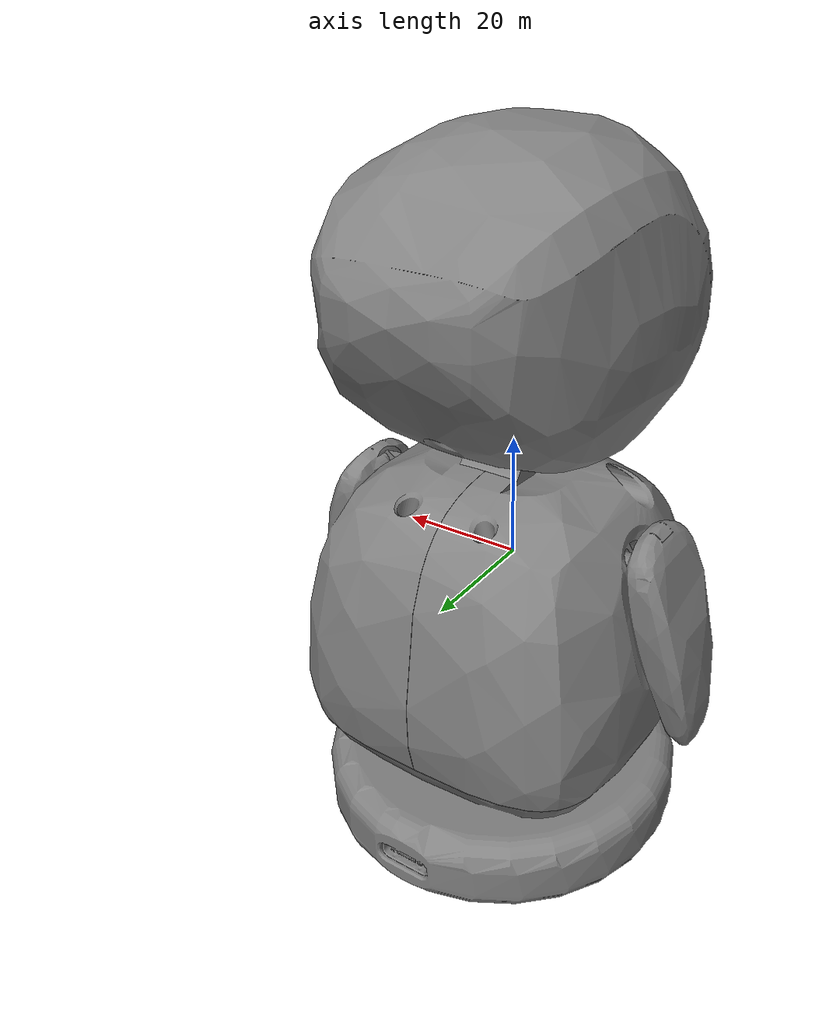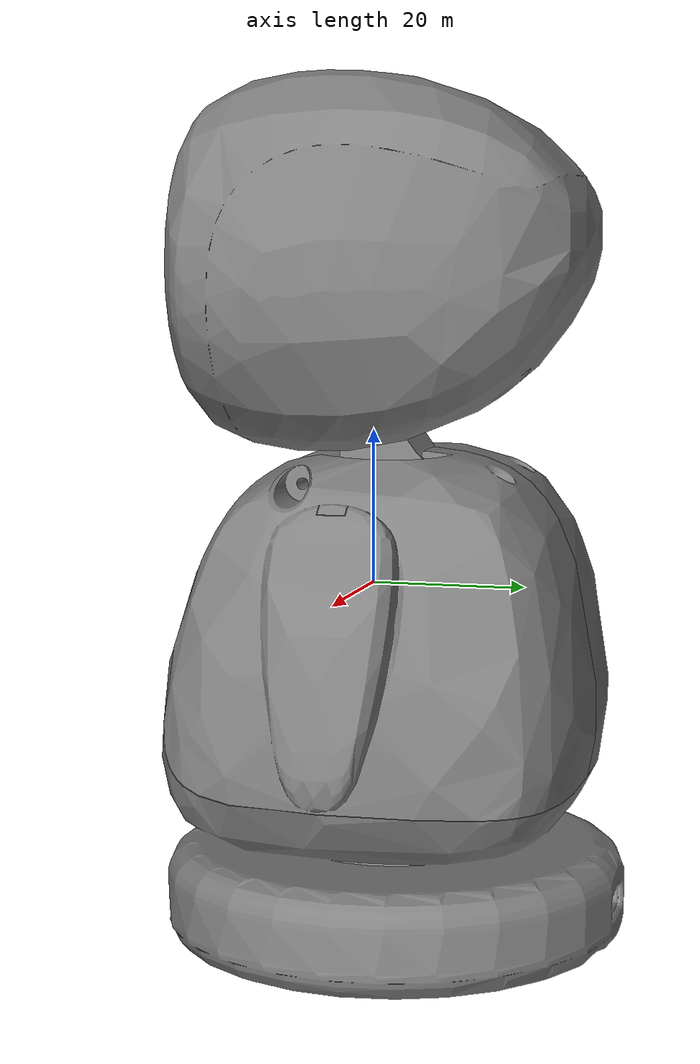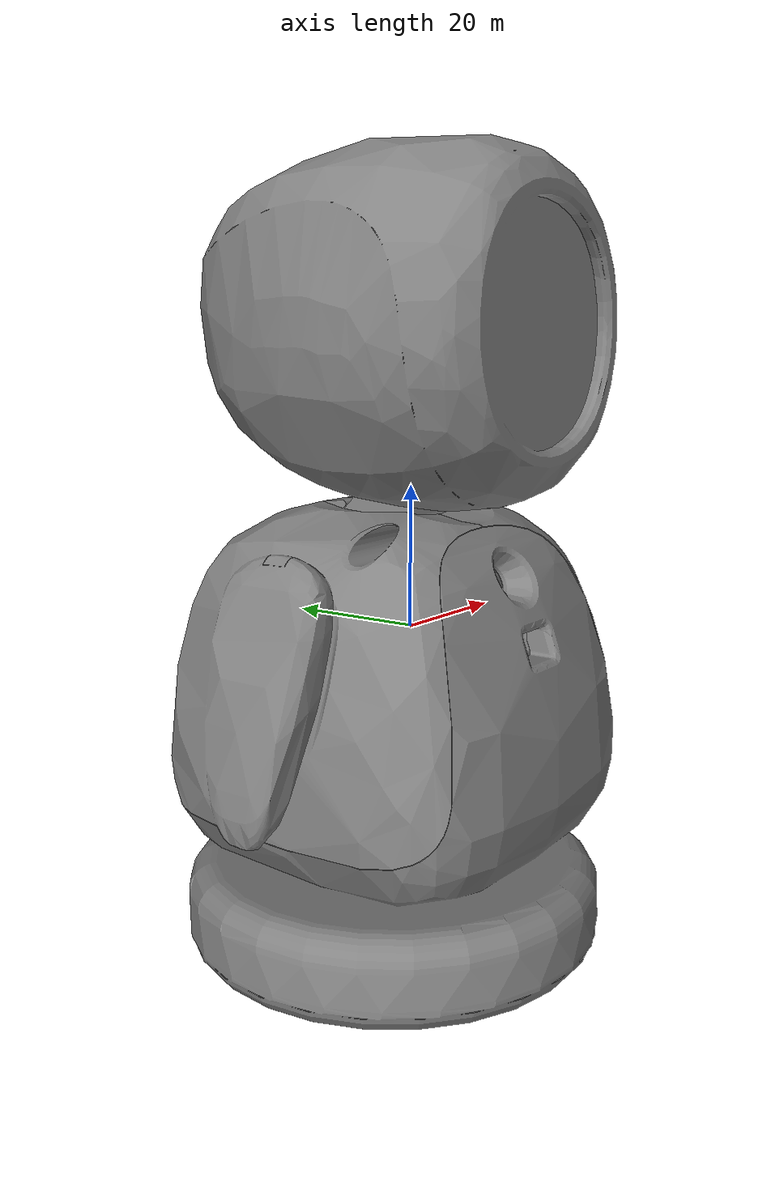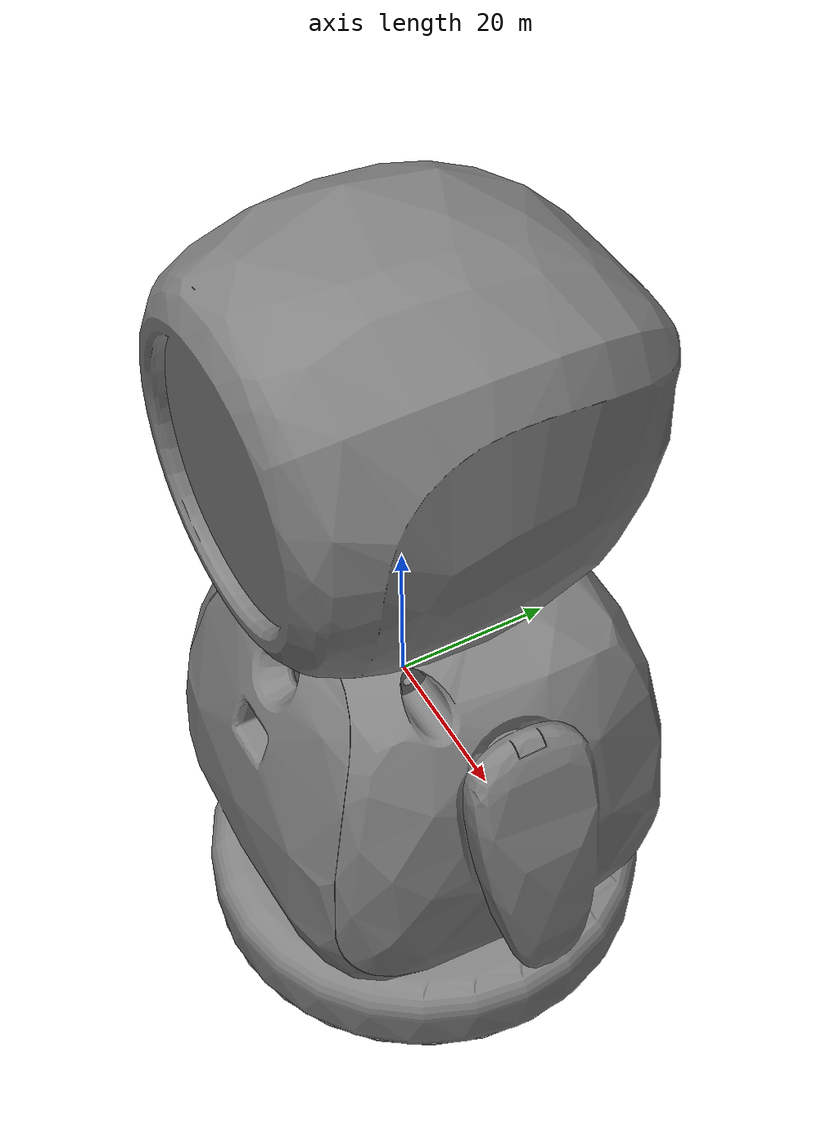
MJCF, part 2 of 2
-21.1688 0.029211 42.6567 -21.1821 -0.127682 42.7276 -18.9438 11.9802 40.4027 -18.9438 11.9802 40.7144 -18.6704 12.8546 40.7144 -18.6705 12.8546 39.4936 -18.5414 13.2471 39.4936 -18.5414 13.2471 39.1819 -18.8154 12.3986 40.4027 -18.8154 12.3986 39.4936 -18.9482 11.9657 39.1819 -18.9482 11.9657 39.4936 -20.4699 5.44912 41.3695 -20.547 4.99314 41.3234 -20.4699 5.44912 40.5615 -20.4503 5.56207 40.6575 -20.4345 5.65164 40.7121 -20.4168 5.75198 40.7447 -20.3903 5.89934 40.7664 -20.3589 6.07176 40.739 -20.3332 6.21103 40.6466 -20.3173 6.29652 40.4924 -20.3127 6.3207 40.3075 -20.3127 6.3207 39.1819 -20.3966 5.86471 39.1819 -20.4023 5.83296 40.3739 -20.4229 5.71752 40.4287 -20.3966 5.86471 40.1805 -20.4466 5.58332 40.3811 -20.4699 5.44912 40.2411 -20.547 4.99314 39.1819 -20.4699 5.44912 39.1819 -19.3266 10.6439 40.7144 -19.4481 10.1879 40.7144 -19.3266 10.6439 39.6668 -19.316 10.6829 39.5153 -19.284 10.7998 39.4706 -19.245 10.9412 39.5153 -19.2119 11.0595 39.6379 -19.2119 11.0595 40.7144 -19.0816 11.5155 40.7144 -19.0816 11.5155 39.1819 -19.2014 11.097 39.3609 -19.1957 11.1172 39.1819 -19.2264 11.0079 39.2629 -19.2578 10.895 39.1921 -19.2938 10.7643 39.1476 -19.4481 10.1879 39.6091 -19.3313 10.6266 39.1329 -19.4417 10.2126 39.4182 -19.3803 10.4446 39.161 -19.4189 10.2991 39.2584 -20.9202 2.40306 40.1057 -20.6068 2.35533 40.0146 -20.926 2.35533 40.0146 -20.6031 2.40307 40.1057 -20.9186 2.41594 40.2151 -20.604 2.41594 40.2151 -20.6147 2.35982 40.401 -20.9255 2.35979 40.4011 -20.6377 2.18217 40.4662 -20.947 2.18217 40.4662 -20.657 2.01045 40.3969 -20.9674 2.01045 40.3969 -20.858 2.89213 40.9597 -20.9002 2.56312 40.8082 -20.8442 2.99602 40.625 -20.8715 2.78803 40.5761 -20.9013 2.55446 40.5643 -20.8855 2.67894 40.4962 -20.8728 2.77813 40.4056 -20.8654 2.83474 40.2959 -20.8632 2.85172 40.169 -20.8658 2.83178 40.0302 -20.8737 2.77091 39.9049 -20.8866 2.67093 39.7985 -20.9028 2.54292 39.7216 -20.9232 2.37872 39.6707 -20.9446 2.20237 39.6553 -20.9659 2.02344 39.6726 -20.9701 1.98736 39.6365 -20.9716 1.97438 39.586 -20.9677 2.00757 39.5182 -20.9519 2.14177 39.4936 -20.9211 2.39573 39.4936 -20.9014 2.55395 39.4801 -20.8827 2.70165 39.4359 -20.8678 2.81645 39.3696 -20.8561 2.90656 39.2772 -20.8489 2.96081 39.1692 -20.8466 2.97871 39.0492 -20.8501 2.95229 38.8992 -20.8563 2.90529 38.8033 -20.8739 2.76947 38.6754 -20.8937 2.6152 38.6082 -20.9142 2.45154 38.5617 -20.9498 2.15908 38.5412 -20.9775 1.9234 38.5533 -21.0018 1.71031 38.6004 -20.9238 2.37356 40.7705 -20.9484 2.17062 40.7635 -20.9701 1.98715 40.7475 -20.9899 1.81565 40.6957 -21.0053 1.67919 40.6147 -21.0171 1.57322 40.5009 -20.9746 1.9484 40.2094 -20.947 2.18217 39.9467 -21.0243 1.50752 40.3605 -20.9672 2.01189 40.016 -21.0266 1.48664 40.2036 -20.912 2.46933 39.1286 -21.025 1.50139 40.0691 -20.973 1.96258 40.1039 -20.9049 2.5256 39.0174 -20.9965 1.75793 39.7649 -21.0196 1.55013 39.9482 -21.0098 1.63926 39.8448 -20.9324 2.30338 39.1704 -20.9145 2.44912 38.8876 -21.0105 1.63239 39.6365 -20.9614 2.06096 39.1704 -21.0155 1.58765 39.4734 -20.9837 1.86946 39.1876 -20.9302 2.32131 38.8491 -21.0121 1.61832 39.3505 -21.0023 1.70598 39.2555 -20.9484 2.17062 38.8414 -20.9743 1.95129 38.8616 -21.0325 1.43211 38.8928 -20.9861 1.84884 38.9222 -20.9892 1.82142 39.0348 -21.0341 1.41738 39.0348 -21.0271 1.48231 38.7664 -21.0165 1.57851 38.6664 -20.6605 1.9484 40.2094 -20.6262 2.18217 39.9467 -20.6484 2.01189 40.016 -20.6564 1.96254 40.104 -20.9815 -2.88036 43.8808 -20.9883 -3.06463 43.8723 -21.0058 -2.8847 43.4404 -21.0128 -3.06898 43.4325 -20.9757 1.93842 44.8231 -20.9779 1.91954 44.7231 -20.969 1.99602 44.9063 -20.9585 2.08497 44.9623 -20.9459 2.19083 44.9799 -20.9332 2.29618 44.9624 -20.9224 2.38419 44.9063 -20.9155 2.44067 44.8232 -20.9132 2.45922 44.7231 -20.9224 2.38419 44.5384 -20.9154 2.44102 44.622 -20.9332 2.29592 44.4833 -20.9459 2.19083 44.4662 -20.9586 2.08475 44.4839 -20.969 1.99602 44.5398 -20.9757 1.93856 44.6227 -18.8373 12.328 41.3599 -18.8432 12.3091 41.2599 -18.8194 12.3856 41.4431 -18.7915 12.4746 41.4991 -18.7582 12.5804 41.5167 -18.7247 12.6858 41.4992 -18.6965 12.7738 41.4431 -18.6782 12.8304 41.3598 -18.6723 12.8488 41.2599 -18.6965 12.7738 41.0752 -18.6782 12.8307 41.1588 -18.7248 12.6855 41.0201 -18.7582 12.5804 41.003 -18.7916 12.4744 41.0207 -18.8194 12.3856 41.0766 -18.8373 12.328 41.1598 -20.6174 4.55735 40.3941 -20.6174 4.55735 40.7144 -20.7314 3.80699 39.5283 -20.6151 4.57178 39.5283 -20.622 4.52849 39.1819 -20.8077 3.26731 39.1819 -20.6986 4.02921 40.371 -20.7989 3.3308 40.7144 -20.7989 3.3308 40.371 -20.8077 3.26731 39.5052 -18.5058 12.3755 43.0665 -18.4989 12.3755 43.713 -18.8225 12.3755 43.713 -18.8225 12.3755 43.0665 -18.7923 12.472 42.9653 -18.4761 12.472 42.9653 -18.7517 12.6006 42.928 -18.4356 12.6006 42.928 -18.6959 12.7756 43.0259 -18.3808 12.7699 43.021 -18.671 12.8525 43.1702 -18.3564 12.8429 43.1334 -18.3493 12.8622 43.243 -18.6675 12.8633 43.4099 -18.3475 12.8633 43.4099 -18.8224 12.3755 44.8356 -18.962 11.9195 44.7866 -18.8225 12.3755 44.0218 -18.7978 12.4546 44.1085 -18.7677 12.5501 44.1747 -18.7342 12.6557 44.2158 -18.6982 12.768 44.2296 -18.6516 12.9121 44.2117 -18.6203 13.0083 44.1807 -18.5925 13.0927 44.1227 -18.5591 13.1937 44.016 -18.5348 13.2663 43.856 -18.5194 13.3125 43.697 -18.5123 13.3337 43.4157 -18.5179 13.3169 43.1968 -18.5365 13.2615 42.9915 -18.711 12.7283 43.8648 -18.6871 12.8027 43.7851 -18.7444 12.6237 43.8919 -18.6709 12.8528 43.6123 -18.7895 12.4808 43.8403 -18.565 13.176 42.831 -18.6063 13.0509 42.7014 -18.6571 12.8956 42.6215 -18.714 12.719 42.5961 -18.7491 12.6088 42.6081 -18.7818 12.5054 42.6451 -18.8333 12.3409 42.7837 -18.8101 12.4152 42.7043 -18.962 11.9195 42.6451 -18.8386 12.3236 42.6451 -18.3484 12.8537 43.6067 -18.3626 12.8027 43.7851 -18.4641 12.4808 43.8403 -18.4182 12.6237 43.8919 -18.3853 12.7283 43.8648 -20.625 2.25997 40.2965 -20.6437 2.10413 40.2892 -20.6212 2.26015 40.1233 -20.6399 2.10431 40.116 -19.6654 9.32791 43.7678 -19.3601 9.22546 43.863 -19.3376 9.32791 43.7678 -19.6903 9.22546 43.863 -19.3887 9.1028 43.8948 -19.7198 9.1028 43.8948 -19.4159 8.99064 43.8645 -19.7465 8.99062 43.8645 -19.437 8.90944 43.7779 -19.7657 8.90944 43.7779 -19.7749 8.87034 43.6596 -19.4538 8.8534 43.6087 -19.7804 8.84696 43.5361 -19.4607 8.84018 43.4128 -19.782 8.84018 43.4128 -19.6654 9.32791 44.8356 -19.6654 9.32791 44.0853 -19.552 9.7839 44.7866 -19.5521 9.7839 42.6451 -19.6527 9.37986 42.6451 -19.6584 9.35677 42.8125 -19.6776 9.27788 42.7239 -19.7011 9.18073 42.6553 -19.7039 9.16877 44.1949 -19.7486 8.98159 44.2296 -19.789 8.81034 44.2042 -19.8242 8.65836 44.1257 -19.853 8.53317 43.9982 -19.6654 9.32791 43.1069 -19.8731 8.4448 43.8371 -19.6913 9.22123 42.9811 -19.726 9.07683 42.9309 -19.8874 8.38141 43.5588 -19.8901 8.36976 43.4157 -19.7809 8.84491 43.2879 -19.7295 9.06214 42.6101 -19.7502 8.97498 42.9591 -19.7603 8.93253 42.5961 -19.885 8.39206 43.1346 -19.776 8.86586 43.1613 -19.8745 8.43883 42.9756 -19.7674 8.90223 43.0391 -19.795 8.78454 42.6168 -19.8178 8.68658 42.6522 -19.8577 8.51262 42.8154 -19.836 8.60762 42.7111 -19.4632 8.83886 43.2878 -19.4603 8.85874 43.1761 -19.452 8.90223 43.0391 -19.3491 9.32791 43.1069 -19.4119 9.07683 42.9309 -19.3766 9.22116 42.9811 -19.4358 8.97498 42.9591 -18.3977 12.7016 43.5793 -18.4498 12.5384 43.5649 -18.4015 12.7001 43.2591 -18.4536 12.5369 43.2437 -20.6827 4.13466 43.5689 -20.3592 4.08693 43.4778 -20.6899 4.08693 43.4778 -20.3493 4.13467 43.5689 -20.6807 4.14754 43.6783 -20.3438 4.14754 43.6783 -20.3455 4.09139 43.8643 -20.6892 4.0914 43.8643 -20.3689 3.91377 43.9294 -20.7157 3.91377 43.9294 -20.3961 3.74205 43.8602 -20.7407 3.74205 43.8602 -20.6068 4.62373 44.4229 -20.6583 4.29472 44.2714 -20.5902 4.72762 44.0882 -20.6233 4.51964 44.0393 -20.6596 4.28607 44.0275 -20.6404 4.41054 43.9594 -20.6249 4.50973 43.8688 -20.6159 4.56634 43.7591 -20.6133 4.58332 43.6322 -20.6164 4.56338 43.4934 -20.626 4.50252 43.3681 -20.6416 4.40254 43.2617 -20.6614 4.27452 43.1848 -20.6863 4.11037 43.134 -20.7127 3.93397 43.1185 -20.7389 3.75504 43.1358 -20.7441 3.71897 43.0997 -20.746 3.70598 43.0492 -20.7412 3.73917 42.9814 -20.7216 3.87337 42.9568 -20.6838 4.12734 42.9568 -20.6597 4.28567 42.9433 -20.6369 4.43325 42.8991 -20.6188 4.54805 42.8328 -20.6045 4.63816 42.7404 -20.5959 4.69241 42.6325 -20.593 4.71031 42.5124 -20.5973 4.68388 42.3623 -20.6048 4.63684 42.2665 -20.6262 4.50107 42.1387 -20.6504 4.3459 42.0711 -20.6754 4.18255 42.0248 -20.7191 3.89068 42.0045 -20.7533 3.65508 42.0165 -20.7835 3.44191 42.0636 -20.6871 4.10531 44.2337 -20.7173 3.90223 44.2267 -20.7441 3.71876 44.2107 -20.7686 3.54725 44.1589 -20.7878 3.41073 44.0779 -20.8025 3.30482 43.9641 -20.7497 3.68 43.6726 -20.7157 3.91377 43.4099 -20.8115 3.23912 43.8237 -20.7405 3.7435 43.4792 -20.8143 3.21824 43.6668 -20.6726 4.20093 42.5918 -20.8123 3.23299 43.5323 -20.7477 3.69418 43.5671 -20.6641 4.25721 42.4807 -20.7768 3.48953 43.2281 -20.8056 3.28174 43.4114 -20.7933 3.37086 43.308 -20.6977 4.03498 42.6336 -20.6757 4.18073 42.3508 -20.7943 3.36399 43.0997 -20.7334 3.79256 42.6336 -20.8005 3.31925 42.9366 -20.761 3.60106 42.6508 -20.695 4.05291 42.3123 -20.7962 3.34993 42.8138 -20.7841 3.43758 42.7187 -20.7174 3.90223 42.3046 -20.7322 3.801 42.3067 -20.7493 3.68289 42.3248 -20.8218 3.16371 42.356 -20.7639 3.58044 42.3854 -20.7678 3.55302 42.498 -20.8237 3.14898 42.498 -20.8149 3.21392 42.2296 -20.8018 3.31011 42.1296 -20.4117 3.68 43.6726 -20.3867 3.91377 43.4099 -20.4091 3.7435 43.4792 -20.4133 3.69414 43.5672 -19.3801 9.16755 43.5794 -19.4192 9.00414 43.5684 -19.3862 9.16568 43.2588 -19.4254 9.00227 43.2473 -21.248 -0.98089 43.5542 -20.9361 -1.54366 43.5542 -21.2852 -1.54366 43.5542 -20.9007 -0.98089 43.5542 -20.8944 -0.996721 43.7096 -21.2504 -1.01478 43.7713 -20.8918 -1.03131 43.8039 -21.2555 -1.0895 43.8614 -20.8932 -1.10653 43.8713 -20.8997 -1.25506 43.9236 -21.2667 -1.25506 43.9236 -21.2151 -0.536446 43.4417 -21.2157 -0.545104 43.2772 -21.2848 -1.53789 43.2772 -21.2802 -1.46349 43.0631 -21.2738 -1.36382 42.9769 -21.2609 -1.16848 42.928 -21.2465 -0.960692 42.9635 -21.2332 -0.775984 43.055 -21.2195 -0.594166 42.8068 -21.229 -0.719954 42.7177 -21.2395 -0.862564 42.6524 -21.2514 -1.03003 42.6095 -21.2635 -1.206 42.5961 -21.2784 -1.43491 42.6197 -21.2912 -1.64179 42.6985 -21.2297 -0.72958 44.0196 -21.2403 -0.874108 44.1358 -21.2532 -1.05544 44.2075 -21.2167 -0.556771 43.6622 -21.2218 -0.624469 43.8645 -21.2667 -1.25506 44.2296 -21.2798 -1.4577 44.2065 -21.274 -1.36588 43.9014 -21.2921 -1.65766 44.1213 -21.2796 -1.4542 43.8327 -21.3009 -1.80712 43.9927 -21.2836 -1.51804 43.7061 -21.307 -1.91451 43.827 -21.3107 -1.98142 43.6255 -21.3119 -2.00254 43.4099 -21.3111 -1.98752 43.2622 -21.3068 -1.91163 42.9843 -21.3004 -1.79901 42.8215 -20.9076 -1.36586 43.9014 -20.9167 -1.4542 43.8327 -20.9271 -1.51809 43.7059 -20.3638 3.9924 43.7605 -20.3866 3.83651 43.7526 -20.3699 3.99104 43.5873 -20.3928 3.83514 43.5793 -19.7651 8.91233 41.3695 -19.8705 8.45634 41.3234 -19.7651 8.91233 40.5615 -19.734 9.04359 40.6707 -19.7084 9.15069 40.7267 -19.657 9.36255 40.7664 -19.6145 9.53497 40.739 -19.5798 9.67423 40.6466 -19.5582 9.75972 40.4924 -19.5521 9.7839 40.3075 -19.5522 9.7839 39.1819 -19.6655 9.32791 39.1819 -19.6732 9.29617 40.3739 -19.7012 9.18073 40.4287 -19.6655 9.32791 40.1805 -19.7333 9.04653 40.3811 -19.7651 8.91233 40.2411 -19.8706 8.45634 39.1819 -19.7651 8.91233 39.1819 -21.354 -2.89055 40.2077 -21.0503 -3.02707 40.1892 -21.3594 -3.02707 40.1892 -21.0453 -2.89055 40.2077 -21.3494 -2.77743 40.2729 -21.0421 -2.77743 40.2729 -21.3464 -2.70821 40.3877 -21.0415 -2.70823 40.3876 -21.3456 -2.6894 40.5297 -21.0433 -2.6894 40.5297 -21.0482 -2.73957 40.7086 -21.3477 -2.73913 40.7077 -21.0527 -2.82172 40.7959 -21.3511 -2.8182 40.794 -21.0625 -3.05015 40.8443 -21.3603 -3.05015 40.8443 -21.3527 -2.85868 41.172 -21.3606 -3.05881 41.1819 -21.3448 -2.67215 41.1349 -21.3334 -2.42389 41.0189 -21.328 -2.31199 40.898 -21.325 -2.25227 40.7993 -21.3234 -2.22141 40.6903 -21.3226 -2.20456 40.5297 -21.3234 -2.22021 40.3648 -21.3249 -2.24978 40.2521 -21.3278 -2.30772 40.1485 -21.3331 -2.41668 40.0203 -21.3395 -2.55409 39.9403 -21.3463 -2.70656 39.8802 -21.3582 -2.99532 39.8486 -21.3663 -3.21466 40.8443 -21.3811 -3.68796 41.1819 -21.3663 -3.21466 40.1892 -21.3663 -3.21466 39.8486 -21.3811 -3.68796 39.1819 -21.3663 -3.21466 39.1819 -21.0687 -3.21466 40.8443 -21.0574 -3.21466 40.1892 -20.9007 -1.16646 43.8006 -20.9073 -1.16768 43.6733 -20.9128 -1.35412 43.792 -20.9195 -1.35535 43.6648 -20.4699 5.44912 42.6451 -20.5469 4.99314 42.6451 -20.5469 4.99314 44.1776 -20.4798 5.39141 44.1776 -20.4743 5.42315 44.0016 -20.4569 5.52379 44.0983 -20.4363 5.64104 44.1733 -20.4143 5.76538 44.2161 -20.3903 5.89934 44.2296 -20.3591 6.07079 44.2016 -20.3334 6.20959 44.1083 -20.3173 6.29589 43.9547 -20.3127 6.3207 43.7707 -20.4022 5.83296 43.8371 -20.4228 5.71752 43.8919 -20.3965 5.86471 43.6379 -20.4465 5.58332 43.8472 -20.4698 5.44912 43.7159 -20.3127 6.3207 42.6451 -20.3965 5.86471 42.6451 -21.0151 1.59054 44.1776 -21.0151 1.59054 43.8659 -20.9125 2.465 44.1776 -20.9125 2.465 42.9568 -20.8624 2.85749 42.9568 -20.8625 2.85749 42.6451 -20.9675 2.00901 43.8659 -20.9675 2.00901 42.9568 -21.0167 1.57611 42.6451 -21.0167 1.57611 42.9568 -21.149 0.254319 39.1819 -21.1883 -0.201669 39.1819 -21.1883 -0.201669 40.7144 -21.1541 0.196599 40.7144 -21.1513 0.228345 40.5384 -21.142 0.331831 40.6381 -21.1315 0.446238 40.7101 -21.1198 0.570672 40.7529 -21.107 0.704535 40.7664 -21.0902 0.875983 40.7384 -21.0762 1.01478 40.6451 -21.0674 1.10109 40.4915 -21.0649 1.12589 40.3075 -21.1134 0.638158 40.3739 -21.1243 0.522717 40.4287 -21.1103 0.669904 40.1747 -21.1368 0.388518 40.384 -21.149 0.254319 40.2527 -21.0649 1.12589 39.1819 -21.1104 0.669904 39.1819 16.7737 -4.27489 50.3572 16.7737 -4.2531 50.1777 16.7737 -4.33901 50.5262 16.7737 -4.44172 50.675 16.7737 -4.57705 50.7949 16.7737 -4.73715 50.879 16.7737 -4.9127 50.9222 16.7737 -5.0935 50.9222 16.7737 -5.26905 50.879 16.7737 -5.42915 50.7949 16.7737 -5.56448 50.675 16.7737 -5.66719 50.5262 16.7737 -5.73131 50.3572 16.7737 -5.7531 50.1777 16.7737 -5.73131 49.9982 16.7737 -5.66719 49.8292 16.7737 -5.56448 49.6804 16.7737 -5.42915 49.5605 16.7737 -5.26905 49.4764 16.7737 -5.0935 49.4332 16.7737 -4.9127 49.4332 16.7737 -4.73715 49.4764 16.7737 -4.57705 49.5605 16.7737 -4.44172 49.6804 16.7737 -4.33901 49.8292 16.7737 -4.27489 49.9982 2.16497 18.6127 26.7675 2.40033 19.2789 26.7338 2.52983 19.0275 26.496 1.89649 19.2131 27.2973 1.91302 19.8761 27.3209 2.23945 19.52 26.9671 1.64483 19.5362 27.5822 1.54505 20.1544 27.6063 1.31179 19.8288 27.8388 0.455472 20.203 28.1629 0.42774 20.5598 28.0365 0.841193 20.4698 27.9394 0.897918 20.063 28.0424 -0.622293 20.1616 28.1274 -0.466174 20.554 28.0301 -0.285327 20.2321 28.1878 -0.955702 20.4341 27.901 -0.932347 20.0482 28.0295 -1.20522 19.9012 27.902 -1.47372 20.1984 27.6518 -2.01514 19.0008 27.1098 -2.25689 19.4946 26.9422 -1.80111 19.3491 27.4173 -2.57446 18.9252 26.4001 -2.19526 18.5016 26.6697 -2.16142 17.375 25.6881 -2.64967 17.2804 24.9767 -2.73585 17.7219 25.3406 -1.902 16.7968 25.1913 -2.47999 16.8473 24.6306 -1.11014 16.0428 24.5468 -1.27283 15.6423 23.7241 -1.63171 15.8588 23.8812 -1.91232 16.0893 24.0511 -1.5347 16.3541 24.8128 -0.839951 15.9123 24.4352 -0.778254 15.4504 23.5868 -0.453827 15.7963 24.3354 -0.24117 15.3503 23.5161 0.247477 15.7634 24.3071 0.838167 15.4668 23.5986 0.308538 15.3565 23.5205 0.543915 15.8167 24.3529 0.826955 15.9079 24.4311 1.36275 15.6913 23.7596 1.09258 16.0336 24.5388 1.85218 16.0352 24.0111 1.3369 16.1902 24.6728 1.88222 16.7669 25.1656 2.49639 16.8838 24.6592 2.22923 16.4433 24.3176 1.6228 16.441 24.8871 2.07375 17.1269 25.4743 2.66467 17.3408 25.0252 2.19632 17.5097 25.8044 2.73684 18.2625 25.8038 2.74316 17.8056 25.4107 2.24986 18.059 26.2819 1.23886 20.1777 27.8163 1.21724 20.3312 27.7917 1.20347 20.0509 27.8691 0.000758 20.4778 28.1151 -0.007374 20.5912 28.0706 0.000638 20.3645 28.1596 0.067852 20.25 28.2031 -1.67948 19.8878 27.5313 -1.77588 19.9923 27.4388 -1.62298 19.7523 27.5922 -1.51649 19.6639 27.6944 -2.56871 18.2081 25.9745 -2.7306 18.3065 25.8415 -2.40976 18.0872 26.0875 -2.25108 18.0007 26.2307 -2.01054 16.4215 24.491 -2.22115 16.4325 24.3092 -1.81125 16.4256 24.6841 0.000163 15.4763 23.7708 0.000167 15.6131 24.0331 -0.053227 15.7504 24.2959 1.945 16.3448 24.431 1.74833 16.3574 24.6287 -2.18462 17.4615 43.025 -2.25 18 43.025 -1.99228 16.9544 43.025 -1.68415 16.508 43.025 -1.27815 16.1483 43.025 -0.797861 15.8962 43.025 -0.271208 15.7664 43.025 0.271208 15.7664 43.025 0.797861 15.8962 43.025 1.27815 16.1483 43.025 1.68415 16.508 43.025 1.99228 16.9544 43.025 2.18462 17.4615 43.025 2.25 18 43.025 2.18462 18.5385 43.025 1.99228 19.0456 43.025 1.68415 19.492 43.025 1.27815 19.8517 43.025 0.797861 20.1038 43.025 0.271208 20.2336 43.025 -0.271208 20.2336 43.025 -0.797861 20.1038 43.025 -1.27815 19.8517 43.025 -1.68415 19.492 43.025 -1.99228 19.0456 43.025 -2.18462 18.5385 43.025 -0 27.5532 38.9854 -5.3 12.6106 21.9699 5.3 12.6106 21.9699 -17.4652 -11.1074 23.5563 -5.3 -8.53692 17.4152 -0.686471 -8.72711 17.0227 2.31571 -8.69251 17.0908 5.3 -8.53692 17.4152 17.4652 -11.1074 23.5563 -6.80239 26.2235 36.3586 -12.5484 24.9653 35.6852 -10.5014 26.8721 38.7155 -7.46846 24.5464 33.5222 -14.7037 21.4681 31.5843 -8.79311 20.0222 27.8602 -16.3965 16.9382 27.9964 6.80239 26.2235 36.3586 10.5014 26.8721 38.7155 12.5484 24.9653 35.6852 7.46846 24.5464 33.5222 14.7037 21.4681 31.5843 8.79311 20.0222 27.8602 16.3965 16.9382 27.9964 -11.8768 14.8202 24.2395 -17.5233 11.7856 25.4798 -14.4003 10.2562 22.7551 -18.1461 6.26916 23.9036 -12.2061 12.1992 22.8459 -12.4415 9.48237 21.7073 -14.6947 4.18002 21.0456 -18.3296 0.645449 23.1251 -10.2391 8.20746 20.6537 -5.3 5.62929 19.0841 -12.5384 5.9495 20.5781 -12.586 3.13387 19.9551 -12.5603 -0.508414 19.4503 -10.2919 1.52709 18.9727 -5.3 -1.65433 17.61 -14.6126 -2.57772 20.2946 -18.0024 -6.57655 23.0814 -12.4082 -4.15491 19.2419 11.8768 14.8202 24.2395 17.5233 11.7856 25.4798 -14.1987 -8.78342 20.5045 -10.119 -5.65266 18.4313 -12.2606 -7.56607 19.3511 12.2061 12.1992 22.8459 10.2391 8.20746 20.6537 5.3 5.62929 19.0841 -12.044 -9.84569 19.5433 12.4415 9.48237 21.7073 14.4003 10.2562 22.7551 18.1461 6.26916 23.9036 12.5384 5.9495 20.5781 10.2919 1.52709 18.9727 5.3 -1.65433 17.61 12.586 3.13387 19.9551 14.6947 4.18002 21.0456 18.3296 0.645449 23.1251 12.5603 -0.508414 19.4503 10.119 -5.65266 18.4313 12.4082 -4.15491 19.2419 14.6126 -2.57772 20.2946 18.0024 -6.57655 23.0814 12.2606 -7.56607 19.3511 12.044 -9.84569 19.5433 14.1987 -8.78342 20.5045 4.90895 17.6114 29.3688 5.00575 18.2392 30.0252 4.78898 18.2365 30.0476 0.630397 14.0504 26.7994 0.634879 13.6058 25.9584 1.31136 13.7431 26.0573 1.20194 14.1848 26.921 -0.974047 14.1206 26.8626 -0.960005 13.6595 25.9968 -0.49994 14.0315 26.7825 4.95834 19.6362 31.6393 3.2546 15.1519 27.1943 3.18789 14.7344 26.806 3.80497 15.3499 27.303 2.8896 15.1887 27.6158 3.07327 15.4381 28.1438 2.3908 14.7933 27.4941 -0.001179 13.7684 26.1147 -0.039907 13.5639 25.9286 -0.001101 13.9143 26.3498 -0.001048 13.9782 26.5476 0.037729 14 26.7545 -3.2536 15.1516 27.1939 -4.11012 15.7514 27.6411 -3.34211 14.87 26.9131 -2.88871 15.1885 27.6154 -3.02816 15.2036 27.418 -2.36267 14.7731 27.4744 -2.85404 15.1972 27.8953 -3.25013 15.667 28.3853 -4.54637 17.852 29.722 -5.02212 18.5096 30.3193 -4.7007 16.8976 28.6708 -4.02718 17.5352 30.1124 -3.91401 17.1846 30.1511 -3.99954 18.0009 31.2512 -4.20367 17.7088 29.9163 -2.94109 20.8813 35.2049 -3.65595 19.6317 33.8083 -2.6651 20.9841 36.3574 -8.8e-05 23.3335 37.7011 0.056974 23.8927 38.1941 -0.402362 23.8759 38.1607 -8.1e-05 22.1597 38.1013 -0.14354 21.9969 38.6369 0.189061 21.9949 38.632 2.9418 20.8806 35.2042 2.65453 20.9933 36.377 3.3266 20.2195 34.8607 4.46008 17.8781 29.8193 4.58108 18.1991 30.1013 4.39192 18.1289 30.1837 4.23049 18.0292 30.2909 4.10445 17.9047 30.4179 4.15588 17.0998 29.1569 4.7273 16.9692 28.7398 4.01979 17.7614 30.5585 3.98054 17.6059 30.7062 3.66456 16.3959 29.1963 4.06725 16.8111 28.8622 3.89554 16.3849 28.4424 4.28481 16.0234 27.8773 3.58384 15.8252 27.9158 3.36833 15.5263 27.6454 3.02908 15.2039 27.4185 2.44617 14.6561 26.9005 2.52674 14.263 26.4426 1.68672 14.3722 27.0939 2.05512 14.4122 26.7023 1.95228 13.9683 26.2223 1.8 14.2826 26.5986 -1.60317 14.1973 26.531 -1.83265 13.9189 26.1858 -1.42743 14.263 26.9927 -1.84214 14.3029 26.6147 -2.4167 14.1996 26.3948 -1.85154 14.4542 27.1704 -2.09505 14.435 26.7206 -2.38397 14.6139 26.8659 -3.59317 15.8402 27.9292 -3.81718 16.2257 28.2892 -3.63754 16.3365 29.1269 -4.04314 16.7443 28.7943 -4.30766 18.4317 30.6463 -4.19714 19.2969 31.7439 -4.76442 20.4081 32.625 -3.34096 20.6828 34.238 -2.99373 21.275 34.979 -3.05248 22.0485 35.3244 -3.86329 22.0339 34.9558 -3.33276 21.7582 34.8491 -3.26717 22.6546 35.9545 -2.72262 21.0978 35.6274 -1.62694 22.9886 37.0035 -1.58775 23.6277 37.6794 -2.5225 23.1965 36.8878 -1.19662 23.1467 37.3142 -1.47937 21.8783 37.3345 -2.08778 21.4144 37.2771 -1.36087 21.7601 38.0637 -1.05985 22.0187 37.6929 -1.00634 22.458 37.3773 -0.902537 23.2269 37.4773 -0.84554 23.8182 38.0468 -1.22918 23.7348 37.8843 -0.90715 22.0573 37.7983 -0.928554 21.8899 38.3744 -0.301129 23.3214 37.6749 -0.730942 22.0937 37.9013 0.197451 23.3283 37.6897 0.563065 23.8597 38.1285 -4.3e-05 22.5883 37.7322 -0.19811 22.1548 38.0856 -0.505463 21.967 38.5627 0.396958 23.3125 37.656 1.09717 23.7672 37.9472 0.22084 22.1537 38.0819 0.561604 21.9594 38.5441 0.99891 23.2033 37.429 1.58775 23.6277 37.6794 1.00746 22.4579 37.377 1.1979 23.1465 37.3138 1.55808 23.0173 37.0591 2.38167 23.2765 37.0309 0.891114 22.0611 37.8088 1.06098 22.0185 37.6925 1.19597 21.8164 38.1974 0.754357 22.0894 37.889 0.889839 21.899 38.3964 1.23988 21.9648 37.5515 1.63686 21.6494 37.8061 1.53742 22.4547 36.9264 2.71877 21.3692 35.4698 2.99445 21.2743 34.9783 3.33356 21.7575 34.8484 2.71782 21.102 35.6363 3.10891 20.9734 34.7423 3.88751 20.1908 32.9955 4.56549 20.9081 33.3039 3.57238 20.7519 33.8491 4.10584 19.6326 32.2001 3.81582 19.2181 33.1131 3.97975 18.4373 31.8886 4.22153 19.1843 31.5963 4.10209 18.3606 30.9982 -3.83175 19.5178 32.7395 -3.88192 20.2031 33.0126 -3.97588 20.7154 33.3388 -3.49067 21.4529 34.4489 -2.76628 21.5875 35.3919 -2.51378 21.89 35.7976 -2.81761 22.3634 35.7684 -2.65081 22.4947 35.995 -2.18853 22.1157 36.2318 -2.45539 21.3789 36.021 -2.29372 22.7388 36.4271 -1.83852 22.315 36.6326 -2.30852 21.4866 36.2468 -2.10339 22.8505 36.6299 -1.99547 21.6851 36.6785 -1.82947 21.775 36.8817 -1.42691 22.4085 37.0326 -0.71995 22.6106 37.5137 -0.462605 22.6499 37.6187 -0.212657 22.6714 37.6801 0.262638 22.6684 37.6712 0.514555 22.6434 37.6009 0.77351 22.6003 37.487 1.87602 22.9692 36.8491 1.75893 22.3546 36.7148 1.99533 22.9088 36.7372 2.15809 22.8195 36.5735 2.05656 22.1955 36.3906 3.03853 22.8447 36.2757 1.45983 21.9415 37.275 2.46731 22.6257 36.2255 2.40196 21.972 35.9537 1.67163 21.8515 37.0595 2.05347 21.4349 37.3227 1.77434 21.8026 36.9455 2.64783 22.4965 35.9986 1.91481 21.7299 36.7794 2.24395 21.5305 36.3411 3.07568 22.1351 35.3837 3.86329 22.0339 34.9558 2.39829 21.4216 36.1105 3.67422 21.4574 34.3055 3.32176 20.4774 34.313 -4.15907 20.0823 32.5503 -3.62684 20.192 33.4952 -0.442058 22.1626 37.9856 0.491629 22.157 37.9683 3.40017 20.9959 34.2395 -6.15167 24.6617 40.0473 6.15167 24.6617 40.0473 -5.3 9.42768 23.7299 5.3 9.42768 23.7299 -5.3 -7.74595 20.4194 -3 -10.0347 20.2611 -2.49978 -7.78136 20.0788 0.488938 -7.79287 19.9891 -3 -11.5167 20.4394 -3.88889 -13.1796 20.8582 -3.0576 -11.9932 20.5197 -3.22586 -12.44 20.6171 -3.49292 -12.8315 20.727 -3.67968 -13.0189 20.792 -4.44955 -13.5962 21.0497 -4.95945 -14.06 21.2698 3 -10.0347 20.2611 5.3 -7.74595 20.4194 3 -11.5167 20.4394 3.88889 -13.1796 20.8582 3.25157 -12.4878 20.6291 3.52967 -12.8725 20.7404 3.07155 -12.0469 20.5301 3.01798 -11.7843 20.4818 4.76164 -13.8691 21.1783 5.24001 -14.3586 21.4154 -9.23317 23.4361 37.9103 -8.27607 24.4516 39.9191 -10.5849 21.0863 34.3173 -11.7902 17.9027 30.6977 -13.1524 9.94432 25.5962 -5.3 3.90101 21.7229 9.23317 23.4361 37.9103 8.2718 24.4522 39.9195 10.5849 21.0863 34.3173 -13.3295 0.805075 23.2187 -5.3 -1.86582 20.6285 11.7902 17.9027 30.6977 13.1524 9.94432 25.5962 5.3 3.90101 21.7229 13.3295 0.805075 23.2187 5.3 -1.86582 20.6285 -1.25 18 48.025 -1.21368 17.7009 43.025 -1.25 18 43.025 -1.21368 17.7009 48.025 -1.10682 17.4191 43.025 -1.10682 17.4191 48.025 -0.935638 17.1711 43.025 -0.935638 17.1711 48.025 -0.710081 16.9713 43.025 -0.710081 16.9713 48.025 -0.443256 16.8312 43.025 -0.443256 16.8312 48.025 -0.150671 16.7591 43.025 -0.150671 16.7591 48.025 0.150671 16.7591 43.025 0.150671 16.7591 48.025 0.443256 16.8312 43.025 0.443256 16.8312 48.025 0.710081 16.9713 43.025 0.710081 16.9713 48.025 0.935638 17.1711 43.025 0.935638 17.1711 48.025 1.10682 17.4191 43.025 1.10682 17.4191 48.025 1.21368 17.7009 43.025 1.21368 17.7009 48.025 1.25 18 43.025 1.25 18 48.025 1.21368 18.2991 43.025 1.21368 18.2991 48.025 1.10682 18.5809 43.025 1.10682 18.5809 48.025 0.935638 18.8289 43.025 0.935638 18.8289 48.025 0.710081 19.0287 43.025 0.710081 19.0287 48.025 0.443256 19.1688 48.025 0.443256 19.1688 43.025 0.150671 19.2409 48.025 0.150671 19.2409 43.025 -0.150671 19.2409 43.025 -0.150671 19.2409 48.025 -0.443256 19.1688 43.025 -0.443256 19.1688 48.025 -0.710081 19.0287 48.025 -0.710081 19.0287 43.025 -0.935638 18.8289 48.025 -0.935638 18.8289 43.025 -1.10682 18.5809 48.025 -1.10682 18.5809 43.025 -1.21368 18.2991 48.025 -1.21368 18.2991 43.025 19.9765 2.74812 37.4922 19.6813 2.74809 37.837 19.2724 2.74805 38.1316 20.1682 2.74801 37.1316 18.8027 2.74805 38.3156 20.2836 2.74805 36.7389 20.3163 2.7482 36.4507 18.3026 2.74807 38.3785 7.5737 2.74807 38.3785 3.06886 2.74779 41.209 2.69906 2.74768 42.2659 5.40428 2.74802 38.8736 6.4611 2.74805 38.5038 3.66454 2.74788 40.261 4.45625 2.74796 39.4693 19.3459 1.80089 38.1517 18.609 -0.251934 38.3782 20.0569 1.87899 37.5231 19.4553 0.736104 38.1506 20.0153 -0.2519 37.8036 19.6559 -0.251936 38.0838 19.2418 -0.251948 38.2756 18.9295 -0.251944 38.3522 20.168 0.801738 37.5194 20.6016 -0.251855 36.595 20.4999 -0.251937 37.0396 20.3022 -0.251882 37.4493 2.69906 -0.252319 42.2656 3.06886 -0.252214 41.2088 3.66454 -0.25212 40.2607 4.45625 -0.252042 39.469 5.40428 -0.251983 38.8733 6.4611 -0.251947 38.5035 7.5737 -0.251934 38.3782 -5.3 -7.97011 19.0474 -5.3 -8.2149 18.218 5.3 -7.97011 19.0474 5.3 -8.2149 18.218 -5.3 10.3226 23.0973 -5.3 11.2119 22.5781 5.3 11.2119 22.5781 5.3 10.3226 23.0973 3 -11.5167 19 3.00661 -11.6792 19 3.05928 -12 20 3.02642 -11.8407 19 3.05928 -12 19 3.23531 -12.4579 20 3.5175 -12.8591 20 3.88889 -13.1796 20 3 -10.0006 20.0348 3 -11 19 3 -10.0189 19.8066 3 -10.7726 19.0262 3 -10.0885 19.5886 3 -10.5572 19.1034 3 -10.2059 19.3922 3 -10.3649 19.2276 5.07392 -14.1776 20 4.5091 -13.6458 20 -3.05928 -12 20 -3.00661 -11.6792 19 -3 -11.5167 19 -3.02642 -11.8407 19 -3.23531 -12.4579 20 -3.05928 -12 19 -3.5175 -12.8591 20 -3.88889 -13.1796 20 -4.5091 -13.6458 20 -5.07392 -14.1776 20 -3 -10.5572 19.1034 -3 -10.3649 19.2276 -3 -10.7726 19.0262 -3 -11 19 -3 -10.2059 19.3922 -3 -10.0885 19.5886 -3 -10.0189 19.8066 -3 -10.0006 20.0348 -5.94977 28.5812 47.8158 -10.5014 26.8721 50.3857 -0 27.5532 50.3843 -10.9231 27.2686 49.137 -11.1542 27.4952 47.577 -11.188 27.5287 43.1572 -5.94977 28.5812 42.885 -10.9727 27.3165 40.7467 5.94977 28.5812 47.8158 10.5014 26.8721 50.3857 10.9231 27.2686 49.137 11.1542 27.4952 47.577 11.188 27.5287 43.1572 5.94977 28.5812 42.885 10.9727 27.3165 40.7467 -0 28.9154 45.7822 -15.3985 24.5685 44.2416 -18.5899 20.0222 43.1942 -14.3678 24.5064 36.765 -17.1659 20.0222 32.6729 -21.5156 12.7269 39.9935 -22.7554 7.69676 44.2477 -19.0124 17.4609 33.2961 -19.7969 16.1029 33.9779 -22.507 8.68819 38.3653 -20.6063 13.5429 33.1258 -23.5769 2.31286 44.4469 -23.0472 5.98384 38.5379 -20.0219 12.9621 30.2665 -23.8212 -0.345113 44.4311 -23.4635 3.16802 38.3465 -23.9448 -2.1565 44.1345 -23.7475 0.626154 38.4301 -24.0299 -3.79756 43.5906 -22.6455 4.20285 32.6811 -23.8553 -0.819857 38.3031 -23.9106 -2.10031 38.0059 -23.9194 -3.30304 37.527 -24.0322 -7.75902 42.6432 -23.9163 -6.83097 37.5182 -23.001 -4.41145 32.0105 -23.7782 -8.09407 36.7753 -23.8064 -10.3487 38.8675 -22.5683 -10.7343 32.2677 -22.7863 -12.233 33.9279 -21.5329 -11.0723 29.6261 15.09 24.5464 49.1977 18.136 20.0222 50.5009 15.09 24.5464 39.032 18.136 20.0222 35.8017 20.4931 15.7943 43.9689 22.8157 7.3851 44.2711 21.8408 11.4531 38.7067 20.8169 14.4891 37.2082 22.501 8.71512 38.3637 23.6199 1.90396 44.4733 23.1329 5.48565 38.5613 21.7072 9.74861 33.1625 23.847 -0.673742 44.3816 23.528 2.66897 38.3816 23.9897 -2.92214 43.8848 23.7575 0.511708 38.426 22.691 3.86994 32.6905 23.8759 -1.19774 38.2366 23.9215 -2.87617 37.717 24.0391 -7.32205 42.9009 23.9441 -6.42543 37.6963 23.0336 -4.13093 32.1202 23.8138 -7.83942 36.9531 23.8124 -10.2246 38.7818 22.4731 -10.7869 31.9891 22.7539 -12.2611 33.82 21.5832 -11.0644 29.7379 18.2149 20.6259 40.2067 19.3811 15.7302 31.6938 19.5679 13.4483 29.5894 -8.23711 24.6477 48.9058 8.23268 24.6484 48.9055 -6.13837 24.8757 48.8324 -6.13688 24.8754 48.8327 -6.65409 23.8162 50.3554 6.13688 24.8754 48.8327 6.13901 24.8757 48.8324 6.65745 23.8166 50.3542 -21.0525 -2.86507 40.6328 -21.0595 -3.04031 40.6285 -21.0487 -2.8649 40.4126 -21.0557 -3.04013 40.4086 -8.078 25.3057 47.3385 -8.04784 25.3936 46.582 -10.0595 24.6498 42.1265 -8.12213 25.2708 42.9027 0 25.8321 47.099 0 25.9005 46.6218 0 25.7806 43.5352 8.078 25.3057 47.3385 8.04784 25.3936 46.582 8.12213 25.2708 42.9027 6.59085 -16.6659 41.6641 6.61441 -16.6659 41.7596 6.61441 -16.6759 41.7596 6.59085 -16.6759 41.6641 6.52557 -16.6659 41.5904 6.52557 -16.6759 41.5904 6.43352 -16.6659 41.5555 6.43352 -16.6759 41.5555 6.33579 -16.6659 41.5673 6.33579 -16.6759 41.5673 6.25477 -16.6659 41.6232 6.25477 -16.6759 41.6232 6.20902 -16.6659 41.7104 6.20902 -16.6759 41.7104 6.20902 -16.6659 41.8089 6.20902 -16.6759 41.8089 6.25477 -16.6659 41.896 6.25477 -16.6759 41.896 6.33579 -16.6659 41.952 6.33579 -16.6759 41.952 6.43352 -16.6659 41.9638 6.43352 -16.6759 41.9638 6.52557 -16.6659 41.9289 6.52557 -16.6759 41.9289 6.59085 -16.6659 41.8552 6.59085 -16.6759 41.8552 3.85651 -16.6759 41.4807 3.8907 -16.6659 41.3981 3.8907 -16.6759 41.3981 3.85651 -16.6659 41.4807 3.77398 -16.6759 41.5149 3.77398 -16.6659 41.5149 3.69144 -16.6759 41.4807 3.69144 -16.6659 41.4807 3.65726 -16.6759 41.3981 3.65726 -16.6659 41.3981 3.69144 -16.6759 41.3156 3.69144 -16.6659 41.3156 3.77398 -16.6759 41.2814 3.77398 -16.6659 41.2814 3.85651 -16.6759 41.3156 3.85651 -16.6659 41.3156 7.18961 -16.6759 41.459 7.1604 -16.6659 41.5096 7.18961 -16.6659 41.459 7.1604 -16.6759 41.5096 7.10196 -16.6659 41.5096 7.10196 -16.6759 41.5096 7.07275 -16.6659 41.459 7.07275 -16.6759 41.459 7.71063 -16.6759 41.4614 7.68263 -16.6659 41.5099 7.71063 -16.6659 41.4614 7.68263 -16.6759 41.5099 7.62664 -16.6659 41.5099 7.62664 -16.6759 41.5099 7.59864 -16.6659 41.4614 7.59864 -16.6759 41.4614 7.38053 -16.6659 41.8372 7.38053 -16.6759 41.8372 7.46869 -16.6759 41.8935 7.46869 -16.6659 41.8935 7.56719 -16.6759 41.9287 7.56719 -16.6659 41.9287 7.67107 -16.6759 41.9411 7.67107 -16.6659 41.9411 7.77508 -16.6759 41.9299 7.77508 -16.6659 41.9299 7.87396 -16.6759 41.8957 7.87396 -16.6659 41.8957 7.96273 -16.6759 41.8404 7.96273 -16.6659 41.8404 8.03689 -16.6759 41.7666 8.03689 -16.6659 41.7666 8.09272 -16.6759 41.6782 8.09272 -16.6659 41.6782 8.12738 -16.6759 41.5795 8.12738 -16.6659 41.5795 8.13914 -16.6759 41.4755 8.13914 -16.6659 41.4755 6.61287 -16.6659 41.5174 6.61287 -16.6759 41.5174 6.63802 -16.6759 41.627 6.63802 -16.6659 41.627 6.68826 -16.6759 41.7275 6.68826 -16.6659 41.7275 6.76075 -16.6759 41.8135 6.76075 -16.6659 41.8135 6.85142 -16.6759 41.8799 6.85142 -16.6659 41.8799 6.95519 -16.6759 41.9231 6.95519 -16.6659 41.9231 7.06622 -16.6759 41.9407 7.06622 -16.6659 41.9407 7.17826 -16.6759 41.9317 7.17826 -16.6659 41.9317 7.28503 -16.6759 41.8965 7.28503 -16.6659 41.8965 5.36594 -16.6659 41.8928 5.36594 -16.6759 41.8928 5.49617 -16.6759 41.9388 5.49617 -16.6659 41.9388 5.63351 -16.6759 41.953 5.63351 -16.6659 41.953 5.77039 -16.6759 41.9347 5.77039 -16.6659 41.9347 5.89922 -16.6759 41.885 5.89922 -16.6659 41.885 6.01288 -16.6759 41.8066 6.01288 -16.6659 41.8066 6.10509 -16.6759 41.7038 6.10509 -16.6659 41.7038 6.17075 -16.6759 41.5824 6.17075 -16.6659 41.5824 6.20623 -16.6759 41.4489 6.20623 -16.6659 41.4489 5.61443 -16.6759 41.227 5.52691 -16.6659 41.227 5.52691 -16.6759 41.227 5.61443 -16.6659 41.227 5.68671 -16.6759 41.2764 5.68671 -16.6659 41.2764 5.71866 -16.6759 41.3578 5.71866 -16.6659 41.3578 5.69917 -16.6759 41.4432 5.69917 -16.6659 41.4432 5.63501 -16.6759 41.5027 5.63501 -16.6659 41.5027 5.54847 -16.6759 41.5158 5.54847 -16.6659 41.5158 5.32801 -16.6659 41.1423 5.31004 -16.6659 41.0667 5.31004 -16.6759 41.0667 5.32801 -16.6759 41.1423 5.37806 -16.6659 41.2016 5.37806 -16.6759 41.2016 5.44946 -16.6659 41.232 5.44946 -16.6759 41.232 4.28075 -16.6659 41.7272 4.28075 -16.6759 41.7272 4.35822 -16.6759 41.8314 4.35822 -16.6659 41.8314 4.45737 -16.6759 41.9153 4.45737 -16.6659 41.9153 4.57298 -16.6759 41.9744 4.57298 -16.6659 41.9744 4.69902 -16.6759 42.0058 4.69902 -16.6659 42.0058 4.82887 -16.6759 42.0076 4.82887 -16.6659 42.0076 4.95575 -16.6759 41.9799 4.95575 -16.6659 41.9799 5.07301 -16.6759 41.9241 5.07301 -16.6659 41.9241 5.1745 -16.6759 41.843 5.1745 -16.6659 41.843 5.25492 -16.6759 41.7411 5.25492 -16.6659 41.7411 5.31004 -16.6759 41.6235 5.31004 -16.6659 41.6235 4.3776 -16.6659 41.3713 4.3776 -16.6759 41.3713 4.35287 -16.6759 41.225 4.35287 -16.6659 41.225 4.29321 -16.6759 41.0891 4.29321 -16.6659 41.0891 4.20224 -16.6759 40.9719 4.20224 -16.6659 40.9719 4.08544 -16.6759 40.8804 4.08544 -16.6659 40.8804 3.94985 -16.6759 40.8201 3.94985 -16.6659 40.8201 3.80365 -16.6759 40.7947 3.80365 -16.6659 40.7947 3.65567 -16.6759 40.8056 3.65567 -16.6659 40.8056 3.51482 -16.6759 40.8523 3.51482 -16.6659 40.8523 3.3896 -16.6759 40.9319 3.3896 -16.6659 40.9319 3.28756 -16.6759 41.0397 3.28756 -16.6659 41.0397 3.21487 -16.6759 41.1691 3.21487 -16.6659 41.1691 3.17589 -16.6759 41.3122 3.17589 -16.6659 41.3122 3.173 -16.6759 41.4606 3.173 -16.6659 41.4606 3.20635 -16.6759 41.6052 3.20635 -16.6659 41.6052 3.27394 -16.6759 41.7373 3.27394 -16.6659 41.7373 3.37169 -16.6759 41.849 3.37169 -16.6659 41.849 3.4937 -16.6759 41.9334 3.4937 -16.6659 41.9334 3.63262 -16.6759 41.9856 3.63262 -16.6659 41.9856 3.78007 -16.6759 42.0023 3.78007 -16.6659 42.0023 3.92715 -16.6759 41.9826 3.92715 -16.6659 41.9826 4.06499 -16.6759 41.9277 4.06499 -16.6659 41.9277 4.18527 -16.6759 41.8408 4.18527 -16.6659 41.8408 4.8016 -16.6759 41.5279 4.82798 -16.6659 41.4689 4.82798 -16.6759 41.4689 4.8016 -16.6659 41.5279 4.74005 -16.6759 41.5476 4.74005 -16.6659 41.5476 4.68431 -16.6759 41.5149 4.68431 -16.6659 41.5149 4.77813 -16.6659 43.8675 4.71442 -16.6659 43.8641 4.71442 -16.6759 43.8641 4.77813 -16.6759 43.8675 4.83091 -16.6659 43.8316 4.83091 -16.6759 43.8316 4.85127 -16.6659 43.7711 4.85127 -16.6759 43.7711 12.3413 -16.6759 42.3092 12.3413 -16.6659 42.3092 12.427 -16.6659 42.3089 12.427 -16.6759 42.3089 12.2559 -16.6759 42.3234 12.2559 -16.6659 42.3234 12.1726 -16.6759 42.3512 12.1726 -16.6659 42.3512 12.0929 -16.6759 42.3922 12.0929 -16.6659 42.3922 12.4114 -16.6759 43.8375 12.3078 -16.6659 43.8396 12.3078 -16.6759 43.8396 12.4372 -16.6659 43.8338 12.5139 -16.6759 43.8152 12.5638 -16.6659 43.7966 12.6126 -16.6759 43.7732 12.6767 -16.6659 43.7336 12.7047 -16.6759 43.7127 12.8121 -16.6659 43.6075 12.8406 -16.6759 43.5708 12.9131 -16.6659 43.4506 12.933 -16.6759 43.4069 12.9814 -16.6659 43.2568 12.9925 -16.6759 43.2 13.0044 -16.6659 43.0469 13.0023 -16.6759 42.9891 12.9777 -16.6659 42.8333 12.9648 -16.6759 42.787 12.9118 -16.6659 42.6571 12.8893 -16.6759 42.6164 12.7995 -16.6659 42.4958 12.7751 -16.6759 42.4709 12.7179 -16.6659 42.4218 12.6734 -16.6759 42.3911 12.6269 -16.6659 42.365 12.5541 -16.6759 42.3347 12.5291 -16.6659 42.3271 16.5919 -17.3359 37.024 16.8088 -17.3359 37.0735 16.9037 -17.3359 37.1331 16.7032 -17.3359 37.0365 17.0919 -17.3359 37.524 17.0424 -17.3359 37.3071 17.0794 -17.3359 37.4128 16.9828 -17.3359 37.2123 16.5919 -17.3359 38.524 12.1703 -17.3359 37.024 11.0919 -17.3359 38.524 11.2169 -17.3359 37.824 10.2169 -17.3359 37.824 10.1212 -17.3359 37.805 8.58769 -17.3359 37.024 9.96691 -17.3359 37.024 9.96691 -17.3359 37.574 9.98594 -17.3359 37.6697 10.0401 -17.3359 37.7508 17.0919 -17.3359 47.524 16.5919 -17.3359 47.024 16.9828 -17.3359 47.8358 17.0794 -17.3359 47.6353 17.0424 -17.3359 47.741 16.9037 -17.3359 47.9149 6.96691 -17.3359 38.384 16.5919 -17.3359 48.024 16.8088 -17.3359 47.9745 16.7032 -17.3359 48.0115 6.14117 -17.3359 39.4424 6.14117 -17.3359 38.6324 6.14117 -17.3359 39.7583 6.14117 -17.3359 40.5683 6.14117 -17.3359 40.8842 6.14117 -17.3359 41.6942 2.59191 -17.3359 38.384 3.24117 -17.3359 38.6324 6.14117 -17.3359 42.0101 11.0919 -17.3359 47.024 3.24117 -17.3359 39.4424 3.24117 -17.3359 39.7583 6.14117 -17.3359 42.8201 6.14117 -17.3359 43.136 3.24117 -17.3359 40.5683 3.24117 -17.3359 40.8842 6.14117 -17.3359 43.946 6.14117 -17.3359 44.2619 3.24117 -17.3359 41.6942 6.14117 -17.3359 45.0719 2.94117 -17.3359 42.0101 6.14117 -17.3359 45.3878 3.24117 -17.3359 43.136 6.14117 -17.3359 46.1978 6.14117 -17.3359 46.5137 3.24117 -17.3359 43.946 6.14117 -17.3359 47.3237 2.94117 -17.3359 44.2619 2.94117 -17.3359 42.8201 3.24117 -17.3359 45.3878 3.24117 -17.3359 46.1978 2.94117 -17.3359 45.0719 3.24117 -17.3359 46.5137 2.59191 -17.3359 48.024 3.24117 -17.3359 47.3237 14.2021 -16.6759 46.8658 15.7289 -16.6759 48.024 14.2776 -16.6759 46.7925 14.0929 -16.6759 46.9312 14.3759 -16.6759 46.6382 13.9644 -16.6759 46.9749 14.4149 -16.6759 46.5241 14.4356 -16.6759 46.3447 13.8826 -16.6759 46.8411 13.9984 -16.6759 46.7715 14.0754 -16.6759 46.6592 13.703 -16.6759 47.0024 13.4744 -16.6759 46.985 13.3352 -16.6759 46.9505 13.8762 -16.6759 46.2132 13.7299 -16.6759 46.8639 14.1033 -16.6759 46.5087 14.0742 -16.6759 46.3653 13.9909 -16.6759 46.2625 14.4356 -16.6759 45.5413 14.1957 -16.6759 45.8857 14.31 -16.6759 45.9745 14.4076 -16.6759 46.1474 14.2971 -16.6759 45.5413 14.0311 -16.6759 45.8295 13.3556 -16.6759 46.4404 13.3751 -16.6759 46.703 13.5329 -16.6759 46.8247 13.6342 -16.6759 46.1613 15.2826 -16.6759 44.3664 14.4429 -16.6759 45.2319 13.774 -16.6759 45.7792 14.4633 -16.6759 45.0476 13.3383 -16.6759 46.0882 13.2171 -16.6759 46.4404 14.1629 -16.6759 45.1409 14.2825 -16.6759 45.2728 14.2795 -16.6759 44.9627 13.2189 -16.6759 46.0091 14.0017 -16.6759 45.063 13.4302 -16.6759 45.5649 13.4858 -16.6759 45.6628 13.5935 -16.6759 45.732 13.8246 -16.6759 45.0363 12.7187 -16.6759 46.1366 13.411 -16.6759 45.427 12.7174 -16.6759 46.0782 13.1353 -16.6759 45.8957 12.4275 -16.6759 46.3114 13.1895 -16.6759 46.8614 12.7161 -16.6759 46.0133 13.6573 -16.6759 45.0638 13.4381 -16.6759 45.2765 13.5226 -16.6759 45.1493 12.7187 -16.6759 45.9475 13.0929 -16.6759 45.7713 12.2471 -16.6759 46.3378 13.2024 -16.6759 46.8964 12.4223 -16.6759 46.1163 12.5751 -16.6759 46.0773 12.6356 -16.6759 45.9225 12.0855 -16.6759 46.3204 12.7499 -16.6759 45.5517 13.0787 -16.6759 45.6187 12.8303 -16.6759 45.4333 13.099 -16.6759 45.4382 12.6303 -16.6759 45.621 12.4541 -16.6759 45.6829 12.1926 -16.6759 46.0085 12.2864 -16.6759 46.089 12.8572 -16.6759 45.2514 13.1373 -16.6759 45.3232 12.1523 -16.6759 45.906 14.1959 -16.6759 43.8396 14.0836 -16.6759 44.9123 12.8397 -16.6759 45.1076 13.2346 -16.6759 45.1673 13.698 -16.6759 44.2205 13.5504 -16.6759 44.9486 13.7139 -16.6759 44.9095 13.8817 -16.6759 44.8979 12.1372 -16.6759 45.7563 12.7888 -16.6759 45.0005 13.3782 -16.6759 45.0347 11.5003 -16.6759 46.2271 11.9846 -16.6759 46.2813 11.8708 -16.6759 46.1797 14.1959 -16.6759 43.4315 11.5003 -16.6759 46.1163 11.8165 -16.6759 46.0371 11.8049 -16.6759 45.8839 11.2608 -16.6759 46.2608 13.2968 -16.6759 44.2205 12.6911 -16.6759 44.9237 11.0278 -16.6759 46.3261 10.9923 -16.6759 46.3378 11.3065 -16.6759 45.9899 11.3173 -16.6759 46.0882 11.8049 -16.6759 45.3219 12.1372 -16.6759 44.9429 12.1372 -16.6759 45.1579 12.421 -16.6759 44.9178 12.1242 -16.6759 44.9256 10.7687 -16.6759 46.2669 10.9742 -16.6759 46.3023 10.9742 -16.6759 46.067 10.689 -16.6759 46.3192 9.81114 -16.6759 46.9747 10.5467 -16.6759 46.3378 10.9742 -16.6759 45.7589 10.8617 -16.6759 46.021 10.9647 -16.6759 45.9047 9.81114 -16.6759 46.8639 10.3848 -16.6759 46.3149 11.6388 -16.6759 45.0363 11.7963 -16.6759 45.0991 10.2877 -16.6759 46.2654 11.5003 -16.6759 45.0363 10.5177 -16.6759 45.9519 10.5956 -16.6759 46.0341 10.7163 -16.6759 46.0609 11.3065 -16.6759 45.1389 11.5003 -16.6759 44.9256 11.6388 -16.6759 44.9256 9.61211 -16.6759 46.8068 9.62812 -16.6759 46.8289 10.1901 -16.6759 46.1468 12.5556 -16.6759 44.8979 10.4813 -16.6759 45.7295 13.8025 -16.6759 42.3542 14.0419 -16.6759 43.4315 10.4757 -16.6759 45.5032 10.971 -16.6759 45.1663 15.2826 -16.6759 40.6816 12.1438 -16.6759 43.8 10.7803 -16.6759 45.0363 10.9491 -16.6759 45.0666 12.4502 -16.6759 43.2337 12.2724 -16.6759 43.4212 12.4111 -16.6759 43.4303 12.534 -16.6759 43.3044 12.5792 -16.6759 43.2048 12.6021 -16.6759 43.1012 13.2968 -16.6759 42.3542 9.58961 -16.6759 46.0605 10.1515 -16.6759 45.9975 10.1434 -16.6759 45.8428 12.1744 -16.6759 43.2934 11.6581 -16.6759 43.797 11.9954 -16.6759 43.7097 11.6947 -16.6759 43.7603 10.5034 -16.6759 44.9442 10.7803 -16.6759 44.9256 11.7081 -16.6759 43.7104 11.8807 -16.6759 43.586 11.6081 -16.6759 43.8103 10.4896 -16.6759 44.9256 12.4502 -16.6759 42.8925 12.5809 -16.6759 42.9111 12.5017 -16.6759 42.7594 11.7953 -16.6759 43.4315 12.3929 -16.6759 42.7075 12.2774 -16.6759 42.7474 12.1759 -16.6759 42.8925 11.7909 -16.6759 43.2337 11.7911 -16.6759 43.3674 11.8268 -16.6759 43.314 11.8877 -16.6759 43.2934 9.97729 -16.6759 45.0363 10.1434 -16.6759 45.2297 10.1305 -16.6759 45.0934 11.0175 -16.6759 43.8103 9.75576 -16.6759 45.0086 9.97729 -16.6759 44.9256 10.9185 -16.6759 43.7977 9.61038 -16.6759 45.0965 9.75576 -16.6759 44.9256 10.8259 -16.6759 43.7608 11.7909 -16.6759 42.7633 11.7909 -16.6759 42.7685 11.7929 -16.6759 42.7633 10.7456 -16.6759 43.7018 10.6825 -16.6759 43.6245 7.34049 -16.6759 46.9662 8.37175 -16.6759 46.9465 8.18258 -16.6759 46.8853 8.02267 -16.6759 46.7748 11.8909 -16.6759 42.3922 7.19347 -16.6759 47.0301 8.7022 -16.6759 46.9747 7.40201 -16.6759 46.8077 7.90456 -16.6759 46.6308 7.82153 -16.6759 46.4595 11.7081 -16.6759 42.4922 11.7909 -16.6759 42.4922 10.6409 -16.6759 43.5339 11.6947 -16.6759 42.4422 11.8043 -16.6759 42.4422 11.6581 -16.6759 42.4056 11.8409 -16.6759 42.4056 10.6233 -16.6759 43.4357 11.6081 -16.6759 42.3922 7.34023 -16.6759 46.6506 8.87959 -16.6759 44.9256 10.6309 -16.6759 43.3363 7.56816 -16.6759 46.2271 7.77538 -16.6759 46.27 7.762 -16.6759 46.0752 10.6556 -16.6759 43.0736 10.6631 -16.6759 43.2419 10.718 -16.6759 43.1587 7.56816 -16.6759 46.1163 10.6144 -16.6759 42.9764 7.7925 -16.6759 45.7771 7.29032 -16.6759 46.2615 7.1952 -16.6759 46.587 7.02126 -16.6759 46.3378 7.0488 -16.6759 46.6507 7.35485 -16.6759 45.9826 7.46475 -16.6759 46.112 6.98665 -16.6759 46.3084 7.35096 -16.6759 45.8087 7.34663 -16.6759 45.5534 7.88071 -16.6759 45.5225 6.40922 -16.6759 46.2668 6.98665 -16.6759 46.8077 6.53718 -16.6759 46.157 6.59556 -16.6759 46.0529 7.56816 -16.6759 45.0363 8.0114 -16.6759 45.318 8.18223 -16.6759 45.1458 6.25024 -16.6759 46.3236 6.62666 -16.6759 45.877 7.35745 -16.6759 45.1402 7.56816 -16.6759 44.9256 8.34928 -16.6759 45.0422 8.60795 -16.6759 44.9544 5.43595 -16.6759 46.9747 7.0467 -16.6759 46.9642 6.08149 -16.6759 46.3378 5.43595 -16.6759 46.8639 6.58808 -16.6759 45.6883 7.01434 -16.6759 45.4945 5.89171 -16.6759 46.3204 6.2935 -16.6759 45.88 6.28356 -16.6759 46.1477 6.34975 -16.6759 46.0042 4.96347 -16.6759 47.0755 5.19553 -16.6759 47.0064 6.19764 -16.6759 45.8341 5.94953 -16.6759 46.1587 6.11438 -16.6759 46.1994 4.92885 -16.6759 47.0855 6.59897 -16.6759 45.3963 7.00568 -16.6759 45.1211 6.4566 -16.6759 45.55 5.71286 -16.6759 46.2673 6.48821 -16.6759 45.3963 6.8205 -16.6759 45.0363 6.02481 -16.6759 45.7901 5.87381 -16.6759 46.0851 5.2486 -16.6759 46.5139 5.25614 -16.6759 46.7598 5.85131 -16.6759 45.8948 6.62666 -16.6759 44.9987 6.8205 -16.6759 44.9256 6.15981 -16.6759 45.4599 6.47047 -16.6759 45.1865 6.60676 -16.6759 44.9749 5.82189 -16.6759 45.736 5.74055 -16.6759 45.8948 6.34896 -16.6759 45.0757 5.73548 -16.6759 45.6793 6.39062 -16.6759 44.9164 5.67327 -16.6759 45.5993 6.16976 -16.6759 45.0363 5.95472 -16.6759 45.3755 5.24211 -16.6759 45.9246 5.98756 -16.6759 45.0818 5.90669 -16.6759 45.2462 5.62978 -16.6759 45.4006 4.3296 -16.6759 46.3101 4.90981 -16.6759 47.0461 4.90981 -16.6759 46.1643 2.59191 -16.6759 48.024 5.43595 -16.6759 45.0363 5.66266 -16.6759 45.2111 5.72718 -16.6759 45.1001 5.43595 -16.6759 44.9256 5.86816 -16.6759 44.9854 6.03751 -16.6759 44.9184 2.37496 -16.6759 47.9745 2.48065 -16.6759 48.0115 5.25985 -16.6759 45.0835 5.27759 -16.6759 45.0571 3.96832 -16.6759 46.3101 3.96832 -16.6759 46.1994 4.15272 -16.6759 46.1743 4.30589 -16.6759 46.0393 4.40878 -16.6759 45.5382 4.59093 -16.6759 45.771 4.6143 -16.6759 45.273 4.90981 -16.6759 45.6187 4.90981 -16.6759 45.382 4.89467 -16.6759 45.1025 10.5966 -16.6759 42.8723 10.6032 -16.6759 42.767 10.6339 -16.6759 42.666 4.71598 -16.6759 45.0363 2.10444 -16.6759 47.6353 2.14142 -16.6759 47.741 2.20099 -16.6759 47.8358 2.28016 -16.6759 47.9149 10.687 -16.6759 42.5748 2.09191 -16.6759 47.524 10.7596 -16.6759 42.4982 10.8479 -16.6759 42.4404 4.35123 -16.6759 44.9169 4.71598 -16.6759 44.9256 12.1703 -16.6759 37.024 15.7289 -16.6759 37.024 4.02024 -16.6759 45.0809 11.2169 -16.6759 37.824 10.9471 -16.6759 42.4044 11.052 -16.6759 42.3922 3.88524 -16.6759 45.0363 6.21865 -16.6759 44.8979 3.88524 -16.6759 44.9256 4.15956 -16.6759 44.9256 8.13914 -16.6759 40.2297 10.2169 -16.6759 37.824 8.12574 -16.6759 40.1797 10.1212 -16.6759 37.805 7.59864 -16.6759 40.2297 7.71063 -16.6759 40.2297 7.72403 -16.6759 40.1797 6.30113 -16.6759 41.5174 10.0401 -16.6759 37.7508 8.08914 -16.6759 40.1431 6.26065 -16.6759 41.5089 7.58524 -16.6759 40.1797 6.22711 -16.6759 41.4846 7.54864 -16.6759 40.1431 7.76063 -16.6759 40.1431 7.49864 -16.6759 40.1297 7.81063 -16.6759 40.1297 4.85127 -16.6759 42.5461 4.83091 -16.6759 42.4856 7.05935 -16.6759 40.1797 7.07275 -16.6759 40.2297 7.18961 -16.6759 40.2297 7.20301 -16.6759 40.1797 7.02275 -16.6759 40.1431 7.23961 -16.6759 40.1431 6.97275 -16.6759 40.1297 7.28961 -16.6759 40.1297 6.20113 -16.6759 40.8383 6.08167 -16.6759 40.9968 6.15701 -16.6759 41.1174 5.33638 -16.6759 41.8707 5.31686 -16.6759 41.8394 5.31004 -16.6759 41.8031 5.31004 -16.6759 41.721 4.77813 -16.6759 42.4498 5.32894 -16.6759 41.6345 5.38219 -16.6759 41.5637 5.97951 -16.6759 40.8978 6.18979 -16.6759 40.5647 6.25113 -16.6759 40.7517 6.30113 -16.6759 40.7383 6.10309 -16.6759 40.6278 6.21453 -16.6759 40.7883 6.26352 -16.6759 40.4418 6.61016 -16.6759 40.7383 6.61016 -16.6759 40.2297 4.71442 -16.6759 42.4531 5.46009 -16.6759 41.5216 5.99824 -16.6759 40.6692 5.85655 -16.6759 40.8262 5.877 -16.6759 40.6888 6.24845 -16.6759 40.3074 5.71999 -16.6759 40.7864 6.45707 -16.6759 40.038 6.62356 -16.6759 40.1797 6.66016 -16.6759 40.1431 6.71016 -16.6759 40.1297 3.16918 -16.6759 43.2516 5.72441 -16.6759 40.6895 6.17699 -16.6759 40.2053 5.57785 -16.6759 40.7805 3.11384 -16.6759 43.1973 6.24192 -16.6759 39.9987 6.54661 -16.6759 39.6523 5.31004 -16.6759 40.8383 5.31004 -16.6759 40.8702 5.43848 -16.6759 40.809 4.66061 -16.6759 41.4828 6.54223 -16.6759 39.593 5.43321 -16.6759 40.6867 5.30255 -16.6759 40.8004 4.6358 -16.6759 41.4516 6.07781 -16.6759 39.9878 5.28119 -16.6759 40.7681 5.97871 -16.6759 40.0676 4.60991 -16.6759 41.4213 5.24917 -16.6759 40.7463 4.57815 -16.6759 41.3943 3.16918 -16.6759 43.0656 4.82798 -16.6759 40.8878 4.54012 -16.6759 41.3772 5.38596 -16.6759 40.2934 5.48363 -16.6759 40.4605 5.61619 -16.6759 40.3376 5.20353 -16.6759 40.43 8.58769 -16.6759 37.024 9.98594 -16.6759 37.6697 9.96691 -16.6759 37.574 9.96691 -16.6759 37.024 4.49884 -16.6759 41.3713 5.23233 -16.6759 40.2268 4.79301 -16.6759 40.6512 4.8457 -16.6759 40.8309 4.86634 -16.6759 40.809 4.64727 -16.6759 40.7529 4.83251 -16.6759 40.858 6.96691 -16.6759 38.384 6.448 -16.6759 39.5297 6.50497 -16.6759 39.5466 8.03914 -16.6759 40.1297 5.75939 -16.6759 39.5909 5.12449 -16.6759 40.1575 4.92759 -16.6759 40.4322 4.66247 -16.6759 40.4613 4.85528 -16.6759 40.4783 4.87442 -16.6759 40.4559 3.11384 -16.6759 43.1199 4.89764 -16.6759 40.0868 5.03544 -16.6759 40.0638 4.77535 -16.6759 40.1518 4.89924 -16.6759 40.4401 4.14962 -16.6759 40.7529 4.90794 -16.6759 39.9412 5.01899 -16.6759 39.9271 4.61381 -16.6759 40.1833 4.32375 -16.6759 40.4242 4.32375 -16.6759 40.4613 4.92558 -16.6759 39.8203 5.09493 -16.6759 39.7587 3.9564 -16.6759 40.7383 4.99923 -16.6759 39.6865 4.32375 -16.6759 40.3501 5.01525 -16.6759 39.6313 5.18078 -16.6759 39.6831 4.99123 -16.6759 39.5791 5.28923 -16.6759 39.6389 4.35465 -16.6759 40.1844 4.93892 -16.6759 39.5554 4.1936 -16.6759 40.2059 4.11384 -16.6759 40.3501 4.01529 -16.6759 40.2659 3.57713 -16.6759 40.6432 3.7565 -16.6759 40.4204 3.63175 -16.6759 40.4721 3.5182 -16.6759 40.4881 3.3682 -16.6759 40.418 3.30938 -16.6759 40.2708 2.09191 -16.6759 38.884 3.33893 -16.6759 40.0923 3.39797 -16.6759 39.9776 3.4717 -16.6759 39.9077 2.59191 -16.6759 38.384 4.06594 -16.6759 39.6298 4.22787 -16.6759 39.5717 4.41116 -16.6759 39.5419 2.48065 -16.6759 38.3965 2.14142 -16.6759 38.6671 2.10444 -16.6759 38.7728 2.28016 -16.6759 38.4931 2.37496 -16.6759 38.4335 2.20099 -16.6759 38.5723 4.90981 -16.6759 45.6771 4.91241 -16.6759 45.7572 13.8025 -16.6759 43.6146 6.20113 -16.6759 41.2527 2.09191 -17.0472 47.524 2.09191 -17.0472 38.884 2.12206 -17.0646 47.695 2.17416 -17.0947 47.7988 2.28561 -17.159 47.9192 2.43004 -17.2424 47.9971 15.8581 -16.6536 48.024 15.9656 -16.5945 48.024 16.0514 -16.5003 48.024 16.5919 -16.3859 48.024 16.1004 -16.3859 48.024 16.0511 -16.5007 37.024 16.5919 -16.3859 37.024 15.9656 -16.5945 37.024 15.8577 -16.6537 37.024 16.1004 -16.3859 37.024 16.7032 -16.3859 48.0115 16.8088 -16.3859 47.9745 17.0919 -16.3859 47.524 16.9037 -16.3859 47.9149 16.9828 -16.3859 47.8358 17.0424 -16.3859 47.741 17.0794 -16.3859 47.6353 15.6486 -16.3859 44.3666 17.0919 -16.3859 37.524 15.6486 -16.3859 40.6814 17.0424 -16.3859 37.3071 17.0794 -16.3859 37.4128 16.9037 -16.3859 37.1331 16.9828 -16.3859 37.2123 16.7032 -16.3859 37.0365 16.8088 -16.3859 37.0735 15.601 -16.5002 40.6785 15.5167 -16.5945 40.6733 15.4109 -16.6537 40.6668 15.5997 -16.5002 44.3471 15.5154 -16.5945 44.3522 15.4095 -16.6537 44.3587 2.11883 -17.0627 38.7221 2.19671 -17.1077 38.5777 2.31715 -17.1772 38.4663 2.4209 -17.2371 38.4142 13.8025 -16.6659 43.6146 14.0419 -16.6659 43.4315 13.8025 -16.6659 42.3542 13.2968 -16.6659 42.3542 13.2968 -16.6659 44.2205 13.698 -16.6659 44.2205 14.1959 -16.6659 43.8396 14.1959 -16.6659 43.4315 12.1744 -16.6659 43.2934 12.2724 -16.6659 43.4212 12.4111 -16.6659 43.4303 12.534 -16.6659 43.3044 12.5792 -16.6659 43.2048 12.6021 -16.6659 43.1012 12.5809 -16.6659 42.9111 12.5017 -16.6659 42.7594 12.3929 -16.6659 42.7075 12.2774 -16.6659 42.7474 12.1759 -16.6659 42.8925 11.8877 -16.6659 43.2934 11.8268 -16.6659 43.314 11.7911 -16.6659 43.3674 11.7953 -16.6659 43.4315 11.8932 -16.6659 43.6029 11.979 -16.6659 43.6956 12.1342 -16.6659 43.7959 11.8909 -16.6659 42.3922 11.8409 -16.6659 42.4056 11.8043 -16.6659 42.4422 11.7909 -16.6659 42.4922 11.7909 -16.6659 42.7633 11.7929 -16.6659 42.7633 11.7909 -16.6659 42.7685 11.7909 -16.6659 43.2337 12.4502 -16.6659 43.2337 12.4502 -16.6659 42.8925 11.0918 -16.6759 43.4458 11.0258 -16.6659 43.4077 11.0918 -16.6659 43.4458 11.0258 -16.6759 43.4077 11.0258 -16.6659 43.3315 11.0258 -16.6759 43.3315 11.0918 -16.6659 43.2934 11.0918 -16.6759 43.2934 11.3502 -16.6659 43.2934 11.3502 -16.6759 43.2934 11.3502 -16.6759 43.4458 11.3502 -16.6659 43.4458 11.092 -16.6759 42.9256 11.0217 -16.6659 42.885 11.092 -16.6659 42.9256 11.0217 -16.6759 42.885 11.0217 -16.6659 42.8038 11.0217 -16.6759 42.8038 11.092 -16.6659 42.7633 11.092 -16.6759 42.7633 11.3502 -16.6659 42.7633 11.3502 -16.6759 42.7633 11.3502 -16.6759 42.9256 11.3502 -16.6659 42.9256 11.6581 -16.6659 43.797 11.6081 -16.6659 43.8103 11.6947 -16.6659 43.7603 11.7081 -16.6659 43.7104 11.7081 -16.6659 42.4922 11.6947 -16.6659 42.4422 11.6581 -16.6659 42.4056 11.6081 -16.6659 42.3922 11.052 -16.6659 42.3922 10.9471 -16.6659 42.4044 10.8479 -16.6659 42.4404 10.7596 -16.6659 42.4982 10.687 -16.6659 42.5748 10.6339 -16.6659 42.666 10.6032 -16.6659 42.767 10.5966 -16.6659 42.8723 10.6144 -16.6659 42.9764 10.6556 -16.6659 43.0736 10.718 -16.6659 43.1587 10.6631 -16.6659 43.2419 10.6309 -16.6659 43.3363 10.6233 -16.6659 43.4357 10.6409 -16.6659 43.5339 10.6825 -16.6659 43.6245 10.7456 -16.6659 43.7018 10.8259 -16.6659 43.7608 10.9185 -16.6659 43.7977 11.0175 -16.6659 43.8103 3.11384 -16.6659 43.1199 3.16918 -16.6659 43.0656 3.11384 -16.6659 43.1973 3.16918 -16.6659 43.2516 4.85127 -16.6659 42.5461 4.83091 -16.6659 42.4856 4.77813 -16.6659 42.4498 4.71442 -16.6659 42.4531 4.86634 -16.6659 40.809 4.79301 -16.6659 40.6512 4.85528 -16.6659 40.4783 4.8457 -16.6659 40.8309 4.83251 -16.6659 40.858 4.82798 -16.6659 40.8878 4.66061 -16.6659 41.4828 4.6358 -16.6659 41.4516 4.60991 -16.6659 41.4213 4.57815 -16.6659 41.3943 4.54012 -16.6659 41.3772 4.49884 -16.6659 41.3713 5.46009 -16.6659 41.5216 5.38219 -16.6659 41.5637 5.32894 -16.6659 41.6345 5.31004 -16.6659 41.721 5.31004 -16.6659 41.8031 5.31686 -16.6659 41.8394 5.33638 -16.6659 41.8707 6.22711 -16.6659 41.4846 6.26065 -16.6659 41.5089 6.30113 -16.6659 41.5174 8.13914 -16.6659 40.2297 8.12574 -16.6659 40.1797 8.08914 -16.6659 40.1431 8.03914 -16.6659 40.1297 7.81063 -16.6659 40.1297 7.76063 -16.6659 40.1431 7.72403 -16.6659 40.1797 7.71063 -16.6659 40.2297 7.59864 -16.6659 40.2297 7.58524 -16.6659 40.1797 7.54864 -16.6659 40.1431 7.49864 -16.6659 40.1297 7.28961 -16.6659 40.1297 7.23961 -16.6659 40.1431 7.20301 -16.6659 40.1797 7.18961 -16.6659 40.2297 7.07275 -16.6659 40.2297 7.05935 -16.6659 40.1797 7.02275 -16.6659 40.1431 6.97275 -16.6659 40.1297 6.71016 -16.6659 40.1297 6.66016 -16.6659 40.1431 6.62356 -16.6659 40.1797 6.61016 -16.6659 40.2297 6.61016 -16.6659 40.7383 6.30113 -16.6659 40.7383 6.25113 -16.6659 40.7517 6.21453 -16.6659 40.7883 6.20113 -16.6659 40.8383 6.20113 -16.6659 41.2527 6.15701 -16.6659 41.1174 6.08167 -16.6659 40.9968 5.97951 -16.6659 40.8978 5.85655 -16.6659 40.8262 5.71999 -16.6659 40.7864 5.57785 -16.6659 40.7805 5.43848 -16.6659 40.809 5.31004 -16.6659 40.8702 5.31004 -16.6659 40.8383 5.30255 -16.6659 40.8004 5.28119 -16.6659 40.7681 5.24917 -16.6659 40.7463 6.45707 -16.6659 40.038 6.24192 -16.6659 39.9987 6.07781 -16.6659 39.9878 5.97871 -16.6659 40.0676 6.17699 -16.6659 40.2053 6.24845 -16.6659 40.3074 6.26352 -16.6659 40.4418 6.18979 -16.6659 40.5647 6.10309 -16.6659 40.6278 5.99824 -16.6659 40.6692 5.877 -16.6659 40.6888 5.72441 -16.6659 40.6895 5.43321 -16.6659 40.6867 6.54661 -16.6659 39.6523 6.54223 -16.6659 39.593 6.50497 -16.6659 39.5466 6.448 -16.6659 39.5297 5.20402 -16.6659 39.6701 5.12069 -16.6659 39.7303 5.0596 -16.6659 39.8111 5.02297 -16.6659 39.9066 5.04678 -16.6659 40.0828 5.11918 -16.6659 40.1536 5.32072 -16.6659 40.2706 5.41601 -16.6659 40.3013 5.52068 -16.6659 40.3173 5.60415 -16.6659 40.4181 5.5005 -16.6659 40.4584 5.36036 -16.6659 40.4545 5.13511 -16.6659 40.4244 4.92759 -16.6659 40.4322 4.89924 -16.6659 40.4401 4.87442 -16.6659 40.4559 4.66247 -16.6659 40.4613 4.64727 -16.6659 40.7529 4.32375 -16.6659 40.4613 4.14962 -16.6659 40.7529 3.57713 -16.6659 40.6432 3.9564 -16.6659 40.7383 4.32375 -16.6659 40.4242 4.32375 -16.6659 40.3501 4.11384 -16.6659 40.3501 5.01525 -16.6659 39.6313 4.99923 -16.6659 39.6865 4.99123 -16.6659 39.5791 4.93892 -16.6659 39.5554 4.30978 -16.6659 39.5546 4.09311 -16.6659 39.6178 3.52379 -16.6659 39.8802 3.42849 -16.6659 39.9417 3.34161 -16.6659 40.0854 3.30958 -16.6659 40.2123 3.35743 -16.6659 40.4038 3.45534 -16.6659 40.4782 3.60094 -16.6659 40.4797 3.7384 -16.6659 40.4298 4.07694 -16.6659 40.24 4.23133 -16.6659 40.1985 4.39861 -16.6659 40.183 4.67586 -16.6659 40.1771 4.86092 -16.6659 40.1124 13.9984 -16.6659 46.7715 13.9723 -16.6659 46.9729 14.1403 -16.6659 46.9069 14.23 -16.6659 46.8422 14.0754 -16.6659 46.6592 14.3447 -16.6659 46.6982 13.8826 -16.6659 46.8411 13.703 -16.6659 47.0024 14.1033 -16.6659 46.5087 14.414 -16.6659 46.5277 14.4356 -16.6659 46.3447 13.7299 -16.6659 46.8639 13.5597 -16.6659 46.9962 14.0629 -16.6659 46.3432 14.4087 -16.6659 46.1509 14.3541 -16.6659 46.0323 13.5329 -16.6659 46.8247 13.4181 -16.6659 46.9737 13.9513 -16.6659 46.2392 14.2423 -16.6659 45.914 13.3751 -16.6659 46.703 13.2024 -16.6659 46.8964 13.1895 -16.6659 46.8614 14.0939 -16.6659 45.8469 13.2171 -16.6659 46.4404 13.3556 -16.6659 46.4404 14.2864 -16.6659 45.2872 14.4356 -16.6659 45.5413 14.4429 -16.6659 45.2319 14.2971 -16.6659 45.5413 13.774 -16.6659 45.7792 13.6342 -16.6659 46.1613 14.2235 -16.6659 45.1934 14.4633 -16.6659 45.0476 13.5935 -16.6659 45.732 13.3383 -16.6659 46.0882 14.2795 -16.6659 44.9627 14.112 -16.6659 45.1093 13.4858 -16.6659 45.6628 13.2189 -16.6659 46.0091 13.1353 -16.6659 45.8957 14.0836 -16.6659 44.9123 14.0017 -16.6659 45.063 13.0929 -16.6659 45.7713 13.4302 -16.6659 45.5649 13.8817 -16.6659 44.8979 13.8246 -16.6659 45.0363 13.0787 -16.6659 45.6187 13.6805 -16.6659 44.915 13.673 -16.6659 45.0582 13.0873 -16.6659 45.4984 13.411 -16.6659 45.427 13.1152 -16.6659 45.3811 13.4874 -16.6659 44.9737 13.5399 -16.6659 45.1332 13.2048 -16.6659 45.2059 13.443 -16.6659 45.2647 13.3329 -16.6659 45.0689 11.6388 -16.6659 45.0363 11.6388 -16.6659 44.9256 12.1242 -16.6659 44.9256 12.1372 -16.6659 44.9429 12.1372 -16.6659 45.1579 12.421 -16.6659 44.9178 12.5556 -16.6659 44.8979 12.6911 -16.6659 44.9237 12.7888 -16.6659 45.0005 12.8397 -16.6659 45.1076 12.8572 -16.6659 45.2514 12.8303 -16.6659 45.4333 12.7499 -16.6659 45.5517 12.6303 -16.6659 45.621 12.4541 -16.6659 45.6829 12.1372 -16.6659 45.7563 12.1523 -16.6659 45.906 12.1926 -16.6659 46.0085 12.2864 -16.6659 46.089 12.4223 -16.6659 46.1163 12.5751 -16.6659 46.0773 12.6356 -16.6659 45.9225 12.7187 -16.6659 45.9475 12.7161 -16.6659 46.0133 12.7174 -16.6659 46.0782 12.7187 -16.6659 46.1366 12.4275 -16.6659 46.3114 12.2471 -16.6659 46.3378 12.0855 -16.6659 46.3204 11.9846 -16.6659 46.2813 11.8708 -16.6659 46.1797 11.8165 -16.6659 46.0371 11.8049 -16.6659 45.8839 11.8049 -16.6659 45.3219 11.7963 -16.6659 45.0991 12.2502 -16.6659 45.2063 12.36 -16.6759 45.1748 12.36 -16.6659 45.1748 12.2502 -16.6759 45.2063 12.1372 -16.6659 45.3007 12.1372 -16.6759 45.3007 12.4804 -16.6659 45.2266 12.5249 -16.6759 45.36 12.5249 -16.6659 45.36 12.4804 -16.6759 45.2266 12.3267 -16.6759 45.5934 12.1372 -16.6759 45.6455 12.1372 -16.6659 45.6455 12.3889 -16.6659 45.5677 12.4409 -16.6759 45.5377 12.4908 -16.6659 45.4844 12.5044 -16.6759 45.4602 11.3173 -16.6659 46.0882 11.2608 -16.6659 46.2608 11.5003 -16.6659 46.2271 11.5003 -16.6659 46.1163 10.9742 -16.6659 46.3023 10.9923 -16.6659 46.3378 11.0278 -16.6659 46.3261 10.9742 -16.6659 46.067 11.3065 -16.6659 45.9899 10.8617 -16.6659 46.021 10.7687 -16.6659 46.2669 10.9647 -16.6659 45.9047 10.7163 -16.6659 46.0609 10.689 -16.6659 46.3192 10.9742 -16.6659 45.7589 10.5956 -16.6659 46.0341 10.3848 -16.6659 46.3149 10.5467 -16.6659 46.3378 10.5177 -16.6659 45.9519 10.2468 -16.6659 46.2291 11.5003 -16.6659 44.9256 11.3065 -16.6659 45.1389 11.5003 -16.6659 45.0363 10.9735 -16.6659 45.4108 10.1683 -16.6659 46.087 10.1504 -16.6659 45.9866 10.9491 -16.6659 45.0666 10.1434 -16.6659 45.8428 10.4813 -16.6659 45.7295 10.4757 -16.6659 45.5032 10.7803 -16.6659 44.9256 10.7803 -16.6659 45.0363 10.1434 -16.6659 45.2297 10.5034 -16.6659 44.9442 10.1305 -16.6659 45.0934 10.4896 -16.6659 44.9256 9.97729 -16.6659 44.9256 9.97729 -16.6659 45.0363 11.3736 -16.6709 45.0488 9.75576 -16.6659 44.9256 9.75576 -16.6659 45.0086 9.61038 -16.6659 45.0965 9.58961 -16.6659 46.0605 9.61211 -16.6659 46.8068 9.62812 -16.6659 46.8289 9.81114 -16.6659 46.8639 9.81114 -16.6659 46.9747 8.7022 -16.6659 46.9747 8.37175 -16.6659 46.9465 8.18258 -16.6659 46.8853 8.02267 -16.6659 46.7748 7.90456 -16.6659 46.6308 7.82153 -16.6659 46.4595 7.77538 -16.6659 46.27 7.762 -16.6659 46.0752 7.7925 -16.6659 45.7771 7.88071 -16.6659 45.5225 8.0114 -16.6659 45.318 8.18223 -16.6659 45.1458 8.34928 -16.6659 45.0422 8.60795 -16.6659 44.9544 8.87959 -16.6659 44.9256 9.20194 -16.6759 45.0917 9.20194 -16.6759 46.8086 9.20194 -16.6659 46.8086 9.20194 -16.6659 45.0917 8.90945 -16.6659 46.8363 8.90945 -16.6759 46.8363 8.45921 -16.6659 46.7355 8.34524 -16.6759 46.642 8.34524 -16.6659 46.642 8.60546 -16.6659 46.7981 8.50953 -16.6759 46.7623 8.74796 -16.6659 46.8269 8.70535 -16.6759 46.8207 8.16624 -16.6659 46.2325 8.14968 -16.6759 46.0068 8.14968 -16.6659 46.0068 8.16989 -16.6759 46.2537 8.19968 -16.6759 46.3777 8.2263 -16.6659 46.4504 8.24391 -16.6759 46.4897 8.27742 -16.6659 46.5514 8.72987 -16.6659 45.0823 8.96829 -16.6759 45.064 8.96829 -16.6659 45.064 8.69186 -16.6759 45.0897 8.54494 -16.6659 45.1387 8.55353 -16.6759 45.1346 8.44192 -16.6759 45.2053 8.40897 -16.6659 45.2348 8.36343 -16.6759 45.284 8.29449 -16.6659 45.3834 8.26131 -16.6759 45.4447 8.2014 -16.6659 45.5997 8.1856 -16.6759 45.6604 8.16119 -16.6659 45.8014 7.0467 -16.6659 46.9642 7.19347 -16.6659 47.0301 7.34049 -16.6659 46.9662 7.40201 -16.6659 46.8077 6.98665 -16.6659 46.8077 7.0488 -16.6659 46.6507 7.34023 -16.6659 46.6506 7.1952 -16.6659 46.587 7.46475 -16.6659 46.112 7.56816 -16.6659 46.2271 7.56816 -16.6659 46.1163 7.29032 -16.6659 46.2615 7.35485 -16.6659 45.9826 6.98665 -16.6659 46.3084 7.02126 -16.6659 46.3378 7.35096 -16.6659 45.8087 7.01434 -16.6659 45.4945 7.34663 -16.6659 45.5534 7.35745 -16.6659 45.1402 7.56816 -16.6659 44.9256 7.56816 -16.6659 45.0363 7.00568 -16.6659 45.1211 6.8205 -16.6659 44.9256 6.8205 -16.6659 45.0363 7.43223 -16.6709 45.0462 7.36881 -16.6709 46.084 6.28356 -16.6659 46.1477 6.27644 -16.6659 46.3181 6.39881 -16.6659 46.2726 6.52374 -16.6659 46.1735 6.34975 -16.6659 46.0042 6.60203 -16.6659 46.0347 6.62666 -16.6659 45.877 6.11438 -16.6659 46.1994 6.08149 -16.6659 46.3378 6.2935 -16.6659 45.88 6.60297 -16.6659 45.7241 6.53152 -16.6659 45.6056 5.94953 -16.6659 46.1587 5.89171 -16.6659 46.3204 5.87381 -16.6659 46.0851 5.71286 -16.6659 46.2673 6.42099 -16.6659 45.5345 6.19765 -16.6659 45.8341 6.47047 -16.6659 45.1865 6.48821 -16.6659 45.3963 6.59897 -16.6659 45.3963 5.74055 -16.6659 45.8948 5.85131 -16.6659 45.8948 6.62666 -16.6659 44.9987 6.15981 -16.6659 45.4599 6.02481 -16.6659 45.7901 6.60676 -16.6659 44.9749 6.34896 -16.6659 45.0757 5.95472 -16.6659 45.3755 5.73548 -16.6659 45.6793 5.82189 -16.6659 45.736 6.39062 -16.6659 44.9164 5.67327 -16.6659 45.5993 6.21865 -16.6659 44.8979 6.16976 -16.6659 45.0363 5.62978 -16.6659 45.4006 5.90669 -16.6659 45.2462 6.02708 -16.6659 44.921 5.98756 -16.6659 45.0818 5.65888 -16.6659 45.2212 5.90615 -16.6659 44.9652 5.75625 -16.6659 45.0684 5.26808 -16.6659 46.8242 5.19553 -16.6659 47.0064 5.43595 -16.6659 46.9747 5.43595 -16.6659 46.8639 4.90981 -16.6659 47.0461 4.92885 -16.6659 47.0855 4.96347 -16.6659 47.0755 5.2486 -16.6659 46.5139 4.90981 -16.6659 46.1643 5.24211 -16.6659 45.9246 4.91241 -16.6659 45.7572 4.90981 -16.6659 45.6771 4.90981 -16.6659 45.6187 4.59093 -16.6659 45.771 5.25985 -16.6659 45.0835 4.17884 -16.6659 46.158 4.3296 -16.6659 46.3101 4.33748 -16.6659 46.0094 5.27759 -16.6659 45.0571 5.43595 -16.6659 45.0363 5.43595 -16.6659 44.9256 4.90981 -16.6659 45.382 3.96832 -16.6659 46.3101 3.96832 -16.6659 46.1994 4.89467 -16.6659 45.1025 4.6143 -16.6659 45.273 4.40878 -16.6659 45.5382 4.71598 -16.6659 44.9256 4.71598 -16.6659 45.0363 4.22181 -16.6659 45.3031 4.35123 -16.6659 44.9169 4.15956 -16.6659 44.9256 4.02024 -16.6659 45.0809 3.88524 -16.6659 44.9256 3.88524 -16.6659 45.0363 6.14117 -17.3459 38.6324 3.24117 -17.3459 38.6324 6.14117 -17.3459 39.4424 3.24117 -17.3459 39.4424 6.14117 -17.3459 47.3237 6.14117 -17.3459 46.5137 3.24117 -17.3459 47.3237 3.24117 -17.3459 46.5137 3.24117 -17.3459 43.136 3.24117 -17.3459 43.946 6.14117 -17.3459 43.136 6.14117 -17.3459 43.946 3.24117 -17.3459 39.7583 3.24117 -17.3459 40.5683 6.14117 -17.3459 39.7583 6.14117 -17.3459 40.5683 6.14117 -17.3459 46.1978 6.14117 -17.3459 45.3878 3.24117 -17.3459 46.1978 3.24117 -17.3459 45.3878 6.14117 -17.3459 45.0719 6.14117 -17.3459 44.2619 2.94117 -17.3459 45.0719 2.94117 -17.3459 44.2619 6.14117 -17.3459 42.8201 6.14117 -17.3459 42.0101 2.94117 -17.3459 42.8201 2.94117 -17.3459 42.0101 6.14117 -17.3459 41.6942 6.14117 -17.3459 40.8842 3.24117 -17.3459 41.6942 3.24117 -17.3459 40.8842 16.5919 -17.3609 47.024 16.5919 -17.3609 38.524 11.0919 -17.3609 47.024 11.0919 -17.3609 38.524 6.28047 -19.3234 61.0264 6.28047 -18.5734 61.0264 6.1177 -18.5734 61.2061 6.1177 -19.3234 61.2061 5.91709 -18.5734 61.3422 5.91709 -19.3234 61.3422 5.69 -18.5734 61.4271 5.69 -19.3234 61.4271 5.44929 -18.5734 61.4559 5.44929 -19.3234 61.4559 -5.49757 -19.3234 61.4559 -5.49757 -18.5734 61.4559 9.88669 -18.5734 55.9416 15.6447 -18.5734 49.6015 13.1527 -18.5734 53.123 17.2163 -18.5734 45.5839 17.7752 -18.5734 41.3062 -5.96537 -18.5734 61.3422 -5.73829 -18.5734 61.4271 -6.16598 -18.5734 61.2061 -6.32876 -18.5734 61.0264 17.2886 -18.5734 37.0196 15.7851 -18.5734 32.9761 -9.93498 -18.5734 55.9416 13.3529 -18.5734 29.413 -13.201 -18.5734 53.123 10.1349 -18.5734 26.5397 -15.693 -18.5734 49.6015 6.32023 -18.5734 24.5249 -17.2646 -18.5734 45.5839 2.13288 -18.5734 23.4871 -17.8235 -18.5734 41.3062 -2.18118 -18.5734 23.4871 -17.3369 -18.5734 37.0197 -6.36853 -18.5734 24.525 -15.8333 -18.5734 32.9761 -10.1832 -18.5734 26.5397 -13.4012 -18.5734 29.413 -5.73829 -19.3234 61.4271 -5.96537 -19.3234 61.3422 -6.16598 -19.3234 61.2061 -6.32876 -19.3234 61.0264 -4.18948 -19.3234 58.2559 -2.95885 -18.8734 58.2559 -2.95885 -19.3234 58.2559 -4.18948 -18.8734 58.2559 -7.06075 -19.3234 57.0149 -7.06075 -18.8734 57.0149 -10.7333 -19.3234 54.8064 -10.7333 -18.8734 54.8064 -13.7526 -19.3234 51.765 -13.7526 -18.8734 51.765 -15.9342 -19.3234 48.0764 -15.9342 -18.8734 48.0764 -17.1451 -19.3234 43.9655 -17.1451 -18.8734 43.9655 -17.3115 -19.3234 39.6832 -17.3115 -18.8734 39.6832 -16.4232 -19.3234 35.4908 -16.4232 -18.8734 35.4908 -14.5344 -19.3234 31.644 -14.5344 -18.8734 31.644 -11.7602 -19.3234 28.3775 -11.7602 -18.8734 28.3775 -8.27009 -19.3234 25.8907 -8.27009 -18.8734 25.8907 -4.27685 -18.8734 24.3352 -4.27685 -19.3234 24.3352 -0.024149 -19.3234 23.8059 -0.024149 -18.8734 23.8059 4.22855 -19.3234 24.3352 4.22855 -18.8734 24.3352 8.22179 -19.3234 25.8907 8.22179 -18.8734 25.8907 11.7119 -19.3234 28.3775 11.7119 -18.8734 28.3775 14.4861 -19.3234 31.644 14.4861 -18.8734 31.644 16.3749 -19.3234 35.4908 16.3749 -18.8734 35.4908 17.2632 -19.3234 39.6832 17.2632 -18.8734 39.6832 17.0968 -19.3234 43.9655 17.0968 -18.8734 43.9655 15.8859 -19.3234 48.0764 15.8859 -18.8734 48.0764 13.7043 -19.3234 51.765 13.7043 -18.8734 51.765 10.6851 -19.3234 54.8064 10.6851 -18.8734 54.8064 7.01246 -19.3234 57.0149 7.01246 -18.8734 57.0149 2.91056 -19.3234 58.2559 2.91056 -18.8734 58.2559 4.14119 -18.8734 58.2559 4.14119 -19.3234 58.2559 -8.16428 -18.8734 56.7603 -8.16428 -19.3234 56.7603 -11.6651 -18.8734 54.3562 -11.6651 -19.3234 54.3562 -14.4882 -18.8734 51.1834 -14.4882 -19.3234 51.1834 -16.4691 -18.8734 47.4269 -16.4691 -19.3234 47.4269 -17.4924 -18.8734 43.3051 -17.4924 -19.3234 43.3051 -17.4987 -18.8734 39.0583 -17.4987 -19.3234 39.0583 -16.4875 -18.8734 34.9336 -16.4875 -19.3234 34.9336 -14.5177 -18.8734 31.1711 -14.5177 -19.3234 31.1711 -11.7041 -18.8734 27.9901 -11.7041 -19.3234 27.9901 -8.21036 -18.8734 25.5756 -8.21036 -19.3234 25.5756 -4.23999 -18.8734 24.0683 -4.23999 -19.3234 24.0683 -0.024149 -18.8734 23.5559 -0.024149 -19.3234 23.5559 4.19169 -18.8734 24.0683 4.19169 -19.3234 24.0683 8.16206 -18.8734 25.5756 8.16206 -19.3234 25.5756 11.6558 -18.8734 27.9901 11.6558 -19.3234 27.9901 14.4694 -19.3234 31.1711 14.4694 -18.8734 31.1711 16.4392 -18.8734 34.9336 16.4392 -19.3234 34.9336 17.4504 -18.8734 39.0583 17.4504 -19.3234 39.0583 17.4441 -18.8734 43.3051 17.4441 -19.3234 43.3051 16.4208 -19.3234 47.4269 16.4208 -18.8734 47.4269 14.4399 -19.3234 51.1834 14.4399 -18.8734 51.1834 11.6168 -18.8734 54.3562 11.6168 -19.3234 54.3562 8.116 -18.8734 56.7603 8.116 -19.3234 56.7603 9.88669 -19.3234 55.9416 -13.201 -19.3234 53.123 -9.93498 -19.3234 55.9416 -15.693 -19.3234 49.6015 -17.2646 -19.3234 45.5839 -17.8235 -19.3234 41.3062 -17.3369 -19.3234 37.0197 -15.8333 -19.3234 32.9761 -13.4012 -19.3234 29.413 -10.1832 -19.3234 26.5397 -6.36853 -19.3234 24.525 -2.18118 -19.3234 23.4871 2.13288 -19.3234 23.4871 6.32023 -19.3234 24.5249 10.1349 -19.3234 26.5397 13.3529 -19.3234 29.413 15.7851 -19.3234 32.9761 17.2886 -19.3234 37.0196 17.7752 -19.3234 41.3062 17.2163 -19.3234 45.5839 15.6447 -19.3234 49.6015 13.1527 -19.3234 53.123 -7.06075 -20.0234 57.0149 -2.95885 -20.0234 58.2559 -10.7333 -20.0234 54.8064 -13.7526 -20.0234 51.765 -15.9342 -20.0234 48.0764 -17.1451 -20.0234 43.9655 -17.3115 -20.0234 39.6832 -16.4232 -20.0234 35.4908 -14.5344 -20.0234 31.644 -11.7602 -20.0234 28.3775 -8.27009 -20.0234 25.8907 -4.27685 -20.0234 24.3352 -0.024149 -20.0234 23.8059 4.22855 -20.0234 24.3352 8.22179 -20.0234 25.8907 11.7119 -20.0234 28.3775 14.4861 -20.0234 31.644 16.3749 -20.0234 35.4908 17.2632 -20.0234 39.6832 17.0968 -20.0234 43.9655 15.8859 -20.0234 48.0764 13.7043 -20.0234 51.765 10.6851 -20.0234 54.8064 7.01246 -20.0234 57.0149 2.91056 -20.0234 58.2559 7.39585 -19.1648 59.5799 8.29685 -19.1648 58.0099 8.29685 -18.0734 58.0099 7.39585 -18.0734 59.5799 6.47885 -19.1648 61.1789 6.47885 -18.0734 61.1789 6.35618 -19.1648 61.3491 6.35618 -18.0734 61.3491 6.20062 -19.1648 61.4898 6.20062 -18.0734 61.4898 6.01904 -19.1648 61.5948 6.01904 -18.0734 61.5948 5.8195 -19.1648 61.6594 5.8195 -18.0734 61.6594 5.61085 -19.1648 61.6809 5.61085 -18.0734 61.6809 -5.62615 -19.1648 61.6769 -5.62615 -18.0734 61.6769 -5.83405 -19.1648 61.655 -5.83405 -18.0734 61.655 -6.03287 -19.1648 61.5904 -6.03287 -18.0734 61.5904 -6.21391 -19.1648 61.4859 -6.21391 -18.0734 61.4859 -6.36927 -19.1648 61.346 -6.36927 -18.0734 61.346 -6.49215 -19.1648 61.1769 -6.49215 -18.0734 61.1769 -7.41215 -18.0734 59.5819 -7.41215 -19.1648 59.5819 -8.31715 -19.1648 57.9999 -8.31715 -18.0734 57.9999 -12.1434 -18.0734 55.4914 -12.1434 -19.1648 55.4914 -15.2504 -19.1648 52.1328 -15.2504 -18.0734 52.1328 -17.4539 -18.0734 48.1231 -17.4539 -19.1648 48.1231 -18.6236 -19.1648 43.6999 -18.6236 -18.0734 43.6999 -18.6901 -19.1648 39.1251 -18.6901 -18.0734 39.1251 -17.6494 -19.1648 34.6698 -17.6494 -18.0734 34.6698 -15.5633 -19.1648 30.5978 -15.5633 -18.0734 30.5978 -12.5553 -18.0734 27.1504 -12.5553 -19.1648 27.1504 -8.80352 -19.1648 24.5317 -8.80352 -18.0734 24.5317 -4.53028 -18.0734 22.8969 -4.53028 -19.1648 22.8969 0.011315 -19.1648 22.3429 0.011315 -18.0734 22.3429 4.55224 -19.1648 22.9024 4.55224 -18.0734 22.9024 8.82351 -18.0734 24.5423 8.82351 -19.1648 24.5423 12.5721 -18.0734 27.1655 12.5721 -19.1648 27.1655 15.576 -18.0734 30.6165 15.576 -19.1648 30.6165 17.6572 -19.1648 34.691 17.6572 -18.0734 34.691 18.6925 -19.1648 39.1476 18.6925 -18.0734 39.1476 18.6205 -19.1648 43.7223 18.6205 -18.0734 43.7223 17.4455 -19.1648 48.1442 17.4455 -18.0734 48.1442 15.2371 -19.1648 52.1512 15.2371 -18.0734 52.1512 12.1261 -19.1648 55.506 12.1261 -18.0734 55.506" face="0 1 2 0 3 1 4 5 6 4 6 7 4 7 8 9 8 10 9 4 8 11 10 12 11 9 10 13 11 12 14 12 15 14 13 12 16 17 18 19 18 20 19 16 18 21 20 22 21 19 20 23 21 22 3 22 1 3 23 22 24 25 26 27 26 28 27 24 26 29 28 30 29 27 28 31 30 2 31 29 30 1 31 2 32 17 33 32 18 17 34 33 35 34 32 33 36 20 18 36 32 34 36 18 32 37 35 38 37 34 35 39 34 37 39 36 34 40 38 24 40 24 27 40 37 38 41 22 20 41 20 36 41 36 39 42 39 37 42 37 40 43 1 22 43 22 41 44 41 39 44 39 42 45 27 29 45 40 27 45 29 42 45 42 40 46 1 43 46 43 41 46 41 44 47 29 31 47 42 29 47 44 42 48 31 1 48 1 46 48 46 44 48 47 31 48 44 47 49 15 50 51 50 52 51 49 50 53 52 54 53 51 52 55 53 54 2 54 0 2 55 54 56 25 57 56 26 25 58 57 59 58 56 57 60 28 26 60 56 58 60 26 56 61 59 62 61 58 59 63 58 61 63 60 58 64 62 49 64 49 51 64 61 62 65 30 28 65 28 60 65 60 63 66 63 61 66 61 64 67 2 30 67 30 65 68 65 63 68 63 66 69 51 53 69 64 51 69 53 66 69 66 64 70 2 67 70 67 65 70 65 68 71 53 55 71 66 53 71 68 66 72 55 2 72 2 70 72 70 68 72 71 55 72 68 71 73 74 16 73 75 76 73 16 75 77 73 76 78 79 6 78 76 79 78 77 76 5 78 6 7 6 80 81 80 82 81 7 80 83 82 84 83 81 82 85 84 3 85 83 84 0 85 3 86 80 6 86 6 79 87 79 76 87 86 79 88 82 80 88 86 87 88 80 86 89 76 75 89 87 76 90 88 87 90 87 89 91 16 19 91 75 16 91 89 75 92 84 82 92 82 88 92 88 90 93 90 89 93 89 91 94 3 84 94 84 92 95 90 93 95 92 90 96 19 21 96 91 19 96 21 93 96 93 91 97 3 94 97 94 92 97 92 95 98 21 23 98 93 21 98 95 93 99 23 3 99 3 97 99 97 95 99 98 23 99 95 98 100 15 12 100 50 15 101 12 10 101 100 12 102 52 50 102 100 101 102 50 100 103 10 8 103 101 10 104 101 103 104 102 101 105 8 7 105 7 81 105 103 8 106 54 52 106 52 102 106 102 104 107 104 103 107 103 105 108 0 54 108 54 106 109 106 104 109 104 107 110 81 83 110 105 81 110 83 107 110 107 105 111 0 108 111 108 106 111 106 109 112 83 85 112 107 83 112 109 107 113 85 0 113 0 111 113 111 109 113 112 85 113 109 112 114 115 116 117 115 114 118 114 119 118 117 114 120 121 122 120 119 121 120 118 119 123 120 122 124 122 125 124 123 122 126 125 127 126 124 125 128 127 129 128 126 127 130 131 132 133 132 134 133 130 132 135 136 133 135 134 137 135 133 134 138 137 128 138 129 14 138 128 129 138 135 137 139 138 14 139 140 138 139 141 140 142 139 14 142 14 15 142 15 49 143 144 145 146 144 143 147 143 145 147 145 148 149 144 146 149 150 144 151 150 149 151 152 150 153 152 151 153 142 152 153 139 142 154 139 153 155 142 49 155 62 59 155 49 62 156 155 59 157 59 57 157 156 59 158 57 25 158 157 57 159 24 38 160 38 35 160 159 38 161 35 33 161 160 35 162 161 33 163 33 17 163 162 33 164 165 116 166 167 168 166 168 165 166 165 164 169 170 167 169 164 171 169 166 164 169 167 166 172 173 170 172 171 174 172 169 171 172 170 169 175 176 173 175 174 177 175 173 172 175 172 174 178 179 176 178 177 180 178 176 175 178 175 177 181 182 179 181 180 183 181 179 178 181 178 180 184 185 182 184 183 186 184 182 181 184 181 183 187 188 185 187 186 189 187 190 188 187 189 190 187 185 184 187 184 186 14 129 13 191 192 193 191 194 192 195 191 193 196 197 194 196 194 191 198 196 191 198 191 195 199 193 200 199 195 193 201 119 114 201 202 197 201 114 202 201 197 196 203 199 200 204 200 205 204 203 200 206 121 119 206 196 198 206 119 201 206 201 196 207 198 195 207 195 199 208 199 203 208 207 199 209 204 205 210 208 203 210 203 204 211 122 121 211 121 206 211 206 198 211 198 207 212 125 122 212 122 211 212 207 208 212 211 207 213 205 4 213 4 9 213 209 205 214 204 209 214 210 204 215 208 210 215 125 212 215 212 208 216 9 11 216 213 9 216 214 209 216 209 213 217 127 125 217 125 215 217 210 214 217 215 210 218 11 13 218 129 127 218 13 129 218 127 217 218 216 11 218 214 216 218 217 214 219 74 73 220 5 221 220 78 5 222 220 221 223 77 78 223 78 220 224 223 220 224 220 222 225 221 226 225 222 221 227 73 77 227 77 223 227 219 73 228 225 226 229 226 230 229 228 226 231 232 219 231 223 224 231 219 227 231 227 223 233 224 222 233 222 225 234 233 225 234 225 228 235 229 230 236 228 229 236 234 228 237 238 232 237 232 231 237 231 224 237 224 233 239 240 238 239 233 234 239 238 237 239 237 233 241 230 242 241 242 243 241 235 230 244 229 235 244 236 229 245 234 236 245 240 239 245 239 234 246 243 247 246 241 243 246 235 241 246 244 235 248 249 240 248 240 245 248 236 244 248 245 236 250 251 252 250 247 251 250 252 253 250 253 249 250 249 248 250 246 247 250 244 246 250 248 244 243 242 188 243 188 190 247 243 190 251 190 189 251 247 190 252 251 189 152 142 155 148 145 254 255 158 256 255 157 158 257 156 157 257 157 255 257 255 256 258 256 259 258 257 256 260 155 156 260 156 257 260 152 155 261 150 152 261 152 260 261 260 257 261 257 258 262 144 150 262 258 259 262 150 261 262 261 258 263 259 254 263 145 144 263 144 262 263 262 259 263 254 145 230 192 242 230 193 192 226 200 193 226 193 230 221 205 200 221 200 226 5 4 205 5 205 221 168 192 194 165 194 197 165 197 202 165 168 194 116 202 114 116 165 202 264 179 182 264 265 179 266 179 265 267 264 182 268 176 179 268 179 266 269 182 185 269 267 182 270 176 268 271 269 185 272 176 270 273 185 188 273 188 242 273 271 185 173 176 272 274 173 272 275 273 242 276 173 274 277 275 242 278 173 276 279 277 242 280 279 242 170 278 281 170 173 278 282 170 281 283 280 242 167 282 284 167 284 285 167 170 282 168 167 285 192 285 286 192 286 287 192 287 288 192 288 289 192 289 283 192 168 285 242 192 283 290 291 292 290 293 291 294 295 296 297 294 296 298 292 299 298 290 292 300 298 299 300 301 298 302 303 301 302 299 303 302 300 299 302 301 300 304 305 306 304 306 290 304 307 305 304 290 298 304 298 301 308 295 307 308 307 304 308 304 301 308 296 295 309 301 296 309 296 308 309 308 301 310 311 312 313 314 315 316 315 311 316 310 313 316 311 310 316 313 315 317 312 318 317 318 319 317 319 320 321 320 322 321 322 323 321 323 310 321 317 320 321 310 312 321 312 317 324 294 297 324 295 294 324 297 314 325 307 295 325 305 307 325 313 305 325 324 314 325 314 313 325 295 324 326 319 318 327 328 329 330 331 332 333 323 322 333 334 323 335 322 320 335 333 322 336 320 319 336 319 326 336 335 320 337 329 334 337 334 333 337 327 329 338 331 339 338 339 327 338 333 335 338 327 337 338 337 333 340 326 332 340 338 335 340 336 326 340 331 338 340 335 336 340 332 331 341 342 343 344 345 346 347 346 342 347 341 344 347 342 341 347 344 346 348 343 349 348 349 350 348 350 351 352 351 353 352 353 354 352 354 341 352 348 351 352 341 343 352 343 348 355 331 330 355 339 331 355 330 345 356 327 339 356 328 327 356 344 328 356 355 345 356 345 344 356 339 355 357 350 349 358 359 360 361 354 353 361 362 354 363 353 351 363 361 353 364 351 350 364 350 357 364 363 351 365 360 362 365 362 361 365 358 360 366 367 358 366 361 363 366 365 361 366 358 365 368 357 369 368 369 370 368 370 371 368 371 367 368 364 357 368 367 366 368 366 363 368 363 364 372 373 374 375 376 377 378 377 373 378 372 375 378 373 372 378 375 377 379 374 380 379 380 381 379 381 382 383 382 384 383 384 385 383 385 372 383 379 382 383 372 374 383 374 379 386 371 370 386 367 371 386 370 376 387 358 367 387 359 358 387 375 359 387 386 376 387 376 375 387 367 386 388 381 380 389 385 384 389 390 385 391 384 382 391 389 384 391 390 389 392 382 381 392 381 388 392 391 382 393 394 390 395 390 391 395 393 390 395 394 393 396 388 397 396 392 388 396 395 391 396 394 395 396 391 392 398 399 394 398 400 399 398 401 400 402 403 401 402 398 394 402 401 398 404 397 405 404 405 403 404 396 397 404 394 396 404 403 402 404 402 394 405 399 400 405 400 401 405 401 403 405 406 399 407 406 405 408 407 405 408 405 397 409 397 388 409 408 397 410 388 380 410 409 388 411 374 373 411 380 374 411 410 380 412 373 377 412 411 373 413 376 370 413 377 376 413 412 377 414 370 369 414 413 370 415 369 357 415 414 369 416 357 349 416 415 357 417 349 343 417 416 349 418 342 346 418 343 342 418 417 343 419 346 345 419 418 346 420 419 345 420 345 330 421 330 332 421 420 330 422 332 326 422 421 332 423 326 318 423 422 326 423 318 312 424 312 311 424 423 312 425 424 311 425 315 314 425 311 315 426 314 297 426 425 314 427 297 296 427 426 297 428 296 301 428 427 296 429 301 303 429 428 301 430 431 432 433 432 434 433 430 432 435 434 436 435 433 434 437 436 429 437 435 436 438 437 429 439 440 441 439 441 442 443 439 409 429 444 428 445 408 409 445 446 408 447 442 446 447 409 439 447 439 442 447 445 409 447 446 445 448 409 410 449 409 448 449 443 409 450 448 410 451 448 450 452 449 448 452 448 451 452 443 449 452 453 443 454 410 411 454 451 450 454 450 410 455 453 452 455 452 451 455 451 454 456 454 411 457 454 456 458 459 453 458 454 457 458 455 454 458 453 455 460 456 411 460 411 412 460 457 456 461 457 460 461 459 458 461 458 457 462 460 412 463 461 460 463 460 462 464 459 461 464 465 459 464 461 463 466 412 413 466 463 462 466 462 412 467 463 466 467 465 464 467 464 463 468 466 413 469 466 468 470 471 465 470 465 467 470 466 469 470 467 466 472 413 414 472 468 413 472 469 468 473 471 470 473 470 469 473 469 472 474 472 414 475 473 472 475 472 474 476 477 471 476 471 473 476 473 475 478 414 415 478 474 414 478 475 474 479 477 476 479 476 475 479 475 478 480 478 415 481 478 480 482 483 477 482 477 479 482 479 478 482 478 481 484 415 416 484 480 415 484 481 480 485 483 482 485 482 481 485 481 484 486 484 416 487 484 486 488 489 483 488 483 485 488 485 484 488 484 487 490 487 486 490 486 416 490 416 417 491 488 487 491 489 488 491 487 490 492 490 417 493 490 492 494 489 491 494 491 490 494 490 493 494 495 489 496 417 418 496 492 417 496 493 492 497 494 493 497 495 494 497 493 496 498 496 418 499 496 498 500 497 496 500 495 497 500 496 499 500 501 495 502 418 419 502 499 498 502 498 418 503 500 499 503 501 500 503 499 502 504 502 419 505 502 504 506 507 501 506 503 502 506 501 503 506 502 505 508 419 420 508 504 419 508 505 504 509 507 506 509 506 505 509 505 508 510 508 420 511 508 510 511 509 508 512 513 507 512 507 509 512 509 511 514 420 421 514 510 420 514 511 510 515 513 512 515 512 511 515 511 514 516 514 421 517 515 514 517 514 516 518 519 513 518 513 515 518 515 517 520 421 422 520 516 421 520 517 516 521 519 518 521 518 517 521 517 520 522 520 422 523 520 522 524 525 519 524 519 521 524 521 520 524 520 523 526 422 423 526 522 422 526 523 522 527 523 526 527 525 524 527 524 523 528 526 423 529 526 528 530 525 527 530 526 529 530 531 525 530 527 526 532 528 423 532 529 528 532 423 424 533 529 532 533 530 529 533 531 530 534 532 424 535 532 534 536 533 532 536 531 533 536 532 535 536 537 531 538 424 425 538 534 424 538 535 534 539 536 535 539 537 536 539 535 538 540 538 425 541 538 540 542 539 538 542 543 537 542 537 539 542 538 541 544 425 426 544 540 425 544 541 540 545 543 542 545 542 541 545 541 544 546 544 426 547 544 546 548 549 543 548 543 545 548 545 544 548 544 547 550 426 427 550 546 426 550 547 546 551 549 548 551 548 547 551 547 550 552 550 427 553 551 550 553 550 552 554 555 549 554 549 551 554 551 553 556 427 428 556 552 427 556 553 552 557 555 554 557 554 553 557 553 556 558 556 428 558 428 444 559 558 444 559 556 558 560 444 555 560 559 444 560 557 556 560 555 557 560 556 559 561 429 436 561 444 429 562 436 434 562 561 436 562 444 561 563 432 431 563 434 432 563 431 444 563 562 434 563 444 562 564 565 566 567 437 438 567 438 568 569 437 567 569 435 437 570 571 430 570 433 435 570 430 433 570 435 569 572 568 573 572 567 568 574 569 567 574 567 572 575 569 574 575 576 571 575 571 570 575 570 569 577 573 578 577 572 573 579 574 572 579 572 577 580 581 576 580 575 574 580 574 579 580 576 575 582 578 583 582 577 578 584 577 582 584 579 577 585 586 581 585 579 584 585 581 580 585 580 579 587 583 588 587 582 583 589 584 582 589 582 587 590 591 586 590 584 589 590 586 585 590 585 584 592 588 593 592 587 588 594 587 592 594 589 587 595 590 589 595 596 591 595 589 594 595 591 590 597 592 593 597 593 598 597 594 592 599 594 597 600 601 596 600 596 595 600 595 594 600 594 599 602 597 598 602 598 603 604 599 597 604 597 602 605 606 601 605 599 604 605 601 600 605 600 599 607 602 603 607 603 608 607 608 609 610 604 602 610 602 607 611 612 606 611 604 610 611 606 605 611 605 604 613 609 614 613 607 609 615 610 607 615 611 610 615 607 613 616 617 612 616 612 611 616 611 615 618 613 614 619 615 613 619 616 615 619 613 618 620 621 617 620 617 616 620 616 619 622 407 623 622 614 624 622 624 407 622 618 614 625 623 626 625 619 618 625 622 623 625 618 622 627 626 566 627 565 621 627 621 620 627 620 619 627 625 626 627 619 625 627 566 565 441 440 564 441 564 566 442 566 626 442 441 566 446 626 623 446 442 626 408 623 407 408 446 623 568 438 628 568 628 629 573 629 630 573 568 629 578 630 631 578 573 630 583 631 632 583 578 631 588 632 633 588 583 632 593 633 634 593 588 633 598 634 635 598 593 634 603 635 636 603 598 635 608 636 637 608 603 636 609 637 638 609 608 637 614 638 639 614 609 638 624 639 640 624 614 639 407 640 406 407 624 640 303 299 292 303 292 291 293 303 291 628 303 293 438 429 303 438 303 628 641 617 621 642 621 565 642 641 621 643 612 617 643 606 612 643 617 641 644 565 564 644 642 565 645 601 606 645 606 643 646 644 564 647 596 601 647 601 645 648 646 564 649 591 596 649 596 647 650 564 440 650 648 564 651 586 591 651 591 649 652 650 440 581 586 651 653 581 651 654 652 440 655 654 440 576 653 656 576 581 653 571 656 657 571 576 656 658 659 439 660 658 439 661 660 439 661 439 443 662 439 659 663 439 662 664 440 439 664 439 663 665 440 664 666 661 443 667 666 443 668 667 443 669 668 443 430 571 657 430 657 670 430 670 671 430 671 672 673 440 665 674 440 673 675 440 674 676 440 675 677 443 453 677 669 443 678 677 453 679 678 453 680 679 453 681 440 676 681 655 440 682 655 681 683 655 682 684 685 655 684 655 683 686 680 453 687 453 459 687 686 453 688 687 459 689 688 459 690 662 659 691 661 666 692 673 665 693 685 684 694 669 677 695 685 693 696 685 695 697 685 696 697 698 685 699 689 459 700 699 459 701 681 676 702 700 459 703 459 465 703 702 459 704 680 686 705 693 684 706 707 698 706 698 697 708 707 706 709 689 699 710 707 708 711 707 710 712 703 465 713 712 465 714 713 465 715 714 465 716 706 697 717 703 712 718 707 711 718 719 707 720 719 718 721 719 720 722 719 721 723 465 471 723 715 465 431 672 724 431 724 725 431 725 719 431 719 722 431 430 672 726 718 711 727 723 471 728 727 471 729 728 471 730 715 723 731 431 722 732 431 731 733 731 722 734 431 732 735 431 734 736 729 471 737 729 736 738 736 471 477 738 471 739 738 477 740 739 477 741 735 742 741 431 735 743 431 741 744 745 740 744 740 477 746 744 477 747 746 477 748 747 477 444 743 749 444 749 750 444 431 743 751 444 750 751 750 752 753 444 751 754 444 753 755 444 754 756 757 748 483 756 748 483 758 759 483 759 760 483 760 756 483 748 477 761 755 762 763 758 483 763 764 758 555 444 755 555 755 761 555 761 765 555 765 766 555 766 767 768 555 767 768 767 769 770 771 772 773 774 775 489 763 483 489 776 770 489 772 777 489 777 778 489 778 763 489 770 772 779 780 781 782 783 784 785 786 787 549 555 768 549 768 788 549 788 789 549 789 774 549 773 790 549 774 773 791 792 793 794 795 796 797 798 799 495 787 800 495 800 801 495 801 779 495 781 802 495 802 776 495 776 489 495 779 781 803 804 805 806 807 808 809 810 811 812 813 814 815 816 817 818 819 820 543 783 782 543 549 790 543 790 821 543 821 783 543 782 822 543 822 823 543 823 792 501 787 495 501 794 796 501 796 824 501 824 825 501 825 785 501 785 787 537 798 797 537 792 791 537 543 792 537 791 826 537 826 827 537 827 798 507 828 829 507 829 803 507 805 830 507 830 831 507 831 794 507 803 805 507 794 501 531 537 797 531 807 806 531 797 832 531 832 833 531 833 807 531 806 834 513 817 835 513 835 836 513 836 809 513 811 828 513 809 811 513 828 507 525 531 834 525 813 812 525 834 837 525 837 813 525 812 838 525 838 839 525 839 819 519 818 840 519 840 841 519 841 815 519 525 819 519 815 817 519 819 818 519 817 513 143 147 842 153 151 843 844 845 846 844 846 847 848 845 844 849 842 845 849 146 143 849 143 842 850 847 851 850 848 844 850 844 847 852 149 146 852 845 848 852 849 845 852 146 849 853 851 843 853 151 149 853 149 852 853 848 850 853 852 848 853 843 151 853 850 851 854 117 118 855 854 118 856 118 120 856 855 118 857 858 854 857 854 855 859 857 855 859 855 856 860 120 123 860 856 120 861 862 863 861 864 858 861 863 864 861 858 857 865 123 124 865 860 123 866 865 124 867 861 857 867 857 859 867 862 861 868 856 860 868 859 856 869 868 860 869 860 865 870 124 126 870 866 124 871 865 866 871 869 865 872 873 862 872 862 867 872 867 859 872 859 868 874 873 872 874 869 871 874 868 869 874 872 868 875 126 128 875 128 137 875 137 876 875 870 126 877 866 870 877 871 866 878 879 873 878 873 874 878 874 871 880 876 881 880 875 876 880 870 875 880 877 870 882 879 878 882 871 877 882 878 871 883 884 885 883 881 884 883 885 879 883 880 881 883 879 882 883 877 880 883 882 877 886 887 888 889 890 887 889 887 886 891 888 892 891 886 888 893 894 890 893 890 889 895 889 886 895 886 891 896 897 898 896 898 894 896 894 893 899 889 895 899 893 889 900 892 901 900 891 892 900 895 891 902 903 897 902 896 893 902 897 896 902 893 899 904 899 895 904 895 900 905 903 902 905 902 899 905 899 904 906 901 907 906 900 901 906 904 900 908 909 903 908 905 904 908 903 905 908 904 906 910 907 154 910 154 909 910 909 908 910 906 907 910 908 906 154 153 843 909 843 851 909 154 843 903 851 847 903 909 851 897 847 846 897 903 847 898 897 846 911 912 913 914 915 916 914 917 915 918 914 916 919 920 917 919 917 914 921 919 914 921 914 918 922 916 923 922 918 916 924 925 926 924 927 920 924 926 927 924 920 919 928 922 923 929 923 930 929 928 923 931 932 925 931 919 921 931 925 924 931 924 919 933 921 918 933 918 922 934 922 928 934 933 922 935 929 930 936 934 928 936 928 929 937 938 932 937 932 931 937 931 921 937 921 933 939 940 938 939 938 937 939 933 934 939 937 933 941 930 942 941 942 943 941 935 930 944 929 935 944 936 929 945 934 936 945 940 939 945 939 934 946 943 947 946 941 943 946 944 935 946 935 941 948 949 940 948 940 945 948 936 944 948 945 936 950 947 913 950 912 949 950 913 912 950 949 948 950 946 947 950 944 946 950 948 944 951 952 953 954 955 952 954 952 951 956 953 957 956 951 953 958 959 955 958 955 954 960 954 951 960 951 956 961 962 963 961 963 959 961 959 958 964 954 960 964 958 954 965 957 966 965 956 957 965 960 956 967 968 962 967 961 958 967 962 961 967 958 964 969 964 960 969 960 965 970 968 967 970 967 964 970 964 969 971 966 972 971 965 966 971 969 965 973 974 968 973 968 970 973 970 969 973 969 971 975 976 974 975 972 976 975 971 972 975 974 973 975 973 971 963 977 978 959 978 979 959 963 978 955 979 980 955 959 979 952 980 981 952 955 980 953 952 981 972 323 976 966 310 972 313 310 966 982 983 305 984 966 957 984 313 966 984 982 313 985 957 953 985 984 957 986 985 953 310 323 972 305 313 982 987 985 986 988 989 990 991 985 987 992 984 985 992 985 991 993 994 995 993 987 996 993 996 994 993 991 987 997 998 983 997 982 984 997 983 982 997 984 992 999 995 1000 999 991 993 999 992 991 999 993 995 1001 1000 990 1001 989 998 1001 992 999 1001 999 1000 1001 997 992 1001 998 997 1001 990 989 994 1002 1003 995 1003 1004 995 994 1003 1000 1004 1005 1000 995 1004 990 1005 1006 990 1000 1005 988 990 1006 1007 1006 1005 1008 1003 1002 1008 1002 1009 1010 1004 1003 1010 1003 1008 1011 1005 1004 1011 1004 1010 1011 1007 1005 1012 1009 1013 1012 1008 1009 1014 1008 1012 1014 1010 1008 1015 1016 1007 1015 1011 1010 1015 1007 1011 1015 1010 1014 1017 1013 1018 1017 1012 1013 1019 1012 1017 1019 1014 1012 1020 1021 1016 1020 1016 1015 1020 1015 1014 1020 1014 1019 1022 1018 1023 1022 1017 1018 1024 1019 1017 1024 1017 1022 1025 1026 1021 1025 1019 1024 1025 1021 1020 1025 1020 1019 1027 1028 1029 1027 1023 1030 1027 1030 1028 1027 1022 1023 1031 1029 1032 1031 1022 1027 1031 1027 1029 1031 1024 1022 1033 1032 1034 1033 1034 1035 1033 1035 1036 1033 1036 1026 1033 1026 1025 1033 1025 1024 1033 1031 1032 1033 1024 1031 1029 1028 911 1029 911 913 1032 913 947 1032 1029 913 1034 947 943 1034 1032 947 1035 943 942 1035 1034 943 887 354 888 341 887 890 974 976 328 894 341 890 968 974 344 962 344 341 962 894 898 962 968 344 962 341 894 963 962 898 341 354 887 328 344 974 927 926 1037 927 1037 1038 920 927 1038 917 1038 1039 917 920 1038 915 917 1039 863 916 915 862 916 863 873 923 916 873 916 862 879 930 923 879 923 873 885 942 930 885 930 879 1040 885 884 1041 884 881 1041 1040 884 1042 881 876 1042 1041 881 1043 876 137 1043 1042 876 134 1043 137 1044 1045 1046 1047 1043 134 1047 134 132 1048 1042 1043 1048 1043 1047 1049 1050 1040 1049 1041 1042 1049 1040 1041 1049 1042 1048 1051 132 131 1051 1047 132 1052 1048 1047 1052 1047 1051 1053 1054 1050 1053 1049 1048 1053 1050 1049 1053 1048 1052 1055 131 130 1055 1051 131 1056 1051 1055 1056 1052 1051 1057 1058 1054 1057 1054 1053 1057 1053 1052 1057 1052 1056 1059 130 133 1059 1055 130 1060 1056 1055 1060 1055 1059 1061 1062 1058 1061 1057 1056 1061 1056 1060 1061 1058 1057 1063 135 1064 1063 133 136 1063 136 135 1063 1059 133 1065 1064 1066 1065 1060 1059 1065 1063 1064 1065 1059 1063 1067 1066 1046 1067 1045 1062 1067 1046 1045 1067 1062 1061 1067 1061 1060 1067 1065 1066 1067 1060 1065 1064 138 1068 1064 135 138 1066 1068 1069 1066 1064 1068 1046 1069 1070 1046 1070 1071 1046 1066 1069 1044 1046 1071 1072 1071 1070 1073 1074 1075 1076 1068 138 1076 138 140 1077 1069 1068 1077 1068 1076 1078 139 1079 1078 140 141 1078 141 139 1078 1076 140 1080 1070 1069 1080 1069 1077 1080 1072 1070 1081 1079 1082 1081 1076 1078 1081 1077 1076 1081 1078 1079 1083 1082 1075 1083 1074 1072 1083 1077 1081 1083 1072 1080 1083 1080 1077 1083 1081 1082 1083 1075 1074 1075 385 1073 892 888 359 372 1075 1082 901 375 372 901 1082 1079 901 372 1082 901 892 375 907 901 1079 154 1079 139 154 907 1079 372 385 1075 359 375 892 115 117 854 1084 854 858 1084 858 864 1084 115 854 1085 864 863 1085 1084 864 1086 1038 1037 1087 1088 1039 1087 1039 1038 1087 1038 1086 1089 1090 1088 1089 1086 1091 1089 1091 1092 1089 1087 1086 1089 1088 1087 1093 1094 1090 1093 1089 1092 1093 1090 1089 1095 1096 1094 1095 1092 1097 1095 1094 1093 1095 1093 1092 1098 1099 1096 1098 1097 1100 1098 1096 1095 1098 1095 1097 1101 1102 1099 1101 1100 1103 1101 1098 1100 1101 1099 1098 1104 1105 1102 1104 1103 1106 1104 1102 1101 1104 1101 1103 1107 1085 1105 1107 1106 115 1107 115 1084 1107 1084 1085 1107 1105 1104 1107 1104 1106 1037 189 186 1086 186 183 1086 1037 186 1091 183 180 1091 1086 183 1092 1091 180 1097 180 177 1097 1092 180 1100 177 174 1100 1097 177 1103 174 171 1103 1100 174 1106 171 164 1106 1103 171 115 164 116 115 1106 164 1040 1035 942 1040 942 885 1035 1040 1050 1036 1050 1054 1036 1035 1050 1026 1054 1058 1026 1036 1054 1021 1058 1062 1021 1026 1058 1016 1062 1045 1016 1021 1062 1007 1045 1044 1007 1016 1045 1006 1007 1044 362 360 888 359 888 360 354 362 888 976 329 328 334 329 976 323 334 976 148 254 259 148 259 256 148 256 158 845 842 147 846 147 148 846 148 158 846 845 147 159 158 25 159 25 24 159 846 158 1108 159 1109 1108 1109 1110 1111 159 1108 1112 1111 1113 1114 1111 1112 977 846 159 977 159 1111 977 1111 1114 963 898 846 963 846 977 1115 1099 1102 1115 1116 1099 1117 1099 1116 1118 1115 1102 1119 1096 1099 1119 1099 1117 1120 1102 1105 1120 1118 1102 1121 1096 1119 1122 1120 1105 1123 1096 1121 1124 1085 863 1124 1105 1085 1124 1122 1105 1094 1096 1123 1125 1094 1123 1126 1124 863 1127 1094 1125 1128 1126 863 1129 1094 1127 1130 1128 863 1131 1130 863 1090 1129 1132 1090 1094 1129 1133 1090 1132 1088 1133 1134 1088 1134 1135 1088 1090 1133 1039 1088 1135 915 1039 1135 915 1135 1136 915 1136 1137 915 1137 1138 915 1138 1139 915 1140 863 1140 1131 863 915 1139 1140 1141 1142 1143 1144 1141 1143 1144 1143 1145 1146 1147 1141 1146 1141 1144 1148 1149 1150 1148 1150 1151 1148 1147 1146 1148 1151 1147 1152 1145 1153 1152 1144 1145 1154 1146 1144 1154 1144 1152 1155 1149 1148 1155 1156 1149 1155 1146 1154 1155 1148 1146 1157 1153 1158 1157 1152 1153 1159 1152 1157 1159 1154 1152 1160 1156 1155 1160 1161 1156 1160 1155 1154 1160 1154 1159 1162 1158 1163 1162 1157 1158 1164 1157 1162 1164 1159 1157 1165 1166 1161 1165 1161 1160 1165 1160 1159 1165 1159 1164 1167 1163 1168 1167 1162 1163 1169 1164 1162 1169 1162 1167 1170 1166 1165 1170 1171 1166 1170 1164 1169 1170 1165 1164 1172 1167 1168 1172 1168 1173 1174 1169 1167 1174 1167 1172 1175 1171 1170 1175 1176 1171 1175 1170 1169 1175 1169 1174 1177 1173 1178 1177 1172 1173 1179 1172 1177 1179 1174 1172 1180 1181 1176 1180 1176 1175 1180 1174 1179 1180 1175 1174 1182 1177 1178 1182 1178 1183 1184 1179 1177 1184 1177 1182 1185 1181 1180 1185 1186 1181 1185 1180 1179 1185 1179 1184 1187 1182 1183 1187 1183 1188 1189 1184 1182 1189 1182 1187 1190 1185 1184 1190 1191 1186 1190 1186 1185 1190 1184 1189 1192 1189 1187 1192 1188 1193 1192 1187 1188 1194 1189 1192 1195 1189 1194 1195 1196 1191 1195 1191 1190 1195 1190 1189 1197 1193 1198 1197 1192 1193 1199 1192 1197 1199 1194 1192 1200 1196 1195 1200 1195 1194 1200 1201 1196 1200 1194 1199 1202 1197 1198 1202 1198 1203 1204 1197 1202 1204 1199 1197 1205 1201 1200 1205 1206 1201 1205 1199 1204 1205 1200 1199 1207 1202 1203 1207 1203 1208 1209 1204 1202 1209 1202 1207 1210 1211 1212 1210 1212 1206 1210 1204 1209 1210 1206 1205 1210 1205 1204 1213 1207 1208 1213 1208 1214 1215 1209 1207 1215 1207 1213 1216 1209 1215 1216 1211 1210 1216 1210 1209 1217 1213 1214 1217 1214 1218 1219 1217 1218 1220 1213 1217 1220 1215 1213 1220 1217 1219 1221 1220 1219 1222 1223 1211 1222 1211 1216 1222 1216 1215 1222 1215 1220 1222 1220 1221 1224 1218 1225 1224 1219 1218 1224 1221 1219 1226 1227 1223 1226 1222 1221 1226 1223 1222 1228 1224 1225 1229 1221 1224 1230 1224 1228 1230 1229 1224 1231 1227 1226 1231 1226 1221 1231 1221 1229 1231 1229 1230 1232 1225 1233 1232 1228 1225 1234 1235 1227 1234 1227 1231 1234 1231 1230 1236 1232 1233 1237 1230 1228 1237 1228 1232 1237 1232 1236 1238 1237 1236 1239 1235 1234 1239 1234 1230 1239 1230 1237 1240 1233 1241 1240 1236 1233 1242 1243 1235 1242 1235 1239 1242 1237 1238 1242 1239 1237 1244 1238 1236 1244 1236 1240 1245 1244 1240 1245 1240 1241 1246 1243 1242 1246 1242 1238 1246 1238 1244 1247 1246 1244 1247 1244 1245 1248 1245 1241 1248 1241 1249 1248 1247 1245 1250 1246 1247 1250 1251 1243 1250 1243 1246 1252 1247 1248 1252 1250 1247 1253 1248 1249 1254 1251 1250 1254 1250 1252 1255 1248 1253 1255 1252 1248 1256 1253 1249 1256 1249 1257 1258 1259 1251 1258 1251 1254 1258 1254 1252 1258 1252 1255 1260 1256 1257 1261 1255 1253 1261 1253 1256 1262 1256 1260 1262 1261 1256 1263 1259 1258 1263 1261 1262 1263 1255 1261 1263 1258 1255 1264 1260 1257 1264 1257 1265 1266 1267 1259 1266 1259 1263 1266 1263 1262 1268 1262 1260 1268 1260 1264 1269 1262 1268 1269 1266 1262 1269 1267 1266 1270 1264 1265 1270 1265 1271 1272 1268 1264 1272 1264 1270 1272 1269 1268 1273 1274 1267 1273 1267 1269 1273 1269 1272 1275 1271 1276 1275 1270 1271 1277 1272 1270 1277 1270 1275 1278 1279 1274 1278 1274 1273 1278 1272 1277 1278 1273 1272 1280 1276 1281 1280 1275 1276 1282 1277 1275 1282 1275 1280 1283 1284 1285 1283 1285 1279 1283 1279 1278 1283 1277 1282 1283 1278 1277 1286 1281 1142 1286 1280 1281 1286 1142 1141 1287 1141 1147 1287 1286 1141 1287 1280 1286 1287 1282 1280 1287 1283 1282 1288 1150 1284 1288 1151 1150 1288 1147 1151 1288 1284 1283 1288 1283 1287 1288 1287 1147 1257 1249 1289 1257 1289 1290 1265 1290 1291 1265 1257 1290 1271 1291 1292 1271 1265 1291 1276 1292 1293 1276 1271 1292 1281 1293 1294 1281 1276 1293 1142 1294 1295 1142 1281 1294 1143 1295 1296 1143 1142 1295 1145 1296 1297 1145 1143 1296 1153 1297 1298 1153 1145 1297 1158 1298 1299 1158 1153 1298 1163 1158 1299 1163 1299 1300 1168 1163 1300 1168 1300 1301 1173 1168 1301 1173 1301 1302 1178 1173 1302 1178 1302 1303 1183 1178 1303 1183 1303 1304 1188 1183 1304 1188 1304 1305 1193 1305 1306 1193 1188 1305 1198 1306 1307 1198 1193 1306 1203 1307 1308 1203 1198 1307 1208 1308 1309 1208 1203 1308 1214 1309 1310 1214 1208 1309 1218 1310 1311 1218 1214 1310 1225 1311 1312 1225 1218 1311 1233 1312 1313 1233 1225 1312 1241 1313 1314 1241 1233 1313 1249 1314 1289 1249 1241 1314 1223 1227 1235 1171 1161 1166 1171 1156 1161 1211 1223 1235 1176 1156 1171 1191 1181 1186 1196 1284 1150 1196 1285 1284 1196 1279 1285 1196 1274 1279 1196 1267 1274 1196 1259 1267 1196 1251 1259 1196 1243 1251 1196 1235 1243 1196 1212 1211 1196 1206 1212 1196 1201 1206 1196 1176 1181 1196 1149 1156 1196 1150 1149 1196 1211 1235 1196 1156 1176 1196 1181 1191 1315 1316 1317 1318 1315 1317 1318 1317 1319 1320 1321 1315 1320 1315 1318 1322 1323 1324 1322 1324 1325 1322 1321 1320 1322 1325 1321 1326 1319 1327 1326 1318 1319 1328 1320 1318 1328 1318 1326 1329 1323 1322 1329 1330 1323 1329 1320 1328 1329 1322 1320 1331 1327 1332 1331 1326 1327 1333 1326 1331 1333 1328 1326 1334 1330 1329 1334 1335 1330 1334 1329 1328 1334 1328 1333 1336 1332 1337 1336 1331 1332 1338 1331 1336 1338 1333 1331 1339 1340 1335 1339 1335 1334 1339 1334 1333 1339 1333 1338 1341 1337 1342 1341 1336 1337 1343 1338 1336 1343 1336 1341 1344 1340 1339 1344 1345 1340 1344 1339 1338 1344 1338 1343 1346 1341 1342 1346 1343 1341 1346 1342 1347 1348 1343 1346 1349 1350 1351 1349 1351 1345 1349 1345 1344 1349 1344 1343 1349 1343 1348 1352 1347 1353 1352 1346 1347 1354 1346 1352 1354 1348 1346 1355 1348 1354 1355 1349 1348 1355 1350 1349 1356 1353 1357 1356 1352 1353 1358 1352 1356 1358 1354 1352 1359 1355 1354 1359 1360 1350 1359 1354 1358 1359 1350 1355 1361 1356 1357 1361 1357 1362 1363 1356 1361 1363 1358 1356 1363 1359 1358 1364 1365 1360 1364 1359 1363 1364 1360 1359 1366 1362 1367 1366 1361 1362 1368 1363 1361 1368 1364 1363 1368 1361 1366 1369 1365 1364 1369 1364 1368 1369 1370 1365 1371 1366 1367 1371 1367 1372 1373 1366 1371 1373 1368 1366 1374 1369 1368 1374 1370 1369 1374 1368 1373 1374 1375 1370 1376 1371 1372 1376 1372 1377 1376 1373 1371 1378 1374 1373 1378 1373 1376 1379 1375 1374 1379 1380 1375 1379 1374 1378 1381 1376 1377 1381 1377 1382 1383 1378 1376 1383 1376 1381 1384 1379 1378 1384 1385 1386 1384 1386 1380 1384 1378 1383 1384 1380 1379 1387 1381 1382 1387 1382 1388 1389 1383 1381 1389 1381 1387 1390 1385 1384 1390 1383 1389 1390 1384 1383 1391 1387 1388 1391 1388 1392 1393 1391 1392 1394 1387 1391 1394 1389 1387 1394 1391 1393 1395 1394 1393 1396 1397 1385 1396 1385 1390 1396 1390 1389 1396 1389 1394 1396 1394 1395 1398 1392 1399 1398 1393 1392 1400 1401 1397 1400 1397 1396 1400 1396 1395 1402 1398 1399 1403 1395 1393 1403 1393 1398 1404 1398 1402 1404 1403 1398 1405 1401 1400 1405 1400 1395 1405 1395 1403 1406 1399 1407 1406 1402 1399 1408 1409 1401 1408 1401 1405 1408 1403 1404 1408 1405 1403 1410 1406 1407 1411 1404 1402 1411 1402 1406 1411 1406 1410 1412 1411 1410 1413 1404 1411 1413 1409 1408 1413 1408 1404 1414 1407 1415 1414 1410 1407 1416 1417 1409 1416 1409 1413 1416 1411 1412 1416 1413 1411 1418 1412 1410 1418 1410 1414 1419 1418 1414 1419 1414 1415 1420 1417 1416 1420 1416 1412 1420 1412 1418 1421 1420 1418 1421 1418 1419 1422 1419 1415 1422 1415 1423 1422 1421 1419 1424 1420 1421 1424 1425 1417 1424 1417 1420 1426 1421 1422 1427 1422 1423 1428 1425 1424 1428 1421 1426 1428 1424 1421 1429 1422 1427 1429 1426 1422 1430 1427 1423 1430 1423 1431 1432 1433 1425 1432 1425 1428 1432 1428 1426 1432 1426 1429 1434 1430 1431 1435 1429 1427 1435 1427 1430 1436 1430 1434 1436 1435 1430 1437 1433 1432 1437 1429 1435 1437 1432 1429 1438 1434 1431 1438 1431 1439 1440 1441 1433 1440 1433 1437 1440 1435 1436 1440 1437 1435 1442 1436 1434 1442 1440 1436 1442 1434 1438 1443 1440 1442 1443 1441 1440 1444 1438 1439 1444 1439 1445 1446 1442 1438 1446 1438 1444 1447 1448 1449 1447 1449 1441 1447 1442 1446 1447 1441 1443 1447 1443 1442 1450 1445 1451 1450 1444 1445 1452 1446 1444 1452 1447 1446 1452 1444 1450 1453 1448 1447 1453 1447 1452 1454 1451 1455 1454 1450 1451 1456 1452 1450 1456 1450 1454 1457 1458 1459 1457 1459 1448 1457 1452 1456 1457 1448 1453 1457 1453 1452 1460 1455 1316 1460 1454 1455 1460 1316 1315 1461 1321 1325 1461 1315 1321 1461 1460 1315 1461 1454 1460 1461 1456 1454 1461 1457 1456 1462 1324 1458 1462 1325 1324 1462 1458 1457 1462 1457 1461 1462 1461 1325 1431 1423 647 1431 647 645 1439 645 643 1439 1431 645 1445 643 641 1445 1439 643 1451 641 642 1451 1445 641 1455 642 644 1455 1451 642 1316 644 646 1316 1455 644 1317 646 648 1317 1316 646 1319 648 650 1319 1317 648 1327 650 652 1327 1319 650 1332 652 654 1332 1327 652 1337 1332 654 1337 654 655 1342 1337 655 1342 655 685 1347 1342 685 1347 685 698 1353 1347 698 1353 698 707 1357 1353 707 1357 707 719 1362 1357 719 1362 719 725 1367 725 724 1367 1362 725 1372 724 672 1372 1367 724 1377 672 671 1377 1372 672 1382 671 670 1382 1377 671 1388 670 657 1388 1382 670 1392 657 656 1392 1388 657 1399 656 653 1399 1392 656 1407 653 651 1407 1399 653 1415 651 649 1415 1407 651 1423 649 647 1423 1415 649 1397 1401 1409 1345 1335 1340 1345 1330 1335 1385 1397 1409 1351 1330 1345 1365 1350 1360 1370 1458 1324 1370 1459 1458 1370 1448 1459 1370 1449 1448 1370 1441 1449 1370 1433 1441 1370 1425 1433 1370 1417 1425 1370 1409 1417 1370 1386 1385 1370 1380 1386 1370 1375 1380 1370 1351 1350 1370 1323 1330 1370 1324 1323 1370 1385 1409 1370 1330 1351 1370 1350 1365 1073 983 998 1074 998 989 1074 1073 998 1072 989 988 1072 1074 989 1071 1072 988 1071 1006 1044 1071 988 1006 406 394 399 640 390 394 640 394 406 1073 385 390 1073 640 639 1073 639 638 1073 390 640 628 293 290 629 290 306 629 628 290 1299 637 636 1298 637 1299 1300 636 635 1300 1299 636 1297 638 637 1297 1073 638 1297 637 1298 1301 1300 635 1296 1073 1297 1302 635 634 1302 1301 635 1295 1073 1296 1303 1302 634 1294 1073 1295 1304 1303 634 1304 634 633 1293 1073 1294 1305 1304 633 1305 633 632 1292 1073 1293 1306 1305 632 1291 1073 1292 1307 632 631 1307 1306 632 1290 1073 1291 983 631 630 983 630 629 983 306 305 983 1314 1313 983 1313 1312 983 1312 1311 983 1311 1310 983 1307 631 983 1310 1309 983 1309 1308 983 1308 1307 983 629 306 983 1073 1289 1289 1073 1290 983 1289 1314 1140 280 283 1139 279 280 1139 280 1140 1138 277 279 1138 279 1139 1137 275 277 1137 277 1138 1136 273 275 1136 275 1137 1135 271 273 1135 273 1136 1134 269 271 1134 271 1135 1133 267 269 1133 269 1134 1132 264 267 1132 267 1133 1129 265 264 1129 264 1132 1127 266 265 1127 265 1129 1125 266 1127 1125 268 266 1123 268 1125 1123 270 268 1121 270 1123 1121 272 270 1119 272 1121 1119 274 272 1117 274 1119 1117 276 274 1116 276 1117 1116 278 276 1115 278 1116 1118 278 1115 1118 281 278 1118 282 281 1120 282 1118 1120 284 282 1122 284 1120 1124 284 1122 1124 285 284 1126 285 1124 1126 286 285 1126 287 286 1128 287 1126 1130 288 287 1130 287 1128 1130 289 288 1131 283 289 1131 289 1130 1140 283 1131 1463 1464 1465 1463 1466 1464 1463 1467 1468 1469 1470 1471 1469 1468 1470 1469 1472 1473 1469 1463 1468 1474 1475 1476 1474 1477 1475 1474 1478 1466 1474 1466 1463 1479 1469 1473 1479 1480 1481 1479 1473 1480 1479 1482 1483 1479 1484 1482 1479 1463 1469 1479 1474 1463 1485 1486 1487 1485 1488 1477 1485 1477 1474 1485 1474 1479 1489 1486 1485 1490 1483 1491 1490 1492 1493 1490 1479 1483 1494 1495 1489 1494 1489 1485 1494 1496 1497 1498 1496 1494 1499 1490 1493 1499 1500 1501 1499 1493 1500 1499 1502 1503 1504 1498 1494 1504 1505 1498 1506 1507 1504 1508 1499 1503 1508 1509 1510 1508 1503 1509 1508 1490 1499 1508 1479 1490 1511 1508 1512 1513 1506 1504 1514 1515 1513 1514 1513 1504 1516 1517 1514 1518 1519 1520 1518 1511 1519 1518 1508 1511 1521 1518 1522 1523 1516 1514 1524 1485 1479 1524 1494 1485 1524 1504 1494 1524 1525 1523 1524 1514 1504 1524 1523 1514 1526 1527 1524 1528 1529 1530 1528 1521 1529 1528 1508 1518 1528 1518 1521 1531 1528 1532 1533 1526 1524 1533 1534 1526 1533 1535 1534 1536 1528 1531 1536 1537 1538 1536 1531 1537 1539 1540 1533 1541 1536 1542 1543 1539 1533 1544 1543 1533 1544 1545 1543 1546 1508 1528 1546 1536 1541 1546 1528 1536 1546 1547 1548 1546 1541 1547 1549 1550 1544 1551 1546 1552 1553 1554 1549 1553 1555 1554 1553 1549 1544 1556 1546 1551 1556 1557 1558 1556 1551 1557 1559 1560 1553 1561 1556 1562 1563 1559 1553 1564 1544 1533 1564 1565 1563 1564 1553 1544 1564 1563 1553 1566 1508 1546 1566 1546 1556 1566 1567 1568 1566 1561 1567 1566 1479 1508 1566 1556 1561 1569 1570 1564 1571 1566 1572 1573 1574 1569 1573 1564 1533 1573 1569 1564 1575 1566 1571 1576 1574 1573 1577 1566 1575 1578 1577 1575 1579 1580 1573 1581 1577 1582 1583 1579 1573 1584 1583 1573 1585 1577 1581 1586 1583 1584 1587 1577 1585 1588 1587 1585 1589 1590 1584 1591 1587 1592 1593 1533 1524 1593 1594 1589 1593 1589 1584 1593 1573 1533 1593 1584 1573 1595 1594 1593 1596 1587 1591 1596 1591 1597 1598 1596 1597 1599 1600 1593 1601 1596 1602 1603 1599 1593 1603 1593 1604 1605 1587 1596 1606 1605 1596 1606 1596 1601 1607 1603 1604 1608 1605 1606 1609 1610 1604 1611 1566 1577 1611 1577 1587 1611 1587 1605 1612 1605 1613 1614 1604 1615 1614 1609 1604 1616 1611 1605 1616 1605 1612 1617 1614 1615 1618 1524 1479 1618 1593 1524 1618 1604 1593 1618 1615 1604 1618 1566 1611 1618 1479 1566 1619 1618 1611 1620 1611 1616 1621 1618 1619 1622 1623 1615 1624 1611 1625 1626 1615 1618 1626 1622 1615 1627 1611 1624 1627 1619 1611 1628 1626 1618 1629 1619 1627 1630 1631 1618 1632 1619 1633 1632 1621 1619 1634 1630 1618 1634 1618 1621 1635 1621 1632 1636 1634 1621 1637 1621 1635 1504 1507 1638 716 1638 706 716 1504 1638 1639 1505 1504 716 1639 1504 697 1639 716 1638 1507 1506 1640 1638 1506 1641 1506 1513 1641 1640 1506 1642 1513 1515 1642 1641 1513 1643 1517 1516 1644 1643 1516 1645 1516 1523 1645 1644 1516 1646 1523 1525 1646 1645 1523 1514 1517 1643 726 1643 718 726 1514 1643 1642 1515 1514 726 1642 1514 711 1642 726 1524 1527 1647 733 1647 731 733 1524 1647 1646 1525 1524 733 1646 1524 722 1646 733 1647 1527 1526 1648 1647 1526 1649 1526 1534 1649 1648 1526 1650 1534 1535 1650 1649 1534 1651 1540 1539 1652 1651 1539 1653 1539 1543 1653 1652 1539 1654 1543 1545 1654 1653 1543 1533 1540 1651 742 1651 741 742 1533 1651 1650 1535 1533 742 1650 1533 735 1650 742 1544 1550 1655 752 1655 751 752 1544 1655 1654 1545 1544 752 1654 1544 750 1654 752 1655 1550 1549 1656 1655 1549 1657 1549 1554 1657 1656 1549 1658 1554 1555 1658 1657 1554 1659 1560 1559 1660 1659 1559 1661 1559 1563 1661 1660 1559 1662 1563 1565 1662 1661 1563 1553 1560 1659 762 1659 761 762 1553 1659 1658 1555 1553 762 1658 1553 755 1658 762 1564 1570 1663 769 1663 768 769 1564 1663 1662 1565 1564 769 1662 1564 767 1662 769 1663 1570 1569 1664 1663 1569 1665 1569 1574 1665 1664 1569 1666 1574 1576 1666 1665 1574 1667 1580 1579 1668 1667 1579 1669 1579 1583 1669 1668 1579 1670 1583 1586 1670 1669 1583 1573 1580 1667 775 1667 773 775 1573 1667 1666 1576 1573 775 1666 1573 774 1666 775 1584 1590 1671 784 1671 782 784 1584 1671 1670 1586 1584 784 1670 1584 783 1670 784 1671 1590 1589 1672 1671 1589 1673 1589 1594 1673 1672 1589 1674 1594 1595 1674 1673 1594 1675 1600 1599 1676 1675 1599 1677 1599 1603 1677 1676 1599 1678 1603 1607 1678 1677 1603 1593 1600 1675 793 1675 791 793 1593 1675 1674 1595 1593 793 1674 1593 792 1674 793 1604 1610 1679 799 1679 797 799 1604 1679 1678 1607 1604 799 1678 1604 798 1678 799 1679 1610 1609 1680 1609 1614 1680 1679 1609 1681 1680 1614 1682 1614 1617 1682 1681 1614 1683 1623 1622 1684 1622 1626 1684 1683 1622 1685 1684 1626 1686 1626 1628 1686 1685 1626 1615 1623 1683 808 1683 806 808 1615 1683 1682 1617 1615 808 1682 1615 807 1682 808 1618 1631 1687 814 1687 812 814 1618 1687 1686 1628 1618 814 1686 1618 813 1686 814 1687 1631 1630 1688 1687 1630 1689 1630 1634 1689 1688 1630 1690 1634 1636 1690 1689 1634 1691 1637 1635 1692 1691 1635 1693 1635 1632 1693 1692 1635 1694 1632 1633 1694 1693 1632 1621 1637 1691 820 1691 818 820 1621 1691 1690 1636 1621 820 1690 1621 819 1690 820 1619 1629 1695 816 1695 817 816 1619 1695 1694 1633 1619 816 1694 1619 815 1694 816 1695 1629 1627 1696 1695 1627 1697 1627 1624 1697 1696 1627 1698 1624 1625 1698 1697 1624 1699 1620 1616 1700 1699 1616 1701 1616 1612 1701 1700 1616 1702 1612 1613 1702 1701 1612 1611 1620 1699 810 1699 811 810 1611 1699 1698 1625 1611 810 1698 1611 809 1698 810 1605 1608 1703 804 1703 805 804 1605 1703 1702 1613 1605 804 1702 1605 803 1702 804 1703 1608 1606 1704 1703 1606 1705 1606 1601 1705 1704 1606 1706 1601 1602 1706 1705 1601 1707 1598 1597 1708 1707 1597 1709 1597 1591 1709 1708 1597 1710 1591 1592 1710 1709 1591 1596 1598 1707 795 1707 796 795 1596 1707 1706 1602 1596 795 1706 1596 794 1706 795 1587 1588 1711 786 1711 787 786 1587 1711 1710 1592 1587 786 1710 1587 785 1710 786 1711 1588 1585 1712 1711 1585 1713 1585 1581 1713 1712 1585 1714 1581 1582 1714 1713 1581 1715 1578 1575 1716 1715 1575 1717 1575 1571 1717 1716 1575 1718 1571 1572 1718 1717 1571 1577 1578 1715 780 1715 781 780 1577 1715 1714 1582 1577 780 1714 1577 779 1714 780 1566 1568 1719 771 1719 772 771 1566 1719 1718 1572 1566 771 1718 1566 770 1718 771 1719 1568 1567 1720 1719 1567 1721 1567 1561 1721 1720 1567 1722 1561 1562 1722 1721 1561 1723 1558 1557 1724 1723 1557 1725 1557 1551 1725 1724 1557 1726 1551 1552 1726 1725 1551 1556 1558 1723 764 1723 758 764 1556 1723 1722 1562 1556 764 1722 1556 763 1722 764 1546 1548 1727 757 1727 748 757 1546 1727 1726 1552 1546 757 1726 1546 756 1726 757 1727 1548 1547 1728 1727 1547 1729 1547 1541 1729 1728 1547 1730 1541 1542 1730 1729 1541 1731 1538 1537 1732 1731 1537 1733 1537 1531 1733 1732 1537 1734 1531 1532 1734 1733 1531 1536 1538 1731 745 1731 740 745 1536 1731 1730 1542 1536 745 1730 1536 744 1730 745 1528 1530 1735 737 1735 729 737 1528 1735 1734 1532 1528 737 1734 1528 736 1734 737 1735 1530 1529 1736 1735 1529 1737 1529 1521 1737 1736 1529 1738 1521 1522 1738 1737 1521 1739 1520 1519 1740 1739 1519 1741 1519 1511 1741 1740 1519 1742 1511 1512 1742 1741 1511 1518 1520 1739 730 1739 715 730 1518 1739 1738 1522 1518 730 1738 1518 723 1738 730 1508 1510 1743 717 1743 703 717 1508 1743 1742 1512 1508 717 1742 1508 712 1742 717 1743 1510 1509 1744 1743 1509 1745 1509 1503 1745 1744 1509 1746 1503 1502 1746 1745 1503 1747 1501 1500 1748 1747 1500 1749 1500 1493 1749 1748 1500 1750 1493 1492 1750 1749 1493 1499 1501 1747 709 1747 689 709 1499 1747 1746 1502 1499 709 1746 1499 699 1746 709 1490 1491 1751 704 1751 680 704 1490 1751 1750 1492 1490 704 1750 1490 686 1750 704 1751 1491 1483 1752 1751 1483 1753 1483 1482 1753 1752 1483 1754 1482 1484 1754 1753 1482 1755 1481 1480 1756 1755 1480 1757 1480 1473 1757 1756 1480 1758 1473 1472 1758 1757 1473 1479 1481 1755 694 1755 669 694 1479 1755 1754 1484 1479 694 1754 1479 677 1754 694 1469 1471 1759 691 1759 661 691 1469 1759 1758 1472 1469 691 1758 1469 666 1758 691 1759 1471 1470 1760 1470 1468 1760 1759 1470 1761 1760 1468 1762 1468 1467 1762 1761 1468 1763 1465 1464 1764 1763 1464 1765 1464 1466 1765 1764 1464 1766 1466 1478 1766 1765 1466 1463 1465 1763 690 1763 662 690 1463 1763 1762 1467 1463 690 1762 1463 659 1762 690 1474 1476 1767 692 1767 673 692 1474 1767 1766 1478 1474 692 1766 1474 665 1766 692 1767 1476 1475 1768 1475 1477 1768 1767 1475 1769 1768 1477 1770 1477 1488 1770 1769 1477 1771 1487 1486 1772 1771 1486 1773 1486 1489 1773 1772 1486 1774 1489 1495 1774 1773 1489 1485 1487 1771 701 1771 681 701 1485 1771 1770 1488 1485 701 1770 1485 676 1770 701 1775 1497 1496 1776 1775 1496 1777 1496 1498 1777 1776 1496 1639 1498 1505 1639 1777 1498 1494 1497 1775 705 1775 693 705 1494 1775 1774 1495 1494 705 1774 1494 684 1774 705 1709 785 825 1709 1710 785 1708 825 824 1708 1709 825 1707 824 796 1707 1708 824 1713 779 801 1713 1714 779 1712 801 800 1712 1713 801 1711 800 787 1711 1712 800 1717 770 776 1717 1718 770 1716 776 802 1716 1717 776 1715 802 781 1715 1716 802 1721 763 778 1721 1722 763 1720 778 777 1720 1721 778 1719 777 772 1719 1720 777 1725 756 760 1725 1726 756 1724 760 759 1724 1725 760 1723 759 758 1723 1724 759 1729 744 746 1729 1730 744 1728 746 747 1728 1729 746 1727 747 748 1727 1728 747 1733 736 738 1733 1734 736 1732 738 739 1732 1733 738 1731 739 740 1731 1732 739 1737 723 727 1737 1738 723 1736 727 728 1736 1737 727 1735 728 729 1735 1736 728 1741 712 713 1741 1742 712 1740 713 714 1740 1741 713 1739 714 715 1739 1740 714 1745 699 700 1745 1746 699 1744 700 702 1744 1745 700 1743 702 703 1743 1744 702 1749 686 687 1749 1750 686 1748 687 688 1748 1749 687 1747 688 689 1747 1748 688 1753 677 678 1753 1754 677 1752 678 679 1752 1753 678 1751 679 680 1751 1752 679 1757 666 667 1757 1758 666 1756 667 668 1756 1757 667 1755 668 669 1755 1756 668 1761 659 658 1761 1762 659 1760 658 660 1760 1761 658 1759 660 661 1759 1760 660 1765 665 664 1765 1766 665 1764 664 663 1764 1765 664 1763 663 662 1763 1764 663 1769 676 675 1769 1770 676 1768 675 674 1768 1769 675 1767 674 673 1767 1768 674 1773 684 683 1773 1774 684 1772 683 682 1772 1773 683 1771 682 681 1771 1772 682 1777 697 696 1777 1639 697 1776 696 695 1776 1777 696 1775 695 693 1775 1776 695 1641 711 710 1641 1642 711 1640 710 708 1640 1641 710 1638 708 706 1638 1640 708 1645 722 721 1645 1646 722 1644 721 720 1644 1645 721 1643 720 718 1643 1644 720 1649 735 734 1649 1650 735 1648 734 732 1648 1649 734 1647 732 731 1647 1648 732 1653 750 749 1653 1654 750 1652 749 743 1652 1653 749 1651 743 741 1651 1652 743 1657 755 754 1657 1658 755 1656 754 753 1656 1657 754 1655 753 751 1655 1656 753 1661 767 766 1661 1662 767 1660 766 765 1660 1661 766 1659 765 761 1659 1660 765 1665 774 789 1665 1666 774 1664 789 788 1664 1665 789 1663 788 768 1663 1664 788 1669 783 821 1669 1670 783 1668 821 790 1668 1669 821 1667 790 773 1667 1668 790 1673 823 822 1673 792 823 1673 1674 792 1672 1673 822 1671 822 782 1671 1672 822 1677 798 827 1677 1678 798 1676 827 826 1676 1677 827 1675 826 791 1675 1676 826 1681 807 833 1681 1682 807 1680 833 832 1680 1681 833 1679 832 797 1679 1680 832 1685 813 837 1685 1686 813 1684 837 834 1684 1685 837 1683 834 806 1683 1684 834 1689 819 839 1689 1690 819 1688 839 838 1688 1689 839 1687 838 812 1687 1688 838 1693 815 841 1693 1694 815 1692 841 840 1692 1693 841 1691 840 818 1691 1692 840 1697 809 836 1697 1698 809 1696 836 835 1696 1697 836 1695 835 817 1695 1696 835 1701 803 829 1701 1702 803 1700 829 828 1700 1701 829 1699 828 811 1699 1700 828 1705 794 831 1705 1706 794 1704 831 830 1704 1705 831 1703 830 805 1703 1704 830 1778 1108 1110 163 1779 162 1780 1109 159 1780 159 160 1781 1109 1780 1782 1110 1109 1782 1783 1778 1782 1778 1110 1784 160 161 1784 1781 1780 1784 1780 160 1785 1786 1783 1785 1109 1781 1785 1782 1109 1785 1783 1782 1787 161 162 1787 1779 1786 1787 1786 1785 1787 1781 1784 1787 1785 1781 1787 162 1779 1787 1784 161 1788 1111 1108 1788 1778 1783 1788 1108 1778 1789 1788 1783 1790 1783 1786 1790 1789 1783 1791 1786 1779 1791 1790 1786 981 1779 163 981 1791 1779 16 163 17 986 953 981 986 981 163 996 987 986 994 996 986 74 163 16 74 986 163 74 994 986 219 994 74 940 232 238 938 238 240 938 940 238 949 232 940 932 938 240 932 240 249 912 219 232 912 994 219 912 232 949 925 932 249 925 249 253 926 925 253 926 253 252 911 994 912 1002 994 911 1002 911 1028 1018 1030 1023 1018 1028 1030 1013 1002 1028 1013 1009 1002 1013 1028 1018 1037 926 252 1037 252 189 1113 1111 1788 1792 1112 1113 1792 1113 1788 1793 1788 1789 1793 1792 1788 1793 1112 1792 1794 1789 1790 1794 1793 1789 1795 1114 1112 1795 1112 1793 1796 1793 1794 1796 1114 1795 1796 1795 1793 1797 1790 1791 1797 1791 981 1797 981 980 1797 1794 1790 1798 980 979 1798 1796 1794 1798 1794 1797 1798 1797 980 1799 977 1114 1799 978 977 1799 979 978 1799 1114 1796 1799 1798 979 1799 1796 1798 1800 1801 1802 1803 1804 1805 1806 1803 1805 1807 1808 1809 1810 1811 1812 1813 1814 1815 1816 1817 1818 1819 1820 1821 1822 1823 1824 1825 1826 1827 1828 1829 1830 1828 1830 1831 1828 1831 1829 1832 1833 1834 1835 1836 1837 1835 1838 1836 1839 1840 1841 1839 1841 1804 1839 1804 1803 1839 1803 1806 1839 1806 1842 1843 1839 1842 1844 1845 1846 1844 1842 1847 1844 1843 1842 1844 1846 1843 1848 1845 1844 1848 1844 1847 1849 1850 1845 1849 1848 1847 1849 1845 1848 1851 1807 1852 1851 1808 1807 1853 1854 1855 1853 1856 1854 1853 1855 1852 1857 1853 1852 1858 1810 1812 1858 1859 1810 1860 1859 1858 1861 1811 1810 1861 1862 1811 1863 1864 1865 1863 1859 1860 1863 1865 1866 1863 1866 1859 1867 1865 1868 1867 1866 1865 1867 1859 1866 1869 1870 1871 1869 1871 1862 1872 1868 1873 1874 1871 1870 1874 1875 1871 1874 1870 1876 1877 1873 1878 1877 1879 1876 1877 1878 1879 1877 1872 1873 1880 1881 1882 1880 1882 1875 1883 1884 1885 1883 1886 1887 1883 1885 1886 1888 1882 1881 1888 1889 1882 1890 1891 1892 1890 1893 1891 1890 1892 1894 1890 1895 1893 1896 1890 1894 1896 1895 1890 1897 1895 1896 1897 1894 1817 1897 1896 1894 1897 1815 1895 1898 1816 1899 1898 1817 1816 1898 1897 1817 1898 1815 1897 1898 1899 1813 1898 1813 1815 1900 1899 1816 1900 1816 1818 1900 1813 1899 1900 1814 1813 1901 1818 1902 1901 1814 1900 1901 1900 1818 1901 1903 1814 1904 1903 1901 1904 1901 1902 1905 1904 1902 1905 1906 1903 1905 1903 1904 1907 1902 1823 1907 1906 1905 1907 1821 1906 1907 1905 1902 1908 1822 1909 1908 1819 1821 1908 1909 1819 1908 1821 1907 1908 1907 1823 1908 1823 1822 1910 1820 1819 1910 1909 1822 1910 1824 1911 1910 1819 1909 1910 1912 1820 1910 1822 1824 1913 1910 1911 1913 1912 1910 1913 1914 1912 1915 1913 1911 1915 1914 1913 1916 1911 1917 1916 1914 1915 1916 1918 1914 1916 1915 1911 1919 1918 1916 1919 1916 1917 1920 1917 1921 1920 1827 1918 1920 1918 1919 1920 1919 1917 1922 1825 1827 1922 1831 1825 1922 1921 1829 1922 1829 1831 1922 1920 1921 1922 1827 1920 1923 1825 1831 1923 1826 1825 1923 1830 1924 1923 1831 1830 1923 1925 1826 1926 1924 1927 1926 1923 1924 1926 1925 1923 1928 1927 1929 1928 1930 1925 1928 1926 1927 1928 1925 1926 1931 1928 1929 1931 1832 1834 1931 1929 1836 1931 1930 1928 1931 1834 1930 1931 1838 1832 1931 1836 1838 1932 1838 1835 1932 1833 1832 1932 1832 1838 1932 1835 1837 1933 1837 1934 1933 1833 1932 1933 1932 1837 1935 1934 1936 1935 1802 1833 1935 1933 1934 1935 1833 1933 1937 1935 1936 1937 1802 1935 1938 1800 1802 1938 1802 1937 1938 1937 1936 1938 1805 1804 1938 1936 1805 1938 1840 1800 1938 1841 1840 1938 1804 1841 1939 1846 1801 1939 1801 1800 1939 1800 1840 1939 1840 1839 1939 1843 1846 1939 1839 1843 1940 1850 1849 1941 1940 1849 1941 1849 1847 1941 1942 1940 1941 1847 1808 1943 1854 1850 1943 1940 1942 1943 1850 1940 1944 1942 1941 1944 1941 1808 1944 1943 1942 1944 1851 1943 1944 1808 1851 1945 1855 1854 1945 1854 1943 1945 1943 1851 1945 1851 1852 1945 1852 1855 1946 1856 1853 1946 1853 1857 1947 1946 1857 1947 1856 1946 1947 1857 1948 1947 1949 1856 1950 1807 1809 1950 1852 1807 1950 1857 1852 1951 1947 1948 1951 1949 1947 1951 1948 1952 1953 1809 1954 1953 1857 1950 1953 1950 1809 1953 1948 1857 1955 1951 1952 1955 1949 1951 1956 1952 1957 1956 1955 1952 1956 1949 1955 1956 1958 1949 1959 1953 1954 1959 1948 1953 1959 1952 1948 1960 1957 1961 1960 1958 1956 1960 1956 1957 1962 1952 1959 1962 1959 1954 1963 1960 1961 1963 1958 1960 1964 1962 1954 1964 1957 1952 1964 1952 1962 1965 1958 1963 1965 1961 1966 1965 1963 1961 1965 1967 1958 1968 1965 1966 1968 1967 1965 1969 1954 1970 1969 1961 1957 1969 1964 1954 1969 1957 1964 1971 1858 1812 1971 1860 1858 1971 1968 1966 1971 1967 1968 1971 1966 1860 1971 1812 1967 1972 1969 1970 1972 1961 1969 1973 1972 1970 1973 1961 1972 1973 1966 1961 1974 1970 1864 1974 1973 1970 1974 1966 1973 1974 1860 1966 1975 1974 1864 1975 1860 1974 1975 1864 1863 1975 1863 1860 1976 1810 1859 1976 1861 1810 1976 1859 1867 1976 1977 1861 1978 1862 1861 1978 1861 1977 1978 1869 1862 1978 1977 1869 1979 1868 1872 1979 1867 1868 1979 1976 1867 1979 1977 1976 1980 1872 1877 1980 1870 1869 1980 1977 1979 1980 1876 1870 1980 1979 1872 1980 1869 1977 1980 1877 1876 1981 1880 1875 1981 1982 1880 1981 1875 1874 1983 1878 1884 1983 1876 1879 1983 1879 1878 1984 1884 1883 1984 1983 1884 1984 1982 1983 1985 1883 1887 1985 1984 1883 1985 1881 1880 1985 1880 1982 1985 1982 1984 1985 1887 1881 1986 1987 1888 1986 1888 1881 1986 1881 1887 1988 1889 1888 1988 1888 1987 1989 1988 1987 1989 1889 1988 1989 1987 1990 1989 1893 1889 1991 1989 1990 1991 1893 1989 1991 1891 1893 1991 1990 1891 1992 1987 1986 1993 1987 1992 1993 1990 1987 1993 1992 1994 1993 1892 1891 1993 1994 1892 1993 1891 1990 1995 1982 1981 1995 1876 1983 1995 1983 1982 1995 1874 1876 1995 1981 1874 1996 1986 1887 1996 1994 1992 1996 1885 1994 1996 1992 1986 1996 1887 1886 1996 1886 1885 1842 1997 1998 1847 1998 1999 1847 1842 1998 1808 1999 2000 1808 1847 1999 1809 2000 2001 1809 1808 2000 1954 2001 2002 1954 1809 2001 1970 2002 2003 1970 1954 2002 1864 1970 2003 1865 2003 2004 1865 1864 2003 1868 1865 2004 1873 1868 2004 1873 2004 2005 1878 1873 2005 1884 1878 2005 1884 2005 2006 1885 1884 2006 1885 2006 2007 1994 1885 2007 1994 2007 2008 1892 1994 2008 1892 2008 2009 1894 1892 2009 1817 1894 2009 1817 2009 2010 1818 1817 2010 1818 2010 2011 1902 1818 2011 1902 2011 2012 1823 1902 2012 1823 2012 2013 1824 1823 2013 1824 2013 2014 1911 1824 2014 1911 2014 2015 1917 1911 2015 1921 1917 2015 1921 2015 2016 1829 2016 2017 1829 1921 2016 1830 1829 2017 1924 2017 2018 1924 1830 2017 1927 1924 2018 1929 2018 2019 1929 1927 2018 1836 2019 2020 1836 1929 2019 1837 1836 2020 1934 2020 2021 1934 1837 2020 1936 1934 2021 1805 2021 2022 1805 1936 2021 1806 1805 2022 1842 2022 1997 1842 1806 2022 2023 2024 2025 2026 2024 2023 2027 2024 2026 1871 1875 2028 1882 2028 1875 1862 1871 2028 1811 1862 2028 2029 1967 1812 2029 1958 1967 2029 1949 1958 2029 1856 1949 2029 1854 1856 2029 1850 1854 1845 1850 2029 2030 2031 2032 2033 2029 2031 2033 2031 2030 2033 1845 2029 2033 1846 1845 2034 2035 2036 2037 2034 2036 2038 2037 2036 2039 2036 2040 2039 2040 2041 2042 2036 2039 2043 2044 2045 2043 2045 2046 2047 2048 2044 2047 2049 2048 2050 2051 2052 2050 2053 2051 2050 2043 2053 2054 2055 2047 2054 2047 2044 2054 2044 2043 2056 2043 2050 2057 2043 2056 2058 2043 2057 2059 2054 2043 2059 2043 2058 2060 2061 2062 2060 2062 2063 2064 2059 2058 2065 2059 2064 2066 2067 2068 2069 2060 2063 2069 2067 2066 2069 2063 2070 2069 2070 2067 2071 2072 2073 2074 2075 2072 2076 2074 2072 2077 2075 2074 2078 2072 2071 2078 2076 2072 2079 2075 2077 2079 2080 2075 2081 2078 2071 2082 2081 2071 2083 2082 2071 2084 2080 2079 2085 2083 2071 2086 2080 2084 2087 2080 2086 2087 2088 2080 2087 2089 2088 2090 2087 2091 2092 2087 2090 2093 2089 2087 2093 2094 2089 2093 2095 2094 2093 2096 2095 2097 2087 2092 2097 2093 2087 2098 2097 2092 2098 2099 2100 2098 2092 2099 2101 2097 2098 2029 1812 2028 1812 1811 2028 2102 1895 1815 2102 1893 1895 2102 1889 1893 2102 1882 1889 2102 2026 2028 2102 2027 2026 2102 2028 1882 2103 1820 1912 2103 1821 1820 2103 1906 1821 2103 1903 1906 2103 1814 1903 2103 1815 1814 2103 2104 2027 2103 2105 2104 2103 2027 2102 2103 2102 1815 2106 1914 1918 2106 1912 1914 2106 2103 1912 2106 2105 2103 2106 2107 2105 2106 2040 2107 2106 2041 2040 2106 2108 2041 2109 2036 2042 2109 2038 2036 2109 2110 2038 2109 2111 2110 2109 2112 2111 2109 2113 2112 2109 2052 2113 2109 2114 2115 2109 2115 2050 2109 2042 2114 2109 2050 2052 2116 1834 1833 2116 1930 1834 2116 1925 1930 2117 1802 1801 2117 1833 1802 2118 2116 1833 2118 1833 2117 2119 1827 1826 2119 1918 1827 2119 2106 1918 2120 2116 2118 2120 2118 2117 2121 2120 2117 2122 2123 2121 2122 2121 2117 2122 2117 2124 2125 2126 2123 2125 2033 2126 2125 1846 2033 2125 2123 2122 2125 2117 1801 2125 2124 2117 2125 2122 2124 2125 1801 1846 2127 1826 1925 2127 1925 2116 2127 2119 1826 2128 2066 2068 2128 2108 2106 2128 2127 2129 2128 2119 2127 2128 2130 2108 2128 2131 2066 2128 2068 2130 2128 2129 2131 2128 2106 2119 2132 2116 2120 2132 2127 2116 2132 2121 2123 2132 2120 2121 2133 2129 2127 2133 2132 2123 2133 2127 2132 2133 2134 2129 2135 2123 2071 2135 2071 2073 2135 2133 2123 2135 2073 2136 2135 2136 2134 2135 2134 2133 2137 2138 2139 2137 2140 2138 2141 2142 2140 2141 2140 2137 2143 2144 2142 2143 2142 2141 2145 2146 2144 2145 2144 2143 2147 2148 2146 2147 2149 2148 2147 2146 2145 2150 2151 2149 2150 2149 2147 2152 2151 2150 2153 2154 2151 2153 2151 2152 2155 2156 2154 2155 2154 2153 2157 2158 2156 2157 2159 2158 2157 2156 2155 2160 2159 2157 2161 2159 2160 2161 2162 2159 2163 2162 2161 2163 2164 2162 2165 2164 2163 2165 2166 2164 2167 2166 2165 2167 2168 2166 2169 2168 2167 2169 2170 2168 2171 2170 2169 2171 2172 2170 2173 2172 2171 2173 2174 2172 2175 2174 2173 2175 2176 2174 2177 2176 2175 2177 2178 2176 2177 2179 2178 2180 2179 2177 2181 2179 2180 2181 2182 2179 2183 2182 2181 2183 2184 2182 2183 2185 2184 2186 2185 2183 2187 2188 2185 2187 2185 2186 2139 2138 2188 2139 2188 2187 2183 2187 2186 2161 2157 2155 2161 2160 2157 2177 2181 2180 2173 2177 2175 2167 2165 2163 2169 2137 2139 2169 2141 2137 2169 2143 2141 2169 2145 2143 2169 2147 2145 2169 2150 2147 2169 2152 2150 2169 2153 2152 2169 2155 2153 2169 2163 2161 2169 2173 2171 2169 2183 2181 2169 2139 2187 2169 2167 2163 2169 2187 2183 2169 2161 2155 2169 2181 2177 2169 2177 2173 2172 2001 2000 2172 2000 2170 2168 1999 1998 2168 2000 1999 2168 2170 2000 2174 2002 2001 2174 2001 2172 2166 1998 1997 2166 2168 1998 2176 2003 2002 2176 2002 2174 2164 2166 1997 2178 2004 2003 2178 2003 2176 2162 1997 2022 2162 2164 1997 2179 2005 2004 2179 2004 2178 2159 2022 2021 2159 2162 2022 2182 2006 2005 2182 2005 2179 2158 2159 2021 2158 2021 2020 2156 2158 2020 2007 2182 2184 2007 2006 2182 2019 2156 2020 2008 2007 2184 2008 2184 2185 2008 2185 2188 2018 2156 2019 2018 2151 2154 2018 2154 2156 2009 2008 2188 2017 2151 2018 2010 2009 2188 2010 2188 2138 2016 2149 2151 2016 2151 2017 2011 2010 2138 2011 2138 2140 2015 2146 2148 2015 2148 2149 2015 2149 2016 2012 2011 2140 2012 2140 2142 2014 2146 2015 2013 2146 2014 2013 2142 2144 2013 2144 2146 2013 2012 2142 2189 2190 2191 2189 2192 2193 2189 2193 2194 2189 2194 2195 2189 2195 2196 2189 2196 2190 2197 2191 2198 2197 2198 2199 2197 2199 2200 2197 2200 2201 2197 2201 2202 2197 2202 2192 2197 2192 2189 2197 2189 2191 2199 2201 2200 2198 2201 2199 2191 2202 2201 2191 2201 2198 2203 2204 2202 2203 2202 2191 2205 2204 2203 2206 2204 2207 2207 2204 2205 2208 2206 2207 2208 2207 2205 2209 2205 2203 2209 2203 2191 2209 2208 2205 2210 2211 2212 2210 2213 2211 2210 2212 2206 2210 2206 2208 2214 2191 2190 2214 2215 2213 2214 2190 2215 2214 2210 2208 2214 2209 2191 2214 2208 2209 2214 2213 2210 2196 2195 2194 2193 2196 2194 2192 2190 2196 2192 2196 2193 2215 2190 2192 2216 2213 2215 2216 2215 2192 2216 2212 2211 2216 2211 2213 2217 2218 2219 2220 2219 2218 2221 2222 2218 2221 2223 2222 2221 2224 2223 2221 2218 2217 2225 2220 2218 2226 2224 2221 2227 2218 2216 2227 2225 2218 2228 2224 2226 2229 2216 2192 2229 2227 2216 2230 2229 2192 2231 2230 2192 2232 2231 2192 2233 2232 2192 2234 2233 2192 2235 2236 2237 2235 2238 2236 2235 2239 2238 2235 2240 2239 2235 2241 2240 2242 2241 2235 2243 2241 2242 2244 2241 2243 2244 2228 2241 2244 2224 2228 2204 2237 2245 2204 2235 2237 2202 2204 2245 2202 2246 2247 2202 2248 2246 2202 2249 2248 2202 2250 2249 2202 2245 2250 2202 2247 2192 2247 2234 2192 2251 2252 2253 2254 2255 2251 2254 2251 2253 2256 2257 2255 2258 2259 2257 2258 2257 2256 2260 2261 2259 2260 2259 2258 2262 2263 2261 2262 2261 2260 2264 2263 2262 2265 2266 2263 2265 2263 2264 2267 2266 2265 2268 2254 2256 2268 2255 2254 2268 2256 2255 2269 2270 2271 2269 2272 2270 2273 2274 2270 2273 2270 2272 2275 2276 2274 2275 2271 2276 2275 2273 2272 2275 2269 2271 2275 2272 2269 2275 2274 2273 2277 2278 2279 2280 2281 2278 2280 2278 2277 2282 2283 2281 2282 2281 2280 2284 2285 2283 2284 2283 2282 2286 2287 2285 2286 2285 2284 2288 2276 2287 2288 2287 2286 2274 2276 2288 2289 2277 2279 2289 2279 2290 2291 2292 2293 2294 2295 2292 2294 2292 2291 2296 2297 2298 2299 2300 2297 2299 2297 2296 2301 2290 2300 2301 2300 2299 2289 2290 2301 2302 2298 2295 2303 2294 2304 2303 2304 2296 2303 2298 2302 2303 2295 2294 2303 2302 2295 2303 2296 2298 2305 2306 2307 2308 2307 2309 2308 2309 2310 2308 2305 2307 2308 2306 2305 2308 2310 2306 2311 2291 2293 2311 2293 2306 2311 2306 2310 2312 2310 2291 2312 2311 2310 2312 2291 2311 2313 2270 2266 2313 2266 2267 2314 2271 2270 2314 2267 2271 2314 2270 2313 2314 2313 2267 2315 2316 2317 2318 2319 2315 2318 2315 2317 2320 2321 2319 2320 2319 2318 2090 2322 2323 2090 2323 2092 2091 2324 2322 2091 2322 2090 2087 2324 2091 2325 2323 2326 2325 2326 2321 2327 2320 2328 2327 2328 2092 2327 2323 2325 2327 2321 2320 2327 2325 2321 2327 2092 2323 2329 2317 2316 2329 2316 2309 2329 2309 2307 2330 2307 2317 2330 2317 2329 2330 2329 2307 2331 2252 2251 2332 2331 2251 2333 2261 2263 2334 2263 2266 2334 2333 2263 2335 2255 2257 2335 2251 2255 2335 2336 2337 2335 2337 2332 2335 2332 2251 2338 2259 2261 2338 2257 2259 2338 2333 2339 2338 2339 2340 2338 2340 2336 2338 2336 2335 2338 2335 2257 2338 2261 2333 2341 2274 2342 2270 2274 2341 2334 2266 2270 2334 2270 2341 2342 2274 2288 2343 2342 2288 2344 2280 2277 2344 2345 2280 2346 2282 2280 2346 2284 2282 2346 2286 2284 2346 2288 2286 2346 2345 2347 2346 2347 2348 2346 2348 2343 2346 2343 2288 2346 2280 2345 2344 2289 2349 2344 2277 2289 2349 2289 2301 2350 2349 2301 2351 2294 2291 2351 2352 2294 2353 2304 2294 2353 2296 2304 2353 2299 2296 2353 2301 2299 2353 2352 2354 2353 2354 2355 2353 2355 2350 2353 2350 2301 2353 2294 2352 2356 2309 2316 2357 2310 2309 2357 2309 2356 2351 2291 2310 2351 2310 2357 2324 2087 2086 2324 2086 2358 2322 2358 2359 2322 2324 2358 2323 2359 2360 2323 2322 2359 2315 2361 2356 2315 2319 2361 2316 2315 2356 2362 2363 2361 2362 2364 2363 2362 2360 2364 2362 2326 2323 2362 2321 2326 2362 2319 2321 2362 2323 2360 2362 2361 2319 2365 2043 2046 2045 2366 2365 2045 2365 2046 2044 2367 2366 2044 2366 2045 2368 2369 2367 2368 2367 2044 2370 2371 2369 2370 2369 2368 2372 2373 2371 2372 2371 2370 2374 2375 2373 2374 2373 2372 2376 2375 2374 2377 2378 2379 2377 2379 2380 2377 2381 2378 2382 2380 2381 2382 2381 2377 2382 2377 2380 2383 2384 2385 2383 2385 2378 2386 2381 2384 2386 2384 2383 2386 2378 2381 2386 2383 2378 2384 2387 2385 2388 2389 2387 2388 2387 2384 2390 2391 2389 2390 2389 2388 2392 2393 2391 2392 2391 2390 2394 2395 2393 2394 2393 2392 2396 2397 2395 2396 2395 2394 2398 2397 2396 2399 2397 2398 2399 2398 2400 2400 2401 2399 2402 2403 2401 2402 2401 2400 2404 2405 2403 2404 2403 2402 2406 2407 2405 2406 2405 2404 2408 2409 2407 2408 2407 2406 2410 2411 2409 2410 2409 2408 2412 2411 2410 2413 2414 2415 2416 2413 2415 2417 2412 2414 2417 2414 2413 2418 2411 2412 2418 2415 2411 2418 2417 2413 2418 2416 2415 2418 2413 2416 2418 2412 2417 2419 2379 2375 2419 2375 2376 2420 2380 2379 2420 2376 2380 2420 2379 2419 2420 2419 2376 2421 2422 2423 2424 2425 2422 2424 2422 2421 2426 2427 2428 2429 2430 2427 2429 2427 2426 2431 2432 2430 2431 2430 2429 2433 2432 2431 2434 2435 2432 2434 2432 2433 2436 2437 2435 2436 2435 2434 2438 2437 2436 2439 2428 2425 2439 2425 2424 2439 2426 2428 2440 2424 2426 2440 2426 2439 2440 2439 2424 2441 2423 2415 2442 2421 2423 2442 2415 2414 2442 2414 2421 2442 2423 2441 2442 2441 2415 2053 2043 2365 2443 2365 2366 2443 2053 2365 2444 2443 2366 2445 2366 2367 2445 2444 2366 2446 2371 2373 2447 2373 2375 2447 2446 2373 2448 2369 2371 2448 2367 2369 2448 2446 2449 2448 2449 2450 2448 2450 2445 2448 2445 2367 2448 2371 2446 2447 2375 2379 2451 2379 2378 2451 2447 2379 2452 2378 2385 2452 2451 2378 2453 2395 2397 2454 2395 2453 2452 2385 2387 2452 2387 2455 2456 2457 2455 2456 2458 2457 2456 2454 2458 2456 2393 2395 2456 2391 2393 2456 2389 2391 2456 2387 2389 2456 2455 2387 2456 2395 2454 2453 2397 2399 2459 2453 2399 2460 2409 2411 2461 2409 2460 2459 2399 2401 2459 2401 2462 2463 2464 2462 2463 2465 2464 2463 2461 2465 2463 2407 2409 2463 2405 2407 2463 2403 2405 2463 2401 2403 2463 2462 2401 2463 2409 2461 2466 2460 2411 2415 2466 2411 2467 2415 2423 2467 2466 2415 2437 2438 2468 2437 2468 2469 2425 2470 2467 2425 2428 2470 2422 2425 2467 2423 2422 2467 2471 2472 2473 2471 2469 2472 2471 2435 2437 2471 2432 2435 2471 2437 2469 2474 2475 2470 2474 2476 2475 2474 2473 2476 2474 2430 2432 2474 2427 2430 2474 2428 2427 2474 2432 2471 2474 2471 2473 2474 2470 2428 2477 2227 2478 2477 2225 2227 2479 2220 2225 2479 2225 2477 2480 2219 2220 2480 2220 2479 2481 2217 2219 2481 2219 2480 2482 2221 2217 2482 2217 2481 2483 2226 2221 2483 2221 2482 2484 2228 2226 2484 2226 2483 2485 2241 2228 2485 2228 2484 2486 2240 2241 2486 2241 2485 2487 2239 2240 2487 2240 2486 2488 2239 2487 2488 2238 2239 2489 2238 2488 2489 2236 2238 2490 2236 2489 2490 2237 2236 2491 2237 2490 2491 2245 2237 2492 2245 2491 2492 2250 2245 2493 2250 2492 2493 2249 2250 2494 2249 2493 2494 2248 2249 2495 2248 2494 2495 2246 2248 2496 2247 2246 2496 2246 2495 2497 2247 2496 2497 2234 2247 2498 2233 2234 2498 2234 2497 2499 2232 2233 2499 2233 2498 2500 2231 2232 2500 2232 2499 2501 2230 2231 2501 2231 2500 2502 2229 2230 2502 2230 2501 2478 2227 2229 2478 2229 2502 2492 2494 2493 2492 2495 2494 2491 2495 2492 2483 2482 2481 2486 2485 2484 2487 2477 2478 2487 2479 2477 2487 2480 2479 2487 2481 2480 2487 2484 2483 2487 2489 2488 2487 2490 2489 2487 2491 2490 2487 2496 2495 2487 2497 2496 2487 2498 2497 2487 2499 2498 2487 2500 2499 2487 2501 2500 2487 2502 2501 2487 2478 2502 2487 2495 2491 2487 2483 2481 2487 2486 2484 2503 2244 2504 2503 2224 2244 2505 2504 2506 2505 2503 2504 2507 2506 2508 2507 2505 2506 2509 2507 2508 2510 2508 2511 2510 2509 2508 2512 2511 2513 2512 2510 2511 2514 2515 2512 2516 2517 2518 2516 2518 2519 2516 2519 2520 2521 2516 2520 2522 2520 2523 2522 2523 2514 2522 2521 2520 2524 2514 2512 2524 2522 2514 2513 2525 2524 2513 2524 2512 2243 2526 2244 2527 2508 2506 2242 2526 2243 2528 2526 2242 2511 2508 2527 2235 2528 2242 2513 2511 2527 2525 2513 2527 2524 2525 2527 2529 2530 2531 2529 2532 2533 2529 2533 2530 2529 2534 2532 2535 2531 2527 2535 2526 2534 2535 2506 2504 2535 2504 2244 2535 2244 2526 2535 2534 2529 2535 2527 2506 2535 2529 2531 2222 2536 2218 2537 2222 2223 2537 2536 2222 2224 2537 2223 2538 2505 2507 2538 2507 2509 2538 2509 2510 2538 2510 2512 2538 2515 2514 2538 2512 2515 2539 2224 2503 2539 2503 2505 2539 2540 2537 2539 2538 2541 2539 2537 2224 2539 2505 2538 2542 2543 2540 2542 2544 2543 2542 2545 2544 2542 2541 2545 2542 2540 2539 2542 2539 2541 2025 2546 2547 2548 2549 2546 2548 2550 2549 2548 2546 2025 2023 2547 2551 2023 2025 2547 2552 2553 2550 2552 2550 2548 2026 2551 2554 2026 2023 2551 2555 2556 2553 2555 2553 2552 2557 2558 2556 2557 2556 2555 2028 2554 2559 2028 2026 2554 2560 2561 2558 2560 2558 2557 2562 2561 2560 2563 2561 2562 2564 2563 2562 2565 2563 2564 2029 2566 2567 2029 2559 2566 2029 2028 2559 2568 2565 2564 2031 2567 2569 2031 2569 2570 2031 2029 2567 2571 2565 2568 2032 2031 2570 2572 2032 2570 2573 2032 2572 2574 2573 2572 2575 2573 2574 2576 2575 2574 2577 2578 2571 2577 2571 2568 2579 2575 2576 2580 2579 2576 2581 2579 2580 2582 2583 2578 2582 2578 2577 2584 2585 2581 2584 2581 2580 2586 2587 2583 2586 2583 2582 2588 2585 2584 2589 2585 2588 2590 2587 2586 2590 2591 2587 2592 2589 2588 2593 2589 2592 2594 2595 2591 2594 2591 2590 2596 2597 2595 2596 2595 2594 2598 2599 2593 2598 2593 2592 2600 2601 2597 2600 2597 2596 2602 2601 2600 2603 2601 2602 2604 2605 2599 2604 2599 2598 2606 2603 2602 2606 2602 2607 2608 2606 2607 2608 2607 2609 2610 2605 2604 2610 2611 2605 2532 2608 2609 2612 2608 2532 2534 2612 2532 2613 2611 2610 2613 2614 2611 2615 2612 2534 2526 2615 2534 2616 2614 2613 2616 2617 2614 2618 2615 2526 2528 2618 2526 2204 2618 2528 2206 2618 2204 2619 2617 2616 2620 2618 2206 2621 2619 2616 2622 2619 2621 2623 2624 2622 2623 2622 2621 2625 2626 2212 2625 2536 2537 2625 2216 2536 2625 2212 2216 2627 2624 2623 2628 2624 2627 2629 2625 2537 2629 2537 2540 2630 2629 2540 2630 2540 2543 2631 2628 2627 2632 2630 2543 2632 2543 2633 2634 2628 2631 2634 2635 2628 2636 2632 2633 2636 2633 2637 2638 2635 2634 2638 2639 2635 2640 2636 2637 2640 2639 2638 2640 2637 2639 2212 2626 2206 2626 2620 2206 2528 2235 2204 2216 2218 2536 2641 2331 2332 2337 2641 2332 2642 2641 2337 2336 2642 2337 2643 2333 2334 2643 2339 2333 2643 2340 2339 2644 2645 2646 2647 2644 2646 2648 2649 2650 2651 2648 2650 2652 2648 2651 2653 2654 2655 2653 2655 2656 2653 2656 2642 2653 2642 2336 2657 2336 2340 2657 2643 2658 2657 2658 2659 2657 2659 2660 2657 2340 2643 2657 2653 2336 2661 2662 2647 2661 2646 2663 2661 2663 2664 2661 2664 2654 2661 2647 2646 2661 2654 2653 2665 2649 2662 2665 2660 2666 2665 2666 2650 2665 2657 2660 2665 2653 2657 2665 2662 2661 2665 2650 2649 2665 2661 2653 2667 2085 2645 2667 2648 2652 2667 2649 2648 2667 2662 2649 2667 2647 2662 2667 2644 2647 2667 2645 2644 2668 2669 2670 2668 2670 2671 2668 2671 2672 2668 2672 2673 2668 2673 2674 2668 2674 2085 2668 2652 2669 2668 2085 2667 2668 2667 2652 2083 2085 2674 2675 2674 2673 2675 2083 2674 2676 2675 2673 2677 2671 2670 2678 2670 2669 2678 2677 2670 2679 2678 2669 2680 2677 2681 2680 2681 2676 2680 2672 2671 2680 2673 2672 2680 2676 2673 2680 2671 2677 2675 2082 2083 2081 2082 2675 2676 2081 2675 2078 2081 2676 2682 2678 2679 2682 2677 2678 2358 2086 2084 2359 2358 2084 2360 2359 2084 2683 2363 2364 2683 2364 2684 2361 2363 2683 2685 2361 2683 2356 2361 2685 2686 2074 2076 2686 2076 2078 2686 2681 2677 2686 2676 2681 2686 2682 2687 2686 2687 2688 2686 2688 2689 2686 2078 2676 2686 2677 2682 2690 2364 2360 2690 2084 2079 2690 2079 2077 2690 2077 2074 2690 2689 2691 2690 2691 2684 2690 2686 2689 2690 2360 2084 2690 2684 2364 2690 2074 2686 2692 2351 2357 2693 2692 2357 2694 2695 2696 2694 2697 2693 2694 2698 2697 2694 2699 2698 2694 2700 2699 2694 2696 2700 2694 2693 2357 2701 2683 2684 2701 2685 2683 2701 2356 2685 2701 2357 2356 2701 2695 2694 2701 2694 2357 2702 2682 2679 2702 2687 2682 2702 2688 2687 2702 2689 2688 2702 2691 2689 2702 2684 2691 2702 2679 2695 2702 2701 2684 2702 2695 2701 2703 2696 2695 2703 2704 2696 2669 2695 2679 2669 2703 2695 2652 2703 2669 2341 2705 2706 2341 2707 2705 2341 2342 2707 2708 2709 2704 2708 2710 2709 2708 2711 2710 2708 2706 2711 2708 2704 2703 2708 2341 2706 2712 2643 2334 2712 2658 2643 2712 2334 2341 2712 2708 2703 2712 2341 2708 2713 2659 2658 2713 2660 2659 2713 2666 2660 2713 2650 2666 2713 2651 2650 2713 2652 2651 2713 2703 2652 2713 2658 2712 2713 2712 2703 2051 2053 2443 2444 2051 2443 2052 2051 2444 2445 2052 2444 2714 2446 2447 2714 2449 2446 2714 2450 2449 2715 2034 2037 2716 2715 2037 2717 2718 2719 2720 2717 2719 2721 2717 2720 2722 2111 2112 2722 2112 2113 2722 2113 2052 2722 2445 2450 2722 2714 2723 2722 2723 2724 2722 2724 2725 2722 2052 2445 2722 2450 2714 2726 2718 2727 2726 2727 2716 2726 2037 2038 2726 2038 2110 2726 2110 2111 2726 2725 2728 2726 2728 2719 2726 2722 2725 2726 2716 2037 2726 2111 2722 2726 2719 2718 2035 2034 2715 2729 2035 2715 2730 2715 2716 2730 2729 2715 2731 2718 2717 2731 2732 2718 2733 2717 2721 2733 2731 2717 2734 2732 2735 2734 2735 2730 2734 2727 2718 2734 2716 2727 2734 2730 2716 2734 2718 2732 2736 2737 2035 2736 2731 2733 2736 2732 2731 2736 2735 2732 2736 2730 2735 2736 2729 2730 2736 2035 2729 2738 2739 2740 2738 2740 2741 2738 2741 2742 2738 2742 2743 2738 2743 2744 2738 2744 2737 2738 2733 2739 2738 2736 2733 2738 2737 2736 2745 2737 2744 2743 2745 2744 2746 2745 2743 2747 2740 2739 2747 2741 2740 2748 2741 2747 2469 2468 2749 2472 2469 2749 2473 2749 2750 2473 2472 2749 2751 2476 2752 2475 2476 2751 2753 2475 2751 2470 2475 2753 2467 2470 2753 2754 2750 2755 2754 2755 2756 2754 2756 2746 2754 2743 2742 2754 2746 2743 2757 2476 2473 2757 2742 2741 2757 2748 2758 2757 2758 2759 2757 2759 2752 2757 2741 2748 2757 2473 2750 2757 2754 2742 2757 2752 2476 2757 2750 2754 2466 2760 2761 2466 2761 2762 2466 2762 2460 2763 2764 2765 2763 2765 2766 2763 2766 2767 2763 2767 2760 2763 2768 2764 2763 2760 2466 2769 2466 2467 2769 2751 2752 2769 2753 2751 2769 2467 2753 2769 2763 2466 2769 2768 2763 2770 2739 2768 2770 2747 2739 2770 2748 2747 2770 2758 2748 2770 2759 2758 2770 2752 2759 2770 2769 2752 2770 2768 2769 2768 2771 2772 2768 2772 2764 2733 2721 2771 2733 2771 2768 2739 2733 2768 2773 2451 2452 2774 2451 2773 2775 2451 2774 2772 2771 2776 2777 2771 2721 2777 2447 2451 2777 2714 2447 2777 2723 2714 2777 2724 2723 2777 2725 2724 2777 2728 2725 2777 2719 2728 2777 2720 2719 2777 2721 2720 2778 2775 2779 2778 2779 2780 2778 2780 2776 2778 2771 2777 2778 2451 2775 2778 2777 2451 2778 2776 2771 2300 2298 2297 2300 2295 2298 2300 2292 2295 2300 2293 2292 2290 2293 2300 2279 2293 2290 2287 2283 2285 2287 2281 2283 2287 2278 2281 2287 2279 2278 2276 2306 2293 2276 2293 2279 2276 2279 2287 2099 2328 2320 2099 2092 2328 2100 2318 2317 2100 2320 2318 2100 2317 2307 2100 2099 2320 2271 2307 2306 2271 2306 2276 2271 2100 2307 2267 2100 2271 2265 2100 2267 2264 2100 2265 2262 2100 2264 2781 2262 2260 2781 2100 2262 2258 2781 2260 2256 2781 2258 2782 2696 2704 2782 2704 2783 2784 2783 2785 2784 2782 2783 2786 2785 2787 2786 2784 2785 2788 2787 2789 2788 2786 2787 2790 2789 2791 2790 2788 2789 2792 2791 2793 2792 2790 2791 2349 2793 2344 2349 2792 2793 2700 2696 2782 2350 2792 2349 2351 2692 2352 2794 2782 2784 2794 2700 2782 2795 2786 2788 2795 2788 2790 2796 2784 2786 2796 2786 2795 2796 2794 2784 2797 2790 2792 2797 2795 2790 2798 2698 2699 2798 2699 2700 2798 2794 2796 2798 2700 2794 2799 2796 2795 2799 2795 2797 2800 2350 2355 2800 2792 2350 2800 2797 2792 2801 2697 2698 2801 2698 2798 2801 2798 2796 2801 2796 2799 2802 2355 2354 2802 2799 2797 2802 2797 2800 2802 2800 2355 2803 2692 2693 2803 2693 2697 2803 2801 2799 2803 2697 2801 2803 2799 2802 2804 2354 2352 2804 2802 2354 2804 2352 2692 2804 2692 2803 2804 2803 2802 2793 2345 2344 2707 2342 2343 2704 2709 2783 2805 2347 2345 2805 2345 2793 2806 2793 2791 2806 2805 2793 2807 2348 2347 2807 2805 2806 2807 2347 2805 2808 2791 2789 2808 2789 2787 2808 2806 2791 2809 2343 2348 2809 2348 2807 2809 2707 2343 2810 2806 2808 2810 2807 2806 2811 2706 2705 2811 2705 2707 2811 2807 2810 2811 2809 2807 2811 2707 2809 2812 2787 2785 2812 2808 2787 2812 2810 2808 2813 2711 2706 2813 2811 2810 2813 2810 2812 2813 2706 2811 2814 2785 2783 2814 2783 2709 2814 2812 2785 2815 2709 2710 2815 2710 2711 2815 2711 2813 2815 2813 2812 2815 2814 2709 2815 2812 2814 2573 2030 2032 2575 2030 2573 2033 2030 2575 2579 2033 2575 2581 2033 2579 2585 2126 2033 2585 2033 2581 2589 2123 2126 2589 2126 2585 2593 2123 2589 2071 2123 2593 2599 2071 2593 2605 2071 2599 2611 2071 2605 2085 2611 2614 2085 2071 2611 2645 2614 2617 2645 2085 2614 2646 2645 2617 2619 2663 2646 2619 2646 2617 2664 2663 2619 2654 2664 2619 2622 2654 2619 2622 2655 2654 2622 2656 2655 2622 2642 2656 2098 2100 2781 2252 2256 2254 2252 2254 2253 2624 2642 2622 2624 2641 2642 2624 2331 2641 2624 2252 2331 2816 2781 2256 2816 2101 2098 2816 2098 2781 2816 2256 2252 2817 2624 2628 2817 2816 2252 2817 2252 2624 2818 2628 2635 2818 2817 2628 2819 2635 2639 2819 2818 2635 2820 2639 2637 2820 2819 2639 2821 2637 2633 2821 2820 2637 2544 2633 2543 2544 2821 2633 2545 2821 2544 2764 2772 2822 2823 2822 2824 2823 2764 2822 2825 2824 2826 2825 2823 2824 2827 2826 2828 2827 2825 2826 2829 2828 2830 2829 2827 2828 2831 2830 2832 2831 2829 2830 2833 2832 2453 2833 2831 2832 2459 2833 2453 2832 2454 2453 2773 2452 2455 2772 2776 2822 2834 2458 2454 2834 2454 2832 2835 2832 2830 2835 2834 2832 2836 2457 2458 2836 2834 2835 2836 2458 2834 2837 2828 2826 2837 2830 2828 2837 2835 2830 2838 2455 2457 2838 2457 2836 2838 2773 2455 2839 2836 2835 2839 2835 2837 2840 2774 2773 2840 2775 2774 2840 2836 2839 2840 2838 2836 2840 2773 2838 2841 2826 2824 2841 2837 2826 2841 2839 2837 2842 2779 2775 2842 2840 2839 2842 2775 2840 2842 2839 2841 2843 2824 2822 2843 2841 2824 2843 2822 2776 2844 2780 2779 2844 2776 2780 2844 2779 2842 2844 2843 2776 2844 2842 2841 2844 2841 2843 2461 2460 2762 2833 2459 2462 2823 2765 2764 2845 2465 2461 2845 2461 2762 2846 2761 2760 2846 2762 2761 2846 2845 2762 2847 2464 2465 2847 2845 2846 2847 2465 2845 2848 2760 2767 2848 2846 2760 2849 2462 2464 2849 2833 2462 2849 2464 2847 2850 2847 2846 2850 2846 2848 2851 2766 2765 2851 2767 2766 2851 2848 2767 2852 2831 2833 2852 2847 2850 2852 2849 2847 2852 2833 2849 2853 2825 2827 2853 2848 2851 2853 2850 2848 2854 2829 2831 2854 2827 2829 2854 2831 2852 2854 2853 2827 2854 2852 2850 2854 2850 2853 2855 2823 2825 2855 2825 2853 2855 2851 2765 2855 2765 2823 2855 2853 2851 2394 2388 2384 2394 2390 2388 2394 2392 2390 2396 2394 2384 2398 2396 2384 2400 2398 2384 2408 2402 2400 2408 2404 2402 2408 2406 2404 2410 2408 2400 2412 2384 2381 2412 2400 2384 2412 2410 2400 2048 2368 2044 2048 2370 2368 2049 2372 2370 2049 2374 2372 2049 2376 2374 2049 2380 2376 2049 2370 2048 2414 2381 2380 2414 2412 2381 2414 2380 2049 2421 2414 2049 2424 2421 2049 2856 2426 2424 2856 2429 2426 2856 2424 2049 2431 2429 2856 2433 2431 2856 2857 2858 2859 2857 2860 2858 2857 2861 2860 2857 2862 2861 2857 2863 2862 2864 2857 2859 2865 2864 2859 2866 2864 2865 2867 2868 2864 2869 2864 2866 2870 2867 2864 2870 2864 2869 2072 2858 2860 2072 2860 2861 2072 2861 2862 2072 2862 2863 2072 2863 2857 2131 2072 2857 2073 2072 2131 2136 2073 2131 2134 2131 2129 2134 2136 2131 2068 2067 2864 2070 2864 2067 2130 2068 2864 2063 2864 2070 2062 2864 2063 2061 2857 2864 2061 2864 2062 2060 2857 2061 2069 2857 2060 2066 2857 2069 2131 2857 2066 2114 2864 2868 2114 2868 2867 2114 2867 2870 2114 2870 2869 2114 2869 2866 2130 2041 2108 2130 2039 2041 2130 2042 2039 2130 2114 2042 2130 2864 2114 2871 2872 2873 2871 2874 2872 2875 2876 2874 2875 2874 2871 2877 2878 2876 2877 2876 2875 2879 2880 2881 2879 2882 2880 2883 2884 2882 2883 2882 2879 2873 2872 2884 2873 2884 2883 2885 2886 2887 2888 2885 2887 2889 2885 2888 2890 2889 2888 2880 2889 2890 2881 2880 2890 2891 2892 2893 2894 2891 2893 2895 2891 2894 2896 2895 2894 2887 2886 2895 2887 2895 2896 2897 2898 2899 2897 2900 2898 2901 2902 2900 2901 2900 2897 2893 2892 2902 2893 2902 2901 2903 2904 2905 2903 2906 2904 2907 2908 2906 2907 2906 2903 2899 2898 2908 2899 2908 2907 2909 2910 2911 2909 2912 2910 2913 2914 2912 2913 2912 2909 2905 2904 2914 2905 2914 2913 2915 2916 2917 2915 2918 2916 2919 2920 2918 2919 2918 2915 2911 2910 2920 2911 2920 2919 2921 2922 2923 2924 2921 2923 2925 2921 2924 2926 2925 2924 2916 2925 2926 2917 2916 2926 2927 2928 2929 2927 2930 2928 2931 2932 2930 2931 2930 2927 2923 2922 2932 2923 2932 2931 2933 2934 2935 2933 2936 2934 2937 2938 2936 2937 2936 2933 2929 2928 2938 2929 2938 2937 2939 2878 2877 2939 2940 2878 2941 2942 2940 2941 2940 2939 2935 2934 2942 2935 2942 2941 2943 2944 2945 2943 2945 2946 2947 2948 2944 2947 2944 2943 2947 2949 2948 2950 2943 2949 2950 2947 2943 2950 2949 2947 2951 2948 2949 2952 2949 2953 2952 2951 2949 2952 2953 2951 2954 2955 2948 2954 2951 2953 2954 2948 2951 2956 2953 2957 2956 2957 2955 2956 2954 2953 2956 2955 2954 2958 2959 2955 2958 2955 2957 2960 2957 2961 2960 2958 2957 2960 2959 2958 2960 2961 2959 2962 2963 2964 2962 2964 2959 2965 2966 2963 2965 2961 2967 2965 2967 2966 2965 2963 2962 2965 2959 2961 2965 2962 2959 2968 2969 2970 2971 2968 2970 2945 2972 2973 2946 2945 2973 2974 2972 2968 2974 2968 2971 2975 2971 2973 2975 2974 2971 2975 2972 2974 2975 2973 2972 2976 2977 2978 2979 2978 2980 2979 2980 2981 2979 2977 2976 2979 2976 2978 2979 2981 2977 2982 2981 2983 2982 2984 2977 2982 2977 2981 2982 2983 2984 2985 2986 2984 2985 2984 2983 2987 2988 2989 2987 2989 2984 2987 2986 2985 2987 2984 2986 2990 2983 2988 2990 2985 2983 2990 2988 2987 2990 2987 2985 2991 2992 2989 2991 2989 2988 2991 2993 2992 2994 2988 2993 2994 2991 2988 2994 2993 2991 2995 2969 2996 2995 2996 2992 2997 2970 2969 2997 2993 2998 2997 2998 2970 2997 2969 2995 2997 2995 2992 2997 2992 2993 2999 3000 3001 3002 2999 3001 2978 3003 3004 2980 2978 3004 3005 3003 2999 3005 2999 3002 3006 3002 3004 3006 3005 3002 3006 3003 3005 3006 3004 3003 3007 3008 3009 3007 3010 3008 3011 3012 3013 3014 3012 3010 3014 3013 3012 3015 3007 3013 3015 3010 3007 3015 3014 3010 3015 3013 3014 3016 3017 3012 3016 3012 3011 3018 3011 3019 3018 3019 3017 3018 3016 3011 3018 3017 3016 3020 3021 3017 3020 3017 3019 3022 3019 3023 3022 3020 3019 3022 3021 3020 3022 3023 3021 3024 3000 3025 3024 3025 3021 3026 3001 3000 3026 3023 3027 3026 3027 3001 3026 3000 3024 3026 3021 3023 3026 3024 3021 3028 3029 3030 3031 3028 3030 3008 3032 3033 3009 3008 3033 3034 3032 3028 3034 3028 3031 3035 3031 3033 3035 3034 3031 3035 3032 3034 3035 3033 3032 3036 3037 3038 3039 3036 3038 3040 3041 3036 3042 3039 3043 3042 3040 3036 3042 3041 3040 3042 3036 3039 3042 3043 3041 3044 3045 3041 3046 3043 3047 3046 3047 3045 3046 3045 3044 3046 3041 3043 3046 3044 3041 3048 3049 3045 3050 3047 3051 3050 3045 3047 3050 3048 3045 3050 3051 3049 3050 3049 3048 3052 3030 3029 3052 3029 3053 3052 3053 3049 3052 3049 3051 3054 3051 3055 3054 3055 3030 3054 3052 3051 3054 3030 3052 3056 2963 2966 3057 3056 2966 3037 3058 3059 3038 3037 3059 3060 3058 3056 3060 3056 3057 3061 3057 3059 3061 3060 3057 3061 3058 3060 3061 3059 3058 2906 3001 2904 3002 3001 2906 2898 3004 2908 2980 3004 2898 3062 2906 2908 3062 3004 3002 3062 3002 2906 3062 2908 3004 2912 3019 2910 3027 3023 2914 3063 2912 2914 3063 2914 3023 3064 3023 3019 3064 3019 2912 3064 2912 3063 3064 3063 3023 3065 2904 3001 3065 2914 2904 3066 3001 3027 3066 3065 3001 3066 2914 3065 3066 3027 2914 3007 3009 2916 2918 3007 2916 3011 3013 2920 3067 2918 2920 3067 2920 3013 3068 3013 3007 3068 2918 3067 3068 3067 3013 3068 3007 2918 3069 2910 3019 3069 2920 2910 3069 3011 2920 3070 3019 3011 3070 3069 3019 3070 3011 3069 2921 3030 2922 3031 3030 2921 2916 3033 2925 3009 3033 2916 3071 2921 2925 3071 3031 2921 3072 3033 3031 3072 3031 3071 3072 3071 2925 3072 2925 3033 2922 3055 2932 3030 3055 2922 3073 3051 3047 3073 2928 2930 3073 3047 2928 3073 2930 3051 3074 2930 2932 3074 3051 2930 3075 3055 3051 3075 3074 2932 3075 3051 3074 3075 2932 3055 3039 3038 2934 2936 3039 2934 3076 2936 2938 3076 2938 3043 3077 3043 3039 3077 3076 3043 3077 2936 3076 3077 3039 2936 3078 2938 2928 3079 2928 3047 3079 3047 3043 3079 3078 2928 3079 2938 3078 3079 3043 2938 2989 3080 3081 2989 3082 3080 2992 3083 3084 2992 3084 3082 2992 3082 2989 2984 3081 3085 2984 2989 3081 2996 3086 3083 2996 3083 2992 2977 3085 3087 2977 2984 3085 2978 2977 3087 2969 3088 3086 2969 3086 2996 3089 2978 3087 2968 3088 2969 3090 3088 2968 3003 2978 3089 2972 3090 2968 2999 3003 3089 3091 2999 3089 2945 3090 2972 2945 3092 3090 3000 2999 3091 3093 3000 3091 2944 3092 2945 3094 3092 2944 3025 3000 3093 3095 3025 3093 2948 3096 3094 2948 3094 2944 3021 3025 3095 3097 3021 3095 3098 3021 3097 3017 3021 3098 3099 3017 3098 2955 3100 3096 2955 3096 2948 3101 3017 3099 3102 3100 2955 2959 3103 3102 2959 3102 2955 3012 3101 3104 3012 3017 3101 3105 3103 2959 2964 3105 2959 3106 3012 3104 3010 3012 3106 3107 3105 2964 2963 3107 2964 3108 3010 3106 3108 3008 3010 3109 3107 2963 3056 3109 2963 3032 3008 3108 3110 3032 3108 3028 3032 3110 3111 3056 3058 3111 3109 3056 3037 3111 3058 3112 3029 3028 3112 3028 3110 3113 3111 3037 3053 3029 3112 3036 3113 3037 3114 3113 3036 3114 3036 3041 3115 3049 3053 3115 3053 3112 3116 3114 3041 3116 3041 3045 3117 3049 3115 3117 3045 3049 3118 3116 3045 3118 3045 3117 2940 2966 2878 3057 2966 2940 2934 3059 2942 3038 3059 2934 3119 2940 2942 3119 3059 3057 3119 3057 2940 3119 2942 3059 2885 2970 2886 2971 2970 2885 2880 2973 2889 2946 2973 2880 3120 2885 2889 3120 2971 2885 3121 2973 2971 3121 2971 3120 3121 3120 2889 3121 2889 2973 2943 2946 2880 2882 2943 2880 2953 2949 2884 3122 2882 2884 3122 2884 2949 3123 2949 2943 3123 2882 3122 3123 3122 2949 3123 2943 2882 3124 2872 2957 3124 2884 2872 3124 2953 2884 3125 2957 2953 3125 3124 2957 3125 2953 3124 2874 2957 2872 2967 2961 2876 3126 2874 2876 3126 2876 2961 3127 2961 2957 3127 2957 2874 3127 2874 3126 3127 3126 2961 3128 2878 2966 3128 2876 2878 3129 2966 2967 3129 3128 2966 3129 2876 3128 3129 2967 2876 2981 2898 2900 2981 2980 2898 3130 2900 2902 3130 2902 2983 3131 2983 2981 3131 2900 3130 3131 2981 2900 3131 3130 2983 3132 2902 2892 3133 2892 2988 3133 2988 2983 3133 3132 2892 3133 2902 3132 3133 2983 2902 2891 2988 2892 2998 2993 2895 3134 2891 2895 3134 2895 2993 3135 2993 2988 3135 2988 2891 3135 2891 3134 3135 3134 2993 3136 2886 2970 3136 2895 2886 3137 2970 2998 3137 3136 2970 3137 2895 3136 3137 2998 2895 3138 2570 2569 2572 2570 3138 2574 2572 3138 2576 2574 3138 2580 3138 3139 2580 2576 3138 2584 2580 3139 2588 3139 3140 2588 2584 3139 2592 3140 3141 2592 2588 3140 2598 3141 3142 2598 2592 3141 2604 2598 3142 2610 3142 3143 2610 2604 3142 2613 2610 3143 2616 3143 3144 2616 2613 3143 2621 2616 3144 2623 2621 3144 3117 3145 3146 3117 3146 3118 3147 2632 2636 3148 3149 3104 3101 3148 3104 3099 3148 3101 3150 2631 2627 3150 2627 2623 3150 3144 3151 3150 3151 3152 3150 2623 3144 3153 3117 3115 3153 3115 3112 3153 3145 3117 3153 3150 3152 3153 3152 3145 3154 2631 3150 3155 3112 3110 3155 3154 3150 3155 3153 3112 3155 3150 3153 3156 2638 2634 3156 2634 2631 3156 2631 3154 3157 3156 3154 3157 3154 3155 3158 3156 3157 3159 2638 3156 3159 2640 2638 3160 3159 3156 3160 3156 3158 3161 3110 3108 3161 3160 3158 3161 3157 3155 3161 3155 3110 3161 3158 3157 3162 3159 3160 3163 2640 3159 3163 3159 3162 3164 3163 3162 3164 3108 3106 3164 3160 3161 3164 3161 3108 3164 3162 3160 3165 3163 3164 3165 3164 3106 3165 3106 3104 3165 3147 2636 3165 3166 3147 3165 3149 3166 3165 2640 3163 3165 2636 2640 3165 3104 3149 2612 3167 2608 3081 3168 3169 3081 3170 3168 3081 3080 3170 3147 2630 2632 3099 3098 3148 3171 3169 3167 3171 2612 2615 3171 2615 2618 3171 3167 2612 3171 3081 3169 3172 3085 3081 3172 3087 3085 3172 3081 3171 3172 3171 3087 3173 3089 3087 3173 3091 3089 3173 2618 2620 3173 2620 2626 3173 3087 3171 3173 3171 2618 3174 2629 2630 3174 3147 3166 3174 2630 3147 3175 3097 3095 3175 3098 3097 3175 3166 3149 3175 3149 3148 3175 3174 3166 3175 3148 3098 3176 2626 2625 3176 3091 3173 3176 3173 2626 3177 3176 2625 3178 3093 3091 3178 3095 3093 3178 3091 3176 3178 3176 3177 3179 2625 2629 3179 3095 3178 3179 3175 3095 3179 3177 2625 3179 3174 3175 3179 2629 3174 3179 3178 3177 3180 3181 3182 3180 3182 3183 3180 3184 3185 3180 3186 3184 3180 3183 3186 3187 3181 3180 3188 3189 3190 3191 3188 3190 3192 3188 3191 3193 3192 3191 3194 3193 3191 3195 3194 3191 3196 3195 3191 3191 3197 3196 3198 3180 3185 3199 3189 3187 3199 3190 3189 3200 3180 3190 3200 3190 3199 3200 3199 3187 3200 3187 3180 2097 3198 2093 2097 3201 3198 2101 3202 3201 2101 3201 2097 2816 3203 3202 2816 3202 2101 2817 3204 3203 2817 3203 2816 2818 3204 2817 2819 3205 3204 2819 3204 2818 2820 3206 3205 2820 3205 2819 2821 3207 3206 2821 3206 2820 2545 3208 3207 2545 3207 2821 2541 3208 2545 2541 3209 3208 2538 3209 2541 2538 3210 3209 2523 2538 2514 2520 2538 2523 2519 2538 2520 2518 3210 2538 2518 2538 2519 2518 3211 3210 3212 3213 3214 3212 2518 3213 2517 2518 3212 2517 3211 2518 2517 3215 3211 2527 3215 2517 2527 3216 3215 2527 2522 2524 2527 2521 2522 2527 2516 2521 2527 2517 2516 2531 3217 3216 2531 3216 2527 2530 3218 3217 2530 3217 2531 3219 3220 3218 3219 3218 2530 3221 3222 3220 3221 3220 3219 3223 3224 3222 3223 3222 3221 3225 3224 3223 3226 3227 3224 3226 3224 3225 3228 3229 3227 3228 3227 3226 2055 3230 3229 2055 3229 3228 2054 3197 3230 2054 3230 2055 2059 3197 2054 2096 2093 3198 2096 3198 3185 2095 3185 3184 2095 2096 3185 2094 3184 3186 2094 2095 3184 2089 3186 3183 2089 2094 3186 2088 2089 3183 2088 3183 3182 2088 3182 2859 2080 2859 2858 2080 2088 2859 2075 2080 2858 2072 2075 2858 3196 2059 2065 3196 3197 2059 3195 2065 2064 3195 3196 2065 3194 2064 2058 3194 3195 2064 3193 2058 2057 3193 2057 2056 3193 3194 2058 2056 3192 3193 2050 2865 3192 2050 2866 2865 2050 3192 2056 2115 2866 2050 2866 2115 2114 3188 3192 2865 3189 3188 2865 2859 3187 3189 3181 3187 2859 3182 3181 2859 2859 3189 2865 2873 3229 3230 2871 3230 3197 2871 2873 3230 2883 3229 2873 2875 3197 3191 2875 2871 3197 2879 3227 3229 2879 3229 2883 2877 2875 3191 2881 3224 3227 2881 3227 2879 2939 3191 3190 2939 2877 3191 2890 3222 3224 2890 3224 2881 2941 2939 3190 2888 3222 2890 3180 2941 3190 2887 3222 2888 2935 2941 3180 3220 3222 2887 2896 3220 2887 2933 2935 3180 2933 3180 3198 3218 3220 2896 2894 3218 2896 2937 2933 3198 3201 2937 3198 2929 2937 3201 2893 3218 2894 3217 3218 2893 2901 3217 2893 3202 2929 3201 3202 2927 2929 2931 2927 3202 3216 3217 2901 3216 2901 2897 3203 2931 3202 2923 2931 3203 3215 3216 2897 3215 2897 2899 2907 3215 2899 3204 2923 3203 3204 2926 2924 3204 2924 2923 3211 3215 2907 3211 2907 2903 3205 2917 2926 3205 2926 3204 3210 2905 2913 3210 3211 2903 3210 2903 2905 3206 2915 2917 3206 2917 3205 3209 2913 2909 3209 3210 2913 3207 2911 2919 3207 2919 2915 3207 2915 3206 3208 2909 2911 3208 2911 3207 3208 3209 2909 2548 2025 2024 2552 2548 2024 2027 2552 2024 2555 2552 2027 2557 2027 2104 2557 2555 2027 2560 2104 2105 2560 2557 2104 2562 2105 2107 2562 2560 2105 2564 2107 2040 2564 2562 2107 2568 2564 2040 2036 2568 2040 2577 2568 2036 2582 2577 2036 2737 2036 2035 2737 2582 2036 2745 2582 2737 2586 2745 2746 2586 2582 2745 2756 2586 2746 2755 2586 2756 2856 2049 2047 2438 2436 2434 2438 2434 2433 2590 2750 2749 2590 2755 2750 2590 2586 2755 3228 2047 2055 3228 2433 2856 3228 2856 2047 3228 2438 2433 3225 2596 2594 3223 2596 3225 3223 2600 2596 3223 2602 2600 3221 2602 3223 3221 2607 2602 3219 2607 3221 3219 2609 2607 2533 2532 2609 2533 2609 3219 2530 2533 3219 3231 3228 3226 3231 3226 3225 3231 2590 2749 3231 2468 2438 3231 2749 2468 3231 2438 3228 3231 2594 2590 3231 3225 2594 3232 2551 2547 2546 3232 2547 2549 3232 2546 2550 3232 2549 2553 3233 3232 2553 3232 2550 2556 3233 2553 2558 3234 3233 2558 3233 2556 2561 3235 3234 2561 3234 2558 2563 3236 3235 2563 3235 2561 2565 3237 3236 2565 3236 2563 2571 3237 2565 2578 3237 2571 2583 3238 3237 2583 3237 2578 2587 3238 2583 3096 3239 3240 3096 3100 3239 3167 2606 2608 3080 3082 3170 3241 3242 3238 3241 3243 3242 3241 2587 2591 3241 2591 2595 3241 3238 2587 3244 3096 3240 3244 3094 3096 3244 3092 3094 3244 3243 3241 3244 3240 3243 3245 2606 3167 3245 2601 2603 3245 2603 2606 3245 3167 3169 3246 3084 3083 3246 3082 3084 3246 3170 3082 3246 3168 3170 3247 2595 2597 3247 3241 2595 3248 3090 3092 3248 3241 3247 3248 3092 3244 3248 3244 3241 3249 3248 3247 3250 3247 2597 3250 2597 2601 3250 3249 3247 3251 3249 3250 3252 3088 3090 3252 3090 3248 3252 3249 3251 3252 3248 3249 3253 3251 3250 3253 3252 3251 3254 3253 3250 3254 2601 3245 3254 3250 2601 3255 3086 3088 3255 3083 3086 3255 3253 3254 3255 3252 3253 3255 3088 3252 3255 3169 3168 3255 3254 3245 3255 3246 3083 3255 3245 3169 3255 3168 3246 3232 2554 2551 3102 3239 3100 3103 3240 3239 3103 3239 3102 3146 3145 3116 3118 3146 3116 3256 2559 2554 3256 2554 3232 3257 2559 3256 3257 3232 3233 3257 3233 3234 3257 3256 3232 3258 3257 3234 3258 3234 3235 3259 3235 3236 3259 3258 3235 3260 2566 2559 3261 3260 2559 3261 2559 3257 3262 3257 3258 3262 3261 3257 3263 3261 3262 3264 3138 2569 3264 3139 3138 3264 2569 2567 3264 2567 2566 3264 2566 3260 3265 3264 3260 3265 3140 3139 3265 3260 3261 3265 3261 3263 3265 3139 3264 3266 3265 3263 3266 3263 3262 3267 3258 3259 3267 3262 3258 3268 3259 3236 3268 3236 3237 3268 3237 3238 3269 3266 3262 3269 3262 3267 3270 3141 3140 3270 3265 3266 3270 3266 3269 3270 3140 3265 3271 3269 3267 3272 3271 3267 3272 3267 3259 3273 3141 3270 3273 3142 3141 3273 3269 3271 3273 3271 3272 3273 3270 3269 3274 3268 3238 3275 3272 3259 3276 3238 3242 3276 3242 3243 3276 3274 3238 3277 3143 3142 3277 3142 3273 3277 3273 3272 3277 3272 3275 3278 3259 3268 3278 3268 3274 3279 3275 3259 3279 3259 3278 3280 3274 3276 3281 3278 3274 3281 3274 3280 3282 3103 3105 3282 3276 3243 3282 3243 3240 3282 3280 3276 3282 3240 3103 3283 3277 3275 3283 3275 3279 3283 3143 3277 3284 3281 3280 3284 3280 3282 3285 3279 3278 3285 3283 3279 3286 3107 3109 3286 3281 3284 3287 3105 3107 3287 3284 3282 3287 3286 3284 3287 3107 3286 3287 3282 3105 3288 3113 3114 3289 3151 3144 3289 3152 3151 3290 3114 3116 3290 3288 3114 3290 3291 3288 3290 3292 3291 3290 3116 3145 3290 3145 3152 3290 3152 3289 3290 3289 3292 3293 3288 3291 3293 3278 3281 3293 3285 3278 3293 3281 3286 3293 3291 3285 3294 3283 3285 3294 3291 3292 3294 3144 3143 3294 3143 3283 3294 3285 3291 3294 3289 3144 3294 3292 3289 3295 3111 3113 3295 3109 3111 3295 3113 3288 3295 3286 3109 3295 3293 3286 3295 3288 3293 3212 3214 3213 3212 3213 2518 2517 3212 2518 3296 3297 3298 3296 3299 3297 3300 3299 3296 3301 3300 3296 3302 3300 3301 3300 3303 3304 3305 3303 3300 3306 3300 3302 3306 3305 3300 3297 3299 3307 3297 3307 3308 3309 3308 3310 3309 3310 3311 3309 3311 3312 3309 3312 3313 3309 3313 3314 3309 3314 3315 3309 3315 3316 3309 3316 3317 3309 3317 3318 3309 3318 3319 3309 3319 3298 3309 3298 3297 3309 3297 3308 2025 3320 3321 2025 3322 3320 3323 2025 3321 3323 3324 3325 3323 3321 3324 3326 3322 2025 3326 2551 3322 3327 3325 3328 3327 3323 3325 3329 3330 2551 3329 2551 3326 3331 3328 3332 3331 3327 3328 3333 3330 3329 3334 3331 3332 3335 3332 3336 3335 3334 3332 3337 3336 3338 3337 3335 3336 3339 3330 3333 3340 3338 3341 3340 3337 3338 3342 3343 3339 3342 3339 3333 3344 3345 3346 3344 3341 3345 3344 3340 3341 3347 3348 2569 3347 2569 3343 3347 3343 3342 2032 3349 3348 2032 3348 3347 3350 3346 3351 3350 3344 3346 3352 2032 3353 3352 3349 2032 3354 3353 3355 3354 3352 3353 3356 3354 3355 3357 3354 3356 3358 3357 3356 3359 3351 3360 3359 3350 3351 3361 3357 3358 3361 3358 3362 3363 3359 3360 3364 3363 3360 3365 3364 3366 3365 3363 3364 3367 3362 3368 3367 3361 3362 3369 3365 3366 3369 3366 3370 3371 3369 3370 3372 3368 3373 3372 3367 3368 3374 3370 3375 3374 3371 3370 3376 3374 3375 3377 3376 3375 3378 3373 3379 3378 3372 3373 3380 3376 3377 3381 3380 3377 3382 3380 3381 3383 3378 3379 3384 3383 3379 2608 3382 3381 2608 3385 3382 3386 3385 2608 3386 2532 3385 3387 3383 3384 3388 2532 3386 3389 2532 3388 3390 3391 3392 3390 3393 3391 3390 3387 3384 3394 3389 3388 3395 3389 3394 3396 3395 3394 3397 3387 3390 3398 3395 3396 3399 3398 3396 3400 3399 3396 3401 3397 3390 3302 3392 3306 3302 3390 3392 3302 3401 3390 3402 3403 3404 3405 3401 3302 3406 3407 3403 3408 3403 3402 3408 3406 3403 3409 3406 3408 3410 3405 3302 3410 3302 3301 3410 3301 3296 3411 3409 3408 3411 2543 3409 3319 3296 3298 3318 3296 3319 3412 3410 3296 3412 3296 3318 2632 2543 3411 2632 3413 2543 3414 3413 2632 3414 3415 3413 3414 3315 3415 3416 3412 3318 3416 3317 3316 3416 3318 3317 3417 3315 3414 3417 3416 3316 3417 3316 3315 3403 3399 3400 3403 3400 3404 3418 3300 3304 3310 3308 3419 3307 3419 3308 3311 3310 3419 3299 3418 3419 3299 3419 3307 3312 3311 3419 3313 3312 3419 3299 3300 3418 3419 3314 3313 3420 3421 3422 3353 2032 3420 3353 3420 3422 3423 3424 3425 3426 3373 3368 3427 3373 3426 3428 3426 3368 3429 3373 3427 3430 3428 3368 3431 3373 3429 3432 3430 3368 3433 3373 3431 3379 3373 3433 3418 3303 3434 3418 3304 3303 3419 3434 3435 3419 3418 3434 3314 3419 3435 2543 3413 3436 3390 3384 3433 3384 3379 3433 3437 3422 3438 3437 3438 3439 3437 3358 3356 3437 3356 3355 3437 3355 3353 3437 3353 3422 3440 3439 3441 3440 3437 3439 3442 3358 3437 3442 3362 3358 3443 3442 3437 3443 3437 3440 3444 3423 3445 3444 3446 3424 3444 3441 3446 3444 3424 3423 3444 3440 3441 3447 3445 3448 3447 3448 3449 3447 3444 3445 3447 3443 3440 3447 3440 3444 3450 3315 3314 3450 3413 3415 3450 3415 3315 3450 3451 3436 3450 3436 3413 3452 3449 3453 3452 3447 3449 3452 3454 3447 3455 3452 3453 3455 3453 3456 3455 3454 3452 3455 3457 3454 3458 3435 3457 3458 3456 3459 3458 3457 3455 3458 3455 3456 3460 3435 3458 3460 3314 3435 3460 3450 3314 3460 3451 3450 3461 3459 3451 3461 3458 3459 3461 3460 3458 3461 3451 3460 3462 3443 3447 3462 3442 3443 3462 3368 3362 3462 3362 3442 3462 3447 3454 3463 3432 3368 3463 3368 3462 3463 3457 3464 3463 3464 3465 3463 3465 3432 3463 3462 3454 3463 3454 3457 3466 3467 3393 3468 3393 3467 3469 3466 3393 3470 3391 3393 3470 3393 3468 3471 3469 3393 3472 3391 3470 3473 3471 3393 3474 3392 3391 3474 3391 3472 3475 3392 3474 3476 3306 3392 3476 3392 3475 3477 3306 3476 3478 3306 3477 3479 3480 3481 3479 3481 3482 3479 3482 3483 3479 3483 3484 3479 3484 3473 3479 3473 3393 3485 3479 3486 3487 3479 3485 3487 3485 3488 3489 3479 3487 3305 3490 3480 3305 3491 3492 3305 3492 3493 3305 3493 3494 3305 3494 3495 3305 3495 3490 3305 3480 3479 3496 3479 3489 3497 3305 3479 3497 3479 3496 3498 3499 3305 3498 3305 3497 3306 3500 3305 3500 3491 3305 3306 3501 3500 3306 3478 3501 3502 3503 3504 3505 3503 3502 3506 3503 3505 3506 3507 3503 3508 3507 3506 3508 3509 3507 3510 3509 3508 3510 3511 3509 3512 3511 3510 3512 3513 3511 3505 3514 3506 3502 3514 3505 3508 3512 3510 3508 3506 3514 3515 3512 3508 3515 3508 3514 3516 3515 3517 3516 3512 3515 3518 3513 3512 3516 3518 3512 3504 3519 3514 3502 3504 3514 3519 3520 3515 3514 3519 3515 3515 3521 3517 3515 3520 3521 3516 3521 3518 3517 3521 3516 3522 3523 3524 3522 3525 3523 3526 3527 3525 3526 3525 3522 3528 3527 3526 3528 3529 3527 3530 3531 3529 3530 3529 3528 3532 3531 3530 3532 3533 3531 3534 3535 3533 3534 3533 3532 3536 3535 3534 3536 3537 3535 3538 3539 3537 3538 3537 3536 3538 3536 3534 3538 3534 3532 3540 3541 3538 3542 3538 3532 3542 3540 3538 3543 3532 3530 3543 3530 3528 3543 3542 3532 3524 3526 3522 3524 3528 3526 3544 3528 3524 3544 3543 3528 3545 3524 3546 3545 3544 3524 3538 3547 3539 3541 3548 3547 3541 3547 3538 3540 3548 3541 3545 3549 3550 3546 3523 3549 3546 3549 3545 3524 3523 3546 3543 3551 3552 3544 3550 3551 3544 3551 3543 3545 3550 3544 3540 3553 3548 3542 3552 3553 3542 3553 3540 3543 3552 3542 3554 3555 3556 3554 3557 3555 3554 3558 3557 3559 3560 3558 3559 3558 3554 3561 3562 3560 3561 3563 3562 3561 3560 3559 3564 3563 3561 3565 3566 3567 3565 3568 3566 3569 3568 3565 3570 3569 3565 3570 3571 3569 3572 3573 3571 3572 3571 3570 3574 3573 3572 3575 3576 3573 3575 3573 3574 3577 3576 3575 3577 3578 3576 3579 3580 3578 3579 3578 3577 3581 3580 3579 3581 3582 3580 3581 3583 3582 3584 3585 3583 3584 3583 3581 3586 3585 3584 3586 3587 3585 3588 3589 3587 3588 3587 3586 3590 3589 3588 3590 3591 3589 3592 3593 3591 3592 3591 3590 3594 3593 3592 3561 3595 3596 3561 3596 3597 3559 3598 3599 3559 3599 3595 3559 3595 3561 3564 3597 3600 3564 3600 3601 3564 3561 3597 3554 3565 3567 3554 3567 3598 3554 3598 3559 3602 3564 3601 3603 3602 3601 3604 3602 3603 3605 3606 3604 3605 3604 3603 3584 3581 3579 3584 3579 3577 3607 3556 3606 3607 3606 3605 3586 3584 3577 3570 3554 3556 3608 3556 3607 3588 3577 3575 3588 3586 3577 3609 3570 3556 3609 3556 3608 3590 3588 3575 3610 3570 3609 3592 3575 3574 3592 3590 3575 3611 3570 3610 3611 3572 3570 3594 3592 3574 3594 3574 3572 3612 3594 3572 3612 3572 3611 3570 3565 3554 3564 3613 3563 3602 3614 3613 3602 3613 3564 3604 3614 3602 3594 3615 3593 3612 3616 3615 3612 3615 3594 3611 3616 3612 3604 3617 3614 3606 3555 3617 3606 3617 3604 3556 3555 3606 3598 3618 3599 3598 3619 3618 3567 3566 3619 3567 3619 3598 3595 3620 3596 3595 3621 3620 3599 3618 3621 3599 3621 3595 3597 3622 3600 3597 3623 3622 3596 3620 3623 3596 3623 3597 3601 3624 3603 3601 3625 3624 3600 3622 3625 3600 3625 3601 3605 3626 3607 3605 3627 3626 3603 3624 3627 3603 3627 3605 3609 3628 3629 3608 3626 3628 3608 3628 3609 3607 3626 3608 3611 3630 3616 3610 3629 3630 3610 3630 3611 3609 3629 3610 3631 3632 3633 3634 3635 3334 3634 3334 3335 3636 3634 3335 3637 3638 3639 3640 3634 3636 3641 3642 3643 3644 3641 3643 3645 3643 3642 3646 3643 3645 3647 3648 3644 3647 3636 3335 3647 3644 3643 3647 3643 3636 3649 3650 3651 3652 3648 3647 3653 3649 3651 3654 3652 3647 3655 3651 3656 3657 3654 3647 3658 3653 3651 3659 3657 3647 3660 3651 3655 3661 3658 3651 3661 3651 3660 3662 3659 3647 3663 3661 3660 3664 3661 3663 3665 3666 3667 3665 3667 3668 3669 3664 3670 3669 3661 3664 3671 3672 3661 3671 3661 3669 3673 3670 3674 3673 3669 3670 3675 3672 3671 3676 3673 3674 3676 3674 3677 3678 3666 3665 3678 3676 3677 3678 3677 3666 3679 3678 3665 3679 3665 3680 3681 3672 3675 3681 3682 3683 3681 3675 3684 3681 3684 3682 3685 3679 3680 3686 3681 3683 3687 3688 3689 3687 3689 3690 3687 3690 3672 3687 3691 3688 3687 3672 3681 3692 3691 3687 3693 3694 3695 3693 3695 3696 3697 3687 3681 3698 3699 3700 3701 3698 3700 3702 3685 3680 3702 3693 3696 3702 3703 3693 3702 3696 3685 3704 3701 3700 3705 3706 3707 3708 3704 3700 3709 3702 3680 3710 3711 3703 3710 3712 3711 3713 3714 3715 3716 3714 3713 3717 3718 3708 3719 3720 3718 3719 3718 3717 3721 3717 3708 3721 3708 3700 3722 3723 3710 3722 3710 3703 3724 3725 3720 3724 3720 3719 3726 3721 3700 3727 3728 3725 3727 3725 3724 3729 3730 3731 3729 3731 3728 3729 3728 3727 3732 3733 3734 3735 3709 3736 3735 3737 3709 3735 3738 3737 3739 3738 3735 3740 3739 3735 3741 3733 3732 3742 3743 3730 3742 3744 3743 3742 3729 3745 3742 3730 3729 3746 3747 3748 3749 3733 3741 3750 3747 3746 3751 3705 3714 3751 3752 3753 3751 3716 3754 3751 3754 3752 3751 3714 3716 3755 3756 3705 3755 3705 3751 3757 3747 3750 3758 3755 3751 3759 3758 3751 3760 3761 3762 3763 3760 3762 3764 3765 3766 3767 3753 3768 3767 3768 3744 3767 3744 3742 3767 3742 3769 3767 3751 3753 3770 3759 3751 3771 3764 3766 3772 3773 3774 3775 3773 3772 3775 3776 3773 3777 3772 3774 3777 3774 3778 3779 3757 3750 3779 3780 3781 3779 3781 3757 3779 3782 3780 3783 3776 3775 3783 3784 3785 3783 3785 3776 3786 3764 3771 3787 3784 3783 3535 3788 3789 3535 3769 3788 3537 3767 3769 3537 3769 3535 3533 3535 3789 3533 3789 3790 3539 3767 3537 3791 3792 3793 3531 3533 3790 3547 3767 3539 3794 3795 3796 3794 3797 3795 3798 3791 3793 3529 3790 3799 3529 3531 3790 3800 3797 3794 3801 3787 3783 3801 3802 3787 3801 3803 3804 3801 3804 3802 3527 3799 3803 3527 3529 3799 3805 3806 3764 3805 3764 3786 3807 3791 3798 3507 3548 3553 3507 3547 3548 3507 3767 3547 3525 3527 3803 3525 3803 3801 3552 3507 3553 3808 3796 3809 3808 3810 3794 3808 3794 3796 3811 3810 3808 3513 3812 3511 3813 3791 3807 3813 3814 3791 3815 3816 3817 3815 3811 3816 3818 3817 3816 3503 3523 3525 3503 3550 3549 3503 3549 3523 3819 3810 3811 3819 3811 3815 3509 3511 3507 3820 3821 3808 3822 3820 3808 3823 3503 3525 3824 3825 3826 3824 3826 3827 3828 3503 3823 3828 3504 3503 3829 3824 3827 3830 3825 3824 3831 3823 3525 3831 3525 3801 3832 3827 3833 3832 3829 3827 3834 3825 3830 3835 3504 3828 3836 3801 3814 3836 3814 3813 3836 3837 3831 3836 3831 3801 3838 3833 3839 3838 3832 3833 3840 3825 3834 3521 3504 3835 3521 3519 3504 3521 3520 3519 3841 3837 3836 3842 3838 3839 3842 3839 3843 3844 3842 3843 3845 3841 3836 3846 3842 3844 3846 3844 3847 3848 3849 3850 3851 3822 3808 3851 3852 3822 3853 3852 3851 3853 3854 3852 3853 3855 3854 3856 3813 3825 3856 3825 3840 3856 3840 3857 3856 3857 3858 3856 3836 3813 3859 3851 3808 3859 3337 3340 3859 3808 3337 3860 3846 3847 3860 3861 3862 3860 3847 3861 3863 3855 3853 3863 3864 3855 3865 3866 3867 3868 3845 3836 3869 3848 3850 3870 3859 3340 3871 3864 3863 3872 3865 3867 3872 3867 3873 3874 3870 3340 3875 3518 3521 3875 3521 3835 3876 3877 3878 3876 3878 3879 3880 3848 3869 3881 3872 3873 3881 3873 3882 3883 3874 3340 3884 3885 3886 3884 3871 3885 3884 3887 3888 3884 3888 3864 3884 3864 3871 3889 3881 3882 3890 3876 3879 3891 3884 3886 3892 3889 3882 3892 3882 3893 3894 3892 3893 3894 3893 3895 3896 3892 3894 3897 3858 3898 3897 3898 3899 3897 3856 3858 3900 3890 3879 3900 3887 3884 3900 3879 3901 3900 3901 3887 3902 3890 3900 3902 3895 3903 3902 3903 3890 3904 3848 3880 3904 3905 3848 3906 3907 3908 3906 3908 3902 3906 3902 3900 3909 3910 3911 3909 3912 3913 3909 3913 3910 3914 3900 3884 3915 3916 3909 3917 3909 3911 3917 3915 3909 3918 3919 3920 3921 3922 3923 3921 3923 3924 3925 3911 3883 3925 3917 3911 3926 3927 3916 3926 3928 3927 3929 3924 3930 3929 3930 3907 3929 3907 3906 3929 3921 3924 3931 3925 3883 3932 3916 3915 3933 3932 3915 3933 3915 3934 3935 3926 3916 3935 3916 3932 3936 3933 3934 3937 3921 3929 3937 3938 3921 3939 3883 3340 3939 3931 3883 3940 3926 3935 3941 3942 3926 3941 3926 3940 3943 3934 3944 3943 3944 3945 3943 3936 3934 3946 3929 3906 3947 3942 3941 3948 3945 3949 3948 3943 3945 3950 3937 3951 3952 3937 3950 3953 3950 3951 3954 3948 3949 3954 3949 3955 3956 3938 3937 3956 3937 3952 3957 3946 3906 3958 3942 3947 3959 3938 3956 3959 3960 3938 3961 3962 3963 3961 3964 3962 3965 3957 3906 3966 3960 3959 3967 3965 3942 3968 3961 3963 3968 3963 3969 3970 3968 3969 3971 3972 3960 3971 3960 3966 3973 3974 3960 3973 3960 3972 3975 3967 3942 3976 3970 3969 3976 3969 3977 3978 3966 3979 3978 3971 3966 3980 3974 3973 3981 3976 3977 3981 3977 3982 3983 3979 3984 3983 3978 3979 3985 3986 3987 3988 3986 3985 3988 3989 3986 3990 3974 3980 3991 3975 3942 3992 3985 3987 3992 3987 3993 3994 3989 3988 3995 3984 3996 3995 3983 3984 3997 3974 3990 3997 3918 3974 3998 3340 3344 3998 3992 3993 3998 3993 3939 3998 3939 3340 3999 3989 3994 3999 4000 3989 4001 3995 3996 4002 3981 3982 4002 4000 3999 4002 3982 4000 4003 3998 3344 4004 3918 3997 4005 3981 4002 4006 4001 4007 4006 3995 4001 4008 4009 4010 4008 4007 4009 4008 4006 4007 4011 4012 4013 4011 4014 4012 4015 4016 3991 4015 3991 3942 4017 4011 4013 4018 4019 4016 4018 4016 4015 4020 4021 4005 4020 4005 4002 4022 4020 4002 4023 3958 4024 4023 4015 3942 4023 3942 3958 4025 4026 4027 4025 4027 4028 4029 4019 4018 4029 4030 4019 4029 4031 4030 4032 4017 4013 4032 4013 4033 4034 4024 4035 4034 4023 4024 4036 4021 4020 4037 4025 4028 4038 4035 4039 4038 4034 4035 4040 4032 4033 4040 4033 4041 4042 4041 4043 4042 4040 4041 4044 4040 4042 4045 4038 4039 4046 4047 4048 4049 4050 4051 4052 4049 4051 4053 4039 4054 4053 4045 4039 4053 4055 4045 4056 4057 4058 4059 4043 4060 4059 4060 4037 4061 4056 4058 4061 4058 4062 4061 4062 4003 4063 4064 4057 4063 4057 4056 4065 4046 4048 4066 4055 4053 4067 4003 3344 4067 4061 4003 4068 4064 4063 4068 4069 4064 4070 4031 4029 4070 4028 4031 4070 4037 4028 4070 4059 4037 4070 4071 4072 4070 4072 4059 4073 4067 3344 4074 4046 4065 4075 4069 4068 4075 4076 4077 4075 4077 4069 4078 4079 4021 4078 4054 4079 4078 4053 4054 4078 4021 4036 4080 4073 3344 4081 4071 4070 4081 4082 4071 4083 4084 4085 4083 4085 4076 4083 4076 4075 4086 4084 4083 3618 4078 3621 4087 4046 4074 4087 4082 4081 4087 4081 4046 4088 4084 4086 4088 4089 4084 3620 4036 4090 3620 4078 4036 3620 3621 4078 4091 3344 3350 4091 4080 3344 3619 4078 3618 4092 4089 4088 3623 3620 4090 3623 4090 4093 3566 4078 3619 3622 4094 4095 3622 4093 4094 3622 3623 4093 3625 4095 4096 3625 3622 4095 3582 4097 3568 3580 3582 3568 3624 3625 4096 3583 4097 3582 3585 4097 3583 4098 3624 4096 4099 3624 4098 4099 3627 3624 4100 4098 4096 4100 4089 4092 4100 4096 4089 3573 3576 3569 4101 3627 4099 3571 3573 3569 4102 4092 4103 4102 4100 4092 4104 3627 4101 4104 3626 3627 4105 4103 4106 4105 4102 4103 4107 3626 4104 4107 3628 3626 4108 3628 4107 4108 3629 3628 4109 3629 4108 4110 4105 4106 4110 4106 4111 4112 3629 4109 4112 3630 3629 4113 3630 4112 4113 3616 3630 4114 4110 4111 4114 4111 4115 4116 4113 4117 4116 4117 4118 4116 4118 4119 4116 3616 4113 4116 3593 3615 4116 3615 3616 3385 4120 3382 2532 4120 3385 3507 3552 3503 3552 3551 3503 3551 3550 3503 3762 3745 3729 3762 4121 3745 3762 3761 4121 4122 3953 3951 4042 4043 4059 4123 3920 4124 3897 3922 3921 3897 3899 3922 4125 3938 3960 4051 4022 4002 4051 4126 4022 4051 4050 4126 3767 3511 3812 3767 3507 3511 4078 3566 4097 3566 3568 4097 3884 3891 3909 3891 4127 3909 4127 3912 3909 3942 3965 3906 3810 3819 3825 3819 3826 3825 4128 3818 3816 3894 3895 3902 3722 3703 3702 3856 3920 3919 3856 4124 3920 3856 3897 4124 3681 3686 3693 3686 4129 3693 4129 3694 3693 3643 3646 3651 3646 3656 3651 3569 3580 3568 3569 3578 3580 3569 3576 3578 4130 3631 2025 4130 4131 3632 4130 2025 3323 4130 3323 3327 4130 3632 3631 4132 4131 4130 4132 4133 4131 4132 4130 3327 4134 3327 3331 4134 3331 3334 4134 4132 3327 4135 4136 4133 4135 4133 4132 4137 3334 3635 4137 4135 4132 4137 4132 4134 4137 4134 3334 4138 4139 4136 4138 4135 4137 4138 4136 4135 4140 4138 4137 4140 3635 4141 4140 4137 3635 4142 3809 3777 4142 3808 3809 4142 3335 3337 4142 3647 3335 4142 3777 3778 4142 3778 4143 4142 3337 3808 4144 4139 4138 4144 3639 4139 4144 4145 3637 4144 3637 3639 4146 3700 3707 4146 3726 3700 4146 3706 3647 4146 3647 4142 4146 3707 3706 4146 4142 4143 4146 4143 3726 4147 4148 4145 4147 4138 4140 4147 4145 4144 4147 4144 4138 4149 3736 3709 4149 3680 3706 4149 3748 3747 4149 3747 3736 4149 3756 3748 4149 3705 3756 4149 3706 3705 4149 3709 3680 4150 3782 3779 4150 4151 4152 4150 4153 4151 4150 3723 3722 4150 4154 3782 4150 3749 4154 4150 3722 3733 4150 3779 3806 4150 3733 3749 4150 3692 3723 4155 4091 3350 4155 3350 3359 4155 3359 3363 4155 3363 3365 4156 4155 3365 4156 3365 3369 4156 4091 4155 4157 4091 4156 4157 4156 3369 4157 3369 3371 4157 3371 3374 4157 3374 3376 4157 4158 4114 4157 4115 4091 4157 4114 4115 4159 4120 4160 4159 3376 3380 4159 3380 3382 4159 4157 3376 4159 3382 4120 4161 4147 4140 4161 4152 4148 4161 4141 4162 4161 4150 4152 4161 4162 3691 4161 3692 4150 4161 4140 4141 4161 3691 3692 4161 4148 4147 4163 3919 3918 4163 3518 3875 4163 3918 4004 4163 3812 3513 4163 3513 3518 4163 3875 3905 4163 3905 3904 4163 3904 3919 4164 4163 4004 4164 4004 4165 4164 4165 4166 4167 3806 3805 4167 4153 4150 4167 3812 4163 4167 4150 3806 4167 3805 3812 4168 4163 4164 4168 4167 4163 4169 4170 4168 4169 4168 4164 4171 4164 4166 4171 4172 4173 4171 4166 4172 4174 4171 4173 4174 4175 4171 4174 4176 4175 4174 4173 4177 4178 4082 4087 4178 4174 4177 4178 4177 4082 4178 4087 4097 4179 4097 3585 4179 4178 4097 4179 3585 3587 4180 4179 3587 4180 3587 3589 4181 4171 4175 4181 4175 4176 4181 4164 4171 4181 4169 4164 4182 4181 4176 4183 3593 4116 4183 4116 4158 4183 3589 3591 4183 3591 3593 4183 4180 3589 4184 4185 4182 4184 4176 4174 4184 4182 4176 4184 4186 4185 4184 4174 4178 4187 4188 4153 4187 4182 4185 4187 4170 4169 4187 4153 4167 4187 4186 4184 4187 4185 4186 4187 4168 4170 4187 4181 4182 4187 4167 4168 4187 4169 4181 4189 4178 4179 4189 4187 4184 4189 4184 4178 4190 4188 4187 4190 4187 4189 4191 4190 4189 4191 4179 4180 4191 4189 4179 4191 4188 4190 4192 4191 4180 4192 4180 4183 4192 4188 4191 4193 4160 4188 4193 4157 4159 4193 4188 4192 4193 4183 4158 4193 4192 4183 4193 4158 4157 4193 4159 4160 4194 3634 4195 4194 3635 3634 4141 3635 4194 4196 4141 4194 4197 4141 4196 4197 4162 4141 4198 3691 4162 4198 3688 3691 4198 4162 4197 4199 3688 4198 3689 3688 4199 4200 3689 4199 4201 3690 3689 4201 3689 4200 3672 3690 4201 4202 3672 4201 3661 3672 4202 4203 3661 4202 4204 3661 4203 4204 3658 3661 4205 3653 3658 4205 3658 4204 4206 4194 4195 4206 4207 4208 4206 4196 4194 4209 4198 4197 4209 4197 4196 4209 4196 4206 4210 4206 4208 4210 4209 4206 4211 4198 4209 4199 4198 4211 4205 4199 4211 4200 4199 4205 4201 4205 4204 4201 4200 4205 4202 4204 4203 4202 4201 4204 4211 3653 4205 4211 3649 3653 4209 3650 3649 4209 3649 4211 4195 3640 4206 4195 3634 3640 4206 3636 4207 4206 3640 3636 4207 3643 4208 4207 3636 3643 3643 3651 4210 4208 3643 4210 4209 3651 3650 4210 3651 4209 4212 4213 4214 4212 4215 4213 4212 4216 4215 4217 4218 4216 4217 4216 4212 4219 4220 4218 4219 4218 4217 4221 4220 4219 4222 3729 3727 4223 3729 4222 3762 3729 4223 4224 3762 4223 4224 3763 3762 4225 3763 4224 4226 3760 3763 4226 3763 4225 4227 3761 3760 4227 3760 4226 4228 3761 4227 4228 4121 3761 4229 3745 4121 4229 4121 4228 4230 3745 4229 4230 3742 3745 4230 3769 3742 4231 3788 3769 4231 3769 4230 4232 3788 4231 4232 3789 3788 4233 3790 3789 4233 3789 4232 4234 3790 4233 4234 3799 3790 4235 3803 3799 4235 3799 4234 4236 3803 4235 4219 4237 4238 4217 4239 4240 4217 4240 4237 4217 4237 4219 4221 4238 4241 4221 4219 4238 4212 4223 4222 4212 4222 4242 4212 4242 4239 4212 4239 4217 4243 4241 4244 4243 4221 4241 4245 4243 4244 4246 4243 4245 4247 4248 4246 4247 4246 4245 4231 4230 4229 4228 4231 4229 4249 4214 4248 4249 4248 4247 4232 4231 4228 4224 4212 4214 4233 4228 4227 4233 4232 4228 4250 4214 4249 4251 4214 4250 4251 4224 4214 4234 4233 4227 4252 4224 4251 4235 4227 4226 4235 4234 4227 4253 4225 4224 4253 4224 4252 4236 4235 4226 4236 4226 4225 4254 4225 4253 4254 4236 4225 4224 4223 4212 4221 4255 4220 4243 4256 4255 4243 4255 4221 4246 4256 4243 4236 3804 3803 4254 3802 3804 4254 3804 4236 4253 3802 4254 4246 4257 4256 4248 4213 4257 4248 4257 4246 4214 4213 4248 4242 3719 4239 4242 3724 3719 4222 3727 3724 4222 3724 4242 4240 3721 4237 4240 3717 3721 4239 3719 3717 4239 3717 4240 4238 4143 4241 4238 3726 4143 4237 3721 3726 4237 3726 4238 4244 3774 4245 4244 3778 3774 4241 4143 3778 4241 3778 4244 4247 3776 4249 4247 3773 3776 4245 3774 3773 4245 3773 4247 4250 3784 4251 4250 3785 3784 4249 3776 3785 4249 3785 4250 4253 3787 3802 4252 3784 3787 4252 3787 4253 4251 3784 4252 4258 3560 3562 4258 3562 3563 4259 3557 3558 4259 3558 3560 4259 3560 4258 4260 3614 3617 4260 3563 3613 4260 3613 3614 4260 4258 3563 4261 3555 3557 4261 3617 3555 4261 4260 3617 4261 3557 4259 4261 4258 4260 4261 4259 4258 4262 4263 4264 4262 4265 4263 4266 4267 4265 4266 4265 4262 4268 4267 4266 4268 4269 4267 4270 4271 4269 4270 4269 4268 4272 4273 4271 4272 4271 4270 4274 4273 4272 4274 4275 4273 4276 4277 4275 4276 4275 4274 4278 4279 4277 4278 4277 4276 4280 4080 4281 4280 4073 4080 4282 4067 4073 4282 4073 4280 4283 4061 4067 4283 4067 4282 4283 4056 4061 4284 4056 4283 4285 4063 4056 4285 4056 4284 4286 4068 4063 4286 4063 4285 4287 4075 4068 4287 4068 4286 4288 4075 4287 4288 4083 4075 4289 4086 4083 4289 4083 4288 4290 4088 4086 4290 4086 4289 4291 4092 4088 4291 4088 4290 4292 4103 4092 4292 4092 4291 4293 4106 4103 4293 4103 4292 4294 4111 4106 4294 4106 4293 4278 4283 4282 4278 4284 4283 4295 4282 4280 4295 4278 4282 4276 4286 4285 4276 4285 4284 4276 4284 4278 4296 4280 4281 4296 4295 4280 4274 4287 4286 4274 4286 4276 4297 4296 4281 4272 4287 4274 4298 4297 4281 4270 4288 4287 4270 4287 4272 4268 4290 4289 4268 4289 4288 4268 4288 4270 4266 4291 4290 4266 4290 4268 4292 4291 4266 4293 4266 4262 4293 4292 4266 4299 4297 4298 4294 4262 4264 4294 4264 4299 4294 4293 4262 4300 4299 4298 4300 4294 4299 4278 4301 4279 4295 4302 4301 4295 4301 4278 4296 4302 4295 4115 4111 4294 4300 4115 4294 4264 4303 4299 4264 4263 4303 4303 4304 4297 4299 4303 4297 4296 4304 4302 4297 4304 4296 4281 4091 4298 4281 4080 4091 4298 4115 4300 4298 4091 4115 4305 4216 4218 4305 4218 4220 4306 4215 4216 4306 4216 4305 4307 4256 4257 4307 4220 4255 4307 4255 4256 4307 4305 4220 4308 4213 4215 4308 4257 4213 4308 4215 4306 4308 4307 4257 4308 4305 4307 4308 4306 4305 4309 4005 4310 4309 3981 4005 4311 3981 4309 4311 3976 3981 4312 3970 3976 4312 3976 4311 4313 3968 3970 4313 3970 4312 4314 3968 4313 4314 3961 3968 4315 3961 4314 4315 3964 3961 4315 3962 3964 4316 3962 4315 4316 3963 3962 4317 3963 4316 4317 3969 3963 4318 3969 4317 4318 3977 3969 4319 3982 3977 4319 3977 4318 4320 3982 4319 4320 4000 3982 4321 3989 4000 4321 4000 4320 4322 3989 4321 4323 3989 4322 4323 3986 3989 4324 3987 3986 4324 3986 4323 4325 3987 4324 4325 3993 3987 4326 3939 3993 4326 3993 4325 4327 3931 3939 4327 3939 4326 4328 3931 4327 4328 3925 3931 4329 3917 3925 4329 3925 4328 4330 3915 3917 4330 3917 4329 4330 3934 3915 4331 3934 4330 4331 4330 4329 4332 4329 4328 4332 4331 4329 4333 4328 4327 4333 4332 4328 4334 4327 4326 4334 4326 4325 4334 4333 4327 4324 4334 4325 4335 4334 4324 4323 4335 4324 4316 4336 4337 4316 4337 4338 4316 4338 4339 4316 4339 4340 4317 4316 4340 4315 4341 4342 4315 4342 4343 4315 4343 4336 4315 4336 4316 4344 4341 4315 4318 4340 4345 4318 4317 4340 4322 4335 4323 4314 4344 4315 4319 4345 4346 4319 4318 4345 4321 4346 4335 4321 4335 4322 4347 4344 4314 4320 4319 4346 4320 4346 4321 4348 4347 4314 4348 4314 4313 4349 4348 4313 4350 4349 4313 4350 4313 4312 4351 4350 4312 4351 4312 4311 4352 4351 4311 4352 4311 4309 4310 4352 4309 4331 3944 3934 4332 3945 3944 4332 3944 4331 4333 3945 4332 4351 4021 4079 4352 4005 4021 4352 4021 4351 4310 4005 4352 4349 4054 4039 4350 4079 4054 4350 4054 4349 4351 4079 4350 4347 4035 4024 4348 4039 4035 4348 4035 4347 4349 4039 4348 4341 3958 3947 4344 4024 3958 4344 3958 4341 4347 4024 4344 4343 3941 3940 4342 3947 3941 4342 3941 4343 4341 3947 4342 4336 3932 4337 4336 3935 3932 4343 3940 3935 4343 3935 4336 4338 3936 4339 4338 3933 3936 4337 3932 3933 4337 3933 4338 4339 3943 4340 4339 3936 3943 4340 3948 4345 4340 3943 3948 4345 3954 4346 4345 3948 3954 4346 3955 4335 4346 3954 3955 4334 3955 3949 4335 3955 4334 4333 3949 3945 4334 3949 4333 4353 3693 3703 4354 3693 4353 4355 3693 4354 4355 3681 3693 4356 3681 4355 4356 3697 3681 4357 3697 4356 4357 3687 3697 4358 3687 4357 4358 3692 3687 4354 4359 4355 4353 4359 4354 4356 4358 4357 4356 4355 4359 4360 4358 4356 4360 4356 4359 4361 4360 4362 4361 4358 4360 3723 3692 4358 4361 3723 4358 3703 3711 4359 4353 3703 4359 3711 3712 4360 4359 3711 4360 4360 3710 4362 4360 3712 3710 4361 3710 3723 4362 3710 4361 4363 3856 4364 4363 3836 3856 4365 3836 4363 4365 3868 3836 4366 3868 4365 4366 3845 3868 4367 3845 4366 4368 3841 3845 4368 3845 4367 4369 3837 3841 4369 3841 4368 4370 3837 4369 4370 3831 3837 4371 3823 3831 4371 3831 4370 4372 3823 4371 4372 3828 3823 4373 3835 3828 4373 3828 4372 4374 3835 4373 4374 3875 3835 3905 3875 4374 4375 3905 4374 4376 4373 4372 4376 4372 4371 4376 4371 4370 4376 4370 4369 4377 4369 4368 4377 4368 4367 4377 4367 4366 4377 4376 4369 4378 4373 4376 4379 4366 4365 4379 4377 4366 4380 4365 4364 4380 4379 4365 4374 4373 4378 4375 4374 4378 4381 4382 4380 4381 4380 4364 4365 4363 4364 3848 3905 4375 4378 3848 4375 3856 3919 4381 4364 3856 4381 3919 3904 4382 4381 3919 4382 4382 3880 4380 4382 3904 3880 4379 3880 3869 4380 3880 4379 4377 3869 3850 4379 3869 4377 4376 3850 3849 4377 3850 4376 4378 3849 3848 4376 3849 4378 4383 3747 4384 4383 3736 3747 4385 3736 4383 4385 3735 3736 4386 3735 4385 4386 3740 3735 4387 3740 4386 4387 3739 3740 4388 3739 4387 4388 3738 3739 4389 3738 4388 4389 3737 3738 3709 3737 4389 4390 3709 4389 4391 3709 4390 4391 3702 3709 4389 4392 4391 4389 4391 4390 4393 4392 4389 4388 4393 4389 4394 4392 4393 4385 4383 4384 4395 4393 4388 4387 4395 4388 4396 4395 4387 4397 4387 4386 4397 4396 4387 4398 4385 4384 4399 4397 4386 4400 4386 4385 4400 4385 4398 4401 4399 4386 4402 4386 4400 4402 4401 4386 4392 3702 4391 4392 3722 3702 3747 3757 4398 4384 3747 4398 4402 3781 3780 4400 3757 3781 4400 3781 4402 4398 3757 4400 4399 3782 4154 4401 3780 3782 4401 3782 4399 4402 3780 4401 4396 3749 3741 4397 4154 3749 4397 3749 4396 4399 4154 4397 4393 3732 3734 4395 3741 3732 4395 3732 4393 4396 3741 4395 4394 3734 3733 4393 3734 4394 3733 3722 4392 4394 3733 4392 4403 4404 4405 4403 4406 4404 4407 4408 4406 4407 4406 4403 4407 4409 4408 4410 4411 4409 4410 4409 4407 4412 4411 4410 4412 4413 4411 4414 4413 4412 4415 3946 4416 4415 3929 3946 4417 3929 4415 4417 3937 3929 4417 3951 3937 4418 4122 3951 4418 3951 4417 4419 4122 4418 4420 4122 4419 4420 3953 4122 4421 3950 3953 4421 3953 4420 4422 3950 4421 4422 3952 3950 4423 3956 3952 4423 3952 4422 4423 3959 3956 4424 3966 3959 4424 3959 4423 4425 3966 4424 4425 3979 3966 4426 3984 3979 4426 3979 4425 4427 3984 4426 4427 3996 3984 4428 4001 3996 4428 3996 4427 4429 4001 4428 4429 4007 4001 4430 4007 4429 4430 4009 4007 4431 4009 4430 4431 4010 4009 4432 4010 4431 4433 4010 4432 4433 4008 4010 4434 4008 4433 4434 4006 4008 4435 4006 4434 4435 3995 4006 4436 3995 4435 4436 3983 3995 4437 3978 3983 4437 3983 4436 4438 3978 4437 4438 3971 3978 4439 3972 3971 4439 3971 4438 4440 3972 4439 4440 3973 3972 4441 3980 3973 4441 3973 4440 4441 3990 3980 4442 3997 3990 4442 3990 4441 4443 4004 3997 4443 3997 4442 4444 4004 4443 4445 4004 4444 4445 4165 4004 4446 4166 4165 4446 4165 4445 4447 4172 4166 4447 4166 4446 4447 4173 4172 4448 4177 4173 4448 4173 4447 4449 4177 4448 4418 4415 4416 4418 4417 4415 4419 4416 4450 4419 4418 4416 4410 4420 4419 4410 4419 4450 4412 4410 4450 4412 4450 4451 4412 4451 4452 4407 4423 4422 4407 4422 4421 4407 4421 4420 4407 4420 4410 4403 4425 4424 4403 4424 4423 4403 4423 4407 4426 4425 4403 4414 4452 4453 4414 4412 4452 4405 4426 4403 4454 4414 4453 4427 4426 4405 4455 4414 4454 4455 4456 4414 4428 4427 4405 4428 4405 4457 4458 4456 4455 4429 4428 4457 4430 4429 4457 4430 4457 4459 4460 4456 4458 4461 4438 4437 4461 4437 4436 4461 4436 4435 4462 4456 4460 4462 4463 4456 4464 4443 4442 4464 4442 4441 4464 4441 4440 4464 4440 4439 4464 4439 4438 4464 4438 4461 4465 4432 4431 4465 4431 4430 4465 4430 4459 4465 4459 4463 4466 4463 4462 4467 4463 4466 4467 4465 4463 4468 4435 4434 4468 4461 4435 4444 4443 4464 4469 4444 4464 4470 4432 4465 4471 4434 4433 4471 4468 4434 4445 4444 4469 4472 4432 4470 4473 4471 4433 4446 4469 4474 4446 4445 4469 4475 4433 4432 4475 4432 4472 4476 4433 4475 4476 4473 4433 4447 4446 4474 4447 4474 4477 4448 4447 4477 4448 4477 4478 4479 4480 4481 4479 4481 4482 4449 4448 4478 4449 4478 4480 4483 4480 4479 4484 4480 4483 4484 4449 4480 4414 4485 4413 4456 4485 4414 4449 4082 4177 4484 4071 4082 4484 4082 4449 4483 4071 4484 4405 4486 4457 4405 4404 4486 4457 4487 4459 4457 4486 4487 4463 4485 4456 4463 4488 4485 4459 4487 4488 4459 4488 4463 4450 3965 4451 4450 3957 3965 4416 3946 3957 4416 3957 4450 4452 3975 4453 4452 3967 3975 4451 3965 3967 4451 3967 4452 4454 4016 4455 4454 3991 4016 4453 3975 3991 4453 3991 4454 4458 4030 4460 4458 4019 4030 4455 4016 4019 4455 4019 4458 4466 4031 4028 4462 4030 4031 4462 4031 4466 4460 4030 4462 4465 4027 4026 4467 4028 4027 4467 4027 4465 4466 4028 4467 4465 4025 4470 4465 4026 4025 4470 4037 4472 4470 4025 4037 4476 4060 4043 4475 4037 4060 4475 4060 4476 4472 4037 4475 4471 4041 4033 4473 4043 4041 4473 4041 4471 4476 4043 4473 4468 4033 4013 4471 4033 4468 4461 4013 4012 4468 4013 4461 4464 4012 4014 4461 4012 4464 4464 4011 4469 4464 4014 4011 4474 4032 4477 4474 4017 4032 4469 4011 4017 4469 4017 4474 4477 4040 4478 4477 4032 4040 4478 4044 4480 4478 4040 4044 4480 4042 4481 4480 4044 4042 4481 4059 4482 4481 4042 4059 4483 4072 4071 4479 4059 4072 4479 4072 4483 4482 4059 4479 4489 4273 4275 4489 4275 4277 4489 4277 4279 4490 4302 4304 4490 4279 4301 4490 4301 4302 4490 4489 4279 4491 4267 4269 4491 4269 4271 4491 4271 4273 4491 4273 4489 4492 4263 4265 4492 4265 4267 4492 4303 4263 4492 4304 4303 4492 4490 4304 4492 4267 4491 4492 4491 4489 4492 4489 4490 4493 3910 4494 4493 3911 3910 4495 3883 3911 4495 3911 4493 4496 3883 4495 4496 3874 3883 4497 3870 3874 4497 3874 4496 4498 3870 4497 4498 3859 3870 4499 3851 3859 4499 3859 4498 4500 3851 4499 4500 3853 3851 4501 3863 3853 4501 3853 4500 4501 4500 4499 4501 4499 4498 4502 4503 4501 4504 4501 4498 4504 4502 4501 4505 4498 4497 4505 4497 4496 4505 4504 4498 4494 4495 4493 4494 4496 4495 4506 4496 4494 4506 4505 4496 4507 4494 4508 4507 4506 4494 4501 3871 3863 4503 3885 3871 4503 3871 4501 4502 3885 4503 4507 3913 3912 4508 3910 3913 4508 3913 4507 4494 3910 4508 4505 4127 3891 4506 3912 4127 4506 4127 4505 4507 3912 4506 4502 3886 3885 4504 3891 3886 4504 3886 4502 4505 3891 4504 4509 3696 4510 4509 3685 3696 4511 3679 3685 4511 3685 4509 4512 3679 4511 4512 3678 3679 4513 3676 3678 4513 3678 4512 4514 3676 4513 4514 3673 3676 4515 3669 3673 4515 3673 4514 4516 3669 4515 4516 3671 3669 4517 3675 3671 4517 3671 4516 4517 4516 4515 4518 4519 4517 4520 4515 4514 4520 4517 4515 4520 4518 4517 4521 4514 4513 4521 4513 4512 4521 4520 4514 4510 4511 4509 4522 4512 4511 4522 4521 4512 4523 4510 4524 4523 4522 4511 4523 4511 4510 4517 3684 3675 4519 3682 3684 4519 3684 4517 4518 3682 4519 4523 3695 3694 4524 3696 3695 4524 3695 4523 4510 3696 4524 4521 4129 3686 4522 3694 4129 4522 4129 4521 4523 3694 4522 4518 3683 3682 4520 3686 3683 4520 3683 4518 4521 3686 4520 4525 3897 4526 4525 4124 3897 4123 4124 4525 4527 4123 4525 4528 4123 4527 4528 3920 4123 3918 3920 4528 4529 3918 4528 3974 3918 4529 4530 3974 4529 4531 4525 4526 4532 4531 4526 4533 4531 4532 4527 4529 4528 4530 4529 4527 4530 4527 4534 4531 4534 4525 4525 4534 4527 4530 3960 3974 4534 3960 4530 4526 3921 4532 4526 3897 3921 3921 3938 4533 4532 3921 4533 3938 4125 4531 4533 3938 4531 4531 3960 4534 4531 4125 3960 4535 4536 4537 4538 4535 4537 4539 4535 4538 4539 4540 4535 4541 4542 4540 4541 4540 4539 4543 4542 4541 4543 4544 4542 4545 4546 4544 4545 4547 4546 4545 4544 4543 4548 4549 4547 4548 4547 4545 4550 3706 4551 4550 3647 3706 3662 3647 4550 4552 3662 4550 4553 3662 4552 4553 3659 3662 4554 3657 3659 4554 3659 4553 4555 3657 4554 4555 3654 3657 4556 3652 3654 4556 3654 4555 4557 3652 4556 4557 3648 3652 4558 3644 3648 4558 3648 4557 4559 3641 3644 4559 3644 4558 4560 3642 3641 4560 3641 4559 4561 3642 4560 4561 3645 3642 4562 3646 3645 4562 3645 4561 4563 3656 3646 4563 3646 4562 4563 3655 3656 4564 3660 3655 4564 3655 4563 4565 3660 4564 4566 4558 4557 4566 4557 4556 4566 4556 4555 4567 4561 4560 4567 4560 4559 4567 4559 4558 4567 4558 4566 4568 4555 4554 4568 4554 4553 4568 4566 4555 4569 4563 4562 4569 4562 4561 4569 4561 4567 4570 4553 4552 4570 4568 4553 4548 4564 4563 4548 4563 4569 4537 4552 4551 4537 4570 4552 4545 4571 4565 4545 4565 4564 4545 4564 4548 4543 4571 4545 4572 4571 4543 4573 4572 4543 4574 4543 4541 4574 4573 4543 4575 4574 4541 4576 4575 4541 4577 4539 4538 4578 4576 4541 4578 4539 4577 4578 4541 4539 4579 4580 4577 4579 4538 4537 4579 4577 4538 4579 4537 4551 4552 4550 4551 4548 4581 4549 4569 4582 4581 4569 4581 4548 4567 4582 4569 4565 3663 3660 4571 3664 3663 4571 3663 4565 4572 3664 4571 4568 4583 4584 4570 4536 4583 4570 4583 4568 4537 4536 4570 4567 4585 4582 4566 4584 4585 4566 4585 4567 4568 4584 4566 4551 3680 4579 4551 3706 3680 3680 3665 4580 4579 3680 4580 4577 3665 3668 4580 3665 4577 4576 3667 3666 4578 3668 3667 4578 3667 4576 4577 3668 4578 4574 3677 3674 4575 3666 3677 4575 3677 4574 4576 3666 4575 4572 3670 3664 4573 3674 3670 4573 3670 4572 4574 3674 4573 4586 4408 4409 4586 4409 4411 4587 4411 4413 4587 4413 4485 4587 4586 4411 4588 4404 4406 4588 4406 4408 4588 4486 4404 4588 4408 4586 4589 4487 4486 4589 4485 4488 4589 4488 4487 4589 4588 4586 4589 4486 4588 4589 4586 4587 4589 4587 4485 4590 4591 4592 4593 4591 4590 4593 4594 4591 4595 4594 4593 4595 4596 4594 4597 4598 4596 4597 4596 4595 4599 4598 4597 4600 4598 4599 4600 4601 4598 4602 4603 4601 4602 4601 4600 4604 4603 4602 4605 3699 4606 4605 3700 3699 4607 3700 4605 4607 3707 3700 3705 3707 4607 4608 3705 4607 3714 3705 4608 4609 3714 4608 4609 3715 3714 4610 3715 4609 4610 3713 3715 4611 3716 3713 4611 3713 4610 4612 3716 4611 4606 4607 4605 4590 4607 4606 4593 4590 4606 4595 4606 4613 4595 4613 4614 4595 4593 4606 4597 4614 4615 4597 4595 4614 4616 4597 4615 4599 4597 4616 4617 4599 4616 4608 4607 4590 4618 4608 4590 4619 4600 4599 4619 4599 4617 4610 4618 4620 4610 4608 4618 4609 4608 4610 4611 4620 4621 4611 4610 4620 4622 4604 4602 4622 4602 4600 4622 4600 4619 4612 4611 4621 4623 4624 4604 4623 4604 4622 4625 4621 4626 4625 4612 4621 4627 4625 4626 4628 4629 4624 4628 4624 4623 4630 4629 4628 4630 4631 4629 4632 4627 4626 4633 4632 4626 4633 4626 4631 4634 4631 4630 4635 4633 4631 4635 4631 4634 4604 4636 4603 4624 4636 4604 4629 4637 4636 4629 4636 4624 4631 4638 4637 4631 4637 4629 4612 3754 3716 4625 3752 3754 4625 3754 4612 4627 3752 4625 4590 4639 4618 4590 4592 4639 4620 4640 4621 4620 4641 4640 4618 4639 4641 4618 4641 4620 4626 4638 4631 4626 4642 4638 4621 4640 4642 4621 4642 4626 4613 3701 4614 4613 3698 3701 4606 3699 3698 4606 3698 4613 4615 3708 4616 4615 3704 3708 4614 3701 3704 4614 3704 4615 4617 3720 4619 4617 3718 3720 4616 3708 3718 4616 3718 4617 4622 3728 4623 4622 3725 3728 4619 3720 3725 4619 3725 4622 4630 3743 4634 4630 3730 3743 4628 3731 3730 4628 3730 4630 4623 3728 3731 4623 3731 4628 4627 3753 3752 4632 3768 3753 4632 3753 4627 4633 3744 3768 4633 3768 4632 4635 3743 3744 4635 3744 4633 4634 3743 4635 4643 4582 4585 4643 4585 4584 4643 4549 4581 4643 4581 4582 4644 4584 4583 4644 4583 4536 4644 4643 4584 4645 4542 4544 4645 4544 4546 4645 4546 4547 4645 4547 4549 4645 4549 4643 4646 4535 4540 4646 4540 4542 4646 4536 4535 4646 4644 4536 4646 4645 4643 4646 4643 4644 4646 4542 4645 4647 4648 4649 4647 4650 4648 4651 4652 4650 4651 4650 4647 4651 4653 4652 4654 4655 4653 4654 4653 4651 4656 4655 4654 4656 4657 4655 4658 4657 4656 4659 3821 4660 4659 3808 3821 4661 3808 4659 4661 3811 3808 4661 3816 3811 4662 4128 3816 4662 3816 4661 4663 4128 4662 4664 4128 4663 4664 3818 4128 4665 3817 3818 4665 3818 4664 4666 3817 4665 4666 3815 3817 4667 3819 3815 4667 3815 4666 4667 3826 3819 4668 3827 3826 4668 3826 4667 4669 3827 4668 4669 3833 3827 4670 3839 3833 4670 3833 4669 4671 3839 4670 4671 3843 3839 4672 3844 3843 4672 3843 4671 4673 3844 4672 4673 3847 3844 4674 3847 4673 4674 3861 3847 4675 3861 4674 4675 3862 3861 4676 3862 4675 4677 3862 4676 4677 3860 3862 4678 3860 4677 4678 3846 3860 4679 3846 4678 4679 3842 3846 4680 3842 4679 4680 3838 3842 4681 3832 3838 4681 3838 4680 4682 3832 4681 4682 3829 3832 4683 3824 3829 4683 3829 4682 4684 3824 4683 4684 3830 3824 4685 3834 3830 4685 3830 4684 4685 3840 3834 4686 3857 3840 4686 3840 4685 4687 3858 3857 4687 3857 4686 4688 3858 4687 4689 3858 4688 4689 3898 3858 4690 3899 3898 4690 3898 4689 4691 3922 3899 4691 3899 4690 4691 3923 3922 4692 3924 3923 4692 3923 4691 4693 3924 4692 4662 4659 4660 4662 4661 4659 4663 4660 4694 4663 4662 4660 4654 4664 4663 4654 4663 4694 4656 4694 4695 4656 4695 4696 4656 4654 4694 4651 4664 4654 4651 4667 4666 4651 4666 4665 4651 4665 4664 4647 4669 4668 4647 4668 4667 4647 4667 4651 4670 4669 4647 4658 4696 4697 4658 4656 4696 4649 4670 4647 4698 4658 4697 4671 4670 4649 4699 4658 4698 4699 4700 4658 4672 4671 4649 4672 4649 4701 4702 4700 4699 4673 4672 4701 4674 4673 4701 4674 4701 4703 4704 4700 4702 4705 4682 4681 4705 4681 4680 4705 4680 4679 4706 4700 4704 4706 4707 4700 4708 4682 4705 4708 4687 4686 4708 4686 4685 4708 4685 4684 4708 4684 4683 4708 4683 4682 4709 4676 4675 4709 4675 4674 4709 4674 4703 4709 4703 4707 4710 4707 4706 4711 4707 4710 4711 4709 4707 4712 4679 4678 4712 4705 4679 4688 4687 4708 4713 4688 4708 4714 4676 4709 4715 4678 4677 4715 4712 4678 4689 4688 4713 4716 4676 4714 4717 4715 4677 4690 4713 4718 4690 4689 4713 4719 4677 4676 4719 4676 4716 4720 4677 4719 4720 4717 4677 4691 4690 4718 4691 4718 4721 4691 4721 4722 4692 4691 4722 4692 4722 4723 4724 4725 4726 4724 4726 4727 4693 4692 4723 4693 4723 4725 4728 4725 4724 4729 4693 4725 4729 4725 4728 4658 4730 4657 4700 4730 4658 4693 3930 3924 4729 3907 3930 4729 3930 4693 4728 3907 4729 4649 4731 4701 4649 4648 4731 4701 4732 4703 4701 4731 4732 4707 4730 4700 4707 4733 4730 4703 4732 4733 4703 4733 4707 4694 3822 4695 4694 3820 3822 4660 3821 3820 4660 3820 4694 4696 3854 4697 4696 3852 3854 4695 3822 3852 4695 3852 4696 4698 3864 4699 4698 3855 3864 4697 3854 3855 4697 3855 4698 4702 3887 4704 4702 3888 3887 4699 3864 3888 4699 3888 4702 4710 3901 3879 4706 3887 3901 4706 3901 4710 4704 3887 4706 4709 3878 3877 4711 3879 3878 4711 3878 4709 4710 3879 4711 4709 3876 4714 4709 3877 3876 4714 3890 4716 4714 3876 3890 4720 3903 3895 4719 3890 3903 4719 3903 4720 4716 3890 4719 4715 3893 3882 4717 3895 3893 4717 3893 4715 4720 3895 4717 4712 3882 3873 4715 3882 4712 4705 3873 3867 4712 3873 4705 4708 3867 3866 4705 3867 4708 4708 3865 4713 4708 3866 3865 4718 3881 4721 4718 3872 3881 4713 3865 3872 4713 3872 4718 4722 3892 4723 4722 3889 3892 4721 3881 3889 4721 3889 4722 4723 3896 4725 4723 3892 3896 4725 3894 4726 4725 3896 3894 4726 3902 4727 4726 3894 3902 4728 3908 3907 4724 3902 3908 4724 3908 4728 4727 3902 4724 4734 4591 4594 4734 4592 4591 4734 4639 4592 4735 4598 4601 4735 4601 4603 4735 4594 4596 4735 4596 4598 4735 4734 4594 4736 4640 4641 4736 4641 4639 4736 4639 4734 4737 4638 4642 4737 4642 4640 4737 4603 4636 4737 4636 4637 4737 4637 4638 4737 4735 4603 4737 4736 4734 4737 4734 4735 4737 4640 4736 4738 4739 4740 4738 4741 4739 4738 4742 4741 4743 4744 4742 4743 4742 4738 4745 4746 4744 4745 4747 4746 4745 4744 4743 4748 4747 4745 4749 4002 3999 4750 4002 4749 4051 4002 4750 4751 4051 4750 4751 4052 4051 4752 4052 4751 4753 4049 4052 4753 4052 4752 4754 4050 4049 4754 4049 4753 4755 4050 4754 4755 4126 4050 4756 4022 4126 4756 4126 4755 4757 4022 4756 4757 4020 4022 4757 4036 4020 4758 4090 4036 4758 4036 4757 4759 4090 4758 4759 4093 4090 4760 4094 4093 4760 4093 4759 4761 4094 4760 4761 4095 4094 4762 4096 4095 4762 4095 4761 4763 4096 4762 4745 4764 4765 4745 4765 4766 4743 4767 4768 4743 4768 4764 4743 4764 4745 4748 4766 4769 4748 4769 4770 4748 4745 4766 4738 4750 4749 4738 4749 4767 4738 4767 4743 4771 4748 4770 4772 4771 4770 4773 4771 4772 4774 4775 4773 4774 4773 4772 4758 4757 4756 4758 4756 4755 4776 4740 4775 4776 4775 4774 4759 4758 4755 4751 4738 4740 4777 4740 4776 4760 4755 4754 4760 4759 4755 4778 4751 4740 4778 4740 4777 4761 4760 4754 4779 4751 4778 4762 4754 4753 4762 4761 4754 4780 4751 4779 4780 4752 4751 4763 4762 4753 4763 4753 4752 4781 4763 4752 4781 4752 4780 4751 4750 4738 4748 4782 4747 4771 4783 4782 4771 4782 4748 4773 4783 4771 4763 4089 4096 4781 4084 4089 4781 4089 4763 4780 4084 4781 4773 4784 4783 4775 4739 4784 4775 4784 4773 4740 4739 4775 4768 3994 3988 4767 3999 3994 4767 3994 4768 4749 3999 4767 4764 3992 4765 4764 3985 3992 4768 3988 3985 4768 3985 4764 4766 4003 4769 4766 3998 4003 4765 3992 3998 4765 3998 4766 4770 4058 4772 4770 4062 4058 4769 4003 4062 4769 4062 4770 4774 4064 4776 4774 4057 4064 4772 4058 4057 4772 4057 4774 4778 4077 4076 4777 4069 4077 4777 4077 4778 4776 4064 4069 4776 4069 4777 4780 4085 4084 4779 4076 4085 4779 4085 4780 4778 4076 4779 4785 4652 4653 4785 4653 4655 4786 4655 4657 4786 4657 4730 4786 4785 4655 4787 4648 4650 4787 4650 4652 4787 4731 4648 4787 4652 4785 4788 4732 4731 4788 4730 4733 4788 4733 4732 4788 4787 4785 4788 4731 4787 4788 4785 4786 4788 4786 4730 4789 3767 4790 4789 3751 3767 4791 3751 4789 4791 3770 3751 4792 3770 4791 4792 3759 3770 4793 3758 3759 4793 3759 4792 4794 3755 3758 4794 3758 4793 4795 3755 4794 4795 3756 3755 4796 3748 3756 4796 3756 4795 4797 3748 4796 4797 3746 3748 4798 3750 3746 4798 3746 4797 4799 3750 4798 4799 3779 3750 3806 3779 4799 4800 3806 4799 4801 4798 4797 4801 4797 4796 4801 4796 4795 4801 4795 4794 4802 4794 4793 4802 4793 4792 4802 4801 4794 4803 4798 4801 4804 4792 4791 4804 4802 4792 4805 4791 4790 4805 4804 4791 4799 4798 4803 4800 4799 4803 4806 4807 4805 4806 4805 4790 4791 4789 4790 3764 3806 4800 4803 3764 4800 3767 3812 4806 4790 3767 4806 3812 3805 4807 4806 3812 4807 4807 3786 4805 4807 3805 3786 4804 3786 3771 4805 3786 4804 4802 3771 3766 4804 3771 4802 4801 3766 3765 4802 3766 4801 4803 3765 3764 4801 3765 4803 4808 4809 4810 4808 4811 4809 4812 4813 4811 4812 4811 4808 4814 4813 4812 4814 4815 4813 4816 4817 4815 4816 4815 4814 4816 4818 4817 4819 4820 4818 4819 4818 4816 4821 4822 4820 4821 4820 4819 4823 4822 4821 4824 4110 4825 4824 4105 4110 4826 4102 4105 4826 4105 4824 4827 4100 4102 4827 4102 4826 4828 4100 4827 4828 4098 4100 4829 4099 4098 4829 4098 4828 4830 4101 4099 4830 4099 4829 4831 4104 4101 4831 4101 4830 4831 4107 4104 4832 4108 4107 4832 4107 4831 4833 4109 4108 4833 4108 4832 4834 4112 4109 4834 4109 4833 4835 4112 4834 4836 4112 4835 4836 4113 4112 4837 4117 4113 4837 4113 4836 4838 4118 4117 4838 4117 4837 4821 4827 4826 4821 4826 4824 4819 4829 4828 4819 4828 4827 4819 4827 4821 4816 4832 4831 4816 4831 4830 4816 4830 4829 4816 4829 4819 4823 4824 4825 4823 4821 4824 4814 4834 4833 4814 4833 4832 4814 4832 4816 4839 4823 4825 4835 4834 4814 4812 4835 4814 4840 4839 4825 4836 4835 4812 4837 4812 4808 4837 4836 4812 4841 4839 4840 4838 4808 4810 4838 4837 4808 4842 4810 4841 4842 4838 4810 4843 4844 4842 4843 4841 4840 4843 4842 4841 4823 4845 4822 4839 4845 4823 4838 4119 4118 4842 4119 4838 4810 4846 4841 4810 4809 4846 4841 4845 4839 4841 4846 4845 4825 4114 4840 4825 4110 4114 4114 4158 4843 4840 4114 4843 4158 4116 4844 4843 4158 4844 4844 4119 4842 4844 4116 4119 4847 4744 4746 4847 4746 4747 4848 4741 4742 4848 4742 4744 4848 4744 4847 4849 4783 4784 4849 4747 4782 4849 4782 4783 4849 4847 4747 4850 4739 4741 4850 4784 4739 4850 4848 4847 4850 4741 4848 4850 4849 4784 4850 4847 4849 3825 3813 4851 4852 3825 4851 4853 3825 4852 4853 3810 3825 4854 3810 4853 4854 3794 3810 4855 3794 4854 4855 3800 3794 4856 3800 4855 4856 3797 3800 4857 3795 3797 4857 3797 4856 4858 3795 4857 4858 3796 3795 4859 3809 3796 4859 3796 4858 4860 3809 4859 4860 3777 3809 4861 3772 3777 4861 3777 4860 4862 3772 4861 4862 3775 3772 4863 3783 3775 4863 3775 4862 4864 4863 4862 4864 4862 4861 4864 4861 4860 4864 4860 4859 4865 4859 4858 4865 4858 4857 4865 4857 4856 4865 4864 4859 4866 4863 4864 4867 4865 4856 4855 4867 4856 4868 4867 4855 4853 4855 4854 4853 4868 4855 4869 4863 4866 4870 4869 4866 4852 4851 4868 4852 4868 4853 3801 3783 4863 4869 3801 4863 3813 3807 4868 4851 3813 4868 4867 3807 3798 4868 3807 4867 4865 3798 3793 4867 3798 4865 4864 3793 3792 4865 3793 4864 4866 3792 3791 4864 3792 4866 4866 3814 4870 4866 3791 3814 3814 3801 4869 4870 3814 4869 4871 3916 4872 4871 3909 3916 4873 3909 4871 4873 3884 3909 3914 3884 4873 4874 3914 4873 4875 3914 4874 4875 3900 3914 4875 3906 3900 4876 3906 4875 4871 4877 4873 4872 4877 4871 4874 4876 4875 4874 4873 4877 4878 4876 4874 4878 4874 4877 4879 4878 4880 4879 4876 4878 3942 3906 4876 4879 3942 4876 3916 3927 4877 4872 3916 4877 4877 3928 4878 4877 3927 3928 4878 3926 4880 4878 3928 3926 4880 3942 4879 4880 3926 3942 4097 4087 4881 4882 4097 4881 4078 4097 4882 4883 4078 4882 4884 4078 4883 4884 4053 4078 4885 4053 4884 4885 4066 4053 4886 4066 4885 4886 4055 4066 4887 4045 4055 4887 4055 4886 4888 4045 4887 4888 4038 4045 4889 4034 4038 4889 4038 4888 4890 4034 4889 4890 4023 4034 4891 4015 4023 4891 4023 4890 4892 4015 4891 4892 4018 4015 4893 4029 4018 4893 4018 4892 4894 4893 4892 4894 4892 4891 4894 4891 4890 4894 4890 4889 4895 4889 4888 4895 4888 4887 4895 4887 4886 4895 4894 4889 4896 4893 4894 4897 4895 4886 4885 4897 4886 4883 4885 4884 4898 4885 4883 4898 4897 4885 4899 4893 4896 4900 4899 4896 4882 4881 4898 4882 4898 4883 4899 4029 4893 4899 4070 4029 4881 4074 4898 4881 4087 4074 4897 4074 4065 4898 4074 4897 4895 4065 4048 4897 4065 4895 4894 4048 4047 4895 4048 4894 4896 4047 4046 4894 4047 4896 4046 4081 4900 4896 4046 4900 4081 4070 4899 4900 4081 4899 4901 3490 4902 4901 3480 3490 4903 3481 3480 4903 3480 4901 4904 3482 3481 4904 3481 4903 4905 3483 3482 4905 3482 4904 4906 3484 3483 4906 3483 4905 4907 3473 3484 4907 3484 4906 4908 3471 3473 4908 3473 4907 4909 3469 3471 4909 3471 4908 4910 3466 3469 4910 3469 4909 4911 3467 3466 4911 3466 4910 4912 3468 3467 4912 3467 4911 4913 3468 4912 4913 3470 3468 4914 3470 4913 4914 3472 3470 4915 3472 4914 4915 3474 3472 4916 3474 4915 4916 3475 3474 4917 3475 4916 4917 3476 3475 4918 3476 4917 4918 3477 3476 4919 3477 4918 4919 3478 3477 4920 3478 4919 4920 3501 3478 4921 3501 4920 4921 3500 3501 4922 3500 4921 4922 3491 3500 4923 3491 4922 4923 3492 3491 4924 3492 4923 4924 3493 3492 4925 3494 3493 4925 3493 4924 4926 3495 3494 4926 3494 4925 4902 3495 4926 4902 3490 3495 4921 4923 4922 4916 4918 4917 4916 4919 4918 4913 4915 4914 4913 4916 4915 4910 4909 4908 4911 4901 4902 4911 4903 4901 4911 4904 4903 4911 4905 4904 4911 4906 4905 4911 4907 4906 4911 4908 4907 4911 4913 4912 4911 4920 4919 4911 4921 4920 4911 4924 4923 4911 4925 4924 4911 4926 4925 4911 4902 4926 4911 4923 4921 4911 4919 4916 4911 4910 4908 4911 4916 4913 4927 4928 4929 4930 4931 4932 4930 4932 4928 4930 4928 4927 4933 4934 4931 4933 4931 4930 4935 4934 4933 4936 4937 4938 4936 4938 4939 4940 4941 4942 4940 4943 4941 4944 4943 4940 4945 4946 4943 4945 4943 4944 4947 4948 4949 4947 4950 4948 4951 4950 4947 4952 4953 4954 4955 4953 4952 4955 4956 4953 4957 4958 4959 4957 4959 4960 4957 4960 4961 4962 4963 4958 4962 4958 4957 4964 4965 4963 4964 4963 4962 4966 4967 4968 4969 4967 4966 4970 4971 4967 4970 4967 4969 4972 4973 4971 4972 4971 4970 4974 4973 4972 4975 4976 4977 4975 4977 4978 4979 4980 4976 4979 4976 4975 4981 4982 4983 4981 4983 4980 4981 4980 4979 4984 4982 4981 4929 4982 4984 4927 4929 4984 4985 4938 4986 4985 4986 4934 4985 4939 4938 4987 4985 4934 4987 4935 4939 4987 4939 4985 4987 4934 4935 4988 4942 4941 4988 4941 4989 4988 4989 4937 4990 4936 4991 4990 4991 4942 4990 4942 4988 4990 4988 4937 4990 4937 4936 4992 4949 4948 4992 4948 4993 4992 4993 4946 4994 4945 4995 4994 4995 4949 4994 4946 4945 4994 4949 4992 4994 4992 4946 4996 4950 4951 4996 4954 4997 4996 4997 4950 4998 4996 4951 4998 4951 4999 4998 4999 4952 4998 4952 4954 4998 4954 4996 5000 4960 5001 5000 5001 4956 5002 4955 4961 5002 4956 4955 5002 4960 5000 5002 5000 4956 5002 4961 4960 5003 4968 4965 5003 4966 4968 5004 5003 4965 5004 4966 5003 5004 4964 5005 5004 5005 4966 5004 4965 4964 5006 4977 4973 5006 4973 4974 5007 4974 4978 5007 4977 5006 5007 5006 4974 5007 4978 4977 5008 4952 4999 5008 4999 5009 5010 4955 4952 5010 4952 5008 5011 4961 4955 5011 4955 5010 5012 4957 4961 5012 4961 5011 5013 4962 4957 5013 4964 4962 5013 4957 5012 5014 5005 4964 5014 4964 5013 5015 4966 5005 5015 4969 4966 5015 5005 5014 5016 4969 5015 5016 4970 4969 5016 4972 4970 5017 4972 5016 5017 4974 4972 5017 4978 4974 5018 4975 4978 5018 4978 5017 5019 4979 4975 5019 4975 5018 5020 4979 5019 5020 4981 4979 5021 4984 4981 5021 4981 5020 5022 4927 4984 5022 4984 5021 5023 4930 4927 5023 4927 5022 5024 4933 4930 5024 4935 4933 5024 4930 5023 5025 4939 4935 5025 4935 5024 5026 4936 4939 5026 4939 5025 5027 4991 4936 5027 4936 5026 5028 4942 4991 5028 4940 4942 5028 4991 5027 5029 4944 4940 5029 4940 5028 5030 4945 4944 5030 4995 4945 5030 4944 5029 5031 4949 4995 5031 4995 5030 5032 4947 4949 5032 4949 5031 5033 4951 4947 5033 4947 5032 5009 4999 4951 5009 4951 5033 4989 4941 5034 4937 4989 5034 5035 4959 4958 5035 4960 4959 5035 5001 4960 5035 4956 5001 5035 4953 4956 4963 5035 4958 4965 5035 4963 5036 5035 4965 5036 4976 4980 5036 4977 4976 5036 4973 4977 5036 4971 4973 5036 4967 4971 5036 4968 4967 5036 4965 4968 3386 2608 5037 3388 3386 5037 3400 5038 5039 3400 3396 5038 3404 3400 5039 3404 5039 5040 3402 3404 5040 3402 5040 5041 2632 3411 5042 5043 5044 5045 5043 5045 5034 5046 5034 4941 5046 5044 5043 5046 5047 5044 5046 5043 5034 5046 4946 4993 5046 4943 4946 5046 4941 4943 5048 5049 5047 5048 4954 4953 5048 4997 4954 5048 4950 4997 5048 4948 4950 5048 4993 4948 5048 5046 4993 5048 5047 5046 5050 5034 5051 5050 5051 5052 5053 4937 5034 5053 5052 5054 5053 5050 5052 5053 4938 4937 5053 4986 4938 5053 4934 4986 5053 5034 5050 5055 5054 5056 5055 4934 5053 5055 4982 4929 5055 4983 4982 5055 4980 4983 5055 4931 4934 5055 4932 4931 5055 4928 4932 5055 4929 4928 5055 5053 5054 5057 5058 5049 5057 5048 4953 5057 4953 5035 5057 5049 5048 5059 5060 5058 5061 5058 5057 5061 5057 5035 5061 5059 5058 5062 5059 5061 5063 5064 5060 5063 5060 5059 5065 5035 5066 5065 5061 5035 5065 5062 5061 5067 5062 5065 5067 5059 5062 5067 5063 5059 5067 5065 5066 5068 5063 5067 5069 5063 5068 5069 5064 5063 5070 5069 5068 5070 5066 5071 5070 5068 5067 5070 5071 5069 5070 5067 5066 5072 5073 5064 5072 5064 5069 5074 5073 5072 5074 5069 5071 5074 5072 5069 5075 5055 5056 5075 5036 4980 5075 5056 5076 5075 4980 5055 5077 5037 5073 5077 5073 5074 5078 5071 5038 5078 5074 5071 5079 5078 5038 5079 5077 5074 5079 5074 5078 5080 5075 5076 5080 5036 5075 5081 5082 5036 5081 5036 5080 5083 3396 3394 5083 3394 3388 5083 5037 5077 5083 5079 5038 5083 3388 5037 5083 5077 5079 5083 5038 3396 5084 5081 5080 5085 5076 5086 5085 5084 5080 5085 5080 5076 5087 5081 5084 5087 5084 5085 5087 5082 5081 5088 5082 5087 5088 5089 5082 5090 5088 5087 5091 5086 5092 5091 5087 5085 5091 5090 5087 5091 5085 5086 5093 5091 5092 5093 5088 5090 5093 5090 5091 5093 5089 5088 5094 5041 5089 5095 5089 5093 5095 5094 5089 5096 5092 5097 5096 5093 5092 5096 5097 5095 5096 5095 5093 5098 5041 5094 5098 5094 5095 5099 3411 3408 5099 3408 3402 5099 3402 5041 5099 5042 3411 5099 5041 5098 5100 5097 5042 5100 5095 5097 5100 5098 5095 5100 5042 5099 5100 5099 5098 5101 5102 5103 5104 5105 5106 5104 5106 5107 5108 5109 5110 5103 5102 5111 5112 5113 5114 5115 5116 5117 5118 5109 5119 5118 5119 5105 5120 5110 5109 5120 5105 5104 5120 5118 5105 5120 5109 5118 5121 5120 5104 5121 5110 5120 5121 5104 5122 5121 5122 5110 5123 5124 5125 5126 5127 5128 5126 5128 5129 5126 5129 5130 5131 5132 5133 5134 5135 5136 5134 5137 5135 5138 5139 5140 5141 5142 5143 5144 5145 5146 5147 5148 5149 5150 5103 5151 5150 5151 5152 5150 5152 5153 5150 5153 5154 5150 5101 5103 5155 5150 5154 5155 5156 5101 5155 5154 5157 5155 5157 5158 5155 5158 5159 5155 5101 5150 5160 5156 5155 5160 5155 5159 5161 5160 5159 5161 5162 5156 5161 5159 5116 5161 5156 5160 5163 5161 5116 5163 5114 5162 5163 5162 5161 5164 5112 5114 5164 5114 5163 5164 5115 5165 5164 5163 5116 5164 5116 5115 5164 5165 5112 5166 5167 5113 5166 5117 5168 5166 5165 5115 5166 5115 5117 5166 5112 5165 5166 5113 5112 5169 5170 5167 5169 5166 5168 5169 5167 5166 5171 5106 5170 5171 5170 5169 5171 5107 5106 5171 5168 5107 5171 5169 5168 5172 5173 5109 5172 5109 5108 5172 5108 5174 5175 5176 5173 5175 5173 5172 5175 5174 5177 5175 5172 5174 5178 5176 5175 5178 5175 5177 5179 5128 5127 5179 5125 5176 5179 5127 5123 5179 5177 5128 5179 5178 5177 5179 5123 5125 5179 5176 5178 5180 5123 5127 5180 5127 5126 5180 5126 5130 5180 5124 5123 5181 5133 5124 5181 5124 5180 5181 5130 5182 5181 5180 5130 5183 5182 5135 5183 5131 5133 5183 5135 5137 5183 5137 5131 5183 5133 5181 5183 5181 5182 5184 5137 5134 5184 5132 5131 5184 5131 5137 5184 5134 5136 5185 5186 5132 5185 5132 5184 5185 5184 5136 5187 5138 5188 5187 5139 5138 5189 5190 5191 5189 5192 5190 5193 5188 5138 5193 5138 5140 5194 5195 5196 5194 5197 5195 5198 5199 5200 5198 5201 5202 5198 5200 5201 5203 5204 5205 5203 5205 5195 5203 5195 5197 5206 5200 5207 5206 5202 5201 5206 5201 5200 5208 5143 5204 5208 5204 5203 5208 5141 5143 5209 5206 5207 5210 5211 5142 5210 5141 5212 5210 5142 5141 5213 5144 5212 5213 5214 5145 5213 5145 5144 5215 5216 5211 5215 5211 5210 5217 5212 5144 5217 5144 5146 5217 5146 5218 5219 5220 5216 5219 5221 5222 5219 5216 5215 5219 5222 5220 5223 5222 5221 5223 5220 5222 5223 5224 5220 5225 5226 5221 5225 5227 5226 5225 5228 5229 5225 5229 5227 5230 5221 5226 5230 5226 5227 5230 5227 5231 5232 5221 5230 5232 5223 5221 5233 5147 5234 5233 5234 5235 5236 5148 5147 5236 5147 5233 5237 5147 5149 5237 5234 5147 5237 5235 5234 5238 5239 5240 5241 5242 5243 5241 5111 5239 5241 5238 5242 5241 5239 5238 5244 5241 5243 5244 5103 5111 5244 5111 5241 5245 5103 5244 5245 5244 5243 5245 5243 5158 5245 5151 5103 5245 5152 5151 5245 5153 5152 5245 5154 5153 5245 5157 5154 5245 5158 5157 5246 5136 5139 5246 5185 5136 5246 5139 5247 5248 5190 5186 5248 5186 5247 5249 5187 5188 5249 5190 5248 5249 5191 5190 5249 5248 5187 5249 5188 5191 5250 5251 5189 5250 5188 5193 5250 5191 5188 5250 5189 5191 5252 5192 5189 5252 5189 5251 5253 5252 5251 5253 5251 5254 5253 5192 5252 5255 5251 5250 5255 5193 5140 5255 5250 5193 5256 5254 5257 5256 5196 5192 5256 5192 5253 5256 5253 5254 5258 5254 5251 5258 5255 5140 5258 5140 5199 5258 5251 5255 5259 5256 5257 5259 5196 5256 5259 5257 5194 5259 5194 5196 5260 5257 5254 5260 5254 5258 5260 5258 5199 5261 5257 5260 5261 5199 5198 5261 5260 5199 5262 5202 5197 5262 5257 5261 5262 5197 5194 5262 5194 5257 5262 5198 5202 5262 5261 5198 5263 5197 5202 5263 5203 5197 5263 5202 5206 5263 5206 5209 5264 5203 5263 5264 5208 5203 5264 5263 5209 5265 5212 5141 5265 5141 5208 5265 5213 5212 5265 5208 5264 5266 5215 5210 5266 5212 5217 5266 5210 5212 5267 5215 5266 5267 5219 5215 5268 5225 5221 5268 5221 5219 5268 5219 5267 5268 5267 5228 5268 5228 5225 5269 5224 5223 5269 5223 5232 5269 5232 5270 5271 5269 5270 5271 5224 5269 5272 5271 5270 5272 5224 5271 5272 5270 5273 5272 5274 5224 5275 5232 5230 5275 5230 5231 5276 5273 5277 5276 5274 5272 5276 5272 5273 5278 5275 5231 5278 5231 5279 5278 5232 5275 5278 5270 5232 5280 5278 5279 5280 5270 5278 5281 5276 5277 5281 5274 5276 5282 5273 5270 5282 5280 5279 5282 5270 5280 5283 5277 5273 5283 5279 5148 5283 5273 5282 5283 5282 5279 5284 5274 5281 5284 5281 5277 5284 5277 5233 5284 5233 5235 5284 5285 5274 5284 5235 5285 5286 5277 5283 5286 5233 5277 5286 5148 5236 5286 5236 5233 5286 5283 5148 5287 5239 5285 5287 5240 5239 5287 5235 5237 5287 5285 5235 5288 5238 5240 5288 5149 5242 5288 5242 5238 5288 5237 5149 5289 5246 5247 5289 5185 5246 5289 5247 5186 5289 5186 5185 5290 5139 5187 5290 5248 5247 5290 5187 5248 5290 5247 5139 5291 5209 5207 5291 5264 5209 5291 5214 5213 5291 5265 5264 5291 5213 5265 5291 5207 5214 5292 5266 5217 5292 5217 5218 5292 5267 5266 5292 5228 5267 5292 5229 5228 5292 5218 5229 5293 5240 5287 5293 5287 5237 5293 5237 5288 5293 5288 5240 5195 5294 5196 5205 5294 5195 5192 5196 5294 5204 5294 5205 5143 5294 5204 5190 5192 5294 5142 5294 5143 5295 5294 5142 5295 5216 5220 5295 5211 5216 5295 5142 5211 5295 5220 5224 5274 5295 5224 5285 5295 5274 5296 5125 5124 5296 5176 5125 5296 5173 5176 5296 5109 5173 5296 5119 5109 5297 5105 5119 5297 5106 5105 5297 5170 5106 5297 5167 5170 5297 5113 5167 5297 5114 5113 5297 5119 5296 5298 4160 4120 3389 4120 2532 5299 5300 5298 5301 5300 5299 3395 5298 4120 3395 4120 3389 5302 5299 5298 5303 5304 5302 5303 5305 5304 5303 5306 5305 5303 5307 5306 5308 5298 3395 5308 5302 5298 5308 5303 5302 5309 5308 3395 3398 5309 3395 5310 5301 5299 5310 5311 5301 5312 5311 5310 5313 5314 5315 5313 5316 5314 5313 5317 5316 5313 5312 5317 5313 5311 5312 5318 5311 5313 3406 5318 5319 3406 5319 3407 3406 5311 5318 3436 5311 3406 3436 3451 5311 3409 3436 3406 2543 3436 3409 5320 5190 5294 5320 3638 3637 5320 3637 4145 5320 5294 5321 5320 5321 3638 5322 5320 4145 5322 4145 4148 5322 5190 5320 5322 5186 5190 5323 5186 5322 5323 4148 4152 5323 5132 5186 5323 5133 5132 5323 5124 5133 5323 5322 4148 5324 4152 4151 5324 4151 4153 5324 5323 4152 5324 5325 5296 5324 5124 5323 5324 5296 5124 5326 3425 5327 5326 5327 5295 5326 3423 3425 5326 3445 3423 5326 5295 5285 5328 3445 5326 5328 3448 3445 5328 5326 5285 5328 5239 5111 5328 5285 5239 5329 4160 5298 5329 4153 4188 5329 4188 4160 5329 5324 4153 5329 5298 5330 5329 5330 5325 5329 5325 5324 5331 3449 3448 5331 5328 5111 5331 3448 5328 5331 5156 5162 5331 5101 5156 5331 5102 5101 5331 5111 5102 5332 3449 5331 5332 5331 5162 5332 3453 3449 5332 3456 3453 5332 5297 5333 5332 5114 5297 5332 5162 5114 5334 3459 3456 5334 3451 3459 5334 5335 5311 5334 5333 5335 5334 5332 5333 5334 5311 3451 5334 3456 5332 2011 2010 5136 2011 5135 5182 2011 5136 5135 2012 5182 5130 2012 2011 5182 2013 5130 5129 2013 2012 5130 2014 5128 5177 2014 5129 5128 2014 2013 5129 2015 5174 5108 2015 5177 5174 2015 2014 5177 2016 5110 5122 2016 5108 5110 2016 2015 5108 2017 5104 5107 2017 5122 5104 2017 2016 5122 2018 5107 5168 2018 2017 5107 2019 5168 5117 2019 2018 5168 2020 2019 5117 2020 5117 5116 2021 2020 5116 2021 5116 5159 2022 2021 5159 2022 5159 5158 1997 2022 5158 1997 5158 5243 1998 1997 5243 1998 5243 5242 1999 5242 5149 1999 1998 5242 2000 1999 5149 2000 5149 5148 2001 2000 5148 2001 5279 5231 2001 5148 5279 2002 2001 5231 2002 5227 5229 2002 5231 5227 2003 5146 5145 2003 5218 5146 2003 5229 5218 2003 2002 5229 2004 5214 5207 2004 5145 5214 2004 2003 5145 2005 5200 5199 2005 5207 5200 2005 2004 5207 2006 5199 5140 2006 2005 5199 2007 5140 5139 2007 2006 5140 2008 2007 5139 2009 5139 5136 2009 2008 5139 2010 2009 5136 5336 5337 5338 5339 5340 5337 5339 5337 5336 5341 5342 5340 5341 5340 5339 5343 5344 5342 5343 5342 5341 5345 5346 5344 5345 5344 5343 5347 5348 5346 5347 5346 5345 5349 5350 5348 5349 5348 5347 5351 5352 5350 5351 5350 5349 5353 5354 5352 5353 5352 5351 5355 5356 5354 5355 5354 5353 5357 5358 5356 5357 5356 5355 5359 5358 5357 5359 5360 5358 5361 5360 5359 5361 5362 5360 5363 5362 5361 5363 5364 5362 5365 5364 5363 5365 5366 5364 5367 5366 5365 5367 5368 5366 5369 5368 5367 5369 5370 5368 5371 5370 5369 5372 5370 5371 5372 5373 5370 5374 5373 5372 5374 5375 5373 5374 5376 5375 5377 5376 5374 5377 5378 5376 5379 5378 5377 5380 5378 5379 5380 5381 5378 5382 5381 5380 5382 5383 5381 5384 5385 5383 5384 5383 5382 5386 5387 5385 5386 5338 5387 5386 5385 5384 5336 5338 5386 5344 5012 5011 5344 5011 5342 5340 5011 5010 5340 5342 5011 5346 5013 5012 5346 5014 5013 5346 5012 5344 5337 5010 5008 5337 5340 5010 5348 5014 5346 5338 5008 5009 5338 5337 5008 5350 5015 5014 5350 5014 5348 5387 5009 5033 5387 5338 5009 5352 5016 5015 5352 5015 5350 5385 5033 5032 5385 5387 5033 5354 5017 5016 5354 5016 5352 5383 5032 5031 5383 5385 5032 5018 5354 5356 5018 5017 5354 5030 5381 5383 5030 5383 5031 5019 5018 5356 5019 5356 5358 5029 5381 5030 5029 5378 5381 5020 5019 5358 5020 5358 5360 5020 5360 5362 5028 5378 5029 5028 5376 5378 5021 5020 5362 5027 5376 5028 5027 5373 5375 5027 5375 5376 5022 5021 5362 5022 5362 5364 5022 5364 5366 5026 5373 5027 5026 5370 5373 5023 5022 5366 5025 5370 5026 5025 5368 5370 5024 5366 5368 5024 5023 5366 5024 5368 5025 5343 2013 2014 5345 2014 2015 5345 5343 2014 5341 2012 2013 5341 2013 5343 5347 2015 2016 5347 5345 2015 5339 2011 2012 5339 2012 5341 5349 2016 2017 5349 5347 2016 5336 2010 2011 5336 2011 5339 5351 2017 2018 5351 5349 2017 5386 2009 2010 5386 2010 5336 5353 2018 2019 5353 5351 2018 5384 2008 2009 5384 2009 5386 5355 5353 2019 5382 2008 5384 5382 2007 2008 5380 2007 5382 2020 5355 2019 2020 5357 5355 2006 2007 5380 2021 5357 2020 2021 5359 5357 2005 2006 5380 2005 5380 5379 2005 5379 5377 2022 5359 2021 2022 5361 5359 2004 2005 5377 2004 5377 5374 1997 5363 5361 1997 5361 2022 2003 5374 5372 2003 2004 5374 1998 5365 5363 1998 5363 1997 2002 5372 5371 2002 2003 5372 1999 5367 5365 1999 5365 1998 2001 2002 5371 2000 5371 5369 2000 5369 5367 2000 5367 1999 2000 2001 5371 3479 3433 3431 3486 3431 3429 3486 3479 3431 3485 3429 3427 3485 3486 3429 3488 3427 3426 3488 3485 3427 3487 3426 3428 3487 3488 3426 3489 3428 3430 3489 3487 3428 3496 3430 3432 3496 3489 3430 3497 3496 3432 5388 5389 3464 5390 3464 5389 5391 5388 3464 5392 3464 5390 5393 5391 3464 5394 5393 3464 5395 3464 5392 3497 3432 3465 3498 3497 3465 5396 3465 3464 5396 3464 5395 5396 3498 3465 5397 5398 3498 5399 5396 5400 5401 5397 3498 5402 3498 5396 5402 5396 5399 5402 5401 3498 3464 3457 5394 3479 3393 3390 3479 3390 3433 5403 5404 5395 5403 5395 5392 5403 5392 5390 5403 5390 5389 5405 5389 5388 5405 5388 5391 5405 5391 5393 5405 5393 5394 5405 5403 5389 5406 5407 5408 5406 5408 5409 5406 5409 5410 5406 5410 5404 5406 5404 5403 5411 3457 3435 5411 3435 5412 5411 5412 5413 5411 5413 5414 5411 5414 5407 5411 5394 3457 5411 5406 5403 5411 5403 5405 5411 5407 5406 5411 5405 5394 3499 3498 5398 5415 5398 5397 5415 3499 5398 5416 5397 5401 5416 5415 5397 5417 5401 5402 5417 5416 5401 5418 5402 5399 5418 5417 5402 5419 5399 5400 5419 5418 5399 5420 5419 5400 5421 5400 5396 5421 5420 5400 5421 5396 5395 5421 5395 5404 5300 5422 5298 5300 5423 5422 5039 5038 5423 5039 5300 5301 5039 5423 5300 5040 5039 5301 5424 5301 5311 5424 5040 5301 5425 5040 5424 5041 5040 5425 5071 5422 5423 5071 5423 5038 5330 5298 5422 5330 5422 5071 5325 5071 5066 5325 5330 5071 5296 5325 5066 5426 5296 5066 5427 5426 5066 5035 5427 5066 5428 5035 5036 5428 5427 5035 5429 5426 5427 5429 5427 5428 5297 5296 5426 5297 5426 5429 5089 5425 5424 5089 5041 5425 5335 5424 5311 5335 5089 5424 5333 5082 5089 5333 5089 5335 5297 5082 5333 5429 5082 5297 5428 5082 5429 5036 5082 5428 5312 5430 5431 5432 5433 5434 5432 5431 5433 5432 5312 5431 5317 5312 5432 5316 5317 5432 5435 5316 5432 5314 5316 5435 5436 5314 5435 5315 5314 5436 5437 5315 5436 5313 5315 5437 5438 5312 5310 5439 5430 5312 5440 5312 5438 5441 5439 5312 5442 5312 5440 5443 5441 5312 5444 5312 5442 5445 5443 5312 5445 5312 5444 5319 3403 3407 5318 5446 3403 5318 5447 5446 5318 3403 5319 5313 5437 5447 5313 5447 5318 5448 5302 5304 5449 5450 5302 5449 5302 5448 5451 5449 5448 5452 5304 5305 5452 5448 5304 5453 5451 5448 5306 5452 5305 5454 5306 5307 5454 5452 5306 5455 5307 5303 5455 5454 5307 5303 5456 5455 5308 5457 5456 5308 5456 5303 5309 3399 5457 5309 5457 5308 3398 3399 5309 5302 5458 5459 5302 5460 5458 5302 5461 5460 5302 5450 5461 5462 5302 5459 5463 5302 5462 5464 5302 5463 5465 5302 5464 5299 5302 5465 5447 3403 5446 5437 3403 5447 5454 5437 5436 5454 5436 5435 5455 5437 5454 5452 5454 5435 5456 5437 5455 5457 3399 3403 5457 3403 5437 5457 5437 5456 5448 5435 5432 5448 5452 5435 5434 5453 5448 5434 5448 5432 5466 5467 5468 5466 5469 5467 5466 5470 5469 5466 5471 5470 5472 5034 5045 5472 5473 5471 5472 5045 5473 5472 5471 5466 5474 5468 5475 5474 5475 5476 5474 5476 5477 5474 5477 5478 5479 5478 5480 5479 5480 5051 5479 5051 5034 5479 5474 5478 5481 5472 5466 5481 5468 5474 5481 5034 5472 5481 5479 5034 5481 5466 5468 5481 5474 5479 3322 2551 5467 3322 5467 5469 3320 5469 5470 3320 3322 5469 3321 3320 5470 3324 3321 5470 5044 5473 5045 2608 3381 5037 5482 3328 3325 5482 3325 3324 5482 5470 5471 5482 3324 5470 5483 3328 5482 5483 3332 3328 5484 5471 5473 5484 5044 5047 5484 5473 5044 5484 5482 5471 5485 5047 5049 5485 5483 5482 5485 5484 5047 5485 5482 5484 5486 3336 3332 5486 3332 5483 5487 3338 3336 5487 3336 5486 5488 5483 5485 5488 5485 5049 5489 5486 5483 5489 5483 5488 5490 5487 5486 5491 5486 5489 5491 5490 5486 5492 3341 3338 5492 3338 5487 5493 5487 5490 5493 5492 5487 5494 5049 5058 5494 5058 5060 5494 5489 5488 5494 5488 5049 5494 5491 5489 5495 3345 3341 5495 3341 5492 5496 5492 5493 5497 3345 5495 5497 3346 3345 5498 5492 5496 5498 5495 5492 5499 3351 3346 5499 3346 5497 5500 5491 5494 5500 5496 5493 5500 5060 5064 5500 5493 5490 5500 5498 5496 5500 5490 5491 5500 5494 5060 5501 5495 5498 5501 5497 5495 5501 5498 5500 5502 5499 5497 5502 5497 5501 5503 5499 5502 5504 3351 5499 5504 3366 3364 5504 3364 3360 5504 3360 3351 5505 5504 5499 5505 5499 5503 5506 5505 5503 5506 5500 5064 5506 5501 5500 5506 5502 5501 5506 5503 5502 5506 5064 5073 5507 5505 5506 5507 5504 5505 5508 3375 3370 5508 3370 3366 5508 3366 5504 5508 5504 5507 5509 5507 5506 5509 5508 5507 5510 3377 3375 5510 5508 5509 5510 3375 5508 5511 3381 3377 5511 5037 3381 5511 5073 5037 5511 3377 5510 5511 5506 5073 5511 5509 5506 5511 5510 5509 3330 5467 2551 5468 5467 3330 3339 5468 3330 5475 3339 3343 5475 5468 3339 2569 5475 3343 3348 5476 5475 3348 5475 2569 3349 5476 3348 5052 5051 5480 2632 5042 3414 5512 3354 3357 5512 3352 3354 5512 3349 3352 5512 5477 5476 5512 5478 5477 5512 5476 3349 5513 5512 3357 5513 3357 3361 5514 5054 5052 5514 5480 5478 5514 5052 5480 5515 5056 5054 5515 5054 5514 5516 3361 3367 5516 5513 3361 5517 3367 3372 5517 5516 3367 5518 5516 5517 5518 5519 5516 5520 5518 5517 5521 3372 3378 5521 5517 3372 5522 5520 5517 5522 5517 5521 5523 5519 5518 5523 5518 5520 5524 3378 3383 5524 5521 3378 5525 5522 5521 5526 3383 3387 5526 5524 3383 5527 5521 5524 5527 5525 5521 5528 5522 5525 5528 5525 5527 5528 5092 5086 5528 5523 5520 5528 5520 5522 5528 5086 5523 5529 5528 5527 5529 5524 5526 5529 5527 5524 5530 5529 5526 5531 3405 3410 5531 3401 3405 5531 3397 3401 5531 3387 3397 5531 5526 3387 5532 5530 5526 5532 5526 5531 5533 5530 5532 5533 5097 5092 5533 5529 5530 5533 5092 5528 5533 5528 5529 5534 5533 5532 5534 5532 5531 5535 3412 3416 5535 3410 3412 5535 5531 3410 5535 5534 5531 5536 5533 5534 5536 5534 5535 5537 3416 3417 5537 5536 5535 5537 5535 3416 5538 3417 3414 5538 3414 5042 5538 5097 5533 5538 5042 5097 5538 5533 5536 5538 5537 3417 5538 5536 5537 5539 5513 5516 5539 5515 5514 5539 5516 5519 5539 5478 5512 5539 5512 5513 5539 5514 5478 5539 5519 5515 5540 5515 5519 5540 5056 5515 5541 5076 5056 5541 5086 5076 5541 5056 5540 5541 5540 5519 5541 5523 5086 5541 5519 5523 5542 3631 3633 3326 2025 3631 3329 3631 5542 3329 3326 3631 3333 3329 5542 3347 3342 5543 3420 5543 3421 3420 3347 5543 2032 3347 3420 5544 5542 5545 5544 3333 5542 5546 5545 5547 5546 3333 5544 5546 5544 5545 5548 5547 5543 5548 5543 3342 5549 3342 3333 5549 5547 5548 5549 5548 3342 5549 3333 5546 5549 5546 5547 5465 5310 5299 5465 5438 5310 5464 5440 5438 5464 5438 5465 5463 5442 5440 5463 5440 5464 5462 5444 5442 5462 5442 5463 5459 5445 5444 5459 5444 5462 5458 5443 5445 5458 5445 5459 5460 5441 5443 5460 5443 5458 5461 5439 5441 5461 5441 5460 5550 4817 4818 5550 4818 4820 5551 4820 4822 5551 4845 4846 5551 4822 4845 5551 5550 4820 5552 4813 4815 5552 4815 4817 5552 4811 4813 5552 4817 5550 5553 4809 4811 5553 4846 4809 5553 5552 5550 5553 5550 5551 5553 4811 5552 5553 5551 4846 5542 3633 3632 5321 3639 3638 3422 3421 5543 3425 3424 5327 5554 3632 4131 5554 4131 4133 5554 5545 5542 5554 5542 3632 5555 4133 4136 5555 5554 4133 5555 5545 5554 5556 4139 3639 5557 5321 5294 5557 4136 4139 5557 4139 5556 5557 5556 3639 5557 3639 5321 5557 5555 4136 5558 5547 5545 5559 5545 5555 5559 5558 5545 5559 5547 5558 5560 5294 5295 5560 5557 5294 5560 5555 5557 5560 5559 5555 5561 5543 5547 5561 3438 3422 5561 3439 3438 5561 3422 5543 5562 3441 3439 5562 5559 5560 5562 5547 5559 5562 5561 5547 5562 3439 5561 5563 3446 3441 5563 3424 3446 5563 5295 5327 5563 5560 5295 5563 5562 5560 5563 3441 5562 5563 5327 3424 5433 5453 5434 5433 5451 5453 5431 5449 5451 5431 5451 5433 5430 5450 5449 5430 5449 5431 5439 5461 5450 5439 5450 5430 3434 5413 5412 3434 5414 5413 3434 5407 5414 3434 5408 5407 3434 5409 5408 3434 5410 5409 3434 5404 5410 5421 3434 3303 5421 5404 3434 5418 5419 5420 5417 5418 5420 5416 5417 5420 3499 5420 5421 3499 5415 5416 3499 5416 5420 3305 5421 3303 3305 3499 5421 3435 3434 5412 5564 5565 5566 5564 5566 5567 5568 5567 5569 5568 5564 5567 5570 5569 5571 5570 5568 5569 5572 5571 5573 5572 5570 5571 5574 5573 5575 5574 5572 5573 5576 5575 5577 5576 5574 5575 5578 5577 5579 5578 5576 5577 5580 5579 5581 5580 5578 5579 5582 5581 5583 5582 5580 5581 5584 5583 5585 5584 5582 5583 5586 5585 5587 5586 5584 5585 5588 5587 5589 5588 5586 5587 5565 5589 5566 5565 5588 5589 5590 5591 5592 5590 5593 5591 5594 5595 5593 5594 5593 5590 5596 5597 5595 5596 5595 5594 5598 5599 5597 5598 5597 5596 5600 5601 5599 5600 5599 5598 5602 5603 5601 5602 5601 5600 5604 5605 5603 5604 5603 5602 5592 5591 5605 5592 5605 5604 5606 5607 5608 5609 5610 5607 5609 5607 5606 5611 5612 5610 5611 5610 5609 5613 5612 5611 5614 5615 5616 5617 5618 5615 5617 5615 5614 5619 5620 5618 5619 5618 5617 5621 5620 5619 5622 5623 5624 5625 5624 5626 5625 5622 5624 5627 5626 5628 5627 5625 5626 5629 5628 5630 5629 5627 5628 5631 5630 5632 5631 5629 5630 5633 5632 5634 5633 5631 5632 5635 5634 5636 5635 5633 5634 5637 5636 5638 5637 5635 5636 5639 5638 5640 5639 5637 5638 5641 5640 5642 5641 5639 5640 5643 5641 5642 5644 5645 5646 5647 5646 5648 5647 5644 5646 5649 5648 5650 5649 5647 5648 5651 5650 5652 5651 5649 5650 5653 5652 5654 5653 5651 5652 5655 5654 5656 5655 5653 5654 5657 5656 5658 5657 5655 5656 5659 5658 5660 5659 5657 5658 5661 5660 5623 5661 5659 5660 5622 5661 5623 5662 5663 5664 5665 5664 5666 5665 5662 5664 5667 5666 5668 5667 5665 5666 5669 5668 5670 5669 5667 5668 5671 5670 5672 5671 5669 5670 5673 5672 5674 5673 5671 5672 5675 5674 5676 5675 5673 5674 5677 5676 5678 5677 5675 5676 5679 5677 5678 5680 5681 5682 5680 5683 5681 5684 5685 5683 5684 5683 5680 5686 5687 5685 5686 5685 5684 5688 5689 5687 5688 5687 5686 5690 5691 5689 5690 5689 5688 5692 5693 5691 5692 5691 5690 5694 5695 5696 5694 5696 5697 5698 5697 5699 5698 5694 5697 5700 5699 5701 5700 5698 5699 5681 5701 5682 5681 5700 5701 5702 5703 5704 5705 5704 5706 5705 5702 5704 5707 5706 5708 5707 5705 5706 5709 5708 5710 5709 5707 5708 5711 5710 5712 5711 5709 5710 5713 5712 5714 5713 5711 5712 5715 5714 5716 5715 5713 5714 5717 5716 5718 5717 5715 5716 5719 5718 5720 5719 5717 5718 5721 5720 5722 5721 5719 5720 5723 5721 5722 5724 5725 5726 5727 5726 5728 5727 5724 5726 5729 5728 5730 5729 5727 5728 5731 5730 5732 5731 5729 5730 5733 5732 5734 5733 5731 5732 5735 5734 5736 5735 5733 5734 5737 5736 5738 5737 5735 5736 5739 5738 5740 5739 5737 5738 5741 5740 5742 5741 5739 5740 5743 5742 5744 5743 5741 5742 5745 5744 5746 5745 5743 5744 5747 5746 5748 5747 5745 5746 5749 5747 5748 5749 5748 5750 5751 5749 5750 5751 5750 5752 5753 5751 5752 5753 5752 5754 5755 5753 5754 5755 5754 5756 5757 5755 5756 5757 5756 5758 5759 5757 5758 5759 5758 5760 5761 5759 5760 5761 5760 5762 5763 5761 5762 5763 5762 5764 5765 5763 5764 5765 5764 5766 5767 5765 5766 5767 5766 5768 5769 5767 5768 5769 5768 5703 5702 5769 5703 5770 5771 5772 5770 5773 5771 5774 5775 5773 5774 5773 5770 5776 5777 5775 5776 5775 5774 5778 5779 5780 5778 5780 5781 5782 5781 5783 5782 5778 5781 5784 5783 5785 5784 5782 5783 5786 5787 5788 5786 5788 5789 5790 5791 5787 5790 5787 5786 5792 5793 5791 5792 5791 5790 5794 5795 5793 5794 5793 5792 5796 5797 5798 5799 5797 5796 5800 5799 5796 5801 5799 5800 5802 5801 5800 5803 5801 5802 5804 5803 5802 5805 5803 5804 5806 5805 5804 5807 5805 5806 5808 5807 5806 5809 5807 5808 5810 5809 5808 5811 5809 5810 5812 5811 5810 5813 5811 5812 5814 5813 5812 5815 5813 5814 5816 5815 5814 5817 5815 5816 5818 5817 5816 5819 5817 5818 5820 5819 5818 5821 5819 5820 5822 5821 5820 5823 5821 5822 5789 5788 5823 5789 5823 5822 5824 5825 5826 5824 5827 5825 5828 5829 5830 5828 5831 5829 5828 5826 5831 5828 5824 5826 5832 5824 5828 5833 5824 5832 5834 5835 5833 5834 5833 5832 5836 5835 5834 5837 5836 5834 5838 5839 5840 5838 5841 5842 5838 5840 5841 5843 5832 5828 5844 5832 5843 5845 5846 5847 5848 5846 5845 5848 5843 5846 5849 5842 5837 5849 5837 5834 5849 5838 5842 5850 5844 5843 5850 5843 5848 5850 5851 5852 5850 5848 5851 5853 5854 5849 5855 5853 5849 5856 5849 5834 5856 5855 5849 5857 5856 5834 5858 5857 5834 5859 5854 5860 5861 5858 5834 5862 5844 5850 5863 5853 5855 5863 5859 5860 5864 5859 5863 5864 5863 5855 5865 5861 5834 5865 5834 5862 5866 5865 5862 5867 5859 5864 5868 5856 5857 5868 5867 5856 5869 5866 5862 5870 5869 5862 5871 5858 5861 5872 5870 5862 5873 5868 5871 5873 5859 5867 5873 5867 5868 5874 5872 5862 5875 5865 5866 5876 5874 5862 5877 5876 5862 5878 5869 5870 5879 5877 5862 5880 5875 5878 5880 5881 5875 5882 5872 5874 5883 5876 5877 5883 5884 5882 5885 5883 5877 5886 5885 5887 5886 5887 5879 5886 5884 5883 5886 5883 5885 5850 5886 5879 5850 5879 5862 5886 5859 5873 5886 5873 5881 5886 5881 5880 5886 5880 5884 5859 5849 5854 5870 5880 5878 5884 5872 5882 5861 5873 5871 5881 5865 5875 5888 5889 5890 5891 5889 5888 5892 5890 5889 5893 5889 5891 5894 5892 5889 5895 5894 5889 5896 5897 5898 5899 5889 5893 5900 5889 5899 5901 5889 5900 5902 5896 5898 5902 5903 5896 5902 5898 5904 5902 5904 5905 5902 5905 5906 5907 5908 5909 5907 5909 5910 5911 5908 5907 5911 5912 5908 5913 5903 5902 5913 5914 5915 5913 5915 5903 5916 5913 5902 5917 5895 5889 5917 5918 5907 5917 5907 5910 5917 5910 5895 5919 5912 5911 5920 5918 5917 5921 5913 5916 5921 5922 5913 5923 5911 5924 5923 5919 5911 5925 5920 5917 5926 5922 5921 5927 5919 5923 5928 5929 5930 5931 5919 5927 5932 5922 5926 5933 5930 5919 5933 5928 5930 5934 5932 5926 5934 5926 5935 5936 5922 5932 5936 5937 5922 5938 5934 5935 5939 5919 5931 5940 5933 5919 5941 5919 5939 5941 5940 5919 5942 5938 5935 5942 5935 5943 5944 5937 5936 5944 5945 5937 5946 5947 5948 5949 5945 5944 5950 5942 5943 5950 5943 5951 5952 5950 5951 5952 5951 5953 5954 5942 5950 5954 5948 5942 5955 5946 5948 5955 5956 5957 5955 5957 5946 5955 5948 5954 5958 5953 5959 5958 5952 5953 5960 5956 5955 5961 5962 5925 5961 5925 5917 5963 5959 5964 5963 5958 5959 5965 5966 5967 5965 5967 5968 5965 5968 5962 5965 5962 5961 5969 5960 5955 5970 5964 5971 5970 5963 5964 5972 5949 5973 5972 5973 5974 5975 5961 5917 5976 5972 5974 5976 5974 5977 5976 5977 5978 5979 5949 5972 5980 5971 5966 5980 5981 5970 5980 5970 5971 5980 5966 5965 5982 5949 5979 5983 5949 5982 5983 5945 5949 5984 5985 5976 5984 5976 5978 5986 5984 5978 5987 5988 5989 5990 5987 5989 5991 5983 5992 5991 5992 5993 5994 5983 5991 5995 5983 5994 5995 5945 5983 5995 5889 5901 5995 5994 5996 5995 5901 5945 5997 5998 5999 6000 5995 5996 6000 5996 6001 6002 5986 6003 6004 6000 6001 6005 5986 6002 6006 5998 5997 6006 6007 6008 6006 6008 5998 6009 5986 6005 6009 5984 5986 6010 6005 6002 6010 6002 6011 6012 6013 6000 5806 5804 5980 5802 5980 5804 5808 5806 5980 6014 6000 6004 5800 6015 5981 5800 5981 5980 5800 5980 5802 5796 6015 5800 5796 5989 6015 6016 6006 5997 6017 6018 5975 5798 5989 5796 5798 5990 5989 6019 6016 5997 6019 5997 6020 6021 5975 5917 6021 6017 5975 6022 5990 5798 6023 6020 6024 6023 6019 6020 6025 6026 6027 6025 6027 6028 6025 6028 6029 6025 6029 6030 6031 6017 6021 6031 5814 5812 6032 6000 6014 6032 6012 6000 6032 6014 6033 6032 6033 6034 5816 5814 6031 6035 6026 6025 6036 6022 6037 6036 6011 5990 6036 5990 6022 6038 6036 6037 6039 6023 6040 6039 6019 6023 6041 6037 6042 6041 6038 6037 6043 6011 6036 6043 6010 6011 6044 6039 6040 6045 6025 6030 6045 6030 6046 6047 6045 6046 5818 5816 6031 6048 6041 6042 6049 6045 6047 5820 5818 6031 6050 6045 6049 6050 6051 6045 6052 6053 6054 6052 6054 6055 6056 6057 6058 5822 6031 6021 5822 5820 6031 6059 6010 6043 6059 6040 6010 6060 6056 6061 5789 5822 6021 6062 6040 6059 6063 6056 6060 6063 6032 6034 6063 6057 6056 6063 6034 6057 6064 6060 6061 6065 6044 6040 6065 6040 6062 6066 6067 6068 6069 6044 6065 6069 6061 6044 6070 6061 6069 6070 6064 6061 6071 6072 6073 6071 6073 6074 6075 5794 5792 6075 5792 5790 6076 6072 6071 6076 6077 6072 6078 6071 6074 6078 6074 6079 6078 6079 6080 6081 6066 6082 6083 6064 6070 6084 6081 6082 6084 6082 6085 6086 6084 6085 6086 6085 6087 6086 6087 6075 6088 6064 6083 6089 6075 5790 6089 6086 6075 6090 6078 6080 6091 6088 6092 6091 6064 6088 6093 6080 6094 6093 6094 6095 6093 6090 6080 6096 6092 6097 6096 6097 6098 6099 6093 6095 6100 6092 6096 6100 6091 6092 6101 6099 6095 6102 6103 6090 6102 6090 6093 6104 6105 6103 6104 6103 6102 6106 6107 6099 6108 6105 6104 6109 6106 6099 6109 6099 6101 6110 6101 6111 6110 6109 6101 6112 6105 6108 6112 6113 6105 6112 6108 6114 6115 6114 6108 6116 6110 6111 6116 6111 6117 6116 6117 6118 6119 6113 6112 6120 6115 6108 6121 6110 6116 6122 6118 6123 6122 6123 6124 6122 6116 6118 6125 6076 6126 6125 6126 6113 6125 6113 6119 6125 6119 6127 6128 6125 6127 6129 6120 6130 6131 6128 6127 6132 6133 6134 6135 6125 6136 6137 6133 6132 6137 6138 6139 6137 6139 6133 6140 6076 6125 6140 6125 6135 6141 6130 6142 6141 6129 6130 6141 6143 6129 6144 6128 6131 6145 6143 6141 6146 6141 6142 6147 6138 6137 6147 6148 6138 6149 6150 6128 6149 6128 6144 6151 6148 6147 6152 6146 6153 6152 6141 6146 6154 6145 6155 6154 6143 6145 6156 6152 6153 6157 6158 6151 6157 6151 6147 6159 6154 6155 6160 6158 6157 6161 6156 6153 6162 6158 6160 6163 6164 6154 6163 6154 6159 6165 6158 6162 6165 6149 6144 6165 6144 6158 6166 6164 6163 6166 6167 6164 6168 6165 6162 6169 6170 6171 6172 6077 6076 6172 6140 6170 6172 6076 6140 6173 6168 6174 6173 6174 6175 6176 6173 6175 6176 6175 6177 6176 6177 6178 6179 6180 6172 6181 6168 6173 6182 6181 6173 6183 6170 6169 6183 6172 6170 6184 6185 6186 6187 6186 6188 6187 6184 6186 6189 6190 6191 6189 6191 6192 5636 6193 6194 5634 6193 5636 5634 6100 6193 5634 6091 6100 5638 5636 6194 5638 6194 6195 5632 6124 6091 5632 6091 5634 6196 6189 6192 6197 6198 6199 6197 6199 6200 5640 6195 6201 5640 5638 6195 5630 6124 5632 5630 6122 6124 6202 6200 6179 6202 6183 6184 6202 6179 6172 6202 6172 6183 6202 6197 6200 5642 5640 6201 5642 6201 6203 5642 6203 6204 5628 6122 5630 5626 6122 5628 6205 6196 6206 6205 6189 6196 6207 6021 6208 5660 5624 5623 5660 5626 5624 5658 6122 5626 5658 5626 5660 6209 6184 6187 5621 5619 5617 5621 5617 5614 6210 6021 6207 6210 6089 5790 6210 6211 6212 6210 6212 6089 6210 5789 6021 6210 5790 5786 6210 5786 5789 5656 6153 6122 5656 6122 5658 6213 6184 6209 6213 6202 6184 5781 6176 5783 5781 6206 6176 5785 6178 6214 5785 6176 6178 5785 5783 6176 5780 6205 6206 5780 6206 5781 5780 6215 6216 5780 6216 6205 5613 5611 5609 5613 5609 5606 5587 5654 5652 5589 5652 5650 5589 5587 5652 5585 6214 6161 5585 6161 6153 5585 5785 6214 5585 5656 5654 5585 5654 5587 5585 6153 5656 5566 5589 5650 5566 5650 5648 6217 5642 6204 6217 6204 6211 5583 5785 5585 5567 5648 5646 5567 5566 5648 5569 5646 5645 5569 5567 5646 6218 6211 6210 6218 6217 6211 6218 6219 6217 5571 5569 5645 6220 6219 6218 6221 5621 5614 6221 5614 6222 6221 6222 6223 5672 5581 5579 6224 5573 5571 6224 5575 5573 5674 5672 5579 5674 5579 5577 6225 6219 6220 6225 6226 6219 5670 5583 5581 5670 5581 5672 6227 5575 6224 6228 6221 6223 5676 5575 6227 5676 5674 5577 5676 5577 5575 6229 5676 6227 5668 5583 5670 5668 5785 5583 6230 6228 6223 6230 6223 6231 5678 5676 6229 6232 6230 6231 6232 6231 6233 6234 5666 5664 6234 5668 5666 6234 5785 5668 6235 6234 5664 5663 6235 5664 6236 6237 6238 6236 6238 6239 6240 6236 6239 6240 6239 6241 6242 6241 6243 6242 6240 6241 6244 6245 6246 5718 6247 6248 5718 6248 6249 5716 6247 5718 5716 5663 6247 5716 6235 5663 5720 5718 6249 5720 6249 6250 5714 6235 5716 5714 6251 6235 5722 5720 6250 5722 6250 6252 5722 6252 6253 6254 6245 6244 5712 6251 5714 6255 6256 6257 5682 5692 5690 5682 5690 5688 5682 5688 5686 5682 5686 5684 5682 5684 5680 6258 6256 6255 6258 6259 6256 6260 6257 6261 6260 6261 6262 6260 6255 6257 5710 6263 6251 5710 6251 5712 5701 5692 5682 5701 6264 5692 6265 6254 6244 6265 6259 6258 6265 6266 6254 6265 6244 6259 5699 5722 6253 5699 6253 6264 5699 6264 5701 6267 6266 6265 6268 6260 6262 5708 6263 5710 6269 6266 6267 6270 6268 6262 6270 6262 6271 6270 6271 6272 6270 6272 6273 6274 6213 6215 6274 6215 5780 6275 6269 6267 6276 6268 6270 5706 6263 5708 6277 6269 6275 6278 6202 6213 6278 6213 6274 6279 6276 6270 5776 5774 5770 5776 5770 5772 6280 6273 6242 6280 6270 6273 6281 6282 6283 6284 5776 5772 6285 6242 6243 6285 6280 6242 6286 6283 6277 6286 6277 6275 6287 6281 6283 6287 6283 6286 6288 6284 5772 6289 6276 6279 6290 6287 6286 6291 6276 6289 6292 6288 5772 5768 5706 5704 5703 5768 5704 6293 6290 6286 5766 5706 5768 5766 6263 5706 6294 6292 5772 5764 6295 6263 5764 6263 5766 5762 6295 5764 6296 6294 5772 6296 6297 6294 6298 6299 6300 6301 6299 6298 5760 6295 5762 6302 6225 6303 6302 6303 6304 6302 6304 6305 6302 6226 6225 5726 6297 6296 5726 5725 6306 5726 6306 6297 6307 6301 6298 6308 6309 6310 5758 6295 5760 6311 6296 6312 6311 6312 6309 6311 6309 6308 5728 5726 6296 5728 6296 6311 6313 6226 6302 6313 6314 6315 6313 6315 6285 6313 6232 6233 6313 6285 6243 6313 6243 6232 6313 6233 6316 6313 6316 6226 6317 6314 6313 6318 6319 6301 6318 6301 6307 5756 6295 5758 5730 5728 6311 6320 6308 6321 6320 6321 6322 6320 6311 6308 5754 6323 6295 5754 6295 5756 6324 6318 6325 6324 6319 6318 6326 6320 6322 6326 6319 6324 6326 6322 6327 6326 6327 6319 6328 5730 6311 6328 5732 5730 6329 6324 6325 6329 6325 6330 5752 6323 5754 6331 6320 6326 6332 6333 6320 6334 6330 6335 6334 6329 6330 6336 5732 6328 6336 5734 5732 6337 6334 6335 6338 6320 6331 6338 6332 6320 6339 6337 6335 6339 6335 6340 5750 6323 5752 5736 5734 6336 6341 6339 6340 6341 6340 6342 6343 6338 6331 6344 6342 6317 6344 6341 6342 6344 6317 6313 6345 6346 6338 6345 6338 6343 6347 6346 6345 6348 5738 5736 6348 5740 5738 6348 5742 5740 6349 6346 6347 6350 6348 6349 6351 6348 6350 6352 5742 6348 6352 5744 5742 6352 6348 6351 6353 5744 6352 6353 5746 5744 6354 6353 6355 6354 6355 6356 6354 6356 6357 6354 5748 5746 6354 5750 5748 6354 6323 5750 6354 5746 6353 6358 6344 6313 6358 6357 6359 6358 6359 6360 6358 6360 6361 6358 6361 6344 6358 6354 6357 6362 6354 6358 6363 6354 6362 6363 6364 6354 6365 6362 6366 6367 6363 6362 6367 6362 6365 6354 6202 6278 6354 6278 6323 6172 5889 6077 6077 5889 5995 6181 6165 6168 6368 6169 6369 6369 6169 6171 6108 6130 6120 6332 6336 6333 6333 6336 6328 6336 6348 5736 6348 6346 6349 6081 6041 6052 6052 6041 6053 6053 6041 6048 6081 6052 6067 6081 6067 6066 6017 6370 6018 5980 6031 5812 5980 5812 5810 5980 5810 5808 6025 6052 6055 6025 6055 6035 6371 6244 6246 6237 5613 6238 6238 5613 5606 5645 6224 5571 5696 5722 5697 5697 5722 5699 6302 6305 5839 6302 5839 5838 6354 6372 6202 6373 6372 6354 6197 6202 6372 6197 6372 6374 6198 6374 6375 6198 6197 6374 6199 6375 6376 6199 6198 6375 6200 6199 6376 6179 6376 6377 6179 6200 6376 6180 6377 5886 6180 6179 6377 6172 6180 5886 5889 6172 5886 5850 6378 5889 5850 5889 5886 6379 6378 5850 6380 6379 5850 6381 6382 6380 6381 6380 5850 6383 6384 5824 6383 5824 6385 6386 6385 5824 6387 6384 6383 6208 6386 5824 5833 6208 5824 6207 6208 5833 6381 6388 6389 6390 6389 6391 6390 6391 6392 6390 6392 6393 6390 6393 6394 6390 6381 6389 6382 6381 6390 6395 6382 6390 6396 6397 6395 6396 6395 6390 6398 6396 6399 6400 6398 6401 6400 6396 6398 6402 6400 6403 6384 6400 6402 6384 6396 6400 6387 6397 6396 6387 6396 6384 6388 5850 5852 6388 6381 5850 6389 5852 5851 6389 6388 5852 6391 5851 5848 6391 6389 5851 6392 5848 5845 6392 6391 5848 6393 5845 5847 6393 6392 5845 6394 5847 5846 6394 5846 5843 6394 6393 5847 6390 6394 5843 5843 5828 6396 5843 6396 6390 6399 5828 5830 6399 6396 5828 6398 5830 5829 6398 6399 5830 6401 5829 5831 6401 6398 5829 6400 5831 5826 6400 6401 5831 6403 5826 5825 6403 6400 5826 6402 5825 5827 6402 5827 5824 6402 6403 5825 6384 6402 5824 6218 6210 5835 6218 5835 5836 5840 5839 6305 5840 6305 6304 6210 6207 5833 6210 5833 5835 6313 6302 5838 6313 5838 5849 6358 6313 5849 6358 5849 5859 6397 6387 6383 6397 6383 6385 6380 6382 6395 6379 6380 6395 6378 6379 6395 5889 6378 6395 6404 6385 6386 6404 6397 6385 6405 6386 6208 6405 6404 6386 6406 6208 6021 6406 6021 6405 6406 6405 6208 6407 6395 6397 6407 6397 6404 6408 6404 6405 6408 6395 6407 6408 6405 6021 6408 6407 6404 6408 5889 6395 6409 5917 5889 6409 6021 5917 6409 6408 6021 6409 5889 6408 6373 6354 6364 6410 6364 6363 6410 6373 6364 6411 6367 6365 6411 6363 6367 6411 6410 6363 6412 6365 6366 6412 6411 6365 6413 6366 6362 6413 6412 6366 5859 6362 6358 5859 6413 6362 5837 6218 5836 5837 6220 6218 5842 6225 6220 5842 6220 5837 5841 6303 6225 5841 6225 5842 5840 6304 6303 5840 6303 5841 6414 6415 6018 6414 6018 6370 6370 6017 6416 6370 6416 6414 6417 6416 6017 6417 6017 6031 6031 5980 6418 6031 6418 6417 6419 6418 5980 6419 5980 5965 6420 6419 5965 6420 5965 5961 5961 5975 6421 5961 6421 6420 6415 6421 5975 6415 5975 6018 6415 6420 6421 6414 6418 6419 6414 6419 6420 6414 6420 6415 6417 6418 6414 6414 6416 6417 6026 6422 6423 6026 6035 6422 6027 6423 6424 6027 6026 6423 6028 6424 6425 6028 6027 6424 6029 6425 6426 6029 6028 6425 6427 6029 6426 6030 6029 6427 6046 6427 6428 6046 6030 6427 6047 6428 6429 6047 6046 6428 6049 6429 6430 6049 6047 6429 6050 6430 6431 6050 6049 6430 6432 6050 6431 6051 6050 6432 6433 6422 6035 6433 6035 6055 6434 6055 6054 6434 6433 6055 6435 6054 6053 6435 6434 6054 6436 6053 6048 6436 6435 6053 6042 6436 6048 6437 6436 6042 6438 6437 6042 6037 6438 6042 6439 6438 6037 6022 6439 6037 5797 6439 6022 5798 5797 6022 6440 5795 5794 6440 5794 6075 6441 6075 6087 6441 6440 6075 6442 6087 6085 6442 6441 6087 6443 6085 6082 6443 6442 6085 6082 6066 6444 6082 6444 6443 6445 6066 6068 6445 6444 6066 6067 6445 6068 6067 6446 6445 6067 6052 6447 6067 6447 6446 6448 6052 6025 6448 6447 6052 6025 6045 6449 6025 6449 6448 6432 6449 6045 6432 6045 6051 6424 5797 5799 6424 5799 5801 6424 5801 5803 6424 5803 5805 6425 5805 5807 6425 6424 5805 6426 5807 5809 6426 6425 5807 6427 5809 5811 6427 6426 5809 6423 6439 5797 6423 5797 6424 6438 6439 6423 6437 6438 6423 6428 5811 5813 6428 5813 5815 6428 6427 5811 6422 6437 6423 6429 5815 5817 6429 6428 5815 6433 6436 6437 6433 6437 6422 6434 6436 6433 6434 6435 6436 5819 6429 5817 6432 6448 6449 5821 6430 6429 5821 6429 5819 5823 6430 5821 5788 6430 5823 5787 6430 5788 5791 6430 5787 6446 6447 6432 6445 6432 6431 6445 6446 6432 5793 6430 5791 5793 6431 6430 5795 6445 6431 5795 6431 5793 6443 6445 5795 6443 5795 6440 6443 6444 6445 6442 6440 6441 6442 6443 6440 6447 6448 6432 6450 6451 6452 6453 6454 6451 6453 6451 6450 6455 6456 6454 6455 6454 6453 6457 6456 6455 6458 6457 6459 6458 6456 6457 6459 6460 6461 6459 6461 6458 6462 6463 6464 6465 6466 6463 6465 6463 6462 6467 6468 6466 6467 6466 6465 6469 6468 6467 6470 6469 6471 6470 6468 6469 6471 6472 6473 6471 6473 6470 6474 6043 6036 6474 6475 6043 6476 6036 6038 6476 6474 6036 6477 6038 6041 6477 6476 6038 6041 6081 6478 6041 6478 6477 6479 6081 6084 6479 6478 6081 6480 6084 6086 6480 6479 6084 6481 6086 6089 6481 6480 6086 6482 6481 6089 6482 6089 6212 6483 6212 6211 6483 6482 6212 6484 6211 6204 6484 6483 6211 6485 6204 6203 6485 6484 6204 6486 6203 6201 6486 6485 6203 6487 6201 6195 6487 6486 6201 6488 6195 6194 6488 6487 6195 6489 6194 6193 6489 6488 6194 6490 6193 6100 6490 6489 6193 6491 6100 6096 6491 6490 6100 6492 6096 6098 6492 6491 6096 6493 6098 6097 6493 6492 6098 6494 6097 6092 6494 6493 6097 6495 6092 6088 6495 6494 6092 6496 6088 6083 6496 6495 6088 6497 6083 6070 6497 6496 6083 6498 6070 6069 6498 6497 6070 6499 6069 6065 6499 6498 6069 6500 6065 6062 6500 6499 6065 6501 6062 6059 6501 6500 6062 6464 6473 6472 6464 6472 6462 6475 6059 6043 6475 6501 6059 6452 6461 6460 6452 6460 6450 6477 6474 6476 6477 6475 6474 6461 6501 6475 6461 6475 6477 6458 6461 6477 6452 6500 6501 6452 6501 6461 6451 6499 6500 6451 6498 6499 6451 6500 6452 6497 6498 6451 6473 6458 6477 6478 6473 6477 6496 6497 6451 6470 6473 6478 6495 6496 6451 6464 6456 6458 6464 6458 6473 6481 6479 6480 6481 6478 6479 6481 6470 6478 6494 6451 6454 6494 6495 6451 6493 6494 6454 6492 6464 6463 6492 6454 6456 6492 6456 6464 6492 6493 6454 6491 6492 6463 6490 6491 6463 6489 6463 6466 6489 6490 6463 6482 6468 6470 6482 6470 6481 6488 6489 6466 6483 6468 6482 6487 6488 6466 6484 6468 6483 6484 6466 6468 6486 6487 6466 6485 6466 6484 6485 6486 6466 6469 6462 6472 6469 6472 6471 6467 6465 6462 6467 6462 6469 6457 6450 6460 6457 6460 6459 6455 6453 6450 6455 6450 6457 6502 6295 6323 6502 6503 6295 6504 6323 6278 6504 6502 6323 6505 6278 6274 6505 6504 6278 5779 6505 6274 5779 6274 5780 5785 6234 6506 5785 6506 5784 6507 6234 6235 6507 6506 6234 6508 6235 6251 6508 6507 6235 6509 6251 6263 6509 6508 6251 6295 6509 6263 6503 6509 6295 5784 5778 5782 5779 5778 5784 6506 5779 5784 6508 6506 6507 6509 5779 6506 6509 6506 6508 6503 6505 5779 6503 5779 6509 6502 6504 6505 6502 6505 6503 6308 6510 6511 6308 6310 6510 6321 6511 6512 6321 6308 6511 6513 6310 6309 6513 6510 6310 6514 6309 6312 6514 6513 6309 6515 6312 6296 6515 6514 6312 6296 5772 5771 6296 5771 6515 6516 5776 6284 6516 5777 5776 6517 6284 6288 6517 6516 6284 6518 6288 6292 6518 6517 6288 6519 6292 6294 6519 6518 6292 6520 6294 6297 6520 6519 6294 6521 6297 6306 6521 6520 6297 5724 6521 6306 5724 6306 5725 5722 5696 5695 5722 5695 5723 6522 5692 6264 6522 5693 5692 6523 6264 6253 6523 6522 6264 6524 6253 6252 6524 6523 6253 6525 6252 6250 6525 6524 6252 6250 6249 6526 6250 6526 6525 6527 6249 6248 6527 6526 6249 6528 6248 6247 6528 6527 6248 5662 6247 5663 5662 6528 6247 6529 5678 6229 6529 5679 5678 6530 6229 6227 6530 6529 6229 6531 6227 6224 6531 6530 6227 5644 6224 5645 5644 6531 6224 5642 6217 6532 5642 6532 5643 6533 6217 6219 6533 6532 6217 6534 6219 6226 6534 6533 6219 6535 6226 6316 6535 6534 6226 6536 6535 6316 6536 6316 6233 6537 6233 6231 6537 6536 6233 6538 6231 6223 6538 6537 6231 6539 6223 6222 6539 6538 6223 6222 5614 5616 6222 5616 6539 5621 6221 6540 5621 6540 5620 6541 6221 6228 6541 6540 6221 6542 6228 6230 6542 6541 6228 6543 6230 6232 6543 6542 6230 6544 6543 6232 6544 6232 6243 6545 6243 6241 6545 6544 6243 6546 6241 6239 6546 6545 6241 6547 6239 6238 6547 6546 6239 6238 5606 5608 6238 5608 6547 5613 6237 6548 5613 6548 5612 6549 6237 6236 6549 6548 6237 6550 6236 6240 6550 6549 6236 6551 6240 6242 6551 6550 6240 6552 6551 6242 6552 6242 6273 6553 6273 6272 6553 6552 6273 6554 6272 6271 6554 6553 6272 6555 6271 6262 6555 6554 6271 6262 6261 6556 6262 6556 6555 6557 6556 6261 6557 6261 6257 6558 6257 6256 6558 6557 6257 6559 6256 6259 6559 6558 6256 6560 6259 6244 6560 6559 6259 6244 6371 6561 6244 6561 6560 6562 6371 6246 6562 6561 6371 6563 6246 6245 6563 6562 6246 6564 6245 6254 6564 6563 6245 6565 6254 6266 6565 6564 6254 6566 6266 6269 6566 6565 6266 6567 6269 6277 6567 6566 6269 6568 6277 6283 6568 6567 6277 6569 6283 6282 6569 6568 6283 6282 6281 6570 6282 6570 6569 6571 6281 6287 6571 6570 6281 6572 6287 6290 6572 6571 6287 6573 6290 6293 6573 6572 6290 6279 6574 6575 6279 6270 6574 6289 6575 6576 6289 6279 6575 6291 6576 6577 6291 6289 6576 6276 6577 6578 6276 6291 6577 6268 6578 6579 6268 6276 6578 6260 6579 6580 6260 6268 6579 6255 6580 6581 6255 6260 6580 6582 6255 6581 6258 6255 6582 6583 6258 6582 6265 6258 6583 6267 6583 6584 6267 6265 6583 6275 6584 6585 6275 6267 6584 6286 6585 6586 6286 6275 6585 6293 6586 6573 6293 6286 6586 6270 6280 6587 6270 6587 6574 6588 6280 6285 6588 6587 6280 6589 6285 6315 6589 6588 6285 6590 6315 6314 6590 6589 6315 6317 6590 6314 6591 6317 6342 6591 6590 6317 6340 6591 6342 6592 6591 6340 6335 6592 6340 6593 6592 6335 6330 6594 6593 6330 6593 6335 6325 6594 6330 6595 6594 6325 6318 6596 6595 6318 6595 6325 6307 6596 6318 6597 6596 6307 6298 6597 6307 6598 6597 6298 6599 6598 6298 6300 6599 6298 6600 6599 6300 6299 6601 6600 6299 6600 6300 6602 6601 6299 6301 6602 6299 6603 6602 6301 6319 6604 6603 6319 6603 6301 6605 6327 6322 6605 6319 6327 6605 6604 6319 6606 6322 6321 6606 6605 6322 6512 6606 6321 5615 5637 5639 5615 5635 5637 5615 5633 5635 5615 5631 5633 5615 5629 5631 5616 5615 5639 5616 5641 5643 5616 5639 5641 5618 5629 5615 5618 5627 5629 5618 5625 5627 5618 5622 5625 5620 5622 5618 5607 5661 5622 5607 5659 5661 5608 5622 5620 5608 5607 5622 5610 5659 5607 5610 5657 5659 5610 5655 5657 5610 5653 5655 5651 5653 5610 5649 5610 5612 5649 5651 5610 6532 5616 5643 5647 5649 5612 6535 6533 6534 6535 6532 6533 5644 5647 5612 6539 5616 6532 6539 6532 6535 6536 6539 6535 6537 6538 6539 6537 6539 6536 6540 5608 5620 5679 6530 6531 5679 6529 6530 6543 6541 6542 6543 6540 6541 6561 6531 5644 6561 5679 6531 6547 5608 6540 6547 6540 6543 6544 6547 6543 6545 6547 6544 6545 6546 6547 6556 5644 5612 6556 6561 5644 6550 6548 6549 5689 5675 5677 5689 5673 5675 5691 5671 5673 5691 5669 5671 5691 5667 5669 5691 5673 5689 6526 6528 5662 6526 6527 6528 6551 6548 6550 5687 6561 6562 5687 5689 5677 5687 5677 5679 5687 5679 6561 5693 5667 5691 5693 5665 5667 6557 6560 6556 6525 6526 5662 6525 5665 5693 6525 5662 5665 6558 6559 6560 6558 6560 6557 6522 6525 5693 5685 5687 6562 5685 6562 6563 6523 6525 6522 6523 6524 6525 6564 5685 6563 6555 6548 6551 6555 6556 6548 6552 6555 6551 6553 6554 6555 6553 6555 6552 6565 5685 6564 6565 5683 5685 5698 5700 5681 6579 6581 6580 6566 5683 6565 5694 5698 5681 6578 6582 6581 6578 6583 6582 6578 6581 6579 5695 5694 5681 6567 5681 5683 6567 5683 6566 5773 5719 5721 5773 5717 5719 5773 5715 5717 5771 5773 5721 5771 5721 5723 5775 5713 5715 5775 5711 5713 5775 5709 5711 5775 5707 5709 5775 5715 5773 6568 5695 5681 6568 5681 6567 5777 5707 5775 6587 6575 6574 5705 5707 5777 6569 5695 6568 6589 6587 6588 6577 6583 6578 6600 6583 6577 6600 6584 6583 6600 6585 6584 5702 6516 6517 5702 5777 6516 5702 5705 5777 6573 6569 6570 6573 6571 6572 6573 6570 6571 6590 6576 6575 6590 6587 6589 6590 6575 6587 6601 6586 6585 6601 6585 6600 6520 6518 6519 6521 6517 6518 6521 5702 6517 6521 6518 6520 6599 6600 6577 6602 6573 6586 6602 6586 6601 5724 5702 6521 6515 5771 5695 6515 5695 6569 6510 6514 6515 6510 6513 6514 6510 6515 6569 6510 6569 6573 6603 6573 6602 6604 6511 6510 6604 6573 6603 6604 6510 6573 5593 5769 5702 5593 5767 5769 6512 6511 6604 6606 6512 6604 6606 6604 6605 5595 5765 5767 5595 5763 5765 5595 5761 5763 5595 5759 5761 5595 5767 5593 5591 5724 5727 5591 5702 5724 5591 5593 5702 5597 5757 5759 5597 5759 5595 5605 5591 5727 5605 5729 5731 5605 5727 5729 5755 5757 5597 5733 5605 5731 6594 6595 6596 6591 6576 6590 6591 6577 6576 6591 6596 6597 6591 6597 6598 6591 6598 6599 6591 6599 6577 6593 6594 6596 6592 6596 6591 6592 6593 6596 5753 5755 5597 5753 5597 5599 5735 5605 5733 5735 5603 5605 5751 5753 5599 5737 5603 5735 5749 5751 5599 5739 5603 5737 5747 5749 5599 5747 5599 5601 5741 5603 5739 5741 5601 5603 5745 5747 5601 5743 5601 5741 5743 5745 5601 5723 5695 5771 5612 6548 6556 6560 6561 6556 5600 5592 5604 5600 5604 5602 5600 5598 5596 5600 5596 5594 5600 5594 5590 5600 5590 5592 5570 5564 5568 5574 5588 5565 5574 5586 5588 5574 5584 5586 5574 5582 5584 5574 5580 5582 5574 5578 5580 5574 5576 5578 5574 5570 5572 5574 5565 5564 5574 5564 5570 6311 6320 6607 6311 6607 6608 6609 6320 6333 6609 6607 6320 6333 6328 6610 6333 6610 6609 6608 6328 6311 6608 6610 6328 6609 6608 6607 6609 6610 6608 6336 6611 6348 6612 6611 6336 6613 6612 6336 6613 6336 6332 6332 6338 6614 6332 6614 6613 6615 6614 6338 6615 6338 6346 6348 6615 6346 6611 6615 6348 6615 6612 6613 6615 6613 6614 6611 6612 6615 6616 6337 6339 6616 6617 6337 6618 6339 6341 6618 6616 6339 6619 6341 6344 6619 6618 6341 6361 6619 6344 6620 6619 6361 6360 6620 6361 6621 6620 6360 6359 6621 6360 6622 6621 6359 6357 6622 6359 6623 6622 6357 6356 6623 6357 6624 6623 6356 6355 6624 6356 6625 6624 6355 6353 6625 6355 6626 6625 6353 6352 6626 6353 6627 6626 6352 6351 6627 6352 6628 6627 6351 6350 6628 6351 6629 6628 6350 6349 6629 6350 6347 6629 6349 6630 6629 6347 6345 6630 6347 6631 6630 6345 6343 6631 6345 6632 6631 6343 6331 6632 6343 6633 6632 6331 6326 6633 6331 6634 6633 6326 6324 6634 6326 6329 6634 6324 6617 6634 6329 6617 6329 6334 6337 6617 6334 6617 6633 6634 6619 6616 6618 6619 6617 6616 6620 6632 6633 6620 6633 6617 6620 6617 6619 6626 6627 6628 6621 6630 6631 6621 6631 6632 6621 6632 6620 6625 6626 6628 6624 6628 6629 6624 6625 6628 6622 6629 6630 6622 6630 6621 6623 6624 6629 6623 6629 6622 6635 6636 6637 6635 6637 6638 6639 6638 6640 6639 6635 6638 6641 6636 6635 6642 6636 6641 6643 6640 6644 6643 6644 6645 6643 6639 6640 6646 6642 6641 6647 6642 6646 6648 6645 6649 6648 6643 6645 6650 6648 6649 6651 6652 6647 6651 6647 6646 6653 6648 6650 6654 6653 6650 6655 6656 6652 6655 6652 6651 6657 6656 6655 6658 6653 6654 6659 6657 6655 6659 6655 6660 6661 6662 6663 6661 6664 6662 6665 6666 6653 6665 6653 6658 6667 6661 6663 6667 6663 6668 6669 6670 6666 6669 6666 6665 6671 6667 6668 6672 6667 6671 6673 6674 6670 6673 6670 6669 6675 6674 6673 6676 6672 6671 6676 6677 6672 6678 6675 6673 6678 6673 6679 6680 6677 6676 6680 6681 6677 6682 6678 6679 6683 6681 6680 6683 6684 6681 6685 6679 6686 6685 6682 6679 6687 6685 6686 6688 6689 6684 6688 6684 6683 6690 6686 6691 6690 6687 6686 6692 6691 6689 6692 6689 6688 6692 6690 6691 6662 6664 5911 6662 5911 5907 6661 5911 6664 5924 5911 6661 6667 5924 6661 5923 5924 6667 6672 5923 6667 5927 6672 6677 5927 5923 6672 5931 6677 6681 5931 5927 6677 6684 5931 6681 5939 5931 6684 6689 5939 6684 5941 5939 6689 6691 5941 6689 5940 5941 6691 6686 5940 6691 5933 5940 6686 5928 6686 6679 5928 5933 6686 5929 6679 6673 5929 5928 6679 6669 5929 6673 5930 5929 6669 6665 5930 6669 5919 5930 6665 5912 5919 6665 6658 5912 6665 5908 5912 6658 6654 5908 6658 5909 5908 6654 6650 5909 6654 5910 6650 6649 5910 5909 6650 5895 6649 6645 5895 5910 6649 5894 6645 6644 5894 5895 6645 5892 5894 6644 6640 5892 6644 5890 5892 6640 6638 5890 6640 5888 5890 6638 6637 5888 6638 5891 5888 6637 6636 5891 6637 5893 5891 6636 6642 5893 6636 5899 5893 6642 6647 5899 6642 6652 5900 6647 5901 5900 6652 6656 5901 6652 5945 5901 6656 5900 5899 6647 5937 5945 6656 5937 6656 6657 5922 6657 6659 5922 5937 6657 6659 6660 5913 6659 5913 5922 5914 6660 6655 5914 5913 6660 5915 6655 6651 5915 5914 6655 5903 6651 6646 5903 5915 6651 5896 6646 6641 5896 5903 6646 5897 6641 6635 5897 5896 6641 5898 6635 6639 5898 5897 6635 5904 6639 6643 5904 5898 6639 5905 5904 6643 6648 5905 6643 5906 5905 6648 6653 5906 6648 5902 5906 6653 6666 5902 6653 5916 5902 6666 5921 6666 6670 5921 5916 6666 5926 6670 6674 5926 5921 6670 5935 6674 6675 5935 5926 6674 6678 5935 6675 5943 5935 6678 6682 5943 6678 5951 5943 6682 6685 5951 6682 5953 5951 6685 6687 5953 6685 5959 5953 6687 6690 5959 6687 5964 5959 6690 6692 5964 6690 5971 5964 6692 6688 5971 6692 5966 5971 6688 6683 5966 6688 5967 5966 6683 6680 5967 6683 5968 5967 6680 5962 6680 6676 5962 5968 6680 5925 6676 6671 5925 5962 6676 6668 5925 6671 5920 5925 6668 5918 6668 6663 5918 5920 6668 5907 6663 6662 5907 5918 6663 6011 6002 6693 6011 6693 6694 6694 6695 5990 6694 5990 6011 5987 5990 6695 5987 6695 6696 5988 5987 6696 5988 6696 6697 6697 6698 5989 6697 5989 5988 6015 6698 6699 6015 5989 6698 5981 6699 6700 5981 6015 6699 5970 6700 6701 5970 5981 6700 5963 6701 6702 5963 5970 6701 5958 6702 6703 5958 5963 6702 5952 6703 6704 5952 5958 6703 5950 6704 6705 5950 5952 6704 5954 6705 6706 5954 5950 6705 5955 6706 6707 5955 5954 6706 5969 6707 6708 5969 5955 6707 5960 6708 6709 5960 5969 6708 5956 6709 6710 5956 5960 6709 5957 6710 6711 5957 5956 6710 6712 5957 6711 5946 5957 6712 5947 6712 6713 5947 5946 6712 5948 5947 6713 5948 6713 6714 6714 6715 5942 6714 5942 5948 5938 5942 6715 5938 6715 6716 5934 5938 6716 5934 6716 6717 5932 5934 6717 5932 6717 6718 5936 6718 6719 5936 5932 6718 5944 6719 6720 5944 5936 6719 5949 6720 6721 5949 5944 6720 5973 6721 6722 5973 5949 6721 5974 6722 6723 5974 5973 6722 5977 6723 6724 5977 5974 6723 5978 6724 6725 5978 5977 6724 5986 5978 6725 5986 6725 6726 6003 6726 6727 6003 5986 6726 6002 6727 6693 6002 6003 6727 6728 6729 6730 6731 6729 6728 6732 6731 6728 6733 6731 6732 6734 6735 6736 6737 6735 6734 6730 6737 6734 6729 6737 6730 6738 6739 6740 6741 6738 6740 6742 6738 6741 6743 6742 6741 6744 6742 6743 6736 6744 6743 6735 6744 6736 6739 6733 6732 6739 6732 6740 6713 6719 6718 6713 6718 6717 6713 6717 6716 6714 6716 6715 6714 6713 6716 6712 6719 6713 6711 6721 6720 6711 6720 6719 6711 6719 6712 6710 6722 6721 6710 6721 6711 6723 6722 6710 6743 6706 6705 6743 6707 6706 6741 6707 6743 6736 6704 6703 6736 6705 6704 6736 6743 6705 6724 6710 6709 6724 6723 6710 6740 6708 6707 6740 6707 6741 6734 6702 6701 6734 6703 6702 6734 6736 6703 6725 6709 6708 6725 6724 6709 6725 6708 6740 6700 6734 6701 6699 6734 6700 6698 6734 6699 6698 6730 6734 6697 6732 6728 6726 6725 6740 6726 6732 6697 6726 6740 6732 6727 6726 6697 6727 6697 6696 6727 6696 6695 6694 6693 6727 6694 6727 6695 6698 6697 6728 6698 6728 6730 6729 6735 6737 6731 6744 6735 6731 6742 6744 6731 6735 6729 6733 6738 6742 6733 6739 6738 6733 6742 6731 6745 6746 6747 6745 6747 6748 6749 6750 6751 6752 6751 6746 6752 6745 6753 6752 6746 6745 6752 6749 6751 6754 6755 6752 6756 6752 6753 6756 6754 6752 6757 6758 6755 6757 6755 6754 6759 6756 6753 6760 6761 6762 6760 6762 6758 6760 6758 6757 6763 6764 6761 6763 6761 6760 6765 6766 6767 6768 6753 6766 6768 6759 6753 6769 6764 6763 6770 6769 6763 6771 6766 6765 6771 6768 6766 6772 6763 6773 6772 6770 6763 6774 6772 6773 6775 6776 6771 6775 6771 6765 6777 6774 6778 6777 6772 6774 6779 6777 6778 6779 6778 6780 6781 6779 6780 6781 6782 6779 6005 6010 6765 6005 6765 6767 6783 6767 6766 6783 6766 6009 6783 6009 6005 6783 6005 6767 5984 6009 6766 5984 6766 6753 5985 6753 6745 5985 5984 6753 5976 6745 6748 5976 5985 6745 5972 5976 6748 5972 6748 6747 5979 6747 6746 5979 5972 6747 5982 6746 6751 5982 5979 6746 6751 6750 5983 6751 5983 5982 5992 6750 6749 5992 5983 6750 5993 5992 6749 5993 6749 6752 6752 6755 5991 6752 5991 5993 5994 6755 6758 5994 5991 6755 5996 6758 6762 5996 5994 6758 6001 6762 6761 6001 5996 6762 6004 6001 6761 6764 6004 6761 6014 6004 6764 6769 6014 6764 6033 6014 6769 6770 6033 6769 6034 6770 6772 6034 6033 6770 6057 6034 6772 6057 6772 6777 6779 6057 6777 6058 6057 6779 6056 6779 6782 6056 6058 6779 6061 6056 6782 6061 6782 6781 6781 6780 6044 6781 6044 6061 6039 6044 6780 6039 6780 6778 6019 6778 6774 6019 6039 6778 6016 6774 6773 6016 6019 6774 6006 6773 6763 6006 6016 6773 6007 6763 6760 6007 6006 6763 6008 6760 6757 6008 6007 6760 6754 6008 6757 5998 6008 6754 6756 5998 6754 5999 5998 6756 5997 6756 6759 5997 5999 6756 6768 5997 6759 6771 6020 6768 6024 6020 6771 6020 5997 6768 6023 6771 6776 6023 6024 6771 6040 6023 6776 6040 6776 6775 6775 6765 6010 6775 6010 6040 6060 6064 6784 6060 6784 6785 6063 6785 6786 6063 6060 6785 6032 6786 6787 6032 6063 6786 6012 6787 6788 6012 6032 6787 6013 6788 6789 6013 6012 6788 6000 6789 6790 6000 6013 6789 5995 6000 6790 5995 6790 6791 6791 6792 6077 6791 6077 5995 6072 6792 6793 6072 6077 6792 6073 6793 6794 6073 6072 6793 6074 6794 6795 6074 6073 6794 6079 6795 6796 6079 6074 6795 6080 6796 6797 6080 6079 6796 6094 6797 6798 6094 6080 6797 6799 6094 6798 6095 6094 6799 6101 6799 6800 6101 6095 6799 6111 6800 6801 6111 6101 6800 6117 6801 6802 6117 6111 6801 6118 6802 6803 6118 6117 6802 6123 6803 6804 6123 6118 6803 6124 6804 6805 6124 6123 6804 6091 6805 6806 6091 6124 6805 6806 6784 6064 6806 6064 6091 6807 6808 6809 6807 6809 6810 6808 6811 6809 6808 6812 6811 6813 6814 6815 6816 6817 6813 6818 6819 6816 6812 6818 6811 6812 6819 6818 6819 6817 6816 6817 6814 6813 6820 6821 6822 6823 6821 6820 6824 6823 6820 6825 6824 6820 6826 6824 6825 6827 6826 6825 6814 6827 6815 6814 6826 6827 6828 6829 6830 6831 6829 6828 6832 6831 6828 6833 6831 6832 6834 6833 6832 6835 6834 6832 6836 6834 6835 6837 6836 6835 6838 6836 6837 6839 6838 6837 6840 6838 6839 6841 6840 6839 6821 6841 6822 6821 6840 6841 6829 6810 6830 6829 6807 6810 6789 6791 6790 6809 6789 6788 6809 6791 6789 6792 6809 6811 6792 6791 6809 6787 6809 6788 6818 6792 6811 6816 6792 6818 6793 6792 6816 6813 6793 6816 6794 6793 6813 6815 6794 6813 6795 6815 6827 6795 6794 6815 6784 6786 6785 6796 6827 6825 6796 6795 6827 6810 6787 6786 6810 6786 6784 6797 6825 6820 6797 6796 6825 6798 6797 6820 6799 6820 6822 6799 6798 6820 6806 6828 6830 6806 6830 6810 6806 6810 6784 6800 6799 6822 6800 6822 6841 6805 6832 6828 6805 6828 6806 6801 6800 6841 6801 6841 6839 6804 6832 6805 6804 6835 6832 6802 6801 6839 6802 6839 6837 6803 6835 6804 6803 6802 6837 6803 6837 6835 6810 6809 6787 6826 6817 6819 6826 6814 6817 6824 6826 6819 6823 6819 6812 6823 6824 6819 6821 6808 6807 6821 6812 6808 6821 6823 6812 6840 6807 6829 6840 6821 6807 6838 6829 6831 6838 6840 6829 6836 6831 6833 6836 6838 6831 6834 6836 6833 6842 6843 6844 6842 6844 6845 6846 6842 6845 6847 6845 6848 6847 6848 6849 6847 6846 6845 6126 6843 6842 6126 6076 6843 6113 6842 6846 6113 6126 6842 6847 6113 6846 6105 6113 6847 6849 6105 6847 6103 6105 6849 6090 6849 6848 6090 6103 6849 6078 6848 6845 6078 6090 6848 6844 6078 6845 6071 6078 6844 6843 6071 6844 6076 6071 6843 6850 6851 6852 6853 6851 6850 6854 6853 6850 6855 6856 6853 6855 6853 6854 6857 6855 6854 6858 6857 6859 6858 6855 6857 6860 6858 6859 6861 6860 6862 6863 6860 6861 6863 6858 6860 6864 6865 6863 6864 6863 6861 6116 6122 6861 6116 6861 6862 6866 6862 6860 6866 6860 6121 6866 6121 6116 6866 6116 6862 6110 6860 6859 6110 6121 6860 6857 6110 6859 6109 6110 6857 6106 6109 6857 6106 6857 6854 6867 6854 6850 6867 6850 6107 6867 6107 6106 6867 6106 6854 6850 6852 6099 6850 6099 6107 6093 6099 6852 6093 6852 6851 6853 6093 6851 6102 6093 6853 6856 6102 6853 6104 6102 6856 6856 6855 6108 6856 6108 6104 6130 6855 6858 6130 6108 6855 6142 6858 6863 6142 6130 6858 6146 6863 6865 6146 6142 6863 6153 6146 6865 6153 6865 6864 6864 6861 6122 6864 6122 6153 6868 6869 6870 6868 6870 6871 6872 6871 6873 6872 6873 6874 6872 6868 6871 6875 6876 6869 6875 6869 6868 6877 6874 6878 6877 6872 6874 6879 6877 6878 6880 6881 6876 6880 6876 6875 6882 6883 6881 6882 6881 6880 6884 6885 6877 6884 6877 6879 6886 6887 6888 6889 6882 6890 6889 6883 6882 6891 6886 6888 6892 6893 6885 6892 6885 6884 6894 6886 6891 6895 6886 6894 6896 6897 6898 6896 6898 6893 6896 6893 6892 6899 6895 6894 6900 6897 6896 6901 6895 6899 6901 6902 6895 6903 6900 6896 6903 6896 6904 6905 6902 6901 6905 6906 6902 6907 6903 6904 6908 6906 6905 6909 6906 6908 6909 6907 6904 6909 6904 6906 6155 6887 6886 6155 6145 6887 6895 6155 6886 6159 6155 6895 6902 6159 6895 6163 6159 6902 6166 6902 6906 6166 6163 6902 6167 6906 6904 6167 6166 6906 6164 6904 6896 6164 6167 6904 6154 6896 6892 6154 6164 6896 6884 6154 6892 6879 6143 6884 6878 6129 6879 6120 6878 6874 6120 6129 6878 6143 6154 6884 6129 6143 6879 6873 6120 6874 6115 6120 6873 6114 6115 6873 6871 6114 6873 6112 6114 6871 6870 6112 6871 6869 6112 6870 6119 6112 6869 6876 6119 6869 6127 6119 6876 6131 6876 6881 6131 6127 6876 6144 6881 6883 6144 6131 6881 6158 6883 6889 6158 6144 6883 6889 6890 6151 6889 6151 6158 6148 6890 6882 6148 6151 6890 6138 6882 6880 6138 6148 6882 6139 6880 6875 6139 6138 6880 6868 6139 6875 6133 6139 6868 6872 6133 6868 6134 6133 6872 6132 6872 6877 6132 6134 6872 6885 6132 6877 6137 6132 6885 6893 6137 6885 6147 6137 6893 6157 6893 6898 6157 6147 6893 6897 6157 6898 6160 6157 6897 6900 6160 6897 6162 6160 6900 6168 6900 6903 6168 6162 6900 6907 6168 6903 6174 6168 6907 6175 6174 6907 6909 6175 6907 6177 6175 6909 6908 6177 6909 6178 6908 6905 6178 6177 6908 6901 6178 6905 6214 6178 6901 6899 6214 6901 6161 6214 6899 6894 6161 6899 6156 6161 6894 6152 6156 6894 6152 6894 6891 6141 6891 6888 6141 6152 6891 6888 6887 6145 6888 6145 6141 6910 6911 6912 6910 6912 6913 6914 6915 6916 6914 6916 6911 6914 6911 6910 6917 6914 6910 6918 6917 6919 6918 6914 6917 6920 6918 6919 6921 6920 6919 6922 6921 6919 6923 6921 6922 6924 6922 6919 6925 6926 6927 6928 6929 6930 6931 6922 6924 6932 6926 6925 6933 6932 6925 6934 6924 6928 6934 6931 6924 6935 6936 6923 6935 6923 6922 6937 6938 6934 6937 6928 6930 6937 6934 6928 6939 6936 6935 6940 6939 6935 6941 6939 6940 6941 6942 6939 6943 6942 6941 6943 6944 6942 6926 6921 6923 6926 6923 6927 6173 6176 6930 6173 6930 6929 6182 6929 6928 6182 6173 6929 6181 6928 6924 6181 6182 6928 6165 6924 6919 6165 6181 6924 6149 6919 6917 6149 6165 6919 6150 6149 6917 6910 6150 6917 6128 6910 6913 6128 6150 6910 6125 6128 6913 6125 6913 6912 6911 6125 6912 6136 6125 6911 6916 6136 6911 6135 6136 6916 6140 6916 6915 6140 6135 6916 6914 6140 6915 6170 6140 6914 6171 6170 6914 6171 6914 6918 6369 6171 6918 6369 6918 6920 6368 6369 6920 6368 6920 6921 6926 6368 6921 6169 6368 6926 6926 6932 6183 6926 6183 6169 6184 6183 6932 6184 6932 6933 6185 6184 6933 6925 6185 6933 6186 6185 6925 6927 6186 6925 6188 6927 6923 6188 6186 6927 6187 6188 6923 6187 6923 6936 6939 6187 6936 6209 6939 6942 6209 6187 6939 6213 6942 6944 6213 6209 6942 6215 6213 6944 6215 6944 6943 6943 6941 6216 6943 6216 6215 6205 6941 6940 6205 6216 6941 6189 6940 6935 6189 6205 6940 6190 6935 6922 6190 6189 6935 6191 6190 6922 6191 6922 6931 6192 6931 6934 6192 6191 6931 6196 6934 6938 6196 6192 6934 6206 6196 6938 6206 6938 6937 6937 6930 6176 6937 6176 6206 5860 5854 6945 5860 6945 6946 6947 6945 5854 6947 5854 5853 5853 5863 6948 5853 6948 6947 6946 6948 5863 6946 5863 5860 6948 6945 6947 6948 6946 6945 6949 6950 5877 6949 5877 5879 5879 5887 6951 5879 6951 6949 6952 6951 5887 6952 5887 5885 5885 5877 6950 5885 6950 6952 6951 6950 6949 6951 6952 6950 6953 6954 5878 6953 5878 5875 5875 5866 6955 5875 6955 6953 6956 6955 5866 6956 5866 5869 5869 5878 6954 5869 6954 6956 6954 6953 6955 6954 6955 6956 6957 6958 5867 6957 5867 5864 5864 5855 6959 5864 6959 6957 6960 6959 5855 6960 5855 5856 5856 5867 6958 5856 6958 6960 6958 6957 6959 6958 6959 6960 6961 6962 5874 6961 5874 5876 5876 5883 6963 5876 6963 6961 6964 6963 5883 6964 5883 5882 5882 5874 6962 5882 6962 6964 6963 6962 6961 6963 6964 6962 6965 6966 5870 6965 5870 5872 5872 5884 6967 5872 6967 6965 6968 6967 5884 6968 5884 5880 5880 5870 6966 5880 6966 6968 6967 6966 6965 6967 6968 6966 6969 6970 5861 6969 5861 5865 5865 5881 6971 5865 6971 6969 6972 6971 5881 6972 5881 5873 5873 5861 6970 5873 6970 6972 6971 6970 6969 6971 6972 6970 6973 6974 5857 6973 5857 5858 5858 5871 6975 5858 6975 6973 6976 6975 5871 6976 5871 5868 5868 5857 6974 5868 6974 6976 6975 6974 6973 6975 6976 6974 6977 6978 5832 6977 5832 5844 5844 5862 6979 5844 6979 6977 6980 6979 5862 6980 5862 5834 5834 5832 6978 5834 6978 6980 6979 6978 6977 6979 6980 6978 6373 6412 6413 6373 6411 6412 6373 6410 6411 5859 6373 6413 6372 6373 5859 6375 6374 6372 6376 6375 6372 6377 6376 6372 5886 6372 5859 5886 6377 6372 6981 6982 6983 6984 6983 6985 6984 6981 6983 6986 6985 6987 6986 6984 6985 6988 6987 6989 6988 6986 6987 6990 6988 6989 6991 6990 6989 6991 6989 6992 6987 6983 6982 6987 6985 6983 6989 6987 6982 6993 6989 6982 6994 6993 6995 6996 6993 6994 6997 6993 6996 6992 6989 6993 6998 6999 6992 7000 6998 6992 7001 7000 6992 7002 6993 6997 7003 6993 7002 7004 6992 6993 7004 7001 6992 7005 6993 7003 7006 7004 6993 7007 6993 7005 7008 7006 6993 7009 6993 7007 7010 7008 6993 7011 6993 7009 7012 7010 6993 7013 6993 7011 7014 7012 6993 7015 6993 7013 7016 7014 6993 7017 6993 7015 7018 7016 6993 7018 6993 7017 7019 6991 6992 7019 6992 6999 7020 6999 6998 7020 7019 6999 7021 6998 7000 7021 7020 6998 7022 7000 7001 7022 7021 7000 7023 7024 7025 7023 7026 7024 7027 7025 7024 7027 7024 7028 7029 7028 7030 7029 7027 7028 7031 7030 7032 7031 7029 7030 7033 7032 7034 7033 7031 7032 7035 7034 7036 7035 7033 7034 7037 7036 7038 7037 7035 7036 7039 7038 7040 7039 7037 7038 7041 7040 7042 7041 7039 7040 7043 7042 7044 7043 7041 7042 7045 7044 7046 7045 7046 7047 7045 7043 7044 7048 7045 7047 7049 7048 7047 7049 7047 7050 7051 7049 7050 7051 7050 7052 7053 7051 7052 7053 7052 7054 7055 7053 7054 7055 7054 7056 7057 7055 7056 7057 7056 7058 7059 7057 7058 7059 7058 7060 7061 7059 7060 7061 7060 7062 7063 7061 7062 7063 7062 7064 7065 7063 7064 7065 7064 7066 7067 7065 7066 7067 7066 7068 7069 7067 7068 7069 7068 7070 7071 7069 7070 7071 7070 7072 7073 7072 7074 7073 7071 7072 7073 7075 7076 7073 7074 7075 7023 7077 7026 7078 7079 7077 7078 7077 7023 7080 7081 7079 7080 7079 7078 7082 7083 7081 7082 7081 7080 7084 7085 7083 7084 7083 7082 7086 7087 7085 7086 7085 7084 7088 7089 7087 7088 7087 7086 7090 7091 7089 7090 7089 7088 7092 7093 7091 7092 7091 7090 7094 7095 7093 7094 7093 7092 7096 7097 7095 7096 7095 7094 7098 7099 7097 7098 7097 7096 7100 7099 7098 7100 7101 7099 7102 7101 7100 7102 7103 7101 7104 7103 7102 7104 7105 7103 7106 7105 7104 7107 7105 7106 7107 7108 7105 7107 7109 7108 7110 7111 7109 7110 7109 7107 7112 7113 7111 7112 7111 7110 7114 7113 7112 7115 7116 7113 7115 7113 7114 7117 7118 7116 7117 7119 7118 7117 7116 7115 7120 7121 7119 7120 7119 7117 7122 7121 7120 7076 7075 7121 7076 7121 7122 7068 7118 7119 7068 7119 7070 7121 7070 7119 7072 7070 7121 7066 7118 7068 7116 7118 7066 7075 7072 7121 7074 7072 7075 7064 7116 7066 7113 7116 7064 7062 7113 7064 7111 7113 7062 7060 7111 7062 7109 7111 7060 7028 7024 7026 7077 7028 7026 7058 7109 7060 7108 7109 7058 7030 7028 7077 7079 7030 7077 7056 7108 7058 7105 7108 7056 7032 7030 7079 7081 7032 7079 7054 7105 7056 7103 7105 7054 7034 7032 7081 7083 7034 7081 7052 7103 7054 7101 7103 7052 7036 7034 7083 7085 7036 7083 7050 7101 7052 7099 7101 7050 7038 7036 7085 7087 7038 7085 7097 7099 7050 7097 7050 7047 7040 7038 7087 7089 7040 7087 7095 7047 7046 7095 7097 7047 7042 7040 7089 7091 7042 7089 7044 7042 7091 7093 7046 7044 7093 7095 7046 7093 7044 7091 6982 7123 6993 6981 7123 6982 7124 7004 7006 7124 7125 7004 7126 7006 7008 7126 7124 7006 7127 7008 7010 7127 7126 7008 7128 7010 7012 7128 7127 7010 7129 7012 7014 7129 7128 7012 7130 7014 7016 7130 7129 7014 7131 7016 7018 7131 7130 7016 7132 7018 7017 7132 7131 7018 7133 7017 7015 7133 7132 7017 7134 7015 7013 7134 7133 7015 7135 7013 7011 7135 7134 7013 7136 7011 7009 7136 7135 7011 7137 7136 7009 7137 7009 7007 7137 7007 7005 7138 7137 7005 7138 7005 7003 7139 7138 7003 7140 7139 7003 7140 7003 7002 7140 7002 6997 7141 7140 6997 7142 6997 6996 7142 6996 6994 7142 7141 6997 7143 7142 6994 7144 6994 6995 7144 7143 6994 7123 6995 6993 7123 7144 6995 7125 7022 7001 7125 7001 7004 6990 6986 6988 6990 6984 6986 6990 6981 6984 7143 7144 7117 7122 7123 6981 7142 7143 7115 7076 6981 6990 7073 7076 6990 7063 7065 7067 7141 7142 7114 7025 6990 6991 7025 7073 6990 7025 7067 7069 7025 7069 7071 7025 7071 7073 7021 7019 7020 7021 6991 7019 7022 6991 7021 7140 7141 7112 7023 7025 6991 7023 6991 7022 7059 7061 7063 7139 7140 7110 7125 7078 7022 7138 7139 7107 7055 7059 7063 7055 7057 7059 7031 7025 7027 7031 7027 7029 7137 7138 7106 7053 7067 7025 7053 7063 7067 7053 7055 7063 7126 7082 7124 7127 7084 7126 7035 7031 7033 7035 7025 7031 7128 7086 7127 7048 7049 7051 7048 7051 7053 7129 7088 7128 7039 7035 7037 7130 7090 7129 7043 7025 7035 7043 7035 7039 7043 7048 7053 7043 7053 7025 7043 7039 7041 7043 7045 7048 7131 7092 7130 7131 7132 7094 7125 7124 7080 7132 7133 7096 7133 7134 7098 7134 7135 7100 7135 7136 7102 7136 7137 7104 7144 7123 7120 7076 7122 6981 7122 7120 7123 7120 7117 7144 7117 7115 7143 7115 7114 7142 7114 7112 7141 7112 7110 7140 7110 7107 7139 7107 7106 7138 7106 7104 7137 7104 7102 7136 7102 7100 7135 7100 7098 7134 7098 7096 7133 7096 7094 7132 7094 7092 7131 7092 7090 7130 7090 7088 7129 7088 7086 7128 7086 7084 7127 7084 7082 7126 7082 7080 7124 7080 7078 7125 7078 7023 7022 7145 7025 7027 7145 7146 7025 7147 7027 7029 7147 7145 7027 7148 7029 7031 7148 7147 7029 7149 7031 7033 7149 7148 7031 7150 7033 7035 7150 7149 7033 7151 7035 7037 7151 7150 7035 7152 7037 7039 7152 7151 7037 7153 7039 7041 7153 7152 7039 7154 7041 7043 7154 7153 7041 7155 7043 7045 7155 7154 7043 7156 7045 7048 7156 7155 7045 7157 7156 7048 7157 7048 7049 7158 7157 7049 7158 7049 7051 7159 7051 7053 7159 7158 7051 7160 7053 7055 7160 7159 7053 7161 7055 7057 7161 7160 7055 7162 7057 7059 7162 7161 7057 7163 7059 7061 7163 7162 7059 7164 7061 7063 7164 7163 7061 7165 7063 7065 7165 7164 7063 7166 7065 7067 7166 7165 7065 7167 7069 7071 7167 7067 7069 7167 7166 7067 7168 7071 7073 7168 7167 7071 7169 7168 7073 7061 7065 7063 7027 7025 7073 7027 7073 7071 7027 7071 7069 7057 7067 7065 7057 7061 7059 7057 7065 7061 7053 7069 7067 7053 7057 7055 7053 7031 7029 7053 7029 7027 7053 7067 7057 7053 7027 7069 7048 7053 7051 7048 7051 7049 7048 7031 7053 7041 7039 7037 7041 7037 7035 7043 7048 7045 7043 7035 7033 7043 7033 7031 7043 7031 7048 7043 7041 7035 7146 7169 7073 7146 7073 7025 7169 7167 7168 7163 7164 7165 7163 7165 7166 7146 7167 7169 7162 7163 7166 7147 7146 7145 7159 7160 7161 7149 7147 7148 7149 7166 7167 7149 7167 7146 7149 7146 7147 7158 7161 7162 7158 7162 7166 7158 7159 7161 7151 7149 7150 7151 7166 7149 7151 7158 7166 7156 7157 7158 7155 7151 7152 7155 7158 7151 7155 7156 7158 7154 7152 7153 7154 7155 7152 7170 7171 7172 7170 7172 7173 7174 7170 7173 7174 7173 7175 7176 7174 7175 7176 7175 7177 7178 7177 7179 7178 7176 7177 7180 7179 7181 7180 7178 7179 7182 7181 7183 7182 7180 7181 7184 7183 7185 7184 7182 7183 7186 7184 7185 7186 7185 7187 7188 7186 7187 7188 7187 7189 7190 7189 7191 7190 7188 7189 7192 7191 7193 7192 7190 7191 7194 7193 7195 7194 7192 7193 7196 7195 7197 7196 7194 7195 7198 7196 7197 7199 7196 7198 7200 7199 7198 7200 7198 7201 7200 7201 7202 7203 7200 7202 7204 7202 7205 7204 7205 7206 7204 7203 7202 7207 7204 7206 7208 7206 7209 7208 7207 7206 7210 7209 7211 7210 7208 7209 7212 7211 7213 7212 7210 7211 7214 7213 7215 7214 7215 7216 7214 7212 7213 7217 7214 7216 7218 7216 7219 7218 7219 7220 7218 7217 7216 7221 7218 7220 7222 7220 7223 7222 7221 7220 7224 7223 7225 7224 7225 7226 7224 7222 7223 7227 7224 7226 7227 7226 7228 7229 7227 7228 7229 7228 7230 7231 7229 7230 7232 7231 7230 7232 7230 7233 7234 7232 7233 7234 7233 7235 7236 7235 7237 7236 7234 7235 7238 7237 7239 7238 7236 7237 7240 7239 7241 7240 7238 7239 7242 7241 7243 7242 7240 7241 7171 7243 7172 7171 7242 7243 7221 7217 7218 7208 7210 7212 7207 7208 7212 7227 7222 7224 7204 7212 7214 7204 7214 7217 7204 7207 7212 7229 7221 7222 7229 7217 7221 7229 7222 7227 7231 7217 7229 7192 7194 7196 7190 7192 7196 7186 7188 7190 7186 7196 7199 7186 7190 7196 7238 7203 7204 7238 7231 7232 7238 7232 7234 7238 7234 7236 7238 7204 7217 7238 7217 7231 7170 7199 7200 7170 7186 7199 7170 7200 7171 7184 7186 7170 7242 7200 7203 7242 7238 7240 7242 7171 7200 7242 7203 7238 7174 7184 7170 7174 7182 7184 7176 7178 7180 7176 7182 7174 7176 7180 7182 7193 7197 7195 7191 7197 7193 7187 7191 7189 7187 7198 7197 7187 7197 7191 7172 7202 7201 7172 7205 7202 7172 7206 7205 7172 7209 7206 7172 7211 7209 7172 7213 7211 7172 7215 7213 7172 7216 7215 7172 7219 7216 7172 7220 7219 7172 7223 7220 7172 7225 7223 7172 7226 7225 7172 7228 7226 7172 7230 7228 7172 7233 7230 7172 7235 7233 7172 7237 7235 7172 7239 7237 7173 7201 7198 7173 7198 7187 7173 7172 7201 7185 7173 7187 7241 7239 7172 7243 7241 7172 7175 7173 7185 7175 7185 7183 7177 7181 7179 7177 7183 7181 7177 7175 7183"/>
    <mesh name="left_arm" vertex="17.0466 -8.13773 -24.5222 16.2814 -8.37704 -24.7573 16.2739 -8.13773 -24.7292 17.0542 -8.37704 -24.5502 16.3036 -8.60245 -24.8399 17.0763 -8.60245 -24.6328 16.339 -8.80085 -24.9721 17.1117 -8.80085 -24.7651 16.3857 -8.96071 -25.1464 17.1584 -8.96071 -24.9394 16.441 -9.07274 -25.3526 17.2137 -9.07274 -25.1456 16.5015 -9.13043 -25.5787 17.2743 -9.13043 -25.3717 16.5639 -9.13043 -25.8116 17.3367 -9.13043 -25.6045 16.6245 -9.07274 -26.0377 17.3972 -9.07274 -25.8306 16.6798 -8.96071 -26.2439 17.4525 -8.96071 -26.0368 16.7265 -8.80085 -26.4181 17.4992 -8.80085 -26.2111 16.7619 -8.60245 -26.5504 17.5346 -8.60245 -26.3434 17.5568 -8.37704 -26.4259 16.784 -8.37704 -26.633 16.7915 -8.13773 -26.6611 17.5643 -8.13773 -26.454 17.5568 -7.89841 -26.4259 16.784 -7.89841 -26.633 16.7619 -7.673 -26.5504 17.5346 -7.673 -26.3434 16.7265 -7.4746 -26.4181 17.4992 -7.4746 -26.2111 17.4525 -7.31474 -26.0368 16.6798 -7.31474 -26.2439 16.6245 -7.20271 -26.0377 17.3972 -7.20271 -25.8306 17.3367 -7.14502 -25.6045 16.5639 -7.14502 -25.8116 16.5015 -7.14502 -25.5787 17.2743 -7.14502 -25.3717 16.441 -7.20271 -25.3526 17.2137 -7.20271 -25.1456 17.1584 -7.31474 -24.9394 16.3857 -7.31474 -25.1464 16.339 -7.4746 -24.9721 17.1117 -7.4746 -24.7651 17.0763 -7.673 -24.6328 16.3036 -7.673 -24.8399 17.0542 -7.89841 -24.5502 16.2814 -7.89841 -24.7573 17.9011 -6.13773 -11.8699 17.5051 -5.42015 -10.392 17.6369 -6.13773 -10.8838 18.025 -6.19584 -12.3322 17.3368 -4.82772 -9.76367 19.3225 -4.38773 -17.1746 17.1396 -4.38773 -9.02771 18.1417 -6.36681 -12.7677 18.2444 -6.6407 -13.151 17.9011 -10.1377 -11.8699 17.6369 -10.1377 -10.8838 17.5051 -10.8553 -10.392 18.025 -10.0796 -12.3322 17.3368 -11.4477 -9.76367 18.7168 -7.4746 -14.914 18.3271 -7.0016 -13.4598 18.3851 -7.42852 -13.6762 18.7635 -7.31474 -15.0883 18.6813 -7.673 -14.7817 18.415 -7.89665 -13.7877 18.8187 -7.20271 -15.2945 18.6592 -7.89841 -14.6992 18.8793 -7.14502 -15.5206 18.6517 -8.13773 -14.6711 18.415 -8.3788 -13.7877 18.9417 -7.14502 -15.7534 18.6592 -8.37704 -14.6992 19.0023 -7.20271 -15.9795 18.6813 -8.60245 -14.7817 18.3851 -8.84694 -13.6762 19.0575 -7.31474 -16.1857 18.7168 -8.80085 -14.914 18.3271 -9.27386 -13.4598 19.1042 -7.4746 -16.36 18.7635 -8.96071 -15.0883 19.1397 -7.673 -16.4923 18.8187 -9.07274 -15.2945 18.2444 -9.63475 -13.151 19.1618 -7.89841 -16.5749 19.3225 -11.8877 -17.1746 18.1417 -9.90864 -12.7677 17.1396 -11.8877 -9.02771 19.1618 -8.37704 -16.5749 19.1397 -8.60245 -16.4923 19.1042 -8.80085 -16.36 19.0575 -8.96071 -16.1857 19.0023 -9.07274 -15.9795 18.9417 -9.13043 -15.7534 18.8793 -9.13043 -15.5206 19.1693 -8.13773 -16.6029 11.6194 -12.1377 -4.73724 11.5382 -12.1377 -4.67146 11.119 -12.1377 -4.78378 11.0815 -12.1377 -4.88136 11.7126 -12.1377 -4.7847 11.0246 -12.1377 -4.96903 10.9507 -12.1377 -5.04294 11.8135 -12.1377 -4.81175 11.9179 -12.1377 -4.81722 10.863 -12.1377 -5.09987 12.0212 -12.1377 -4.80087 10.7655 -12.1377 -5.13733 19.081 -12.1377 -17.2393 15.4985 -12.1377 -3.86912 19.1235 -12.1377 -17.5803 19.1056 -12.1377 -17.3515 19.1198 -12.1377 -17.4655 15.7089 -12.1377 -23.5865 0.236867 -12.1377 -7.95846 5.18031 -12.1377 -26.4076 15.8196 -12.1377 -23.5698 16.6357 -12.1377 -23.5331 16.0383 -12.1377 -23.6112 16.1352 -12.1377 -23.6672 16.6917 -12.1377 -23.4361 16.7679 -12.1377 -23.354 15.9313 -12.1377 -23.5782 16.6027 -12.1377 -23.6401 16.2173 -12.1377 -23.7433 16.2804 -12.1377 -23.8358 16.8604 -12.1377 -23.291 16.5944 -12.1377 -23.7517 16.611 -12.1377 -23.8624 16.3213 -12.1377 -23.9401 16.9646 -12.1377 -23.25 19.0651 -12.1377 -21.7455 18.1388 -12.1377 -22.9354 18.6143 -12.1377 -22.6893 18.3899 -12.1377 -22.8381 18.9432 -12.1377 -22.2668 19.0324 -12.1377 -22.0128 18.8016 -12.1377 -22.4959 17.064 -12.1377 -25.5528 16.7742 -12.1377 -25.6304 19.3735 -4.38773 -17.5838 19.3151 -11.8877 -21.749 19.3151 -4.38773 -21.749 19.3735 -11.8877 -17.5838 19.352 -11.8877 -17.3092 19.352 -4.38773 -17.3092 19.3691 -11.8877 -17.446 19.3691 -4.38773 -17.446 16.4018 -6.40946 -6.27435 16.9033 -6.17419 -8.14593 16.7761 -6.05304 -7.67114 16.645 -6.05304 -7.18214 16.5178 -6.17419 -6.70734 17.0193 -9.86599 -8.57892 17.1174 -9.53028 -8.94495 17.1918 -9.11364 -9.22274 16.9033 -10.1013 -8.14593 17.2383 -8.64029 -9.39614 16.7761 -10.2224 -7.67114 17.2541 -8.13773 -9.45508 17.2383 -7.63516 -9.39614 17.1918 -7.16181 -9.22274 17.1174 -6.74517 -8.94495 17.0193 -6.40946 -8.57892 16.167 -8.13773 -5.39819 16.3037 -6.74517 -5.90832 16.2293 -7.16181 -5.63054 16.1828 -7.63516 -5.45714 16.1828 -8.64029 -5.45714 16.2293 -9.11364 -5.63054 16.3037 -9.53028 -5.90832 16.4018 -9.86599 -6.27435 16.5178 -10.1013 -6.70734 16.645 -10.2224 -7.18214 20.1518 -8.13773 -8.67862 20.136 -7.63516 -8.61968 20.0896 -7.16181 -8.44628 20.0152 -6.74517 -8.16849 19.9171 -6.40946 -7.80247 19.8011 -6.17419 -7.36948 19.6738 -6.05304 -6.89468 19.5428 -6.05304 -6.40568 19.4156 -6.17419 -5.93088 19.2996 -6.40946 -5.49789 19.2015 -6.74517 -5.13187 19.1271 -7.16181 -4.85408 19.0806 -7.63516 -4.68068 19.0648 -8.13773 -4.62174 19.0806 -8.64029 -4.68068 19.1271 -9.11364 -4.85408 19.2015 -9.53028 -5.13187 19.2996 -9.86599 -5.49789 19.4156 -10.1013 -5.93088 19.5428 -10.2224 -6.40568 19.6738 -10.2224 -6.89468 19.8011 -10.1013 -7.36948 19.9171 -9.86599 -7.80247 20.0152 -9.53028 -8.16849 20.0896 -9.11364 -8.44628 20.136 -8.64029 -8.61968 21.0755 -7.57634 -10.1939 21.1578 -7.40952 -10.5009 21.114 -7.47363 -10.3376 21.2944 -8.80182 -11.0109 21.3329 -8.69911 -11.1546 21.364 -8.56377 -11.2705 21.2507 -8.86593 -10.8476 21.0115 -8.04732 -9.95509 21.0445 -7.71168 -10.078 21.0227 -7.87177 -9.99688 21.0755 -8.69911 -10.1939 21.2507 -7.40952 -10.8476 21.2042 -7.38773 -10.6742 21.2944 -7.47363 -11.0109 21.3329 -7.57634 -11.1546 21.364 -7.71168 -11.2705 21.3857 -7.87177 -11.3516 21.3969 -8.04732 -11.3934 21.3969 -8.22813 -11.3934 21.3857 -8.40368 -11.3516 21.2042 -8.88773 -10.6742 21.1578 -8.86593 -10.5009 21.114 -8.80182 -10.3376 21.0227 -8.40368 -9.99688 21.0445 -8.56377 -10.078 21.0115 -8.22813 -9.95509 21.2151 -7.91521 -11.6807 21.2215 -8.13773 -11.7049 20.9801 -8.13773 -11.7696 20.9725 -7.89841 -11.7415 21.1959 -7.70384 -11.6092 20.9504 -7.673 -11.6589 21.1651 -7.51424 -11.4942 20.915 -7.4746 -11.5267 21.1241 -7.35589 -11.3412 20.8683 -7.31474 -11.3524 21.075 -7.23676 -11.1581 20.813 -7.20271 -11.1462 21.0203 -7.1628 -10.9539 20.7524 -7.14502 -10.9201 20.9627 -7.13773 -10.739 20.6901 -7.14502 -10.6872 20.8992 -7.16833 -10.5018 20.6295 -7.20271 -10.4611 20.8395 -7.25825 -10.2792 20.5742 -7.31474 -10.2549 20.7874 -7.402 -10.0848 20.5275 -7.4746 -10.0807 20.746 -7.59078 -9.93032 20.4921 -7.673 -9.94838 20.7179 -7.81303 -9.82537 20.4699 -7.89841 -9.8658 20.7048 -8.05515 -9.77633 20.4624 -8.13773 -9.83774 20.7074 -8.30232 -9.7862 20.4699 -8.37704 -9.8658 20.7257 -8.53942 -9.85439 20.4921 -8.60245 -9.94838 20.7585 -8.75194 -9.9767 20.5275 -8.80085 -10.0807 20.8038 -8.92687 -10.1457 20.5742 -8.96071 -10.2549 20.8588 -9.0535 -10.351 20.6295 -9.07274 -10.4611 20.9201 -9.12409 -10.58 20.6901 -9.13043 -10.6872 20.9841 -9.13431 -10.8187 20.7524 -9.13043 -10.9201 21.0468 -9.08354 -11.0526 20.813 -9.07274 -11.1462 21.1043 -8.97489 -11.2673 20.8683 -8.96071 -11.3524 21.1532 -8.81501 -11.4496 20.915 -8.80085 -11.5267 21.1903 -8.61367 -11.5885 20.9504 -8.60245 -11.6589 21.2136 -8.38321 -11.6753 20.9725 -8.37704 -11.7415 21.0551 -7.15676 -10.7142 21.1858 -7.29206 -10.6792 20.9944 -7.18526 -10.4874 21.0761 -7.23788 -10.479 21.1335 -7.21095 -10.6932 21.1334 -7.31663 -10.4837 20.9371 -7.26912 -10.2739 21.022 -7.31711 -10.2772 21.0841 -7.38892 -10.2996 20.8868 -7.40346 -10.0859 20.9744 -7.44402 -10.0996 21.0407 -7.50473 -10.1375 20.8462 -7.58047 -9.93438 20.9361 -7.61126 -9.95647 21.0057 -7.65733 -10.0069 20.8178 -7.78987 -9.82823 20.9092 -7.80909 -9.85618 20.9812 -7.83785 -9.9154 20.8031 -8.01948 -9.77356 20.8954 -8.02602 -9.80453 20.9685 -8.03579 -9.86828 20.8031 -8.25597 -9.77356 20.8954 -8.24944 -9.80453 20.9685 -8.23966 -9.86828 20.8178 -8.48558 -9.82823 20.9092 -8.46636 -9.85618 20.9812 -8.4376 -9.9154 20.8462 -8.69498 -9.93438 20.9361 -8.6642 -9.95647 21.0057 -8.61812 -10.0069 20.8868 -8.87199 -10.0859 20.9744 -8.83143 -10.0996 21.0407 -8.77072 -10.1375 20.9371 -9.00633 -10.2739 21.022 -8.95835 -10.2772 21.0841 -8.88653 -10.2996 20.9944 -9.09019 -10.4874 21.0761 -9.03757 -10.479 21.1334 -8.95882 -10.4837 21.0551 -9.1187 -10.7142 21.1335 -9.0645 -10.6932 21.1858 -8.9834 -10.6792 21.1159 -9.09019 -10.941 21.1909 -9.03757 -10.9074 21.2382 -8.95882 -10.8747 21.1731 -9.00633 -11.1545 21.194 -8.95896 -11.2324 21.2449 -8.95835 -11.1092 21.2647 -8.91359 -11.1828 21.2875 -8.88653 -11.0588 21.2235 -8.87199 -11.3425 21.3055 -8.84569 -11.1259 21.2419 -8.80212 -11.4113 21.2925 -8.83143 -11.2868 21.31 -8.76542 -11.3518 21.331 -8.77072 -11.2208 21.2641 -8.69498 -11.494 21.3469 -8.71048 -11.2802 21.2784 -8.60462 -11.5475 21.3309 -8.6642 -11.4299 21.3444 -8.57882 -11.4805 21.366 -8.61812 -11.3514 21.2925 -8.48558 -11.6002 21.3783 -8.54022 -11.3976 21.3578 -8.46636 -11.5302 21.3013 -8.37854 -11.6327 21.3905 -8.4376 -11.443 21.366 -8.36524 -11.561 21.3072 -8.25597 -11.6548 21.398 -8.34533 -11.471 21.3716 -8.24944 -11.5819 21.309 -8.13773 -11.6617 21.4031 -8.23966 -11.4901 21.3734 -8.13773 -11.5884 21.3072 -8.01948 -11.6548 21.4047 -8.13773 -11.496 21.3027 -7.91944 -11.638 21.3716 -8.02602 -11.5819 21.3673 -7.9315 -11.566 21.4031 -8.03579 -11.4901 21.2925 -7.78987 -11.6002 21.3992 -7.94955 -11.4755 21.3578 -7.80909 -11.5302 21.3905 -7.83785 -11.443 21.2641 -7.58047 -11.494 21.3309 -7.61126 -11.4299 21.366 -7.65733 -11.3514 21.2235 -7.40346 -11.3425 21.2925 -7.44402 -11.2868 21.331 -7.50473 -11.2208 21.1731 -7.26912 -11.1545 21.2449 -7.31711 -11.1092 21.2875 -7.38892 -11.0588 21.1159 -7.18526 -10.941 21.1909 -7.23788 -10.9074 21.2382 -7.31663 -10.8747 19.2337 -7.71168 -14.9114 19.3033 -7.47363 -15.1709 19.2647 -7.57634 -15.0272 19.347 -7.40952 -15.3342 19.4399 -8.86593 -15.681 19.4837 -8.80182 -15.8443 19.5222 -8.69911 -15.988 19.2008 -8.22813 -14.7884 19.4399 -7.40952 -15.681 19.3935 -7.38773 -15.5076 19.4837 -7.47363 -15.8443 19.5222 -7.57634 -15.988 19.212 -7.87177 -14.8302 19.2008 -8.04732 -14.7884 19.3033 -8.80182 -15.1709 19.3935 -8.88773 -15.5076 19.347 -8.86593 -15.3342 19.2647 -8.69911 -15.0272 19.5532 -7.71168 -16.1038 19.575 -7.87177 -16.185 19.5862 -8.04732 -16.2268 19.5862 -8.22813 -16.2268 19.575 -8.40368 -16.185 19.5532 -8.56377 -16.1038 19.212 -8.40368 -14.8302 19.2337 -8.56377 -14.9114 19.4043 -7.91521 -16.514 19.4108 -8.13773 -16.5382 19.3852 -7.70384 -16.4426 19.3543 -7.51424 -16.3275 19.3134 -7.35589 -16.1745 19.2643 -7.23676 -15.9914 19.2096 -7.1628 -15.7872 19.152 -7.13773 -15.5723 19.0885 -7.16833 -15.3352 19.0288 -7.25825 -15.1126 18.9767 -7.402 -14.9181 18.9353 -7.59078 -14.7637 18.9072 -7.81303 -14.6587 18.8941 -8.05515 -14.6097 18.8967 -8.30232 -14.6195 18.915 -8.53942 -14.6877 18.9478 -8.75194 -14.8101 18.993 -8.92687 -14.979 19.048 -9.0535 -15.1843 19.1094 -9.12409 -15.4133 19.1734 -9.13431 -15.6521 19.236 -9.08354 -15.8859 19.2936 -8.97489 -16.1006 19.3424 -8.81501 -16.283 19.3796 -8.61367 -16.4218 19.4029 -8.38321 -16.5087 19.2444 -7.15676 -15.5475 19.3751 -7.29206 -15.5125 19.1836 -7.18526 -15.3208 19.2653 -7.23788 -15.3123 19.3227 -7.21095 -15.5266 19.3227 -7.31663 -15.317 19.1264 -7.26912 -15.1072 19.2113 -7.31711 -15.1105 19.2734 -7.38892 -15.1329 19.076 -7.40346 -14.9192 19.1637 -7.44402 -14.9329 19.2299 -7.50473 -14.9708 19.0354 -7.58047 -14.7677 19.1253 -7.61126 -14.7898 19.195 -7.65733 -14.8403 19.007 -7.78987 -14.6616 19.0985 -7.80909 -14.6895 19.1704 -7.83785 -14.7487 18.9924 -8.01948 -14.6069 19.0846 -8.02602 -14.6379 19.1578 -8.03579 -14.7016 18.9924 -8.25597 -14.6069 19.0846 -8.24944 -14.6379 19.1578 -8.23966 -14.7016 19.007 -8.48558 -14.6616 19.0985 -8.46636 -14.6895 19.1704 -8.4376 -14.7487 19.0354 -8.69498 -14.7677 19.1253 -8.6642 -14.7898 19.195 -8.61812 -14.8403 19.076 -8.87199 -14.9192 19.1637 -8.83143 -14.9329 19.2299 -8.77072 -14.9708 19.1264 -9.00633 -15.1072 19.2113 -8.95835 -15.1105 19.2734 -8.88653 -15.1329 19.1836 -9.09019 -15.3208 19.2653 -9.03757 -15.3123 19.3227 -8.95882 -15.317 19.2444 -9.1187 -15.5475 19.3227 -9.0645 -15.5266 19.3751 -8.9834 -15.5125 19.3052 -9.09019 -15.7743 19.3801 -9.03757 -15.7408 19.4275 -8.95882 -15.708 19.3624 -9.00633 -15.9879 19.3833 -8.95896 -16.0658 19.4342 -8.95835 -15.9426 19.4539 -8.91359 -16.0162 19.4768 -8.88653 -15.8921 19.4128 -8.87199 -16.1759 19.4948 -8.84569 -15.9593 19.4312 -8.80212 -16.2447 19.4818 -8.83143 -16.1202 19.4992 -8.76542 -16.1852 19.5202 -8.77072 -16.0542 19.4534 -8.69498 -16.3274 19.5361 -8.71048 -16.1135 19.4677 -8.60462 -16.3809 19.5201 -8.6642 -16.2633 19.5337 -8.57882 -16.3139 19.5552 -8.61812 -16.1848 19.4818 -8.48558 -16.4335 19.5676 -8.54022 -16.2309 19.547 -8.46636 -16.3636 19.4905 -8.37854 -16.4661 19.5797 -8.4376 -16.2763 19.5553 -8.36524 -16.3944 19.4964 -8.25597 -16.4882 19.5873 -8.34533 -16.3044 19.5609 -8.24944 -16.4152 19.4983 -8.13773 -16.4951 19.5924 -8.23966 -16.3234 19.5626 -8.13773 -16.4217 19.4964 -8.01948 -16.4882 19.594 -8.13773 -16.3294 19.4919 -7.91944 -16.4713 19.5609 -8.02602 -16.4152 19.5566 -7.9315 -16.3993 19.5924 -8.03579 -16.3234 19.4818 -7.78987 -16.4335 19.5885 -7.94955 -16.3089 19.547 -7.80909 -16.3636 19.5797 -7.83785 -16.2763 19.4534 -7.58047 -16.3274 19.5201 -7.61126 -16.2633 19.5552 -7.65733 -16.1848 19.4128 -7.40346 -16.1759 19.4818 -7.44402 -16.1202 19.5202 -7.50473 -16.0542 19.3624 -7.26912 -15.9879 19.4342 -7.31711 -15.9426 19.4768 -7.38892 -15.8921 19.3052 -7.18526 -15.7743 19.3801 -7.23788 -15.7408 19.4275 -7.31663 -15.708 17.7267 -7.06645 -27.0602 17.6333 -6.05038 -26.7117 17.7584 -8.13773 -27.1785 17.483 -5.14187 -26.1508 17.2836 -4.38773 -25.4065 16.8525 -4.38773 -23.7977 17.7267 -9.209 -27.0602 17.6333 -10.2251 -26.7117 17.483 -11.1336 -26.1508 17.2836 -11.8877 -25.4065 16.8525 -11.8877 -23.7977 15.74 -11.8877 -3.80441 15.8738 -10.659 -4.3037 15.74 -9.79528 -3.80441 16.058 -11.3708 -4.99123 16.2815 -11.8877 -5.82556 15.8738 -5.61641 -4.3037 16.058 -4.90462 -4.99123 15.74 -4.38773 -3.80441 16.2815 -4.38773 -5.82556 15.74 -6.48017 -3.80441 18.2035 -11.8877 -23.1769 18.2035 -4.38773 -23.1769 18.5048 -4.38773 -23.0602 18.5048 -11.8877 -23.0602 18.7741 -4.38773 -22.8816 18.7741 -11.8877 -22.8816 18.9989 -4.38773 -22.6495 18.9989 -11.8877 -22.6495 19.1688 -4.38773 -22.3746 19.1688 -11.8877 -22.3746 19.2758 -4.38773 -22.0697 19.2758 -11.8877 -22.0697 17.0293 -11.8877 -23.4915 17.0293 -4.38773 -23.4915 16.9913 -11.3415 -26.4406 17.2811 -11.3415 -26.363 17.1552 -10.3738 -27.0524 17.445 -10.3738 -26.9748 17.2572 -9.28649 -27.4331 17.547 -9.28649 -27.3554 17.5816 -8.13773 -27.4846 17.2918 -8.13773 -27.5623 17.547 -6.98896 -27.3554 17.2572 -6.98896 -27.4331 17.445 -5.90166 -26.9748 17.1552 -5.90166 -27.0524 17.2811 -4.93399 -26.363 16.9913 -4.93399 -26.4406 17.064 -4.13773 -25.5528 16.7742 -4.13773 -25.6304 17.2303 -12.0623 -25.4821 17.439 -11.2931 -26.2607 17.6004 -10.34 -26.8633 17.7009 -9.26916 -27.2382 17.735 -8.13773 -27.3654 17.7021 -7.02709 -27.2429 17.6053 -5.97368 -26.8815 17.4495 -5.03178 -26.3 17.2427 -4.24992 -25.5283 17.2303 -4.21317 -25.4821 16.611 -4.13773 -23.8624 16.7035 -4.15676 -23.8377 16.7818 -4.21095 -23.8167 16.8342 -4.29206 -23.8026 19.3041 -4.29206 -17.1795 15.7216 -4.29206 -3.80934 16.8056 -4.23258 -7.98931 19.2518 -4.21095 -17.1935 15.6692 -4.21095 -3.82337 16.5116 -4.23259 -6.89175 19.1734 -4.15676 -17.2145 15.5909 -4.15676 -3.84436 15.4985 -4.13773 -3.86912 19.081 -4.13773 -17.2393 19.3544 -4.29206 -17.5836 19.2152 -4.15676 -17.4581 19.2192 -4.15676 -17.5817 19.1235 -4.13773 -17.5803 19.1198 -4.13773 -17.4655 19.2961 -4.21095 -17.4517 19.3002 -4.21095 -17.5828 19.1999 -4.15676 -17.3353 19.1056 -4.13773 -17.3515 19.3501 -4.29206 -17.4475 19.2799 -4.21095 -17.3216 19.3333 -4.29206 -17.3125 19.1608 -4.15676 -21.7469 19.0651 -4.13773 -21.7455 19.2419 -4.21095 -21.748 19.2961 -4.29206 -21.7488 18.4338 -4.15676 -22.9231 18.1636 -4.15676 -23.0278 18.1388 -4.13773 -22.9354 18.3899 -4.13773 -22.8381 18.4711 -4.21095 -22.9951 18.1845 -4.21095 -23.1062 18.496 -4.29206 -23.0432 18.1986 -4.29206 -23.1585 18.6754 -4.15676 -22.7629 18.6143 -4.13773 -22.6893 18.7273 -4.21095 -22.8253 18.7619 -4.29206 -22.8669 18.8771 -4.15676 -22.5547 18.8016 -4.13773 -22.4959 18.9411 -4.21095 -22.6045 18.9839 -4.29206 -22.6378 19.0295 -4.15676 -22.3081 18.9432 -4.13773 -22.2668 19.1027 -4.21095 -22.3431 19.1516 -4.29206 -22.3664 19.1256 -4.15676 -22.0346 19.0324 -4.13773 -22.0128 19.2045 -4.21095 -22.0531 19.2573 -4.29206 -22.0654 17.0244 -4.29206 -23.4732 17.0104 -4.21095 -23.4208 16.9894 -4.15676 -23.3425 16.9646 -4.13773 -23.25 16.8461 -11.8877 -23.7004 16.8461 -4.38773 -23.7004 16.8775 -4.38773 -23.608 16.8775 -11.8877 -23.608 16.9418 -4.38773 -23.5347 16.9418 -11.8877 -23.5347 16.7035 -12.1187 -23.8377 16.7818 -12.0645 -23.8167 16.8342 -11.9834 -23.8026 15.6968 -4.38773 -3.71693 15.6478 -7.56959 -3.66849 15.6235 -4.38773 -3.65261 15.6968 -11.8877 -3.71693 15.5311 -4.38773 -3.62126 15.6235 -11.8877 -3.65261 15.6479 -8.70586 -3.66847 15.5311 -11.8877 -3.62126 15.4338 -4.38773 -3.62764 15.4338 -11.8877 -3.62764 18.1636 -12.1187 -23.0278 16.9894 -12.1187 -23.3425 18.1845 -12.0645 -23.1062 17.0104 -12.0645 -23.4208 18.1986 -11.9834 -23.1585 17.0244 -11.9834 -23.4732 19.2961 -11.9834 -21.7488 19.1256 -12.1187 -22.0346 19.1608 -12.1187 -21.7469 19.2045 -12.0645 -22.0531 19.2419 -12.0645 -21.748 19.2573 -11.9834 -22.0654 19.0295 -12.1187 -22.3081 19.1027 -12.0645 -22.3431 19.1516 -11.9834 -22.3664 18.8771 -12.1187 -22.5547 18.9411 -12.0645 -22.6045 18.9839 -11.9834 -22.6378 18.6754 -12.1187 -22.7629 18.7273 -12.0645 -22.8253 18.7619 -11.9834 -22.8669 18.4338 -12.1187 -22.9231 18.4711 -12.0645 -22.9951 18.496 -11.9834 -23.0432 19.2192 -12.1187 -17.5817 19.3002 -12.0645 -17.5828 19.3544 -11.9834 -17.5836 19.1734 -12.1187 -17.2145 19.1999 -12.1187 -17.3353 19.2799 -12.0645 -17.3216 19.2518 -12.0645 -17.1935 19.2152 -12.1187 -17.4581 19.3333 -11.9834 -17.3125 19.3041 -11.9834 -17.1795 19.2961 -12.0645 -17.4517 19.3501 -11.9834 -17.4475 15.7216 -11.9834 -3.80934 15.6692 -12.0645 -3.82337 16.5115 -12.0429 -6.89183 16.8057 -12.0429 -7.98933 15.5909 -12.1187 -3.84436 11.9565 -11.8877 -4.55939 11.9614 -11.9834 -4.57777 15.4387 -11.9834 -3.64602 11.9754 -12.0645 -4.63012 15.4527 -12.0645 -3.69837 11.9964 -12.1187 -4.70846 15.4737 -12.1187 -3.77671 15.5107 -12.1242 -3.78902 15.5081 -12.0841 -3.71465 15.5618 -12.1242 -3.8185 15.497 -12.0207 -3.65745 15.572 -12.09 -3.74186 15.4857 -11.9416 -3.62533 15.5667 -12.0331 -3.6775 15.6275 -12.0841 -3.78357 15.553 -11.959 -3.63577 15.6304 -12.0331 -3.71428 15.6174 -11.965 -3.66321 15.6826 -12.0207 -3.76461 15.6733 -11.959 -3.70527 15.716 -11.9416 -3.7583 16.8252 -11.9834 -23.7431 16.8273 -11.9834 -23.6979 16.771 -12.0645 -23.7451 16.7736 -12.0645 -23.6908 16.8474 -11.9834 -23.6254 16.69 -12.1187 -23.7481 16.861 -11.9834 -23.5985 16.8776 -11.9834 -23.5733 16.6931 -12.1187 -23.6802 16.7978 -12.0645 -23.6038 16.8141 -12.0645 -23.5714 16.9185 -11.9834 -23.5291 16.834 -12.0645 -23.5411 16.7234 -12.1187 -23.5713 16.7439 -12.1187 -23.5308 16.9683 -11.9834 -23.4952 16.8832 -12.0645 -23.488 16.7687 -12.1187 -23.4929 16.943 -12.0645 -23.4473 16.8303 -12.1187 -23.4265 16.9051 -12.1187 -23.3755 12.0212 -4.13773 -4.80087 11.9964 -4.15676 -4.70846 15.4737 -4.15676 -3.77671 11.9754 -4.21095 -4.63012 15.4527 -4.21095 -3.69837 11.9614 -4.29206 -4.57777 15.4387 -4.29206 -3.64602 11.9565 -4.38773 -4.55939 15.7077 -4.3552 -3.73622 15.6502 -4.33847 -3.67659 15.7185 -4.31351 -3.77649 15.5739 -4.33442 -3.63682 15.667 -4.28382 -3.71641 15.4888 -4.33698 -3.62452 15.5956 -4.27229 -3.66975 15.6754 -4.24101 -3.77073 15.5127 -4.27471 -3.64657 15.609 -4.22027 -3.71999 15.5296 -4.2196 -3.68673 15.6132 -4.18287 -3.7832 15.5381 -4.17643 -3.7415 15.5374 -4.14894 -3.80615 16.5944 -4.13773 -23.7517 16.69 -4.15676 -23.7481 16.6931 -4.15676 -23.6802 16.6027 -4.13773 -23.6401 16.771 -4.21095 -23.7451 16.7736 -4.21095 -23.6908 16.7234 -4.15676 -23.5713 16.6357 -4.13773 -23.5331 16.8252 -4.29206 -23.7431 16.7439 -4.15676 -23.5308 16.6917 -4.13773 -23.4361 16.7687 -4.15676 -23.4929 16.8273 -4.29206 -23.6979 16.7978 -4.21095 -23.6038 16.8141 -4.21095 -23.5714 16.8303 -4.15676 -23.4265 16.7679 -4.13773 -23.354 16.834 -4.21095 -23.5411 16.8474 -4.29206 -23.6254 16.861 -4.29206 -23.5985 16.9051 -4.15676 -23.3755 16.8604 -4.13773 -23.291 16.8832 -4.21095 -23.488 16.8776 -4.29206 -23.5733 16.943 -4.21095 -23.4473 16.9185 -4.29206 -23.5291 16.9683 -4.29206 -23.4952 21.0992 -6.82783 -12.2144 21.0094 -6.58818 -11.879 20.9073 -6.43858 -11.498 21.1716 -7.14361 -12.4846 21.2224 -7.51717 -12.674 20.7989 -6.38773 -11.0934 21.2485 -7.92679 -12.7715 21.2485 -8.34867 -12.7715 21.2224 -8.75828 -12.674 20.4226 -6.38773 -9.68901 21.1716 -9.13184 -12.4846 21.0992 -9.44762 -12.2144 21.0094 -9.68727 -11.879 20.9073 -9.83687 -11.498 20.2919 -5.69151 -9.2014 20.1223 -5.13489 -8.56822 20.7989 -9.88773 -11.0934 19.9233 -4.74962 -7.82558 19.7063 -4.55769 -7.01587 19.4838 -4.57004 -6.18529 20.4226 -9.88773 -9.68901 19.2683 -4.78598 -5.38125 19.0723 -5.19318 -4.64961 20.2919 -10.5839 -9.2014 18.9068 -5.7684 -4.03213 20.1223 -11.1406 -8.56822 18.7814 -6.47883 -3.56404 19.9233 -11.5258 -7.82558 18.7032 -7.28392 -3.27206 19.7063 -11.7178 -7.01587 18.6766 -8.13773 -3.17285 19.4838 -11.7054 -6.18529 18.7032 -8.99154 -3.27206 19.2683 -11.4895 -5.38125 18.7814 -9.79662 -3.56404 19.0723 -11.0823 -4.64961 18.9068 -10.507 -4.03213 17.8035 -10.1377 -10.5396 17.715 -10.1377 -10.5875 17.6513 -10.1377 -10.6757 17.6266 -10.1377 -10.7753 20.5574 -10.1377 -11.1581 20.2183 -10.1377 -9.89254 20.6813 -10.0796 -11.6205 20.798 -9.90864 -12.0559 20.9007 -9.63475 -12.4392 20.9834 -9.27386 -12.748 21.0414 -8.84694 -12.9645 21.0713 -8.3788 -13.0759 21.0713 -7.89665 -13.0759 21.0414 -7.42852 -12.9645 20.9834 -7.0016 -12.748 20.9007 -6.6407 -12.4392 20.798 -6.36681 -12.0559 20.6813 -6.19584 -11.6205 20.5574 -6.13773 -11.1581 20.4195 -6.29573 -9.74536 20.7805 -6.29206 -11.0984 20.3831 -6.21705 -9.80188 20.7282 -6.21095 -11.1124 20.3115 -6.15842 -9.85551 20.6498 -6.15676 -11.1334 20.2183 -6.13773 -9.89254 20.7725 -10.0611 -11.5913 20.6498 -10.1187 -11.1334 20.8475 -10.0085 -11.5578 20.7282 -10.0645 -11.1124 20.8948 -9.92976 -11.525 20.7805 -9.9834 -11.0984 20.8881 -9.89179 -12.0226 20.9599 -9.8438 -11.9773 21.0025 -9.77199 -11.9269 20.9898 -9.6205 -12.4023 21.0589 -9.57994 -12.3465 21.0973 -9.51923 -12.2806 21.0718 -9.26305 -12.7081 21.1386 -9.23226 -12.6441 21.1737 -9.18619 -12.5656 21.1292 -8.84019 -12.9225 21.1944 -8.82097 -12.8526 21.2272 -8.79221 -12.7653 21.1588 -8.3765 -13.0329 21.2232 -8.36997 -12.9599 21.2547 -8.3602 -12.8681 21.1588 -7.89895 -13.0329 21.2232 -7.90548 -12.9599 21.2547 -7.91526 -12.8681 21.1292 -7.43526 -12.9225 21.1944 -7.45448 -12.8526 21.2272 -7.48324 -12.7653 21.0718 -7.01241 -12.7081 21.1386 -7.04319 -12.6441 21.1737 -7.08926 -12.5656 20.9898 -6.65495 -12.4023 21.0589 -6.69551 -12.3465 21.0973 -6.75622 -12.2806 20.8881 -6.38366 -12.0226 20.9599 -6.43165 -11.9773 21.0025 -6.50347 -11.9269 20.7725 -6.21432 -11.5913 20.8475 -6.26694 -11.5578 20.8948 -6.34569 -11.525 20.0658 -5.39362 -9.32331 20.0658 -10.8818 -9.32331 20.2593 -5.57554 -9.33978 20.2924 -5.629 -9.27114 20.0816 -4.99253 -8.67657 19.8708 -4.81631 -8.59551 20.1185 -5.05816 -8.62177 19.9643 -4.83416 -8.55963 20.0368 -4.88475 -8.50948 20.0746 -4.95262 -8.45817 19.8732 -4.589 -7.89873 19.6451 -4.4409 -7.75341 19.9144 -4.66304 -7.86016 19.7398 -4.46077 -7.72205 19.8158 -4.51707 -7.68473 19.8582 -4.59262 -7.65062 19.6459 -4.38796 -7.05063 19.4026 -4.2902 -6.84817 19.6919 -4.4662 -7.02976 19.4986 -4.31088 -6.82168 19.5783 -4.36948 -6.79814 19.6256 -4.4481 -6.78254 19.4128 -4.4009 -6.18068 19.1578 -4.37337 -5.93483 19.4636 -4.47887 -6.17795 19.2551 -4.39361 -5.91325 19.3386 -4.45094 -5.90363 19.3909 -4.52786 -5.90668 19.1872 -4.62708 -5.33851 18.9258 -4.68537 -5.06891 19.2427 -4.70033 -5.35336 19.0244 -4.70393 -5.05198 19.1113 -4.7565 -5.05555 19.1684 -4.82705 -5.0763 18.9818 -5.05358 -4.57219 18.7206 -5.20722 -4.30304 19.0416 -5.11793 -4.60302 18.8203 -5.22297 -4.29023 18.9104 -5.2676 -4.30546 18.9716 -5.32749 -4.34186 18.8085 -5.65608 -3.92543 18.5547 -5.9072 -3.68378 18.872 -5.70786 -3.96976 18.6552 -5.91919 -3.67429 18.7479 -5.95316 -3.69895 18.8125 -5.99874 -3.74801 18.6772 -6.40018 -3.43515 18.4381 -6.74276 -3.24876 18.7433 -6.43644 -3.48972 18.5393 -6.75026 -3.24162 18.6337 -6.77151 -3.2729 18.7008 -6.80001 -3.33085 18.5952 -7.24344 -3.12933 18.378 -7.66312 -3.02443 18.6631 -7.2621 -3.19027 18.4795 -7.66567 -3.01849 18.5748 -7.6729 -3.05319 18.6431 -7.6826 -3.11573 18.5674 -8.13773 -3.02541 18.378 -8.61233 -3.02443 18.6358 -8.13773 -3.08853 18.4795 -8.60978 -3.01849 18.5748 -8.60255 -3.05319 18.6431 -8.59285 -3.11573 18.5952 -9.03201 -3.12933 18.4381 -9.53269 -3.24876 18.6631 -9.01335 -3.19027 18.5393 -9.52519 -3.24162 18.6337 -9.50395 -3.2729 18.7008 -9.47544 -3.33085 18.6772 -9.87527 -3.43515 18.5547 -10.3682 -3.68378 18.7433 -9.83901 -3.48972 18.6552 -10.3563 -3.67429 18.7479 -10.3223 -3.69895 18.8125 -10.2767 -3.74801 18.8085 -10.6194 -3.92543 18.7206 -11.0682 -4.30304 18.872 -10.5676 -3.96976 18.8203 -11.0525 -4.29023 18.9104 -11.0078 -4.30546 18.9716 -10.948 -4.34186 18.9818 -11.2219 -4.57219 18.9258 -11.5901 -5.06891 19.0416 -11.1575 -4.60302 19.0244 -11.5715 -5.05198 19.1113 -11.519 -5.05555 19.1684 -11.4484 -5.0763 19.1872 -11.6484 -5.33851 19.1578 -11.9021 -5.93483 19.2427 -11.5751 -5.35336 19.2551 -11.8818 -5.91325 19.3386 -11.8245 -5.90363 19.3909 -11.7476 -5.90668 19.4128 -11.8745 -6.18068 19.4026 -11.9853 -6.84817 19.4636 -11.7966 -6.17795 19.4986 -11.9646 -6.82168 19.5783 -11.906 -6.79814 19.6256 -11.8273 -6.78254 19.6459 -11.8875 -7.05063 19.6451 -11.8345 -7.75341 19.6919 -11.8092 -7.02976 19.7398 -11.8147 -7.72205 19.8158 -11.7584 -7.68473 19.8582 -11.6828 -7.65062 19.8732 -11.6865 -7.89873 19.8708 -11.4591 -8.59551 19.9144 -11.6124 -7.86016 19.9643 -11.4413 -8.55963 20.0368 -11.3907 -8.50948 20.0746 -11.3228 -8.45817 20.0816 -11.2829 -8.67657 20.1185 -11.2173 -8.62177 20.1582 -10.8671 -9.28351 20.2278 -10.8253 -9.22228 20.2616 -10.7692 -9.15609 20.3099 -10.127 -9.84969 20.3115 -10.117 -9.85551 20.3772 -10.0965 -9.77979 20.3831 -10.0584 -9.80188 20.4079 -10.0556 -9.70197 20.4196 -9.97939 -9.74515 17.8035 -6.13773 -10.5396 17.6818 -5.51615 -10.0854 17.5302 -5.00202 -9.51961 17.3549 -4.61638 -8.86538 17.2101 -4.45203 -8.44475 17.0318 -4.34362 -8.01728 16.8034 -4.28799 -7.35509 16.6727 -4.37559 -6.59013 16.5492 -4.61638 -5.85848 16.3393 -5.10176 -5.07502 16.1663 -5.77014 -4.42942 16.0406 -6.58124 -3.96058 15.9682 -7.025 -3.80985 15.8806 -7.48402 -3.72108 15.8187 -8.18279 -3.68008 15.9106 -8.95552 -3.74611 16.0406 -9.69421 -3.96058 16.1663 -10.5053 -4.42942 16.3393 -11.1737 -5.07502 16.5492 -11.6591 -5.85848 16.6341 -11.8234 -6.29516 16.6934 -11.9318 -6.7545 16.8267 -11.9875 -7.44219 17.096 -11.8999 -8.17 17.3549 -11.6591 -8.86538 17.5302 -11.2734 -9.51961 17.6818 -10.7593 -10.0854 17.6266 -6.13773 -10.7752 17.6513 -6.13773 -10.6757 17.715 -6.13773 -10.5875 17.2645 -4.59898 -8.89758 17.3297 -4.87457 -9.66731 17.1479 -4.47523 -8.98543 17.3659 -4.93774 -9.61101 17.1918 -4.54941 -8.93973 17.4386 -4.98575 -9.55614 17.4875 -5.40961 -10.2561 17.5207 -5.46242 -10.1884 17.591 -5.50256 -10.1249 17.6141 -6.05644 -10.7288 17.6449 -6.09673 -10.6519 17.7133 -6.12735 -10.5814 16.7865 -4.27491 -7.65122 17.1745 -4.49903 -8.7066 17.1429 -4.47674 -8.72626 16.5056 -4.45381 -6.2265 16.4548 -4.59898 -5.87581 16.3708 -4.54941 -5.87564 16.4704 -4.43469 -6.2259 16.3099 -4.47523 -5.85799 15.9437 -6.57354 -3.96853 15.9117 -5.67524 -4.37165 15.781 -6.51885 -3.88401 15.9806 -5.72512 -4.4194 15.8525 -6.55163 -3.94164 16.07 -5.75844 -4.43968 16.0916 -4.98007 -5.04313 16.1569 -5.04402 -5.07728 16.2438 -5.08676 -5.08848 15.7255 -7.90111 -3.69151 15.8816 -6.7813 -3.88169 15.8415 -6.77048 -3.86936 15.8659 -9.35 -3.83908 15.9437 -9.70191 -3.96853 15.8525 -9.72382 -3.94164 15.8283 -9.35969 -3.82937 15.781 -9.75661 -3.88401 16.4548 -11.6765 -5.87581 16.0916 -11.2954 -5.04313 16.3099 -11.8002 -5.85799 16.1569 -11.2314 -5.07728 16.3708 -11.726 -5.87564 16.2438 -11.1887 -5.08848 15.9117 -10.6002 -4.37165 15.9806 -10.5503 -4.4194 16.07 -10.517 -4.43968 16.664 -12.0005 -7.19418 16.4723 -11.7764 -6.08619 16.4352 -11.7987 -6.08494 17.1332 -11.8216 -8.56845 17.2645 -11.6765 -8.89758 17.1918 -11.726 -8.93973 17.103 -11.8408 -8.58656 17.1479 -11.8002 -8.98543 17.5045 -10.7934 -10.3197 17.5374 -10.7419 -10.2507 17.6075 -10.7028 -10.1863 17.34 -11.3723 -9.7057 17.376 -11.3096 -9.64863 17.4485 -11.262 -9.59319 11.119 -4.13773 -4.78378 11.0206 -4.15342 -4.81015 10.9209 -4.19708 -4.83685 10.8217 -4.27068 -4.86345 10.7008 -4.38773 -4.89585 11.5382 -4.13773 -4.67146 11.768 -4.21764 -4.60987 11.6554 -4.15951 -4.64004 10.7008 -11.8877 -4.89585 0.172162 -4.38773 -7.71698 0.172162 -11.8877 -7.71698 10.8892 -12.0578 -4.84536 11.0018 -12.1159 -4.8152 11.7363 -12.0784 -4.61838 11.6366 -12.122 -4.64509 11.8355 -12.0048 -4.59179 4.93883 -4.38773 -26.4723 -0.004614 -11.8877 -8.02316 -0.004614 -4.38773 -8.02316 4.93883 -11.8877 -26.4723 15.7736 -4.38773 -23.828 5.24502 -11.8877 -26.6491 5.24502 -4.38773 -26.6491 15.7736 -11.8877 -23.828 16.954 -9.209 -27.2673 16.8606 -10.2251 -26.9188 16.9857 -8.13773 -27.3855 16.7103 -11.1336 -26.3579 16.5109 -11.8877 -25.6135 16.0798 -11.8877 -24.0048 16.954 -7.06645 -27.2673 16.8606 -6.05038 -26.9188 16.7103 -5.14187 -26.3579 16.5109 -4.38773 -25.6135 16.0798 -4.38773 -24.0048 16.0982 -4.29206 -23.9998 16.5948 -4.21317 -25.6524 16.1505 -4.21095 -23.9858 16.2289 -4.15676 -23.9648 16.3213 -4.13773 -23.9401 16.0366 -11.8877 -23.9173 16.0366 -4.38773 -23.9173 15.9633 -11.8877 -23.853 15.9633 -4.38773 -23.853 15.8709 -11.8877 -23.8216 15.8709 -4.38773 -23.8216 15.7687 -4.29206 -23.8096 5.24009 -4.29206 -26.6307 5.22606 -4.21095 -26.5784 15.7547 -4.21095 -23.7573 5.20507 -4.15676 -26.5 15.7337 -4.15676 -23.6789 15.7089 -4.13773 -23.5865 5.18031 -4.13773 -26.4076 10.7407 -4.15676 -5.04492 10.7655 -4.13773 -5.13733 0.236867 -4.13773 -7.95846 0.212106 -4.15676 -7.86605 0.191114 -4.21095 -7.78771 10.7197 -4.21095 -4.96658 0.177088 -4.29206 -7.73536 10.7057 -4.29206 -4.91423 10.7057 -11.9834 -4.91423 0.177088 -11.9834 -7.73536 0.191114 -12.0645 -7.78771 10.7197 -12.0645 -4.96658 0.212106 -12.1187 -7.86605 10.7407 -12.1187 -5.04492 10.7582 -11.9834 -4.89408 10.8355 -12.058 -4.90067 10.9548 -12.1165 -4.89485 10.7799 -12.058 -4.93675 10.8873 -12.1165 -4.96465 10.8173 -12.1165 -5.01011 10.863 -4.13773 -5.09987 11.0815 -4.13773 -4.88136 10.7582 -4.29206 -4.89408 10.7828 -4.21095 -4.94236 10.8395 -4.21095 -4.90556 10.8196 -4.15676 -5.01463 10.8905 -4.15676 -4.96859 10.9507 -4.13773 -5.04294 10.9503 -4.15676 -4.90882 11.0246 -4.13773 -4.96903 10.9963 -4.15676 -4.83793 0.144456 -12.1187 -7.98322 5.0879 -12.1187 -26.4324 0.066114 -12.0645 -8.00421 5.00956 -12.0645 -26.4534 0.013767 -11.9834 -8.01824 4.95721 -11.9834 -26.4674 0.084677 -4.38773 -7.76012 0.084677 -11.8877 -7.76012 0.020361 -4.38773 -7.83346 0.020361 -11.8877 -7.83346 -0.010994 -4.38773 -7.92583 -0.010994 -11.8877 -7.92583 0.15376 -12.1149 -7.89537 0.126998 -12.0792 -7.84111 0.078884 -12.0759 -7.91247 0.11414 -12.0295 -7.79313 0.057913 -12.0307 -7.85835 0.1163 -11.9702 -7.75557 0.022809 -12.0148 -7.93529 0.05225 -11.973 -7.81307 0.009874 -11.9786 -8.01061 0.010058 -11.9655 -7.8877 0.062386 -11.9078 -7.78055 -0.006934 -11.9424 -7.96723 0.0122 -11.9067 -7.85045 -0.011472 -11.8961 -7.93094 5.0879 -4.15676 -26.4324 0.144456 -4.15676 -7.98322 5.00956 -4.21095 -26.4534 0.066114 -4.21095 -8.00421 4.95721 -4.29206 -26.4674 0.013767 -4.29206 -8.01824 0.1163 -4.30528 -7.75557 0.11414 -4.24594 -7.79313 0.05225 -4.30241 -7.81307 0.126998 -4.19626 -7.84111 0.057913 -4.24471 -7.85835 0.15376 -4.16054 -7.89537 0.010058 -4.30994 -7.8877 0.078884 -4.19951 -7.91247 -0.011472 -4.37934 -7.93094 0.022809 -4.26067 -7.93529 0.113347 -4.17072 -7.97074 -0.006934 -4.3331 -7.96723 0.049349 -4.22525 -7.98909 0.009874 -4.29687 -8.01061 15.7337 -12.1187 -23.6789 5.20507 -12.1187 -26.5 5.22606 -12.0645 -26.5784 15.7547 -12.0645 -23.7573 5.24009 -11.9834 -26.6307 15.7687 -11.9834 -23.8096 5.14768 -11.8877 -26.6555 5.14768 -4.38773 -26.6555 5.05531 -11.8877 -26.6241 5.05531 -4.38773 -26.6241 4.98197 -11.8877 -26.5598 4.98197 -4.38773 -26.5598 5.17734 -11.9702 -26.6436 5.15669 -12.0295 -26.6122 5.09312 -11.973 -26.6259 5.14384 -12.0792 -26.5642 5.07539 -12.0307 -26.5838 5.13988 -12.1149 -26.5038 5.01927 -11.9655 -26.5823 5.06649 -12.0759 -26.5265 4.979 -11.8961 -26.5557 5.00652 -12.0148 -26.5347 5.0672 -12.1047 -26.4588 4.96479 -11.9424 -26.5219 5.0026 -12.0502 -26.4749 4.95766 -11.9786 -26.476 5.13988 -4.16054 -26.5038 5.14384 -4.19626 -26.5642 5.06649 -4.19951 -26.5265 5.15669 -4.24594 -26.6122 5.07539 -4.24471 -26.5838 5.17734 -4.30528 -26.6436 5.00652 -4.26067 -26.5347 5.09312 -4.30241 -26.6259 4.95766 -4.29687 -26.476 5.01927 -4.30994 -26.5823 5.11816 -4.36762 -26.649 4.96479 -4.3331 -26.5219 5.03975 -4.36878 -26.6135 4.979 -4.37934 -26.5557 16.0982 -11.9834 -23.9998 16.5948 -12.0623 -25.6524 16.1505 -12.0645 -23.9858 16.2289 -12.1187 -23.9648 15.8282 -11.9834 -23.8006 15.8734 -11.9834 -23.8027 15.8262 -12.0645 -23.7465 15.8805 -12.0645 -23.749 15.9459 -11.9834 -23.8229 15.8232 -12.1187 -23.6654 15.9728 -11.9834 -23.8365 15.9981 -11.9834 -23.853 15.8911 -12.1187 -23.6686 15.9676 -12.0645 -23.7732 15.9999 -12.0645 -23.7896 16.0422 -11.9834 -23.894 16.0303 -12.0645 -23.8094 16 -12.1187 -23.6989 16.0405 -12.1187 -23.7193 16.0762 -11.9834 -23.9438 16.0833 -12.0645 -23.8586 16.0784 -12.1187 -23.7442 16.1241 -12.0645 -23.9184 16.1448 -12.1187 -23.8057 16.1958 -12.1187 -23.8806 15.8196 -4.13773 -23.5698 16.0762 -4.29206 -23.9438 16.0518 -4.29206 -23.9057 16.1241 -4.21095 -23.9184 16.0947 -4.21095 -23.8727 15.9981 -4.29206 -23.853 16.1958 -4.15676 -23.8806 16.2804 -4.13773 -23.8358 15.9728 -4.29206 -23.8365 15.9459 -4.29206 -23.8229 16.1591 -4.15676 -23.8233 16.2173 -4.13773 -23.7433 16.0303 -4.21095 -23.8094 15.9999 -4.21095 -23.7896 15.8883 -4.29206 -23.8051 15.9676 -4.21095 -23.7732 16.0784 -4.15676 -23.7442 16.1352 -4.13773 -23.6672 16.0405 -4.15676 -23.7193 16.0383 -4.13773 -23.6112 15.8282 -4.29206 -23.8006 15.8984 -4.21095 -23.7519 16 -4.15676 -23.6989 15.8262 -4.21095 -23.7465 15.9135 -4.15676 -23.6722 15.9313 -4.13773 -23.5782 15.8232 -4.15676 -23.6654 16.8034 -4.98233 -26.431 16.9649 -5.9354 -27.0336 17.0653 -7.0063 -27.4085 17.0994 -8.13773 -27.5357 17.0666 -9.24836 -27.4132 16.9698 -10.3018 -27.0518 16.814 -11.2437 -26.4703 16.6072 -12.0255 -25.6986 11.6659 -12.1227 -4.66568 11.7431 -12.1227 -4.70503 11.8084 -12.1227 -4.7241 11.7705 -12.0784 -4.63374 11.8237 -12.0784 -4.6493 11.9135 -12.1227 -4.732 11.9095 -12.0784 -4.65575 11.9064 -12.005 -4.59672 11.6194 -4.13773 -4.73724 11.9179 -4.13773 -4.81722 11.9058 -4.29206 -4.58657 11.8422 -4.21748 -4.63093 11.736 -4.15892 -4.68552 11.7126 -4.13773 -4.7847 11.9083 -4.21748 -4.63439 11.8293 -4.15892 -4.71224 11.8135 -4.13773 -4.81175 11.9127 -4.15892 -4.71661 12.8838 17.1185 -9.05256 12.4456 17.1476 -8.34175 12.6768 17.1185 -8.27982 12.6527 17.1476 -9.1145 12.2279 17.2331 -8.40009 12.4349 17.2331 -9.17283 12.0363 17.3701 -8.45144 12.2433 17.3701 -9.22418 11.8819 17.5505 -8.49281 12.0889 17.5505 -9.26555 11.7737 17.764 -8.52181 11.9807 17.764 -9.29455 11.7179 17.9981 -8.53673 11.925 17.9981 -9.30948 11.718 18.2391 -8.53673 11.925 18.2391 -9.30947 11.7737 18.4732 -8.5218 11.9808 18.4732 -9.29454 11.8819 18.6867 -8.4928 12.089 18.6867 -9.26554 12.0363 18.8671 -8.45142 12.2434 18.8671 -9.22416 12.228 19.004 -8.40007 12.4351 19.004 -9.17281 12.4457 19.0895 -8.34173 12.6528 19.0895 -9.11447 12.6769 19.1185 -8.27979 12.8839 19.1185 -9.05253 13.1151 19.0895 -8.99059 12.908 19.0895 -8.21785 13.1258 19.004 -8.15951 13.3328 19.004 -8.93225 13.3174 18.867 -8.10816 13.5245 18.867 -8.8809 13.6789 18.6866 -8.83953 13.4718 18.6866 -8.06679 13.58 18.4731 -8.0378 13.7871 18.4731 -8.81054 13.8428 18.239 -8.79561 13.6357 18.239 -8.02287 13.6357 17.998 -8.02287 13.8428 17.998 -8.79561 13.58 17.7639 -8.03781 13.787 17.7639 -8.81055 13.4717 17.5504 -8.06681 13.6788 17.5504 -8.83955 13.5244 17.37 -8.88092 13.3173 17.37 -8.10818 13.3327 17.2331 -8.93227 13.1257 17.2331 -8.15954 13.115 17.1476 -8.99062 12.9079 17.1476 -8.21788 13.547 7.51844 -3.80202 14.2402 9.04842 -3.61627 13.547 8.53934 -3.802 13.4908 7.03981 -3.81707 14.8125 9.69889 -3.46293 15.2371 2.02652 -3.34916 15.2375 10.4608 -3.34904 13.3256 6.58901 -3.86132 13.0611 6.19222 -3.93222 9.68326 7.51866 -4.83729 9.68332 8.53955 -4.83728 8.99022 9.04872 -5.02299 9.73938 7.04003 -4.82226 8.41801 9.69925 -5.17632 12.2555 4.36703 -4.14807 12.7125 5.87252 -4.02563 12.3001 5.64848 -4.13613 12.4099 4.18657 -4.1067 12.0639 4.50398 -4.19942 11.8479 5.53312 -4.25729 12.5181 3.97311 -4.0777 11.8461 4.58948 -4.25776 12.5738 3.73903 -4.06278 11.615 4.61855 -4.3197 11.3821 5.53315 -4.38208 12.5738 3.49796 -4.06278 11.3838 4.58951 -4.38164 12.5181 3.2639 -4.07771 11.1661 4.50403 -4.43998 10.93 5.64856 -4.50324 12.4098 3.05044 -4.10672 10.9744 4.3671 -4.49133 10.5176 5.87265 -4.61373 12.2554 2.87 -4.14809 10.82 4.18666 -4.53271 12.0638 2.73307 -4.19944 10.7118 3.97321 -4.56171 10.169 6.19239 -4.70713 11.846 2.6476 -4.25778 7.99261 2.02693 -5.2903 9.9045 6.5892 -4.77801 7.99305 10.4612 -5.29018 11.3837 2.64762 -4.38166 11.166 2.73312 -4.44 10.9743 2.87008 -4.49135 10.8199 3.05053 -4.53272 10.7117 3.264 -4.56172 10.656 3.49807 -4.57664 10.656 3.73914 -4.57664 11.6149 2.61855 -4.31973 15.2517 1.61804 -3.40393 8.30065 -2.38973 -6.44086 15.5451 -2.39014 -4.49972 8.00726 1.61845 -5.34507 7.99424 1.88922 -5.29642 15.2387 1.88881 -3.35528 7.99913 1.75268 -5.31473 15.2436 1.75227 -3.37359 13.512 12.8631 -3.81138 13.2847 10.9255 -3.8723 13.5119 11.3738 -3.8114 13.629 11.8653 -3.78004 13.629 12.3716 -3.78003 9.94592 10.9257 -4.76691 10.2702 10.5468 -4.68003 10.6726 10.2591 -4.5722 12.5581 13.978 -4.06698 13.2848 13.3114 -3.87227 12.9606 13.6903 -3.95915 9.60169 11.8655 -4.85915 11.6152 10.0185 -4.31962 12.1007 10.0795 -4.18955 12.5579 10.259 -4.06703 12.9604 10.5466 -3.95919 9.71869 11.374 -4.8278 11.1298 10.0796 -4.44969 11.6155 14.2185 -4.31956 12.1009 14.1575 -4.18949 9.71877 12.8633 -4.82778 9.60172 12.3718 -4.85914 10.2703 13.6905 -4.67999 11.13 14.1576 -4.44963 10.6728 13.9781 -4.57215 9.94604 13.3116 -4.76688 10.8388 10.0185 -1.42184 11.3242 10.0795 -1.29177 11.7815 10.259 -1.16925 12.1839 10.5466 -1.06141 12.5082 10.9255 -0.974522 12.7355 11.3738 -0.913623 12.8525 11.8653 -0.882259 12.8526 12.3716 -0.882252 12.7356 12.8631 -0.913602 12.5083 13.3114 -0.974488 12.1841 13.6903 -1.06137 11.7817 13.978 -1.1692 11.3244 14.1575 -1.29171 10.839 14.2185 -1.42178 10.3536 14.1576 -1.55186 9.89633 13.9781 -1.67437 9.49388 13.6905 -1.78221 9.16959 13.3116 -1.8691 8.94231 12.8633 -1.93 8.82526 12.3718 -1.96137 8.82523 11.8655 -1.96137 8.94223 11.374 -1.93002 9.16946 10.9257 -1.86914 9.49371 10.5468 -1.78226 9.89614 10.2591 -1.67443 10.3534 10.0796 -1.55192 10.4523 7.1173 -1.00775 10.6219 7.07403 -0.962319 10.7965 7.07402 -0.915523 10.0059 7.6391 -1.12739 10.0678 7.47005 -1.1108 10.167 7.32124 -1.08421 10.7966 8.56308 -0.915502 11.1208 8.43577 -0.828632 10.9662 8.5198 -0.870067 11.2515 8.31586 -0.793607 10.0678 8.16713 -1.11079 9.98482 7.81859 -1.13303 10.0059 7.99808 -1.12738 10.2978 8.43581 -1.04917 10.622 8.56309 -0.962298 10.4524 8.51983 -1.00774 10.167 8.31592 -1.0842 11.4127 7.63903 -0.75044 11.4337 7.81851 -0.744796 11.3507 7.46997 -0.767036 11.2515 7.32118 -0.793621 11.1208 7.20129 -0.82865 10.9661 7.11728 -0.870087 10.2977 7.20134 -1.04919 11.3507 8.16706 -0.767026 11.4127 7.998 -0.750435 10.9889 6.84361 -1.12281 10.7739 6.81855 -1.18041 10.8386 6.81855 -1.42189 11.0698 6.8476 -1.35995 11.193 6.91756 -1.06811 11.2875 6.93307 -1.30161 11.3762 7.03669 -1.01903 11.4792 7.07 -1.25025 11.5291 7.19502 -0.978048 11.6336 7.25044 -1.20888 11.6442 7.38462 -0.94721 11.7418 7.4639 -1.17988 11.7157 7.59598 -0.928065 11.7976 7.69796 -1.16494 11.7399 7.8185 -0.921573 11.7976 7.93903 -1.16494 11.7104 8.06398 -0.929489 11.7418 8.17311 -1.17987 11.6235 8.29445 -0.952761 11.6336 8.38657 -1.20886 11.4847 8.49579 -0.989963 11.4792 8.56703 -1.25023 11.3023 8.65569 -1.03882 11.2876 8.70398 -1.30158 11.0877 8.76435 -1.09634 11.0699 8.78948 -1.35992 10.8538 8.81513 -1.15901 10.8387 8.81855 -1.42186 10.615 8.80492 -1.22298 10.6076 8.78951 -1.4838 10.386 8.73435 -1.28435 10.3898 8.70403 -1.54214 10.1807 8.60773 -1.33935 10.1982 8.5671 -1.59349 10.0118 8.43281 -1.38463 10.0438 8.38666 -1.63487 9.88942 8.2203 -1.41741 9.93554 8.17321 -1.66387 9.82123 7.9832 -1.43568 9.8798 7.93914 -1.6788 9.81134 7.73603 -1.43833 9.87978 7.69807 -1.67881 9.86036 7.4939 -1.42519 9.9355 7.464 -1.66388 9.9653 7.27165 -1.39708 10.0437 7.25053 -1.63489 10.1197 7.08287 -1.3557 10.1981 7.07008 -1.59351 10.3142 6.9391 -1.30359 10.3897 6.93312 -1.54217 10.5368 6.84916 -1.24394 10.6075 6.84762 -1.48383 11.6967 7.8185 -0.834087 11.531 7.81851 -0.738417 11.6692 8.05326 -0.841462 11.5974 8.04029 -0.776739 11.6234 7.8185 -0.769772 11.5073 8.02089 -0.744774 11.5882 8.27438 -0.863163 11.5209 8.2492 -0.797241 11.4375 8.21151 -0.763482 11.4585 8.46902 -0.89793 11.3983 8.43308 -0.830087 11.3256 8.3793 -0.793454 11.2875 8.62584 -0.943742 11.2368 8.58125 -0.873368 11.1783 8.5145 -0.832947 11.0853 8.73575 -0.997936 11.0457 8.68509 -0.924569 11.0039 8.60925 -0.879667 10.8635 8.79236 -1.05736 10.8362 8.73857 -0.980713 10.8127 8.65805 -0.930898 10.635 8.79238 -1.11857 10.6204 8.73858 -1.03854 10.6158 8.65806 -0.983663 10.4132 8.73579 -1.178 10.4108 8.68512 -1.09468 10.4246 8.60928 -1.0349 10.211 8.6259 -1.2322 10.2197 8.5813 -1.14589 10.2502 8.51455 -1.08162 10.04 8.4691 -1.27801 10.0582 8.43316 -1.18917 10.1028 8.37937 -1.12111 9.91022 8.27448 -1.31279 9.93558 8.24929 -1.22203 9.99092 8.21159 -1.15109 9.82921 8.05336 -1.33449 9.85904 8.04039 -1.24253 9.92108 8.02098 -1.16981 9.80166 7.8186 -1.34187 9.83302 7.8186 -1.24951 9.89734 7.8186 -1.17617 9.82919 7.58384 -1.3345 9.85902 7.59681 -1.24254 9.92106 7.61621 -1.16981 9.91018 7.36272 -1.3128 9.95593 7.28206 -1.30054 9.93554 7.3879 -1.22204 9.97876 7.3117 -1.21045 9.99088 7.42559 -1.1511 10.0399 7.16809 -1.27803 10.0303 7.35605 -1.14053 10.1074 7.09687 -1.25995 10.0581 7.20402 -1.18919 10.1219 7.13673 -1.17211 10.1027 7.2578 -1.12113 10.2109 7.01126 -1.23222 10.1609 7.1964 -1.10554 10.2982 6.95584 -1.20883 10.2197 7.05586 -1.14591 10.3021 7.0035 -1.12381 10.2501 7.1226 -1.08164 10.4132 6.90135 -1.17803 10.3254 7.07483 -1.06148 10.4107 6.95202 -1.09471 10.5166 6.86761 -1.15032 10.4245 7.02785 -1.03492 10.5084 6.92015 -1.06854 10.6349 6.84474 -1.1186 10.5136 6.99877 -1.01103 10.6203 6.89854 -1.03857 10.7492 6.83758 -1.088 10.6157 6.97905 -0.983687 10.7282 6.89178 -1.00965 10.8634 6.84473 -1.05739 10.7142 6.97288 -0.957304 10.96 6.86216 -1.0315 10.8361 6.89853 -0.980739 10.9274 6.915 -0.956276 10.8126 6.97904 -0.930922 11.0852 6.90131 -0.997962 10.8959 6.99407 -0.9086 11.0456 6.95198 -0.924593 11.0038 7.02782 -0.879689 11.2874 7.0112 -0.943765 11.2367 7.0558 -0.873389 11.1782 7.12255 -0.832967 11.4584 7.16801 -0.897948 11.3982 7.20395 -0.830104 11.3256 7.25773 -0.793469 11.5882 7.36263 -0.863176 11.5209 7.38781 -0.797253 11.4375 7.42551 -0.763493 11.6692 7.58374 -0.841469 11.5974 7.59671 -0.776745 11.5073 7.61613 -0.74478 10.844 3.27005 -4.00863 10.9432 3.12124 -3.98205 11.0739 3.00134 -3.94703 11.3982 4.36309 -3.86014 11.7424 4.3198 -3.7679 11.5729 4.36308 -3.81334 11.8971 4.23577 -3.72647 10.9433 4.11592 -3.98204 12.1889 3.43902 -3.64828 12.21 3.61851 -3.64263 12.127 3.26997 -3.66487 12.0277 3.12118 -3.69146 11.897 3.00129 -3.72649 11.7424 2.91727 -3.76792 11.5728 2.87402 -3.81336 11.3981 2.87403 -3.86016 11.2286 2.9173 -3.90559 10.7821 3.43911 -4.02522 10.7611 3.61859 -4.03086 10.7821 3.79808 -4.02522 10.8441 3.96713 -4.00862 11.2287 4.31983 -3.90557 11.074 4.23581 -3.94701 12.0278 4.11586 -3.69144 12.127 3.96706 -3.66486 12.1889 3.798 -3.64827 11.7651 2.64361 -4.02065 11.5501 2.61855 -4.07824 11.9693 2.71756 -3.96594 12.1524 2.83669 -3.91687 12.3054 2.99502 -3.87589 12.4205 3.18462 -3.84505 12.4919 3.39598 -3.8259 12.5161 3.6185 -3.81941 12.4866 3.86398 -3.82733 12.3997 4.09445 -3.8506 12.2609 4.29579 -3.8878 12.0786 4.45569 -3.93666 11.8639 4.56435 -3.99418 11.63 4.61513 -4.05684 11.3913 4.60492 -4.12081 11.1622 4.53435 -4.18218 10.957 4.40773 -4.23719 10.788 4.23281 -4.28246 10.6657 4.0203 -4.31524 10.5975 3.7832 -4.33352 10.5876 3.53603 -4.33616 10.6366 3.2939 -4.32303 10.7415 3.07165 -4.29491 10.896 2.88286 -4.25353 11.0904 2.7391 -4.20143 11.313 2.64916 -4.14178 12.473 3.6185 -3.73192 12.4455 3.85326 -3.7393 12.3736 3.8403 -3.67458 12.3996 3.6185 -3.66761 12.2836 3.82089 -3.64261 12.3073 3.61851 -3.63625 12.3645 4.07438 -3.761 12.2971 4.0492 -3.69508 12.2137 4.01151 -3.66132 12.2347 4.26901 -3.79577 12.1746 4.23308 -3.72792 12.1019 4.1793 -3.69129 12.0638 4.42584 -3.84158 12.013 4.38125 -3.7712 11.9545 4.3145 -3.73078 11.8615 4.53576 -3.89577 11.8219 4.48509 -3.82241 11.7801 4.40925 -3.7775 11.6397 4.59236 -3.9552 11.6124 4.53857 -3.87855 11.5889 4.45805 -3.82874 11.4113 4.59238 -4.01641 11.3966 4.53858 -3.93638 11.392 4.45806 -3.8815 11.1895 4.53579 -4.07584 11.1871 4.48512 -3.99252 11.2008 4.40928 -3.93273 10.9872 4.4259 -4.13003 10.996 4.3813 -4.04373 11.0264 4.31455 -3.97945 10.8162 4.26909 -4.17585 10.8344 4.23316 -4.08701 10.879 4.17937 -4.01895 10.6865 4.07448 -4.21062 10.7118 4.04929 -4.11986 10.7672 4.01159 -4.04893 10.6054 3.85336 -4.23233 10.6353 3.84039 -4.14037 10.6973 3.82098 -4.06764 10.5779 3.6186 -4.23971 10.6093 3.6186 -4.14734 10.6736 3.6186 -4.07401 10.6054 3.38384 -4.23234 10.6353 3.39681 -4.14038 10.6973 3.41621 -4.06765 10.6864 3.16272 -4.21064 10.7322 3.08206 -4.19838 10.7118 3.1879 -4.11987 10.755 3.1117 -4.10829 10.7671 3.22559 -4.04894 10.8162 2.96809 -4.17587 10.8066 3.15605 -4.03837 10.8836 2.89686 -4.15779 10.8343 3.00402 -4.08703 10.8981 2.93673 -4.06994 10.879 3.0578 -4.01897 10.9871 2.81126 -4.13006 10.9372 2.9964 -4.00338 11.0744 2.75584 -4.10667 10.9959 2.85586 -4.04375 11.0783 2.8035 -4.02165 11.0264 2.9226 -3.97948 11.1894 2.70135 -4.07586 11.1016 2.87483 -3.95931 11.187 2.75202 -3.99255 11.2928 2.66761 -4.04816 11.2007 2.82785 -3.93275 11.2846 2.72015 -3.96637 11.4112 2.64474 -4.01644 11.2899 2.79877 -3.90887 11.3965 2.69854 -3.9364 11.5254 2.63758 -3.98583 11.3919 2.77905 -3.88152 11.5044 2.69178 -3.90749 11.6396 2.64473 -3.95523 11.4904 2.77288 -3.85514 11.7362 2.66216 -3.92934 11.6123 2.69853 -3.87858 11.7036 2.715 -3.85411 11.5888 2.77904 -3.82876 11.8614 2.70131 -3.8958 11.6721 2.79407 -3.80644 11.8218 2.75198 -3.82243 11.7801 2.82782 -3.77753 12.0637 2.8112 -3.8416 12.0129 2.8558 -3.77123 11.9544 2.92255 -3.7308 12.2347 2.96801 -3.79578 12.1745 3.00395 -3.72794 12.1018 3.05773 -3.69131 12.3644 3.16263 -3.76101 12.2971 3.18781 -3.69509 12.2137 3.22551 -3.66133 12.4454 3.38374 -3.73931 12.3736 3.39671 -3.67458 12.2835 3.41613 -3.64262 14.6931 19.3852 -7.73954 13.7117 19.7461 -8.00251 12.6769 19.8685 -8.27978 15.5706 18.8045 -7.50441 16.299 16.3683 -7.30926 16.299 18.0338 -7.30923 11.6421 19.7462 -8.55704 10.6607 19.3855 -8.82003 9.78309 18.8048 -9.05518 9.05461 18.0342 -9.25037 9.05452 16.3688 -9.2504 8.05805 16.1188 -5.53159 15.3025 16.1183 -3.59044 16.2342 16.1183 -7.06778 8.9898 16.1188 -9.00892 7.99333 15.8688 -5.29011 9.18012 15.3518 -4.97211 10.0145 15.8686 -4.74855 8.49255 14.64 -5.15634 7.99322 13.7763 -5.29014 14.0509 15.3515 -3.66698 14.7384 14.6397 -3.48277 15.2378 15.8684 -3.34897 15.2377 13.7759 -3.349 13.2166 15.8685 -3.89053 8.67414 -3.48124 -7.83501 15.9186 -3.48165 -5.89386 15.8355 -3.44685 -5.58357 8.591 -3.44644 -7.52471 15.7562 -3.34406 -5.28767 8.51172 -3.34365 -7.22882 15.6844 -3.17805 -5.0199 8.43999 -3.17764 -6.96105 15.6236 -2.95652 -4.79269 8.37912 -2.95611 -6.73383 15.5764 -2.68976 -4.61657 8.33194 -2.68935 -6.55771 16.3963 16.3683 -7.30288 16.486 18.0931 -7.33266 16.4887 16.3683 -7.33423 16.562 16.3683 -7.39855 16.6052 18.1183 -7.48601 16.6052 16.3683 -7.48603 8.96703 16.3688 -9.29354 8.90439 18.0935 -9.36415 8.90272 16.3688 -9.36688 8.87136 16.3688 -9.45925 8.87783 18.1188 -9.55656 8.87774 16.3688 -9.55658 16.294 16.2727 -7.29087 9.04959 16.2731 -9.23202 9.03556 16.192 -9.17967 16.28 16.1916 -7.23853 9.01456 16.1378 -9.10133 16.259 16.1374 -7.16019 15.3344 2.02652 -3.34278 15.3351 15.8683 -3.34259 15.4014 11.5502 -3.36087 15.4268 2.02651 -3.37414 15.4275 15.8683 -3.37394 15.4014 12.6865 -3.36075 15.5001 2.02651 -3.43845 15.5008 15.8683 -3.43826 15.544 15.8683 -3.52574 15.5432 2.02651 -3.52594 15.3489 1.62322 -3.39685 15.5059 1.78047 -3.46037 15.5132 1.66005 -3.48758 15.5554 1.68611 -3.57158 15.5487 1.79796 -3.54629 15.433 1.76565 -3.39737 15.4407 1.63797 -3.42623 15.5016 1.90297 -3.44394 15.5446 1.91175 -3.53104 15.3408 1.75574 -3.3669 15.4283 1.89553 -3.37996 15.336 1.89056 -3.34882 15.8066 -2.34812 -4.58338 15.8488 -2.32207 -4.66737 15.7341 -2.37021 -4.52202 15.6422 -2.38496 -4.49264 16.0671 -3.29611 -5.55571 16.1417 -3.32734 -5.83408 16.1601 -3.23167 -5.82916 16.0908 -3.20267 -5.57058 16.0103 -3.37534 -5.55296 16.0893 -3.40844 -5.84811 15.9289 -3.42827 -5.56275 16.011 -3.46263 -5.8691 15.996 -3.2039 -5.29026 16.0247 -3.11701 -5.324 15.9348 -3.27756 -5.27151 15.8506 -3.32678 -5.2706 15.9316 -3.05497 -5.05004 15.9649 -2.97866 -5.10086 15.8666 -3.11966 -5.01681 15.7798 -3.16288 -5.00623 15.877 -2.85623 -4.8462 15.9142 -2.79406 -4.91151 15.8087 -2.90894 -4.80069 15.7197 -2.94416 -4.7819 15.8347 -2.61692 -4.6882 15.8749 -2.57175 -4.76474 15.7638 -2.6552 -4.63317 15.6731 -2.68078 -4.60801 16.2332 -3.48165 -7.06805 16.3256 -3.46263 -7.04329 16.404 -3.40844 -7.0223 16.4563 -3.32734 -7.00827 16.4747 -3.23167 -7.00335 15.2427 15.964 -3.36735 12.1783 16.0237 -4.22448 15.2567 16.0451 -3.41969 7.99826 15.9644 -5.30849 15.2777 16.0993 -3.49803 8.01229 16.0455 -5.36084 11.0807 16.0237 -4.51846 8.03329 16.0997 -5.43918 8.45105 -3.3269 -7.89478 8.43268 -3.23123 -7.89971 8.7473 -3.23123 -9.0739 8.76568 -3.3269 -9.06897 8.5034 -3.40801 -7.88076 8.81802 -3.40801 -9.05495 8.58173 -3.46221 -7.85977 8.89636 -3.46221 -9.03396 8.98877 -3.48124 -9.0092 8.21297 -2.38454 -6.48331 8.14406 -2.61648 -6.74891 8.11598 -2.34769 -6.64408 8.12143 -2.32163 -6.73792 8.1475 -2.57132 -6.8353 8.17789 -2.65477 -6.66582 8.14813 -2.36978 -6.55467 8.24387 -2.68036 -6.59868 8.18638 -2.8558 -6.9069 8.18682 -2.79362 -6.98206 8.22277 -2.90851 -6.83334 8.29045 -2.94374 -6.77256 8.24098 -3.05453 -7.11074 8.23754 -2.97823 -7.17141 8.28067 -3.11923 -7.04946 8.35054 -3.16246 -6.9969 8.30534 -3.20346 -7.35096 8.29733 -3.11657 -7.39455 8.3489 -3.27713 -7.30416 8.42137 -3.32636 -7.26127 8.37647 -3.29568 -7.61642 8.36339 -3.20223 -7.64113 8.42431 -3.37491 -7.58561 8.49965 -3.42785 -7.55341 7.82804 1.68654 -5.64213 7.82259 1.66049 -5.54829 7.85474 1.6384 -5.45888 7.91958 1.62364 -5.38752 7.81719 1.91219 -5.60159 7.80945 2.02695 -5.49915 7.81583 2.02695 -5.59649 7.81091 1.9034 -5.50464 7.84236 1.89595 -5.41261 7.8408 2.02694 -5.40679 7.81531 1.78091 -5.52107 7.82127 1.7984 -5.61685 7.90673 1.89098 -5.33949 7.90512 2.02694 -5.33345 7.84701 1.76608 -5.43002 7.91157 1.75616 -5.35756 7.90585 15.8688 -5.33325 7.84153 15.8688 -5.40659 7.85723 12.6869 -5.3823 7.85716 11.5506 -5.38221 7.81018 15.8688 -5.49896 7.81656 15.8688 -5.59629 8.89739 16.0997 -9.03368 7.96564 16.0997 -5.55635 8.81904 16.0455 -9.05467 7.88729 16.0455 -5.57734 8.76669 15.9644 -9.0687 7.83494 15.9644 -5.59137 8.74831 15.8688 -9.07363 7.82118 15.943 -5.56139 7.85565 16.0155 -5.53482 7.81039 15.9013 -5.52112 7.91577 16.0736 -5.51452 7.83579 15.9727 -5.48357 7.99286 16.1075 -5.49652 7.88775 16.0362 -5.45771 7.83042 15.918 -5.44069 7.95994 16.08 -5.44087 7.87428 15.9842 -5.40747 7.93991 16.0369 -5.38919 7.87654 15.9221 -5.36814 7.9345 15.9818 -5.34594 7.94418 15.9195 -5.31489 16.4757 15.8683 -7.00308 16.4573 15.964 -7.008 15.5256 15.964 -3.53067 16.405 16.0451 -7.02203 15.4733 16.0451 -3.54469 16.3267 16.0993 -7.04302 15.3949 16.0993 -3.56568 15.2727 15.9426 -3.35358 15.2992 16.0151 -3.38805 15.313 15.9009 -3.34279 15.3196 16.0732 -3.44817 15.3505 15.9722 -3.36819 15.3376 16.1071 -3.52525 15.3764 16.0358 -3.42015 15.3934 15.9176 -3.36283 15.3932 16.0796 -3.49234 15.4266 15.9838 -3.40668 15.4449 16.0365 -3.47231 15.4659 15.9216 -3.40895 15.4881 15.9813 -3.4669 15.5192 15.9191 -3.47658 8.87449 16.2575 -9.54448 8.86873 16.2788 -9.44946 8.86339 16.214 -9.42952 8.86491 16.1518 -9.50876 8.90062 16.2968 -9.35905 8.89634 16.2451 -9.34311 8.84852 16.1167 -9.37405 8.84949 16.057 -9.45122 8.96528 16.3089 -9.28703 8.8407 16.0829 -9.34486 8.829 15.9778 -9.37475 8.83194 16.0527 -9.31221 8.96173 16.2658 -9.27376 8.88445 16.1672 -9.29877 8.8782 16.1402 -9.27544 8.8121 16.0045 -9.23816 8.80446 15.9183 -9.28318 8.87121 16.1161 -9.24933 8.95183 16.201 -9.23685 8.94663 16.1785 -9.21743 8.78998 15.9746 -9.15561 8.7771 15.8813 -9.1811 8.85534 16.0776 -9.19014 8.94081 16.1584 -9.1957 8.83766 16.0536 -9.12415 8.9276 16.1264 -9.14643 8.91288 16.1065 -9.09151 16.5452 -3.48167 -7.32727 16.5868 -3.48167 -7.42161 16.5709 -3.3971 -7.36226 16.5399 -3.4542 -7.30489 16.4764 -3.48166 -7.23889 16.5233 -3.39619 -7.24266 16.5508 -3.32716 -7.28722 16.5082 -3.36088 -7.18657 16.5273 -3.27489 -7.19979 16.4688 -3.45797 -7.21078 16.3787 -3.48166 -7.15868 16.4566 -3.42916 -7.16502 16.4825 -3.32606 -7.09051 16.5016 -3.24259 -7.10376 16.4356 -3.40075 -7.08665 16.3615 -3.45856 -7.09378 16.3946 16.3085 -7.29636 16.391 16.2654 -7.2831 16.4866 16.2964 -7.3264 16.4823 16.2446 -7.31047 16.3811 16.2006 -7.24618 16.5594 16.2784 -7.38875 16.6019 16.2571 -7.47392 16.3759 16.1781 -7.22677 16.3701 16.158 -7.20504 16.554 16.2136 -7.36882 16.5923 16.1514 -7.43821 16.4704 16.1668 -7.26612 16.4641 16.1398 -7.24279 16.3569 16.1259 -7.15577 16.4572 16.1156 -7.21668 16.5392 16.1162 -7.31334 16.5769 16.0566 -7.38067 16.5313 16.0824 -7.28416 16.5564 15.9774 -7.3042 16.3421 16.1061 -7.10084 16.4413 16.0771 -7.15749 16.5226 16.0522 -7.2515 16.4236 16.0532 -7.0915 16.5027 16.004 -7.17745 16.5319 15.9178 -7.21263 16.4806 15.9741 -7.09491 16.5045 15.8809 -7.11055 15.8362 18.9571 -7.69208 15.7431 18.8992 -7.53172 14.8226 19.5231 -7.77838 14.9015 19.5906 -7.94252 13.7882 19.9113 -8.05555 13.8513 19.9847 -8.22393 12.6953 20.0431 -8.34838 12.7416 20.1185 -8.52125 11.6225 19.9163 -8.63583 11.632 19.9849 -8.81858 10.605 19.5422 -8.90848 10.5817 19.5908 -9.1 9.69514 18.9403 -9.15227 9.64701 18.9575 -9.35046 8.93989 18.1414 -9.35464 12.1039 6.35802 -1.08287 12.3354 6.7052 -1.02084 12.4799 7.09966 -0.982112 11.7988 6.07828 -1.1646 11.438 5.88224 -1.26129 12.529 7.51846 -0.968944 11.0423 5.7813 -1.36731 10.6348 5.78132 -1.4765 10.2392 5.88231 -1.58251 12.5291 8.97243 -0.968924 9.87834 6.07838 -1.67919 9.57334 6.35816 -1.76092 9.34187 6.70537 -1.82294 9.19739 7.09984 -1.86166 13.2016 9.4772 -0.788724 13.7393 10.1327 -0.644651 9.14829 7.51865 -1.87481 14.1115 10.9015 -0.544924 14.2969 11.7398 -0.495236 14.285 12.5996 -0.498422 9.14837 8.97262 -1.87479 14.0765 13.4321 -0.554299 13.6832 14.1895 -0.659679 8.4759 9.47746 -2.05498 13.1276 14.8288 -0.808549 7.93828 10.133 -2.19903 12.4414 15.3135 -0.992414 7.56618 10.9019 -2.29874 11.6638 15.6158 -1.20078 7.38083 11.7402 -2.3484 10.8391 15.7185 -1.42176 7.39281 12.6 -2.34519 10.0144 15.6159 -1.64275 7.60143 13.4324 -2.28929 9.2367 15.3137 -1.85112 7.9948 14.1899 -2.18389 8.55046 14.8291 -2.035 9.61863 8.8289 -4.59579 9.64396 8.80554 -4.69032 9.66579 8.73683 -4.77182 9.67862 8.64704 -4.81973 8.97151 7.51866 -2.181 8.97158 8.8289 -2.18098 9.02762 7.04003 -2.16596 9.19275 6.5892 -2.12172 9.45728 6.19239 -2.05084 9.80586 5.87265 -1.95744 10.2182 5.64856 -1.84694 10.6704 5.53315 -1.72578 11.1361 5.53312 -1.60099 11.5883 5.64848 -1.47983 12.0007 5.87252 -1.36933 12.3493 6.19222 -1.27592 12.6139 6.58901 -1.20503 12.779 7.03981 -1.16077 12.8352 7.51844 -1.14572 12.6225 8.91878 -0.962059 12.6264 7.51845 -0.962565 12.7114 8.87361 -0.989779 12.7187 7.51845 -0.99392 12.7895 8.84035 -1.05486 12.7921 7.51844 -1.05824 12.8353 8.82869 -1.1457 9.02071 7.04458 -2.06877 8.96513 7.51866 -2.08366 9.05054 7.05755 -1.97681 8.99649 7.51866 -1.99129 9.11258 7.07695 -1.90408 9.0608 7.51865 -1.91795 9.18426 6.59804 -2.02495 9.20962 6.62323 -1.93418 9.26497 6.66091 -1.86325 9.44628 6.20501 -1.95474 9.46447 6.24094 -1.8659 9.50909 6.29472 -1.79784 9.79154 5.88831 -1.86223 9.80029 5.93291 -1.77592 9.83077 5.99965 -1.71164 10.2 5.66635 -1.75278 10.1975 5.71702 -1.66947 10.2113 5.79285 -1.60968 10.6479 5.55204 -1.63278 10.6332 5.60584 -1.55274 10.6286 5.68635 -1.49786 11.1091 5.55201 -1.50917 11.0818 5.60581 -1.43252 11.0584 5.68633 -1.38271 11.557 5.66627 -1.38916 11.5175 5.71695 -1.31579 11.4757 5.79278 -1.27089 11.9655 5.88818 -1.27972 11.9148 5.93279 -1.20934 11.8562 5.99954 -1.16892 12.3108 6.20484 -1.1872 12.2506 6.24078 -1.11935 12.1779 6.29457 -1.08272 12.5729 6.59785 -1.11698 12.5055 6.62304 -1.05105 12.4221 6.66074 -1.01729 12.7365 7.04437 -1.07314 12.6646 7.05734 -1.00842 12.5745 7.07676 -0.976452 13.5541 9.41796 -0.953105 8.25286 9.41826 -2.37356 13.3311 9.35197 -0.823739 13.2665 9.4097 -0.78949 13.8942 10.0385 -0.672835 14.1117 10.1714 -0.803676 13.818 10.0819 -0.641735 14.0687 10.1819 -0.712096 13.9984 10.2115 -0.644936 13.9199 10.2513 -0.614418 14.2841 10.8438 -0.568381 14.4744 11.0432 -0.7065 14.1997 10.8704 -0.53946 14.4294 11.049 -0.615442 14.3536 11.0653 -0.549762 14.2677 11.0873 -0.52123 14.4783 11.7218 -0.516337 14.62 11.9803 -0.667483 14.3898 11.7301 -0.488503 14.5743 11.9811 -0.576635 14.4962 11.9832 -0.511549 14.4073 11.986 -0.483814 14.4658 12.6224 -0.519673 14.5397 12.9259 -0.688997 14.3777 12.6119 -0.491769 14.4944 12.9216 -0.598034 14.4175 12.9093 -0.53262 14.3303 12.8928 -0.504445 14.2474 13.4943 -0.5782 14.2384 13.8224 -0.769735 14.1638 13.4656 -0.549074 14.1947 13.8132 -0.678337 14.1224 13.7873 -0.611694 14.0414 13.7525 -0.581869 13.8355 14.2877 -0.688576 13.7344 14.6153 -0.904788 13.7605 14.2425 -0.657147 13.6934 14.6019 -0.812664 13.6288 14.5639 -0.743964 13.5581 14.5128 -0.71138 13.2536 14.9573 -0.844503 13.0583 15.2565 -1.08595 13.1907 14.8981 -0.809822 13.0209 15.2396 -0.99285 12.9666 15.1918 -0.92139 12.9097 15.1277 -0.885104 12.5348 15.4649 -1.03709 12.2512 15.7069 -1.3022 12.4869 15.3951 -0.998385 12.2182 15.6876 -1.20794 12.1762 15.6329 -1.13319 12.1357 15.5596 -1.09248 11.7203 15.7816 -1.25533 11.3622 15.9392 -1.5404 11.6894 15.7052 -1.21208 11.334 15.9186 -1.44486 11.3055 15.8604 -1.36648 11.2832 15.7824 -1.32091 10.8565 15.8892 -1.48679 10.4454 15.9392 -1.78608 10.8436 15.8105 -1.4387 10.4221 15.9187 -1.68922 10.4075 15.8605 -1.60709 10.404 15.7824 -1.5565 9.9927 15.7817 -1.71825 9.55637 15.707 -2.02429 9.99784 15.7053 -1.66534 9.53783 15.6877 -1.92615 9.53684 15.6331 -1.8404 9.55149 15.5597 -1.78493 9.17816 15.4651 -1.9365 8.74925 15.2567 -2.24055 9.2003 15.3953 -1.87904 8.73505 15.2398 -2.14125 8.74636 15.192 -2.05221 8.7775 15.1279 -1.99232 8.45939 14.9576 -2.1291 8.07308 14.6156 -2.42173 8.49652 14.8984 -2.06761 8.06252 14.6022 -2.32145 8.08413 14.5642 -2.22965 8.12908 14.5132 -2.16607 7.87739 14.2881 -2.28505 7.56898 13.8228 -2.55681 7.92666 14.2428 -2.22031 7.56112 13.8136 -2.4558 7.5904 13.7877 -2.36194 7.64567 13.7528 -2.2956 7.46537 13.4947 -2.39545 7.26756 12.9263 -2.63757 7.52324 13.466 -2.3284 7.26133 12.922 -2.53613 7.2952 12.9097 -2.44104 7.35662 12.8932 -2.37305 7.24686 12.6229 -2.454 7.18717 11.9808 -2.65911 7.30929 12.6123 -2.38573 7.18137 11.9815 -2.55756 7.21647 11.9836 -2.46214 7.27953 11.9864 -2.3937 7.23431 11.7222 -2.45736 7.33269 11.0436 -2.62012 7.297 11.7305 -2.38902 7.32611 11.0494 -2.51877 7.35898 11.0658 -2.42395 7.41907 11.0877 -2.35631 7.42845 10.8442 -2.40534 7.69526 10.1718 -2.52297 7.48709 10.8708 -2.33809 7.68673 10.1822 -2.42215 7.71409 10.2119 -2.3288 7.76677 10.2517 -2.26315 7.81819 10.0389 -2.30091 7.8687 10.0823 -2.23584 8.24133 9.43278 -2.27354 8.26019 9.4739 -2.18247 8.30148 9.52908 -2.11987 8.95619 8.84659 -2.082 8.96579 8.84056 -2.07942 8.96411 8.89669 -1.99386 9.00093 8.87382 -1.98399 8.99071 8.96391 -1.9352 9.06432 8.91917 -1.91534 13.4823 8.82869 -3.56052 14.0828 9.29886 -3.39964 14.5794 9.88459 -3.26656 14.9519 10.5619 -3.16674 15.1187 11.0056 -3.15414 15.2394 11.4647 -3.18555 15.3059 12.1634 -3.21872 15.2028 12.9361 -3.17206 14.9521 13.6749 -3.1667 14.4833 14.486 -3.29231 13.8377 15.1544 -3.46529 13.0543 15.6398 -3.67521 12.6337 15.8042 -3.82 12.2063 15.9126 -3.99828 11.544 15.9683 -4.22671 10.7791 15.8807 -4.35739 10.0474 15.64 -4.48091 9.26391 15.1546 -4.69084 8.61827 14.4863 -4.86384 8.14938 13.6752 -4.98948 7.99862 13.2315 -5.06196 7.90983 12.7724 -5.14951 7.8688 12.0737 -5.21149 7.9348 11.301 -5.11951 8.14922 10.5623 -4.98952 8.52167 9.88493 -4.88972 9.01826 9.29915 -4.75666 13.5423 8.64689 -3.78444 13.5295 8.73661 -3.73654 13.5077 8.80533 -3.65505 14.9935 10.5542 -3.25465 14.7625 9.7938 -3.45752 15.1481 10.4995 -3.35331 14.6887 9.8388 -3.426 15.0624 10.5323 -3.32016 14.6205 9.873 -3.35692 14.2457 9.18426 -3.59601 14.1818 9.24107 -3.56181 14.1212 9.28424 -3.49068 13.6208 8.69498 -3.76343 13.5691 8.76125 -3.72599 13.5177 8.81162 -3.6524 15.3426 11.8818 -3.30514 15.0997 10.7619 -3.26498 15.1305 10.7511 -3.29357 15.1447 13.3306 -3.25727 14.9937 13.6825 -3.2546 15.0625 13.7044 -3.32012 15.1719 13.3403 -3.28498 15.1482 13.7372 -3.35326 13.0865 15.6572 -3.76563 13.9892 15.2761 -3.66383 13.1743 15.781 -3.88216 13.927 15.2121 -3.62439 13.1286 15.7068 -3.8383 13.8738 15.1694 -3.55467 14.6606 14.5809 -3.48391 14.5848 14.531 -3.44812 14.5225 14.4977 -3.38084 11.8402 15.9813 -4.24361 12.8955 15.7572 -3.8556 12.9152 15.7795 -3.88716 10.4154 15.8025 -4.52446 10.0647 15.6574 -4.57531 10.0646 15.707 -4.65932 10.4148 15.8217 -4.55963 10.0469 15.7811 -4.72015 8.15733 13.6829 -5.08639 8.5605 14.5812 -5.11844 8.07282 13.7376 -5.24911 8.60825 14.5313 -5.04954 8.13044 13.7048 -5.17756 8.62853 14.498 -4.96013 9.23202 15.2764 -4.9385 9.26617 15.2124 -4.87325 9.27736 15.1697 -4.78628 7.88025 12.3553 -5.30467 8.07048 13.4752 -5.14847 8.05816 13.486 -5.18859 8.02774 10.9065 -5.16424 8.15716 10.5546 -5.08644 8.13028 10.5327 -5.17761 8.01803 10.8968 -5.20185 8.07265 10.4999 -5.24916 9.04537 9.1187 -4.98944 9.08224 9.17682 -4.92824 9.09814 9.22095 -4.83662 8.48621 9.75441 -5.13927 8.53391 9.80021 -5.07516 8.55804 9.83499 -4.98134 10.8677 19.3855 -9.59277 11.8492 19.7462 -9.32979 12.884 19.8685 -9.05252 9.99015 18.8048 -9.82792 9.26166 18.0342 -10.0231 9.26157 16.3688 -10.0231 13.9187 19.7461 -8.77525 14.9002 19.3852 -8.51228 15.7777 18.8045 -8.27715 16.5061 18.0338 -8.08197 16.506 16.3683 -8.082 9.32627 16.1188 -10.2646 19.3918 16.1183 -18.8521 12.1474 16.1188 -20.7932 16.5707 16.1183 -8.32348 19.4555 -3.23165 -19.0938 12.2121 15.8688 -21.0347 19.4565 15.8684 -19.0936 12.2111 -3.23124 -21.035 8.97168 -3.48123 -9.91135 9.01321 -3.48123 -10.0057 9.08208 -3.48123 -10.0941 9.17977 -3.48124 -10.1743 9.32523 -3.48124 -10.2649 8.85936 -3.48123 -9.49216 8.87497 -3.48123 -9.24164 8.84898 -3.48123 -9.36927 16.5697 -3.48165 -8.32376 12.1464 -3.48124 -20.7935 19.3908 -3.48165 -18.8524 16.6991 -3.48167 -7.84079 16.6835 -3.48166 -8.09132 16.7095 -3.48166 -7.96368 9.72466 18.9575 -9.64024 8.95548 18.1188 -9.84634 10.6594 19.5908 -9.38978 11.7097 19.9849 -9.10836 12.8193 20.1185 -8.81103 13.9289 19.9847 -8.51371 14.9791 19.5906 -8.2323 15.9138 18.9571 -7.98186 16.6829 18.1183 -7.77578 16.715 -3.3971 -7.90014 16.7351 -3.32716 -7.97517 16.7585 -3.27489 -8.06261 16.7843 -3.24259 -8.15864 16.8112 -3.23167 -8.25905 16.8122 15.8683 -8.25878 19.6323 -3.23167 -18.7876 19.6333 15.8683 -18.7874 16.756 15.9178 -8.04923 16.7315 15.9774 -7.95765 16.711 16.0566 -7.88118 16.6956 16.1514 -7.82364 16.686 16.2571 -7.78792 16.7834 15.8809 -8.15131 16.6828 16.3683 -7.77581 16.6621 -3.46263 -8.299 19.4832 -3.46263 -18.8276 19.5616 -3.40844 -18.8066 16.7404 -3.40844 -8.278 19.6139 -3.32734 -18.7926 16.7928 -3.32734 -8.26398 16.7938 15.964 -8.2637 19.6149 15.964 -18.7923 19.5626 16.0451 -18.8063 16.7415 16.0451 -8.27773 19.4842 16.0993 -18.8273 16.6631 16.0993 -8.29872 16.5109 16.2727 -8.10038 9.26649 16.2731 -10.0415 16.525 16.1916 -8.15273 9.28052 16.192 -10.0939 16.5459 16.1374 -8.23107 9.30151 16.1378 -10.1722 16.6892 16.3683 -7.87315 16.6563 18.0931 -7.96819 16.6578 16.3683 -7.96551 16.5935 16.3683 -8.03885 9.07468 18.0935 -9.99969 9.81767 18.8996 -9.8006 10.7383 19.5233 -9.55392 11.7727 19.9114 -9.27675 12.8656 20.0431 -8.98391 13.9384 19.9162 -8.69646 14.9559 19.542 -8.42382 15.8657 18.9399 -8.18005 16.6208 18.1409 -7.9777 8.99853 16.3688 -9.93385 8.95539 16.3688 -9.84636 9.07187 16.3688 -9.99816 9.16424 16.3688 -10.0295 9.23385 16.0997 -10.2894 12.055 16.0997 -20.818 11.9766 16.0455 -20.839 9.15551 16.0455 -10.3104 11.9243 15.9644 -20.853 9.10316 15.9644 -10.3244 9.08477 15.8688 -10.3293 11.9059 15.8688 -20.8579 9.05597 15.8813 -10.2219 9.16598 16.3089 -10.036 9.16953 16.2658 -10.0493 9.07396 16.2968 -10.006 9.07823 16.2451 -10.0219 9.17942 16.201 -10.0862 9.00115 16.2788 -9.94364 8.95863 16.2575 -9.85847 9.18462 16.1785 -10.1056 9.19044 16.1584 -10.1274 9.00649 16.214 -9.96358 8.96819 16.1518 -9.89419 9.09011 16.1672 -10.0663 9.09636 16.1402 -10.0896 9.20364 16.1264 -10.1766 9.10335 16.1161 -10.1157 9.02135 16.1167 -10.0191 8.9836 16.057 -9.95173 9.02917 16.0829 -10.0482 9.00409 15.9778 -10.0282 9.21836 16.1065 -10.2316 9.11921 16.0776 -10.1749 9.03792 16.0527 -10.0809 9.13689 16.0536 -10.2409 9.05775 16.0045 -10.155 9.02862 15.9183 -10.1198 9.07987 15.9746 -10.2375 16.6476 16.1061 -8.24089 16.6365 16.1198 -8.19927 16.7228 16.0532 -8.20825 16.7094 16.0697 -8.15825 16.6197 16.158 -8.1367 16.7705 15.9741 -8.1768 16.6139 16.1781 -8.11497 16.6087 16.2006 -8.09555 16.7538 15.9948 -8.11425 16.6893 16.1156 -8.08307 16.6823 16.1398 -8.05696 16.6004 16.2516 -8.06459 16.6761 16.1668 -8.03363 16.7286 16.0522 -8.0202 16.7198 16.0824 -7.98754 16.5952 16.3085 -8.04537 16.6661 16.2281 -7.99643 16.712 16.1162 -7.95835 16.6599 16.2964 -7.97334 16.6995 16.1929 -7.91183 16.6918 16.2784 -7.88294 11.9049 -3.23123 -20.8582 11.949 15.8688 -20.9454 11.948 -3.23123 -20.9457 12.0224 15.8688 -21.0097 12.0214 -3.23123 -21.01 12.1147 15.8688 -21.0411 12.1137 -3.23124 -21.0413 19.4166 16.0993 -18.9445 12.1721 16.0997 -20.8856 19.4376 16.0451 -19.0228 12.1931 16.0455 -20.964 19.4516 15.964 -19.0752 12.2072 15.9644 -21.0163 11.9445 15.9512 -20.9138 11.982 16.0105 -20.9159 12.002 15.9541 -20.9778 12.03 16.0602 -20.9031 12.0473 16.0118 -20.9722 12.0843 16.0959 -20.8763 12.0766 15.9466 -21.02 12.1014 16.057 -20.9512 12.1199 15.8771 -21.0416 12.1242 15.9958 -21.0073 12.1597 16.0858 -20.9167 12.1561 15.9234 -21.037 12.178 16.0312 -20.9807 12.1995 15.9596 -21.0202 19.6397 15.8683 -18.8847 19.6387 -3.23167 -18.885 19.6073 -3.23166 -18.9774 19.6083 15.8683 -18.9771 19.543 -3.23166 -19.0507 19.544 15.8683 -19.0504 19.488 16.0955 -18.8925 19.5484 16.0598 -18.8885 19.5107 16.0566 -18.9659 19.5964 16.0101 -18.8757 19.568 16.0114 -18.957 19.6278 15.9508 -18.855 19.5189 15.9954 -19.0259 19.6101 15.9537 -18.9393 19.4602 15.9592 -19.0747 19.5665 15.9461 -19.0131 19.6331 15.8884 -18.9142 19.5061 15.923 -19.0676 19.5977 15.8873 -18.9926 19.5398 15.8767 -19.0534 9.10214 -3.3269 -10.3247 9.08376 -3.23123 -10.3296 11.9233 -3.3269 -20.8533 11.9756 -3.40801 -20.8392 9.15448 -3.40801 -10.3106 12.054 -3.46221 -20.8183 9.23282 -3.46221 -10.2897 12.1711 -3.46221 -20.8859 19.4156 -3.46262 -18.9448 12.1921 -3.40802 -20.9642 19.4366 -3.40843 -19.0231 12.2062 -3.32692 -21.0166 19.4506 -3.32732 -19.0755 12.0833 -3.45842 -20.8766 12.029 -3.4227 -20.9034 12.1004 -3.41946 -20.9515 11.981 -3.37302 -20.9162 12.0463 -3.37425 -20.9724 11.9435 -3.31368 -20.9141 12.1232 -3.35829 -21.0075 12.001 -3.31655 -20.9781 12.1985 -3.3221 -21.0205 12.0756 -3.30902 -21.0203 11.9685 -3.25134 -20.968 12.1551 -3.28587 -21.0373 12.0384 -3.25018 -21.0182 12.1188 -3.23962 -21.0418 19.6268 -3.31412 -18.8553 19.5954 -3.37345 -18.876 19.609 -3.31698 -18.9395 19.5474 -3.42313 -18.8888 19.567 -3.37468 -18.9573 19.487 -3.45884 -18.8928 19.5655 -3.30945 -19.0134 19.5096 -3.41988 -18.9662 19.5388 -3.24004 -19.0536 19.5179 -3.35871 -19.0261 19.4419 -3.44866 -18.9655 19.5051 -3.28628 -19.0679 19.458 -3.39413 -19.0301 19.4592 -3.32251 -19.075 8.84346 -3.39667 -9.43281 8.7742 -3.24216 -9.17431 8.91083 -3.46809 -9.08799 8.85769 -3.44171 -9.17777 8.83133 -3.41646 -9.30565 8.82336 -3.32672 -9.35778 8.84138 -3.42124 -9.11691 8.8098 -3.36649 -9.22527 8.79993 -3.27446 -9.27034 8.78925 -3.3407 -9.14859 9.05686 -3.24216 -10.2292 8.98759 -3.39667 -9.97069 9.00769 -3.32672 -10.0457 9.03113 -3.27446 -10.1332 9.21834 -3.46809 -10.2356 9.13709 -3.41507 -10.2457 9.12045 -3.43596 -10.1837 9.08038 -3.33574 -10.2435 9.05958 -3.36186 -10.1658 9.04063 -3.40412 -10.0951 9.02437 -3.46068 -10.0344 16.6476 -3.46851 -8.24497 16.7008 -3.44214 -8.15518 16.7271 -3.41689 -8.0273 16.7171 -3.42166 -8.21605 16.7487 -3.36693 -8.10768 16.7692 -3.34114 -8.18436 21.7742 0.909867 7.74424 21.7485 1.72737 7.84012 21.6519 1.72737 7.81424 21.6776 0.909867 7.71836 21.8498 0.139876 7.46217 21.7532 0.139876 7.43629 21.9709 -0.537855 7.01031 21.8743 -0.537855 6.98443 22.1304 -1.08394 6.41491 22.0338 -1.08394 6.38903 22.3191 -1.46664 5.71058 22.2225 -1.46664 5.6847 22.5261 -1.66372 4.93825 22.4295 -1.66372 4.91237 22.7392 -1.66372 4.1428 22.6426 -1.66372 4.11692 22.9462 -1.46664 3.37047 22.8496 -1.46664 3.34459 23.1349 -1.08394 2.66614 23.0383 -1.08394 2.64026 23.2944 -0.537855 2.07074 23.1978 -0.537855 2.04486 23.4155 0.139876 1.61888 23.3189 0.139876 1.593 23.4911 0.909867 1.33681 23.3945 0.909867 1.31093 23.5168 1.72737 1.24093 23.4202 1.72737 1.21505 23.4911 2.54487 1.33681 23.3945 2.54487 1.31093 23.4155 3.31486 1.61888 23.3189 3.31486 1.593 23.2944 3.99259 2.07074 23.1978 3.99259 2.04486 23.1349 4.53867 2.66614 23.0383 4.53867 2.64026 22.9462 4.92138 3.37047 22.8496 4.92138 3.34459 22.7392 5.11845 4.1428 22.6426 5.11845 4.11692 22.5261 5.11845 4.93825 22.4295 5.11845 4.91237 22.3191 4.92138 5.71058 22.2225 4.92138 5.6847 22.1304 4.53867 6.41491 22.0338 4.53867 6.38903 21.9709 3.99259 7.01031 21.8743 3.99259 6.98443 21.8498 3.31486 7.46217 21.7532 3.31486 7.43629 21.7742 2.54487 7.74424 21.6776 2.54487 7.71836 21.485 0.634457 8.82355 21.3541 1.72737 8.92585 21.4507 1.72737 8.95173 21.3884 0.634457 8.79767 21.5861 -0.394938 8.44645 21.4895 -0.394938 8.42057 21.7479 -1.30099 7.84236 21.6513 -1.30099 7.81648 21.8646 -2.03105 7.02049 21.9612 -2.03105 7.04638 22.1169 -2.54268 6.07888 22.2135 -2.54268 6.10476 22.3936 -2.80615 5.04636 22.4902 -2.80615 5.07224 22.6785 -2.80615 3.98293 22.7751 -2.80615 4.00881 22.9552 -2.54268 2.95041 23.0518 -2.54268 2.97629 23.2075 -2.03105 2.00879 23.3041 -2.03105 2.03468 23.4208 -1.30099 1.21281 23.5174 -1.30099 1.23869 23.5826 -0.394938 0.608716 23.6792 -0.394938 0.634598 23.7803 0.634457 0.257502 23.6837 0.634457 0.23162 23.8146 1.72737 0.129321 23.718 1.72737 0.103439 23.6837 2.82028 0.23162 23.7803 2.82028 0.257502 23.6792 3.84967 0.634598 23.5826 3.84967 0.608716 23.4208 4.75573 1.21281 23.5174 4.75573 1.23869 23.3041 5.48578 2.03468 23.2075 5.48578 2.00879 22.9552 5.99741 2.95041 23.0518 5.99741 2.97629 22.7751 6.26089 4.00881 22.6785 6.26089 3.98293 22.3936 6.26089 5.04636 22.4902 6.26089 5.07224 22.2135 5.99741 6.10476 22.1169 5.99741 6.07888 21.9612 5.48578 7.04638 21.8646 5.48578 7.02049 21.7479 4.75573 7.84236 21.6513 4.75573 7.81648 21.5861 3.84967 8.44645 21.4895 3.84967 8.42057 21.485 2.82028 8.82355 21.3884 2.82028 8.79767 23.5819 -1.52193 0.997797 23.7556 -0.549776 0.34963 23.3531 -2.30525 1.85186 23.864 0.554721 -0.054977 23.0824 -2.85421 2.86217 22.7855 -3.13691 3.97002 23.9009 1.72737 -0.192511 22.4798 -3.13691 5.11103 23.864 2.90001 -0.054977 22.1829 -2.85421 6.21888 23.7556 4.00451 0.34963 21.9122 -2.30525 7.2292 23.5819 4.97667 0.997797 21.6834 -1.52193 8.08325 23.3531 5.75999 1.85186 21.5097 -0.549776 8.73142 23.0824 6.30895 2.86217 21.4013 0.554721 9.13603 22.7855 6.59164 3.97002 21.3644 1.72737 9.27356 22.4798 6.59164 5.11103 21.4013 2.90001 9.13603 22.1829 6.30895 6.21888 21.5097 4.00451 8.73142 21.9122 5.75999 7.2292 21.6834 4.97667 8.08325 18.973 0.909867 6.99367 18.8507 1.72737 7.06366 18.8764 0.909867 6.96778 18.9473 1.72737 7.08955 19.0486 0.139876 6.7116 18.952 0.139876 6.68572 19.1697 -0.537855 6.25973 19.0731 -0.537855 6.23385 19.3292 -1.08394 5.66433 19.2326 -1.08394 5.63845 19.518 -1.46664 4.96 19.4214 -1.46664 4.93412 19.7249 -1.66372 4.18767 19.6283 -1.66372 4.16179 19.938 -1.66372 3.39223 19.8414 -1.66372 3.36635 20.145 -1.46664 2.6199 20.0484 -1.46664 2.59402 20.3337 -1.08394 1.91557 20.2371 -1.08394 1.88969 20.4932 -0.537855 1.32017 20.3967 -0.537855 1.29429 20.6143 0.139876 0.868304 20.5177 0.139876 0.842422 20.6899 0.909867 0.586236 20.5933 0.909867 0.560354 20.7156 1.72737 0.490355 20.619 1.72737 0.464473 20.6899 2.54487 0.586236 20.5933 2.54487 0.560354 20.6143 3.31486 0.868304 20.5177 3.31486 0.842422 20.3967 3.99259 1.29429 20.4932 3.99259 1.32017 20.3337 4.53867 1.91557 20.2371 4.53867 1.88969 20.0484 4.92138 2.59402 20.145 4.92138 2.6199 19.938 5.11845 3.39223 19.8414 5.11845 3.36635 19.7249 5.11845 4.18767 19.6283 5.11845 4.16179 19.518 4.92138 4.96 19.4214 4.92138 4.93412 19.3292 4.53867 5.66433 19.2326 4.53867 5.63845 19.1697 3.99259 6.25973 19.0731 3.99259 6.23385 19.0486 3.31486 6.7116 18.952 3.31486 6.68572 18.973 2.54487 6.99367 18.8764 2.54487 6.96778 18.6838 0.634457 8.07297 18.5529 1.72737 8.17527 18.6495 1.72737 8.20116 18.5872 0.634457 8.04709 18.7849 -0.394938 7.69588 18.6883 -0.394938 7.67 18.9467 -1.30099 7.09178 18.8501 -1.30099 7.0659 19.16 -2.03105 6.2958 19.0634 -2.03105 6.26992 19.4123 -2.54268 5.35419 19.3157 -2.54268 5.3283 19.689 -2.80615 4.32166 19.5924 -2.80615 4.29578 19.9739 -2.80615 3.25824 19.8773 -2.80615 3.23236 20.2506 -2.54268 2.22572 20.154 -2.54268 2.19983 20.5029 -2.03105 1.2841 20.4063 -2.03105 1.25822 20.7162 -1.30099 0.488116 20.6196 -1.30099 0.462234 20.8781 -0.394938 -0.115978 20.7815 -0.394938 -0.14186 20.9791 0.634457 -0.493073 20.8825 0.634457 -0.518955 21.0135 1.72737 -0.621255 20.9168 1.72737 -0.647137 20.9791 2.82028 -0.493073 20.8825 2.82028 -0.518955 20.8781 3.84967 -0.115978 20.7815 3.84967 -0.14186 20.7162 4.75573 0.488116 20.6196 4.75573 0.462234 20.5029 5.48578 1.2841 20.4063 5.48578 1.25822 20.154 5.99741 2.19983 20.2506 5.99741 2.22572 19.9739 6.26089 3.25824 19.8773 6.26089 3.23236 19.689 6.26089 4.32166 19.5924 6.26089 4.29578 19.4123 5.99741 5.35419 19.3157 5.99741 5.3283 19.16 5.48578 6.2958 19.0634 5.48578 6.26992 18.9467 4.75573 7.09178 18.8501 4.75573 7.0659 18.7849 3.84967 7.69588 18.6883 3.84967 7.67 18.6838 2.82028 8.07297 18.5872 2.82028 8.04709 20.6842 -1.52193 0.22134 20.4553 -2.30525 1.0754 20.8578 -0.549776 -0.426827 20.1846 -2.85421 2.08571 20.9662 0.554721 -0.831434 19.8877 -3.13691 3.19356 21.0031 1.72737 -0.968968 19.582 -3.13691 4.33457 20.9662 2.90001 -0.831434 19.2852 -2.85421 5.44243 20.8578 4.00451 -0.426827 19.0145 -2.30525 6.45274 20.6842 4.97667 0.22134 18.7856 -1.52193 7.3068 20.4553 5.75999 1.0754 18.6119 -0.549776 7.95497 20.1846 6.30895 2.08571 18.5035 0.554721 8.35957 19.8877 6.59164 3.19356 18.4667 1.72737 8.4971 19.582 6.59164 4.33457 18.5035 2.90001 8.35957 19.2852 6.30895 5.44243 18.6119 4.00451 7.95497 19.0145 5.75999 6.45274 18.7856 4.97667 7.3068 23.4117 2.46925 1.63317 23.3125 1.72737 1.61687 23.435 1.72737 1.54616 23.2899 2.44531 1.70107 23.3431 3.16801 1.88914 23.2236 3.12154 1.94879 23.2332 3.78305 2.29921 23.1173 3.71673 2.34563 23.0884 4.27862 2.83953 22.9771 4.19632 2.86852 22.9172 4.62592 3.47871 22.8114 4.53242 3.48708 22.7294 4.80477 4.17959 22.6297 4.70549 4.16536 22.5359 4.80477 4.90146 22.4425 4.70549 4.86393 22.3481 4.62592 5.60234 22.2607 4.53242 5.54221 22.1769 4.27862 6.24152 22.095 4.19632 6.16077 22.0321 3.78305 6.78184 21.9549 3.71673 6.68366 21.9222 3.16801 7.19191 21.8485 3.12154 7.0805 21.8536 2.46925 7.44789 21.7822 2.44531 7.32822 21.8303 1.72737 7.5349 21.7596 1.72737 7.41242 21.8536 0.985489 7.44789 21.7822 1.00942 7.32822 21.9222 0.286725 7.19191 21.8485 0.333198 7.0805 22.0321 -0.328313 6.78184 21.9549 -0.262001 6.68366 22.1769 -0.823883 6.24152 22.095 -0.741584 6.16077 22.3481 -1.17118 5.60234 22.2607 -1.07768 5.54221 22.5359 -1.35003 4.90146 22.4425 -1.25076 4.86393 22.7294 -1.35003 4.17959 22.6297 -1.25076 4.16536 22.9172 -1.17118 3.47871 22.8114 -1.07768 3.48708 22.9771 -0.741584 2.86852 23.0884 -0.823883 2.83953 23.1173 -0.262001 2.34563 23.2332 -0.328313 2.29921 23.3431 0.286725 1.88914 23.2236 0.333198 1.94879 23.4117 0.985489 1.63317 23.2899 1.00942 1.70107 20.6079 1.72737 0.892173 20.5854 1.00942 0.976377 20.519 0.333198 1.2241 20.4126 -0.262001 1.62093 20.2726 -0.741584 2.14383 20.1068 -1.07768 2.76238 19.9251 -1.25076 3.44066 19.7379 -1.25076 4.13924 19.5561 -1.07768 4.81752 19.3904 -0.741584 5.43608 19.2503 -0.262001 5.95897 19.1439 0.333198 6.3558 19.0776 1.00942 6.60352 19.055 1.72737 6.68773 19.0776 2.44531 6.60352 19.1439 3.12154 6.3558 19.2503 3.71673 5.95897 19.3904 4.19632 5.43608 19.5561 4.53242 4.81752 19.7379 4.70549 4.13924 19.9251 4.70549 3.44066 20.1068 4.53242 2.76238 20.2726 4.19632 2.14383 20.4126 3.71673 1.62093 20.519 3.12154 1.2241 20.5854 2.44531 0.976377 20.5139 0.985489 0.85671 20.5372 1.72737 0.769699 20.4453 0.286725 1.11269 20.3354 -0.328313 1.52275 20.1907 -0.823883 2.06307 20.0194 -1.17118 2.70225 19.8316 -1.35003 3.40314 19.6382 -1.35003 4.125 19.4504 -1.17118 4.82589 19.2791 -0.823883 5.46507 19.1343 -0.328313 6.00539 19.0244 0.286725 6.41545 18.9559 0.985489 6.67143 18.9325 1.72737 6.75844 18.9559 2.46925 6.67143 19.0244 3.16801 6.41545 19.1343 3.78305 6.00539 19.2791 4.27862 5.46507 19.4504 4.62592 4.82589 19.6382 4.80477 4.125 19.8316 4.80477 3.40314 20.0194 4.62592 2.70225 20.1907 4.27862 2.06307 20.3354 3.78305 1.52275 20.4453 3.16801 1.11269 20.5139 2.46925 0.85671 23.8302 1.72737 -0.314985 23.7925 0.530789 -0.174645 23.6819 -0.596249 0.23822 23.5047 -1.58825 0.899615 23.2712 -2.38755 1.7711 22.9949 -2.94771 2.80203 22.6921 -3.23618 3.9325 22.3801 -3.23618 5.09679 22.0772 -2.94771 6.22725 21.8009 -2.38755 7.25819 21.5674 -1.58825 8.12967 21.3902 -0.596249 8.79107 21.2796 0.530789 9.20393 21.242 1.72737 9.34427 21.2796 2.92395 9.20393 21.3902 4.05098 8.79107 21.5674 5.04298 8.12967 21.8009 5.84229 7.25819 22.0772 6.40245 6.22725 22.3801 6.69091 5.09679 22.6921 6.69091 3.9325 22.9949 6.40245 2.80203 23.2712 5.84229 1.7711 23.5047 5.04298 0.899615 23.6819 4.05098 0.23822 23.7925 2.92395 -0.174645 21.088 0.530789 -0.899338 21.1256 1.72737 -1.03968 20.9773 -0.596249 -0.486474 20.8001 -1.58825 0.174921 20.5666 -2.38755 1.04641 20.2904 -2.94771 2.07734 19.9874 -3.23618 3.2078 19.6755 -3.23618 4.3721 19.3726 -2.94771 5.50256 19.0963 -2.38755 6.53349 18.8628 -1.58825 7.40498 18.6856 -0.596249 8.06637 18.575 0.530789 8.47924 18.5374 1.72737 8.61958 18.575 2.92395 8.47924 18.6856 4.05098 8.06637 18.8628 5.04298 7.40498 19.0963 5.84229 6.53349 19.3726 6.40245 5.50256 19.6755 6.69091 4.3721 19.9874 6.69091 3.2078 20.2904 6.40245 2.07734 20.5666 5.84229 1.04641 20.8001 5.04298 0.174921 20.9773 4.05098 -0.486474 21.088 2.92395 -0.899338 22.2077 -6.56582 -6.6239 20.2703 -6.45657 -6.73412 20.3725 -6.56582 -7.11566 22.1055 -6.45657 -6.24236 20.1642 -6.44501 -6.33842 21.9995 -6.44501 -5.84666 20.0606 -6.53184 -5.95154 21.8958 -6.53184 -5.45979 19.9653 -6.71199 -5.59598 21.8005 -6.71199 -5.10422 19.8839 -6.975 -5.29239 21.7192 -6.975 -4.80064 19.8213 -7.30558 -5.05842 21.6565 -7.30558 -4.56667 19.7808 -7.68453 -4.90767 21.6161 -7.68453 -4.41592 19.7651 -8.08981 -4.8489 21.6004 -8.08981 -4.35714 19.7749 -8.49788 -4.88552 21.6102 -8.49788 -4.39376 19.8097 -8.88501 -5.01541 21.645 -8.88501 -4.52365 19.8675 -9.22872 -5.23101 21.7027 -9.22872 -4.73925 19.9449 -9.50902 -5.5198 21.7801 -9.50902 -5.02804 20.0374 -9.70963 -5.86499 21.8726 -9.70963 -5.37323 21.9749 -9.81888 -5.75477 20.1396 -9.81888 -6.24652 20.2456 -9.83044 -6.64222 22.0809 -9.83044 -6.15047 20.3493 -9.74361 -7.0291 22.1845 -9.74361 -6.53734 20.4446 -9.56346 -7.38466 22.2798 -9.56346 -6.89291 20.5259 -9.30045 -7.68825 22.3612 -9.30045 -7.19649 22.4239 -8.96987 -7.43046 20.5886 -8.96987 -7.92222 20.629 -8.59093 -8.07297 22.4643 -8.59093 -7.58121 22.48 -8.18564 -7.63999 20.6447 -8.18564 -8.13174 20.6349 -7.77758 -8.09512 22.4702 -7.77758 -7.60337 22.4354 -7.39044 -7.47348 20.6001 -7.39044 -7.96524 22.3776 -7.04673 -7.25788 20.5424 -7.04673 -7.74964 20.465 -6.76643 -7.46085 22.3002 -6.76643 -6.96909 21.5073 -4.86988 -11.3509 21.6719 -6.16908 -11.965 21.7512 -7.58268 -12.261 21.267 -3.7606 -10.4542 21.7406 -9.02855 -12.2216 20.9651 -2.9057 -9.32723 21.6408 -10.4226 -11.8492 20.6189 -2.35486 -8.03535 21.4576 -11.684 -11.1653 20.2487 -2.14011 -6.65368 21.2015 -12.7392 -10.2097 19.8759 -2.27392 -5.26252 20.8876 -13.5269 -9.03793 19.5223 -2.74851 -3.94271 20.5339 -14.0015 -7.71812 19.2083 -3.5363 -2.77096 20.1611 -14.1353 -6.32696 18.9523 -4.59151 -1.81537 19.7909 -13.9206 -4.94529 18.769 -5.85281 -1.13147 19.4448 -13.3698 -3.65341 18.6692 -7.2469 -0.759 19.1428 -12.5149 -2.52641 18.6587 -8.69277 -0.719618 18.9025 -11.4056 -1.62977 18.738 -10.1064 -1.01561 22.0978 -6.65435 -6.21368 22.171 -6.75075 -6.5549 22.0808 -6.65435 -6.21825 22.188 -6.75075 -6.55033 22.0043 -6.64416 -5.86453 21.9872 -6.64416 -5.8691 21.9128 -6.72077 -5.52317 21.8958 -6.72077 -5.52774 21.8287 -6.87972 -5.20944 21.8117 -6.87972 -5.21401 21.757 -7.11179 -4.94157 21.7399 -7.11179 -4.94614 21.7016 -7.40348 -4.73513 21.6846 -7.40348 -4.73969 21.666 -7.73784 -4.60211 21.649 -7.73784 -4.60668 21.6521 -8.09544 -4.55025 21.6351 -8.09544 -4.55482 21.6608 -8.4555 -4.58256 21.6437 -8.4555 -4.58713 21.6915 -8.7971 -4.69717 21.6744 -8.7971 -4.70174 21.7425 -9.10037 -4.88741 21.7254 -9.10037 -4.89197 21.8107 -9.34769 -5.14222 21.7937 -9.34769 -5.14678 21.8923 -9.5247 -5.4468 21.8753 -9.5247 -5.45137 21.9825 -9.6211 -5.78345 21.9655 -9.6211 -5.78801 22.0761 -9.63129 -6.1326 22.059 -9.63129 -6.13716 22.1676 -9.55469 -6.47396 22.1505 -9.55469 -6.47852 22.2516 -9.39573 -6.78769 22.2346 -9.39573 -6.79226 22.3234 -9.16366 -7.05556 22.3064 -9.16366 -7.06013 22.3787 -8.87197 -7.262 22.3617 -8.87197 -7.26657 22.4144 -8.53761 -7.39502 22.3973 -8.53761 -7.39959 22.4283 -8.18001 -7.44688 22.4112 -8.18001 -7.45145 22.4196 -7.81995 -7.41457 22.4026 -7.81995 -7.41913 22.3889 -7.47836 -7.29996 22.3718 -7.47836 -7.30453 22.3379 -7.17509 -7.10973 22.3209 -7.17509 -7.11429 22.2696 -6.92776 -6.85491 22.2526 -6.92776 -6.85948 18.872 -5.02039 1.89325 20.0405 -5.83091 1.39605 20.0838 -5.33484 1.23447 18.8926 -4.8132 1.81653 18.9145 -4.60802 1.73491 20.1354 -4.85076 1.0419 18.9376 -4.40499 1.64843 20.1951 -4.38076 0.819152 16.6364 -4.40499 1.03183 16.6133 -4.60802 1.11831 16.5914 -4.8132 1.19993 16.5709 -5.02039 1.27665 20.2591 -4.42843 0.580193 20.3192 -4.50883 0.356194 17.0521 -4.50883 -0.519224 16.9595 -4.40094 -0.173946 16.8255 -4.35114 0.326211 16.732 -4.3622 0.675061 19.3471 -2.02674 0.120165 20.4199 -3.07508 -0.019877 20.5091 -2.68078 -0.352529 19.3866 -1.8657 -0.027296 19.4272 -1.70848 -0.178547 20.6047 -2.30985 -0.70938 19.4687 -1.55517 -0.333495 20.7064 -1.96387 -1.0889 17.1675 -1.55517 -0.950095 17.126 -1.70848 -0.795146 17.0855 -1.8657 -0.643895 17.0459 -2.02674 -0.496434 20.7608 -2.10258 -1.29205 20.8083 -2.26561 -1.46928 17.5412 -2.26561 -2.3447 17.4664 -2.02913 -2.06558 17.3475 -1.78497 -1.62191 17.2601 -1.65699 -1.29552 20.0826 0.03658 -2.62453 21.0434 -1.08999 -2.3467 21.1648 -0.857491 -2.79978 20.135 0.126932 -2.8203 20.188 0.212261 -3.01815 21.2899 -0.656173 -3.26658 20.2416 0.292514 -3.21797 21.4181 -0.486894 -3.7451 17.9404 0.292514 -3.83457 17.8869 0.212261 -3.63475 17.8339 0.126932 -3.43689 17.7814 0.03658 -3.24113 21.4547 -0.695527 -3.88152 21.4824 -0.916362 -3.98499 18.2153 -0.916362 -4.86041 18.1696 -0.587305 -4.68995 18.084 -0.185951 -4.3703 18.0158 0.061599 -4.11607 20.9664 0.855431 -5.923 21.816 -0.177848 -5.23018 21.9512 -0.142553 -5.73472 21.0238 0.861348 -6.13726 21.0812 0.861796 -6.35159 22.0867 -0.141498 -6.2404 21.1387 0.856773 -6.56587 22.2219 -0.174685 -6.74507 18.8375 0.856773 -7.18247 18.7801 0.861796 -6.96819 18.7226 0.861348 -6.75385 18.6652 0.855431 -6.5396 22.2351 -0.421483 -6.79398 22.2388 -0.666501 -6.80794 18.9717 -0.666501 -7.68336 18.9621 -0.294962 -7.64752 18.9227 0.202481 -7.50056 18.8843 0.53191 -7.35718 21.864 0.305155 -9.27306 22.6202 -0.477528 -8.23134 22.7486 -0.644808 -8.71051 21.9177 0.225737 -9.4732 21.9708 0.141235 -9.67138 22.8739 -0.844176 -9.17809 22.0233 0.051701 -9.86749 22.9955 -1.07478 -9.63208 19.7221 0.051701 -10.4841 19.6696 0.141235 -10.288 19.6165 0.225737 -10.0898 19.5629 0.305155 -9.88966 22.9832 -1.32217 -9.58604 22.9624 -1.55407 -9.50837 19.6953 -1.55407 -10.3838 19.7232 -1.19661 -10.488 19.7361 -0.678808 -10.5361 19.7332 -0.317652 -10.5254 22.6388 -1.53047 -12.1647 23.3335 -1.9434 -10.8933 23.4355 -2.28779 -11.2741 22.6805 -1.68314 -12.3203 22.7212 -1.83972 -12.4721 23.5315 -2.65723 -11.6324 22.7609 -2.00014 -12.6202 23.621 -3.05014 -11.9666 20.4597 -2.00014 -13.2368 20.42 -1.83972 -13.0887 20.3794 -1.68314 -12.9369 20.3377 -1.53047 -12.7813 23.5851 -3.26046 -11.8326 23.543 -3.44393 -11.6752 20.2759 -3.44393 -12.5506 20.337 -3.15498 -12.779 20.4002 -2.69565 -13.0148 20.4334 -2.35775 -13.1385 23.1729 -4.37199 -14.1577 23.8472 -4.35231 -12.8107 23.9074 -4.82137 -13.0353 23.1963 -4.57466 -14.245 23.2183 -4.77949 -14.3274 23.9595 -5.30464 -13.2298 23.2391 -4.98637 -14.4049 24.0033 -5.80004 -13.3933 20.9379 -4.98637 -15.0215 20.9172 -4.77949 -14.944 20.8951 -4.57466 -14.8616 20.8717 -4.37199 -14.7743 23.9493 -5.94127 -13.1917 23.8922 -6.04839 -12.9784 20.6251 -6.04839 -13.8539 20.7102 -5.87192 -14.1717 20.8141 -5.541 -14.5594 20.8782 -5.2778 -14.7985 23.3848 -7.78682 -14.9487 24.0833 -7.33751 -13.6918 24.0924 -7.85984 -13.7259 23.3864 -8.00863 -14.9544 23.3865 -8.23053 -14.9548 24.0927 -8.38336 -13.7269 23.3852 -8.45236 -14.95 24.0841 -8.90583 -13.6948 21.084 -8.45236 -15.5666 21.0853 -8.23053 -15.5714 21.0852 -8.00863 -15.571 21.0836 -7.78682 -15.5653 24.0203 -8.95647 -13.4565 23.9568 -8.97093 -13.2198 20.6897 -8.97093 -14.0952 20.7859 -8.93382 -14.4541 20.9146 -8.78167 -14.9346 20.9999 -8.63324 -15.2528 23.2424 -11.2551 -14.4171 24.0058 -10.4445 -13.4023 23.9625 -10.9406 -13.2407 23.2218 -11.4622 -14.3404 23.2 -11.6674 -14.2588 23.9109 -11.4247 -13.0482 23.1768 -11.8705 -14.1723 23.8512 -11.8947 -12.8254 20.8756 -11.8705 -14.7889 20.8988 -11.6674 -14.8754 20.9207 -11.4622 -14.957 20.9412 -11.2551 -15.0337 23.7871 -11.847 -12.5865 23.7271 -11.7666 -12.3625 20.46 -11.7666 -13.2379 20.5525 -11.8745 -13.5831 20.6865 -11.9243 -14.0833 20.78 -11.9132 -14.4322 22.7673 -14.2487 -12.6441 23.6264 -13.2004 -11.9864 23.5372 -13.5947 -11.6537 22.7278 -14.4097 -12.4966 22.6873 -14.567 -12.3454 23.4416 -13.9656 -11.2969 22.6457 -14.7203 -12.1904 23.3399 -14.3116 -10.9174 20.3446 -14.7203 -12.807 20.3861 -14.567 -12.962 20.4266 -14.4097 -13.1132 20.4661 -14.2487 -13.2607 23.2855 -14.1729 -10.7142 23.238 -14.0098 -10.537 19.9709 -14.0098 -11.4124 20.0457 -14.2463 -11.6915 20.1646 -14.4905 -12.1352 20.252 -14.6185 -12.4616 22.0319 -16.312 -9.89937 23.0029 -15.1855 -9.65956 22.8815 -15.418 -9.20648 21.9794 -16.4024 -9.70361 21.9264 -16.4877 -9.50575 22.7564 -15.6193 -8.73968 21.8729 -16.568 -9.30593 22.6282 -15.7886 -8.26116 19.5717 -16.568 -9.92253 19.6252 -16.4877 -10.1223 19.6782 -16.4024 -10.3202 19.7307 -16.312 -10.516 22.5916 -15.5799 -8.12475 22.5639 -15.3591 -8.02127 19.2968 -15.3591 -8.89669 19.3425 -15.6882 -9.06715 19.4281 -16.0895 -9.3868 19.4962 -16.337 -9.64103 21.148 -17.1309 -6.6009 22.2302 -16.0976 -6.77608 22.0951 -16.1329 -6.27155 21.0906 -17.1368 -6.38665 21.0332 -17.1373 -6.17231 21.9596 -16.1339 -5.76586 20.9758 -17.1322 -5.95803 21.8243 -16.1008 -5.2612 18.6746 -17.1322 -6.57463 18.732 -17.1373 -6.78891 18.7894 -17.1368 -7.00325 18.8469 -17.1309 -7.2175 21.8112 -15.854 -5.21229 21.8075 -15.6089 -5.19832 18.5404 -15.6089 -6.07374 18.55 -15.9805 -6.10958 18.5894 -16.4779 -6.25654 18.6278 -16.8074 -6.39992 20.2504 -16.5806 -3.25084 21.4261 -15.7979 -3.77492 21.2977 -15.6306 -3.29575 20.1968 -16.5012 -3.0507 20.1437 -16.4167 -2.85252 21.1724 -15.4313 -2.82817 20.0911 -16.3272 -2.65641 21.0508 -15.2007 -2.37419 17.7899 -16.3272 -3.27301 17.8425 -16.4167 -3.46912 17.8956 -16.5012 -3.6673 17.9492 -16.5806 -3.86744 21.0631 -14.9533 -2.42022 21.0839 -14.7214 -2.49789 17.8168 -14.7214 -3.37331 17.7889 -15.0788 -3.26909 17.776 -15.5966 -3.22098 17.7789 -15.9578 -3.23168 19.4756 -14.745 -0.359187 20.7128 -14.3321 -1.11299 20.6108 -13.9877 -0.732126 19.4339 -14.5923 -0.203642 19.3932 -14.4357 -0.05178 20.5148 -13.6182 -0.373833 19.3535 -14.2753 0.096307 20.4252 -13.2253 -0.039648 17.0523 -14.2753 -0.520292 17.092 -14.4357 -0.668379 17.1327 -14.5923 -0.820242 17.1744 -14.745 -0.975787 20.4665 -12.9859 -0.193571 20.5033 -12.8315 -0.331103 17.2362 -12.8315 -1.20652 17.175 -13.1205 -0.978102 17.1118 -13.5798 -0.742258 17.0787 -13.9177 -0.618636 18.9415 -11.9035 1.63382 20.1991 -11.9231 0.804461 20.1389 -11.4541 1.02903 18.9182 -11.7008 1.7211 18.8961 -11.496 1.80352 20.0868 -10.9708 1.22349 18.8753 -11.2891 1.88103 20.043 -10.4754 1.387 16.5741 -11.2891 1.26444 16.5949 -11.496 1.18692 16.617 -11.7008 1.1045 16.6404 -11.9035 1.01722 20.097 -10.3342 1.18548 20.1541 -10.2271 0.97217 16.887 -10.2271 0.096752 16.8018 -10.4035 0.414596 16.698 -10.7345 0.802275 16.6339 -10.9977 1.04139 18.7296 -8.48864 2.42477 19.963 -8.93794 1.68552 19.9538 -8.41561 1.71961 18.7281 -8.26682 2.43049 18.728 -8.04493 2.43092 19.9536 -7.89209 1.72063 18.7293 -7.82309 2.42607 19.9622 -7.36962 1.68858 16.4281 -7.82309 1.80947 16.4268 -8.04493 1.81432 16.4269 -8.26682 1.81389 16.4284 -8.48864 1.80817 20.026 -7.31898 1.45019 20.0894 -7.30452 1.21352 16.8223 -7.30452 0.338098 16.7262 -7.34163 0.696978 16.5974 -7.49378 1.17747 16.5122 -7.64221 1.49567 20.2672 -11.8702 0.55023 20.323 -11.7931 0.342005 20.0312 -8.98978 1.43108 20.0903 -9.00105 1.21021 20.4305 -11.5627 -0.059397 20.2722 -10.0943 0.53144 20.4527 -11.5311 -0.142078 20.2936 -10.0558 0.45154 20.4763 -11.5267 -0.230112 20.311 -9.99422 0.386518 20.7705 -14.1824 -1.32831 20.5993 -12.5343 -0.689223 20.2125 -8.94716 0.754176 20.4991 -11.5499 -0.315354 20.3229 -9.91524 0.34239 20.8144 -14.0287 -1.49219 20.891 -13.6568 -1.77785 20.2117 -7.35651 0.757274 20.9083 -13.5948 -1.84255 20.6152 -12.467 -0.748805 20.2353 -7.35258 0.669219 20.2361 -8.95072 0.666106 20.9297 -13.5559 -1.92226 20.6283 -12.2939 -0.79768 20.6252 -12.3844 -0.786108 20.2575 -7.32143 0.586377 20.2584 -8.98152 0.583144 20.9531 -13.5435 -2.00958 20.2762 -7.26594 0.516412 20.2772 -9.03672 0.512963 20.0984 -5.97961 1.18014 20.152 -6.07753 0.980253 20.2702 -6.20842 0.53901 21.1431 -14.3049 -2.71888 21.4646 -15.5744 -3.91856 20.9277 -10.2569 -1.91504 20.5191 -11.5985 -0.389919 20.5343 -11.6681 -0.446909 20.5596 -11.8225 -0.541238 20.833 -9.27546 -1.56127 20.298 -9.19809 0.435133 20.3061 -9.3781 0.405054 20.3154 -9.5572 0.370279 20.326 -9.73526 0.330836 20.328 -9.82617 0.323239 21.4899 -15.3675 -4.01314 21.0774 -11.1351 -2.47342 20.586 -11.9742 -0.639569 20.6134 -12.1231 -0.741829 20.6243 -12.2041 -0.782451 20.7991 -8.23394 -1.43487 20.2898 -7.19125 0.465796 20.2908 -9.11121 0.462056 21.5238 -14.9107 -4.13956 20.427 -4.73762 -0.046102 21.5337 -14.8278 -4.17644 21.1523 -14.128 -2.75298 21.1512 -14.2192 -2.74907 20.4492 -4.76888 -0.128906 20.2916 -6.2466 0.458959 21.5495 -14.7602 -4.23568 20.4727 -4.77292 -0.216956 20.3091 -6.30792 0.393698 20.321 -6.38672 0.349263 21.57 -14.7142 -4.31179 21.1462 -14.0399 -2.73023 20.4956 -4.74937 -0.302108 21.2726 -11.8705 -3.202 20.9764 -13.5589 -2.09646 20.9974 -13.6007 -2.17484 21.036 -13.7059 -2.31905 20.8249 -7.18466 -1.53115 20.3263 -6.47571 0.329765 20.3243 -6.56665 0.337008 20.3139 -6.74487 0.375757 20.3048 -6.92412 0.409834 20.2969 -7.10425 0.439212 21.409 -12.2296 -3.71119 21.0754 -13.8071 -2.46597 21.1154 -13.9041 -2.61548 21.1335 -13.9629 -2.68294 21.5567 -12.5132 -4.26248 21.593 -14.694 -4.39775 21.8209 -15.1366 -5.24854 20.4587 -3.298 -0.164383 20.4984 -3.46766 -0.312863 20.5947 -3.76339 -0.672139 20.908 -6.18121 -1.84147 20.5307 -4.63057 -0.433201 20.5155 -4.70041 -0.376482 21.8186 -12.7989 -5.23989 21.6626 -14.7416 -4.65774 21.709 -14.7769 -4.83087 21.7557 -14.8073 -5.00487 21.7782 -14.8349 -5.0889 21.6165 -14.7015 -4.48559 21.0462 -5.27717 -2.35717 20.624 -4.0033 -0.781531 20.62 -4.09324 -0.766652 20.6092 -4.17438 -0.726346 20.582 -4.32369 -0.624667 20.5558 -4.47579 -0.526928 22.2437 -15.8342 -6.82615 22.2466 -15.6055 -6.83704 20.8852 -2.63636 -1.75638 20.6107 -3.83038 -0.731982 22.2326 -15.1334 -6.78499 22.2336 -15.0422 -6.78842 21.8119 -14.9597 -5.21465 21.8199 -15.0455 -5.24474 20.9026 -2.69805 -1.82133 22.2415 -14.9563 -6.81818 21.7975 -14.8872 -5.16106 20.924 -2.73667 -1.90118 20.6208 -3.91289 -0.769607 22.2558 -14.8837 -6.8715 20.9474 -2.74865 -1.98856 22.0908 -12.8554 -6.25554 22.2751 -14.831 -6.94344 22.2976 -14.8031 -7.02737 21.2346 -4.51926 -3.06027 20.9917 -2.69082 -2.15358 20.9707 -2.73288 -2.07537 21.0302 -2.58496 -2.29739 21.0695 -2.48316 -2.44391 22.3595 -12.6859 -7.25843 22.3442 -14.772 -7.20124 22.3905 -14.736 -7.37424 22.4366 -14.6951 -7.54624 22.4601 -14.6873 -7.63405 22.4832 -14.7071 -7.72008 21.462 -3.93658 -3.90885 21.14 -2.24931 -2.70727 21.1274 -2.3265 -2.66028 21.1094 -2.3855 -2.59304 22.5296 -14.9028 -7.89307 21.0571 -1.35319 -2.39781 21.077 -1.56876 -2.47227 21.1367 -1.98432 -2.69488 22.6111 -12.2934 -8.19752 21.5167 -1.37264 -4.11319 22.9096 -14.2911 -9.31138 21.5267 -1.45536 -4.15039 21.1449 -2.06992 -2.72541 22.9014 -14.2055 -9.28086 22.5196 -14.8201 -7.85587 22.9003 -14.1144 -9.2766 22.5036 -14.7528 -7.79637 21.5426 -1.52267 -4.20989 21.146 -2.16106 -2.72967 22.9892 -14.9223 -9.60846 22.9692 -14.7067 -9.53399 22.9063 -14.0261 -9.299 21.5631 -1.56836 -4.28619 21.7161 -3.55547 -4.8572 22.9189 -13.9489 -9.34599 21.5861 -1.58818 -4.37222 22.9369 -13.8899 -9.41322 21.6097 -1.58032 -4.46003 22.9768 -13.7923 -9.56235 21.6558 -1.53948 -4.63202 23.0161 -13.6905 -9.70887 21.7021 -1.50348 -4.80502 22.8328 -11.6873 -9.02487 23.0546 -13.5846 -9.85268 21.7487 -1.47234 -4.9789 23.0756 -13.5426 -9.9309 21.9847 -3.40223 -5.85962 21.7712 -1.44447 -5.06282 21.7905 -1.39177 -5.13477 23.0988 -13.5268 -10.0177 23.1611 -13.6391 -10.2499 21.8026 -0.44126 -5.18011 21.7997 -0.669922 -5.16922 21.8136 -1.14205 -5.22128 23.4355 -12.4451 -11.2743 23.4255 -12.3626 -11.2367 23.1222 -13.5388 -10.1051 23.1437 -13.5774 -10.1849 22.2264 -1.23 -6.76152 21.8048 -1.31911 -5.18809 22.2344 -1.31576 -6.79161 21.8127 -1.23322 -5.21784 23.4223 -12.2722 -11.2247 22.2488 -1.3882 -6.84521 23.4516 -12.5121 -11.3341 22.2253 -1.13884 -6.75773 23.4263 -12.1822 -11.2396 23.0153 -10.9043 -9.70606 22.2681 -1.4406 -6.91736 22.2554 -3.49221 -6.86986 23.437 -12.1011 -11.2799 22.2906 -1.46812 -7.00139 23.5478 -12.8078 -11.6934 23.4643 -11.9518 -11.3816 22.3372 -1.49854 -7.17539 23.5876 -12.9775 -11.8419 23.4905 -11.7997 -11.4793 22.3836 -1.53381 -7.34853 22.4298 -1.57393 -7.52068 23.5156 -11.6449 -11.5731 23.1505 -9.98865 -10.2103 23.5308 -11.575 -11.6298 22.4533 -1.58143 -7.60852 22.5154 -3.81 -7.8401 22.4763 -1.56124 -7.69447 23.5507 -11.5261 -11.7042 22.9001 -2.23559 -9.27603 23.7253 -9.88873 -12.3555 22.894 -2.14744 -9.25329 22.5126 -1.44768 -7.82982 22.4967 -1.51524 -7.77059 23.7372 -9.96753 -12.4 23.5735 -11.5025 -11.7893 23.72 -9.79974 -12.336 23.2299 -8.98457 -10.507 22.9128 -2.31259 -9.32332 22.8951 -2.05628 -9.25719 23.7547 -10.0289 -12.4652 23.5971 -11.5066 -11.8774 23.6193 -11.5378 -11.9602 23.722 -9.70881 -12.3433 22.9309 -2.37131 -9.39078 22.7517 -4.33488 -8.72226 22.5817 -0.701051 -8.08771 22.5564 -0.907994 -7.99313 22.5225 -1.3648 -7.8667 23.7761 -10.067 -12.5453 22.9032 -1.97055 -9.28738 23.7324 -9.53058 -12.382 22.9709 -2.46834 -9.54029 23.7415 -9.35134 -12.4161 23.0103 -2.56953 -9.68721 23.7494 -9.1712 -12.4455 23.0489 -2.6748 -9.83143 23.7565 -9.08421 -12.4721 23.2472 -7.93732 -10.5716 23.0699 -2.71652 -9.90981 23.8943 -10.1979 -12.9865 23.7701 -9.00951 -12.5227 23.0932 -2.73193 -9.99668 22.9516 -5.04609 -9.46829 23.9479 -10.2958 -13.1864 23.7483 -7.07736 -12.4414 23.7555 -7.16424 -12.4683 23.204 -6.89723 -10.41 23.4329 -4.15238 -11.2644 23.422 -4.0714 -11.2238 23.7691 -7.23873 -12.5192 23.4179 -3.98153 -11.2086 23.7402 -6.89735 -12.4113 23.4603 -4.30126 -11.3667 23.1041 -5.9162 -10.0372 23.7879 -7.29393 -12.5894 23.7888 -8.95402 -12.5926 23.421 -3.89108 -11.2202 23.1166 -2.71958 -10.084 23.7309 -6.71825 -12.3765 23.4867 -4.45295 -11.465 23.7203 -6.54019 -12.3371 23.5119 -4.60734 -11.5594 23.8102 -7.32473 -12.6724 23.811 -8.92287 -12.6755 23.431 -3.8084 -11.2575 23.138 -2.68063 -10.1637 23.7183 -6.44928 -12.3295 23.5272 -4.67695 -11.6163 23.7234 -6.36022 -12.3486 23.5472 -4.72559 -11.6909 23.8338 -7.32829 -12.7604 23.8346 -8.91894 -12.7635 23.447 -3.74117 -11.317 23.1553 -2.61867 -10.2284 23.57 -4.74879 -11.7761 23.7352 -6.28123 -12.3928 23.5936 -4.74438 -11.8642 23.7527 -6.21963 -12.4578 23.6158 -4.71277 -11.9469 23.7741 -6.18112 -12.5377 23.2757 -2.09301 -10.6779 23.2318 -2.24673 -10.5141 24.0151 -7.28567 -13.4374 23.9559 -7.2744 -13.2165 23.7791 -4.40522 -12.5565 23.7233 -4.48231 -12.3483 16.6988 -5.58609 0.799196 16.7878 -5.87134 0.466881 16.8371 -5.99229 0.282911 16.8848 -6.07753 0.104834 17.1081 -2.73853 -0.728434 17.1621 -3.13372 -0.930013 17.1957 -3.31836 -1.05527 17.2313 -3.46766 -1.18828 17.7683 -0.712946 -3.19236 17.7791 -1.15792 -3.23252 17.7918 -1.37812 -3.27999 17.8099 -1.56876 -3.34769 18.5789 0.182281 -6.21748 18.5448 -0.244729 -6.0901 18.5347 -0.466978 -6.05256 18.5326 -0.669922 -6.04464 19.4165 -0.189138 -9.34324 19.3426 -0.533176 -9.06771 19.3113 -0.723636 -8.95088 19.2892 -0.907994 -8.86854 20.1535 -1.77066 -12.0938 20.0512 -1.97935 -11.7121 20.0034 -2.10902 -11.5337 19.9647 -2.24673 -11.3895 20.6777 -4.32151 -14.0503 20.5625 -4.36307 -13.6205 20.5056 -4.41222 -13.4078 20.4562 -4.48231 -13.2237 20.9094 -7.45334 -14.9151 20.7989 -7.32146 -14.5026 20.7414 -7.2826 -14.2879 20.6888 -7.2744 -14.0919 20.8133 -10.6894 -14.5563 20.7242 -10.4041 -14.224 20.6749 -10.2832 -14.04 20.6272 -10.1979 -13.8619 20.4039 -13.5369 -13.0287 20.3499 -13.1417 -12.8271 20.3164 -12.9571 -12.7018 20.2807 -12.8078 -12.5688 19.7437 -15.5625 -10.5647 19.733 -15.1175 -10.5246 19.7203 -14.8973 -10.4771 19.7021 -14.7067 -10.4094 18.9332 -16.4577 -7.53962 18.9673 -16.0307 -7.667 18.9774 -15.8085 -7.70454 18.9795 -15.6055 -7.71246 18.0956 -16.0863 -4.41386 18.1695 -15.7423 -4.68939 18.2008 -15.5518 -4.80622 18.2228 -15.3675 -4.88856 17.3586 -14.5048 -1.66333 17.4609 -14.2961 -2.04505 17.5087 -14.1664 -2.2234 17.5473 -14.0287 -2.36761 16.8344 -11.9539 0.293236 16.9495 -11.9124 -0.136574 17.0065 -11.8632 -0.349275 17.0559 -11.7931 -0.533413 23.057 -8.89344 -5.99786 23.2659 -11.2784 -6.77743 23.4504 -10.9391 -7.46598 23.1018 -8.80866 -6.16518 23.6082 -10.4339 -8.05483 23.0082 -8.93429 -5.8158 23.0651 -11.4377 -6.02797 23.1401 -8.68489 -6.30804 23.7317 -9.79889 -8.51596 22.9583 -8.92886 -5.62958 22.8598 -11.4144 -5.26197 23.1696 -8.52932 -6.41815 23.8139 -9.0725 -8.82263 22.9102 -8.87745 -5.45004 22.6621 -11.2056 -4.52387 22.54 -10.9635 -4.06829 23.1886 -8.351 -6.48909 23.8466 -8.3725 -8.94486 22.8667 -8.78304 -5.28759 22.4294 -10.6486 -3.65569 23.196 -8.16028 -6.51675 23.8411 -7.73091 -8.9242 22.8303 -8.65113 -5.15169 22.3143 -10.1837 -3.22607 23.1914 -7.96824 -6.49951 23.8041 -7.1031 -8.78624 22.8031 -8.48939 -5.05023 22.2239 -9.64507 -2.88868 23.175 -7.78606 -6.43839 22.1625 -9.0508 -2.65944 22.7867 -8.30721 -4.98911 23.7376 -6.51308 -8.53789 23.1479 -7.62432 -6.33693 22.1334 -8.42033 -2.55076 22.7821 -8.11518 -4.97188 23.6433 -5.98485 -8.18609 22.1363 -7.77743 -2.56176 22.7895 -7.92446 -4.99954 23.5236 -5.54085 -7.73943 23.1114 -7.49241 -6.20103 23.3835 -5.19416 -7.21644 23.0679 -7.39801 -6.03859 22.1702 -7.1469 -2.68845 22.8085 -7.74613 -5.07048 23.2289 -4.95438 -6.63936 23.0198 -7.34659 -5.85904 22.2341 -6.55354 -2.92682 22.3268 -6.02201 -3.27271 22.838 -7.59056 -5.18058 23.0657 -4.8311 -6.03043 22.9699 -7.34116 -5.67283 22.4453 -5.57181 -3.71493 22.8763 -7.46679 -5.32345 22.9 -4.83387 -5.4119 22.5841 -5.2156 -4.23296 22.9211 -7.38201 -5.49077 22.7376 -4.96556 -4.80567 21.6177 -12.2307 -4.36662 21.7364 -11.9599 -4.45026 22.126 -11.4989 -4.54241 22.3811 -11.3275 -4.54715 21.3269 -9.21681 -2.34165 21.471 -5.90498 -2.87945 22.2308 -4.27348 -5.71499 23.0342 -5.55369 -8.71341 23.2771 -8.77868 -9.62005 22.7751 -11.5203 -7.74651 21.6561 -11.1262 -3.57014 21.9079 -11.7124 -4.50986 21.5739 -10.8346 -3.26366 21.5094 -10.5542 -3.0228 21.4441 -10.2055 -2.77911 21.3957 -9.88158 -2.59828 21.2898 -8.34181 -2.20335 21.2901 -7.96686 -2.20417 21.3016 -7.53788 -2.24713 21.3212 -7.16997 -2.32046 21.3546 -6.75865 -2.44518 21.65 -5.16467 -3.54743 21.7279 -4.94057 -3.83828 21.8237 -4.7191 -4.19588 21.9117 -4.55956 -4.52423 22.0169 -4.41695 -4.91674 22.4286 -4.30873 -6.45328 22.5237 -4.38157 -6.80829 22.6304 -4.50784 -7.20634 22.72 -4.6533 -7.54074 22.818 -4.85929 -7.90651 22.8981 -5.07093 -8.20534 23.1666 -6.28363 -9.20754 23.2086 -6.62202 -9.36417 23.2464 -7.02787 -9.50544 23.2701 -7.39222 -9.59365 23.2861 -7.81863 -9.65365 23.1837 -9.86471 -9.27144 23.1279 -10.2381 -9.06306 23.0567 -10.6114 -8.79731 22.9809 -10.9278 -8.51453 22.5877 -11.8265 -7.04694 22.4714 -11.9347 -6.61306 22.3608 -11.988 -6.20033 22.241 -11.9937 -5.75308 22.1301 -11.9509 -5.33912 21.9443 -8.87745 -5.70886 21.9924 -8.92886 -5.8884 22.0423 -8.93429 -6.07462 22.0911 -8.89344 -6.25667 22.1359 -8.80866 -6.424 22.1742 -8.68489 -6.56686 22.2037 -8.52932 -6.67697 22.2301 -8.16028 -6.77557 22.2227 -8.351 -6.74791 22.2255 -7.96824 -6.75833 22.1819 -7.62432 -6.59575 22.2091 -7.78606 -6.69721 22.1455 -7.49241 -6.45985 22.102 -7.39801 -6.29741 22.004 -7.34116 -5.93165 22.0539 -7.34659 -6.11786 21.9552 -7.38201 -5.74959 21.9104 -7.46679 -5.58226 21.8426 -7.74613 -5.3293 21.8721 -7.59056 -5.4394 21.8236 -7.92446 -5.25836 21.8162 -8.11518 -5.2307 21.8208 -8.30721 -5.24793 21.8372 -8.48939 -5.30905 21.9008 -8.78304 -5.54641 21.8643 -8.65113 -5.41051 19.4504 -2.05057 -3.67447 19.2912 -2.3855 -3.08023 19.2711 -2.2749 -3.19502 19.2082 -2.19849 -3.24246 19.5837 -1.53213 -4.74763 19.672 -1.56642 -4.78789 19.6178 -1.78121 -4.29904 19.7915 -1.58032 -4.94722 19.2436 -1.9276 -3.66946 19.0734 -2.10799 -3.28603 19.0167 -1.85072 -3.69216 18.6833 -2.02282 -3.3708 19.0625 -1.41247 -4.78602 18.8895 -2.0451 -3.32326 19.4141 -1.65317 -4.30578 19.4764 -1.49121 -4.72883 19.1893 -1.57289 -4.33636 19.2866 -1.43658 -4.73857 18.1232 -1.5787 -4.51664 18.2534 -1.41247 -5.00283 17.9965 -1.78254 -4.04399 17.8742 -2.02282 -3.5876 20.1108 -1.39834 -6.1389 19.9305 -1.47234 -5.46608 19.9191 -1.41025 -5.61446 19.8629 -1.35053 -5.68808 20.2746 -1.32939 -7.32497 20.3582 -1.38472 -7.34809 20.292 -1.39693 -6.81549 20.4724 -1.46812 -7.48858 19.9173 -1.26241 -6.18378 19.7404 -1.27122 -5.76275 19.6987 -1.1773 -6.23761 19.5684 -1.20943 -5.82312 19.3561 -1.18447 -5.88165 19.7669 -1.18127 -7.41475 20.1021 -1.261 -6.87325 20.1721 -1.27393 -7.32463 19.8857 -1.17587 -6.93562 19.9882 -1.20817 -7.35752 18.821 -1.14223 -7.12093 18.9578 -1.18127 -7.63156 18.6838 -1.14329 -6.60892 18.547 -1.18447 -6.09845 20.7854 -1.77211 -8.65682 20.6115 -1.57393 -8.00787 20.6033 -1.57016 -8.16948 20.5513 -1.53656 -8.26116 20.9325 -2.16295 -9.78104 21.0098 -2.23086 -9.78044 20.9531 -2.03887 -9.28243 21.1126 -2.37131 -9.87797 20.8361 -2.1015 -9.80319 20.6592 -2.03475 -9.8615 20.6056 -1.64389 -8.75228 20.4324 -1.47788 -8.36371 20.3955 -1.5635 -8.83791 20.0607 -1.40469 -8.51126 20.4406 -2.00913 -9.92885 20.2618 -1.42563 -8.44656 19.5089 -1.77075 -9.68832 19.6315 -2.00913 -10.1456 19.382 -1.56889 -9.21489 19.2516 -1.40469 -8.72806 21.3717 -3.115 -10.8449 21.2307 -2.6748 -10.3186 21.2201 -2.73016 -10.4697 21.1705 -2.7279 -10.5682 21.4581 -3.90632 -11.742 21.5282 -3.97654 -11.7149 21.5002 -3.6093 -11.3243 21.6147 -4.15238 -11.7516 21.2036 -3.01383 -10.9842 21.0594 -2.70041 -10.6856 21.0009 -2.9504 -11.0975 20.8977 -2.66648 -10.7842 20.6899 -2.64996 -10.8593 21.3345 -3.51752 -11.4727 21.3678 -3.84812 -11.7871 21.1334 -3.46033 -11.592 20.9809 -3.77001 -11.9455 21.1972 -3.79044 -11.8694 20.0822 -3.36859 -11.828 20.1718 -3.77001 -12.1623 19.985 -2.99453 -11.4652 19.8808 -2.64996 -11.0761 21.7804 -5.22255 -12.3701 21.6937 -4.60734 -12.0465 21.6749 -4.71303 -12.1661 21.6241 -4.74256 -12.2588 21.7707 -6.29364 -12.9094 21.8341 -6.35536 -12.8569 21.8501 -5.86915 -12.6302 21.9021 -6.54019 -12.8243 21.6205 -5.16418 -12.5402 21.5109 -4.74974 -12.3828 21.423 -5.12737 -12.6727 21.1478 -4.73069 -12.5683 21.3058 -6.19583 -13.1579 21.3463 -4.73812 -12.4921 21.6916 -5.82294 -12.8053 21.6858 -6.2477 -12.9745 21.4949 -5.79429 -12.9411 21.5204 -6.20797 -13.0754 20.4536 -5.69249 -13.2141 20.4967 -6.19583 -13.3747 20.4009 -5.20318 -13.0172 20.3387 -4.73069 -12.7851 21.9492 -7.7739 -13.0001 21.93 -7.07736 -12.9286 21.8985 -7.21774 -13.0013 21.843 -7.2743 -13.078 21.8234 -8.96195 -13.1052 21.8813 -9.00593 -13.0324 21.9496 -8.47437 -13.0014 21.9311 -9.1712 -12.9327 21.7927 -7.76719 -13.1827 21.7306 -7.31473 -13.1902 21.5973 -7.76261 -13.3232 21.571 -7.32852 -13.297 21.3648 -7.33011 -13.3781 21.3656 -8.91729 -13.3812 21.7931 -8.48099 -13.1841 21.7422 -8.93511 -13.1843 21.5977 -8.48524 -13.3246 21.5794 -8.91929 -13.296 20.5666 -8.38866 -13.6357 20.5565 -8.91729 -13.598 20.5663 -7.85858 -13.6347 20.5557 -7.33011 -13.5949 21.8525 -10.3806 -12.639 21.9038 -9.70881 -12.8305 21.8566 -9.86278 -12.847 21.7939 -9.93787 -12.8986 21.6075 -11.5046 -12.3 21.6621 -11.524 -12.2151 21.7834 -11.0283 -12.3814 21.6974 -11.6449 -12.0603 21.5279 -11.5011 -12.385 21.3656 -11.5116 -12.4976 21.694 -10.4263 -12.8142 21.6726 -10.0062 -12.9918 21.4973 -10.4546 -12.9502 21.3078 -10.0525 -13.1654 21.1514 -11.5201 -12.5815 21.5062 -10.042 -13.0905 20.4039 -11.0466 -13.0286 20.3422 -11.5201 -12.7983 20.4562 -10.5565 -13.2236 20.4987 -10.0525 -13.3822 21.5049 -12.6459 -11.3419 21.6188 -12.1011 -11.7671 21.5568 -12.2443 -11.7264 21.4865 -12.3265 -11.7476 21.1564 -13.5348 -10.616 21.2105 -13.5267 -10.5289 21.377 -13.1422 -10.8644 21.2364 -13.5846 -10.3399 21.3394 -12.737 -11.491 21.3606 -12.4112 -11.8098 21.1384 -12.7939 -11.6105 21.1939 -12.4646 -11.8896 20.9855 -12.4833 -11.9625 21.209 -13.2427 -11.0044 21.076 -13.555 -10.6979 21.0064 -13.3059 -11.118 20.6956 -13.6079 -10.8806 20.9111 -13.5903 -10.8018 19.9904 -13.2617 -11.4852 19.8865 -13.6079 -11.0974 20.0872 -12.8862 -11.8465 20.1764 -12.4833 -12.1793 20.9594 -14.2249 -9.30617 21.1187 -13.8899 -9.90041 21.0439 -14.0006 -9.81103 20.9657 -14.077 -9.80141 20.5383 -14.7433 -8.31013 20.5946 -14.709 -8.23115 20.7921 -14.4942 -8.6816 20.6184 -14.6951 -8.03343 20.7829 -14.3479 -9.41391 20.8271 -14.1675 -9.83111 20.5749 -14.4247 -9.50773 20.447 -14.2526 -9.95269 20.0678 -14.863 -8.53747 20.6493 -14.2303 -9.89079 20.6124 -14.6223 -8.77759 20.4548 -14.7843 -8.38007 20.4023 -14.7026 -8.86353 20.2855 -14.8389 -8.46657 19.3889 -14.6967 -9.24046 19.2586 -14.863 -8.75428 19.5156 -14.4929 -9.71311 19.6378 -14.2526 -10.1695 20.2991 -14.8771 -6.84175 20.4794 -14.8031 -7.51456 20.3954 -14.8652 -7.39174 20.3099 -14.9249 -7.35609 19.8479 -14.9461 -5.73268 19.9088 -14.8907 -5.67085 20.1178 -14.8785 -6.16515 19.9374 -14.8073 -5.49206 20.1091 -15.013 -6.89959 20.1665 -15.0042 -7.35265 19.8929 -15.0982 -6.96228 19.9873 -15.066 -7.38639 19.7742 -15.091 -7.44185 19.3634 -15.0942 -5.90874 19.9244 -15.0145 -6.21012 19.7593 -15.0015 -5.7842 19.7059 -15.0996 -6.26427 19.5837 -15.0673 -5.84766 18.6911 -15.1332 -6.63617 18.5543 -15.0942 -6.12555 18.8283 -15.1322 -7.14818 18.9651 -15.091 -7.65865 19.6244 -14.5033 -4.32382 19.7983 -14.7015 -4.97278 19.7104 -14.7053 -4.83694 19.6194 -14.7389 -4.78355 19.1897 -14.1125 -3.27668 19.2569 -14.0446 -3.23857 19.4568 -14.2366 -3.69821 19.2972 -13.9041 -3.10267 19.0951 -14.174 -3.30569 18.9128 -14.2407 -3.34365 19.4209 -14.6316 -4.33108 19.4653 -14.7976 -4.75415 19.1961 -14.712 -4.36198 19.0696 -14.8708 -4.81224 18.6897 -14.2663 -3.39465 19.2761 -14.8498 -4.76773 18.0032 -14.5047 -4.06878 17.8806 -14.2663 -3.61145 18.13 -14.7066 -4.54221 18.2605 -14.8708 -5.02904 19.0381 -13.1604 -2.13573 19.1791 -13.6007 -2.66203 19.0944 -13.5453 -2.53647 19.0022 -13.5476 -2.47604 18.6644 -12.3691 -1.31569 18.7387 -12.2989 -1.30408 18.9097 -12.6662 -1.65634 18.7952 -12.1231 -1.22902 18.8229 -13.2616 -2.09917 18.8473 -13.575 -2.4299 18.5907 -13.3251 -2.10243 18.6579 -13.609 -2.42534 18.4404 -13.6255 -2.4642 18.692 -12.7579 -1.61064 18.5636 -12.4273 -1.32173 18.4582 -12.8151 -1.60785 18.1494 -12.5054 -1.37795 18.3747 -12.485 -1.33579 17.4298 -12.9069 -1.92914 17.3402 -12.5054 -1.59475 17.5271 -13.2809 -2.29192 17.6313 -13.6255 -2.681 18.6294 -11.0529 -0.610584 18.7161 -11.6681 -0.934099 18.6401 -11.5624 -0.839969 18.5498 -11.5329 -0.785074 18.3514 -9.98181 -0.148362 18.4325 -9.92009 -0.162127 18.5597 -10.4063 -0.350402 18.5077 -9.73526 -0.156354 18.4059 -11.1113 -0.543158 18.3896 -11.5257 -0.734292 18.1686 -11.1481 -0.52716 17.9825 -11.5448 -0.755202 17.8245 -10.0796 -0.165652 18.1925 -11.5373 -0.722007 18.3349 -10.4525 -0.278083 18.2453 -10.0278 -0.134408 18.0967 -10.4812 -0.258803 18.0516 -10.0675 -0.129757 17.0584 -10.583 -0.543016 17.0154 -10.0796 -0.382453 17.1112 -11.0723 -0.739909 17.1734 -11.5448 -0.972003 18.4606 -8.50155 0.019426 18.4798 -9.19809 -0.052057 18.416 -9.05771 -0.004853 18.3297 -9.00115 0.033846 18.2991 -7.3135 0.047524 18.3857 -7.26952 0.013436 18.4603 -7.80109 0.02079 18.4787 -7.10425 -0.047978 18.2338 -8.50826 0.099359 18.1763 -8.96072 0.074829 17.9943 -8.51285 0.123312 17.9847 -8.94693 0.087466 17.7655 -8.94534 0.05458 17.7647 -7.35816 0.057671 18.2334 -7.79446 0.100726 18.1892 -7.34034 0.075501 17.9939 -7.79021 0.124696 17.9924 -7.35616 0.090851 16.9455 -7.88679 -0.121415 16.9556 -7.35816 -0.15913 16.9457 -8.41687 -0.122448 16.9564 -8.94534 -0.162222 18.5574 -5.8948 -0.341614 18.5061 -6.56665 -0.150182 18.457 -6.41267 -0.159425 18.3769 -6.33758 -0.146123 18.5147 -4.77082 -0.757671 18.6045 -4.7514 -0.803909 18.6264 -5.24712 -0.599275 18.7125 -4.63057 -0.920391 18.4033 -4.77437 -0.723897 18.2064 -4.76384 -0.707554 18.3325 -5.84914 -0.269118 18.2252 -6.26928 -0.12602 18.0943 -5.82081 -0.249727 17.8225 -6.22297 -0.158139 17.979 -4.75538 -0.741977 18.0317 -6.23342 -0.123753 17.1081 -5.22883 -0.728527 17.1698 -4.75538 -0.958778 17.0559 -5.71897 -0.533542 17.0134 -6.22297 -0.374941 18.1747 -6.65418 -0.21793 18.2636 -5.5675 -0.549715 18.4387 -5.62687 -0.652045 20.4018 -14.5772 -8.5298 21.5461 -10.1506 -12.8003 21.2581 -3.99641 -11.7254 19.7851 -1.39823 -6.22828 18.4649 -4.17438 -1.30093 18.5854 -5.69633 -0.787342 18.6972 -5.77279 -0.949564 18.3519 -6.68645 -0.328362 18.1344 -7.78344 -0.067475 18.5011 -6.7266 -0.472613 18.6155 -6.77078 -0.64469 18.3125 -7.78725 -0.181169 18.4627 -7.79695 -0.329492 18.5783 -7.80762 -0.506051 18.3174 -8.74765 -0.199474 18.1492 -9.08321 -0.122775 18.4675 -8.73078 -0.347291 18.583 -8.71221 -0.523292 18.4035 -10.2888 -0.520638 18.3681 -11.5264 -0.939772 18.2279 -10.3442 -0.416733 18.5511 -10.2293 -0.659571 18.664 -10.1638 -0.825793 18.54 -11.4429 -1.03017 18.5638 -12.5805 -1.67015 18.6839 -11.3515 -1.155 18.7926 -11.2508 -1.30571 18.7312 -12.4746 -1.74382 18.8698 -12.3546 -1.84891 18.9727 -12.2226 -1.97789 18.8494 -12.9477 -2.18492 18.8087 -13.4723 -2.58412 18.9848 -12.8146 -2.27781 19.084 -12.6681 -2.39336 18.97 -13.3456 -2.63515 19.1021 -13.2015 -2.71558 19.1977 -13.043 -2.81742 19.1812 -13.8871 -3.42337 19.0926 -14.1648 -3.64374 19.3074 -13.7281 -3.482 19.3966 -13.553 -3.55984 19.5537 -14.4839 -4.81345 19.7368 -14.8646 -6.04789 19.4063 -14.6354 -4.81451 19.6696 -14.3083 -4.83362 19.7474 -14.1151 -4.86913 19.8769 -14.7089 -6.01973 20.0733 -14.8449 -7.30365 19.9839 -14.5271 -6.00653 20.0518 -14.327 -6.00531 20.2053 -14.6905 -7.24531 20.3032 -14.5093 -7.1982 20.3612 -14.3097 -7.15967 20.3781 -14.5814 -7.89 20.4711 -14.4031 -7.82506 20.5239 -14.2069 -7.7669 20.7667 -14.0598 -9.34032 20.7117 -14.0703 -9.68625 20.849 -13.896 -9.23525 20.8899 -13.7157 -9.13293 21.1016 -13.2264 -10.5904 21.2279 -12.425 -11.6127 20.9901 -13.3449 -10.7252 21.1747 -13.0857 -10.4507 21.2054 -12.9307 -10.3103 21.3338 -12.3291 -11.457 21.4153 -11.3484 -12.312 21.4005 -12.2131 -11.2934 21.4241 -12.0855 -11.1266 21.5173 -11.2765 -12.1415 21.5788 -11.1896 -11.9589 21.5968 -11.0941 -11.7713 21.5944 -10.6486 -12.4295 21.6539 -10.5791 -12.239 21.6695 -10.5027 -12.0426 21.7041 -9.11664 -12.8388 21.615 -8.88073 -13.0573 21.7605 -9.08955 -12.637 21.7728 -9.05975 -12.4282 21.7173 -7.59689 -12.888 21.5599 -6.30402 -12.8517 21.6196 -7.58081 -13.0747 21.7733 -7.61185 -12.6847 21.7852 -7.62832 -12.4744 21.659 -6.34811 -12.6703 21.4377 -5.09276 -12.3958 21.7166 -6.39762 -12.4731 21.7303 -6.45211 -12.2694 21.5398 -5.16561 -12.2257 21.6007 -5.24784 -12.0408 21.6181 -5.33833 -11.8506 21.4477 -4.54675 -11.882 21.5112 -4.64609 -11.7066 21.5313 -4.75543 -11.5269 21.1837 -3.32778 -10.8967 21.027 -3.05155 -10.863 21.2545 -3.46084 -10.7486 21.2827 -3.6073 -10.5988 20.8717 -2.43201 -9.73219 20.4478 -1.7567 -8.70148 20.7539 -2.29654 -9.84366 20.9511 -2.58986 -9.61629 20.9888 -2.76358 -9.50204 20.573 -1.90475 -8.6173 20.1213 -1.45387 -7.48264 20.6606 -2.07718 -8.53224 20.7074 -2.26696 -8.45194 20.2536 -1.60836 -7.4255 20.3501 -1.789 -7.37341 20.4066 -1.9878 -7.32939 20.0647 -1.54706 -6.72031 20.1664 -1.72939 -6.68773 20.2287 -1.93006 -6.66518 19.655 -1.69409 -5.19159 19.453 -1.59205 -4.98882 19.7681 -1.87235 -5.2013 19.8428 -2.06855 -5.2253 19.2914 -2.16937 -3.83443 18.8473 -2.69082 -2.72817 19.1362 -2.02873 -3.80635 19.4145 -2.33449 -3.88169 19.5003 -2.51621 -3.94701 19.0089 -2.81665 -2.78017 18.7271 -2.74871 -2.57523 18.2185 -3.03118 -2.10203 18.1085 -2.66753 -2.53025 18.3355 -2.68533 -2.49072 17.9078 -3.3893 -1.7812 18.0047 -3.01372 -2.14251 19.1398 -2.96386 -2.8566 18.4044 -3.07444 -2.09389 18.5263 -2.71985 -2.49785 19.2343 -3.12587 -2.95402 18.604 -3.15249 -2.11564 18.6368 -2.74022 -2.52777 18.8539 -3.31144 -2.20182 18.9892 -3.44496 -2.29424 18.0332 -3.80691 -1.41024 17.8187 -3.7921 -1.44837 18.0325 -3.81035 -1.40764 19.0883 -3.59191 -2.40928 18.2207 -3.8436 -1.40797 18.358 -3.94721 -1.38425 18.2167 -3.86292 -1.39323 18.423 -3.90979 -1.44029 18.4307 -4.02981 -1.36756 18.6787 -4.04459 -1.548 18.8188 -4.15783 -1.65851 18.9233 -4.28245 -1.79345 17.6256 -2.66753 -2.65966 17.5217 -3.01372 -2.27192 17.4249 -3.3893 -1.91061 17.3357 -3.7921 -1.57778 18.9578 -1.16711 -7.63144 18.9579 -1.15295 -7.63197 18.9582 -1.13884 -7.63315 18.5465 -1.14205 -6.09669 18.5469 -1.15615 -6.09793 18.547 -1.17031 -6.09851 18.252 -1.39943 -4.99748 18.2507 -1.38614 -4.99274 18.2496 -1.37264 -4.98861 17.8696 -1.98432 -3.5703 17.8713 -1.99687 -3.57665 17.8728 -2.00971 -3.58242 17.623 -2.6576 -2.6499 17.6205 -2.6472 -2.64061 17.6181 -2.63636 -2.6318 17.3276 -3.76339 -1.54756 17.3304 -3.77247 -1.55806 17.3331 -3.78204 -1.56814 17.1664 -4.75007 -0.946094 17.1631 -4.74414 -0.933665 17.1598 -4.73762 -0.921521 17.0031 -6.20842 -0.336409 17.0066 -6.21264 -0.349469 17.01 -6.21749 -0.362323 16.9519 -7.35828 -0.145448 16.9482 -7.35773 -0.131776 16.9446 -7.35651 -0.118144 16.9454 -8.94716 -0.121243 16.9491 -8.94589 -0.13487 16.9527 -8.94528 -0.148539 17.012 -10.0851 -0.369857 17.0086 -10.0901 -0.357022 17.0051 -10.0943 -0.343978 17.1634 -11.5627 -0.934815 17.1667 -11.5561 -0.946934 17.17 -11.5501 -0.959339 17.3377 -12.5155 -1.58515 17.335 -12.5252 -1.57511 17.3322 -12.5343 -1.56464 17.6239 -13.6568 -2.65327 17.6262 -13.6459 -2.66203 17.6287 -13.6355 -2.67128 17.8792 -14.2795 -3.60632 17.8777 -14.2923 -3.6006 17.876 -14.3049 -3.5943 18.2578 -14.8971 -5.01906 18.2567 -14.9107 -5.01498 18.259 -14.8838 -5.02375 18.9652 -15.1193 -7.65917 18.9655 -15.1334 -7.66041 18.965 -15.1052 -7.65859 18.5538 -15.1366 -6.12395 18.5542 -15.1225 -6.12513 18.5543 -15.1083 -6.12566 19.2624 -14.9028 -8.76849 19.6425 -14.2911 -10.1868 19.6408 -14.2786 -10.1805 19.2613 -14.8893 -8.76436 19.6392 -14.2657 -10.1747 19.2601 -14.876 -8.75962 16.8232 -9.00105 0.334794 16.7707 -8.99285 0.530823 16.7132 -8.95399 0.7455 16.6027 -8.82211 1.15796 19.8939 -13.6391 -11.1253 19.8891 -13.6179 -11.1072 19.8916 -13.6283 -11.1165 20.1845 -12.5121 -12.2095 20.1817 -12.503 -12.199 20.1789 -12.4934 -12.189 20.3522 -11.5378 -12.8356 20.3456 -11.5254 -12.811 20.349 -11.5313 -12.8234 20.509 -10.067 -13.4207 20.5055 -10.0628 -13.4076 20.5021 -10.058 -13.3948 20.5675 -8.91894 -13.639 20.5602 -8.91718 -13.6117 20.5638 -8.91772 -13.6253 20.5667 -7.32829 -13.6359 20.563 -7.32956 -13.6222 20.5593 -7.33017 -13.6086 20.507 -6.18112 -13.4131 20.5 -6.1903 -13.3872 20.5035 -6.18539 -13.4001 20.3421 -4.72533 -12.7978 20.3454 -4.71935 -12.8102 20.3486 -4.71277 -12.8223 20.1799 -3.74117 -12.1925 20.1744 -3.75991 -12.172 20.1771 -3.75029 -12.182 19.8834 -2.63999 -11.0858 19.8859 -2.62955 -11.0951 19.8882 -2.61867 -11.1038 19.636 -1.97055 -10.1628 19.6328 -1.996 -10.1508 19.6344 -1.98313 -10.1565 19.253 -1.39163 -8.73335 19.2543 -1.37832 -8.73804 19.2554 -1.3648 -8.74212 16.4851 -3.6691 -1.10785 16.4858 -4.10706 -1.11069 16.4408 -4.21885 -0.942451 16.3948 -4.32544 -0.771098 16.8899 -1.94227 -2.6185 17.0562 -1.75643 -3.23936 17.0289 -1.9344 -3.13731 17.0494 -1.01371 -3.214 17.1068 -1.39153 -3.42798 17.0822 -1.57542 -3.33627 16.2267 -4.16501 -0.143674 16.471 -3.25332 -1.05534 16.3481 -4.42674 -0.596775 16.9834 -0.680818 -2.96772 16.7596 -1.86918 -2.13245 16.1234 -3.85011 0.241967 16.4433 -2.8799 -0.951762 16.9111 -0.411042 -2.69767 16.6994 -1.79796 -1.90761 16.0805 -3.67204 0.402282 16.4252 -2.72636 -0.884221 16.8755 -0.313026 -2.56502 16.6448 -1.69351 -1.70381 16.0467 -3.47609 0.528338 16.4101 -2.6323 -0.82812 16.8503 -0.260611 -2.47101 15.5432 -5.269 2.40734 15.6527 -4.87851 1.99858 15.5967 -5.25927 2.20765 17.2965 1.74606 -4.13619 17.2959 1.53911 -4.13377 17.1765 1.26374 -3.68827 16.3121 -2.16897 -0.462305 15.4896 -5.27261 2.60721 15.9868 -2.92419 0.751751 16.7055 -0.048719 -1.93044 16.5215 -1.33119 -1.24377 16.501 -1.28798 -1.16726 15.9746 -2.84716 0.797143 16.2948 -2.00352 -0.39785 16.3002 -2.09132 -0.417923 16.6852 -0.004443 -1.8545 15.9571 -2.78759 0.862604 16.6691 0.061208 -1.79471 16.4781 -1.27028 -1.0818 16.4549 -1.27969 -0.99512 15.9358 -2.75087 0.942214 16.2965 -1.9135 -0.403905 16.6589 0.142294 -1.75648 17.1945 2.37615 -3.75552 17.2931 2.15971 -4.12331 17.2956 1.95298 -4.1327 15.3648 -4.80889 3.07309 15.6943 -4.49126 1.84326 15.4361 -5.2701 2.8071 17.0943 2.53696 -3.38147 17.0543 1.07544 -3.23203 15.3161 -4.33656 3.25498 15.7186 -4.11425 1.75261 16.9967 2.63081 -3.01731 16.9929 1.02073 -3.00292 15.3019 -4.09936 3.30782 15.7228 -3.94631 1.73694 16.9533 2.64703 -2.85509 16.9321 1.00569 -2.77598 16.9247 2.64375 -2.74836 15.298 -3.86441 3.32235 15.722 -3.83582 1.7401 16.7718 2.54744 -2.17787 16.7784 1.08134 -2.20259 15.3176 -3.2708 3.24928 15.6968 -3.15498 1.83407 15.6971 -3.24521 1.83314 16.7484 2.54647 -2.09072 16.7551 1.07915 -2.11546 15.317 -3.18059 3.25139 16.7261 2.57238 -2.00724 16.733 1.05025 -2.0329 15.3096 -3.09512 3.27931 15.7035 -3.06855 1.80905 15.2958 -3.02211 3.33052 15.7166 -2.99373 1.76033 16.7067 2.62281 -1.93497 16.7141 0.997233 -1.96238 15.9765 0.102472 0.790079 16.4334 -1.31535 -0.915062 16.4157 -1.37404 -0.848867 16.3849 -1.50695 -0.733892 16.3528 -1.63529 -0.614176 16.3195 -1.75889 -0.489888 15.8616 -0.304994 1.21902 16.3049 -1.82943 -0.435538 15.9126 -2.74031 1.02877 16.0629 0.60437 0.467793 16.6588 0.320702 -1.75627 16.6553 0.231482 -1.74327 15.7248 -0.594345 1.72968 15.8896 -2.75688 1.11444 15.8457 -2.81246 1.27821 15.8014 -2.86164 1.44387 16.1157 1.17153 0.270892 16.7001 0.924906 -1.91027 16.6923 0.83981 -1.88129 16.6828 0.665193 -1.84591 16.6717 0.492076 -1.80421 15.574 -0.748768 2.2924 15.7565 -2.90434 1.6112 15.7348 -2.93729 1.69233 14.63 -4.44447 5.81552 14.7754 -4.31788 5.27294 14.6776 -4.53941 5.63789 17.0514 5.24354 -3.2213 17.0776 5.06307 -3.31915 17.0099 4.59398 -3.06633 16.1318 1.771 0.210818 16.6921 2.69321 -1.88045 14.5831 -4.34413 5.99036 15.418 -0.759286 2.87446 15.2771 -2.96816 3.40038 15.2551 -2.93816 3.48258 15.2099 -2.90153 3.65125 16.1103 2.36793 0.291063 16.6454 3.29148 -1.70618 16.6598 3.12195 -1.75987 16.6725 2.95044 -1.80738 16.6836 2.77721 -1.84862 16.8815 5.59217 -2.58732 16.9949 5.59511 -3.01036 17.0238 5.42094 -3.11834 14.535 -3.70138 6.16986 14.8615 -4.06292 4.95139 14.5371 -4.23849 6.16226 15.266 -0.625289 3.44203 15.1651 -2.85837 3.81846 15.1207 -2.80873 3.984 15.0976 -2.79527 4.07018 16.7739 5.53781 -2.18571 16.9284 4.19474 -2.76216 14.554 -3.19818 6.09927 14.9313 -3.78334 4.69081 16.0524 2.92763 0.506964 16.6439 3.46979 -1.70038 16.6411 3.38018 -1.69018 16.6772 5.43058 -1.82502 16.8823 4.02877 -2.59016 14.5724 -2.96541 6.03047 14.9567 -3.64601 4.59613 16.6375 5.36065 -1.6767 16.8316 3.89827 -2.40089 14.5994 -2.75442 5.92958 15.0251 -2.98904 4.34083 14.9703 -3.54869 4.54551 16.6132 5.30258 -1.58585 16.6887 3.66697 -1.86779 14.6932 -2.27816 5.57961 16.4932 4.92386 -1.13831 16.6688 3.61998 -1.79339 14.7044 -2.19895 5.53787 15.0366 -2.91042 4.29807 16.4732 4.87791 -1.0633 16.6534 3.55221 -1.73585 14.709 -2.11047 5.52077 15.0745 -2.80895 4.15633 15.0536 -2.84853 4.23465 16.4504 4.85713 -0.978491 15.1266 -0.354564 3.96214 14.7065 -2.02073 5.52985 16.4271 4.8634 -0.891546 14.6973 -1.93785 5.5643 16.4054 4.89614 -0.810334 14.6821 -1.86932 5.621 15.9616 3.41758 0.845972 16.3871 4.95241 -0.742201 16.3551 5.08108 -0.622816 16.3219 5.20502 -0.498846 15.008 0.037155 4.40456 14.6477 -1.75029 5.74938 14.6145 -1.62635 5.87335 14.5825 -1.49768 5.99273 16.2875 5.32405 -0.370468 14.5642 -1.44141 6.06086 15.843 3.8093 1.28839 16.2631 5.47547 -0.279325 16.2723 5.39258 -0.313773 14.9172 0.527103 4.74357 14.5425 -1.40866 6.14208 13.9458 -1.9662 8.36887 14.0881 -2.13744 7.83785 13.9747 -2.14037 8.26089 16.3865 7.79887 -0.739829 16.4325 7.69323 -0.91173 16.4346 7.15612 -0.919331 13.9182 -1.78881 8.47183 14.3008 -0.165244 7.04392 14.5192 -1.40239 6.22902 14.4965 -1.42317 6.31383 14.4763 -1.46912 6.38884 14.3162 -0.097473 6.98638 15.916 6.30326 1.01588 15.933 6.36516 0.952465 16.2652 5.65368 -0.28734 16.2607 5.5652 -0.27024 14.2809 -0.212237 7.11832 15.9445 6.44378 0.909697 16.3702 6.20915 -0.679051 16.2764 5.73289 -0.329078 14.3258 -0.015055 6.95091 15.8951 6.26368 1.0942 14.3285 0.074555 6.94071 15.872 6.25 1.18035 15.7037 4.08002 1.8085 14.3242 0.163251 6.95671 14.8594 1.08681 4.95947 15.8489 6.26347 1.26653 16.1942 7.77262 -0.022408 16.292 7.99414 -0.387356 16.3396 7.8992 -0.564987 15.9993 7.00342 0.705025 14.1381 -0.443532 7.65142 14.3564 -1.84784 6.83638 14.3321 -1.90592 6.92723 13.9597 -1.13925 8.31686 14.1957 -2.08307 7.43624 13.892 -1.60833 8.56968 16.0129 7.10075 0.654397 16.3972 6.42014 -0.779939 14.0873 -0.574034 7.84069 14.2923 -1.97584 7.07555 16.0383 7.23808 0.55972 16.4157 6.65291 -0.848736 16.1081 7.51765 0.299136 14.3098 0.332788 7.0104 15.8045 6.3131 1.43207 14.0412 -0.740004 8.01269 15.7597 6.35626 1.59928 15.5516 4.21402 2.37607 14.2971 0.504294 7.05791 15.7145 6.39289 1.76795 14.286 0.677526 7.09915 15.6925 6.42289 1.85015 14.2775 0.761524 7.13098 14.8378 1.68374 5.03971 15.6738 6.47684 1.92001 14.2629 0.831923 7.1855 15.253 6.44847 3.4902 15.6601 6.54986 1.97122 15.3956 4.2035 2.95813 14.2556 2.4575 7.2129 15.2348 6.39203 3.5582 14.2695 2.52983 7.1608 14.8539 2.2832 4.97964 15.2661 6.52329 3.44148 15.6526 6.63533 1.99914 14.2367 2.40449 7.28343 14.2435 0.882358 7.25777 14.2212 0.908264 7.34125 15.2131 6.35908 3.63933 14.2773 2.61492 7.13182 15.2728 6.60972 3.41646 15.652 6.72553 2.00125 14.2145 2.37558 7.36599 14.1978 0.907298 7.4284 15.2725 6.69994 3.41739 14.1912 2.3734 7.45312 15.1683 6.31637 3.80666 15.2448 4.04908 3.52084 14.2867 2.78954 7.09644 15.1239 6.2672 3.97233 14.2979 2.96266 7.05474 15.08 6.21161 4.13609 14.3108 3.13403 7.0068 14.9067 2.85036 4.78274 15.057 6.19504 4.22176 15.108 3.75973 4.03151 14.3143 3.22325 6.9938 15.0338 6.2056 4.30832 14.3107 3.31244 7.00701 14.0375 2.44904 8.02651 14.0449 0.81098 7.99889 14.0163 0.80771 8.10562 15.2476 7.29055 3.51043 15.6716 7.31915 1.92818 15.2468 7.40105 3.51359 15.6677 7.55409 1.94271 13.9767 2.434 8.25345 13.9729 0.823929 8.26784 15.251 7.56899 3.49792 15.6535 7.79129 1.99555 14.6501 5.21362 5.74042 14.9931 3.35226 4.46045 14.5847 4.96169 5.98442 14.5539 4.82878 6.0994 14.6168 5.09003 5.86471 14.5362 4.77008 6.16559 14.6647 5.28416 5.68607 14.6731 5.36824 5.65444 14.5147 4.73442 6.24565 13.9153 2.3793 8.48256 13.8753 0.917775 8.632 14.6748 5.45825 5.64838 15.0125 6.24232 4.38793 14.4915 4.72501 6.33233 14.3005 3.39353 7.04524 13.674 1.50175 9.38323 13.7751 1.07858 9.00605 13.6765 1.29502 9.37384 15.48 8.72734 2.64332 15.5335 8.72484 2.44343 15.6048 8.26362 2.17744 15.2753 7.94599 3.40727 14.6694 5.54605 5.66845 14.995 6.30189 4.45339 14.4686 4.74272 6.41779 14.2844 3.45918 7.10503 14.4481 4.78593 6.4943 14.2641 3.50345 7.18097 14.6575 5.62371 5.71284 14.9828 6.37892 4.49878 13.6731 1.70868 9.38672 13.7931 2.19099 8.9388 15.3169 8.33325 3.25195 15.4264 8.72373 2.84319 13.6737 1.91562 9.3843 15.3729 8.714 3.04288 14.9229 6.93083 4.72219 14.1193 3.71535 7.72154 14.5595 6.08703 6.07865 14.3248 5.14825 6.95434 14.0941 3.76776 7.81555 14.5444 6.18109 6.13475 14.8891 7.12678 4.84825 14.2702 5.25269 7.15814 14.0585 3.86578 7.9482 14.5263 6.33464 6.20229 14.8462 7.30484 5.00856 14.21 5.32392 7.38298 13.9862 4.13555 8.21825 14.4986 6.70806 6.30587 14.7429 7.61974 5.3942 14.0797 5.397 7.86903 13.9202 4.46844 8.46453 14.4845 7.12383 6.35838 14.5747 7.78018 6.02163 14.6215 7.88148 5.84731 13.8874 5.03016 8.5868 13.8628 4.84626 8.67851 14.5288 7.67359 6.19298 13.9134 5.21117 8.48989 14.4838 7.5618 6.36122 13.9407 5.38913 8.38784 14.1838 1.17153 -0.246746 14.1999 1.771 -0.30682 14.131 0.60437 -0.049845 14.0447 0.102472 0.272441 13.9298 -0.304994 0.701381 13.7929 -0.594345 1.21205 13.6421 -0.748768 1.77476 13.4862 -0.759286 2.35682 13.3341 -0.625289 2.9244 13.1947 -0.354564 3.4445 13.0762 0.037155 3.88692 12.9853 0.527103 4.22593 12.9275 1.08681 4.44183 12.906 1.68374 4.52207 12.9221 2.2832 4.462 12.9749 2.85036 4.2651 13.0612 3.35226 3.94281 13.1762 3.75973 3.51387 13.313 4.04908 3.00321 13.4638 4.2035 2.44049 13.6197 4.21402 1.85844 13.7718 4.08002 1.29086 13.9112 3.8093 0.770749 14.0297 3.41758 0.328334 14.1206 2.92763 -0.010674 14.1784 2.36793 -0.226575 13.4879 0.707878 2.35035 18.3826 0.677367 3.40172 13.5529 0.677367 2.10763 18.3175 0.707878 3.64444 13.4267 0.797638 2.57896 18.2563 0.797638 3.87305 13.3727 0.941431 2.78018 18.2024 0.941431 4.07428 13.3293 1.1309 2.94232 18.1589 1.1309 4.23641 13.2989 1.35503 3.05594 18.1285 1.35503 4.35004 13.2832 1.6008 3.11445 18.1128 1.6008 4.40855 13.2832 1.85393 3.11445 18.1128 1.85393 4.40855 13.2989 2.0997 3.05594 18.1285 2.0997 4.35004 13.3293 2.32383 2.94232 18.1589 2.32383 4.23641 13.3727 2.5133 2.78018 18.2024 2.5133 4.07428 13.4267 2.6571 2.57896 18.2563 2.6571 3.87305 13.4879 2.74686 2.35035 18.3175 2.74686 3.64444 13.5529 2.77737 2.10763 18.3826 2.77737 3.40172 13.618 2.74686 1.86491 18.4476 2.74686 3.159 13.6792 2.6571 1.63629 18.5089 2.6571 2.93039 13.7332 2.5133 1.43507 18.5628 2.5133 2.72917 13.7766 2.32383 1.27294 18.6062 2.32383 2.56703 13.807 2.0997 1.15931 18.6367 2.0997 2.45341 13.8227 1.85393 1.1008 18.6524 1.85393 2.3949 13.8227 1.6008 1.1008 18.6524 1.6008 2.3949 13.807 1.35503 1.15931 18.6367 1.35503 2.45341 13.7766 1.1309 1.27294 18.6062 1.1309 2.56703 13.7332 0.941431 1.43507 18.5628 0.941431 2.72917 13.6792 0.797638 1.63629 18.5089 0.797638 2.93039 13.618 0.707878 1.86491 18.4476 0.707878 3.159 18.8116 -0.143909 1.8004 18.9151 0.307205 1.41437 18.9876 0.840855 1.14383 18.6833 -0.486273 2.2795 19.0249 1.42603 1.00451 18.5374 -0.699987 2.82382 19.0249 2.02871 1.00451 18.3826 -0.772633 3.40172 18.9876 2.61388 1.14383 18.2277 -0.699987 3.97962 18.9151 3.14753 1.41437 18.0819 -0.486273 4.52394 17.9535 -0.143909 5.00304 18.8116 3.59864 1.8004 17.8501 0.307205 5.38908 18.6833 3.94101 2.2795 17.7776 0.840855 5.65961 18.5374 4.15472 2.82382 17.7402 1.42603 5.79893 18.3826 4.22737 3.40172 17.7402 2.02871 5.79893 18.2277 4.15472 3.97962 17.7776 2.61388 5.65961 18.0819 3.94101 4.52394 17.8501 3.14753 5.38908 17.9535 3.59864 5.00304 19.8134 -1.94675 -1.93797 19.954 -1.75643 -2.4629 19.98 -1.57542 -2.55981 19.9267 -1.9344 -2.36086 19.3829 -3.6691 -0.331394 19.3386 -4.21885 -0.165994 19.3836 -4.10706 -0.334229 19.9472 -1.01371 -2.43754 20.0045 -1.39153 -2.65152 19.1462 -4.21854 0.551875 19.2926 -4.32544 0.005359 19.2459 -4.42674 0.179682 19.8812 -0.680818 -2.19126 19.6077 -1.8128 -1.17069 19.7053 -1.90693 -1.53478 19.0578 -3.97535 0.881818 19.3688 -3.25332 -0.278882 18.9855 -3.70536 1.15167 19.341 -2.8799 -0.175305 19.3229 -2.72636 -0.107764 19.8089 -0.411042 -1.92122 19.5674 -1.74827 -1.0201 18.9589 -3.57153 1.25092 19.7733 -0.313026 -1.78856 18.9445 -3.47609 1.3048 19.3079 -2.6323 -0.051663 19.7481 -0.260611 -1.69455 19.5425 -1.69351 -0.927348 20.1943 1.74606 -3.35974 20.0971 1.30952 -2.99705 20.1937 1.53911 -3.35731 18.441 -5.269 3.18379 18.4945 -5.25927 2.98411 18.5505 -4.87851 2.77504 19.4193 -1.33119 -0.467316 20.1934 1.95298 -3.35625 18.3874 -5.27261 3.38367 18.8846 -2.92419 1.52821 19.2099 -2.16897 0.314152 19.198 -2.09132 0.358534 19.6033 -0.048719 -1.15398 18.8724 -2.84716 1.5736 19.1926 -2.00352 0.378607 19.5829 -0.004443 -1.07804 19.3988 -1.28798 -0.390805 19.3759 -1.27028 -0.305344 18.8549 -2.78759 1.63906 19.5669 0.061208 -1.01825 20.0923 2.37615 -2.97907 20.1908 2.15971 -3.34685 18.2744 -4.89713 3.80534 18.3339 -5.2701 3.58356 19.9921 2.53696 -2.60501 19.9017 1.02835 -2.26787 19.9984 1.1353 -2.62864 18.2293 -4.51573 3.97362 18.5921 -4.49126 2.61972 18.6164 -4.11425 2.52907 19.0262 -1.07955 0.999745 19.2827 -1.50695 0.042565 19.3135 -1.37404 -0.07241 19.2506 -1.63529 0.162281 19.2173 -1.75889 0.286569 19.2027 -1.82943 0.340919 19.1942 -1.9135 0.372552 19.1813 -0.402875 0.420692 19.3527 -1.27969 -0.218663 19.3312 -1.31535 -0.138605 18.2017 -4.14222 4.07692 18.6206 -3.94631 2.5134 19.8945 2.63081 -2.24085 19.8584 1.00628 -2.1063 18.8336 -1.59309 1.71839 18.8335 -2.75087 1.71867 18.8104 -2.74031 1.80523 18.7874 -2.75688 1.8909 19.2901 0.397599 0.014886 19.5695 0.492076 -1.02776 19.5806 0.665193 -1.06945 19.5566 0.320702 -0.979813 19.5531 0.231482 -0.96681 19.5567 0.142294 -0.980021 18.1959 -3.97495 4.09824 18.6198 -3.83582 2.51656 19.851 2.64703 -2.07863 19.8224 2.64375 -1.9719 19.8298 1.00569 -1.99952 18.1958 -3.86441 4.09881 18.6148 -1.91366 2.53487 18.7435 -2.81246 2.05466 18.6991 -2.86164 2.22032 18.6543 -2.90434 2.38765 18.6326 -2.93729 2.46879 18.6143 -2.99373 2.53679 19.6696 2.54744 -1.40142 19.6762 1.08134 -1.42613 18.2154 -3.2708 4.02574 18.5948 -3.24521 2.6096 19.3461 1.27535 -0.19409 19.6118 0.997233 -1.18592 19.6307 1.05025 -1.25644 19.5979 0.924906 -1.13381 19.5901 0.83981 -1.10483 19.6462 2.54647 -1.31427 19.6528 1.07915 -1.339 18.2148 -3.18059 4.02785 18.5946 -3.15498 2.61053 19.6238 2.57238 -1.23078 18.2073 -3.09512 4.05577 18.6013 -3.06855 2.58551 18.3826 -2.02263 3.40172 18.1936 -3.02211 4.10698 18.1749 -2.96816 4.17684 19.3461 2.17938 -0.19409 19.6045 2.62281 -1.15851 19.5899 2.69321 -1.10399 19.5814 2.77721 -1.07217 17.5278 -4.44447 6.59197 17.5753 -4.53941 6.41434 17.6731 -4.31788 6.0494 19.9492 5.24354 -2.44484 19.9215 4.67775 -2.34158 19.9754 5.06307 -2.54269 18.1503 -1.91366 4.26858 18.1529 -2.93816 4.25904 18.1077 -2.90153 4.4277 18.0629 -2.85837 4.59492 18.0185 -2.80873 4.76046 17.9954 -2.79527 4.84664 19.2901 3.05714 0.014886 19.5389 3.38018 -0.913722 19.5416 3.46979 -0.923919 19.5432 3.29148 -0.929725 19.5576 3.12195 -0.983416 19.5703 2.95044 -1.03092 17.4317 -3.80069 6.95065 17.7593 -4.06292 5.72785 17.4809 -4.34413 6.76682 17.4348 -4.23849 6.93872 19.7793 5.59217 -1.81086 19.9216 5.42094 -2.34189 19.8926 5.59511 -2.23391 19.8585 4.33616 -2.10668 17.9315 -1.59309 5.08505 17.9723 -2.80895 4.93279 17.9513 -2.84853 5.01111 17.4419 -3.38327 6.91218 19.6717 5.53781 -1.40926 17.4663 -3.00634 6.82126 17.8291 -3.78334 5.46727 19.575 5.43058 -1.04856 19.7887 4.0568 -1.84589 19.1813 3.85761 0.420692 19.5511 3.55221 -0.959391 17.483 -2.85044 6.75893 17.8545 -3.64601 5.37259 17.868 -3.54869 5.32196 19.5353 5.36065 -0.900243 19.754 3.95405 -1.71662 17.4972 -2.75442 6.70604 19.5109 5.30258 -0.809392 19.7293 3.89827 -1.62443 17.591 -2.27816 6.35606 17.9229 -2.98904 5.11729 19.391 4.92386 -0.361854 19.5865 3.66697 -1.09133 19.5665 3.61998 -1.01693 17.6021 -2.19895 6.31433 17.9343 -2.91042 5.07452 19.3709 4.87791 -0.286846 17.6067 -2.11047 6.29723 19.3482 4.85713 -0.202034 17.6043 -2.02073 6.30631 19.3249 4.8634 -0.115089 19.3031 4.89614 -0.033877 19.2849 4.95241 0.034256 17.739 -1.07955 5.8037 17.5951 -1.93785 6.34076 17.5799 -1.86932 6.39746 17.5455 -1.75029 6.52583 17.5123 -1.62635 6.6498 19.0262 4.53428 0.999745 19.2529 5.08108 0.153641 19.2197 5.20502 0.277611 17.4803 -1.49768 6.76919 19.1853 5.32405 0.405989 19.1701 5.39258 0.462685 19.1609 5.47547 0.497133 17.5838 -0.402875 6.38275 17.462 -1.44141 6.83732 17.4403 -1.40866 6.91853 17.417 -1.40239 7.00548 18.8336 5.04783 1.71839 19.1584 5.5652 0.506218 16.8436 -1.9662 9.14533 16.8725 -2.14037 9.03735 16.9859 -2.13744 8.61431 19.2843 7.79887 0.036628 19.3335 7.25542 -0.147203 19.3303 7.69323 -0.135273 18.8308 6.36516 1.72892 19.163 5.65368 0.489118 17.214 -0.097473 7.76284 17.3942 -1.42317 7.09029 17.1986 -0.165244 7.82037 18.8138 6.30326 1.79234 17.1787 -0.212237 7.89478 17.3741 -1.46912 7.1653 18.8423 6.44378 1.68615 19.1742 5.73289 0.447379 19.268 6.20915 0.097407 18.7928 6.26368 1.87066 17.2235 -0.015055 7.72736 17.4751 0.397599 6.78856 18.7697 6.25 1.95681 18.6148 5.3684 2.53487 17.2263 0.074555 7.71717 18.7467 6.26347 2.04299 17.222 0.163251 7.73317 16.8437 -1.22301 9.14503 16.816 -1.78881 9.24829 16.7898 -1.60833 9.34614 19.092 7.77262 0.754049 19.2374 7.8992 0.21147 19.1898 7.99414 0.389102 18.8971 7.00342 1.48148 17.0358 -0.443532 8.42788 17.2542 -1.84784 7.61284 17.2299 -1.90592 7.70369 17.0111 -0.499311 8.52007 17.1901 -1.97584 7.85201 18.9107 7.10075 1.43085 19.2821 6.30518 0.044511 19.2988 6.46107 -0.017813 18.936 7.23808 1.33618 19.3232 6.83801 -0.108739 16.9765 -0.602061 8.64933 16.9066 -0.881429 8.91012 17.0935 -2.08307 8.2127 19.0059 7.51765 1.07559 18.7023 6.3131 2.20852 17.2076 0.332788 7.78686 18.6575 6.35626 2.37574 17.1949 0.504294 7.83436 18.6123 6.39289 2.54441 17.1838 0.677526 7.87561 17.4191 1.27535 6.99753 17.1753 0.761524 7.90744 18.5903 6.42289 2.6266 18.3826 5.47737 3.40172 17.1607 0.831923 7.96196 18.5716 6.47684 2.69647 17.1413 0.882358 8.03422 18.5578 6.54986 2.74767 18.1508 6.44847 4.26665 18.1503 5.3684 4.26858 18.1326 6.39203 4.33466 17.1673 2.52983 7.93725 17.1533 2.4575 7.98936 17.4191 2.17938 6.99753 17.1344 2.40449 8.05989 17.1189 0.908264 8.11771 18.1639 6.52329 4.21794 18.1109 6.35908 4.41579 17.1751 2.61492 7.90828 17.1123 2.37558 8.14245 17.0956 0.907298 8.20486 18.1706 6.60972 4.19292 18.5504 6.63533 2.7756 18.5498 6.72553 2.7777 17.089 2.3734 8.22958 18.1703 6.69994 4.19385 18.066 6.31637 4.58312 17.1845 2.78954 7.87289 17.4751 3.05714 6.78856 18.0216 6.2672 4.74878 17.1957 2.96266 7.8312 17.2085 3.13403 7.78326 17.9778 6.21161 4.91254 17.9315 5.04783 5.08505 17.9548 6.19504 4.99822 17.212 3.22325 7.77026 17.9316 6.2056 5.08477 17.2085 3.31244 7.78347 17.9103 6.24232 5.16438 17.1982 3.39353 7.82169 17.5838 3.85761 6.38275 16.9353 2.44904 8.80297 16.9427 0.81098 8.77535 18.1454 7.29055 4.28688 18.5694 7.31915 2.70464 16.9067 2.44846 8.90974 16.9141 0.80771 8.88208 18.1446 7.40105 4.29004 18.5692 7.42969 2.7052 18.5635 7.59696 2.72652 18.1488 7.56899 4.27438 16.8634 2.42639 9.07131 16.8707 0.823929 9.0443 16.7731 0.917775 9.40845 17.4517 4.82878 6.87585 17.739 4.53428 5.8037 17.5146 5.09003 6.64116 17.5479 5.21362 6.51687 17.4825 4.96169 6.76088 17.5624 5.28416 6.46252 17.434 4.77008 6.94205 17.5709 5.36824 6.43089 17.4125 4.73442 7.02211 17.5725 5.45825 6.42484 17.3893 4.72501 7.10879 16.5718 1.50175 10.1597 16.5743 1.29502 10.1503 16.6728 1.07858 9.78251 18.3777 8.72734 3.41978 18.4907 8.35186 2.99811 18.4313 8.72484 3.21988 16.7668 2.31944 9.43209 18.173 7.94599 4.18373 18.5358 7.97046 2.82982 17.5672 5.54605 6.44491 17.8927 6.30189 5.22985 17.3664 4.74272 7.19425 17.1822 3.45918 7.88148 17.3459 4.78593 7.27076 17.1619 3.50345 7.95743 17.5553 5.62371 6.48929 17.8806 6.37892 5.27524 16.668 2.14522 9.8005 16.5709 1.70868 10.1632 18.2147 8.33325 4.0284 18.3242 8.72373 3.61965 18.2707 8.714 3.81934 16.5715 1.91562 10.1608 17.4573 6.08703 6.85511 17.8207 6.93083 5.49865 17.2226 5.14825 7.73079 17.017 3.71535 8.498 17.1978 5.20301 7.82355 16.9918 3.76776 8.59201 16.9563 3.86578 8.72466 17.4422 6.18109 6.91121 17.8063 7.02627 5.55253 17.7797 7.16009 5.65178 17.4241 6.33464 6.97875 17.1574 5.26753 7.97413 17.3964 6.70806 7.08233 17.7074 7.43008 5.92163 17.0599 5.36166 8.33822 16.8839 4.13555 8.99471 16.8179 4.46844 9.24099 17.619 7.67328 6.25157 17.3823 7.12383 7.13484 16.9518 5.40148 8.74142 16.7852 5.03016 9.36326 16.7606 4.84626 9.45496 17.4725 7.78018 6.79809 17.5192 7.88148 6.62376 17.4266 7.67359 6.96944 16.8112 5.21117 9.26634 17.3815 7.5618 7.13767 16.8385 5.38913 9.1643 19.7349 -0.772633 3.76407 19.8897 -0.699987 3.18617 20.0356 -0.486273 2.64185 20.1639 -0.143909 2.16275 20.2674 0.307205 1.77672 20.3399 0.840855 1.50618 20.3772 1.42603 1.36686 20.3772 2.02871 1.36686 20.3399 2.61388 1.50618 20.2674 3.14753 1.77672 20.1639 3.59864 2.16275 20.0356 3.94101 2.64185 19.8897 4.15472 3.18617 19.7349 4.22737 3.76407 19.58 4.15472 4.34197 19.4342 3.94101 4.88629 19.3058 3.59864 5.36539 19.2024 3.14753 5.75142 19.1299 2.61388 6.02196 19.0925 2.02871 6.16128 19.0925 1.42603 6.16128 19.1299 0.840855 6.02196 19.2024 0.307205 5.75142 19.3058 -0.143909 5.36539 19.4342 -0.486273 4.88629 19.58 -0.699987 4.34197 19.7349 -2.02263 3.76407 19.9671 -1.91366 2.89721 20.1859 -1.59309 2.08074 20.3785 -1.07955 1.36209 20.5336 -0.402875 0.783039 20.6424 0.397599 0.377233 20.6984 1.27535 0.168257 20.6984 2.17938 0.168257 20.6424 3.05714 0.377233 20.5336 3.85761 0.783039 20.3785 4.53428 1.36209 20.1859 5.04783 2.08074 19.9671 5.3684 2.89721 19.7349 5.47737 3.76407 19.5026 5.3684 4.63092 19.2838 5.04783 5.4474 19.0913 4.53428 6.16605 18.9361 3.85761 6.7451 18.8274 3.05714 7.15091 18.7714 2.17938 7.35988 18.7714 1.27535 7.35988 18.8274 0.397599 7.15091 18.9361 -0.402875 6.7451 19.0913 -1.07955 6.16605 19.2838 -1.59309 5.4474 19.5026 -1.91366 4.63092 20.2498 -0.518165 1.84249 20.0957 -0.929001 2.4174 20.3739 0.023173 1.37925 19.9207 -1.18546 3.07059 20.4609 0.663553 1.0546 19.7349 -1.27263 3.76407 20.5057 1.36576 0.887419 19.5491 -1.18546 4.45755 20.5057 2.08898 0.887419 20.4609 2.79118 1.0546 19.374 -0.929001 5.11073 20.3739 3.43156 1.37925 19.22 -0.518165 5.68565 20.2498 3.9729 1.84249 19.0959 0.023173 6.14889 20.0957 4.38374 2.4174 19.0089 0.663553 6.47354 19.9207 4.64019 3.07059 18.9641 1.36576 6.64072 19.7349 4.72737 3.76407 18.9641 2.08898 6.64072 19.5491 4.64019 4.45755 19.0089 2.79118 6.47354 19.374 4.38374 5.11073 19.0959 3.43156 6.14889 19.22 3.9729 5.68565 23.4203 0.510522 6.47295 23.7201 0.683889 6.59831 23.7292 0.600447 6.56447 23.7314 0.510356 6.55621 23.7265 0.421812 6.57427 23.2536 0.683889 6.4733 23.2649 0.526934 6.43082 23.2535 0.370561 6.47357 23.4041 0.342978 6.53372 23.6539 0.227367 6.84552 23.1873 0.227367 6.72051 23.7151 0.342874 6.61702 23.6981 0.280723 6.68056 23.677 0.241017 6.75911 23.2252 0.266231 6.57923 25.2017 0.241017 7.16764 25.1786 0.227367 7.25406 25.2227 0.280723 7.08909 25.2398 0.342874 7.02555 25.2512 0.421812 6.98281 25.2561 0.510356 6.96474 25.2539 0.600447 6.97301 25.2448 0.683889 7.00684 25.516 0.700926 7.19479 25.4308 0.987345 7.21266 25.4102 0.527367 7.06343 25.3672 0.584917 7.02798 25.3107 0.638361 7.00866 25.6046 0.893459 7.30944 25.6792 1.11834 7.40943 25.5334 1.27153 7.33308 25.7558 1.60693 7.51579 25.584 1.55554 7.39446 25.5894 1.82029 7.40085 25.7548 1.86119 7.51423 25.5622 2.05655 7.36784 25.7281 2.11236 7.47692 25.6752 2.35598 7.40461 25.5099 2.26874 7.30548 25.4385 2.45421 7.22191 25.5979 2.58167 7.30113 25.3499 2.62037 7.12149 25.3107 2.81637 7.00866 25.2448 2.77085 7.00684 25.3672 2.86982 7.02798 25.4102 2.92737 7.06343 25.6257 1.38063 7.39035 25.6823 1.36373 7.42781 25.7302 1.35751 7.47995 25.5884 2.24471 7.34275 25.6451 2.26993 7.37802 25.2501 0.24205 7.19515 25.2587 0.302687 7.07214 25.3147 0.284662 7.14201 25.3053 0.417473 7.00536 25.227 0.247306 7.15805 25.3295 0.342678 7.07214 25.366 0.351032 7.09983 25.3349 0.46646 7.00536 25.3989 0.434662 7.07275 25.3828 0.404143 7.07214 25.3463 0.522529 7.00536 25.3381 0.579159 7.00536 25.3115 0.629768 7.00536 23.6539 3.22737 6.84552 25.1786 3.22737 7.25406 25.2017 3.21372 7.16764 23.677 3.21372 6.75911 25.2227 3.17401 7.08909 23.6981 3.17401 6.68056 25.2398 3.11186 7.02555 23.7151 3.11186 6.61702 25.2512 3.03292 6.98281 23.7265 3.03292 6.57427 25.2561 2.94438 6.96474 23.7314 2.94438 6.55621 25.2539 2.85429 6.97301 23.7292 2.85429 6.56447 23.7201 2.77085 6.59831 23.5759 2.94421 6.51462 23.2536 2.77085 6.4733 23.2649 2.91565 6.43105 23.2565 3.06362 6.46249 23.5596 3.11175 6.5754 23.1873 3.22737 6.72051 23.228 3.18214 6.56875 25.2501 3.21268 7.19515 25.3381 2.87558 7.00536 25.3463 2.93221 7.00536 25.3349 2.98828 7.00536 25.3989 3.02007 7.07275 25.3053 3.03726 7.00536 25.3295 3.11206 7.07214 25.3147 3.17007 7.14201 25.366 3.1037 7.09983 25.2587 3.15205 7.07214 25.227 3.20743 7.15805 22.7883 0.256519 8.20964 23.2682 0.244409 8.28503 23.2266 0.294451 8.44017 23.1653 0.227372 8.04705 23.3121 0.227367 8.12099 23.0184 0.227369 7.97308 22.8414 0.227519 8.01146 24.2475 0.227367 9.49897 24.2479 0.227367 9.51396 24.2472 0.227367 9.48398 24.2471 0.227367 9.46898 24.2824 0.227367 9.17397 24.3864 0.227367 8.89562 24.5531 0.227367 8.64967 24.7731 0.227367 8.45001 25.0341 0.227367 8.30792 25.3212 0.227367 8.23143 25.6182 0.227367 8.22486 25.9084 0.227367 8.28854 26.5924 0.527367 8.86661 26.5087 0.453969 8.73469 25.7749 0.315246 7.69346 26.0826 0.247793 8.36457 26.257 0.3048 8.47644 26.4083 0.383788 8.61329 26.5924 2.92737 8.86661 26.1616 3.13949 8.29293 26.415 3.06679 8.62041 26.2025 3.1715 8.437 26.0539 3.21294 8.34983 25.9084 3.22737 8.28854 25.7352 3.13974 7.63707 25.7058 3.17009 7.65758 23.7661 3.22737 8.82943 24.2472 3.22737 9.48398 24.2471 3.22737 9.46898 24.2475 3.22737 9.49897 24.2479 3.22737 9.51396 24.2824 3.22737 9.17397 24.3864 3.22737 8.89562 24.5531 3.22737 8.64967 23.3121 3.22737 8.12099 24.7731 3.22737 8.45001 25.6182 3.22737 8.22486 25.3212 3.22737 8.23143 25.0341 3.22737 8.30792 23.2054 2.37419 6.65326 23.1807 1.94648 6.74545 23.1807 1.50825 6.74545 23.2054 1.08054 6.65326 22.9876 3.22737 7.46587 22.7883 3.19823 8.20963 23.2266 3.16029 8.44017 23.2681 3.21026 8.28523 23.1653 3.22735 8.04701 23.0184 3.22736 7.97297 22.8376 3.22681 8.0258 22.9104 -0.562996 7.75411 23.081 -1.24071 7.11724 23.2897 -1.73466 6.33848 23.5235 -2.01428 5.46602 23.4715 1.1309 5.65991 23.515 0.941431 5.49778 23.5689 0.797638 5.29656 23.4411 1.35503 5.77354 23.6301 0.707878 5.06795 23.4254 1.6008 5.83205 23.6952 0.677367 4.82523 23.7679 -2.06224 4.55389 23.4254 1.85393 5.83205 23.7602 0.707878 4.58251 24.0078 -1.87557 3.65857 22.9104 4.01774 7.7541 23.4411 2.0997 5.77354 23.8215 0.797638 4.35389 24.2283 -1.46584 2.83547 23.4715 2.32383 5.65991 23.8754 0.941431 4.15267 23.515 2.5133 5.49778 24.4159 -0.858418 2.13556 23.9188 1.1309 3.99054 23.5689 2.6571 5.29656 23.081 4.69545 7.11724 23.6301 2.74686 5.06795 24.5588 -0.090899 1.60217 23.9493 1.35503 3.87691 23.2897 5.1894 6.33847 24.6482 0.789192 1.26833 23.965 1.6008 3.8184 23.5235 5.46901 5.46602 23.6952 2.77737 4.82523 24.6787 1.72737 1.15471 23.965 1.85393 3.8184 23.7679 5.51697 4.55389 23.7602 2.74686 4.58251 24.6482 2.66554 1.26833 23.9493 2.0997 3.87691 24.0078 5.33031 3.65856 23.8215 2.6571 4.35389 24.5588 3.54563 1.60217 23.9188 2.32383 3.99054 24.2283 4.92058 2.83546 23.8754 2.5133 4.15267 24.4159 4.31315 2.13556 22.7117 1.72737 8.49574 23.139 2.72737 8.76686 22.731 2.47756 8.42351 23.139 0.727367 8.76686 22.731 0.977182 8.42351 23.031 2.97359 8.548 23.1456 2.86293 8.74233 23.1649 2.98883 8.67056 23.1916 3.08474 8.57076 22.8972 2.9581 8.42548 23.0071 2.71341 8.6374 22.8751 2.69714 8.50785 23.0067 0.74579 8.63869 23.1457 0.59086 8.74212 22.8746 0.765002 8.50976 23.0398 0.435058 8.51524 23.1921 0.368735 8.56878 23.1656 0.463014 8.66786 22.9037 0.449764 8.40113 23.2441 -0.518165 2.64483 23.4654 -0.792499 1.81899 23.2879 -1.39997 2.48132 23.3683 0.023173 2.18158 23.6001 -0.038581 1.31632 23.0901 -0.929001 3.21974 23.078 -1.82569 3.26482 23.4552 0.663553 1.85694 23.6842 0.817968 1.00255 22.9151 -1.18546 3.87292 22.8478 -2.04493 4.12398 23.5 1.36576 1.68976 23.7128 1.72737 0.89589 22.7292 -1.27263 4.56641 22.6107 -2.04493 5.00884 23.5 2.08898 1.68976 23.6842 2.63677 1.00255 22.5434 -1.18546 5.25989 22.3805 -1.82569 5.86799 23.4552 2.79118 1.85694 23.6001 3.49331 1.31632 22.3684 -0.929001 5.91307 22.1705 -1.39997 6.6515 23.3683 3.43156 2.18158 23.4654 4.24723 1.81899 22.2144 -0.518165 6.48799 23.2441 3.9729 2.64483 21.9931 -0.792499 7.31383 22.0902 0.023173 6.95123 23.2879 4.85471 2.48132 23.0901 4.38374 3.21974 21.8584 -0.038581 7.81649 22.0032 0.663553 7.27588 23.078 5.28043 3.26482 22.9151 4.64019 3.87292 21.7743 0.817968 8.13027 21.9585 1.36576 7.44306 22.8478 5.49966 4.12398 22.7292 4.72737 4.56641 21.7457 1.72737 8.23693 21.9585 2.08898 7.44306 22.6107 5.49966 5.00884 22.5434 4.64019 5.25989 21.7743 2.63677 8.13027 22.0032 2.79118 7.27588 22.3805 5.28043 5.86799 22.3684 4.38374 5.91307 21.8584 3.49331 7.81649 22.0902 3.43156 6.95123 22.1705 4.85471 6.6515 22.2144 3.9729 6.48799 21.9931 4.24723 7.31383 23.9276 2.68463 0.866741 23.9577 1.72737 0.754468 23.8391 3.58626 1.19703 23.6973 4.37986 1.72615 23.5105 5.0193 2.42334 23.2895 5.46743 3.24808 23.0472 5.6982 4.15245 22.7976 5.6982 5.08389 22.5553 5.46743 5.98826 22.3343 5.0193 6.813 22.1475 4.37986 7.51019 22.0057 3.58626 8.03931 21.9172 2.68463 8.3696 21.8871 1.72737 8.48188 21.9172 0.770105 8.3696 22.0057 -0.131525 8.03931 22.1475 -0.925123 7.51019 22.3343 -1.56457 6.813 22.5553 -2.0127 5.98826 22.7976 -2.24347 5.08389 23.0472 -2.24347 4.15245 23.2895 -2.0127 3.24808 23.5105 -1.56457 2.42334 23.6973 -0.925123 1.72615 23.8391 -0.131525 1.19703 23.9276 0.770105 0.866741 22.4667 1.72737 8.63717 22.4968 0.770105 8.52489 22.5853 -0.131525 8.1946 22.7271 -0.925123 7.66549 22.9139 -1.56457 6.9683 23.1349 -2.0127 6.14355 23.3772 -2.24347 5.23918 23.6268 -2.24347 4.30774 23.8691 -2.0127 3.40337 24.0901 -1.56457 2.57863 24.2769 -0.925123 1.88144 24.4187 -0.131525 1.35232 24.5072 0.770105 1.02203 24.5373 1.72737 0.90976 24.5072 2.68463 1.02203 24.4187 3.58626 1.35232 24.2769 4.37986 1.88144 24.0901 5.0193 2.57863 23.8691 5.46743 3.40337 23.6268 5.6982 4.30774 23.3772 5.6982 5.23918 23.1349 5.46743 6.14355 22.9139 5.0193 6.9683 22.7271 4.37986 7.66549 22.5853 3.58626 8.1946 22.4968 2.68463 8.52489 24.6449 0.727367 10.4677 24.9017 0.602143 10.568 25.1462 0.727367 10.6687 24.6811 0.484932 10.4159 24.2378 0.727367 10.1997 24.4956 0.381108 10.2169 24.3241 0.373832 10.0804 24.3604 0.299773 9.9889 23.466 0.373832 9.01597 23.8058 0.727367 9.76498 23.9855 0.426309 9.81789 24.2788 0.246424 9.74837 23.95 0.374102 9.70823 23.8058 2.72737 9.76498 24.2378 2.72737 10.1997 24.6449 2.72737 10.4677 25.1462 2.72737 10.6687 24.6811 2.9698 10.4159 24.4956 3.07363 10.2169 24.9017 2.85259 10.568 23.466 3.0809 9.01596 23.9806 3.0809 9.7437 24.2788 3.20831 9.74837 24.3604 3.15496 9.9889 24.2633 2.97256 10.1362 24.2471 5.31662 9.46898 24.2835 5.31662 9.16984 24.2471 -2.08338 9.46898 24.3903 5.31662 8.88808 24.2835 -2.08338 9.16984 24.5615 5.31662 8.64008 24.3903 -2.08338 8.88808 24.7871 5.31662 8.44025 24.5615 -2.08338 8.64008 25.0539 5.31662 8.30021 24.7871 -2.08338 8.44025 25.3465 5.31662 8.2281 25.0539 -2.08338 8.30021 25.6478 5.31662 8.2281 25.3465 -2.08338 8.2281 25.9404 5.31662 8.30021 26.2072 5.31662 8.44025 25.6478 -2.08338 8.2281 25.9404 -2.08338 8.30021 26.4328 5.31662 8.64008 26.2072 -2.08338 8.44025 26.604 5.31662 8.88808 26.7108 5.31662 9.16984 26.4328 -2.08338 8.64008 26.604 -2.08338 8.88808 26.7108 -2.08338 9.16984 26.7471 -2.08338 9.46898 26.7471 5.31662 9.46898 26.7108 -2.08338 9.76813 26.7108 5.31662 9.76813 26.604 -2.08338 10.0499 26.604 5.31662 10.0499 26.4328 -2.08338 10.2979 26.4328 5.31662 10.2979 26.2072 -2.08338 10.4977 26.2072 5.31662 10.4977 25.9404 -2.08338 10.6377 25.9404 5.31662 10.6377 25.6478 -2.08338 10.7099 25.6478 5.31662 10.7099 25.3465 5.31662 10.7099 25.0539 5.31662 10.6377 25.3465 -2.08338 10.7099 24.7871 5.31662 10.4977 25.0539 -2.08338 10.6377 24.5615 5.31662 10.2979 24.3903 5.31662 10.0499 24.7871 -2.08338 10.4977 24.2835 5.31662 9.76813 24.5615 -2.08338 10.2979 24.3903 -2.08338 10.0499 24.2835 -2.08338 9.76813 24.5471 5.61662 9.46898 24.5748 5.61662 9.24163 24.656 5.61662 9.0275 24.7861 5.61662 8.83902 24.9575 5.61662 8.68715 25.1603 5.61662 8.58072 25.3826 5.61662 8.52591 25.6117 5.61662 8.52591 25.834 5.61662 8.58072 26.0368 5.61662 8.68715 26.2082 5.61662 8.83902 26.3383 5.61662 9.0275 26.4195 5.61662 9.24163 26.4471 5.61662 9.46898 26.4195 5.61662 9.69633 26.3383 5.61662 9.91047 26.2082 5.61662 10.099 26.0368 5.61662 10.2508 25.834 5.61662 10.3573 25.6117 5.61662 10.4121 25.3826 5.61662 10.4121 25.1603 5.61662 10.3573 24.9575 5.61662 10.2508 24.7861 5.61662 10.099 24.656 5.61662 9.91047 24.5748 5.61662 9.69633 24.5471 -2.38338 9.46898 24.5748 -2.38338 9.69633 24.656 -2.38338 9.91047 24.7861 -2.38338 10.099 24.9575 -2.38338 10.2508 25.1603 -2.38338 10.3573 25.3826 -2.38338 10.4121 25.6117 -2.38338 10.4121 25.834 -2.38338 10.3573 26.0368 -2.38338 10.2508 26.2082 -2.38338 10.099 26.3383 -2.38338 9.91047 26.4195 -2.38338 9.69633 26.4471 -2.38338 9.46898 26.4195 -2.38338 9.24163 26.3383 -2.38338 9.0275 26.2082 -2.38338 8.83902 26.0368 -2.38338 8.68715 25.834 -2.38338 8.58072 25.6117 -2.38338 8.52591 25.3826 -2.38338 8.52591 25.1603 -2.38338 8.58072 24.9575 -2.38338 8.68715 24.7861 -2.38338 8.83902 24.656 -2.38338 9.0275 24.5748 -2.38338 9.24163 26.4787 -1.40862 -7.03496 26.3447 -1.22711 -6.62856 26.5562 -1.04495 -6.65794 26.6938 -1.23028 -7.07793 26.6188 -1.52615 -7.46223 26.8384 -1.34309 -7.52131 26.7858 -1.58099 -7.97608 26.9858 -1.38182 -7.97665 26.9513 -1.54526 -8.49181 27.3973 -1.05578 -9.27717 27.2576 -1.20192 -9.47107 27.1098 -1.41764 -8.99503 27.1991 -1.30067 -8.64469 27.3916 -0.905705 -9.9052 27.5716 -0.663773 -9.83704 27.5092 -0.537749 -10.2849 27.8197 0.468497 -10.622 27.6077 -0.107816 -10.5996 27.7147 -0.1468 -10.2934 27.6846 0.372 -10.8403 27.7367 0.887431 -11.0001 27.8795 1.14783 -10.8042 27.7616 1.42357 -11.0745 27.7233 2.49711 -10.9621 27.7572 1.96499 -11.0619 27.8882 1.85346 -10.8304 27.8436 2.54639 -10.6982 27.6626 3.00448 -10.7789 27.781 3.01838 -10.5087 27.4719 3.88444 -10.1826 27.5778 3.47143 -10.5168 27.6959 3.44854 -10.2455 27.595 3.8131 -9.92847 27.3474 4.23279 -9.7869 27.4781 4.11847 -9.55881 27.0546 4.69617 -8.85481 27.2073 4.506 -9.3401 27.3477 4.35585 -9.14552 27.2067 4.51909 -8.69985 26.8932 4.79887 -8.34611 27.0589 4.60449 -8.23501 26.5615 4.7287 -7.31898 26.7273 4.80998 -7.82926 26.9077 4.60851 -7.76426 26.7575 4.5309 -7.30032 26.6128 4.37529 -6.8552 26.4016 4.55879 -6.82927 26.3586 3.84773 -6.06817 26.1215 3.97237 -5.966 26.2533 4.30439 -6.37403 26.4785 4.14561 -6.44086 26.2561 3.49068 -5.74624 26.0099 3.57351 -5.61621 26.1143 2.63711 -5.28901 25.8451 2.44534 -5.08204 25.9217 3.11668 -5.3344 26.174 3.08375 -5.48403 26.0774 2.16278 -5.16557 25.8148 1.73143 -4.97888 26.0722 1.18188 -5.14772 25.8307 1.01161 -5.03241 26.1045 0.702956 -5.25379 25.8939 0.322813 -5.23861 26.1601 0.248778 -5.43311 26.004 -0.30062 -5.58658 26.2383 -0.168879 -5.68035 26.4409 -0.817138 -6.30591 26.1569 -0.826275 -6.0581 26.3377 -0.538609 -5.98899 27.0688 -1.4431 -8.65303 27.1249 -1.37872 -8.62032 27.6047 -0.3022 -10.3744 27.651 -0.2628 -10.3065 27.8055 1.72737 -10.998 27.8481 1.72518 -10.9178 27.6605 3.25358 -10.561 27.7059 3.22027 -10.4892 27.3159 4.35102 -9.47191 27.3676 4.29412 -9.4222 26.8515 4.75017 -8.00643 26.9123 4.68355 -7.98692 26.3776 4.34764 -6.54809 26.4492 4.28801 -6.55998 26.1102 3.21322 -5.49954 25.8978 1.73475 -5.0258 26.0633 1.67302 -5.1177 25.9808 1.73219 -5.07252 26.1281 -0.443145 -5.76111 26.2057 -0.397638 -5.79082 28.5092 -1.38338 -7.56768 28.695 -1.29621 -8.26117 28.87 -1.03975 -8.91435 29.0241 -0.628913 -9.48927 29.1482 -0.087575 -9.95251 29.2352 0.552804 -10.2772 29.28 1.25501 -10.4443 29.28 1.97823 -10.4443 29.2352 2.68043 -10.2772 29.1482 3.32081 -9.95251 29.0241 3.86215 -9.48927 28.87 4.27299 -8.91435 28.695 4.52945 -8.26117 28.5092 4.61662 -7.56768 28.3234 4.52945 -6.8742 28.1483 4.27299 -6.22102 27.9943 3.86215 -5.6461 27.8702 3.32081 -5.18286 27.7832 2.68043 -4.85821 27.7384 1.97823 -4.69103 27.7384 1.25501 -4.69103 27.7832 0.552804 -4.85821 27.8702 -0.087575 -5.18286 27.9943 -0.628913 -5.6461 28.1483 -1.03975 -6.22102 28.3234 -1.29621 -6.8742 23.5303 -4.67062 8.3261 23.4612 -4.38993 9.20688 23.2823 -3.63227 9.62705 22.9684 0.008945 10.1161 22.9853 -0.406687 10.3256 22.9707 0.008963 10.3154 23.0143 0.027367 8.9563 22.9679 0.027367 10.1161 22.9682 3.44572 10.1161 22.9706 3.4457 10.3153 22.9853 3.86635 10.3256 23.316 -2.26777 6.86766 23.1793 -1.6754 7.73558 23.4793 -2.63994 5.89038 23.0888 5.58242 10.0832 24.4415 -5.05742 2.90628 23.0142 3.42737 8.95628 22.9678 3.42737 10.1161 23.656 -2.77247 4.85382 23.8315 -2.65753 3.81483 23.9957 -2.30154 2.83058 24.1428 -1.72499 1.95696 23.5303 8.13028 8.3261 23.2509 6.91437 9.70228 23.4612 7.8496 9.20688 23.3836 5.91142 6.4566 23.2342 5.41107 7.37752 26.3669 -4.61678 -4.93253 24.2688 -0.957319 1.24009 23.5545 6.18203 5.44713 24.3663 -0.04142 0.72129 24.4259 0.971857 0.428418 24.4415 8.51708 2.90628 24.1998 4.8704 1.62637 24.0613 5.53304 2.43718 23.9037 5.98756 3.38058 23.7322 6.20794 4.40273 24.4373 2.02851 0.375775 24.3973 3.06709 0.565875 24.3147 4.03271 0.990268 26.3669 8.07645 -4.93253 23.0795 -2.05143 9.22976 23.0784 -0.89688 8.4445 23.1378 -2.61803 9.96971 23.0795 5.5111 9.22976 23.1174 4.70996 8.15888 23.0564 4.10178 8.61149 28.2952 -1.39723 -12.4295 30.9643 2.30982 -19.4033 30.9589 0.577209 -19.3815 30.9264 -0.351961 -19.2506 30.8597 -1.10864 -18.9806 30.7594 -1.75744 -18.5679 30.6657 -2.15545 -18.1769 30.5532 -2.52056 -17.6998 28.2952 4.85689 -12.4295 30.5532 5.98022 -17.6998 30.6975 5.49387 -18.3102 30.8104 4.92828 -18.7787 30.8948 4.23365 -19.1233 30.9443 3.44039 -19.3225 28.6808 0.868108 -8.20821 28.7222 1.04855 -8.36263 28.6295 0.731163 -8.01657 28.7512 1.26201 -8.47084 28.5711 0.645677 -7.79884 28.7661 1.49608 -8.52657 28.5092 0.616619 -7.56768 28.7661 1.73716 -8.52657 28.4473 0.645677 -7.33652 28.7512 1.97122 -8.47084 28.3889 0.731163 -7.11879 28.7222 2.18468 -8.36263 28.3376 0.868108 -6.92716 28.2962 1.04855 -6.77274 28.6808 2.36513 -8.20821 28.2672 1.26201 -6.66453 28.6295 2.50207 -8.01657 28.2523 1.49608 -6.6088 28.5711 2.58756 -7.79884 28.2523 1.73716 -6.6088 28.5092 2.61662 -7.56768 28.2672 1.97122 -6.66453 28.4473 2.58756 -7.33652 28.2962 2.18468 -6.77274 28.3889 2.50207 -7.11879 28.3376 2.36513 -6.92716 29.9581 0.616619 -7.17945 30.02 0.645677 -7.41062 30.0784 0.731163 -7.62834 30.1297 0.868108 -7.81998 30.1711 1.04855 -7.9744 30.2001 1.26201 -8.08261 30.215 1.49608 -8.13834 30.215 1.73716 -8.13834 30.2001 1.97122 -8.08261 30.1711 2.18468 -7.9744 30.1297 2.36513 -7.81998 30.0784 2.50207 -7.62834 30.02 2.58756 -7.41062 29.9581 2.61662 -7.17945 29.8961 2.58756 -6.94829 29.8378 2.50207 -6.73057 29.7864 2.36513 -6.53893 29.7451 2.18468 -6.38451 29.7161 1.97122 -6.2763 29.7011 1.73716 -6.22057 29.7011 1.49608 -6.22057 29.7161 1.26201 -6.2763 29.7451 1.04855 -6.38451 29.7864 0.868108 -6.53893 29.8378 0.731163 -6.73057 29.8961 0.645677 -6.94829 25.7041 1.15967 11.8598 25.5892 0.024298 11.9584 25.5892 3.43042 11.9584 25.8189 0.024298 11.8565 25.6868 0.024298 11.8665 25.8189 3.43042 11.8565 25.6868 3.43042 11.8665 25.4953 3.43042 12.0995 24.5591 3.43043 12.97 24.8953 3.43042 12.3656 24.7277 3.43042 12.3405 24.8527 3.43043 13.0367 25.0643 3.43042 12.3525 25.1632 3.43043 13.0554 25.4578 3.43043 13.0025 25.226 3.43042 12.3017 25.9608 3.43043 12.7491 25.3721 3.43042 12.2159 26.6776 3.43042 12.0866 25.6511 3.43043 12.9286 24.7277 0.024299 12.3406 24.8953 0.024299 12.3656 25.0643 0.024299 12.3525 25.226 0.024298 12.3017 25.3721 0.024298 12.2159 25.4953 0.024298 12.0995 25.0425 0.024299 13.0557 24.5593 0.024299 12.9692 25.2514 0.024299 13.0465 25.5476 0.024299 12.9713 25.9451 0.024299 12.7594 26.3064 0.024298 12.4684 26.6773 0.024298 12.0865 24.5263 1.93722 13.0923 25.5037 1.72983 13.0957 25.1477 -2.58338 10.773 24.6887 -1.89689 12.4862 24.9062 -3.553 11.6743 25.0875 -4.43365 10.9978 25.3077 -5.16504 10.1758 24.9218 0.024298 11.6161 25.1477 0.026074 10.773 25.8465 -2.58338 8.16498 25.5713 -5.70782 9.19228 26.12 -6.21673 7.14451 26.188 -2.58338 6.89079 26.9303 -6.40383 4.1202 24.6203 4.54065 12.7414 24.9218 3.43042 11.6161 24.7085 5.55324 12.4121 26.188 0.027367 6.89079 25.8465 0.027367 8.16498 25.1477 5.81662 10.773 24.8584 6.72086 11.8528 25.1477 3.42866 10.773 25.0574 7.76738 11.1103 25.8465 5.81662 8.16498 25.8465 3.42737 8.16498 26.188 3.42737 6.89079 25.3077 8.6247 10.1758 26.188 5.81662 6.89079 25.4687 8.99081 9.57516 25.6521 9.28211 8.89078 28.888 -2.58338 -3.18578 29.2963 -5.8238 -4.70979 26.1158 9.67438 7.16028 28.888 5.81662 -3.18578 28.2616 9.66908 -0.848286 33.0761 -2.73557 -18.8161 31.0537 8.25539 -11.2686 33.937 0.385745 -22.029 33.6654 -1.41983 -21.0154 33.8088 -0.80544 -21.5504 33.8962 -0.174427 -21.8768 33.9569 1.1393 -22.1034 33.4837 -1.9443 -20.3373 33.0761 6.19523 -18.8161 33.3811 5.63878 -19.9543 33.5964 5.10023 -20.7579 33.9305 3.19564 -22.0047 33.78 4.41342 -21.4432 33.8783 3.79795 -21.8101 24.0613 4.18975 11.0791 24.3866 3.43462 11.3068 23.6252 4.85638 10.7737 23.0938 5.41054 10.4016 23.1569 5.03999 11.1141 23.2769 4.55365 11.7378 24.1692 3.43632 11.6161 23.4345 3.94994 12.2295 23.5921 3.24671 12.5673 24.3591 2.9927 11.6161 23.7067 2.47808 12.7544 24.4915 2.53527 11.6161 24.5805 1.77293 11.6161 23.7453 1.67947 12.8087 24.4928 0.925293 11.6161 23.6967 0.882631 12.7392 24.1692 0.018382 11.6161 23.5753 0.121456 12.5353 23.4158 -0.570994 12.1796 23.2623 -1.15664 11.6761 24.0614 -0.734823 11.0792 24.3866 0.020091 11.3068 23.6255 -1.40129 10.7739 23.15 -1.62207 11.0543 23.0943 -1.95536 10.402 24.8446 3.43103 10.6508 24.5797 3.4331 10.4593 24.4321 3.43426 10.2985 24.3123 3.4352 10.1161 24.3123 0.027367 10.1161 24.3123 0.019508 10.1161 24.3123 3.42737 10.1161 24.5026 0.021003 10.3819 24.7512 0.022957 10.5942 24.9422 0.024458 10.6996 23.5622 -4.56694 9.38969 23.6854 -4.7183 9.5491 24.5034 -5.11391 9.97276 23.5622 8.0266 9.38969 23.6854 8.17796 9.5491 24.5034 8.57357 9.97276 23.6407 -2.02493 11.9323 23.6407 5.48459 11.9323 24.6116 5.56683 12.3806 23.951 -4.14276 10.7724 24.1506 -5.01606 9.8555 23.8818 -4.8774 9.71506 23.8843 -3.71817 11.0998 23.8461 6.91511 11.2743 23.92 7.42284 10.9166 24.1506 8.47572 9.8555 23.8818 8.33706 9.71506 25.5357 0.027367 8.11953 25.5243 -2.58338 8.11926 25.2227 0.027367 8.14717 25.2005 -2.58338 8.15197 24.9246 0.027367 8.24639 24.894 -2.58338 8.26123 24.6575 0.027367 8.41183 24.6224 -2.58338 8.44067 24.4359 0.027367 8.63453 24.4018 -2.58338 8.67988 24.2718 0.027367 8.90242 24.2448 -2.58338 8.96494 24.174 0.027367 9.20099 24.1605 -2.58338 9.2793 24.1479 0.027367 9.51408 24.154 -2.58338 9.60469 24.1949 0.027367 9.82472 24.2255 -2.58338 9.92218 24.3709 -2.58338 10.2133 24.5818 -2.58338 10.4612 24.8458 -2.58338 10.6515 25.5357 3.42737 8.11953 25.5243 5.81662 8.11926 25.2227 3.42737 8.14717 25.2005 5.81662 8.15197 24.9246 3.42737 8.24639 24.894 5.81662 8.26123 24.6575 3.42737 8.41183 24.6224 5.81662 8.44067 24.4359 3.42737 8.63453 24.4018 5.81662 8.67988 24.2718 3.42737 8.90242 24.2448 5.81662 8.96494 24.174 3.42737 9.20099 24.1605 5.81662 9.2793 24.1479 3.42737 9.51408 24.1949 3.42737 9.82472 24.154 5.81662 9.60469 24.2255 5.81662 9.92218 24.3709 5.81662 10.2133 24.5818 5.81662 10.4612 24.8458 5.81662 10.6515 26.6343 0.805922 -2.25693 26.8547 0.411286 -2.10257 27.1455 0.091721 -1.89894 26.4968 1.25312 -2.35322 26.45 1.72737 -2.38594 26.6343 2.64881 -2.25693 26.4968 2.20162 -2.35322 26.8547 3.04345 -2.10257 27.1455 3.36301 -1.89894 23.9375 -0.157993 5.85285 24.0977 -0.157993 5.62402 24.0407 -0.20087 5.46749 24.1532 -0.105475 5.77663 24.2071 -0.043582 5.92455 23.8368 -0.105475 6.22857 24.2589 0.027367 6.06702 23.7392 -0.043582 6.59273 23.6452 0.027367 6.94347 23.9375 3.61273 5.85285 24.1532 3.56021 5.77663 24.2071 3.49832 5.92455 24.0977 3.61273 5.62402 24.0407 3.65561 5.46749 23.8368 3.56021 6.22857 24.2589 3.42737 6.06702 23.7392 3.49832 6.59273 23.6452 3.42737 6.94347 26.0418 3.70356 2.22039 25.2037 3.53999 4.35442 24.8944 3.61659 4.46702 25.4987 3.44458 4.24706 24.5739 3.67357 4.58368 24.2455 3.71035 4.70319 24.5097 3.7254 3.71738 26.6187 3.67499 0.067292 24.7717 3.67947 2.73921 25.0238 3.57396 1.79855 25.2581 3.4121 0.924089 25.0674 3.24648 0.807672 24.9071 3.05628 0.699053 24.7632 2.82191 0.592776 24.6488 2.55898 0.502281 24.5759 2.30865 0.44172 24.5171 1.91965 0.39121 24.5172 1.53486 0.391224 24.5759 1.14587 0.441762 24.713 0.736303 0.553764 24.9456 0.347115 0.726118 25.2581 0.042633 0.924089 26.6187 -0.220253 0.067292 25.0238 -0.119226 1.79855 24.7717 -0.224731 2.73921 24.5097 -0.270663 3.71738 26.0418 -0.248828 2.22039 24.2455 -0.255619 4.70319 24.5739 -0.218838 4.58368 24.8944 -0.161855 4.46702 25.2037 -0.08526 4.35442 25.4987 0.010152 4.24706 27.2346 -2.58338 -2.23119 25.2334 -2.58338 5.23739 27.2346 5.81662 -2.23119 25.4152 -0.145248 4.55896 25.3258 -0.240529 4.89264 25.2334 -0.272633 5.23739 25.2334 5.81662 5.23739 25.2334 3.72737 5.23739 25.3258 3.69526 4.89264 25.4152 3.59998 4.55896 25.9057 0.027367 6.77987 25.6552 0.027367 6.60872 25.4494 0.027367 6.38599 23.0998 0.027367 8.9792 25.3446 -0.048762 6.21901 25.2638 -0.121864 6.03367 25.2005 -0.201897 5.77437 25.1904 -0.254302 5.50278 24.1082 -0.254268 5.21583 24.1768 -0.272626 4.95955 25.1255 -0.890148 1.41895 24.9399 -1.67654 2.11156 24.7118 -2.27255 2.96317 24.4537 -2.64485 3.92617 24.1803 -2.77262 4.94668 23.9067 -2.64872 5.96764 23.6483 -2.28007 6.93194 23.4196 -1.68729 7.78566 23.2332 -0.903531 8.48104 25.1255 4.34488 1.41895 24.9399 5.13127 2.11156 24.7118 5.72728 2.96317 24.4537 6.09959 3.92617 24.1803 6.22736 4.94668 23.9067 6.10346 5.96764 23.6483 5.7348 6.93194 23.4196 5.14202 7.78566 23.2332 4.35827 8.48104 23.0998 3.42737 8.9792 24.1768 3.72736 4.95955 24.1082 3.709 5.21583 25.9057 3.42737 6.77987 25.6552 3.42737 6.60872 25.4494 3.42737 6.38599 25.2062 3.72301 5.36358 25.191 3.71024 5.49359 25.1992 3.65892 5.76529 25.2821 3.55842 6.08288 25.1883 5.81662 5.53631 25.2109 5.81662 5.83777 25.3 5.81662 6.12665 25.4512 5.81662 6.38845 25.6568 5.81662 6.61005 25.9066 5.81662 6.78035 25.1883 -2.58338 5.53631 25.2109 -2.58338 5.83777 25.3 -2.58338 6.12665 25.4512 -2.58338 6.38845 25.6568 -2.58338 6.61005 25.9066 -2.58338 6.78035 28.5891 -2.58338 -3.23084 28.5891 5.81662 -3.23084 28.2876 -2.58338 -3.20825 28.2876 5.81662 -3.20825 27.9987 -2.58338 -3.11914 27.9987 5.81662 -3.11914 27.7369 5.81662 -2.96799 27.7369 -2.58338 -2.96799 27.5153 5.81662 -2.76237 27.345 -2.58338 -2.5126 27.5153 -2.58338 -2.76237 27.345 5.81662 -2.5126 24.2814 -5.47763 9.03245 25.0791 -6.19071 5.21213 29.5591 -4.58401 -12.0908 31.1934 -2.66057 -18.6636 31.4886 -2.69954 -18.9202 31.6916 -2.71773 -19.0279 31.8717 -2.72825 -19.0735 32.1165 -2.73573 -19.0747 32.5732 -2.73833 -18.9755 24.5353 -5.87664 7.79725 25.4662 -6.2314 3.46059 26.5142 -6.08257 -0.778697 27.5798 -5.69993 -4.88866 30.8992 6.06526 -18.2844 31.2356 6.12675 -18.7075 32.165 6.19617 -19.0686 32.0719 -1.66127 -20.8217 32.5411 -1.65738 -21.0363 32.3414 -0.567351 -21.7798 33.0065 -1.65683 -20.9602 32.7976 -0.547678 -22.0403 33.2315 -0.544868 -21.9787 32.4552 1.72983 -22.1867 32.9056 1.72983 -22.4635 33.3263 1.72983 -22.4075 32.3414 4.02701 -21.7798 32.7976 4.00734 -22.0403 32.0719 5.12093 -20.8217 31.537 6.16418 -18.9514 31.7364 6.18047 -19.0434 33.2315 4.00453 -21.9787 32.5411 5.11705 -21.0363 31.9192 6.18991 -19.0786 33.0065 5.11649 -20.9602 24.2814 8.9373 9.03245 25.0791 9.65038 5.21213 29.5591 8.04367 -12.0908 24.3837 9.11295 8.61206 24.5339 9.33467 7.80466 26.0415 9.63764 1.04083 27.0457 9.35814 -2.94499 28.5616 8.74107 -8.19012 31.8899 0.805119 -6.66182 30.0083 0.8287 -7.36704 29.9581 0.805119 -7.17945 31.9402 0.8287 -6.8494 30.0557 0.898072 -7.54373 31.9875 0.898072 -7.02609 30.0973 1.0092 -7.69924 32.0292 1.0092 -7.1816 30.1309 1.15563 -7.82455 32.0628 1.15563 -7.30691 30.1545 1.32886 -7.91237 32.0863 1.32886 -7.39473 30.1666 1.5188 -7.95759 32.0984 1.5188 -7.43995 30.1666 1.71443 -7.95759 32.0984 1.71443 -7.43995 30.1545 1.90438 -7.91237 32.0863 1.90438 -7.39473 30.1309 2.0776 -7.82455 32.0628 2.0776 -7.30691 30.0973 2.22404 -7.69924 32.0292 2.22404 -7.1816 30.0557 2.33517 -7.54373 31.9875 2.33517 -7.02609 30.0083 2.40454 -7.36704 31.9402 2.40454 -6.8494 29.9581 2.42812 -7.17945 31.8899 2.42812 -6.66182 29.9078 2.40454 -6.99187 31.8397 2.40454 -6.47423 29.8605 2.33517 -6.81518 31.7923 2.33517 -6.29754 29.8188 2.22404 -6.65967 31.7507 2.22404 -6.14203 29.7852 2.0776 -6.53436 31.7171 2.0776 -6.01672 29.7617 1.90438 -6.44654 31.6935 1.90438 -5.92891 29.7496 1.71443 -6.40132 31.6814 1.71443 -5.88368 29.7496 1.5188 -6.40132 31.6814 1.5188 -5.88368 29.7617 1.32886 -6.44654 31.6935 1.32886 -5.92891 29.7852 1.15563 -6.53436 31.7171 1.15563 -6.01672 29.8188 1.0092 -6.65967 31.7507 1.0092 -6.14203 29.8605 0.898072 -6.81518 31.7923 0.898072 -6.29754 29.9078 0.8287 -6.99187 31.8397 0.8287 -6.47423 24.9081 3.53043 12.366 24.7277 3.53043 12.3405 24.7277 -0.075701 12.3406 24.9081 -0.075701 12.366 25.0893 3.53043 12.3472 25.0893 -0.075701 12.3472 25.2606 3.53043 12.2852 25.2606 -0.075702 12.2852 25.412 3.53043 12.1838 25.412 -0.075702 12.1838 25.5344 3.53043 12.0489 25.5344 -0.075702 12.0489 25.6206 3.53043 11.8884 25.6206 -0.075702 11.8884 25.6657 3.53043 11.7119 25.6657 -0.075702 11.7119 24.5634 -0.075701 12.9537 24.8279 -0.075701 13.0151 25.0274 -0.075701 13.0396 25.3114 -0.075701 13.0227 25.631 -0.075701 12.9242 25.9699 -0.075701 12.7312 26.7451 -0.075702 12.0011 26.7453 3.53043 12.0012 24.5632 3.53043 12.9545 25.0355 3.53043 13.0405 25.2906 3.53043 13.0269 26.3244 3.53043 12.443 25.5963 3.53043 12.9397 25.9454 3.53043 12.7487 25.0911 -4.44834 10.9842 25.691 -5.15015 10.2875 26.0662 -5.09807 10.39 27.2608 -3.32734 10.8314 27.0762 -4.63393 10.3885 27.3645 -4.38993 10.2528 24.6956 -1.9668 12.4605 27.192 -1.75963 11.2594 27.1549 0.93278 11.5299 24.6258 4.61662 12.721 27.1695 4.11251 11.4206 25.691 8.60981 10.2875 25.0607 7.78172 11.0978 27.0762 8.09359 10.3885 26.7696 8.29043 10.4586 27.3065 7.3248 10.5811 27.3645 7.8496 10.2528 25.6712 -2.02493 12.4763 24.9121 -3.58694 11.6523 26.348 -2.00795 12.1082 25.6712 5.48459 12.4763 24.8636 6.75412 11.8334 24.7143 5.60781 12.3906 26.348 5.46762 12.1082 27.2542 6.69035 10.8684 26.0549 -3.93409 11.4678 26.7696 -4.83077 10.4586 26.4303 -4.98963 10.4564 25.9588 -3.5033 11.7556 25.9183 6.75948 11.876 26.024 7.26914 11.5565 26.1395 7.68248 11.2416 26.4303 8.4493 10.4564 26.0662 8.55773 10.39 26.4125 -2.58338 8.47672 26.1485 -2.58338 8.28649 26.6234 -2.58338 8.72462 26.7688 -2.58338 9.01578 26.8403 -2.58338 9.33328 26.8337 -2.58338 9.65866 25.7938 -2.58338 10.786 25.47 -2.58338 10.8187 26.7495 -2.58338 9.97302 26.1003 -2.58338 10.6767 26.5925 -2.58338 10.2581 26.3718 -2.58338 10.4973 29.4192 -2.58338 -2.90505 29.1694 -2.58338 -3.07534 29.7759 -2.58338 -2.42164 29.6248 -2.58338 -2.68344 29.8876 -2.58338 -1.83131 29.865 -2.58338 -2.13276 29.8426 -2.58338 -1.53238 27.8414 -2.58338 5.9362 26.4869 -2.58338 6.93585 27.0772 -2.58338 6.82415 26.7883 -2.58338 6.91326 27.339 -2.58338 6.673 27.5606 -2.58338 6.46738 27.7309 -2.58338 6.21761 26.4655 0.027367 6.93488 26.1089 0.027367 8.26558 26.3448 0.027367 8.41831 26.7462 0.027367 6.92055 26.544 0.027367 8.61658 27.0178 0.027367 6.84842 26.6978 0.027367 8.85179 27.2686 0.027367 6.72163 26.4655 3.42737 6.93488 26.1089 3.42737 8.26558 26.3448 3.42737 8.41831 26.7462 3.42737 6.92055 26.544 3.42737 8.61658 27.0178 3.42737 6.84842 26.6978 3.42737 8.85179 27.2686 3.42737 6.72163 29.8876 5.81662 -1.83131 29.8426 5.81662 -1.53238 29.865 5.81662 -2.13276 29.7759 5.81662 -2.42164 29.6248 5.81662 -2.68344 29.4192 5.81662 -2.90505 29.1694 5.81662 -3.07534 27.8414 5.81662 5.9362 26.4869 5.81662 6.93585 26.7883 5.81662 6.91326 27.0772 5.81662 6.82415 27.339 5.81662 6.673 27.5606 5.81662 6.46738 27.7309 5.81662 6.21761 25.7938 5.81662 10.786 25.47 5.81662 10.8187 26.1003 5.81662 10.6767 26.3718 5.81662 10.4973 26.5925 5.81662 10.2581 26.7495 5.81662 9.97302 26.8337 5.81662 9.65866 26.7688 5.81662 9.01578 26.8403 5.81662 9.33328 26.6234 5.81662 8.72462 26.4125 5.81662 8.47672 26.1485 5.81662 8.28649 27.784 -4.6544 9.53984 27.6765 -5.47205 8.82283 28.4693 -4.89785 8.19989 33.7875 -3.49215 -14.7963 33.3828 -2.72698 -18.6573 33.6707 -2.7088 -18.4178 33.8562 -2.68821 -18.1866 34.02 -2.66097 -17.9095 34.1928 -2.61533 -17.482 34.2939 -2.57239 -17.1056 34.3767 -2.52056 -16.6753 33.3077 -4.10224 -7.87951 26.8166 -5.56751 9.46468 27.4755 -6.02007 7.74483 27.9557 -6.17029 6.40655 30.212 -5.0527 4.00451 28.7407 -6.23903 4.11838 30.0401 -6.05987 -0.091568 31.5514 -5.40332 -6.26826 27.819 8.13028 9.47525 34.3767 5.98022 -16.6753 34.0656 6.77762 -13.0095 34.5512 5.49387 -17.2776 28.3186 -2.09237 9.47016 28.3186 5.55204 9.47016 28.8573 8.43796 7.36665 30.7691 8.4691 2.40211 32.5705 -2.00304 -1.51493 32.5705 5.4627 -1.51493 33.1958 7.64186 -7.25425 34.6982 -1.0522 -14.8986 34.8523 0.577209 -18.3383 34.8583 2.30982 -18.3599 34.8158 -0.351961 -18.2085 34.7406 -1.10864 -17.9408 34.6242 -1.75744 -17.5323 34.5133 -2.15545 -17.146 34.6982 4.51186 -14.8986 34.6838 4.92828 -17.7408 34.7804 4.23365 -18.0822 34.8359 3.44039 -18.2798 33.9083 1.72983 -7.45427 33.3216 6.18905 -18.6951 33.5572 6.17723 -18.5265 34.1174 6.09793 -17.6926 34.0362 -1.66127 -20.2953 34.4232 -1.68211 -19.2803 34.2095 -0.567351 -21.2792 34.5928 -0.626449 -20.1462 34.2845 1.72983 -21.6965 34.6675 1.72983 -20.5151 34.2095 4.02701 -21.2792 34.5928 4.08611 -20.1462 34.0362 5.12093 -20.2953 33.8478 6.14901 -18.1987 34.4232 5.14177 -19.2803 27.2454 8.61675 9.74927 26.8873 9.09923 9.28124 27.1776 9.33142 8.51274 27.635 9.53777 7.32451 28.4301 9.68355 5.10387 29.7436 9.5899 0.859505 31.009 9.1607 -3.9715 32.258 8.37854 -9.2419 32.8177 7.80962 -12.3077 2.5112 -8.30741 13.1107 2 -8.27126 12.99 2.26325 -8.28043 13.0207 2 -8.90248 15.0975 0 -8.27126 12.99 0 -8.90248 15.0975 3.09198 -8.62491 14.1708 3.02852 -8.47495 13.6701 3.09198 -8.54883 13.9168 2.90528 -8.40759 13.4452 2.72943 -8.35063 13.255 2.90528 -8.76616 14.6424 3.02852 -8.69879 14.4174 2.72943 -8.8231 14.8325 2.26325 -8.89331 15.0669 2.5112 -8.86633 14.9768 -0 -10.9535 12.1867 2 -11.0049 12.1713 13.7154 -7.85143 15.7082 14.9576 -8.35383 15.1527 14.8876 -8.09015 14.8329 13.4942 -7.62315 15.5582 13.0044 -7.29042 15.8432 12.8616 -7.17224 16.1098 13.085 -7.41626 15.9946 12.7951 -7.05546 15.9872 12.8584 -5.65218 16.223 13.0591 -5.43937 16.3826 12.8663 -5.67811 16.3965 12.7224 -5.87908 16.2469 13.0588 -5.41464 16.1726 14.3634 -4.55816 15.7273 14.5972 -4.37797 16.0372 13.6056 -4.96817 16.2936 16.8723 -3.80554 14.4969 16.9881 -3.4688 15.0232 15.7559 -3.8653 15.618 15.566 -4.09871 15.203 13.2861 -7.53743 15.7716 12.6808 -6.85167 16.1447 12.6665 -6.8145 16.0968 12.6084 -6.60321 16.1667 12.5925 -6.37263 16.2189 12.6067 -6.40146 16.3349 12.6265 -6.64976 16.281 12.7124 -6.92271 16.2027 12.6402 -6.12069 16.3018 12.6259 -6.14237 16.2456 12.7393 -5.89357 16.3934 12.6447 -6.14599 16.373 13.4905 -5.05323 16.1603 13.3785 -5.13498 16.0773 15.0141 -4.23748 15.6493 17.6114 -3.56344 14.2953 17.9337 -3.75932 13.7954 18.1897 -3.26274 14.2635 18.1765 -3.54777 13.8986 18.8031 -3.9323 13.1128 19.2213 -3.32294 13.4271 19.2507 -8.04515 12.4555 19.5721 -8.16602 12.341 19.1086 -7.48595 12.3105 18.6425 -7.77889 12.6223 19.0157 -8.45135 12.7665 19.1066 -7.81772 12.4319 18.8664 -3.95644 13.0585 19.6513 -3.46203 13.0131 19.2965 -3.34089 13.3578 19.3835 -4.24936 12.5872 19.9838 -3.6476 12.661 19.8046 -4.71219 12.1558 20.6473 -4.44461 11.8424 20.4796 -4.15018 12.0694 19.9594 -5.02 11.9754 20.7787 -4.78854 11.6457 20.0538 -5.35884 11.844 19.9339 -6.43259 11.7915 20.4907 -7.19535 11.6068 20.7107 -6.71678 11.4423 19.7588 -6.77898 11.8887 20.1128 -7.71025 11.9098 19.5096 -7.11346 12.0452 19.3217 -7.307 12.1685 20.0463 -4.07732 12.3472 20.282 -3.90428 12.3166 19.8395 -4.28023 12.343 19.6129 -4.46111 12.3593 20.6174 -5.42855 11.5579 20.8953 -5.74165 11.3771 20.892 -5.42997 11.4251 20.8578 -5.12901 11.5071 20.3466 -5.4789 11.6791 20.081 -5.7151 11.7689 20.5616 -6.24134 11.5007 20.8385 -6.24342 11.3693 20.2983 -6.17138 11.6268 20.0402 -6.07655 11.7519 18.3287 -8.64912 13.2579 18.9055 -8.49272 12.8479 18.5478 -7.82591 12.6853 17.9345 -8.05723 13.0862 17.6811 -8.72481 13.683 17.2115 -8.20122 13.5365 16.5634 -8.39991 14.062 16.2812 -8.65245 14.4958 16.4243 -8.25 14 15.0802 -8.30427 14.9753 15.0552 -8.21124 14.867 18.8566 -8.24194 12.7434 18.7339 -8.01837 12.6932 19.1058 -3.53253 13.3009 18.9651 -3.73636 13.1978 1.64121 -11.3148 15.3181 0 -11.3956 15.2681 -0 -11.7962 15 3.24921 -11.9071 14.9115 3.25077 -11.0588 15.4665 4.67561 -10.6368 15.6856 6.51954 -12.2438 14.5824 5.85521 -10.0767 15.941 6.64884 -9.52036 16.1616 10.1159 -12.9306 13.7386 7.32013 -8.84063 16.395 7.86325 -7.97538 16.6458 8.1683 -7.06923 16.8653 9.09116 -3.69137 17.304 8.05025 -4.72645 17.2948 8.26055 -5.95736 17.0892 12.6554 -13.7355 12.5605 14.3534 -13.6116 12.2437 18.3557 -11.407 12.0026 15.7816 -13.4631 11.8572 17.7184 -13.1569 11.0813 9.93691 -2.49607 17.2887 18.6614 -10.0862 12.4632 10.7637 -0.744027 17.2463 11.5379 2.5912 17.1752 5 11.7019 17.3733 -0 15.1264 16.6381 -0 12.0076 17.3737 4.98608 16.5317 16.0948 4.72977 16.7612 16.0083 4.5802 16.9476 15.9331 5.28593 16.3514 16.1564 4.37952 17.3324 15.7664 -0 18.0635 15.4351 5.61337 16.2284 16.192 5.95541 16.1639 16.2026 4.28442 17.7354 15.5757 6.29789 16.1561 16.1901 4.28521 18.1291 15.373 6.63184 16.2003 16.1565 7.48234 11.0045 17.3505 4.36917 18.5034 15.1652 6.94913 16.291 16.1043 4.52361 18.849 14.959 -0 20.6776 13.6667 7.24423 16.4223 16.0352 7.51362 16.5889 15.9507 8.90335 10.2074 17.3199 4.73616 19.1579 14.7604 7.82632 16.8566 15.817 5.0006 19.4296 14.5733 5.31598 19.66 14.4034 5.6813 19.8438 14.2573 6.04415 19.9592 14.1558 6.33616 20.009 14.1039 19.1755 8.3916 13.5284 11.4599 5.90256 17.192 11.6122 4.49205 17.1749 8.38126 20.5576 13.5105 8.31507 18.984 14.6738 8.37459 18.8231 14.7678 8.15935 19.2647 14.5067 7.94031 19.5192 14.353 7.65907 19.7342 14.2232 7.45377 19.8432 14.159 7.23216 19.9271 14.1122 6.95764 19.9923 14.081 6.64239 20.0218 14.0774 14.9427 19.8269 12.5658 8.42638 18.0152 15.2198 8.31145 17.5988 15.4401 8.45068 18.3375 15.0433 8.41657 18.6595 14.8619 18.2043 17.3277 12.179 18.5881 15.4062 12.7189 17.7184 18.9886 11.5 15.158 11.5916 15.6932 9.60031 9.61705 17.2975 10.4747 8.52878 17.259 11.0925 7.26469 17.2216 8.10903 17.2082 15.6405 12.3645 -8.18462 14.5385 12.3645 -8.25 14 12.3645 -7.99228 15.0456 12.3645 -7.68415 15.492 12.3645 -7.27815 15.8517 12.3645 -6.79786 16.1038 12.3645 -6.27121 16.2336 12.3645 -5.72879 16.2336 12.3645 -5.20214 16.1038 12.3645 -4.72185 15.8517 12.3645 -4.31585 15.492 12.3645 -4.00772 15.0456 12.3645 -3.81538 14.5385 12.3645 -3.75 14 12.3645 -3.81538 13.4615 12.3645 -4.00772 12.9544 12.3645 -4.31585 12.508 12.3645 -4.72185 12.1483 12.3645 -5.20214 11.8962 12.3645 -5.72879 11.7664 12.3645 -6.27121 11.7664 12.3645 -6.79786 11.8962 12.3645 -7.27815 12.1483 12.3645 -7.68415 12.508 12.3645 -7.99228 12.9544 12.3645 -8.18462 13.4615 12.3645 -6.56138 13.5027 12.3645 -6.42605 13.3828 12.3645 -6.66409 13.6515 12.3645 -6.26595 13.2987 12.3645 -6.72821 13.8205 12.3645 -6.0904 13.2555 12.3645 -6.75 14 12.3645 -5.9096 13.2555 12.3645 -6.72821 14.1795 12.3645 -5.73405 13.2987 12.3645 -6.66409 14.3485 12.3645 -5.57395 13.3828 12.3645 -6.56138 14.4973 12.3645 -5.43862 13.5027 12.3645 -5.33591 13.6515 12.3645 -6.42605 14.6172 12.3645 -5.27179 13.8205 12.3645 -6.26595 14.7013 12.3645 -5.25 14 12.3645 -6.0904 14.7445 12.3645 -5.27179 14.1795 12.3645 -5.9096 14.7445 12.3645 -5.73405 14.7013 12.3645 -5.33591 14.3485 12.3645 -5.43862 14.4973 12.3645 -5.57395 14.6172 18.8573 -14.3058 9.08311 19.7822 -15.3244 6.8399 22.1746 -3.37429 9.75966 22.4139 -3.8494 9.31634 22.5652 -4.08716 9.02771 21.6346 -1.93472 10.6829 22.7066 -4.25099 8.75366 23.2666 -5.19578 7.53647 22.832 -4.33704 8.50896 23.1407 -4.7936 7.84903 22.9403 -4.35446 8.298 23.4129 -5.54741 7.17155 23.5474 -5.7954 6.83347 23.0295 -4.31925 8.12556 21.2724 -0.292868 11.2491 21.134 1.24008 11.4632 21.1465 2.48465 11.4605 21.2606 3.64848 11.3119 21.4729 4.76961 11.006 21.7723 5.8086 10.5392 21.9904 6.3937 10.1755 22.2292 6.93551 9.75489 22.5441 7.51944 9.16426 23.1542 8.33845 7.90201 22.8486 7.84775 8.56499 22.9425 7.87703 8.37735 22.9896 7.87426 8.2832 23.0367 7.8581 8.18941 23.2749 8.70945 7.60473 22.6985 7.72373 8.86273 23.3926 8.99034 7.31245 19.3302 20.6521 8.40117 26.9503 0.000191 -24.3851 27.8242 4.71902 -12.4602 27.8486 0.083469 -12.6216 27.8309 -1.60449 -12.4348 23.1132 24.343 -21.4584 25.2985 19.0048 -24.3851 24.3568 21.276 -24.3851 23.3494 24.6039 -17.7557 23.6234 22.5292 -24.3851 22.7223 23.6801 -24.3851 22.6069 23.804 -24.3851 24.1808 -9.347 4.19879 21.6106 -17.6334 -0.061082 26.3077 -6.60281 -2.41357 24.8413 -6.75319 3.21859 24.0709 -6.38851 5.46653 23.7038 -6.02028 6.4349 26.8046 -11.0398 -8.06441 27.5702 -4.78777 -10.1016 27.1816 -5.80299 -7.27203 24.1808 12.9191 4.38007 20.822 22.1587 3.70999 22.3959 23.7033 -4.61107 23.6846 9.4758 6.57089 23.9951 9.80212 5.74618 24.5116 10.1148 4.25737 25.0901 10.2559 2.38781 26.2376 10.0585 -2.26437 27.1968 -11.7062 -20.3962 26.5247 -11.3671 -24.0263 25.7123 -15.5955 -23.2791 27.7935 -2.76737 -12.0659 27.7447 -3.54021 -11.6067 27.671 -4.22363 -10.9468 26.8046 13.9776 -8.00268 27.0523 9.34776 -6.73447 27.5041 8.27526 -9.88769 27.6464 7.50974 -11.0115 27.1968 14.3386 -20.3885 26.6371 11.897 -24.3851 27.7291 6.73337 -11.6902 27.7898 5.74475 -12.188 24.8589 -15.1605 -3.96282 23.035 -19.7462 -10.3463 26.5041 -14.842 -13.0898 25.3067 -18.0017 -17.128 23.2382 -20.3126 -20.1254 23.3572 -20.1808 -20.3391 24.8618 -17.876 -22.4004 24.391 -18.7575 -21.8471 23.8019 -19.6353 -21.0524 26.0247 -16.5324 -15.5152 24.9738 21.507 -10.2459 25.9208 20.0126 -13.0329 0 -6.72821 13.8205 0 -6.75 14 0 -6.66409 13.6515 0 -6.56138 13.5027 0 -6.42605 13.3828 0 -6.26595 13.2987 0 -6.0904 13.2555 0 -5.9096 13.2555 0 -5.73405 13.2987 0 -5.57395 13.3828 0 -5.43862 13.5027 0 -5.33591 13.6515 0 -5.27179 13.8205 0 -5.25 14 0 -5.27179 14.1795 0 -5.33591 14.3485 0 -5.43862 14.4973 0 -5.57395 14.6172 0 -5.73405 14.7013 0 -5.9096 14.7445 0 -6.0904 14.7445 0 -6.26595 14.7013 0 -6.42605 14.6172 0 -6.56138 14.4973 0 -6.66409 14.3485 0 -6.72821 14.1795 3.39426 -3.61918 15.7274 5.00003 -3.50716 15.632 5 -3.54245 15.3815 5.00005 -3.53374 15.8838 5.00006 -3.61011 16.0982 3.35004 -3.96206 16.2098 5.00004 -3.71871 16.2728 5.00002 -3.85989 16.4212 5.00019 -4.02903 16.5365 5.00036 -4.21839 16.6142 5.0003 -4.42018 16.6525 5.00012 -4.58256 16.6532 5 -4.74272 16.6271 1.69974 -3.66125 15.5696 -0 -3.68057 14.9158 0 -3.63565 15.1446 0 -3.64453 15.3775 0 -3.6961 15.574 0 -3.80479 15.7837 1.67753 -4.00332 16.0615 -0 -4.88485 16.1904 0 -3.96124 15.9641 0 -4.12506 16.0836 0 -4.33601 16.1756 0 -4.5808 16.2198 0 -4.73398 16.217 0 -8.32175 15.4902 5 -4.21963 16.7636 0 -11.5848 14.2942 -0 -10.7421 11.4809 -0 -4.42191 13.165 0 -7.30934 10.2314 -0 -5.52608 11.3912 -0 -5.59239 11.2752 -0 -5.64262 11.1513 -0 -5.68791 10.9439 -0 -5.68741 10.7213 -0 -5.63303 10.4941 -0 -5.52792 10.2851 -0 -5.37746 10.1063 -0 -8.22163 7.72492 -0 -5.18903 9.96775 -0 -5.39635 6.6966 0 -3.13617 8.85531 -0 -4.50974 9.85359 0 -2.08759 10.3077 0 -4.23545 7.69056 -0 -4.74304 9.8379 -0 -4.97366 9.87651 1.66903 7.50032 17.2407 -0 7.50563 17.4182 -0 7.49828 17.2427 -0 7.5529 17.0757 -0 7.66151 16.9373 1.66995 7.57445 17.5787 0 7.60568 17.6265 0 7.53895 17.5187 1.66981 7.76865 17.7545 -0 8.02296 17.8102 0 7.86405 17.7938 0 7.7186 17.7284 5 8.08721 17.7537 3.34157 7.51683 17.2253 5 7.72941 16.8775 5 7.6274 17.0009 5.00001 7.56872 17.1503 4.99999 7.5602 17.3027 4.99999 7.58843 17.427 3.34538 7.59063 17.5637 5.00001 7.63505 17.5223 5 7.75445 17.6523 3.34474 7.78489 17.7398 4.99999 7.91168 17.7327 0 -3.54917 6.02428 -0 -4.29859 6.29705 0 -2.72164 7.8065 0 -1.84835 7.02667 0 -1.63598 9.17258 0 0.021565 7.62472 0 -0.805629 10.5481 -0 8.72966 16.1178 0 1.97214 7.79016 -0 9.40897 15.7184 -0 10.0906 15.4022 -0 10.3732 15.2504 -0 10.6174 15.0423 -0 10.7874 14.8261 -0 10.9015 14.6139 0 3.91114 7.51517 -0 10.9804 14.3863 -0 11.0218 14.1492 0 11.0238 13.9086 0 10.9872 13.6706 0 5.74688 6.81274 0 9.80423 12.5375 0 7.39254 5.71609 0 9.94373 12.5709 0 10.0794 12.6177 0 10.9139 13.4412 0 10.8055 13.2264 0 16.2683 5.71609 0 10.6639 13.0323 0 10.4921 12.8639 0 10.2955 12.7245 0 17.4356 5.57307 -0 22.6856 11.5192 0 18.5383 5.1519 -0 24.2943 9.03671 0 19.5156 4.47586 0 20.3134 3.58231 -0 26.5924 3.48172 0 20.8877 2.52063 0 21.1723 1.54957 0 21.2683 0.53971 -0 19.55 -16.8 0 19.55 -12.5048 0 21.2683 -12.5048 -0 29.3318 -11.9563 0 25.25 -16.8 -0 29.386 -19.1381 -0 25.5393 -24.3851 0 25.25 -24.3995 -0 28.377 -24.3851 13.9709 18.8685 -13.1094 13.0573 18.8468 -9.00609 12.8839 18.8685 -9.05254 14.1443 18.8468 -13.063 13.2205 18.7826 -8.96233 14.3076 18.7826 -13.0192 13.3643 18.6799 -8.92382 14.4513 18.6799 -12.9807 13.4801 18.5446 -8.89279 14.5671 18.5446 -12.9497 13.5613 18.3845 -8.87104 14.6483 18.3845 -12.9279 13.6031 18.209 -8.85984 14.6901 18.209 -12.9167 13.6031 18.0282 -8.85984 14.6901 18.0282 -12.9167 13.5613 17.8526 -8.87104 14.6483 17.8526 -12.9279 13.4801 17.6925 -8.89279 14.5671 17.6925 -12.9497 13.3643 17.5572 -8.92382 14.4513 17.5572 -12.9807 13.2205 17.4545 -8.96233 14.3076 17.4545 -13.0192 13.0573 17.3904 -9.00609 14.1443 17.3904 -13.063 12.8839 17.3685 -9.05254 13.9709 17.3685 -13.1094 12.7105 17.3904 -9.099 13.7976 17.3904 -13.1559 12.5472 17.4545 -9.14275 13.6343 17.4545 -13.1996 12.4035 17.5572 -9.18126 13.4905 17.5572 -13.2381 12.2877 17.6925 -9.21229 13.3747 17.6925 -13.2692 12.2065 17.8526 -9.23404 13.2936 17.8526 -13.2909 12.1647 18.0282 -9.24524 13.2518 18.0282 -13.3021 12.1647 18.209 -9.24524 13.2518 18.209 -13.3021 12.2065 18.3845 -9.23404 13.2936 18.3845 -13.2909 12.2877 18.5446 -9.21229 13.3747 18.5446 -13.2692 12.4035 18.6799 -9.18126 13.4905 18.6799 -13.2381 12.5472 18.7826 -9.14275 13.6343 18.7826 -13.1996 12.7105 18.8468 -9.099 13.7976 18.8468 -13.1559 20.35 -7.40952 -24.4865 17.3055 -7.38773 -25.4881 20.3964 -7.38773 -24.6599 17.259 -7.40952 -25.3147 20.3062 -7.47363 -24.3232 17.2153 -7.47363 -25.1514 20.2677 -7.57634 -24.1795 17.1768 -7.57634 -25.0077 20.2367 -7.71168 -24.0637 17.1457 -7.71168 -24.8919 20.2149 -7.87177 -23.9825 17.124 -7.87177 -24.8107 20.2037 -8.04732 -23.9407 17.1128 -8.04732 -24.7689 20.2037 -8.22813 -23.9407 17.1128 -8.22813 -24.7689 20.2149 -8.40368 -23.9825 17.124 -8.40368 -24.8107 20.2367 -8.56377 -24.0637 17.1457 -8.56377 -24.8919 20.2677 -8.69911 -24.1795 17.1768 -8.69911 -25.0077 20.3062 -8.80182 -24.3232 17.2153 -8.80182 -25.1514 20.35 -8.86593 -24.4865 17.259 -8.86593 -25.3147 20.3964 -8.88773 -24.6599 17.3055 -8.88773 -25.4881 20.4429 -8.86593 -24.8332 17.3519 -8.86593 -25.6615 20.4866 -8.80182 -24.9965 17.3957 -8.80182 -25.8248 20.5252 -8.69911 -25.1403 17.4342 -8.69911 -25.9685 20.5562 -8.56377 -25.2561 17.4652 -8.56377 -26.0843 20.5779 -8.40368 -25.3372 17.487 -8.40368 -26.1655 20.5891 -8.22813 -25.379 17.4982 -8.22813 -26.2073 20.5891 -8.04732 -25.379 17.4982 -8.04732 -26.2073 20.5779 -7.87177 -25.3372 17.487 -7.87177 -26.1655 20.5562 -7.71168 -25.2561 17.4652 -7.71168 -26.0843 20.5252 -7.57634 -25.1403 17.4342 -7.57634 -25.9685 20.4866 -7.47363 -24.9965 17.3957 -7.47363 -25.8248 20.4429 -7.40952 -24.8332 17.3519 -7.40952 -25.6615 15.0098 16.7687 -24.6467 15.281 16.7185 -23.9394 14.8511 16.7687 -24.0546 15.4848 16.7146 -24.6355 15.6893 16.5706 -23.83 15.935 16.5553 -24.6275 16.0556 16.3323 -23.7318 16.3374 16.2983 -24.6231 16.3615 16.0156 -23.6499 16.6697 15.9556 -24.6225 16.5916 15.6364 -23.5882 16.9126 15.5442 -24.6258 16.7345 15.2137 -23.5499 17.0352 15.1648 -24.6318 16.7829 14.7687 -23.5369 17.0786 14.7687 -24.6407 16.8924 16.7683 -7.97846 20.7747 16.7683 -22.4674 6.35 16.7691 -24.8061 6.35 16.7689 -10.8033 17.1517 2.61172 -24.9134 16.7344 2.16666 -23.5499 16.7829 2.61172 -23.5369 17.0961 2.13972 -24.9241 16.5916 1.74392 -23.5882 16.9292 1.69605 -24.9406 16.3614 1.3647 -23.6499 16.6614 1.30471 -24.9618 16.0555 1.04802 -23.7319 16.3087 0.987432 -24.9862 15.6892 0.809746 -23.83 15.8925 0.761007 -25.0121 15.2808 0.661841 -23.9394 15.5126 0.649238 -25.0338 15.1189 0.611718 -25.0547 14.8509 0.611718 -24.0546 2.44562 -10.9549 -23.978 4.20555 -10.8877 -23.7357 4.23654 -10.9014 -23.8513 0.2 -10.8877 -23.7228 0.2 -11.0242 -24.0658 0.2 -10.9232 -23.9073 2.44497 -11.1384 -24.1611 4.33518 -11.5168 -24.2195 0.2 -11.5193 -24.2052 4.26597 -10.9413 -23.961 4.29105 -11.0025 -24.0546 4.32311 -11.1468 -24.1743 4.33874 -11.3271 -24.2321 0.2 -11.4027 -24.2222 0.200001 -11.2836 -24.2112 0.2 -11.1764 -24.1757 0.200002 -15.0237 -22.1866 0.2 -14.9209 -22.0345 0.2 -14.7668 -21.9162 0.2 -14.6574 -21.8706 0.200001 -15.0465 -22.6476 0.200001 -15.0716 -22.3322 0.2 -15.0822 -22.4596 0.200001 -14.9332 -22.8395 0.200001 -14.9989 -22.7489 0.2 -14.8515 -22.9167 0.2 -14.7578 -22.977 0.2 -14.4823 -21.844 0.2 -12 -21.844 0.2 -10.8877 -22.1633 0.2 -12 -21.7584 19.2129 -19.2019 -14.0647 18.1105 -18.9715 -10.8095 18 -19.1904 -12.1346 18.2894 -18.8057 -10.0024 18.549 -18.623 -9.22197 18 -19.4602 -17.3286 18 -19.0735 -19.2257 20.912 -18.2839 -20.5471 20.3167 -18.8488 -19.2184 22.054 -12.0507 -23.9967 23.7746 -10.9706 -23.9756 23.0522 -14.3341 -23.3036 21.9681 -12.1947 -23.9775 22.0891 -11.8877 -24.0225 22.2306 -4.39245 -24.5504 4.22266 -12.8877 -23.7996 16.8985 -12.8877 -23.9692 18 -15.614 -22.9788 8.39655 0.612075 -25.2982 8.38316 -3.88078 -25.2179 22.7389 17.1926 -24.3851 21.9269 19.1372 -24.3851 12.1836 20.2728 -24.5772 12.3644 20.3444 -24.5718 11.9912 20.25 -24.5809 13.4543 24.7486 -24.3851 12.5508 21.509 -24.523 12.3975 21.636 -24.5198 12.2235 21.7159 -24.5187 12.0291 21.7494 -24.5196 11.8305 21.7306 -24.5227 7.2 18.4 -24.7208 6.35 18.4 -24.7285 8.92402 25.3378 -24.3851 11.6564 21.6667 -24.5273 11.5054 21.5638 -24.5332 11.3974 21.4465 -24.5394 7.2 25.25 -24.394 11.3166 21.309 -24.546 11.2669 21.1581 -24.5529 18.6733 -19.3789 -17.3015 19.9 -19.129 -17.8611 19.46 -17.742 -21.4758 22.31 -16.2231 -22.5251 21.6357 -17.3748 -21.6896 21.2274 -17.9202 -21.0872 18 -18.5224 -20.4044 18 -17.6451 -21.5292 18 -16.6915 -22.3344 21.6879 -12.8606 -23.8636 21.558 -12.3877 -23.9721 21.7336 -12.3574 -23.9652 21.8411 -12.3054 -23.9669 19.0851 -13.7982 -23.7123 16.9324 -12.3877 -24.0956 24.0034 -0.967941 -24.406 24.2553 0.000172 -24.3851 21.7269 -3.88811 -24.6026 21.5016 -3.88773 -24.6225 22.2003 -4.21947 -24.5556 22.1474 -4.11476 -24.5618 22.035 -3.99376 -24.5735 21.8897 -3.91551 -24.5876 19.1594 -2.41068 -24.8181 17.1562 -3.88773 -24.9309 17.1562 -3.88078 -24.931 16.2485 -3.23459 -24.9898 22.8417 9.8968 -24.4523 23.9679 10.7694 -24.3851 22.0692 9.80668 -24.4969 17.882 3.26005 -24.8569 19.5743 21.4138 -24.4035 21.2215 20.3347 -24.3851 20.3462 21.4236 -24.3851 18.7705 22.726 -24.3851 16.9553 23.6858 -24.3851 13.9756 20.7655 -24.531 12.5207 20.4602 -24.5649 12.6417 20.6118 -24.5572 12.7199 20.7896 -24.5491 12.7498 20.982 -24.5411 12.7292 21.1752 -24.5339 12.6597 21.3567 -24.5276 10.8737 20.2514 -24.5959 11.25 21 -24.5598 11.276 20.8044 -24.5676 11.3493 20.627 -24.5741 11.4669 20.4725 -24.579 11.6197 20.3535 -24.5819 11.7986 20.2775 -24.5825 11.2718 20.8205 -16 11.25 21 -16 11.3359 20.6515 -16 11.4386 20.5027 -16 11.5739 20.3828 -16 11.734 20.2987 -16 11.9096 20.2555 -16 12.0904 20.2555 -16 12.266 20.2987 -16 12.4261 20.3828 -16 12.5614 20.5027 -16 12.6641 20.6515 -16 12.7282 20.8205 -16 12.75 21 -16 12.7282 21.1795 -16 12.6641 21.3485 -16 12.5614 21.4973 -16 12.4261 21.6172 -16 12.266 21.7013 -16 12.0904 21.7445 -16 11.9096 21.7445 -16 11.734 21.7013 -16 11.5739 21.6172 -16 11.4386 21.4973 -16 11.3359 21.3485 -16 11.2718 21.1795 -16 2 -11.6333 14.2796 9.36965 -11.5379 9.15193 11.125 -12.1123 8.29299 12.955 -13.8596 12.3667 4.05985 -11.0071 11.5773 4.05985 -10.6243 10.269 7.44877 -11.1005 9.73617 2.49972 -11.6264 14.1564 2.71459 -11.5991 14.0146 2.88995 -11.5573 13.829 2.25706 -11.6379 14.2465 8.00468 -11.6292 11.1659 8.28516 -12.1075 12.6764 3.80501 -11.0447 11.8043 3.04615 -11.2886 12.8797 2.93784 -11.2137 12.657 2.77789 -11.1443 12.4659 2.57484 -11.0849 12.3166 2.34013 -11.0392 12.2173 3.88777 -11.5031 13.3338 3.01618 -11.5025 13.6102 3.08645 -11.4371 13.3698 3.09662 -11.3646 13.122 1.77572 -10.9164 11.9143 2.17227 -11.018 12.1815 18.0992 -17.428 -10.8839 18 -16.8655 -12.1346 18.4 -17.8013 -9.63666 18.8916 -18.0142 -8.46439 18.8916 -18.9552 -8.46439 22.6165 -20.9089 -18.7573 20.353 -20.3811 -5.81714 19.1302 -19.0795 -4.86064 19.3022 -19.3022 -6.03083 19.2832 -19.3174 -7.06004 19.1424 -19.195 -7.81331 17.5 -17.107 1.9988 17.5 -17.2519 -1.74689 18.1954 -18.013 -2.6042 13.8464 -13.6 5.65049 15.147 -14.7148 3.18555 15.1334 -14.7148 4.4964 17.9956 -17.5338 4.66226 16.5826 -16.1302 3.93494 17.0362 -16.5941 3.44999 17.2933 -16.8657 2.99488 17.4377 -17.0256 2.55404 17.4842 -17.0818 2.27984 20.5292 -19.4912 -18.2747 21.4476 -20.2945 -18.1556 22.1827 -21.2146 -17.4097 21.7292 -21.3886 -15.342 19.7931 -19.6975 -14.6621 20.6758 -20.5446 -14.4979 19.0318 -19.0907 -8.15022 19.0273 -18.9164 -3.48857 18.7464 -18.6313 -3.65913 15.689 -15.2498 4.68 16.6318 -16.1832 8.00676 15.9272 -15.4801 4.32149 16.5588 -16.095 5.45207 13.7744 -13.737 7.82721 12.3091 -12.6474 7.41777 14.5764 -14.4641 8.93845 15.0374 -14.9616 10.481 14.0712 -14.393 11.4927 12.2008 -12.8872 9.2911 12.8671 -13.5042 10.6189 18 -15.7954 -13.7392 18 -14.4536 -15.1077 18 -15.3416 -21.844 18 -12.8877 -16.1914 18 -12.8877 -21.844 18 -15.5172 -21.8707 18 -15.7815 -22.035 18 -15.8844 -22.1877 18 -15.9323 -22.3339 18 -15.9426 -22.4617 18 -15.906 -22.65 18 -15.8576 -22.7515 18 -15.7911 -22.842 18 -15.7089 -22.9187 18 -15.6269 -21.9164 18.7989 -5.13275 3.00721 19.0299 -3.11157 2.14491 19.8993 -3.11157 2.37784 19.6535 -5.31934 3.29501 18.6883 -7.30064 3.41974 19.5512 -7.68989 3.67688 18.7037 -9.50939 3.36234 19.5982 -10.0863 3.50142 18.8443 -11.6512 2.83782 17.5 -12.9387 1.86649 12.5488 -11.6512 1.15095 12.8832 -12.9387 0.629416 19.7918 -12.3702 2.77875 20.1209 -14.4096 1.55061 17.5 -15.6051 -0.32928 17.5 -14.3629 0.887034 20.5664 -16.0868 -0.112054 17.5 -16.629 -1.74689 18.2058 -17.1869 -2.62035 21.1026 -17.3048 -2.11322 18.7535 -17.6466 -3.6777 21.6986 -17.9934 -4.3373 19.1181 -17.9544 -4.80922 19.3026 -18.1151 -6.04058 22.3198 -18.1127 -6.65584 19.2512 -18.1225 -7.30527 19.1247 -18.0815 -7.8751 19.0234 -18.0504 -8.17185 22.9305 -17.6559 -8.93492 23.4953 -16.6493 -11.0429 19.0183 -12.8877 -15.9186 23.9817 -15.1511 -12.8581 24.3615 -13.2479 -14.2755 24.6128 -11.0495 -15.2134 19.246 -10.6505 -16.7679 24.7211 -8.68288 -15.6176 19.3289 -8.26816 -17.0769 24.6801 -6.28481 -15.4647 19.2623 -5.87824 -16.8279 24.4923 -3.99376 -14.7635 19.0501 -3.61888 -16.0352 24.1684 -1.94205 -13.5547 18.7044 -1.62062 -14.7446 23.7271 -0.248198 -11.9079 18.2452 0.001068 -13.0307 23.194 0.989972 -9.91824 17.6992 1.15248 -10.9925 22.5998 1.70094 -7.70075 17.0977 1.7671 -8.74784 21.0016 1.8094 -5.2136 16.4757 1.8094 -6.42633 21.9789 1.84365 -5.38344 20.6283 1.55253 -3.82016 21.3671 1.40985 -3.10017 20.2686 1.0876 -2.47794 20.7997 0.424603 -0.982808 19.9304 0.424603 -1.21574 12.9183 -13.0789 0.571154 17.5 -13.1577 1.77024 12.9483 -13.2268 0.530648 17.5 -13.3908 1.72061 12.9872 -13.4948 0.504912 17.5 -13.6287 1.71956 13.0077 -13.7645 0.53743 17.5 -13.8621 1.76713 13.009 -14.0213 0.626675 17.5 -14.0819 1.86144 12.991 -14.253 0.76859 17.5 -14.2794 1.9988 17.5 -14.28 1.99927 17.4981 -14.3814 2.09644 12.9543 -14.4468 0.955737 17.4914 -14.4722 2.20542 12.9002 -14.5931 1.17855 17.4629 -14.6054 2.42804 12.8309 -14.684 1.42557 17.4081 -14.6876 2.67009 12.7493 -14.7148 1.68334 17.3282 -14.7148 2.91024 12.1469 -14.7148 3.33604 15.6965 -14.7148 4.40085 16.2231 -14.7148 4.18008 16.6859 -14.7148 3.84559 17.0608 -14.7148 3.41482 17.5 -14.7148 1.9988 13.7997 -15.4546 -22.0096 13.7863 -15.6396 -22.4146 13.792 -15.5604 -22.7429 12.4523 -15.3595 -22.0096 12.4397 -15.5445 -22.4145 12.4451 -15.4654 -22.7428 11.6005 -15.3027 -22.0096 11.5885 -15.4878 -22.4145 11.5936 -15.4087 -22.7428 8.59329 -15.1287 -22.0096 8.58395 -15.3139 -22.4147 8.58794 -15.2346 -22.743 3.37726 -14.9386 -22.0097 3.37316 -15.1239 -22.4151 3.37492 -15.0442 -22.7435 3.69865 -12.8877 -21.844 3.69865 -12 -21.844 3.67492 -12 -21.7554 3.78332 -10.8877 -22.1599 5 0.68353 10.9616 9 0.948159 10.9787 5 0.948159 10.9787 9 0.68353 10.9616 5 0.422499 11.0083 9 0.422499 11.0083 5 0.180236 11.1162 9 0.180236 11.1162 5 -0.029179 11.2788 9 -0.029179 11.2788 5 -0.193576 11.4869 9 -0.193576 11.4869 5 -0.3034 11.7283 9 -0.3034 11.7283 5 -0.35227 11.9889 9 -0.35227 11.9889 9 -0.337345 12.2537 5 -0.337345 12.2537 5 -0.259492 12.5072 9 -0.259492 12.5072 5 -0.123236 12.7347 9 -0.123236 12.7347 5 0.063504 12.923 9 0.063504 12.923 5 0.289876 13.0611 9 0.289876 13.0611 9 0.542724 13.141 5 0.542724 13.141 9 4.87965 11.7158 5 4.87965 11.7158 5 4.73884 13.8953 9 4.47421 13.8782 5 4.47421 13.8782 9 4.73884 13.8953 5 4.99987 13.8485 9 4.99987 13.8485 5 5.24214 13.7407 9 5.24214 13.7407 5 5.45155 13.578 9 5.45155 13.578 5 5.61595 13.3699 9 5.61595 13.3699 5 5.72577 13.1286 9 5.72577 13.1286 5 5.77464 12.8679 9 5.77464 12.8679 5 5.75972 12.6032 9 5.75972 12.6032 5 5.68186 12.3497 9 5.68186 12.3497 9 5.54561 12.1222 5 5.54561 12.1222 5 5.35887 11.9339 9 5.35887 11.9339 5 5.13249 11.7958 9 5.13249 11.7958 5 -5.18903 9.96775 5 -5.37746 10.1063 5 -5.52792 10.2851 5 -5.63303 10.4941 5 -4.74304 9.8379 5 -4.97366 9.87651 5 -5.68791 10.9439 5 -5.68741 10.7213 5 -5.64262 11.1513 5 -4.50974 9.85359 5 -5.52608 11.3912 5 -5.59239 11.2752 5 -4.30012 13.4026 5 -3.29251 16.6149 5 -3.19357 16.6003 5 2.37945 16.1744 5 9.80423 12.5375 5 10.0794 12.6177 5 9.94373 12.5709 5 10.8055 13.2264 5 10.6639 13.0323 5 10.4921 12.8639 5 10.9139 13.4412 5 10.2955 12.7245 5 7.93767 16.572 5 10.9872 13.6706 5 9.05713 15.9143 5 8.07182 16.5926 5 10.9804 14.3863 5 11.0218 14.1492 5 11.0238 13.9086 5 10.0906 15.4022 5 10.9015 14.6139 5 10.3732 15.2504 5 10.6174 15.0423 5 10.7874 14.8261 3.33333 10.7216 13.1034 3.33333 11.0228 14.1378 1.66667 10.7216 13.1034 3.33333 10.7352 14.9017 1.66667 11.0228 14.1378 1.66667 10.7352 14.9017 2.82297 -0.838494 10.5419 2.92408 -0.931224 10.5246 2.98037 -1.04767 10.5027 2.7 -0.805629 10.5481 2.81864 -2.05523 10.3138 2.7 -2.08759 10.3077 2.91825 -1.96331 10.331 2.97879 -1.83869 10.3544 3 -1.69442 10.3815 3 -1.18245 10.4775 3.33333 -5.69073 10.7546 3.33333 -5.42475 10.1536 3.33333 -5.00565 9.8864 1.66667 -5.69073 10.7546 1.66667 -5.42475 10.1536 1.66667 -5.00565 9.8864 2.95036 -2.37072 9.63061 2.7 -2.89123 9.15732 3 -2.6899 8.92832 2.91216 -2.83907 9.08164 2.91216 -3.2932 8.53883 2.7 -3.81841 8.10171 3 -3.8701 7.62559 2.91216 -3.81309 7.9816 2.91216 -3.88595 7.90814 2.91216 -4.7155 7.13945 2.7 -5.50364 6.61396 3 -5.19421 6.47376 2.91216 -5.38733 6.5925 2.97937 -5.31384 6.51931 2.92026 -5.41388 6.56138 2.82014 -5.48506 6.59656 3 -4.7526 6.31303 3 -2.96798 7.98464 3 -2.00105 9.17725 2.91218 -3.14295 7.48793 2.7 -3.02122 7.48769 2.7 -4.40059 6.21248 2.81958 -4.43666 6.21503 2.91924 -4.52139 6.23664 2.97905 -4.62993 6.27042 2.91218 -2.94686 7.69419 2.91218 -2.3292 8.40136 2.7 -1.80592 8.93528 2.91218 -1.8528 9.02014 2.87034 -1.36087 9.68527 2.91218 -1.4135 9.66686 2.87034 -0.888245 10.5046 7.19456 -12.1246 8.07692 4.05985 -11.6492 8.69596 4.05985 -11.1296 8.50682 4.05985 -8.31049 7.48076 3.91453 -4.60074 6.15099 7.07565 -5.6185 5.75588 8.78697 -6.27411 5.09617 8.93736 -12.6337 7.30267 9.50939 -6.6245 4.64341 10.0905 -7.01593 4.1841 10.1771 -13.207 6.33528 11.0968 -8.0894 3.13915 11.2331 -13.9143 5.01459 11.9292 -9.6711 2.02707 4.05985 -7.30934 10.2314 11.5957 -13.1333 6.51509 6.70323 -11.4195 9.18646 20.2763 -3.88078 -20.7343 20.2763 -12.8877 -20.7343 20.3065 -12.8877 -20.7262 20.307 -3.88078 -20.7261 20.3431 -3.88078 -21.1777 20.7736 -3.88078 -22.4676 19.6473 -3.88078 -22.7694 19.9526 -3.88078 -22.4411 20.177 -3.88078 -22.053 20.3094 -3.88078 -21.6247 16.401 3.99127 -6.14713 16.1915 6.03776 -5.36476 15.8596 7.82646 -4.126 15.4254 9.25042 -2.50494 14.9146 10.2245 -0.598515 12.3372 16.2683 9.02182 12.7468 8.9205 7.49158 12.3367 7.39254 9.0217 13.2406 10.0183 5.64898 13.7885 10.6202 3.60411 13.6315 21.2683 4.19227 16.8927 21.2683 -7.9784 14.3579 10.6904 1.47925 13.3436 21.143 5.26696 12.4654 18.4377 8.54357 12.3697 17.3809 8.90075 13.07 20.7732 6.28776 12.8246 20.1775 7.20348 12.6197 19.3858 7.9682 16.8337 -12.8877 -23.7273 18.8621 -12.8877 -23.1838 20.3431 -12.8877 -21.1772 19.279 -12.8877 -23.0202 20.3096 -12.8877 -21.6238 19.6491 -12.8877 -22.7679 20.1776 -12.8877 -22.0518 19.9537 -12.8877 -22.4396 7.83236 -3.88078 -19.0472 7.4265 -3.88078 -19.2051 7.06442 -3.88078 -19.447 6.39741 -3.88078 -20.5462 6.76329 -3.88078 -19.7616 6.53738 -3.88078 -20.1338 6.35 -3.88078 -20.9791 6.50941 -3.88072 -23.9893 6.35 -3.88078 -23.2162 6.39104 -3.88075 -23.6106 7.46177 -3.88074 -25.0095 6.74299 -3.88073 -24.4028 7.06528 -3.88077 -24.7504 7.91045 -3.88074 -25.1683 12.3394 -3.88078 -24.7276 10.6174 -3.88078 -18.301 16.8337 -3.88078 -23.7273 19.4072 -3.88078 -22.9463 18.8621 -3.88078 -23.1838 19.1436 -3.88078 -23.0854 12.3396 0.61186 -24.7275 8.04485 18.6902 14.3652 8.09758 18.3273 14.5508 8.0571 17.9742 14.7305 7.97102 17.7138 14.8633 7.85061 17.4831 14.9819 7.12815 16.8221 15.3425 7.45103 17.0327 15.2211 6.77215 16.6829 15.4351 6.03831 16.64 15.5201 5.73431 16.7227 15.509 5.28681 17.0077 15.4062 5.1235 17.2044 15.3153 4.93821 17.6761 15.0652 4.92113 17.9369 14.9145 4.95518 18.2045 14.7541 5.17582 18.732 14.4261 5.36086 18.9783 14.2698 5.89211 19.3971 14.0061 6.23613 19.542 13.9172 6.48033 19.5986 13.8831 7.3348 19.4981 13.9399 7.04436 19.5896 13.8887 7.59078 19.3482 14.0213 7.9705 18.8859 14.2642 7.89896 17.1358 15.5059 7.69765 17.2737 15.0913 7.7494 17.1515 15.3269 6.55823 16.3395 15.9359 6.49999 16.4819 15.7133 6.40188 16.6215 15.4955 5.31644 16.5339 15.9224 5.43332 16.6721 15.7028 5.49167 16.8456 15.4709 4.56868 17.4267 15.5501 4.79311 17.4141 15.3826 5.00631 17.4292 15.2007 4.75897 18.8285 14.7696 4.90705 18.667 14.6691 5.0405 18.4718 14.5896 5.53798 19.5829 14.2549 5.59591 19.4141 14.1778 5.59885 19.203 14.1273 6.75848 19.8833 14.007 6.74773 19.7513 13.9391 6.74028 19.6193 13.8712 7.90643 19.3849 14.2847 7.84622 19.2761 14.2011 7.73882 19.2183 14.0904 7.86075 19.0725 14.1671 8.40892 19.596 6.65646 8.66214 19.6185 6.70326 8.15236 19.5302 6.64727 7.96593 19.454 6.66379 7.73631 19.3238 6.70994 7.51325 19.1499 6.78311 7.31894 18.9425 6.87448 7.15887 18.7044 6.97834 7.0439 18.4447 7.08713 6.97881 18.1762 7.19439 6.96444 17.971 7.27268 6.98102 17.7607 7.3505 7.03058 17.5517 7.42651 7.105 17.3707 7.49242 7.22742 17.1706 7.56764 7.39978 16.9791 7.64627 7.61238 16.8197 7.72422 7.85639 16.7023 7.80169 8.11739 16.6355 7.87724 8.37824 16.6194 7.94827 8.64215 16.6536 8.01644 8.90285 16.7388 8.07863 9.14453 16.8728 8.12835 9.35519 17.0439 8.16015 9.53341 17.2484 8.17006 9.68091 17.4852 8.15442 9.76387 17.6723 8.12394 9.83989 17.9325 8.05734 9.87663 18.2159 7.95364 9.86626 18.4958 7.81747 9.80947 18.7633 7.654 9.70881 19.004 7.47393 9.57195 19.2079 7.29179 9.39258 19.3805 7.10766 9.16822 19.5147 6.93326 8.92539 19.592 6.79862 7.83236 0.612017 -19.0472 7.4265 0.612041 -19.2051 7.06442 0.612063 -19.447 6.76329 0.612083 -19.7616 6.53738 0.6121 -20.1338 6.39741 0.612114 -20.5462 6.35 0.612122 -20.9791 10.6176 0.61186 -18.3009 7.12187 -0.951834 -24.872 6.35 0.612155 -23.2987 6.40903 0.612156 -23.7711 6.57807 0.612152 -24.2172 6.84408 0.612145 -24.6117 7.19545 0.612133 -24.9322 7.61505 0.612112 -25.158 7.99901 0.612094 -25.267 17.3702 -12.3877 -25.7296 17.4854 -12.3376 -26.1595 17.5948 -12.1897 -26.5678 17.6929 -11.9514 -26.9341 17.7749 -11.6347 -27.24 17.8365 -11.2555 -27.4701 17.8748 -10.8328 -27.613 17.8878 -10.3877 -27.6614 17.8878 -5.88773 -27.6614 17.3702 -3.88773 -25.7296 17.8748 -5.44268 -27.613 17.4854 -3.93787 -26.1595 17.8365 -5.01996 -27.4701 17.5948 -4.08579 -26.5678 17.7749 -4.64075 -27.24 17.6929 -4.32406 -26.9341 6.20819 19.3053 -16.8 7.2 25.25 -16.8 7.2 18.4 -16.8 6.10527 19.4082 -16.8 5.98202 19.4856 -16.8 6.28563 19.182 -16.8 5.84464 19.5337 -16.8 6.3337 19.0446 -16.8 6.35 18.9 -16.8 5.7 19.55 -16.8 6.35 18.4 -16.8 5.7 19.55 -10.9775 5.88134 19.5242 -10.9289 6.04393 19.4515 -10.8853 6.18016 19.3381 -10.8488 6.25252 19.2424 -10.8294 6.30605 19.135 -10.8151 6.33892 19.0195 -10.8063 6.35 18.9 -10.8033 17.606 -6.27411 7.45921 18.1295 -7.65282 5.50523 18.5507 -9.48171 3.93337 17.129 -5.01381 9.23911 16.7471 -3.33873 10.6646 16.4836 -1.35194 11.648 16.3547 0.82432 12.1288 16.3685 3.05614 12.0774 16.524 5.20621 11.497 16.8118 7.14222 10.4233 17.2139 8.74506 8.92225 17.7059 9.91611 7.08635 18.2573 10.5833 5.02852 18.8342 10.7056 2.87537 19.4012 10.2755 0.759382 19.9233 9.31941 -1.18925 20.3685 7.8962 -2.85062 20.7093 6.09342 -4.12251 20.9247 4.022 -4.92666 22.2345 -5.88773 -26.4967 22.2218 -5.44812 -26.4495 22.3387 -5.88773 -26.4558 22.2873 -4.32308 -24.8104 22.3249 -4.46768 -24.9022 22.2581 -4.22046 -24.8443 22.2064 -4.1284 -24.8816 22.1348 -4.05152 -24.9204 22.3738 -4.44592 -25.1335 22.4114 -4.63019 -25.2253 22.0469 -3.99367 -24.9586 22.3503 -4.35135 -25.1886 21.9471 -3.95776 -24.9945 21.8405 -3.94559 -25.0262 22.415 -4.53692 -25.2871 22.3038 -4.26651 -25.2449 22.3942 -4.44832 -25.3524 22.2364 -4.19567 -25.2995 22.4513 -4.63927 -25.4226 22.485 -4.87 -25.4998 22.35 -4.36884 -25.4177 22.1517 -4.14237 -25.3498 22.4329 -4.55739 -25.4967 22.2847 -4.30247 -25.4799 22.0539 -4.10928 -25.3931 21.9479 -4.09806 -25.4273 22.3909 -4.48393 -25.57 22.494 -4.79451 -25.5821 22.2016 -4.25253 -25.5358 22.3274 -4.42259 -25.6388 22.4784 -4.72281 -25.6666 22.1047 -4.22153 -25.5826 22.0441 -4.33806 -25.7861 22.2455 -4.37643 -25.6998 22.4389 -4.65849 -25.7493 22.1495 -4.34778 -25.7497 22.3775 -4.60477 -25.826 22.5542 -5.11931 -25.8067 22.541 -5.17237 -25.709 22.2972 -4.56436 -25.8928 22.5426 -5.06891 -25.906 22.2022 -4.53927 -25.9464 22.1242 -4.65387 -26.0853 22.5066 -5.0237 -26.0019 22.4481 -4.98594 -26.0896 22.5919 -5.49133 -25.9473 22.588 -5.88773 -25.8844 22.6047 -5.88773 -25.9951 22.5761 -5.51871 -25.8398 22.3701 -4.95753 -26.1647 22.5827 -5.46534 -26.0558 22.5963 -5.88773 -26.1067 22.2764 -4.9399 -26.2235 22.1845 -5.03002 -26.3101 22.5489 -5.44201 -26.1599 22.5634 -5.88773 -26.2137 22.4923 -5.42254 -26.2546 22.5074 -5.88773 -26.3107 22.4157 -5.40788 -26.3349 22.4312 -5.88773 -26.3928 22.3229 -5.39878 -26.3968 22.588 -10.3877 -25.8844 22.6047 -10.3877 -25.9951 22.5963 -10.3877 -26.1067 22.5634 -10.3877 -26.2137 22.5074 -10.3877 -26.3107 22.4312 -10.3877 -26.3928 22.3387 -10.3877 -26.4558 22.2345 -10.3877 -26.4967 22.5783 -10.7215 -25.848 21.7168 -12.3877 -24.5649 21.832 -12.3376 -24.9948 21.8243 -12.3752 -24.5361 22.5943 -10.7463 -25.9561 22.5496 -11.0386 -25.7409 22.5852 -10.7698 -26.0651 22.5516 -10.7909 -26.1698 22.4951 -10.8085 -26.2649 22.5634 -11.0868 -25.841 22.5033 -11.323 -25.5683 22.4186 -10.8217 -26.3455 22.5523 -11.1327 -25.9425 22.3258 -10.83 -26.4077 22.2215 -10.8328 -26.4483 22.5169 -11.1738 -26.0404 22.4589 -11.2082 -26.1298 22.5137 -11.3923 -25.6555 22.3812 -11.234 -26.2062 22.4994 -11.4582 -25.7449 22.2878 -11.25 -26.2657 22.1832 -11.2555 -26.3054 22.4611 -11.5173 -25.8319 22.4006 -11.5667 -25.9122 22.4477 -11.6475 -25.4091 22.4419 -11.5605 -25.3388 22.3682 -11.7392 -25.0641 22.3211 -11.6038 -25.9817 22.429 -11.7301 -25.4823 22.2265 -11.6269 -26.037 22.1215 -11.6347 -26.0753 22.3868 -11.8042 -25.5548 22.3231 -11.8661 -25.623 22.3686 -11.8394 -25.114 22.2411 -11.9127 -25.6834 22.3448 -11.9346 -25.1679 22.145 -11.9416 -25.733 22.0396 -11.9514 -25.7694 22.2979 -12.0201 -25.223 22.2303 -12.0914 -25.2767 22.2805 -11.9586 -24.785 22.1998 -11.8877 -24.4355 22.1877 -11.999 -24.4387 22.2862 -11.8501 -24.7579 22.1454 -12.1451 -25.3262 22.2509 -12.0616 -24.8173 22.152 -12.1047 -24.4483 22.0475 -12.1784 -25.369 21.9414 -12.1897 -25.4031 22.1988 -12.154 -24.8531 22.0944 -12.1995 -24.4637 22.1269 -12.2312 -24.8906 22.018 -12.2786 -24.4842 22.0387 -12.2893 -24.928 21.9264 -12.3382 -24.5087 21.9388 -12.3254 -24.9633 18.9552 -2.85329 2.42394 19.8624 0.709253 -0.961766 19.7837 0.949849 -0.668348 18.594 -2.26117 3.77169 18.8408 -2.21931 2.85061 18.8916 -2.55347 2.66108 19.7033 2.09474 -0.368005 19.6964 1.14061 -0.342541 18.3517 -2.07591 4.67613 19.6514 3.02796 -0.174395 18.1276 -1.67409 5.51243 19.5438 3.88711 0.227266 17.9345 -1.07858 6.23296 19.3865 4.62329 0.814107 17.7835 -0.323304 6.79669 19.1886 5.19457 1.55271 17.683 0.548744 7.17154 18.9613 5.56842 2.40102 17.6389 1.48791 7.33614 18.7175 5.72356 3.31073 17.6537 2.4407 7.28114 18.4712 5.65114 4.23005 17.7264 3.35288 7.00965 18.2363 5.35531 5.10662 17.853 4.1725 6.53715 18.0263 4.85289 5.89053 20.1183 -2.94327 2.33295 19.9252 -2.94327 2.28119 19.9164 -2.99915 2.31376 20.1096 -2.99915 2.36552 19.9078 -3.05525 2.34598 20.101 -3.05525 2.39774 20.0924 -3.11157 2.42961 20.9555 0.397095 -0.791209 20.9641 0.356442 -0.823511 20.9498 0.321817 -0.770069 20.9785 0.390704 -0.87717 20.9608 0.472713 -0.811183 20.9841 0.466705 -0.898225 20.9929 0.424603 -0.931044 20.9751 0.508061 -0.864533 20.9659 0.548652 -0.829986 20.9039 0.781067 -0.598896 20.8346 0.979564 -0.339977 20.7589 1.14061 -0.05784 20.7853 0.390704 -0.928934 20.7709 0.356442 -0.875274 20.7566 0.321817 -0.821832 19.9463 -2.50875 2.97519 19.9034 -2.21931 3.13531 19.9988 -2.77354 2.77927 20.0599 -3.00898 2.55105 20.0706 -3.04408 2.51129 20.0814 -3.07828 2.4708 20.0795 -2.98828 2.47802 20.0989 -2.96638 2.40531 24.0625 -12.8572 -5.4567 23.955 -12.8698 -5.48549 23.6848 -12.7486 -4.47723 24.4258 -12.481 -5.35933 24.3901 -12.5867 -5.3689 24.2232 -12.2841 -4.55442 24.438 -12.3698 -5.35608 25.2256 -10.9995 -8.86158 24.9454 -10.9306 -9.18163 24.7616 -11.7002 -8.49584 25.15 -11.3544 -8.01365 25.3248 -10.6296 -8.66581 25.4544 -7.11661 -9.71538 25.1394 -6.92072 -9.90578 25.1787 -7.95907 -10.0525 25.5301 -7.8071 -9.43199 25.4805 -6.83338 -9.24707 24.8121 -3.99993 -7.31848 25.0114 -4.52637 -7.4963 24.7785 -4.1112 -6.62715 23.1373 -7.11604 -1.06797 22.7551 -7.14905 -1.00736 22.842 -6.15574 -1.33188 23.3714 -7.14118 -1.37579 23.3421 -8.1268 -1.26642 23.3679 -10.9984 -1.92844 23.0022 -11.1159 -1.92958 22.8568 -10.23 -1.38698 23.4613 -10.0522 -1.71123 23.6028 -10.88 -2.23921 24.2939 -12.7813 -5.72266 24.1213 -12.8239 -6.10608 24.1645 -12.8203 -5.42935 24.2561 -12.7607 -5.40481 24.5157 -12.6411 -6.21226 24.2845 -12.6897 -6.71526 24.5946 -12.5713 -6.50663 24.6935 -12.2488 -6.3096 24.7276 -12.4031 -7.00293 24.5372 -12.2943 -7.65824 24.9352 -11.9023 -7.21186 24.848 -12.1915 -7.4523 24.9681 -11.9149 -7.90047 25.0731 -11.6066 -8.29242 25.2568 -10.841 -8.97797 25.3277 -10.4125 -9.24244 25.0786 -10.0167 -9.67887 25.449 -9.76097 -9.12937 25.3887 -9.92763 -9.47015 25.4328 -9.44613 -9.63467 25.1574 -9.00864 -9.97299 25.5185 -8.80154 -9.38883 25.4646 -8.91942 -9.75351 25.4803 -8.41191 -9.81218 25.4813 -7.87198 -9.81591 25.4356 -6.84093 -9.64532 25.3907 -6.36178 -9.47776 25.0395 -5.94365 -9.53277 25.3717 -5.93179 -8.84088 25.3284 -5.87834 -9.24503 25.2565 -5.44899 -8.97674 24.8864 -5.07139 -8.96148 25.2123 -5.14778 -8.24585 25.1679 -5.02977 -8.64624 25.0735 -4.67203 -8.29385 24.6889 -4.34645 -8.22431 24.9634 -4.34012 -7.88315 24.4556 -3.81132 -7.35364 24.7241 -3.85392 -6.99011 24.5985 -3.7007 -6.52125 24.1964 -3.4983 -6.38655 24.4614 -3.59834 -6.00942 23.9248 -3.41172 -5.37286 24.5259 -3.92231 -5.68414 24.3295 -3.55802 -5.51733 24.1896 -3.57499 -4.99505 23.6546 -3.55117 -4.36458 24.2681 -3.95987 -4.72204 24.0586 -3.64735 -4.50642 23.9235 -3.78342 -4.00191 23.3999 -3.91623 -3.41371 24.0199 -4.22346 -3.79595 23.7812 -4.00345 -3.47103 23.6777 -4.22261 -3.08461 23.1733 -4.49741 -2.56811 23.7958 -4.70947 -2.95948 23.5694 -4.51461 -2.6806 23.4645 -4.87234 -2.28904 22.9844 -5.25788 -1.86315 23.6067 -5.3873 -2.25394 23.3755 -5.2513 -1.95706 23.2934 -5.68967 -1.65068 23.4622 -6.21268 -1.71437 23.2283 -6.13408 -1.40769 23.1092 -8.15892 -0.962981 22.7299 -8.1937 -0.913503 23.1191 -8.69788 -0.999945 22.7649 -9.2383 -1.04417 23.3733 -9.1158 -1.3826 23.143 -9.20087 -1.08935 23.1808 -9.69109 -1.23016 23.2352 -10.1887 -1.43344 23.4722 -11.4378 -2.31772 23.1962 -11.8486 -2.65349 23.7919 -11.5508 -2.9449 23.5786 -11.7855 -2.71505 23.6884 -12.0686 -3.1248 23.4278 -12.4005 -3.51797 24.0166 -12.0368 -3.78363 23.8126 -12.3168 -3.58822 23.936 -12.5001 -4.0487 24.0492 -12.6186 -4.47107 24.3326 -12.6815 -5.38432 24.4166 -12.6088 -5.51951 22.6197 -12.8698 -5.84327 22.8983 -12.7457 -6.88294 23.1619 -12.3778 -7.86685 23.3975 -11.7901 -8.74601 23.5926 -11.0123 -9.47404 23.7357 -10.0811 -10.008 23.8208 -9.04874 -10.3257 23.8437 -7.96937 -10.4111 23.8013 -6.89877 -10.2528 23.6971 -5.89279 -9.86417 23.5372 -5.0032 -9.26732 23.3284 -4.28048 -8.48813 23.0826 -3.7593 -7.57066 22.8128 -3.46497 -6.56378 22.5327 -3.41926 -5.51848 22.2572 -3.62009 -4.4901 22.0004 -4.05528 -3.53201 21.7815 -4.6895 -2.7148 21.6078 -5.47396 -2.06679 21.4905 -6.3061 -1.62877 21.423 -7.13641 -1.37691 21.3957 -8.00041 -1.27513 21.4094 -8.86188 -1.32632 21.4632 -9.69225 -1.527 21.5546 -10.4721 -1.868 21.6763 -11.1552 -2.32232 21.8221 -11.7282 -2.86647 21.9908 -12.1982 -3.49608 22.1777 -12.5507 -4.19359 22.3773 -12.7762 -4.93863 22.4979 -12.8463 -5.38871 21.1522 -0.515309 -0.366487 21.6836 0.646783 -2.34956 22.2727 1.26717 -4.54807 22.8832 1.30759 -6.82646 23.4774 0.765552 -9.04421 24.0188 -0.325515 -11.0646 24.4739 -1.89833 -12.763 24.8146 -3.85591 -14.0346 25.02 -6.07753 -14.8012 25.0774 -8.42619 -15.0153 24.9832 -10.7571 -14.6639 24.7433 -12.9264 -13.7685 24.3724 -14.8005 -12.3844 23.8935 -16.2637 -10.5969 23.336 -17.2257 -8.51629 22.7343 -17.6274 -6.27084 22.1256 -17.4439 -3.99903 21.5473 -16.6865 -1.84094 21.0352 -15.4019 0.070338 20.6208 -13.6694 1.61695 20.3296 -11.5957 2.70351 20.1797 -9.30886 3.26303 20.1803 -6.94976 3.26099 20.3312 -4.66391 2.69753 20.6233 -2.59228 1.6074 21.0135 -1.34093 0.151484 20.8347 -2.0427 0.818418 20.449 4.62329 1.09881 20.7337 4.74683 0.03644 20.5325 5.53701 0.787417 20.6063 3.88711 0.511967 20.8838 3.80211 -0.523755 20.2511 5.19457 1.83741 20.2904 6.13222 1.69074 20.7139 3.02796 0.110306 20.9751 2.7512 -0.864497 20.0238 5.56842 2.68572 20.0199 6.50198 2.70018 20.7658 2.09474 -0.083304 21.0029 1.64789 -0.968345 19.7801 5.72356 3.59544 19.7349 6.62737 3.76407 19.5337 5.65114 4.51475 19.4298 6.48351 4.90251 19.2988 5.35531 5.39132 19.1427 6.06039 5.9741 19.0888 4.85289 6.17523 18.8903 5.38285 6.91593 18.9155 4.1725 6.82185 18.6876 4.49067 7.67269 18.7889 3.35288 7.29435 18.5463 3.43623 8.19995 18.7162 2.4407 7.56584 18.4748 2.28146 8.46675 18.7015 1.48791 7.62084 19.7555 -3.17198 3.68708 19.6565 -2.26117 4.05639 18.4773 1.09415 8.45742 18.7456 0.548744 7.45624 19.4499 -3.04732 4.82763 19.4142 -2.07591 4.96083 18.5536 -0.055971 8.17251 18.846 -0.323304 7.08139 19.161 -2.6423 5.90573 19.1901 -1.67409 5.79713 18.6993 -1.10138 7.62876 18.997 -1.07858 6.51766 18.9058 -1.98071 6.85808 20.8039 25.2846 -24.3851 14.7942 27.5298 -24.3851 18.8573 26.3093 -24.3851 9.41884 28.1885 -24.3851 18.622 24.0634 -24.3851 19.1402 25.0002 -24.3851 13.582 25.7354 -24.3851 13.7795 26.708 -24.3851 25.1028 -5.06015 -24.3424 26.003 -5.08302 -24.344 24.2638 -13.514 -23.6031 25.1869 -13.7436 -23.6277 22.9977 -17.0902 -22.2953 23.8834 -17.5779 -22.2956 22.3761 -18.1043 -21.5046 23.2244 -18.6807 -21.4698 23.4869 18.0983 -24.3851 24.3371 18.7126 -24.3851 21.5923 5.4936 9.81061 21.1672 3.85521 9.8478 20.9872 2.00718 9.86355 20.9872 1.45298 9.86355 21.2013 -0.578453 9.84482 21.5773 -1.99022 9.81192 21.7209 -1.33908 8.25323 21.3404 -0.686674 8.60877 21.1046 0.068042 8.90412 20.987 0.882883 9.09652 20.9522 1.72838 9.1631 20.9868 2.57385 9.09611 21.1043 3.38823 8.90345 21.3395 4.14149 8.60848 21.722 4.79653 8.2513 22.8029 -4.22927 8.40318 22.9947 -3.90761 7.89571 22.9556 -3.34236 7.71304 20.9741 1.73008 9.74604 22.8029 7.68943 8.40318 23.008 7.53271 7.97266 22.9781 7.14392 7.81148 21.8153 -2.61447 8.85173 22.2537 -1.87383 7.87915 22.9052 -2.2823 7.52938 21.8362 6.12413 8.84877 22.905 5.73742 7.52877 22.947 6.65807 7.67916 22.2532 5.32895 7.87852 22.1871 6.82435 8.72664 23.2032 6.52558 5.722 23.3708 6.62737 4.73831 23.0446 6.22483 6.66448 23.061 -2.81103 6.56789 23.2393 -3.10987 5.51242 23.4257 -3.16191 4.41754 23.6073 -2.96441 3.3386 23.7756 -2.5279 2.33153 23.926 -1.87399 1.44718 24.0532 -1.03657 0.732369 24.1504 -0.056684 0.222538 24.2076 1.01544 -0.056497 24.215 2.12311 -0.091752 24.1712 3.21216 0.118435 24.0844 4.22325 0.564072 23.9647 5.10698 1.2243 23.8202 5.81743 2.06512 23.6563 6.31886 3.04325 23.5166 6.5496 3.87716 24.9087 -5.65149 -0.414317 24.8568 9.12143 -0.192924 25.3413 -2.37608 -4.32382 25.3413 5.83624 -4.32382 16.9561 24.5051 4.25807 18.6064 26.8916 -8 19.0568 27.2377 -20.2581 9.68563 27.7466 -2.10638 12.46 26.9344 0.139714 10.302 29.2448 -16.327 13.3917 28.8253 -13.6069 10.2805 24.5546 7.80511" face="0 1 2 3 4 1 3 1 0 5 6 4 5 4 3 7 8 6 7 6 5 9 10 8 9 8 7 11 12 10 11 10 9 13 14 12 13 12 11 15 16 14 15 14 13 17 18 16 17 16 15 19 20 18 19 18 17 21 22 20 21 20 19 23 22 21 24 22 23 24 25 22 24 26 25 27 26 24 28 26 27 28 29 26 28 30 29 31 30 28 31 32 30 33 32 31 34 32 33 34 35 32 34 36 35 37 36 34 38 36 37 38 39 36 38 40 39 41 40 38 41 42 40 43 42 41 44 42 43 44 45 42 44 46 45 47 46 44 48 49 46 48 46 47 50 51 49 50 49 48 0 2 51 0 51 50 52 53 54 55 56 53 55 53 52 57 58 56 57 55 59 57 59 60 57 56 55 61 62 63 64 63 65 64 61 63 66 67 68 69 67 66 70 68 71 70 66 68 72 60 67 72 57 60 72 67 69 73 70 71 74 57 72 75 73 71 75 71 76 77 57 74 78 75 76 79 57 77 80 76 81 80 78 76 82 57 79 83 81 84 83 80 81 85 57 82 86 83 84 87 57 85 88 84 89 88 86 84 90 57 87 91 89 92 91 92 64 91 65 93 91 94 95 91 95 96 91 96 97 91 97 98 91 88 89 91 98 99 91 99 100 91 100 88 91 64 65 91 57 101 101 57 90 91 101 94 102 103 104 102 104 105 106 107 108 106 105 107 106 102 105 109 106 108 110 108 111 110 109 108 112 111 113 112 110 111 114 115 112 114 112 113 116 117 114 116 118 117 119 113 120 119 120 121 119 114 113 119 116 114 122 116 119 123 124 125 123 126 124 127 128 124 127 124 126 129 123 125 129 130 131 129 125 130 132 122 128 132 116 122 132 128 127 133 129 131 134 131 135 134 133 131 136 116 132 137 116 136 137 136 138 139 138 140 141 137 138 141 142 137 141 138 139 141 139 143 144 134 135 144 135 145 146 147 148 146 149 147 57 91 150 151 150 152 151 57 150 153 152 149 153 151 152 146 153 149 154 155 156 154 156 157 154 157 158 159 160 161 162 161 163 162 159 161 164 165 166 164 166 167 164 167 168 164 168 169 164 169 155 164 163 165 164 155 154 164 162 163 170 154 171 170 171 172 170 172 173 174 154 170 175 154 174 176 177 178 176 178 179 176 179 164 176 164 154 176 154 175 180 166 165 181 167 166 181 166 180 182 168 167 182 167 181 183 169 168 183 168 182 184 155 169 184 169 183 185 156 155 185 155 184 186 157 156 186 156 185 187 158 157 187 157 186 188 154 158 188 158 187 189 171 154 189 154 188 190 172 171 190 171 189 191 172 190 191 173 172 192 173 191 192 170 173 193 170 192 193 174 170 194 174 193 194 175 174 195 175 194 195 176 175 196 176 195 197 176 196 197 177 176 197 178 177 198 178 197 198 179 178 199 179 198 200 179 199 200 164 179 200 162 164 201 162 200 202 162 201 202 159 162 203 159 202 203 160 159 203 161 160 204 161 203 204 163 161 205 163 204 180 165 163 180 163 205 206 207 208 209 210 211 212 209 211 213 214 215 216 217 218 216 219 217 216 220 219 216 221 220 216 222 221 216 223 222 216 224 223 216 225 224 216 211 225 216 226 212 216 227 226 216 228 227 216 229 230 216 231 229 216 213 231 216 206 214 216 218 207 216 212 211 216 207 206 216 214 213 232 233 234 232 234 235 236 235 237 236 232 235 238 237 239 238 236 237 240 239 241 240 238 239 242 241 243 242 240 241 244 243 245 244 242 243 246 245 247 246 244 245 248 247 249 248 246 247 250 249 251 250 248 249 252 251 253 252 250 251 254 252 253 254 253 255 256 254 255 256 255 257 258 256 257 258 257 259 260 258 259 260 259 261 262 260 261 262 261 263 264 262 263 264 263 265 266 265 267 266 264 265 268 267 269 268 266 267 270 269 271 270 268 269 272 271 273 272 270 271 274 273 275 274 272 273 276 275 277 276 274 275 278 277 279 278 276 277 280 279 281 280 278 279 282 281 283 282 280 281 233 283 234 233 282 283 284 244 246 218 217 285 286 284 246 286 246 248 287 288 284 287 284 286 289 207 218 289 218 285 289 288 287 289 285 288 290 248 250 290 286 248 291 287 286 291 286 290 292 207 289 292 208 207 292 287 291 292 289 287 293 250 252 293 290 250 294 290 293 294 291 290 295 208 292 295 206 208 295 292 291 295 291 294 296 252 254 296 293 252 297 293 296 297 294 293 298 214 206 298 206 295 298 295 294 298 294 297 299 254 256 299 296 254 300 297 296 300 296 299 301 214 298 301 215 214 301 298 297 301 297 300 302 299 256 302 256 258 303 300 299 303 299 302 304 213 215 304 215 301 304 301 300 304 300 303 305 258 260 305 302 258 306 302 305 306 303 302 307 231 213 307 304 303 307 303 306 307 213 304 308 260 262 308 305 260 309 305 308 309 306 305 310 231 307 310 229 231 310 307 306 310 306 309 311 262 264 311 308 262 312 309 308 312 308 311 313 230 229 313 309 312 313 229 310 313 310 309 314 264 266 314 311 264 315 312 311 315 313 312 315 311 314 316 313 315 316 216 230 316 230 313 317 314 266 317 266 268 318 314 317 318 316 315 318 315 314 319 216 316 319 228 216 319 316 318 320 317 268 320 268 270 321 317 320 321 318 317 322 318 321 322 319 318 322 228 319 322 226 227 322 227 228 323 320 270 323 270 272 324 322 321 324 321 320 324 320 323 325 212 226 325 226 322 325 322 324 326 323 272 326 272 274 327 324 323 327 323 326 328 212 325 328 324 327 328 325 324 329 326 274 329 327 326 329 274 276 330 329 276 331 327 329 332 329 330 332 331 329 333 209 212 333 212 328 333 328 327 333 327 331 334 276 278 334 330 276 334 332 330 335 210 209 335 209 333 335 331 332 335 333 331 336 334 278 337 332 334 338 334 336 338 337 334 339 210 335 339 335 332 339 332 337 340 278 280 340 336 278 341 211 210 341 210 339 341 337 338 341 339 337 342 340 280 343 338 336 343 336 340 344 340 342 344 343 340 345 211 341 345 341 338 345 338 343 346 280 282 346 342 280 346 344 342 347 225 211 347 211 345 347 343 344 347 345 343 348 344 346 349 346 282 349 348 346 350 344 348 350 225 347 350 347 344 351 348 349 352 349 282 352 282 233 353 225 350 353 224 225 353 350 348 353 348 351 354 349 352 354 351 349 355 352 233 356 224 353 356 353 351 356 351 354 357 352 355 357 356 354 357 354 352 358 355 233 358 233 232 359 223 224 359 224 356 359 356 357 360 358 232 361 357 355 361 355 358 362 358 360 362 361 358 363 223 359 363 357 361 363 359 357 364 360 232 364 232 236 365 222 223 365 223 363 365 361 362 365 363 361 366 362 360 366 365 362 366 360 364 367 221 222 367 365 366 367 222 365 368 364 236 368 366 364 368 236 238 369 367 366 369 366 368 370 221 367 370 367 369 371 238 240 371 368 238 372 369 368 372 370 369 372 368 371 373 219 220 373 220 221 373 370 372 373 221 370 374 240 242 374 371 240 375 372 371 375 371 374 376 372 375 376 219 373 376 373 372 377 242 244 377 284 288 377 374 242 377 244 284 378 288 285 378 377 288 378 374 377 378 375 374 378 376 375 379 217 219 379 376 378 379 219 376 379 285 217 379 378 285 380 381 382 380 383 381 384 385 386 387 388 389 387 390 388 387 391 390 387 392 393 387 380 392 387 389 383 387 383 380 394 395 384 394 396 395 397 398 391 397 399 398 397 400 399 397 401 400 397 402 401 397 403 402 397 386 403 397 404 405 397 387 404 397 394 384 397 384 386 397 391 387 406 407 101 406 101 90 408 90 87 408 406 90 409 87 85 409 408 87 410 85 82 410 409 85 411 82 79 411 410 82 412 79 77 412 411 79 413 77 74 413 412 77 414 74 72 414 413 74 415 72 69 415 414 72 416 69 66 416 415 69 417 416 66 417 66 70 418 417 70 418 70 73 419 418 73 419 73 75 420 419 75 420 75 78 421 420 78 421 78 80 422 421 80 422 80 83 423 83 86 423 422 83 424 86 88 424 423 86 425 88 100 425 424 88 426 100 99 426 425 100 427 99 98 427 426 99 428 98 97 428 427 98 429 97 96 429 428 97 430 96 95 430 429 96 431 95 94 431 430 95 407 94 101 407 431 94 432 412 413 389 388 433 434 432 413 434 413 414 435 436 432 435 432 434 437 383 389 437 389 433 437 436 435 437 433 436 438 414 415 438 434 414 439 435 434 439 434 438 440 383 437 440 381 383 440 435 439 440 437 435 441 415 416 441 438 415 442 438 441 442 439 438 443 381 440 443 382 381 443 440 439 443 439 442 444 416 417 444 441 416 445 441 444 445 442 441 446 392 380 446 380 382 446 382 443 446 443 442 446 442 445 447 417 418 447 444 417 448 445 444 448 444 447 449 392 446 449 446 445 449 445 448 450 447 418 450 418 419 451 448 447 451 447 450 452 393 392 452 392 449 452 449 448 452 448 451 453 419 420 453 450 419 454 450 453 454 451 450 455 404 387 455 387 393 455 451 454 455 393 452 455 452 451 456 453 420 456 420 421 457 453 456 457 454 453 458 404 455 458 454 457 458 455 454 459 456 421 459 421 422 460 456 459 460 457 456 461 405 404 461 404 458 461 458 457 461 457 460 462 422 423 462 459 422 463 460 459 463 459 462 464 460 463 464 397 405 464 405 461 464 461 460 465 423 424 465 462 423 466 462 465 466 463 462 467 397 464 467 463 466 467 464 463 467 394 397 468 465 424 468 424 425 469 465 468 469 466 465 470 394 467 470 396 394 470 466 469 470 467 466 471 468 425 471 425 426 472 469 468 472 470 469 472 468 471 473 395 396 473 396 470 473 470 472 474 471 426 474 426 427 475 472 471 475 471 474 475 473 472 476 395 473 476 384 395 476 473 475 477 474 427 477 427 428 478 477 428 479 474 477 479 475 474 479 477 478 480 479 478 481 385 384 481 384 476 481 476 475 481 475 479 482 428 429 482 478 428 482 480 478 483 386 385 483 385 481 483 479 480 483 481 479 484 482 429 485 480 482 486 482 484 486 485 482 487 386 483 487 483 480 487 480 485 488 429 430 488 484 429 489 403 386 489 386 487 489 485 486 489 487 485 490 488 430 491 486 484 491 484 488 492 488 490 492 491 488 493 403 489 493 489 486 493 486 491 494 430 431 494 490 430 495 402 403 495 403 493 495 491 492 495 493 491 496 492 490 496 490 494 497 494 431 497 496 494 498 402 495 498 495 492 498 492 496 499 496 497 500 497 431 500 431 407 501 402 498 501 401 402 501 496 499 501 498 496 502 497 500 502 499 497 503 500 407 504 501 499 504 499 502 504 401 501 505 500 503 505 504 502 505 502 500 506 407 406 506 503 407 507 400 401 507 401 504 507 504 505 508 506 406 509 505 503 509 503 506 509 507 505 510 506 508 510 509 506 511 400 507 511 507 509 512 508 406 512 406 408 513 399 400 513 400 511 513 509 510 513 511 509 514 510 508 514 513 510 514 508 512 515 513 514 515 399 513 516 512 408 516 514 512 516 408 409 517 514 516 518 398 399 518 399 515 518 515 514 518 514 517 519 409 410 519 516 409 520 517 516 520 516 519 521 390 391 521 391 398 521 517 520 521 398 518 521 518 517 522 410 411 522 519 410 523 520 519 523 521 520 523 519 522 524 390 521 524 521 523 525 411 412 525 522 411 525 412 432 526 436 433 526 432 436 526 525 432 526 522 525 526 523 522 527 388 390 527 433 388 527 390 524 527 524 523 527 526 433 527 523 526 34 528 529 34 33 528 31 528 33 37 34 529 28 530 528 28 528 31 38 529 531 38 37 529 27 530 28 41 38 531 24 530 27 43 532 533 43 531 532 43 41 531 534 530 24 23 534 24 44 43 533 21 534 23 47 44 533 19 534 21 48 47 533 50 48 533 535 19 17 535 534 19 15 535 17 536 15 13 536 13 11 536 535 15 537 536 11 538 537 11 538 11 9 538 9 7 538 7 5 538 5 3 538 0 533 0 50 533 538 3 0 539 540 541 542 540 539 543 542 539 544 545 546 547 546 545 548 544 546 549 550 551 552 551 553 552 549 551 554 553 555 554 552 553 556 555 557 556 554 555 558 557 559 558 556 557 560 559 148 560 558 559 147 560 148 550 549 561 550 561 562 144 145 563 564 563 565 564 144 563 566 565 567 566 564 565 568 566 567 569 567 570 569 568 567 571 570 572 571 569 570 573 572 574 573 571 572 575 574 576 575 573 574 577 576 578 577 575 576 564 579 144 580 536 537 580 537 579 580 579 564 581 535 536 581 564 566 581 580 564 581 536 580 582 534 535 582 566 568 582 581 566 582 535 581 583 530 534 583 568 569 583 534 582 583 582 568 584 528 530 584 569 571 584 530 583 584 583 569 585 529 528 585 571 573 585 528 584 585 584 571 586 531 529 586 573 575 586 529 585 586 585 573 587 532 531 587 575 577 587 577 588 587 588 532 587 531 586 587 586 575 577 589 590 588 590 591 588 591 592 588 577 590 532 592 533 532 588 592 593 58 57 594 546 547 595 593 596 597 598 595 597 596 599 597 595 596 597 594 598 600 597 599 601 599 602 601 600 599 595 58 593 547 598 594 153 146 603 57 151 593 604 605 606 604 606 607 608 609 605 608 605 604 610 602 599 610 607 611 610 611 602 610 604 607 612 603 609 612 609 608 612 153 603 613 599 596 613 604 610 613 608 604 613 610 599 614 596 593 614 151 153 614 608 613 614 153 612 614 612 608 614 613 596 614 593 151 615 606 605 615 616 606 617 605 609 617 615 605 618 609 603 618 603 146 618 617 609 148 618 146 148 559 618 619 620 621 619 621 622 623 624 620 623 620 619 625 551 550 625 626 624 625 550 626 625 624 623 627 622 628 627 619 622 629 623 619 629 619 627 630 553 551 630 625 623 630 551 625 630 623 629 631 628 632 631 627 628 633 627 631 633 629 627 634 555 553 634 553 630 634 630 629 634 629 633 635 632 636 635 631 632 637 633 631 637 631 635 638 557 555 638 634 633 638 633 637 638 555 634 639 616 615 639 636 640 639 640 616 639 635 636 641 615 617 641 637 635 641 639 615 641 638 637 641 635 639 642 617 618 642 559 557 642 638 641 642 618 559 642 557 638 642 641 617 550 562 643 626 643 644 626 550 643 624 644 645 624 626 644 620 645 646 620 624 645 621 620 646 533 647 538 648 647 533 649 650 647 649 647 648 651 652 650 651 650 649 562 561 652 562 652 651 653 134 144 653 144 579 654 653 579 655 579 537 655 654 579 538 655 537 656 548 546 657 656 658 659 539 541 660 657 658 661 659 662 663 662 657 663 660 664 663 661 662 663 657 660 665 663 664 657 548 656 541 662 659 666 138 136 666 136 667 668 667 669 668 666 667 670 669 671 670 668 669 549 671 561 549 670 671 560 147 672 673 674 137 673 137 142 675 676 674 675 674 673 677 672 676 677 676 675 677 560 672 678 142 141 678 673 142 679 673 678 679 675 673 680 558 560 680 677 675 680 560 677 680 675 679 681 141 143 681 678 141 682 678 681 682 679 678 683 556 558 683 558 680 683 680 679 683 679 682 684 143 139 684 681 143 685 682 681 685 681 684 686 554 556 686 682 685 686 556 683 686 683 682 687 138 666 687 139 140 687 140 138 687 684 139 688 666 668 688 684 687 688 687 666 688 685 684 689 668 670 689 670 549 689 549 552 689 552 554 689 554 686 689 686 685 689 688 668 689 685 688 116 137 674 690 674 676 690 116 674 691 676 672 691 690 676 692 672 147 692 691 672 149 692 147 117 693 114 149 152 692 694 693 117 695 696 693 695 693 694 697 116 690 697 117 118 697 118 116 697 694 117 698 150 91 698 699 696 698 91 699 698 696 695 700 690 691 700 694 697 700 695 694 700 697 690 701 691 692 701 152 150 701 695 700 701 700 691 701 698 695 701 150 698 701 692 152 702 543 539 703 704 702 705 704 703 699 91 93 696 703 706 696 705 703 696 699 705 693 706 115 693 696 706 114 693 115 704 543 702 93 705 699 665 707 708 709 708 710 709 665 708 711 710 712 711 709 710 713 712 112 713 711 712 115 713 112 714 713 115 715 711 713 715 713 714 716 115 706 716 714 115 717 709 711 717 711 715 718 715 714 718 714 716 719 663 665 719 665 709 719 709 717 720 715 718 720 717 715 721 706 703 721 716 706 721 718 716 722 661 663 722 719 717 722 663 719 722 717 720 723 720 718 723 718 721 724 661 722 724 722 720 724 720 723 725 703 702 725 721 703 725 723 721 726 659 661 726 661 724 726 724 723 726 723 725 727 539 659 727 702 539 727 725 702 727 659 726 727 726 725 136 132 667 728 538 647 728 655 538 729 728 647 730 654 655 730 655 728 731 730 728 731 728 729 732 647 650 732 729 647 733 133 134 733 653 654 733 134 653 733 654 730 734 732 650 735 650 652 735 734 650 736 129 133 736 730 731 736 133 733 736 733 730 737 731 729 737 729 732 738 732 734 738 737 732 739 735 652 740 738 734 740 734 735 741 123 129 741 129 736 741 736 731 741 731 737 742 126 123 742 123 741 742 737 738 742 741 737 743 652 561 743 561 671 743 739 652 744 735 739 744 740 735 745 738 740 745 126 742 745 742 738 746 671 669 746 743 671 746 744 739 746 739 743 747 127 126 747 126 745 747 740 744 747 745 740 748 669 667 748 132 127 748 667 132 748 127 747 748 746 669 748 744 746 748 747 744 601 749 750 751 750 752 751 601 750 753 752 754 753 751 752 755 754 756 755 753 754 664 755 756 757 656 546 758 658 656 758 656 757 759 546 594 759 757 546 760 660 658 760 658 758 761 758 757 761 757 759 762 755 664 762 664 660 762 660 760 763 758 761 763 760 758 764 594 597 764 759 594 764 761 759 765 753 755 765 762 760 765 755 762 765 760 763 766 763 761 766 761 764 767 753 765 767 765 763 767 763 766 768 597 600 768 764 597 768 766 764 769 751 753 769 767 766 769 753 767 769 766 768 770 600 601 770 601 751 770 751 769 770 768 600 770 769 768 590 589 771 772 590 771 773 771 774 773 772 771 775 591 590 775 590 772 776 775 772 776 772 773 777 774 778 777 773 774 779 648 533 779 592 591 779 533 592 779 591 775 780 778 781 780 777 778 782 780 781 783 779 775 783 775 776 783 648 779 784 773 777 784 776 773 785 784 777 785 777 780 786 781 787 786 782 781 788 780 782 788 785 780 789 649 648 789 648 783 789 783 776 789 776 784 790 649 789 790 784 785 790 789 784 791 787 792 791 792 646 791 646 645 791 786 787 793 782 786 793 788 782 794 651 649 794 785 788 794 649 790 794 790 785 795 645 644 795 791 645 795 786 791 795 793 786 796 651 794 796 788 793 796 794 788 797 643 562 797 644 643 797 562 651 797 795 644 797 651 796 797 793 795 797 796 793 239 798 799 241 799 800 241 239 799 237 798 239 237 801 798 237 802 801 243 241 800 243 800 803 235 804 802 235 802 237 245 243 803 234 805 804 234 804 235 247 245 803 283 806 805 283 805 234 249 803 807 249 247 803 281 808 806 281 806 283 251 249 807 809 808 281 279 809 281 253 251 807 255 253 807 810 809 279 810 279 277 811 810 277 811 277 275 183 807 812 184 812 813 184 183 812 814 811 275 814 275 273 814 273 271 814 271 269 182 807 183 185 813 815 185 184 813 181 255 807 181 807 182 181 257 255 186 815 816 186 185 815 180 261 259 180 259 257 180 257 181 187 816 817 187 186 816 205 261 180 205 263 261 818 263 205 818 269 267 818 267 265 818 265 263 818 814 269 188 817 819 188 187 817 204 818 205 189 819 820 189 188 819 203 818 204 203 821 818 190 189 820 822 190 820 202 821 203 191 190 822 823 821 202 201 823 202 824 191 822 192 191 824 825 823 201 825 201 200 826 192 824 826 193 192 827 825 200 827 200 199 828 193 826 829 199 198 829 827 199 830 193 828 830 194 193 831 198 197 831 829 198 832 195 194 832 194 830 833 197 196 833 831 197 834 195 832 834 196 195 834 833 196 835 836 837 835 837 838 62 835 838 61 835 62 839 840 835 839 835 61 841 839 61 841 61 64 842 64 92 842 841 64 843 92 89 843 842 92 844 89 84 844 843 89 845 84 81 845 844 84 846 81 76 846 845 81 847 76 71 847 846 76 848 71 68 848 847 71 849 68 67 849 848 68 850 67 60 850 849 67 851 60 59 851 850 60 852 59 55 852 851 59 853 55 52 853 852 55 854 807 803 854 803 855 856 855 857 856 854 855 858 857 859 858 856 857 860 859 853 860 858 859 803 800 855 861 862 839 861 839 841 863 862 861 863 864 862 865 811 814 865 866 864 865 814 866 865 864 863 867 841 842 867 861 841 868 863 861 868 861 867 869 863 868 869 810 811 869 811 865 869 865 863 870 842 843 870 867 842 871 868 867 871 867 870 872 809 810 872 869 868 872 868 871 872 810 869 873 843 844 873 870 843 874 870 873 874 871 870 875 808 809 875 871 874 875 809 872 875 872 871 876 844 845 876 873 844 877 874 873 877 873 876 878 806 808 878 874 877 878 808 875 878 875 874 879 845 846 879 877 876 879 876 845 880 877 879 881 878 877 881 805 806 881 877 880 881 806 878 882 879 846 882 846 847 882 847 848 883 880 879 883 881 880 883 879 882 884 804 805 884 805 881 884 881 883 885 882 848 885 883 882 886 883 885 887 804 884 887 802 804 887 884 883 887 883 886 888 885 848 888 848 849 889 886 885 889 885 888 890 801 802 890 802 887 890 887 886 890 886 889 891 849 850 891 888 849 892 889 888 892 888 891 893 798 801 893 889 892 893 801 890 893 890 889 894 850 851 894 891 850 895 892 891 895 893 892 895 891 894 896 799 798 896 798 893 896 893 895 897 853 859 897 851 852 897 852 853 897 894 851 898 859 857 898 895 894 898 897 859 898 894 897 899 857 855 899 800 799 899 799 896 899 896 895 899 898 857 899 895 898 899 855 800 812 807 854 812 854 856 813 812 900 840 821 901 902 860 900 902 858 860 903 856 858 903 900 812 903 812 856 903 902 900 903 858 902 904 900 905 906 900 904 906 813 900 907 904 905 908 904 907 909 906 904 909 904 908 909 813 906 909 815 813 910 905 911 910 908 907 910 907 905 912 815 909 912 909 908 912 908 910 913 910 911 914 910 913 914 912 910 915 816 815 915 912 914 915 815 912 916 911 917 916 913 911 916 914 913 918 816 915 918 915 914 918 914 916 919 916 917 920 916 919 921 918 916 921 816 918 921 817 816 921 916 920 922 917 923 922 920 919 922 919 917 924 817 921 924 920 922 924 921 920 925 922 923 926 922 925 927 819 817 927 924 922 927 922 926 927 817 924 928 923 929 928 925 923 928 926 925 930 819 927 930 927 926 930 926 928 931 928 929 932 928 931 933 820 819 933 930 928 933 819 930 933 928 932 934 929 935 934 931 929 934 932 931 936 820 933 936 933 932 936 932 934 937 934 935 938 934 937 939 822 820 939 820 936 939 936 934 939 934 938 940 935 941 940 937 935 940 938 937 942 822 939 942 939 938 942 938 940 943 940 941 944 940 943 945 824 822 945 822 942 945 942 940 945 940 944 946 944 943 946 943 941 946 941 947 948 945 944 948 824 945 948 944 946 949 946 947 950 946 949 950 948 946 951 824 948 951 948 950 951 826 824 952 947 953 952 949 947 952 950 949 954 951 950 954 826 951 954 950 952 955 952 953 956 952 955 957 954 952 957 826 954 957 952 956 957 828 826 958 953 959 958 956 955 958 957 956 958 955 953 960 828 957 960 957 958 961 958 959 962 958 961 963 830 828 963 828 960 963 960 958 963 958 962 964 959 965 964 961 959 964 962 961 964 963 962 966 830 963 966 963 964 967 964 965 968 964 967 968 966 964 969 832 830 969 830 966 969 966 968 970 965 971 970 967 965 970 968 967 972 832 969 972 969 968 972 968 970 973 970 971 974 970 973 975 834 832 975 832 972 975 972 970 975 970 974 976 971 977 976 973 971 976 974 973 978 834 975 978 975 974 978 974 976 979 976 977 980 976 979 981 833 834 981 834 978 981 978 976 981 976 980 982 977 983 982 979 977 982 980 979 984 980 982 984 833 981 984 981 980 985 982 983 986 982 985 987 833 984 987 982 986 987 831 833 987 984 982 988 985 983 988 986 985 988 983 989 990 986 988 990 987 986 990 831 987 991 988 989 992 988 991 993 990 988 993 831 990 993 988 992 993 829 831 994 989 995 994 991 989 994 992 991 996 993 992 996 829 993 996 992 994 997 994 995 998 994 997 999 996 994 999 827 829 999 829 996 999 994 998 1000 995 1001 1000 997 995 1000 998 997 1002 827 999 1002 999 998 1002 998 1000 1003 1000 1001 1004 1002 1000 1004 1000 1003 1005 825 827 1005 827 1002 1005 1002 1004 1006 1001 1007 1006 1003 1001 1006 1004 1003 1008 825 1005 1008 1005 1004 1008 1004 1006 1009 1006 1007 1010 1006 1009 1011 823 825 1011 1008 1006 1011 825 1008 1011 1006 1010 1012 1007 901 1012 1009 1007 1012 1010 1009 1012 1011 1010 1013 823 1011 1013 1011 1012 1014 1012 901 1014 901 821 1015 1014 821 1015 1012 1014 1016 821 823 1016 1013 1012 1016 1015 821 1016 823 1013 1016 1012 1015 1017 840 1018 1017 821 840 1019 1018 1020 1019 1017 1018 1019 821 1017 1021 1022 818 1021 1020 1022 1021 818 821 1021 1019 1020 1021 821 1019 814 818 1022 866 1022 1020 866 814 1022 864 1020 1018 864 866 1020 862 1018 840 862 864 1018 839 862 840 860 1023 1024 900 1024 1025 900 860 1024 905 1025 1026 905 900 1025 911 1027 1028 911 1026 1027 911 905 1026 917 1028 1029 917 911 1028 923 1030 1031 923 1029 1030 923 917 1029 929 1031 1032 929 923 1031 935 1032 1033 935 929 1032 941 1033 1034 941 935 1033 947 1034 1035 947 941 1034 953 1036 1037 953 1035 1036 953 947 1035 959 1037 1038 959 953 1037 965 959 1038 965 1038 1039 971 1039 1040 971 965 1039 977 1040 1041 977 971 1040 983 1041 1042 983 977 1041 983 1042 1043 989 1043 1044 989 983 1043 995 989 1044 995 1045 1046 995 1044 1045 1001 1046 1047 1001 995 1046 1007 1047 1048 1007 1001 1047 901 1048 1049 901 1007 1048 840 1049 835 840 901 1049 1023 54 1050 1023 1050 1051 1023 1051 1052 1023 52 54 853 52 1023 860 853 1023 1025 1053 1026 1054 58 1055 1054 56 58 1056 1055 1057 1056 1054 1055 1056 56 1054 1058 1057 1053 1058 1053 1025 1058 1056 1057 1059 53 56 1060 56 1056 1060 1059 56 1060 53 1059 1061 1025 1024 1061 1058 1025 1061 1060 1056 1061 53 1060 1061 1056 1058 1062 54 53 1062 1050 54 1062 1051 1050 1063 1052 1051 1063 1062 53 1063 1051 1062 1064 1024 1023 1064 1023 1052 1064 1061 1024 1064 53 1061 1064 1052 1063 1064 1063 53 595 1028 1027 598 1030 1029 1065 1029 1028 1065 595 598 1065 1028 595 1065 598 1029 1066 1027 1026 1066 1026 1053 1066 1053 1057 1067 1057 1055 1067 1055 58 1067 58 595 1067 1066 1057 1067 595 1027 1067 1027 1066 1068 1069 1031 1068 1070 1069 1068 1031 1030 1071 1072 1070 1071 547 1072 1071 598 547 1071 1068 1030 1071 1030 598 1071 1070 1068 1033 1073 1034 1072 547 545 1074 548 1075 1074 544 548 1076 1075 1077 1076 1074 1075 1078 1077 1073 1078 1073 1033 1078 1076 1077 1079 545 544 1079 544 1074 1079 1072 545 1080 1070 1072 1080 1074 1076 1080 1079 1074 1080 1072 1079 1081 1033 1032 1081 1032 1031 1081 1031 1069 1081 1069 1070 1081 1078 1033 1081 1070 1080 1081 1080 1076 1081 1076 1078 657 1036 1035 662 1038 1037 1082 1037 1036 1082 657 662 1082 1036 657 1082 662 1037 1083 1035 1034 1083 1034 1073 1083 1073 1077 1084 1077 1075 1084 1075 548 1084 548 657 1084 1083 1077 1084 657 1035 1084 1035 1083 1085 1086 1039 1085 1087 1086 1085 1039 1038 1088 1089 1087 1088 541 1089 1088 662 541 1088 1085 1038 1088 1038 662 1088 1087 1085 1041 1090 1042 1089 541 540 1091 543 1092 1091 542 543 1093 1092 1094 1093 1091 1092 1095 1094 1090 1095 1090 1041 1095 1093 1094 1096 540 542 1096 1087 1089 1096 542 1091 1096 1089 540 1097 1086 1087 1097 1091 1093 1097 1087 1096 1097 1096 1091 1098 1041 1040 1098 1040 1039 1098 1039 1086 1098 1095 1041 1098 1086 1097 1098 1097 1093 1098 1093 1095 704 1044 1043 705 1046 1045 1099 1045 1044 1099 704 705 1099 1044 704 1099 705 1045 1100 1043 1042 1100 1042 1090 1100 1090 1094 1101 1094 1092 1101 1092 543 1101 543 704 1101 1100 1094 1101 704 1043 1101 1043 1100 1102 1103 1047 1102 1104 1103 1102 1047 1046 1105 1106 1104 1105 93 1106 1105 705 93 1105 1102 1046 1105 1046 705 1105 1104 1102 63 838 837 63 62 838 1103 1104 1048 1047 1103 1048 1107 837 836 1107 63 837 1108 1107 836 1108 1049 1107 1109 835 1049 1109 836 835 1109 1108 836 1109 1049 1108 1110 93 65 1110 65 63 1110 1106 93 1110 63 1107 1110 1107 1049 1111 1104 1106 1111 1106 1110 1111 1110 1049 1111 1048 1104 1112 1049 1048 1112 1048 1111 1112 1111 1049 1113 1114 1115 1113 1115 1116 1113 1116 1117 1118 1113 1117 1119 1120 1118 756 1118 1117 756 1119 1118 1121 1122 1123 1121 1117 1122 104 1121 1124 104 1124 1125 1126 103 1127 1128 103 1126 707 104 103 707 664 756 707 1117 1121 707 756 1117 707 1121 104 707 103 1128 665 664 707 1129 1130 1131 1129 1132 1130 1133 1134 1135 1133 1136 1134 18 1137 1138 18 20 1137 22 1137 20 16 18 1138 25 1139 1137 25 1137 22 14 1138 1140 14 16 1138 26 1139 25 12 14 1140 29 1139 26 10 1140 1141 10 1141 1142 10 12 1140 1143 1139 29 30 1143 29 8 10 1142 32 1143 30 6 8 1142 35 1143 32 4 6 1142 1 4 1142 1144 35 36 1144 1143 35 39 1144 36 2 1 1142 1145 39 40 1145 40 42 1145 1144 39 1146 1145 42 1147 42 45 1147 45 46 1147 46 49 1147 49 51 1147 51 2 1147 1146 42 1142 1147 2 1146 1147 1148 1149 1148 1150 1149 1150 1151 1149 1146 1148 578 1151 1152 578 1149 1151 1153 1147 1142 1153 1154 1147 1155 1156 1154 1155 1154 1153 1157 1158 1156 1157 1156 1155 1136 1133 1158 1136 1158 1157 1159 1133 1135 1159 1160 1161 1159 1135 1160 1162 1161 1163 1162 1159 1161 1164 1162 1163 1165 1163 1166 1165 1164 1163 1167 1168 1169 1167 1170 1171 1167 1169 1170 1172 1171 1173 1172 1167 1171 1174 1172 1173 1117 1173 1122 1117 1174 1173 1175 1121 1123 1175 1176 1177 1175 1123 1176 1178 1177 1179 1178 1175 1177 1180 1178 1179 113 1179 120 113 1180 1179 105 104 1125 113 111 1180 1181 1124 1121 1181 1121 1175 1182 1124 1181 1183 1125 1124 1183 107 105 1183 105 1125 1184 1175 1178 1184 1182 1181 1184 1181 1175 1185 108 107 1185 1124 1182 1185 1183 1124 1185 107 1183 1186 1178 1180 1186 111 108 1186 108 1185 1186 1182 1184 1186 1185 1182 1186 1180 111 1186 1184 1178 1187 1168 1167 1113 1188 1114 1189 1117 1116 1189 1174 1117 1190 1172 1174 1190 1174 1189 1190 1189 1116 1191 1116 1115 1191 1190 1116 1192 1167 1172 1192 1172 1190 1192 1187 1167 1193 1194 1187 1193 1187 1192 1193 1192 1190 1193 1190 1191 1195 1196 1194 1195 1191 1115 1195 1194 1193 1195 1193 1191 1197 1115 1114 1197 1188 1196 1197 1196 1195 1197 1195 1115 1197 1114 1188 121 120 1198 1199 1198 1200 1199 121 1198 1201 1200 1202 1201 1199 1200 1203 1201 1202 1132 1202 1130 1132 1203 1202 1123 1122 1204 1205 1204 1206 1205 1123 1204 1207 1206 1208 1207 1205 1206 1209 1208 1131 1209 1207 1208 1130 1209 1131 1210 120 1179 1210 1198 120 1211 1179 1177 1211 1210 1179 1212 1200 1198 1212 1210 1211 1212 1198 1210 1213 1177 1176 1213 1211 1177 1214 1211 1213 1214 1212 1211 1215 1176 1123 1215 1123 1205 1215 1213 1176 1216 1202 1200 1216 1200 1212 1216 1212 1214 1217 1214 1213 1217 1213 1215 1218 1130 1202 1218 1202 1216 1219 1216 1214 1219 1214 1217 1220 1205 1207 1220 1215 1205 1220 1207 1217 1220 1217 1215 1221 1130 1218 1221 1218 1216 1221 1216 1219 1222 1207 1209 1222 1217 1207 1222 1219 1217 1223 1209 1130 1223 1130 1221 1223 1221 1219 1223 1222 1209 1223 1219 1222 1169 1166 1224 1225 1224 1226 1225 1169 1224 1227 1226 1228 1227 1225 1226 1229 1227 1228 1131 1228 1129 1131 1229 1228 1230 1122 1173 1230 1204 1122 1231 1173 1171 1231 1230 1173 1232 1206 1204 1232 1230 1231 1232 1204 1230 1233 1171 1170 1233 1231 1171 1234 1231 1233 1234 1232 1231 1235 1170 1169 1235 1169 1225 1235 1233 1170 1236 1208 1206 1236 1206 1232 1236 1232 1234 1237 1234 1233 1237 1233 1235 1238 1131 1208 1238 1208 1236 1239 1236 1234 1239 1234 1237 1240 1225 1227 1240 1235 1225 1240 1227 1237 1240 1237 1235 1241 1131 1238 1241 1238 1236 1241 1236 1239 1242 1227 1229 1242 1237 1227 1242 1239 1237 1243 1229 1131 1243 1131 1241 1243 1241 1239 1243 1242 1229 1243 1239 1242 1244 119 121 1244 1245 1246 1244 121 1245 1247 1246 1248 1247 1244 1246 1249 1247 1248 1136 1248 1134 1136 1249 1248 1135 1134 1250 1251 1250 1252 1251 1135 1250 1253 1252 1254 1253 1251 1252 1255 1254 1132 1255 1253 1254 1129 1255 1132 1256 1250 1134 1256 1134 1248 1257 1248 1246 1257 1256 1248 1258 1252 1250 1258 1256 1257 1258 1250 1256 1259 1246 1245 1259 1257 1246 1260 1258 1257 1260 1257 1259 1261 121 1199 1261 1245 121 1261 1259 1245 1262 1254 1252 1262 1252 1258 1262 1258 1260 1263 1260 1259 1263 1259 1261 1264 1132 1254 1264 1254 1262 1265 1260 1263 1265 1262 1260 1266 1199 1201 1266 1261 1199 1266 1201 1263 1266 1263 1261 1267 1132 1264 1267 1264 1262 1267 1262 1265 1268 1201 1203 1268 1263 1201 1268 1265 1263 1269 1203 1132 1269 1132 1267 1269 1267 1265 1269 1268 1203 1269 1265 1268 1270 1166 1163 1270 1224 1166 1271 1163 1161 1271 1270 1163 1272 1226 1224 1272 1270 1271 1272 1224 1270 1273 1161 1160 1273 1271 1161 1274 1271 1273 1274 1272 1271 1275 1160 1135 1275 1135 1251 1275 1273 1160 1276 1228 1226 1276 1226 1272 1276 1272 1274 1277 1274 1273 1277 1273 1275 1278 1129 1228 1278 1228 1276 1279 1276 1274 1279 1274 1277 1280 1251 1253 1280 1275 1251 1280 1253 1277 1280 1277 1275 1281 1129 1278 1281 1278 1276 1281 1276 1279 1282 1253 1255 1282 1277 1253 1282 1279 1277 1283 1255 1129 1283 1129 1281 1283 1281 1279 1283 1282 1255 1283 1279 1282 1284 1142 1141 1284 1141 1285 1286 1284 1285 1287 1285 145 1287 1286 1285 135 1287 145 122 119 1244 1288 1136 1157 1288 1249 1136 1289 1288 1157 1290 1247 1249 1290 1249 1288 1291 1290 1288 1291 1288 1289 1292 1157 1155 1292 1289 1157 1293 1244 1247 1293 1247 1290 1293 122 1244 1294 1292 1155 1295 1155 1153 1295 1294 1155 1296 128 122 1296 1290 1291 1296 122 1293 1296 1293 1290 1297 1291 1289 1297 1289 1292 1298 1297 1292 1298 1292 1294 1299 1295 1153 1300 1294 1295 1300 1298 1294 1301 124 128 1301 128 1296 1301 1296 1291 1301 1291 1297 1302 125 124 1302 1297 1298 1302 124 1301 1302 1301 1297 1303 1153 1142 1303 1142 1284 1303 1299 1153 1304 1295 1299 1304 1300 1295 1305 1298 1300 1305 125 1302 1305 1302 1298 1306 1284 1286 1306 1303 1284 1306 1299 1303 1306 1304 1299 1307 130 125 1307 125 1305 1307 1300 1304 1307 1305 1300 1308 1287 135 1308 1286 1287 1308 135 131 1308 131 130 1308 130 1307 1308 1306 1286 1308 1304 1306 1308 1307 1304 1165 1309 1164 1310 1147 1154 1310 1148 1147 1311 1310 1154 1312 1150 1148 1312 1148 1310 1313 1312 1310 1313 1310 1311 1314 1154 1156 1314 1311 1154 1315 1316 1152 1315 1151 1150 1315 1152 1151 1315 1150 1312 1317 1314 1156 1318 1156 1158 1318 1317 1156 1319 1320 1316 1319 1312 1313 1319 1316 1315 1319 1315 1312 1321 1313 1311 1321 1311 1314 1322 1314 1317 1322 1321 1314 1323 1318 1158 1324 1322 1317 1324 1317 1318 1325 1326 1320 1325 1320 1319 1325 1319 1313 1325 1313 1321 1327 1328 1326 1327 1326 1325 1327 1321 1322 1327 1325 1321 1329 1158 1133 1329 1133 1159 1329 1323 1158 1330 1318 1323 1330 1324 1318 1331 1322 1324 1331 1328 1327 1331 1327 1322 1332 1159 1162 1332 1329 1159 1332 1330 1323 1332 1323 1329 1333 1334 1328 1333 1328 1331 1333 1324 1330 1333 1331 1324 1335 1162 1164 1335 1309 1334 1335 1164 1309 1335 1334 1333 1335 1332 1162 1335 1330 1332 1335 1333 1330 576 1149 578 1336 1145 1146 1336 1146 1149 1336 1149 576 1337 1144 1145 1337 576 574 1337 1336 576 1337 1145 1336 1338 1143 1144 1338 574 572 1338 1337 574 1338 1144 1337 1339 1139 1143 1339 572 570 1339 1143 1338 1339 1338 572 1340 1138 1137 1340 1137 1139 1340 570 567 1340 1139 1339 1340 1339 570 1341 567 565 1341 1340 567 1341 1138 1340 1342 1140 1138 1342 565 563 1342 1138 1341 1342 1341 565 1343 1141 1140 1343 563 145 1343 1285 1141 1343 145 1285 1343 1342 563 1343 1140 1342 1127 103 102 1344 1126 1127 1344 1127 102 1345 102 106 1345 1344 102 1345 1126 1344 1346 106 109 1346 1345 106 1347 1128 1126 1347 1126 1345 1348 1345 1346 1348 1128 1347 1348 1347 1345 1349 109 110 1349 110 112 1349 112 712 1349 1346 109 1350 712 710 1350 1348 1346 1350 1346 1349 1350 1349 712 1351 707 1128 1351 708 707 1351 710 708 1351 1128 1348 1351 1350 710 1351 1348 1350 1352 1118 1120 749 1353 750 1354 1119 756 1354 756 754 1355 1119 1354 1356 1120 1119 1356 1357 1352 1356 1352 1120 1358 754 752 1358 1355 1354 1358 1354 754 1359 1360 1357 1359 1119 1355 1359 1356 1119 1359 1357 1356 1361 752 750 1361 1353 1360 1361 1360 1359 1361 1355 1358 1361 1359 1355 1361 750 1353 1361 1358 752 589 577 578 589 578 1152 771 1152 1316 771 589 1152 774 1316 1320 774 771 1316 778 1326 1328 778 1320 1326 778 774 1320 781 778 1328 787 1334 1309 787 1328 1334 787 781 1328 792 787 1309 628 622 621 616 632 628 616 636 632 616 640 636 616 621 646 616 628 621 1169 1165 1166 606 646 792 606 1309 1165 606 792 1309 606 616 646 611 607 606 602 606 1165 602 611 606 1168 602 1165 1168 1165 1169 1352 1188 1113 1357 1188 1352 1357 1196 1188 1118 1352 1113 1360 1196 1357 1360 1194 1196 1353 1194 1360 1353 1187 1194 1353 1168 1187 749 602 1168 749 1168 1353 601 602 749 1362 1363 1364 1365 1366 1363 1365 1363 1362 1367 1368 1366 1367 1366 1365 1369 1370 1368 1369 1368 1367 1371 1372 1370 1371 1370 1369 1373 1374 1372 1373 1372 1371 1375 1376 1374 1375 1374 1373 1377 1378 1376 1377 1376 1375 1379 1380 1378 1379 1378 1377 1381 1382 1380 1381 1380 1379 1383 1384 1382 1383 1382 1381 1385 1384 1383 1385 1386 1384 1387 1386 1385 1387 1388 1386 1389 1388 1387 1390 1388 1389 1390 1391 1388 1390 1392 1391 1393 1392 1390 1393 1394 1392 1395 1394 1393 1396 1394 1395 1396 1397 1394 1396 1398 1397 1399 1398 1396 1400 1398 1399 1400 1401 1398 1400 1402 1401 1403 1402 1400 1403 1404 1402 1405 1404 1403 1405 1406 1404 1407 1406 1405 1408 1406 1407 1408 1409 1406 1410 1411 1409 1410 1409 1408 1412 1413 1411 1412 1364 1413 1412 1411 1410 1362 1364 1412 1414 1415 1416 1417 1418 1415 1417 1415 1414 1419 1420 1418 1419 1417 1421 1419 1421 1422 1419 1418 1417 1423 1424 1425 1426 1425 1427 1426 1423 1425 1428 1429 1430 1431 1429 1428 1432 1430 1433 1432 1428 1430 1434 1422 1429 1434 1419 1422 1434 1429 1431 1435 1432 1433 1436 1419 1434 1437 1433 1438 1437 1435 1433 1439 1419 1436 1440 1437 1438 1441 1419 1439 1442 1438 1443 1442 1440 1438 1444 1419 1441 1445 1443 1446 1445 1442 1443 1447 1419 1444 1448 1445 1446 1449 1419 1447 1450 1446 1451 1450 1448 1446 1452 1419 1449 1453 1450 1451 1453 1451 1454 1453 1454 1426 1453 1427 1455 1453 1456 1457 1453 1457 1458 1453 1458 1459 1453 1459 1460 1453 1460 1461 1453 1461 1462 1453 1462 1450 1453 1426 1427 1453 1419 1463 1463 1419 1452 1453 1463 1456 1464 1465 1466 1464 1467 1465 1419 1453 1468 1469 1468 1470 1469 1419 1468 1471 1470 1467 1471 1469 1470 1464 1471 1467 1472 1473 1474 1472 1474 1475 1472 1475 1476 1477 1478 1479 1480 1481 1482 1483 1484 1485 1483 1485 1486 1483 1486 1487 1483 1487 1473 1483 1488 1477 1483 1479 1489 1483 1489 1484 1483 1473 1472 1483 1477 1479 1490 1480 1491 1490 1481 1480 1492 1493 1483 1494 1472 1481 1494 1490 1495 1494 1495 1496 1494 1497 1492 1494 1483 1472 1494 1481 1490 1494 1492 1483 1498 1485 1484 1499 1486 1485 1499 1485 1498 1500 1487 1486 1500 1486 1499 1501 1473 1487 1501 1487 1500 1502 1474 1473 1502 1473 1501 1503 1475 1474 1503 1474 1502 1504 1476 1475 1504 1475 1503 1505 1472 1476 1505 1476 1504 1506 1481 1472 1506 1472 1505 1507 1482 1481 1507 1481 1506 1508 1480 1482 1508 1482 1507 1509 1480 1508 1509 1491 1480 1510 1491 1509 1510 1490 1491 1511 1490 1510 1511 1495 1490 1512 1495 1511 1513 1495 1512 1513 1496 1495 1513 1494 1496 1514 1494 1513 1515 1494 1514 1515 1497 1494 1515 1492 1497 1516 1492 1515 1517 1492 1516 1517 1493 1492 1517 1483 1493 1518 1483 1517 1519 1483 1518 1519 1488 1483 1519 1477 1488 1520 1477 1519 1520 1478 1477 1521 1478 1520 1522 1479 1478 1522 1478 1521 1522 1489 1479 1523 1484 1489 1523 1489 1522 1498 1484 1523 1524 1525 1526 1527 1528 1529 1530 1531 1532 1530 1533 1531 1534 1535 1527 1534 1536 1535 1537 1538 1539 1540 1541 1542 1540 1543 1541 1540 1544 1543 1540 1545 1544 1540 1546 1545 1540 1526 1546 1540 1547 1524 1540 1529 1547 1540 1530 1538 1540 1548 1533 1540 1549 1548 1540 1542 1549 1540 1527 1529 1540 1524 1526 1540 1533 1530 1540 1538 1537 1540 1534 1527 1550 1551 1552 1550 1552 1553 1554 1553 1555 1554 1550 1553 1556 1555 1557 1556 1554 1555 1558 1557 1559 1558 1556 1557 1560 1559 1561 1560 1558 1559 1562 1561 1563 1562 1560 1561 1564 1563 1565 1564 1562 1563 1566 1565 1567 1566 1564 1565 1568 1567 1569 1568 1566 1567 1570 1569 1571 1570 1568 1569 1572 1570 1571 1572 1571 1573 1574 1572 1573 1574 1573 1575 1576 1574 1575 1576 1575 1577 1578 1576 1577 1578 1577 1579 1580 1578 1579 1580 1579 1581 1582 1580 1581 1582 1581 1583 1584 1583 1585 1584 1582 1583 1586 1585 1587 1586 1584 1585 1588 1587 1589 1588 1586 1587 1590 1589 1591 1590 1588 1589 1592 1591 1593 1592 1590 1591 1594 1593 1595 1594 1592 1593 1596 1595 1597 1596 1594 1595 1598 1597 1599 1598 1596 1597 1600 1599 1601 1600 1598 1599 1551 1601 1552 1551 1600 1601 1602 1562 1564 1542 1541 1603 1604 1602 1564 1604 1564 1566 1605 1606 1602 1605 1602 1604 1607 1549 1542 1607 1542 1603 1607 1606 1605 1607 1603 1606 1608 1566 1568 1608 1604 1566 1609 1605 1604 1609 1604 1608 1610 1549 1607 1610 1548 1549 1610 1605 1609 1610 1607 1605 1611 1568 1570 1611 1608 1568 1612 1608 1611 1612 1609 1608 1613 1548 1610 1613 1533 1548 1613 1610 1609 1613 1609 1612 1614 1570 1572 1614 1611 1570 1615 1611 1614 1615 1612 1611 1616 1531 1533 1616 1533 1613 1616 1613 1612 1616 1612 1615 1617 1572 1574 1617 1614 1572 1618 1615 1614 1618 1614 1617 1619 1531 1616 1619 1532 1531 1619 1616 1615 1619 1615 1618 1620 1617 1574 1620 1574 1576 1621 1618 1617 1621 1617 1620 1622 1530 1532 1622 1532 1619 1622 1619 1618 1622 1618 1621 1623 1576 1578 1623 1620 1576 1623 1621 1620 1624 1621 1623 1625 1538 1530 1625 1622 1621 1625 1530 1622 1625 1621 1624 1626 1578 1580 1626 1623 1578 1627 1623 1626 1627 1624 1623 1628 1538 1625 1628 1539 1538 1628 1624 1627 1628 1625 1624 1629 1627 1626 1629 1580 1582 1629 1626 1580 1630 1627 1629 1631 1537 1539 1631 1539 1628 1631 1628 1627 1631 1627 1630 1632 1582 1584 1632 1629 1582 1633 1630 1629 1633 1629 1632 1634 1630 1633 1634 1540 1537 1634 1537 1631 1634 1631 1630 1635 1632 1584 1635 1584 1586 1636 1632 1635 1636 1633 1632 1637 1540 1634 1637 1633 1636 1637 1534 1540 1637 1634 1633 1638 1635 1586 1638 1586 1588 1639 1636 1635 1639 1635 1638 1640 1637 1636 1640 1534 1637 1640 1536 1534 1640 1636 1639 1641 1638 1588 1641 1588 1590 1641 1639 1638 1642 1639 1641 1643 1535 1536 1643 1536 1640 1643 1640 1639 1643 1639 1642 1644 1641 1590 1644 1590 1592 1645 1642 1641 1645 1641 1644 1646 1527 1535 1646 1535 1643 1646 1642 1645 1646 1643 1642 1647 1644 1592 1647 1645 1644 1647 1592 1594 1648 1647 1594 1649 1645 1647 1650 1647 1648 1650 1649 1647 1651 1528 1527 1651 1527 1646 1651 1646 1645 1651 1645 1649 1652 1594 1596 1652 1648 1594 1652 1650 1648 1653 1529 1528 1653 1528 1651 1653 1649 1650 1653 1651 1649 1654 1652 1596 1655 1650 1652 1656 1652 1654 1656 1655 1652 1657 1529 1653 1657 1653 1650 1657 1650 1655 1658 1596 1598 1658 1654 1596 1658 1656 1654 1659 1547 1529 1659 1529 1657 1659 1655 1656 1659 1657 1655 1660 1658 1598 1661 1656 1658 1662 1658 1660 1662 1661 1658 1663 1547 1659 1663 1659 1656 1663 1656 1661 1664 1598 1600 1664 1660 1598 1664 1662 1660 1665 1524 1547 1665 1547 1663 1665 1661 1662 1665 1663 1661 1666 1662 1664 1667 1664 1600 1667 1666 1664 1668 1662 1666 1668 1524 1665 1668 1665 1662 1669 1666 1667 1670 1667 1600 1670 1600 1551 1671 1524 1668 1671 1525 1524 1671 1668 1666 1671 1666 1669 1672 1667 1670 1672 1669 1667 1673 1670 1551 1674 1525 1671 1674 1671 1669 1674 1669 1672 1675 1670 1673 1675 1674 1672 1675 1672 1670 1676 1673 1551 1676 1551 1550 1677 1526 1525 1677 1525 1674 1677 1674 1675 1678 1676 1550 1679 1675 1673 1679 1673 1676 1680 1676 1678 1680 1679 1676 1681 1526 1677 1681 1679 1680 1681 1675 1679 1681 1677 1675 1682 1678 1550 1682 1550 1554 1683 1546 1526 1683 1526 1681 1683 1681 1680 1684 1680 1678 1684 1678 1682 1685 1545 1546 1685 1546 1683 1685 1680 1684 1685 1683 1680 1686 1682 1554 1686 1684 1682 1686 1554 1556 1687 1685 1684 1687 1684 1686 1688 1545 1685 1688 1685 1687 1689 1556 1558 1689 1686 1556 1690 1687 1686 1690 1686 1689 1691 1544 1545 1691 1687 1690 1691 1545 1688 1691 1688 1687 1692 1558 1560 1692 1689 1558 1693 1690 1689 1693 1691 1690 1693 1689 1692 1694 1541 1543 1694 1543 1544 1694 1544 1691 1694 1691 1693 1695 1560 1562 1695 1602 1606 1695 1692 1560 1695 1562 1602 1696 1606 1603 1696 1695 1606 1696 1692 1695 1696 1693 1692 1697 1541 1694 1697 1603 1541 1697 1694 1693 1697 1696 1603 1697 1693 1696 1698 1699 1700 1701 1702 1703 1701 1704 1702 1705 1706 1707 1705 1708 1706 1705 1709 1708 1705 1710 1709 1705 1711 1710 1705 1712 1711 1705 1713 1712 1705 1714 1713 1705 1700 1714 1705 1715 1698 1705 1716 1715 1705 1717 1716 1705 1718 1717 1705 1719 1720 1705 1701 1719 1705 1721 1704 1705 1722 1721 1705 1723 1722 1705 1707 1723 1705 1698 1700 1705 1704 1701 1724 1725 1463 1724 1463 1452 1726 1452 1449 1726 1724 1452 1727 1449 1447 1727 1726 1449 1728 1447 1444 1728 1727 1447 1729 1444 1441 1729 1728 1444 1730 1441 1439 1730 1729 1441 1731 1439 1436 1731 1730 1439 1732 1436 1434 1732 1731 1436 1733 1434 1431 1733 1732 1434 1734 1431 1428 1734 1733 1431 1735 1734 1428 1735 1428 1432 1736 1735 1432 1736 1432 1435 1737 1736 1435 1737 1435 1437 1738 1737 1437 1738 1437 1440 1739 1738 1440 1739 1440 1442 1740 1739 1442 1740 1442 1445 1741 1445 1448 1741 1740 1445 1742 1448 1450 1742 1741 1448 1743 1450 1462 1743 1742 1450 1744 1462 1461 1744 1743 1462 1745 1461 1460 1745 1744 1461 1746 1460 1459 1746 1745 1460 1747 1459 1458 1747 1746 1459 1748 1458 1457 1748 1747 1458 1749 1457 1456 1749 1748 1457 1725 1456 1463 1725 1749 1456 1750 1730 1731 1751 1750 1731 1751 1731 1732 1752 1753 1750 1752 1750 1751 1754 1723 1707 1754 1707 1755 1754 1753 1752 1754 1755 1753 1756 1732 1733 1756 1751 1732 1757 1752 1751 1757 1751 1756 1758 1723 1754 1758 1722 1723 1758 1752 1757 1758 1754 1752 1759 1733 1734 1759 1756 1733 1760 1756 1759 1760 1757 1756 1761 1722 1758 1761 1721 1722 1761 1758 1757 1761 1757 1760 1762 1734 1735 1762 1759 1734 1763 1759 1762 1763 1760 1759 1764 1704 1721 1764 1721 1761 1764 1761 1760 1764 1760 1763 1765 1735 1736 1765 1762 1735 1766 1763 1762 1766 1762 1765 1767 1704 1764 1767 1702 1704 1767 1764 1763 1767 1763 1766 1768 1765 1736 1768 1736 1737 1769 1766 1765 1769 1765 1768 1770 1703 1702 1770 1702 1767 1770 1767 1766 1770 1766 1769 1771 1737 1738 1771 1768 1737 1772 1768 1771 1772 1769 1768 1773 1701 1703 1773 1770 1769 1773 1769 1772 1773 1703 1770 1774 1738 1739 1774 1771 1738 1775 1771 1774 1775 1772 1771 1776 1701 1773 1776 1719 1701 1776 1773 1772 1776 1772 1775 1777 1739 1740 1777 1774 1739 1778 1775 1774 1778 1774 1777 1779 1720 1719 1779 1775 1778 1779 1719 1776 1779 1776 1775 1780 1740 1741 1780 1777 1740 1781 1778 1777 1781 1777 1780 1782 1778 1781 1782 1720 1779 1782 1705 1720 1782 1779 1778 1783 1741 1742 1783 1780 1741 1784 1780 1783 1784 1781 1780 1785 1705 1782 1785 1781 1784 1785 1718 1705 1785 1782 1781 1786 1783 1742 1786 1742 1743 1787 1783 1786 1787 1784 1783 1788 1785 1784 1788 1718 1785 1788 1717 1718 1788 1784 1787 1789 1786 1743 1789 1743 1744 1790 1787 1786 1790 1786 1789 1791 1788 1787 1791 1716 1717 1791 1717 1788 1791 1787 1790 1792 1789 1744 1792 1744 1745 1793 1790 1789 1793 1789 1792 1794 1715 1716 1794 1790 1793 1794 1716 1791 1794 1791 1790 1795 1792 1745 1795 1793 1792 1795 1745 1746 1796 1795 1746 1797 1793 1795 1797 1795 1796 1798 1797 1796 1799 1698 1715 1799 1715 1794 1799 1794 1793 1799 1793 1797 1799 1797 1798 1800 1746 1747 1800 1796 1746 1801 1699 1698 1801 1799 1798 1801 1698 1799 1802 1800 1747 1803 1798 1796 1803 1796 1800 1803 1800 1802 1804 1803 1802 1805 1699 1801 1805 1801 1798 1805 1798 1803 1806 1747 1748 1806 1802 1747 1807 1700 1699 1807 1699 1805 1807 1803 1804 1807 1805 1803 1808 1806 1748 1809 1804 1802 1809 1802 1806 1810 1806 1808 1810 1809 1806 1811 1700 1807 1811 1804 1809 1811 1807 1804 1812 1748 1749 1812 1808 1748 1813 1714 1700 1813 1700 1811 1813 1809 1810 1813 1811 1809 1814 1810 1808 1814 1808 1812 1815 1812 1749 1816 1714 1813 1816 1813 1810 1816 1810 1814 1817 1812 1815 1817 1814 1812 1818 1815 1749 1818 1749 1725 1819 1714 1816 1819 1713 1714 1819 1814 1817 1819 1816 1814 1820 1817 1815 1820 1815 1818 1821 1818 1725 1822 1817 1820 1822 1819 1817 1822 1713 1819 1823 1818 1821 1823 1822 1820 1823 1820 1818 1824 1821 1725 1824 1725 1724 1825 1712 1713 1825 1822 1823 1825 1713 1822 1826 1824 1724 1827 1823 1821 1827 1825 1823 1827 1821 1824 1828 1824 1826 1828 1827 1824 1829 1712 1825 1829 1825 1827 1830 1826 1724 1830 1724 1726 1831 1711 1712 1831 1712 1829 1831 1827 1828 1831 1829 1827 1832 1828 1826 1832 1826 1830 1833 1711 1831 1833 1828 1832 1833 1831 1828 1834 1830 1726 1834 1726 1727 1835 1832 1830 1835 1833 1832 1835 1830 1834 1836 1710 1711 1836 1711 1833 1836 1833 1835 1837 1727 1728 1837 1834 1727 1838 1835 1834 1838 1836 1835 1838 1834 1837 1839 1708 1709 1839 1709 1710 1839 1710 1836 1839 1836 1838 1840 1728 1729 1840 1837 1728 1841 1838 1837 1841 1839 1838 1841 1837 1840 1842 1708 1839 1842 1839 1841 1843 1729 1730 1843 1840 1729 1843 1730 1750 1844 1750 1753 1844 1843 1750 1844 1840 1843 1844 1841 1840 1845 1707 1706 1845 1706 1708 1845 1755 1707 1845 1753 1755 1845 1708 1842 1845 1842 1841 1845 1844 1753 1845 1841 1844 1397 1846 1847 1397 1847 1394 1392 1394 1847 1398 1846 1397 1391 1847 1848 1391 1392 1847 1401 1849 1846 1401 1846 1398 1388 1391 1848 1402 1849 1401 1386 1388 1848 1404 1850 1851 1404 1851 1849 1404 1849 1402 1852 1386 1848 1384 1386 1852 1406 1850 1404 1382 1384 1852 1409 1850 1406 1380 1382 1852 1411 1850 1409 1413 1850 1411 1853 1378 1380 1853 1380 1852 1376 1378 1853 1854 1372 1374 1854 1374 1376 1854 1376 1853 1855 1372 1854 1856 1372 1855 1856 1363 1366 1856 1366 1368 1856 1368 1370 1856 1370 1372 1856 1850 1364 1364 1850 1413 1856 1364 1363 1857 1858 1859 1857 1859 1860 1861 1862 1863 1864 1862 1861 1865 1864 1861 1866 1867 1868 1869 1868 1867 1870 1866 1868 1871 1872 1873 1874 1873 1875 1874 1871 1873 1876 1875 1877 1876 1874 1875 1878 1877 1879 1878 1876 1877 1880 1879 1881 1880 1878 1879 1882 1881 1466 1882 1880 1881 1465 1882 1466 1851 1850 1883 1884 1883 1885 1884 1885 1886 1884 1851 1883 1887 1886 1888 1887 1884 1886 1889 1856 1855 1889 1855 1890 1891 1889 1890 1892 1890 1893 1892 1891 1890 1894 1892 1893 1856 1895 1850 1896 1895 1856 1897 1898 1895 1897 1895 1896 1899 1900 1898 1899 1898 1897 1860 1859 1900 1860 1900 1899 1901 1420 1419 1902 1868 1869 1903 1901 1904 1905 1906 1903 1905 1904 1907 1905 1903 1904 1905 1902 1906 1908 1905 1907 1909 1907 1910 1909 1908 1907 1903 1420 1901 1869 1906 1902 1471 1464 1911 1419 1469 1901 1912 1913 1914 1912 1914 1915 1916 1917 1913 1916 1913 1912 1918 1910 1907 1918 1915 1919 1918 1919 1910 1918 1912 1915 1920 1911 1917 1920 1917 1916 1920 1471 1911 1921 1907 1904 1921 1912 1918 1921 1916 1912 1921 1918 1907 1922 1904 1901 1922 1469 1471 1922 1916 1921 1922 1471 1920 1922 1920 1916 1922 1921 1904 1922 1901 1469 1923 1914 1913 1923 1924 1914 1925 1913 1917 1925 1923 1913 1926 1917 1911 1926 1911 1464 1926 1925 1917 1466 1926 1464 1466 1881 1926 1927 1928 1929 1927 1929 1930 1931 1932 1928 1931 1928 1927 1933 1873 1872 1933 1934 1932 1933 1872 1934 1933 1932 1931 1935 1930 1936 1935 1927 1930 1937 1931 1927 1937 1927 1935 1938 1875 1873 1938 1933 1931 1938 1873 1933 1938 1931 1937 1939 1936 1940 1939 1935 1936 1941 1935 1939 1941 1937 1935 1942 1877 1875 1942 1875 1938 1942 1938 1937 1942 1937 1941 1943 1940 1944 1943 1939 1940 1945 1941 1939 1945 1939 1943 1946 1879 1877 1946 1942 1941 1946 1941 1945 1946 1877 1942 1947 1924 1923 1947 1944 1948 1947 1948 1924 1947 1943 1944 1949 1923 1925 1949 1945 1943 1949 1947 1923 1949 1943 1947 1950 1925 1926 1950 1881 1879 1950 1926 1881 1950 1879 1946 1950 1946 1945 1950 1949 1925 1950 1945 1949 1872 1951 1952 1934 1952 1953 1934 1872 1952 1932 1953 1954 1932 1934 1953 1928 1954 1955 1928 1932 1954 1929 1928 1955 1956 1870 1868 1957 1956 1958 1959 1861 1863 1960 1957 1958 1961 1959 1962 1963 1962 1957 1963 1960 1858 1963 1961 1962 1963 1957 1960 1857 1963 1858 1957 1870 1956 1863 1962 1959 1964 1965 1966 1964 1966 1967 1968 1967 1969 1968 1964 1967 1970 1969 1971 1970 1968 1969 1871 1971 1972 1871 1970 1971 1882 1465 1973 1974 1975 1976 1974 1976 1977 1978 1979 1975 1978 1975 1974 1980 1973 1979 1980 1979 1978 1980 1882 1973 1981 1977 1982 1981 1974 1977 1983 1974 1981 1983 1978 1974 1984 1880 1882 1984 1980 1978 1984 1882 1980 1984 1978 1983 1985 1982 1986 1985 1981 1982 1987 1981 1985 1987 1983 1981 1988 1878 1880 1988 1880 1984 1988 1984 1983 1988 1983 1987 1989 1986 1990 1989 1985 1986 1991 1987 1985 1991 1985 1989 1992 1876 1878 1992 1987 1991 1992 1878 1988 1992 1988 1987 1993 1965 1964 1993 1990 1994 1993 1994 1965 1993 1989 1990 1995 1964 1968 1995 1989 1993 1995 1993 1964 1995 1991 1989 1996 1968 1970 1996 1970 1871 1996 1871 1874 1996 1874 1876 1996 1876 1992 1996 1992 1991 1996 1995 1968 1996 1991 1995 1997 1976 1975 1998 1975 1979 1998 1997 1975 1999 1979 1973 1999 1998 1979 2000 1973 1465 2000 1999 1973 1467 2000 1465 2001 2002 2003 1467 1470 2000 2004 2002 2001 2005 2006 2002 2005 2002 2004 2007 1997 1998 2007 2001 2008 2007 2008 1997 2007 2004 2001 2009 1468 1453 2009 2010 2006 2009 1453 2010 2009 2006 2005 2011 1998 1999 2011 2004 2007 2011 2005 2004 2011 2007 1998 2012 1999 2000 2012 1470 1468 2012 2005 2011 2012 2011 1999 2012 2009 2005 2012 1468 2009 2012 2000 1470 2013 1865 1861 2014 2015 2013 2016 2015 2014 2010 1453 1455 2006 2014 2017 2006 2016 2014 2006 2010 2016 2002 2017 2018 2002 2006 2017 2003 2002 2018 2015 1865 2013 1455 2016 2010 1857 1860 2019 2020 2019 2021 2020 1857 2019 2022 2021 2023 2022 2020 2021 2024 2023 2025 2024 2022 2023 2018 2024 2025 2026 2024 2018 2027 2022 2024 2027 2024 2026 2028 2018 2017 2028 2026 2018 2029 2020 2022 2029 2022 2027 2030 2027 2026 2030 2026 2028 2031 1963 1857 2031 1857 2020 2031 2020 2029 2032 2027 2030 2032 2029 2027 2033 2017 2014 2033 2028 2017 2033 2030 2028 2034 1961 1963 2034 2031 2029 2034 1963 2031 2034 2029 2032 2035 2032 2030 2035 2030 2033 2036 1961 2034 2036 2034 2032 2036 2032 2035 2037 2014 2013 2037 2033 2014 2037 2035 2033 2038 1959 1961 2038 1961 2036 2038 2036 2035 2038 2035 2037 2039 1861 1959 2039 2013 1861 2039 2037 2013 2039 1959 2038 2039 2038 2037 1909 2040 2041 2042 2041 2043 2042 1909 2041 2044 2043 2045 2044 2042 2043 2046 2045 1859 2046 2044 2045 1858 2046 1859 2047 1956 1868 2048 1958 1956 2048 1956 2047 2049 1868 1902 2049 2047 1868 2050 1960 1958 2050 1958 2048 2051 2048 2047 2051 2047 2049 2052 2046 1858 2052 1858 1960 2052 1960 2050 2053 2048 2051 2053 2050 2048 2054 1902 1905 2054 2049 1902 2054 2051 2049 2055 2044 2046 2055 2052 2050 2055 2046 2052 2055 2050 2053 2056 2053 2051 2056 2051 2054 2057 2044 2055 2057 2055 2053 2057 2053 2056 2058 1905 1908 2058 2054 1905 2058 2056 2054 2059 2042 2044 2059 2057 2056 2059 2044 2057 2059 2056 2058 2060 1908 1909 2060 1909 2042 2060 2042 2059 2060 2058 1908 2060 2059 2058 1892 1894 2061 2062 1892 2061 2063 2061 2064 2063 2062 2061 2065 1891 1892 2065 1892 2062 2066 2065 2062 2066 2062 2063 2067 2064 2068 2067 2063 2064 2069 1896 1856 2069 1889 1891 2069 1856 1889 2069 1891 2065 2070 2068 2071 2070 2067 2068 2072 2070 2071 2073 2069 2065 2073 2065 2066 2073 1896 2069 2074 2063 2067 2074 2066 2063 2075 2074 2067 2075 2067 2070 2076 2071 2077 2076 2072 2071 2078 2070 2072 2078 2075 2070 2079 1897 1896 2079 1896 2073 2079 2073 2066 2079 2066 2074 2080 1897 2079 2080 2074 2075 2080 2079 2074 2081 2077 2082 2081 2082 2025 2081 2025 2023 2081 2076 2077 2083 2072 2076 2083 2078 2072 2084 1899 1897 2084 2075 2078 2084 1897 2080 2084 2080 2075 2085 2023 2021 2085 2081 2023 2085 2076 2081 2085 2083 2076 2086 1899 2084 2086 2078 2083 2086 2084 2078 2087 2019 1860 2087 2021 2019 2087 1860 1899 2087 2085 2021 2087 1899 2086 2087 2083 2085 2087 2086 2083 2088 2089 2090 2091 2092 2088 2091 2088 2090 2093 2090 2094 2093 2091 2090 2093 2092 2091 2095 2094 2096 2095 2093 2094 2097 2098 2092 2097 2092 2093 2099 2093 2095 2099 2098 2097 2099 2097 2093 2100 2096 2101 2100 2101 1955 2100 1955 1954 2100 2095 2096 2102 1954 1953 2102 2099 2095 2102 2095 2100 2102 2100 1954 2103 1951 2098 2103 1952 1951 2103 1953 1952 2103 2098 2099 2103 2102 1953 2103 2099 2102 2104 1850 1895 2104 1883 1850 2105 2104 1895 2106 1885 1883 2106 1883 2104 2107 2106 2104 2107 2104 2105 2108 1895 1898 2108 2105 1895 2109 2110 1888 2109 1886 1885 2109 1888 1886 2109 1885 2106 2111 2108 1898 2112 1898 1900 2112 2111 1898 2113 2114 2110 2113 2106 2107 2113 2110 2109 2113 2109 2106 2115 2107 2105 2115 2105 2108 2116 2108 2111 2116 2115 2108 2117 2112 1900 2118 2116 2111 2118 2111 2112 2119 2120 2114 2119 2114 2113 2119 2113 2107 2119 2107 2115 2121 2122 2120 2121 2120 2119 2121 2115 2116 2121 2119 2115 2123 1900 1859 2123 1859 2045 2123 2117 1900 2124 2112 2117 2124 2118 2112 2125 2116 2118 2125 2122 2121 2125 2121 2116 2126 2045 2043 2126 2123 2045 2126 2124 2117 2126 2117 2123 2127 2128 2122 2127 2122 2125 2127 2118 2124 2127 2125 2118 2129 2041 2040 2129 2043 2041 2129 2040 2130 2129 2130 2128 2129 2128 2127 2129 2126 2043 2129 2124 2126 2129 2127 2124 2131 1884 1887 2132 1849 1851 2132 1851 1884 2132 1884 2131 2133 1846 1849 2133 2131 2134 2133 2132 2131 2133 1849 2132 2135 1847 1846 2135 2134 2136 2135 2133 2134 2135 1846 2133 2137 1848 1847 2137 2136 2138 2137 1847 2135 2137 2135 2136 2139 1853 1852 2139 1852 1848 2139 2138 2140 2139 1848 2137 2139 2137 2138 2141 2140 2142 2141 2139 2140 2141 1853 2139 2143 1854 1853 2143 2142 2144 2143 1853 2141 2143 2141 2142 2145 1855 1854 2145 2144 1893 2145 1890 1855 2145 1893 1890 2145 2143 2144 2145 1854 2143 1557 2146 2147 1559 2147 2148 1559 1557 2147 1555 2149 2146 1555 2150 2149 1555 2146 1557 1561 2148 2151 1561 1559 2148 1553 2152 2150 1553 2150 1555 1563 1561 2151 1552 2152 1553 1552 2153 2152 1565 1563 2151 1601 2154 2153 1601 2153 1552 1567 2151 2155 1567 1565 2151 1599 2156 2154 1599 2154 1601 1569 1567 2155 2157 2156 1599 1597 2157 1599 1571 1569 2155 1573 1571 2155 2158 2157 1597 2158 1597 1595 2159 2158 1595 2159 1595 1593 1501 2155 2160 1502 2160 2161 1502 1501 2160 2162 2159 1593 2162 1593 1591 2162 1591 1589 2162 1589 1587 1500 2155 1501 1503 2161 2163 1503 1502 2161 1499 2155 1500 1499 1573 2155 1499 1575 1573 1504 2163 2164 1504 1503 2163 1498 1575 1499 1498 1579 1577 1498 1577 1575 1505 2164 2165 1505 1504 2164 1523 1581 1579 1523 1579 1498 2166 1581 1523 2166 1587 1585 2166 1585 1583 2166 1583 1581 2166 2162 1587 1506 2165 2167 1506 1505 2165 1522 2166 1523 1507 1506 2167 1507 2167 2168 1521 2166 1522 1521 2169 2166 1508 1507 2168 2170 1508 2168 1520 2169 1521 1509 1508 2170 2171 2169 1520 1519 2171 1520 2172 1509 2170 1510 1509 2172 2173 2171 1519 2173 1519 1518 2174 1510 2172 2174 1511 1510 2175 2173 1518 2175 1518 1517 2176 1511 2174 2177 2175 1517 2177 1517 1516 2178 1511 2176 2178 1512 1511 2179 1516 1515 2179 2177 1516 2180 1513 1512 2180 1512 2178 2181 1515 1514 2181 2179 1515 2182 1513 2180 2182 1514 1513 2182 2181 1514 2183 2184 2185 2183 2185 2186 1424 2183 2186 1423 2183 1424 2187 2188 2183 2187 2183 1423 2189 2187 1423 2189 1423 1426 2190 1426 1454 2190 2189 1426 2191 1454 1451 2191 2190 1454 2192 1451 1446 2192 2191 1451 2193 1446 1443 2193 2192 1446 2194 1443 1438 2194 2193 1443 2195 1438 1433 2195 2194 1438 2196 1433 1430 2196 2195 1433 2197 1430 1429 2197 2196 1430 2198 1429 1422 2198 2197 1429 2199 1422 1421 2199 2198 1422 2200 1421 1417 2200 2199 1421 2201 1417 1414 2201 2200 1417 2202 2155 2151 2202 2151 2203 2204 2203 2205 2204 2202 2203 2206 2205 2207 2206 2204 2205 2208 2207 2201 2208 2206 2207 2207 2200 2201 2209 2210 2187 2209 2187 2189 2211 2210 2209 2211 2212 2210 2213 2159 2162 2213 2214 2212 2213 2162 2214 2213 2212 2211 2215 2189 2190 2215 2209 2189 2216 2211 2209 2216 2209 2215 2217 2211 2216 2217 2158 2159 2217 2159 2213 2217 2213 2211 2218 2190 2191 2218 2215 2190 2219 2216 2215 2219 2215 2218 2220 2157 2158 2220 2217 2216 2220 2216 2219 2220 2158 2217 2221 2191 2192 2221 2218 2191 2222 2218 2221 2222 2219 2218 2223 2156 2157 2223 2219 2222 2223 2157 2220 2223 2220 2219 2224 2192 2193 2224 2221 2192 2225 2222 2221 2225 2221 2224 2226 2154 2156 2226 2222 2225 2226 2156 2223 2226 2223 2222 2227 2193 2194 2227 2224 2193 2228 2224 2227 2228 2225 2224 2229 2226 2225 2229 2153 2154 2229 2225 2228 2229 2154 2226 2230 2194 2195 2230 2227 2194 2231 2227 2230 2231 2228 2227 2232 2228 2231 2232 2152 2153 2232 2153 2229 2232 2229 2228 2233 2230 2195 2233 2231 2230 2233 2195 2196 2234 2231 2233 2235 2150 2152 2235 2152 2232 2235 2232 2231 2235 2231 2234 2236 2233 2196 2236 2196 2197 2236 2197 2198 2237 2234 2233 2237 2233 2236 2238 2149 2150 2238 2150 2235 2238 2234 2237 2238 2235 2234 2239 2236 2198 2240 2237 2236 2240 2238 2237 2240 2236 2239 2241 2146 2149 2241 2149 2238 2241 2238 2240 2242 2198 2199 2242 2199 2200 2242 2239 2198 2243 2240 2239 2243 2241 2240 2243 2239 2242 2244 2147 2146 2244 2146 2241 2244 2241 2243 2245 2242 2200 2245 2200 2207 2246 2207 2205 2246 2245 2207 2246 2243 2242 2246 2242 2245 2247 2246 2205 2247 2205 2203 2247 2203 2151 2247 2151 2148 2247 2148 2147 2247 2147 2244 2247 2244 2243 2247 2243 2246 2160 2155 2202 2160 2202 2204 2161 2160 2248 2188 2169 2249 2250 2208 2248 2250 2206 2208 2251 2204 2206 2251 2248 2160 2251 2160 2204 2251 2250 2248 2251 2206 2250 2252 2248 2253 2254 2248 2252 2254 2161 2248 2255 2252 2253 2256 2252 2255 2257 2254 2252 2257 2252 2256 2257 2161 2254 2257 2163 2161 2258 2253 2259 2258 2256 2255 2258 2255 2253 2260 2163 2257 2260 2257 2256 2260 2256 2258 2261 2258 2259 2262 2258 2261 2263 2164 2163 2263 2258 2262 2263 2260 2258 2263 2163 2260 2264 2259 2265 2264 2261 2259 2264 2262 2261 2266 2262 2264 2266 2164 2263 2266 2263 2262 2267 2264 2265 2268 2264 2267 2269 2164 2266 2269 2165 2164 2269 2264 2268 2269 2266 2264 2270 2265 2271 2270 2268 2267 2270 2267 2265 2272 2268 2270 2272 2269 2268 2272 2165 2269 2273 2270 2271 2274 2270 2273 2275 2167 2165 2275 2270 2274 2275 2165 2272 2275 2272 2270 2276 2271 2277 2276 2273 2271 2276 2274 2273 2276 2275 2274 2278 2167 2275 2278 2275 2276 2279 2276 2277 2280 2276 2279 2281 2168 2167 2281 2167 2278 2281 2278 2276 2281 2276 2280 2282 2277 2283 2282 2279 2277 2282 2280 2279 2284 2168 2281 2284 2281 2280 2284 2280 2282 2285 2282 2283 2286 2282 2285 2287 2170 2168 2287 2168 2284 2287 2284 2282 2287 2282 2286 2288 2283 2289 2288 2285 2283 2288 2286 2285 2290 2170 2287 2290 2287 2286 2290 2286 2288 2291 2288 2289 2292 2288 2291 2293 2172 2170 2293 2170 2290 2293 2290 2288 2293 2288 2292 2294 2292 2291 2294 2291 2289 2294 2289 2295 2296 2293 2292 2296 2172 2293 2296 2292 2294 2297 2294 2295 2298 2294 2297 2299 2172 2296 2299 2296 2294 2299 2294 2298 2299 2174 2172 2300 2295 2301 2300 2297 2295 2300 2298 2297 2302 2299 2298 2302 2174 2299 2302 2298 2300 2303 2300 2301 2304 2300 2303 2305 2302 2300 2305 2174 2302 2305 2300 2304 2305 2176 2174 2306 2301 2307 2306 2304 2303 2306 2303 2301 2308 2305 2304 2308 2176 2305 2308 2304 2306 2309 2306 2307 2310 2306 2309 2311 2176 2308 2311 2178 2176 2311 2308 2306 2311 2306 2310 2312 2307 2313 2312 2309 2307 2312 2310 2309 2314 2178 2311 2314 2311 2310 2314 2310 2312 2315 2312 2313 2316 2312 2315 2317 2180 2178 2317 2314 2312 2317 2178 2314 2317 2312 2316 2318 2313 2319 2318 2315 2313 2318 2316 2315 2320 2180 2317 2320 2317 2316 2320 2316 2318 2321 2318 2319 2322 2320 2318 2322 2318 2321 2323 2182 2180 2323 2180 2320 2323 2320 2322 2324 2319 2325 2324 2321 2319 2324 2322 2321 2326 2182 2323 2326 2323 2322 2326 2322 2324 2327 2324 2325 2328 2324 2327 2329 2181 2182 2329 2182 2326 2329 2326 2324 2329 2324 2328 2330 2325 2331 2330 2327 2325 2330 2328 2327 2332 2328 2330 2332 2181 2329 2332 2329 2328 2333 2330 2331 2334 2330 2333 2335 2181 2332 2335 2330 2334 2335 2179 2181 2335 2332 2330 2336 2333 2331 2336 2334 2333 2336 2331 2337 2338 2334 2336 2338 2335 2334 2338 2179 2335 2339 2336 2337 2340 2336 2339 2341 2338 2336 2341 2179 2338 2341 2336 2340 2341 2177 2179 2342 2337 2343 2342 2339 2337 2342 2340 2339 2344 2341 2340 2344 2177 2341 2344 2340 2342 2345 2342 2343 2346 2342 2345 2347 2344 2342 2347 2175 2177 2347 2177 2344 2347 2342 2346 2348 2343 2349 2348 2345 2343 2348 2346 2345 2350 2175 2347 2350 2347 2346 2350 2346 2348 2351 2348 2349 2352 2350 2348 2352 2348 2351 2353 2173 2175 2353 2175 2350 2353 2350 2352 2354 2349 2355 2354 2351 2349 2354 2352 2351 2356 2173 2353 2356 2353 2352 2356 2352 2354 2357 2354 2355 2358 2356 2354 2358 2354 2357 2359 2171 2173 2359 2173 2356 2359 2356 2358 2360 2355 2249 2360 2357 2355 2360 2358 2357 2360 2359 2358 2361 2171 2359 2361 2359 2360 2362 2360 2249 2362 2249 2169 2363 2362 2169 2363 2360 2362 2364 2169 2171 2364 2361 2360 2364 2363 2169 2364 2171 2361 2364 2360 2363 2365 2188 2366 2365 2169 2188 2367 2366 2368 2367 2365 2366 2367 2169 2365 2369 2370 2166 2369 2368 2370 2369 2166 2169 2369 2367 2368 2369 2169 2367 2162 2166 2370 2214 2370 2368 2214 2162 2370 2212 2368 2366 2212 2214 2368 2210 2366 2188 2210 2212 2366 2187 2210 2188 2208 2371 2372 2248 2372 2373 2248 2208 2372 2253 2373 2374 2253 2248 2373 2259 2375 2376 2259 2374 2375 2259 2253 2374 2265 2376 2377 2265 2259 2376 2271 2378 2379 2271 2377 2378 2271 2265 2377 2277 2379 2380 2277 2271 2379 2283 2380 2381 2283 2277 2380 2289 2381 2382 2289 2283 2381 2295 2382 2383 2295 2289 2382 2301 2384 2385 2301 2383 2384 2301 2295 2383 2307 2385 2386 2307 2301 2385 2313 2307 2386 2313 2386 2387 2319 2387 2388 2319 2313 2387 2325 2388 2389 2325 2319 2388 2331 2389 2390 2331 2325 2389 2331 2390 2391 2337 2391 2392 2337 2331 2391 2343 2337 2392 2343 2393 2394 2343 2392 2393 2349 2394 2395 2349 2343 2394 2355 2395 2396 2355 2349 2395 2249 2396 2397 2249 2355 2396 2188 2397 2183 2188 2249 2397 2371 1416 2398 2371 2398 2399 2371 2399 2400 2371 1414 1416 2201 1414 2371 2208 2201 2371 2373 2401 2374 2402 1420 2403 2402 1418 1420 2404 2403 2405 2404 2402 2403 2404 1418 2402 2406 2405 2401 2406 2401 2373 2406 2404 2405 2407 1415 1418 2408 1418 2404 2408 2407 1418 2408 1415 2407 2409 2373 2372 2409 2406 2373 2409 2408 2404 2409 1415 2408 2409 2404 2406 2410 1416 1415 2410 2398 1416 2410 2399 2398 2411 2400 2399 2411 2410 1415 2411 2399 2410 2412 2372 2371 2412 2371 2400 2412 2409 2372 2412 1415 2409 2412 2400 2411 2412 2411 1415 1903 2376 2375 1906 2378 2377 2413 2377 2376 2413 1903 1906 2413 2376 1903 2413 1906 2377 2414 2375 2374 2414 2374 2401 2414 2401 2405 2415 2405 2403 2415 2403 1420 2415 1420 1903 2415 2414 2405 2415 1903 2375 2415 2375 2414 2416 2417 2379 2416 2418 2417 2416 2379 2378 2419 2420 2418 2419 1869 2420 2419 1906 1869 2419 2416 2378 2419 2378 1906 2419 2418 2416 2381 2421 2382 2420 1869 1867 2422 1870 2423 2422 1866 1870 2424 2423 2425 2424 2422 2423 2426 2425 2421 2426 2421 2381 2426 2424 2425 2427 1867 1866 2427 1866 2422 2427 2420 1867 2428 2418 2420 2428 2422 2424 2428 2427 2422 2428 2420 2427 2429 2381 2380 2429 2380 2379 2429 2379 2417 2429 2417 2418 2429 2426 2381 2429 2418 2428 2429 2428 2424 2429 2424 2426 1957 2384 2383 1962 2386 2385 2430 2385 2384 2430 1957 1962 2430 2384 1957 2430 1962 2385 2431 2383 2382 2431 2382 2421 2431 2421 2425 2432 2425 2423 2432 2423 1870 2432 1870 1957 2432 2431 2425 2432 1957 2383 2432 2383 2431 2433 2434 2387 2433 2435 2434 2433 2387 2386 2436 2437 2435 2436 1863 2437 2436 1962 1863 2436 2433 2386 2436 2386 1962 2436 2435 2433 2389 2438 2390 2437 1863 1862 2439 1865 2440 2439 1864 1865 2441 2440 2442 2441 2439 2440 2443 2442 2438 2443 2438 2389 2443 2441 2442 2444 1862 1864 2444 1864 2439 2444 2437 1862 2445 2434 2435 2445 2435 2437 2445 2439 2441 2445 2437 2444 2445 2444 2439 2446 2389 2388 2446 2388 2387 2446 2387 2434 2446 2445 2441 2446 2443 2389 2446 2434 2445 2446 2441 2443 2015 2392 2391 2016 2394 2393 2447 2393 2392 2447 2015 2016 2447 2392 2015 2447 2016 2393 2448 2391 2390 2448 2390 2438 2448 2438 2442 2449 2442 2440 2449 2440 1865 2449 1865 2015 2449 2448 2442 2449 2015 2391 2449 2391 2448 2450 2451 2395 2450 2452 2451 2450 2395 2394 2453 2454 2452 2453 1455 2454 2453 2016 1455 2453 2450 2394 2453 2394 2016 2453 2452 2450 1425 2186 2185 1425 1424 2186 2451 2452 2396 2395 2451 2396 2455 2185 2184 2455 1425 2185 2456 2455 2184 2456 2397 2455 2457 2183 2397 2457 2184 2183 2457 2456 2184 2457 2397 2456 2458 1455 1427 2458 1427 1425 2458 2454 1455 2458 1425 2455 2458 2455 2397 2459 2452 2454 2459 2454 2458 2459 2458 2397 2459 2396 2452 2460 2397 2396 2460 2396 2459 2460 2459 2397 1381 2461 2462 1381 2462 1383 1385 1383 2462 1379 2461 1381 1387 2462 2463 1387 1385 2462 1377 2464 2461 1377 2461 1379 1389 1387 2463 1375 2464 1377 1390 1389 2463 1373 2465 2464 1373 2466 2465 1373 2464 1375 2467 1390 2463 1393 1390 2467 1371 2466 1373 1395 1393 2467 1369 2466 1371 1396 1395 2467 1367 2466 1369 1365 2466 1367 2468 1399 1396 2468 1396 2467 1400 1399 2468 1362 2466 1365 2469 1405 1403 2469 1403 1400 2469 1400 2468 2470 1405 2469 2471 1405 2470 2471 1362 1412 2471 1412 1410 2471 1410 1408 2471 1408 1407 2471 1407 1405 2466 1362 2471 2472 2473 2474 2472 2475 2473 2476 2477 2478 2476 2479 2477 2480 2481 2482 2480 2482 2483 2480 2483 2484 2485 2480 2484 2486 2487 2485 1972 2485 2484 1972 2486 2485 2488 2489 2490 2488 2484 2489 2491 2488 2492 2491 2492 2493 2092 2089 2088 2098 2089 2092 1951 2491 2089 1951 2484 2488 1951 1972 2484 1951 2488 2491 1951 2089 2098 1872 1871 1972 1872 1972 1951 2494 2495 1893 2494 1893 2144 2496 2144 2142 2496 2494 2144 2497 2142 2140 2497 2496 2142 2498 2140 2138 2498 2497 2140 2499 2138 2136 2499 2498 2138 2500 2136 2134 2500 2499 2136 2501 2134 2131 2501 2500 2134 2502 2131 1887 2502 2501 2131 2090 2089 2491 2090 2491 2503 2094 2503 2504 2094 2090 2503 2096 2504 2505 2096 2094 2504 2101 2505 2506 2101 2096 2505 1940 1930 1929 1940 1936 1930 1944 1940 1929 1948 1944 1929 1924 1929 1955 1924 1948 1929 1914 2506 2507 1914 1955 2101 1914 2101 2506 1914 1924 1955 1919 1915 1914 1910 1914 2507 1910 1919 1914 2508 2507 2509 2508 2509 2510 2508 1910 2507 2122 2511 2512 2120 2513 2514 2120 2512 2513 2120 2122 2512 2128 2511 2122 2114 2120 2514 2114 2514 2515 2130 2511 2128 2130 2516 2511 2110 2114 2515 1888 2515 2517 1888 2110 2515 2040 2508 2516 2040 2516 2130 2040 1910 2508 1887 2517 2502 1887 1888 2517 1909 1910 2040 2518 2488 2490 2518 2519 2520 2518 2490 2519 2521 2520 2522 2521 2518 2520 2523 2521 2522 2507 2522 2509 2507 2523 2522 2524 2508 2510 2524 2525 2526 2524 2510 2525 2527 2526 2528 2527 2524 2526 2529 2527 2528 2475 2528 2473 2475 2529 2528 2530 2466 2471 2530 2531 2466 2532 2533 2531 2532 2531 2530 2534 2535 2533 2534 2533 2532 2475 2472 2535 2475 2535 2534 2502 2517 2536 2537 2536 2538 2537 2538 2539 2537 2502 2536 2470 2539 2471 2470 2537 2539 2494 2540 2495 2541 2464 2465 2541 2465 2540 2541 2540 2494 2542 2461 2464 2542 2494 2496 2542 2541 2494 2542 2464 2541 2543 2462 2461 2543 2496 2497 2543 2542 2496 2543 2461 2542 2544 2467 2463 2544 2463 2462 2544 2497 2498 2544 2462 2543 2544 2543 2497 2545 2498 2499 2545 2467 2544 2545 2544 2498 2546 2468 2467 2546 2499 2500 2546 2467 2545 2546 2545 2499 2547 2469 2468 2547 2500 2501 2547 2468 2546 2547 2546 2500 2548 2470 2469 2548 2501 2502 2548 2502 2537 2548 2537 2470 2548 2469 2547 2548 2547 2501 2549 2550 2495 2549 2495 2540 2551 2549 2540 2552 2540 2465 2552 2551 2540 2466 2552 2465 2553 2472 2474 2553 2554 2555 2553 2474 2554 2556 2555 2557 2556 2553 2555 2558 2556 2557 2559 2557 2560 2559 2558 2557 2559 2561 2558 2562 2466 2531 2562 2552 2466 2563 2562 2531 2564 2551 2552 2564 2552 2562 2565 2564 2562 2565 2562 2563 2566 2531 2533 2566 2563 2531 2567 2568 2550 2567 2549 2551 2567 2550 2549 2567 2551 2564 2569 2566 2533 2570 2533 2535 2570 2569 2533 2571 2572 2568 2571 2564 2565 2571 2568 2567 2571 2567 2564 2573 2565 2563 2573 2563 2566 2574 2566 2569 2574 2573 2566 2575 2570 2535 2576 2574 2569 2576 2569 2570 2577 2578 2572 2577 2572 2571 2577 2571 2565 2577 2565 2573 2579 2580 2578 2579 2578 2577 2579 2573 2574 2579 2577 2573 2581 2535 2472 2581 2472 2553 2581 2575 2535 2582 2570 2575 2582 2576 2570 2583 2574 2576 2583 2580 2579 2583 2579 2574 2584 2553 2556 2584 2581 2553 2584 2582 2575 2584 2575 2581 2585 2586 2580 2585 2580 2583 2585 2576 2582 2585 2583 2576 2587 2556 2558 2587 2561 2586 2587 2558 2561 2587 2586 2585 2587 2584 2556 2587 2582 2584 2587 2585 2582 2516 2508 2524 2588 2475 2534 2588 2529 2475 2589 2588 2534 2590 2527 2529 2590 2529 2588 2591 2590 2588 2591 2588 2589 2592 2534 2532 2592 2589 2534 2593 2524 2527 2593 2527 2590 2593 2516 2524 2594 2592 2532 2595 2532 2530 2595 2594 2532 2596 2511 2516 2596 2590 2591 2596 2516 2593 2596 2593 2590 2597 2591 2589 2597 2589 2592 2598 2597 2592 2598 2592 2594 2599 2595 2530 2600 2594 2595 2600 2598 2594 2601 2512 2511 2601 2511 2596 2601 2596 2591 2601 2591 2597 2602 2513 2512 2602 2601 2597 2602 2597 2598 2602 2512 2601 2603 2530 2471 2603 2471 2539 2603 2599 2530 2604 2595 2599 2604 2600 2595 2605 2598 2600 2605 2513 2602 2605 2602 2598 2606 2538 2536 2606 2539 2538 2606 2603 2539 2606 2604 2599 2606 2599 2603 2607 2514 2513 2607 2513 2605 2607 2600 2604 2607 2605 2600 2608 2536 2517 2608 2517 2515 2608 2515 2514 2608 2514 2607 2608 2606 2536 2608 2604 2606 2608 2607 2604 2609 2560 2610 2611 2610 2612 2611 2609 2610 2613 2612 2614 2613 2611 2612 2615 2613 2614 2479 2614 2477 2479 2615 2614 2474 2473 2616 2617 2616 2618 2617 2474 2616 2619 2618 2620 2619 2617 2618 2621 2620 2478 2621 2619 2620 2477 2621 2478 2622 2560 2557 2622 2610 2560 2623 2557 2555 2623 2622 2557 2624 2612 2610 2624 2622 2623 2624 2610 2622 2625 2555 2554 2625 2623 2555 2626 2623 2625 2626 2624 2623 2627 2554 2474 2627 2474 2617 2627 2625 2554 2628 2614 2612 2628 2612 2624 2628 2624 2626 2629 2626 2625 2629 2625 2627 2630 2477 2614 2630 2614 2628 2631 2628 2626 2631 2626 2629 2632 2617 2619 2632 2627 2617 2632 2619 2629 2632 2629 2627 2633 2477 2630 2633 2630 2628 2633 2628 2631 2634 2619 2621 2634 2629 2619 2634 2631 2629 2635 2621 2477 2635 2477 2633 2635 2633 2631 2635 2634 2621 2635 2631 2634 2636 2510 2509 2636 2637 2638 2636 2509 2637 2639 2638 2640 2639 2636 2638 2641 2640 2476 2641 2639 2640 2478 2641 2476 2642 2473 2528 2642 2616 2473 2643 2528 2526 2643 2642 2528 2644 2618 2616 2644 2642 2643 2644 2616 2642 2645 2526 2525 2645 2643 2526 2646 2643 2645 2646 2644 2643 2647 2525 2510 2647 2510 2636 2647 2645 2525 2648 2620 2618 2648 2618 2644 2648 2644 2646 2649 2646 2645 2649 2645 2647 2650 2478 2620 2650 2620 2648 2651 2648 2646 2651 2646 2649 2652 2636 2639 2652 2647 2636 2652 2639 2649 2652 2649 2647 2653 2478 2650 2653 2650 2648 2653 2648 2651 2654 2639 2641 2654 2649 2639 2654 2651 2649 2655 2641 2478 2655 2478 2653 2655 2653 2651 2655 2654 2641 2655 2651 2654 2656 2657 2609 2656 2658 2659 2656 2609 2658 2660 2659 2661 2660 2656 2659 2662 2660 2661 2484 2661 2489 2484 2662 2661 2490 2489 2663 2664 2663 2665 2664 2490 2663 2666 2665 2667 2666 2664 2665 2668 2667 2479 2668 2666 2667 2476 2668 2479 2669 2663 2489 2669 2489 2661 2670 2661 2659 2670 2669 2661 2671 2665 2663 2671 2669 2670 2671 2663 2669 2672 2659 2658 2672 2670 2659 2673 2671 2670 2673 2670 2672 2674 2609 2611 2674 2658 2609 2674 2672 2658 2675 2667 2665 2675 2665 2671 2675 2671 2673 2676 2673 2672 2676 2672 2674 2677 2479 2667 2677 2667 2675 2678 2673 2676 2678 2675 2673 2679 2611 2613 2679 2674 2611 2679 2613 2676 2679 2676 2674 2680 2479 2677 2680 2677 2675 2680 2675 2678 2681 2613 2615 2681 2676 2613 2681 2678 2676 2682 2615 2479 2682 2479 2680 2682 2680 2678 2682 2681 2615 2682 2678 2681 2683 2509 2522 2683 2637 2509 2684 2522 2520 2684 2683 2522 2685 2638 2637 2685 2683 2684 2685 2637 2683 2686 2520 2519 2686 2684 2520 2687 2684 2686 2687 2685 2684 2688 2519 2490 2688 2490 2664 2688 2686 2519 2689 2640 2638 2689 2638 2685 2689 2685 2687 2690 2687 2686 2690 2686 2688 2691 2476 2640 2691 2640 2689 2692 2689 2687 2692 2687 2690 2693 2664 2666 2693 2688 2664 2693 2666 2690 2693 2690 2688 2694 2476 2691 2694 2691 2689 2694 2689 2692 2695 2666 2668 2695 2690 2666 2695 2692 2690 2696 2668 2476 2696 2476 2694 2696 2694 2692 2696 2695 2668 2696 2692 2695 2697 2485 2487 1966 2698 1967 2699 2486 1972 2699 1972 1971 2700 2486 2699 2701 2487 2486 2701 2702 2697 2701 2697 2487 2703 1971 1969 2703 2700 2699 2703 2699 1971 2704 2705 2702 2704 2486 2700 2704 2701 2486 2704 2702 2701 2706 1969 1967 2706 2698 2705 2706 2705 2704 2706 2700 2703 2706 2704 2700 2706 1967 2698 2706 2703 1969 1894 1893 2495 1894 2495 2550 2061 2550 2568 2061 1894 2550 2064 2568 2572 2064 2061 2568 2068 2578 2580 2068 2572 2578 2068 2064 2572 2071 2068 2580 2077 2586 2561 2077 2580 2586 2077 2071 2580 2082 2077 2561 2025 2561 2559 2025 2082 2561 2003 2018 2025 2003 2025 2559 2008 2001 2003 1997 2008 2003 2657 2559 2560 2657 2560 2609 2657 2003 2559 2657 1997 2003 2707 1997 2657 2697 2708 2480 2702 2708 2697 2702 2709 2708 2485 2697 2480 2705 2709 2702 2705 2710 2709 2698 1997 2707 2698 2710 2705 2698 2707 2710 1966 1997 2698 1976 1966 1965 1976 1997 1966 1990 1965 1994 1982 1977 1976 1982 1990 1986 1982 1976 1965 1982 1965 1990 2707 2657 2656 2480 2708 2481 2711 2484 2483 2711 2662 2484 2712 2660 2662 2712 2662 2711 2712 2711 2483 2713 2483 2482 2713 2712 2483 2714 2656 2660 2714 2660 2712 2714 2707 2656 2715 2710 2707 2715 2707 2714 2715 2714 2712 2715 2712 2713 2716 2709 2710 2716 2713 2482 2716 2710 2715 2716 2715 2713 2717 2482 2481 2717 2708 2709 2717 2709 2716 2717 2716 2482 2717 2481 2708 2503 2491 2493 2507 2506 2523 2718 2492 2488 2718 2488 2518 2719 2492 2718 2720 2493 2492 2720 2504 2503 2720 2503 2493 2721 2518 2521 2721 2719 2718 2721 2718 2518 2722 2505 2504 2722 2492 2719 2722 2720 2492 2722 2504 2720 2723 2521 2523 2723 2506 2505 2723 2505 2722 2723 2719 2721 2723 2722 2719 2723 2523 2506 2723 2721 2521 2724 2725 2726 2724 2726 2727 2728 2727 2729 2728 2724 2727 2730 2729 2731 2730 2728 2729 2732 2731 2733 2732 2730 2731 2734 2733 2735 2734 2732 2733 2736 2735 2737 2736 2734 2735 2738 2737 2739 2738 2736 2737 2740 2739 2741 2740 2738 2739 2742 2741 2743 2742 2740 2741 2744 2743 2745 2744 2742 2743 2746 2744 2745 2746 2745 2747 2748 2746 2747 2748 2747 2749 2750 2748 2749 2750 2749 2751 2752 2750 2751 2752 2751 2753 2754 2752 2753 2754 2753 2755 2756 2754 2755 2756 2755 2757 2758 2756 2757 2758 2757 2759 2760 2758 2759 2760 2759 2761 2762 2761 2763 2762 2760 2761 2764 2763 2765 2764 2762 2763 2766 2765 2767 2766 2764 2765 2768 2767 2769 2768 2766 2767 2770 2769 2771 2770 2768 2769 2772 2771 2773 2772 2770 2771 2774 2773 2775 2774 2772 2773 2725 2775 2726 2725 2774 2775 2776 2777 2778 2776 2779 2777 2780 2781 2779 2780 2779 2776 2782 2783 2781 2782 2784 2783 2782 2781 2780 2785 2786 2784 2785 2784 2782 2787 2788 2786 2787 2786 2785 2789 2790 2788 2789 2788 2787 2791 2792 2790 2791 2790 2789 2793 2794 2792 2793 2792 2791 2795 2796 2794 2795 2794 2793 2797 2798 2796 2797 2796 2795 2799 2798 2797 2800 2798 2799 2800 2801 2798 2802 2801 2800 2802 2803 2801 2802 2804 2803 2805 2804 2802 2806 2804 2805 2806 2807 2804 2806 2808 2807 2809 2808 2806 2810 2811 2808 2810 2812 2811 2810 2808 2809 2813 2812 2810 2814 2815 2812 2814 2816 2815 2814 2812 2813 2817 2816 2814 2818 2819 2816 2818 2816 2817 2820 2821 2819 2820 2819 2818 2822 2823 2821 2822 2821 2820 2824 2825 2823 2824 2823 2822 2826 2827 2825 2826 2825 2824 2778 2777 2827 2778 2827 2826 2771 2823 2825 2769 2821 2823 2769 2823 2771 2773 2825 2827 2773 2771 2825 2767 2819 2821 2767 2821 2769 2775 2827 2777 2775 2773 2827 2765 2816 2819 2765 2819 2767 2726 2775 2777 2779 2726 2777 2763 2815 2816 2763 2816 2765 2727 2726 2779 2761 2812 2815 2761 2815 2763 2781 2727 2779 2729 2727 2781 2759 2811 2812 2759 2812 2761 2783 2729 2781 2731 2729 2783 2757 2811 2759 2808 2811 2757 2784 2731 2783 2784 2733 2731 2755 2808 2757 2807 2808 2755 2753 2807 2755 2786 2733 2784 2786 2735 2733 2804 2807 2753 2751 2804 2753 2788 2735 2786 2788 2737 2735 2803 2804 2751 2803 2751 2749 2790 2737 2788 2790 2739 2737 2801 2803 2749 2801 2749 2747 2792 2741 2739 2792 2739 2790 2798 2747 2745 2798 2801 2747 2794 2743 2741 2794 2741 2792 2796 2743 2794 2796 2798 2745 2796 2745 2743 2797 2828 2829 2795 2830 2828 2795 2828 2797 2799 2797 2829 2831 2799 2829 2793 2832 2830 2793 2830 2795 2800 2799 2831 2791 2833 2832 2791 2832 2793 2834 2800 2831 2802 2800 2834 2789 2835 2833 2789 2833 2791 2836 2802 2834 2805 2802 2836 2787 2837 2835 2787 2835 2789 2838 2805 2836 2806 2805 2838 2785 2839 2837 2785 2837 2787 2809 2806 2838 2809 2838 2840 2841 2839 2785 2841 2785 2782 2810 2809 2840 2842 2810 2840 2780 2841 2782 2843 2841 2780 2844 2810 2842 2844 2813 2810 2845 2843 2780 2845 2780 2776 2814 2813 2844 2846 2814 2844 2778 2845 2776 2847 2845 2778 2817 2814 2846 2848 2817 2846 2818 2817 2848 2849 2847 2778 2849 2778 2826 2850 2818 2848 2820 2818 2850 2851 2826 2824 2851 2849 2826 2852 2822 2820 2852 2820 2850 2853 2824 2822 2853 2822 2852 2853 2851 2824 2854 2855 2856 2854 2857 2855 2858 2856 2859 2858 2854 2856 2860 2859 2861 2860 2858 2859 2862 2861 2863 2862 2860 2861 2864 2863 2865 2864 2862 2863 2866 2865 2867 2866 2864 2865 2868 2867 2869 2868 2866 2867 2870 2869 2871 2870 2868 2869 2872 2871 2873 2872 2870 2871 2874 2873 2875 2874 2872 2873 2876 2874 2875 2876 2875 2877 2878 2876 2877 2878 2877 2879 2880 2878 2879 2880 2879 2881 2882 2881 2883 2882 2880 2881 2884 2885 2886 2884 2883 2885 2884 2882 2883 2887 2884 2886 2888 2889 2890 2888 2886 2889 2888 2887 2886 2891 2888 2890 2892 2890 2893 2892 2891 2890 2894 2893 2895 2894 2892 2893 2896 2895 2897 2896 2894 2895 2898 2897 2899 2898 2896 2897 2900 2899 2901 2900 2898 2899 2902 2901 2903 2902 2900 2901 2904 2903 2905 2904 2902 2903 2857 2905 2855 2857 2904 2905 2906 2907 2908 2906 2909 2907 2910 2911 2909 2910 2909 2906 2912 2913 2911 2912 2911 2910 2914 2915 2913 2914 2913 2912 2916 2917 2915 2916 2915 2914 2918 2919 2917 2918 2917 2916 2920 2921 2919 2920 2919 2918 2922 2923 2921 2922 2921 2920 2924 2925 2923 2924 2923 2922 2926 2927 2925 2926 2925 2924 2928 2929 2927 2928 2927 2926 2930 2929 2928 2930 2931 2929 2932 2931 2930 2932 2933 2931 2934 2933 2932 2934 2935 2933 2936 2935 2934 2936 2937 2935 2938 2937 2936 2938 2939 2937 2940 2939 2938 2940 2941 2939 2940 2942 2941 2943 2942 2940 2944 2942 2943 2944 2945 2942 2946 2945 2944 2946 2947 2945 2948 2947 2946 2948 2949 2947 2950 2949 2948 2950 2951 2949 2952 2951 2950 2952 2953 2951 2954 2955 2953 2954 2953 2952 2956 2957 2955 2956 2955 2954 2908 2957 2956 2908 2907 2957 2900 2954 2952 2898 2952 2950 2898 2900 2952 2902 2956 2954 2902 2954 2900 2896 2950 2948 2896 2898 2950 2904 2908 2956 2904 2956 2902 2894 2948 2946 2894 2896 2948 2857 2908 2904 2906 2908 2857 2892 2946 2944 2892 2894 2946 2854 2906 2857 2891 2944 2943 2891 2892 2944 2910 2906 2854 2858 2910 2854 2888 2943 2940 2888 2891 2943 2860 2912 2910 2860 2910 2858 2887 2888 2940 2938 2887 2940 2914 2912 2860 2914 2860 2862 2884 2887 2938 2936 2884 2938 2882 2884 2936 2916 2914 2862 2916 2862 2864 2934 2882 2936 2880 2882 2934 2918 2916 2864 2918 2864 2866 2932 2880 2934 2932 2878 2880 2920 2918 2866 2920 2866 2868 2930 2878 2932 2930 2876 2878 2922 2868 2870 2922 2920 2868 2928 2874 2876 2928 2876 2930 2924 2870 2872 2924 2922 2870 2926 2872 2874 2926 2924 2872 2926 2874 2928 2925 2958 2959 2925 2927 2958 2929 2960 2958 2929 2958 2927 2923 2959 2961 2923 2925 2959 2931 2962 2960 2931 2960 2929 2921 2961 2963 2921 2923 2961 2933 2964 2962 2933 2962 2931 2919 2963 2965 2919 2921 2963 2935 2966 2964 2935 2964 2933 2917 2965 2967 2917 2919 2965 2937 2968 2966 2937 2966 2935 2915 2967 2969 2915 2917 2967 2939 2970 2968 2939 2968 2937 2971 2913 2915 2971 2915 2969 2941 2970 2939 2972 2970 2941 2973 2913 2971 2973 2911 2913 2942 2972 2941 2974 2972 2942 2975 2911 2973 2975 2909 2911 2945 2974 2942 2976 2974 2945 2977 2909 2975 2977 2907 2909 2947 2976 2945 2978 2976 2947 2949 2978 2947 2979 2907 2977 2979 2957 2907 2955 2957 2979 2980 2978 2949 2981 2955 2979 2982 2949 2951 2982 2980 2949 2983 2955 2981 2983 2982 2951 2983 2951 2953 2983 2953 2955 2984 2985 2986 2984 2987 2985 2988 2989 2987 2988 2987 2984 2990 2991 2989 2990 2989 2988 2992 2993 2991 2992 2991 2990 2994 2995 2993 2994 2993 2992 2996 2997 2995 2996 2995 2994 2998 2999 2997 2998 2997 2996 3000 3001 2999 3000 2999 2998 3002 3003 3001 3002 3001 3000 3004 3005 3003 3004 3003 3002 3006 3007 3005 3006 3005 3004 3008 3007 3006 3008 3009 3007 3010 3009 3008 3010 3011 3009 3012 3011 3010 3012 3013 3011 3014 3013 3012 3014 3015 3013 3016 3015 3014 3016 3017 3015 3018 3017 3016 3018 3019 3017 3020 3019 3018 3020 3021 3019 3022 3021 3020 3022 3023 3021 3024 3025 3023 3024 3023 3022 3026 3027 3025 3026 3025 3024 3028 3027 3026 3029 3028 3026 3030 3028 3029 3031 3030 3029 3032 3033 3030 3032 3030 3031 3034 3035 3033 3034 3033 3032 2986 2985 3035 2986 3035 3034 3036 3035 2985 3037 3033 3035 3037 3035 3036 3038 3030 3033 3038 3033 3037 3039 3028 3030 3039 3030 3038 3040 3027 3028 3040 3028 3039 3041 3025 3027 3041 3027 3040 3042 3023 3025 3042 3025 3041 3043 3021 3023 3043 3023 3042 3044 3019 3021 3044 3021 3043 3045 3017 3019 3045 3019 3044 3046 3015 3017 3046 3017 3045 3047 3015 3046 3047 3013 3015 3048 3013 3047 3048 3011 3013 3049 3011 3048 3049 3009 3011 3050 3007 3009 3050 3009 3049 3051 3005 3007 3051 3007 3050 3052 3003 3005 3052 3005 3051 3053 3003 3052 3054 3001 3003 3054 3003 3053 3055 2999 3001 3055 2997 2999 3055 3001 3054 3056 2997 3055 3057 2995 2997 3057 2993 2995 3057 2997 3056 3058 2991 2993 3058 2993 3057 3059 2991 3058 3060 2989 2991 3060 2991 3059 3061 2987 2989 3061 2989 3060 3036 2985 2987 3036 2987 3061 3031 2742 2744 3031 2744 2746 3029 2740 2742 3029 2742 3031 3032 3031 2746 2748 3032 2746 3026 2740 3029 2738 2740 3026 3034 3032 2748 3024 2738 3026 2750 3034 2748 2986 3034 2750 2736 2738 3024 3022 2736 3024 2752 2986 2750 2984 2986 2752 2734 2736 3022 3020 2734 3022 2754 2984 2752 2988 2984 2754 2732 2734 3020 3018 2732 3020 2990 2754 2756 2990 2988 2754 2730 3018 3016 2730 2732 3018 2758 2990 2756 2758 2992 2990 2728 2730 3016 2728 3016 3014 2760 2992 2758 2760 2994 2992 2724 2728 3014 2724 3014 3012 2762 2994 2760 2762 2996 2994 2725 2724 3012 2725 3012 3010 2764 2996 2762 2764 2998 2996 2774 2725 3010 2774 3010 3008 2766 3000 2998 2766 2998 2764 2772 2774 3008 2772 3008 3006 2768 3002 3000 2768 3000 2766 2770 3004 3002 2770 3006 3004 2770 3002 2768 2770 2772 3006 3062 3036 3063 3062 3037 3036 3064 3038 3037 3064 3037 3062 3065 3039 3038 3065 3038 3064 3066 3040 3039 3066 3039 3065 3067 3041 3040 3067 3040 3066 3068 3042 3041 3068 3041 3067 3069 3043 3042 3069 3042 3068 3070 3044 3043 3070 3043 3069 3071 3045 3044 3071 3044 3070 3072 3046 3045 3072 3045 3071 3073 3047 3046 3073 3046 3072 3074 3047 3073 3074 3048 3047 3075 3048 3074 3075 3049 3048 3076 3049 3075 3076 3050 3049 3077 3051 3050 3077 3050 3076 3078 3052 3051 3078 3051 3077 3079 3053 3052 3079 3052 3078 3080 3054 3053 3080 3053 3079 3081 3055 3054 3081 3054 3080 3082 3056 3055 3082 3055 3081 3083 3057 3056 3083 3056 3082 3084 3058 3057 3084 3057 3083 3085 3059 3058 3085 3058 3084 3086 3060 3059 3086 3059 3085 3061 3060 3086 3087 3061 3086 3063 3036 3061 3063 3061 3087 3065 2875 2873 3066 2873 2871 3066 3065 2873 3064 2877 2875 3064 2875 3065 3067 3066 2871 2869 3067 2871 3062 2879 2877 3062 2877 3064 3068 3067 2869 3063 2881 2879 3063 2879 3062 2867 3068 2869 3069 3068 2867 3087 2883 2881 3087 2881 3063 2865 3069 2867 3070 3069 2865 3086 2885 2883 3086 2883 3087 2863 3070 2865 3071 3070 2863 3085 2886 2885 3085 2885 3086 2861 3072 3071 2861 3071 2863 2889 2886 3085 2889 3085 3084 3073 3072 2861 2859 3073 2861 2890 2889 3084 2890 3084 3083 3074 3073 2859 2856 3074 2859 2893 2890 3083 2893 3083 3082 2855 3074 2856 2855 3075 3074 3076 3075 2855 2895 2893 3082 2895 3082 3081 2905 3076 2855 3077 3076 2905 2897 2895 3081 2897 3081 3080 2903 3077 2905 2899 3080 3079 2899 2897 3080 2901 3078 3077 2901 3079 3078 2901 2899 3079 2901 3077 2903 2831 3088 2834 3089 3088 2831 2829 3089 2831 3090 3089 2829 2828 3090 2829 3091 3090 2828 2830 3091 2828 3092 3091 2830 2832 3092 2830 3093 3092 2832 2833 3093 2832 3094 3093 2833 2835 3094 2833 3095 3094 2835 2837 3095 2835 3096 3095 2837 2839 3096 2837 3097 3096 2839 2841 3097 2839 3098 3097 2841 2843 3098 2841 3099 3098 2843 2845 3099 2843 3100 3099 2845 3101 3100 2845 3101 2845 2847 3102 3101 2847 3102 2847 2849 3103 3102 2849 3103 2849 2851 2853 3103 2851 3104 3103 2853 3105 3104 2853 3105 2853 2852 2850 3105 2852 3106 3105 2850 3107 3106 2850 3107 2850 2848 2846 3107 2848 3108 3107 2846 2844 3108 2846 3109 3108 2844 2842 3109 2844 3110 3109 2842 3111 3110 2842 3111 2842 2840 3112 2840 2838 3112 3111 2840 2836 3112 2838 3113 3112 2836 3088 2836 2834 3088 3113 2836 3114 3115 3088 3114 3088 3089 3116 3089 3090 3116 3114 3089 3117 3090 3091 3117 3116 3090 3118 3091 3092 3118 3117 3091 3119 3092 3093 3119 3118 3092 3120 3093 3094 3120 3119 3093 3121 3094 3095 3121 3120 3094 3122 3095 3096 3122 3121 3095 3123 3096 3097 3123 3122 3096 3124 3097 3098 3124 3123 3097 3125 3124 3098 3125 3098 3099 3126 3125 3099 3126 3099 3100 3127 3126 3100 3127 3100 3101 3128 3127 3101 3128 3101 3102 3129 3128 3102 3129 3102 3103 3130 3129 3103 3130 3103 3104 3131 3130 3104 3131 3104 3105 3132 3131 3105 3132 3105 3106 3133 3106 3107 3133 3132 3106 3134 3107 3108 3134 3133 3107 3135 3109 3110 3135 3108 3109 3135 3134 3108 3136 3135 3110 3137 3111 3112 3137 3110 3111 3137 3136 3110 3138 3137 3112 3139 3112 3113 3139 3138 3112 3115 3113 3088 3115 3139 3113 2966 3115 2964 3139 3115 2966 2968 3139 2966 3138 3139 2968 2970 3138 2968 3137 3138 2970 2972 3137 2970 3136 3137 2972 2974 3136 2972 3135 3136 2974 2976 3135 2974 3134 3135 2976 2978 3134 2976 3133 3134 2978 2980 3133 2978 3132 3133 2980 2982 3132 2980 3131 3132 2982 2983 3131 2982 3130 3131 2983 2981 3130 2983 3129 3130 2981 2979 3129 2981 3128 3129 2979 2977 3128 2979 3127 3128 2977 3126 3127 2977 3126 2977 2975 2973 3126 2975 3125 3126 2973 2971 3125 2973 3124 3125 2971 2969 3124 2971 3123 3124 2969 2967 3123 2969 3122 3123 2967 3121 2967 2965 3121 3122 2967 2963 3121 2965 3120 3121 2963 3119 2963 2961 3119 3120 2963 2959 3119 2961 3118 3119 2959 3117 2959 2958 3117 3118 2959 2960 3117 2958 3116 3117 2960 3114 2960 2962 3114 3116 2960 2964 3114 2962 3115 3114 2964 3140 3141 3142 3143 3144 3141 3143 3141 3140 3145 3146 3144 3145 3144 3143 3147 3148 3146 3147 3146 3145 3149 3150 3148 3149 3148 3147 3151 3152 3150 3151 3150 3149 3153 3154 3152 3153 3152 3151 3155 3156 3154 3155 3154 3153 3157 3158 3156 3157 3156 3155 3159 3160 3158 3159 3158 3157 3161 3162 3160 3161 3160 3159 3163 3162 3161 3163 3164 3162 3165 3164 3163 3165 3166 3164 3167 3166 3165 3168 3169 3166 3168 3166 3167 3168 3170 3169 3171 3172 3170 3171 3170 3168 3173 3174 3172 3173 3172 3171 3175 3176 3174 3175 3174 3173 3177 3176 3175 3178 3179 3176 3178 3180 3179 3178 3176 3177 3181 3180 3178 3182 3183 3180 3182 3184 3183 3182 3180 3181 3185 3184 3182 3186 3187 3184 3186 3184 3185 3188 3189 3187 3188 3190 3189 3188 3187 3186 3191 3190 3188 3140 3142 3190 3140 3190 3191 3187 3192 3193 3184 3193 3194 3184 3187 3193 3189 3195 3192 3189 3192 3187 3183 3194 3196 3183 3184 3194 3190 3197 3195 3190 3195 3189 3180 3196 3198 3180 3183 3196 3142 3199 3197 3142 3197 3190 3179 3198 3200 3179 3180 3198 3141 3201 3199 3141 3199 3142 3176 3200 3202 3176 3179 3200 3144 3203 3201 3144 3201 3141 3174 3202 3204 3174 3176 3202 3146 3203 3144 3172 3174 3204 3205 3203 3146 3205 3146 3148 3206 3172 3204 3206 3170 3172 3207 3205 3148 3207 3148 3150 3208 3170 3206 3208 3169 3170 3209 3207 3150 3209 3150 3152 3210 3169 3208 3210 3166 3169 3211 3209 3152 3211 3152 3154 3212 3166 3210 3212 3164 3166 3213 3154 3156 3213 3211 3154 3214 3162 3164 3214 3164 3212 3215 3156 3158 3215 3213 3156 3216 3160 3162 3216 3162 3214 3217 3158 3160 3217 3160 3216 3217 3215 3158 3218 3219 3220 3218 3221 3219 3222 3220 3223 3222 3218 3220 3224 3223 3225 3224 3222 3223 3226 3225 3227 3226 3224 3225 3228 3227 3229 3228 3226 3227 3230 3229 3231 3230 3228 3229 3232 3231 3233 3232 3230 3231 3234 3233 3235 3234 3232 3233 3236 3235 3237 3236 3234 3235 3238 3237 3239 3238 3236 3237 3240 3238 3239 3240 3239 3241 3242 3240 3241 3242 3241 3243 3244 3242 3243 3244 3243 3245 3246 3245 3247 3246 3244 3245 3248 3247 3249 3248 3246 3247 3250 3249 3251 3250 3248 3249 3252 3251 3253 3252 3250 3251 3254 3253 3255 3254 3252 3253 3256 3255 3257 3256 3254 3255 3258 3257 3259 3258 3256 3257 3260 3259 3261 3260 3258 3259 3262 3261 3263 3262 3260 3261 3264 3263 3265 3264 3262 3263 3266 3265 3267 3266 3264 3265 3268 3267 3269 3268 3266 3267 3221 3269 3219 3221 3268 3269 3264 3186 3185 3262 3185 3182 3262 3264 3185 3266 3188 3186 3266 3186 3264 3260 3262 3182 3268 3191 3188 3268 3188 3266 3258 3182 3181 3258 3260 3182 3221 3140 3191 3221 3191 3268 3256 3181 3178 3256 3258 3181 3218 3143 3140 3218 3140 3221 3254 3178 3177 3254 3256 3178 3222 3145 3143 3222 3143 3218 3252 3177 3175 3252 3254 3177 3224 3147 3145 3224 3145 3222 3250 3252 3175 3173 3250 3175 3226 3147 3224 3149 3147 3226 3248 3250 3173 3171 3248 3173 3228 3149 3226 3151 3149 3228 3246 3248 3171 3168 3246 3171 3230 3151 3228 3153 3151 3230 3244 3246 3168 3232 3153 3230 3167 3244 3168 3242 3244 3167 3155 3153 3232 3234 3155 3232 3165 3242 3167 3165 3240 3242 3157 3155 3234 3163 3238 3240 3163 3240 3165 3159 3234 3236 3159 3157 3234 3161 3236 3238 3161 3238 3163 3161 3159 3236 3270 3271 3272 3273 3270 3272 3274 3272 3275 3274 3273 3272 3276 3275 3277 3276 3274 3275 3274 3276 3278 3274 3278 3279 3273 3279 3280 3273 3274 3279 3270 3280 3281 3270 3273 3280 3276 3282 3283 3276 3277 3282 3276 3283 3284 3276 3284 3285 3276 3285 3286 3276 3286 3287 3276 3287 3278 3288 3289 3290 3291 3288 3290 3292 3290 3293 3292 3291 3290 3294 3293 3295 3294 3292 3293 3292 3294 3296 3292 3296 3297 3291 3297 3298 3291 3292 3297 3288 3298 3299 3288 3291 3298 3294 3300 3301 3294 3295 3300 3294 3301 3302 3294 3302 3303 3294 3303 3304 3294 3304 3305 3294 3305 3296 3306 3307 3308 3309 3306 3308 3310 3308 3311 3310 3309 3308 3312 3311 3313 3312 3310 3311 3310 3312 3314 3310 3314 3315 3309 3315 3316 3309 3310 3315 3306 3316 3317 3306 3309 3316 3312 3318 3319 3312 3313 3318 3312 3319 3320 3312 3320 3321 3312 3321 3322 3312 3322 3323 3312 3323 3314 3324 3325 3326 3327 3324 3326 3328 3326 3329 3328 3327 3326 3330 3329 3331 3330 3328 3329 3328 3330 3332 3328 3332 3333 3327 3333 3334 3327 3334 3335 3327 3328 3333 3324 3327 3335 3330 3336 3337 3330 3331 3336 3330 3337 3338 3330 3338 3339 3330 3339 3340 3330 3340 3341 3330 3341 3332 3342 3343 3344 3345 3342 3344 3346 3344 3347 3346 3345 3344 3348 3347 3349 3348 3346 3347 3348 3350 3351 3346 3348 3351 3345 3351 3352 3345 3352 3353 3345 3346 3351 3342 3345 3353 3348 3354 3355 3348 3349 3354 3348 3355 3356 3348 3356 3357 3348 3357 3358 3348 3358 3359 3348 3359 3350 3360 3361 3362 3363 3360 3362 3364 3362 3365 3364 3363 3362 3366 3365 3367 3366 3364 3365 3366 3368 3369 3364 3369 3370 3364 3366 3369 3363 3370 3371 3363 3364 3370 3360 3363 3371 3366 3372 3373 3366 3367 3372 3366 3373 3374 3366 3374 3375 3366 3375 3376 3366 3376 3377 3366 3377 3368 3378 3379 3380 3381 3378 3380 3382 3380 3383 3382 3381 3380 3384 3383 3385 3384 3382 3383 3384 3386 3387 3382 3387 3388 3382 3384 3387 3381 3388 3389 3381 3382 3388 3378 3381 3389 3384 3390 3391 3384 3385 3390 3384 3391 3392 3384 3392 3393 3384 3393 3394 3384 3394 3395 3384 3395 3386 3396 3397 3398 3399 3396 3398 3400 3398 3401 3400 3399 3398 3402 3401 3403 3402 3400 3401 3402 3404 3405 3400 3402 3405 3399 3405 3406 3399 3406 3407 3399 3400 3405 3396 3399 3407 3402 3408 3409 3402 3403 3408 3402 3409 3410 3402 3410 3411 3402 3411 3412 3402 3412 3413 3402 3413 3404 3414 3415 3416 3417 3414 3416 3418 3416 3419 3418 3417 3416 3420 3419 3421 3420 3418 3419 3420 3422 3423 3418 3423 3424 3418 3420 3423 3417 3424 3425 3417 3418 3424 3414 3417 3425 3420 3426 3427 3420 3421 3426 3420 3427 3428 3420 3428 3429 3420 3429 3430 3420 3430 3431 3420 3431 3422 3432 3433 3434 3435 3432 3434 3436 3434 3437 3436 3435 3434 3438 3437 3439 3438 3436 3437 3436 3438 3440 3436 3440 3441 3435 3441 3442 3435 3436 3441 3432 3442 3443 3432 3435 3442 3438 3444 3445 3438 3439 3444 3438 3445 3446 3438 3446 3447 3438 3447 3448 3438 3448 3449 3438 3449 3440 3450 3451 3452 3453 3450 3452 3454 3452 3455 3454 3453 3452 3456 3455 3457 3456 3454 3455 3454 3456 3458 3454 3458 3459 3453 3459 3460 3453 3454 3459 3450 3460 3461 3450 3453 3460 3456 3462 3463 3456 3457 3462 3456 3463 3464 3456 3464 3465 3456 3465 3466 3456 3466 3467 3456 3467 3458 3468 3469 3470 3471 3468 3470 3472 3470 3473 3472 3471 3470 3474 3473 3475 3474 3472 3473 3472 3474 3476 3472 3476 3477 3471 3477 3478 3471 3472 3477 3468 3478 3479 3468 3471 3478 3474 3480 3481 3474 3475 3480 3474 3481 3482 3474 3482 3483 3474 3483 3484 3474 3484 3485 3474 3485 3476 3486 3487 3488 3489 3486 3488 3490 3488 3491 3490 3489 3488 3492 3491 3493 3492 3490 3491 3490 3492 3494 3490 3494 3495 3489 3495 3496 3489 3490 3495 3486 3496 3497 3486 3489 3496 3492 3498 3499 3492 3493 3498 3492 3499 3500 3492 3500 3501 3492 3501 3502 3492 3502 3503 3492 3503 3494 3504 3505 3506 3507 3504 3506 3508 3506 3509 3508 3507 3506 3510 3509 3511 3510 3508 3509 3508 3510 3512 3508 3512 3513 3507 3513 3514 3507 3508 3513 3504 3514 3515 3504 3507 3514 3510 3516 3517 3510 3511 3516 3510 3517 3518 3510 3518 3519 3510 3519 3520 3510 3520 3521 3510 3521 3512 3522 3523 3524 3525 3522 3524 3526 3524 3527 3526 3525 3524 3528 3527 3529 3528 3526 3527 3526 3528 3530 3526 3530 3531 3525 3531 3532 3525 3526 3531 3522 3532 3533 3522 3525 3532 3528 3534 3535 3528 3529 3534 3528 3535 3536 3528 3536 3537 3528 3537 3538 3528 3538 3539 3528 3539 3530 3540 3541 3542 3543 3540 3542 3544 3542 3545 3544 3543 3542 3546 3545 3547 3546 3544 3545 3544 3546 3548 3544 3548 3549 3543 3549 3550 3543 3544 3549 3540 3550 3551 3540 3543 3550 3546 3552 3553 3546 3547 3552 3546 3553 3554 3546 3554 3555 3546 3555 3556 3546 3556 3557 3546 3557 3548 3534 3529 3527 3558 3524 3523 3559 3524 3558 3535 3534 3527 3560 3542 3541 3516 3511 3509 3517 3516 3509 3561 3542 3560 3562 3524 3559 3563 3535 3527 3563 3524 3562 3563 3527 3524 3564 3563 3562 3565 3563 3564 3566 3565 3564 3567 3565 3566 3552 3547 3545 3568 3506 3505 3569 3517 3509 3569 3509 3506 3570 3542 3561 3571 3567 3566 3572 3567 3571 3553 3552 3545 3573 3506 3568 3574 3569 3506 3574 3506 3573 3575 3545 3542 3575 3542 3570 3575 3553 3545 3576 3577 3569 3576 3569 3574 3578 3570 3579 3578 3575 3570 3580 3581 3582 3580 3582 3577 3580 3577 3576 3583 3579 3584 3583 3578 3579 3585 3581 3580 3586 3584 3587 3586 3583 3584 3491 3499 3498 3491 3498 3493 3272 3271 3588 3272 3588 3589 3590 3272 3589 3591 3499 3491 3488 3591 3491 3282 3277 3275 3592 3488 3487 3593 3572 3571 3593 3571 3594 3593 3594 3595 3593 3595 3596 3597 3572 3593 3597 3598 3599 3597 3599 3600 3597 3600 3601 3597 3601 3602 3597 3602 3572 3603 3488 3592 3283 3282 3275 3604 3581 3585 3604 3596 3605 3604 3605 3606 3604 3606 3607 3604 3607 3581 3604 3593 3596 3608 3609 3586 3608 3598 3597 3608 3587 3610 3608 3610 3598 3608 3586 3587 3611 3591 3488 3611 3488 3603 3612 3275 3272 3612 3283 3275 3612 3272 3590 3613 3591 3611 3613 3614 3615 3613 3615 3591 3616 3590 3617 3616 3612 3590 3618 3614 3613 3619 3617 3620 3619 3620 3621 3619 3616 3617 3622 3623 3614 3622 3614 3618 3624 3619 3621 3625 3604 3585 3625 3585 3626 3625 3626 3627 3625 3627 3628 3629 3630 3631 3629 3631 3632 3629 3632 3633 3629 3633 3634 3629 3634 3609 3629 3609 3608 3635 3625 3628 3635 3628 3636 3635 3636 3637 3635 3637 3638 3639 3638 3623 3639 3623 3622 3639 3635 3638 3639 3622 3640 3473 3641 3481 3473 3481 3480 3473 3480 3475 3290 3289 3642 3290 3642 3643 3290 3643 3644 3645 3630 3629 3645 3621 3630 3645 3646 3647 3645 3647 3624 3645 3624 3621 3470 3641 3473 3648 3649 3650 3648 3650 3651 3648 3651 3652 3648 3639 3640 3648 3640 3653 3648 3653 3649 3654 3655 3656 3654 3656 3657 3654 3657 3658 3654 3658 3659 3654 3659 3646 3654 3646 3645 3300 3295 3293 3660 3470 3469 3661 3470 3660 3301 3300 3293 3662 3293 3290 3662 3290 3644 3662 3644 3663 3662 3301 3293 3664 3641 3470 3664 3470 3661 3665 3666 3667 3665 3667 3641 3665 3641 3664 3668 3662 3663 3669 3670 3666 3669 3666 3665 3671 3663 3672 3671 3672 3655 3671 3668 3663 3673 3670 3669 3674 3671 3655 3675 3652 3670 3675 3673 3676 3675 3648 3652 3675 3676 3677 3675 3670 3673 3678 3679 3680 3678 3680 3674 3678 3655 3654 3678 3674 3655 3681 3679 3678 3682 3681 3678 3683 3675 3677 3683 3677 3684 3683 3684 3685 3683 3685 3686 3683 3686 3687 3683 3687 3688 3689 3682 3678 3689 3690 3691 3689 3691 3692 3689 3692 3682 3455 3693 3463 3455 3463 3462 3455 3462 3457 3308 3307 3694 3308 3694 3695 3308 3695 3696 3452 3693 3455 3697 3683 3688 3698 3311 3308 3698 3308 3696 3699 3693 3452 3700 3696 3701 3700 3698 3696 3702 3703 3693 3702 3693 3699 3704 3705 3703 3704 3703 3702 3706 3701 3707 3706 3700 3701 3318 3313 3311 3708 3452 3451 3709 3452 3708 3709 3699 3452 3319 3311 3698 3319 3318 3311 3710 3688 3705 3710 3697 3688 3710 3705 3704 3711 3707 3690 3711 3690 3689 3711 3706 3707 3711 3689 3712 3713 3697 3710 3714 3711 3712 3715 3697 3713 3716 3714 3712 3717 3697 3715 3718 3716 3712 3719 3697 3717 3720 3718 3712 3721 3697 3719 3722 3721 3719 3723 3720 3712 3724 3721 3722 3725 3723 3712 3725 3726 3723 3727 3726 3725 3728 3721 3724 3437 3729 3445 3437 3445 3444 3437 3444 3439 3326 3325 3730 3326 3730 3731 3326 3731 3732 3434 3729 3437 3733 3734 3735 3733 3735 3736 3737 3738 3739 3737 3732 3740 3737 3740 3738 3741 3721 3728 3741 3735 3734 3741 3728 3735 3742 3727 3725 3742 3739 3738 3742 3738 3727 3743 3733 3736 3743 3736 3729 3743 3729 3434 3744 3326 3732 3744 3732 3737 3744 3329 3326 3745 3721 3741 3745 3746 3721 3747 3742 3725 3747 3725 3748 3749 3746 3745 3750 3747 3748 3751 3743 3434 3337 3329 3744 3752 3746 3749 3753 3750 3748 3754 3751 3434 3336 3329 3337 3331 3329 3336 3433 3754 3434 3755 3746 3752 3756 3753 3748 3757 3756 3748 3758 3759 3746 3758 3746 3755 3760 3759 3758 3761 3757 3748 3761 3748 3762 3763 3761 3762 3764 3759 3760 3765 3763 3762 3766 3759 3764 3767 3763 3765 3767 3768 3769 3767 3769 3763 3770 3766 3764 3770 3764 3771 3772 3759 3766 3772 3773 3759 3774 3765 3762 3775 3768 3767 3776 3770 3771 3776 3771 3777 3776 3777 3778 3779 3773 3772 3780 3774 3762 3780 3762 3781 3419 3778 3427 3419 3427 3426 3419 3426 3421 3344 3343 3782 3344 3782 3783 3344 3783 3784 3785 3776 3778 3786 3768 3775 3786 3784 3768 3786 3344 3784 3787 3773 3779 3788 3780 3781 3789 3773 3787 3790 3788 3781 3791 3773 3789 3792 3790 3781 3793 3794 3773 3793 3773 3791 3795 3792 3781 3416 3785 3778 3416 3778 3419 3347 3344 3786 3355 3347 3786 3796 3785 3416 3797 3794 3793 3798 3795 3781 3798 3781 3799 3800 3796 3416 3354 3347 3355 3349 3347 3354 3415 3800 3416 3801 3794 3802 3801 3803 3794 3804 3805 3799 3806 3802 3794 3806 3794 3797 3807 3798 3799 3807 3799 3805 3808 3803 3801 3809 3804 3799 3809 3799 3810 3811 3806 3797 3811 3797 3812 3813 3798 3807 3813 3814 3798 3815 3803 3808 3816 3809 3810 3817 3803 3815 3818 3816 3810 3819 3811 3812 3819 3812 3820 3821 3822 3814 3821 3814 3813 3823 3803 3817 3824 3818 3810 3825 3810 3803 3825 3803 3823 3826 3810 3825 3826 3824 3810 3827 3819 3820 3827 3820 3828 3829 3830 3822 3829 3822 3821 3831 3825 3832 3831 3826 3825 3833 3832 3834 3833 3831 3832 3835 3834 3836 3835 3833 3834 3401 3828 3409 3401 3409 3408 3401 3408 3403 3362 3361 3837 3362 3837 3838 3362 3838 3830 3362 3830 3829 3398 3839 3840 3398 3840 3827 3398 3828 3401 3398 3827 3828 3365 3829 3373 3365 3373 3372 3365 3362 3829 3367 3365 3372 3397 3839 3398 3383 3836 3391 3383 3391 3390 3383 3390 3385 3380 3379 3841 3380 3841 3842 3380 3842 3835 3380 3836 3383 3380 3835 3836 3270 3281 3843 3270 3843 3844 3270 3844 3845 3270 3845 3846 3588 3271 3270 3589 3270 3846 3589 3588 3270 3288 3299 3847 3288 3847 3848 3288 3848 3849 3288 3849 3850 3642 3289 3288 3643 3288 3850 3643 3642 3288 3306 3317 3851 3306 3851 3852 3306 3852 3853 3306 3853 3854 3694 3307 3306 3695 3306 3854 3695 3694 3306 3324 3335 3855 3324 3855 3856 3324 3856 3857 3324 3857 3858 3730 3325 3324 3731 3324 3858 3731 3730 3324 3342 3353 3859 3342 3859 3860 3342 3860 3861 3342 3861 3862 3782 3343 3342 3783 3342 3862 3783 3782 3342 3360 3371 3863 3360 3863 3864 3360 3864 3865 3360 3865 3866 3837 3361 3360 3838 3360 3866 3838 3837 3360 3378 3389 3867 3378 3867 3868 3378 3868 3869 3378 3869 3870 3841 3379 3378 3842 3378 3870 3842 3841 3378 3396 3407 3871 3396 3871 3872 3396 3872 3873 3396 3873 3874 3839 3397 3396 3840 3396 3874 3840 3839 3396 3414 3425 3875 3414 3875 3876 3414 3876 3877 3414 3877 3878 3800 3415 3414 3796 3414 3878 3796 3800 3414 3432 3443 3879 3432 3879 3880 3432 3880 3881 3432 3881 3882 3754 3433 3432 3751 3432 3882 3751 3754 3432 3450 3461 3883 3450 3883 3884 3450 3884 3885 3450 3885 3886 3708 3451 3450 3709 3450 3886 3709 3708 3450 3468 3479 3887 3468 3887 3888 3468 3888 3889 3468 3889 3890 3660 3469 3468 3661 3468 3890 3661 3660 3468 3486 3497 3891 3486 3891 3892 3486 3892 3893 3486 3893 3894 3592 3487 3486 3603 3486 3894 3603 3592 3486 3504 3515 3895 3504 3895 3896 3504 3896 3897 3504 3897 3898 3568 3505 3504 3573 3504 3898 3573 3568 3504 3522 3533 3899 3522 3899 3900 3522 3900 3901 3522 3901 3902 3558 3523 3522 3559 3522 3902 3559 3558 3522 3903 3904 3905 3906 3905 3907 3906 3903 3905 3908 3909 3904 3908 3904 3903 3910 3907 3911 3910 3906 3907 3912 3913 3909 3912 3909 3908 3914 3911 3915 3914 3910 3911 3916 3917 3913 3916 3918 3917 3916 3913 3912 3919 3915 3920 3919 3914 3915 3921 3922 3918 3921 3918 3916 3923 3920 3924 3923 3919 3920 3925 3922 3921 3925 3926 3922 3927 3923 3924 3927 3924 3928 3929 3926 3925 3929 3930 3926 3931 3927 3928 3932 3929 3933 3932 3930 3929 3934 3931 3928 3934 3935 3931 3936 3932 3933 3936 3933 3937 3938 3935 3934 3939 3937 3940 3939 3936 3937 3941 3935 3938 3941 3942 3935 3943 3944 3942 3943 3942 3941 3945 3939 3940 3945 3940 3946 3947 3944 3943 3947 3948 3944 3949 3945 3946 3950 3946 3951 3950 3949 3946 3952 3953 3948 3952 3948 3947 3954 3951 3955 3954 3950 3951 3956 3953 3952 3957 3954 3955 3957 3955 3958 3959 3957 3958 3959 3958 3953 3959 3953 3956 3635 3639 3960 3961 3635 3960 3918 3962 3963 3918 3963 3917 3960 3639 3648 3961 3960 3648 3917 3963 3913 3964 3932 3936 3964 3930 3932 3964 3597 3593 3965 3949 3950 3965 3654 3645 3966 3956 3952 3966 3725 3712 3967 3941 3938 3967 3799 3781 3968 3920 3915 3968 3759 3773 3968 3773 3794 3969 3905 3904 3969 3697 3721 3970 3918 3922 3970 3625 3635 3970 3961 3971 3970 3971 3962 3970 3635 3961 3970 3962 3918 3972 3922 3926 3972 3604 3625 3972 3625 3970 3972 3970 3922 3973 3604 3972 3973 3972 3926 3974 3604 3973 3974 3926 3930 3974 3593 3604 3974 3973 3926 3975 3930 3964 3975 3593 3974 3975 3964 3593 3975 3974 3930 3976 3608 3597 3976 3597 3964 3976 3964 3936 3977 3976 3936 3977 3936 3939 3977 3629 3608 3977 3608 3976 3978 3977 3939 3978 3629 3977 3979 3939 3945 3979 3978 3939 3979 3629 3978 3980 3945 3949 3980 3979 3945 3980 3645 3629 3980 3965 3645 3980 3949 3965 3980 3629 3979 3981 3950 3954 3981 3654 3965 3981 3678 3654 3981 3965 3950 3982 3954 3957 3982 3689 3678 3982 3678 3981 3982 3981 3954 3983 3689 3982 3983 3982 3957 3984 3983 3957 3984 3689 3983 3984 3957 3959 3984 3712 3689 3985 3959 3956 3985 3712 3984 3985 3966 3712 3985 3984 3959 3985 3956 3966 3986 3952 3947 3986 3725 3966 3986 3966 3952 3986 3748 3725 3987 3748 3986 3987 3986 3947 3988 3947 3943 3988 3748 3987 3988 3762 3748 3988 3987 3947 3989 3988 3943 3989 3762 3988 3990 3989 3943 3990 3943 3941 3990 3781 3762 3990 3762 3989 3991 3967 3781 3991 3941 3967 3991 3781 3990 3991 3990 3941 3992 3799 3967 3992 3938 3934 3992 3967 3938 3992 3810 3799 3993 3934 3928 3993 3992 3934 3993 3810 3992 3993 3803 3810 3994 3993 3928 3994 3803 3993 3995 3928 3924 3995 3994 3928 3995 3803 3994 3995 3794 3803 3996 3968 3794 3996 3924 3920 3996 3995 3924 3996 3794 3995 3996 3920 3968 3997 3915 3911 3997 3968 3915 3997 3746 3759 3997 3759 3968 3998 3746 3997 3998 3997 3911 3999 3911 3907 3999 3746 3998 3999 3721 3746 3999 3998 3911 4000 3907 3905 4000 3905 3969 4000 3721 3999 4000 3999 3907 4000 3969 3721 4001 3969 3904 4001 3683 3697 4001 3697 3969 4002 3904 3909 4002 3675 3683 4002 3683 4001 4002 4001 3904 4003 3675 4002 4003 4002 3909 4004 3909 3913 4004 4003 3909 4004 3648 3675 4004 3675 4003 4005 3961 3648 4005 3648 4004 4005 3913 3963 4005 3971 3961 4005 3962 3971 4005 3963 3962 4005 4004 3913 3912 4006 3916 3912 4007 4006 3908 4008 4007 3908 4007 3912 3903 4009 4008 3903 4008 3908 3906 4010 4009 3906 4009 3903 3910 4011 4010 3910 4010 3906 3914 4012 4011 3914 4011 3910 3919 4013 4014 3919 4014 4012 3919 4012 3914 3923 4013 3919 3927 4015 4013 3927 4013 3923 3931 4016 4017 3931 4017 4015 3931 4015 3927 3935 4016 3931 3942 4016 3935 3942 4018 4016 3944 4018 3942 3944 4019 4018 3948 4019 3944 3948 4020 4021 3948 4021 4019 3953 4020 3948 3958 4020 3953 3958 4022 4020 3955 4022 3958 3955 4023 4022 3951 4023 3955 3951 4024 4025 3951 4025 4023 3946 4024 3951 3940 4026 4024 3940 4024 3946 3937 4027 4026 3937 4026 3940 3933 4028 4027 3933 4027 3937 3929 4029 4028 3929 4028 3933 3925 4030 4031 3925 4031 4029 3925 4029 3929 3921 4030 3925 3916 4006 4030 3916 4030 3921 4009 3251 3249 4010 3253 3251 4010 3251 4009 4008 3249 3247 4008 4009 3249 4011 3255 3253 4011 3253 4010 4007 3247 3245 4007 4008 3247 4012 3259 3257 4012 3257 3255 4012 3255 4011 4006 3245 3243 4006 4007 3245 4014 3261 3259 4014 3259 4012 4030 3243 3241 4030 4006 3243 4013 3261 4014 3263 3261 4013 4031 4030 3241 4015 3263 4013 3239 4031 3241 4029 4031 3239 3265 4015 4017 3265 3263 4015 3237 4028 4029 3237 4029 3239 3267 3265 4017 3267 4017 4016 3235 4028 3237 3235 4027 4028 3269 3267 4016 3269 4016 4018 3233 4027 3235 3233 4026 4027 3219 3269 4018 3219 4018 4019 3231 4026 3233 3231 4024 4026 3231 4025 4024 3220 4019 4021 3220 3219 4019 3229 4025 3231 3229 4023 4025 3223 3220 4021 3223 4021 4020 3227 4022 4023 3227 4023 3229 3225 3223 4020 3225 4020 4022 3225 4022 3227 4032 4033 4034 4032 4034 4035 4036 4037 4038 4039 4038 4037 4040 4035 4041 4040 4032 4035 4042 4043 4044 4042 4041 4045 4042 4045 4043 4042 4040 4041 4046 4047 4036 4046 4038 4032 4046 4032 4040 4046 4036 4038 4048 4044 4049 4048 4049 4047 4048 4040 4042 4048 4042 4044 4048 4047 4046 4048 4046 4040 4044 4050 4051 4043 4052 4050 4043 4053 4052 4043 4050 4044 4054 4055 4056 4054 4056 4057 4058 4059 4060 4061 4060 4059 4062 4060 4054 4062 4057 4063 4062 4054 4057 4064 4063 4065 4064 4065 4066 4064 4066 4067 4064 4062 4063 4068 4069 4058 4068 4058 4060 4068 4060 4062 4070 4067 4071 4070 4071 4069 4070 4062 4064 4070 4064 4067 4070 4069 4068 4070 4068 4062 4067 4072 4073 4066 4074 4072 4066 4075 4074 4066 4072 4067 4076 4077 4078 4076 4078 4079 4080 4081 4082 4083 4082 4081 4084 4080 4082 4085 4084 4082 4086 4082 4076 4086 4079 4087 4086 4076 4079 4088 4089 4090 4088 4090 4085 4088 4087 4091 4088 4091 4089 4088 4086 4087 4088 4082 4086 4088 4085 4082 4090 4092 4093 4089 4094 4092 4089 4095 4094 4089 4092 4090 4096 4097 4098 4096 4098 4099 4100 4101 4102 4103 4102 4101 4104 4099 4105 4104 4096 4099 4106 4105 4107 4106 4107 4108 4106 4104 4105 4109 4110 4100 4109 4102 4096 4109 4096 4104 4109 4100 4102 4111 4112 4113 4111 4113 4110 4111 4108 4112 4111 4106 4108 4111 4104 4106 4111 4110 4109 4111 4109 4104 4112 4114 4115 4108 4116 4114 4108 4117 4116 4108 4114 4112 4118 4119 4120 4118 4120 4121 4122 4123 4124 4125 4124 4123 4126 4124 4118 4126 4121 4127 4126 4118 4121 4128 4129 4130 4128 4127 4131 4128 4131 4129 4128 4126 4127 4132 4133 4122 4132 4124 4126 4132 4122 4124 4134 4130 4135 4134 4135 4133 4134 4126 4128 4134 4128 4130 4134 4133 4132 4134 4132 4126 4130 4136 4137 4129 4138 4136 4129 4139 4138 4129 4136 4130 4140 4141 4142 4140 4142 4143 4144 4145 4146 4147 4146 4145 4148 4143 4149 4148 4140 4143 4150 4149 4151 4150 4151 4152 4150 4152 4153 4150 4148 4149 4154 4155 4144 4154 4146 4140 4154 4140 4148 4154 4144 4146 4156 4153 4157 4156 4157 4155 4156 4148 4150 4156 4150 4153 4156 4155 4154 4156 4154 4148 4153 4158 4159 4152 4160 4158 4152 4161 4160 4152 4158 4153 4162 4163 4164 4162 4164 4165 4166 4167 4168 4169 4168 4167 4170 4166 4168 4171 4170 4168 4172 4168 4162 4172 4165 4173 4172 4162 4165 4174 4175 4176 4174 4176 4171 4174 4173 4177 4174 4177 4175 4174 4172 4173 4174 4168 4172 4174 4171 4168 4176 4178 4179 4176 4180 4178 4175 4181 4180 4175 4180 4176 4182 4183 4184 4182 4184 4185 4186 4187 4188 4189 4188 4187 4190 4188 4182 4190 4185 4191 4190 4182 4185 4192 4191 4193 4192 4193 4194 4192 4190 4191 4195 4196 4186 4195 4186 4188 4195 4188 4190 4197 4198 4199 4197 4199 4196 4197 4194 4198 4197 4192 4194 4197 4190 4192 4197 4196 4195 4197 4195 4190 4198 4200 4201 4198 4202 4200 4194 4203 4202 4194 4202 4198 4204 4205 4206 4204 4206 4207 4208 4209 4210 4211 4210 4209 4212 4207 4213 4212 4204 4207 4214 4215 4216 4214 4213 4217 4214 4217 4215 4214 4212 4213 4218 4219 4208 4218 4210 4204 4218 4204 4212 4218 4208 4210 4220 4216 4221 4220 4221 4219 4220 4212 4214 4220 4214 4216 4220 4219 4218 4220 4218 4212 4216 4222 4223 4216 4224 4222 4215 4225 4224 4215 4224 4216 4226 4227 4228 4226 4228 4229 4230 4231 4232 4233 4232 4231 4234 4232 4226 4234 4229 4235 4234 4226 4229 4236 4235 4237 4236 4237 4238 4236 4238 4239 4236 4234 4235 4240 4241 4230 4240 4230 4232 4240 4232 4234 4242 4239 4243 4242 4243 4241 4242 4234 4236 4242 4236 4239 4242 4241 4240 4242 4240 4234 4239 4244 4245 4239 4246 4244 4238 4247 4246 4238 4246 4239 4248 4249 4250 4248 4250 4251 4252 4253 4254 4255 4254 4253 4256 4252 4254 4257 4256 4254 4258 4254 4248 4258 4251 4259 4258 4248 4251 4260 4261 4262 4260 4262 4257 4260 4259 4263 4260 4263 4261 4260 4258 4259 4260 4254 4258 4260 4257 4254 4262 4264 4265 4262 4266 4264 4261 4267 4266 4261 4266 4262 4268 4269 4270 4268 4270 4271 4272 4273 4274 4275 4274 4273 4276 4274 4268 4276 4271 4277 4276 4268 4271 4278 4277 4279 4278 4279 4280 4278 4276 4277 4281 4282 4272 4281 4272 4274 4281 4274 4276 4283 4284 4285 4283 4285 4282 4283 4280 4284 4283 4278 4280 4283 4276 4278 4283 4282 4281 4283 4281 4276 4284 4286 4287 4284 4288 4286 4280 4289 4288 4280 4288 4284 4290 4291 4292 4290 4292 4293 4294 4295 4296 4297 4296 4295 4298 4293 4299 4298 4290 4293 4300 4301 4302 4300 4299 4303 4300 4303 4301 4300 4298 4299 4304 4305 4294 4304 4296 4290 4304 4290 4298 4304 4294 4296 4306 4302 4307 4306 4307 4305 4306 4298 4300 4306 4300 4302 4306 4305 4304 4306 4304 4298 4302 4308 4309 4302 4310 4308 4301 4311 4310 4301 4310 4302 4312 4313 4314 4312 4314 4315 4316 4317 4318 4319 4318 4317 4320 4315 4321 4320 4312 4315 4322 4321 4323 4322 4323 4324 4322 4324 4325 4322 4320 4321 4326 4327 4316 4326 4318 4312 4326 4312 4320 4326 4316 4318 4328 4325 4329 4328 4329 4327 4328 4320 4322 4328 4322 4325 4328 4327 4326 4328 4326 4320 4325 4330 4331 4325 4332 4330 4324 4333 4332 4324 4332 4325 4334 4335 4336 4334 4336 4337 4338 4339 4340 4341 4340 4339 4342 4338 4340 4343 4342 4340 4344 4340 4334 4344 4337 4345 4344 4334 4337 4346 4347 4348 4346 4348 4343 4346 4345 4349 4346 4349 4347 4346 4344 4345 4346 4340 4344 4346 4343 4340 4348 4350 4351 4347 4352 4350 4347 4353 4352 4347 4350 4348 4354 4355 4356 3204 4357 3206 3196 4358 3198 3195 4359 3192 3203 4360 3201 4356 4355 4361 4362 4361 3209 4362 4356 4361 4363 4362 3209 3211 4363 3209 4364 4365 4354 4364 4354 4356 4366 4356 4362 4366 4364 4356 4366 3213 4364 4367 4363 3211 4367 4362 4363 4367 3211 3213 4367 4366 4362 4367 3213 4366 4368 4365 4364 4368 4364 3213 4369 4368 3213 4370 4369 3213 4370 3213 3215 4371 4368 4369 4371 4365 4368 4371 4372 4365 4373 4371 4369 4373 4372 4371 4374 4370 3215 4374 4372 4373 4374 4369 4370 4374 4373 4369 4375 4376 4377 4375 4377 4372 4378 4375 4372 4379 4374 3215 4379 4378 4372 4379 4372 4374 4379 3215 3217 4380 4376 4375 4380 4381 4376 4382 4375 4378 4382 4378 4379 4382 4380 4375 4382 3216 4380 4383 4382 4379 4383 3216 4382 4383 3217 3216 4383 4379 3217 4384 4381 4380 4384 4380 3216 4385 4384 3216 4386 3216 3214 4386 4385 3216 4387 4388 4381 4387 4381 4384 4389 4387 4384 4389 4384 4385 4390 4389 4385 4390 4385 4386 4390 4386 3214 4391 4387 4389 4391 4388 4387 4392 4391 4389 4393 4389 4390 4393 3214 3212 4393 4390 3214 4393 4392 4389 4394 4395 4388 4394 4388 4391 4396 4394 4391 4396 4392 4393 4396 4391 4392 4396 4395 4394 4397 4396 4393 4397 4395 4396 4397 4393 3212 4398 4399 4400 4398 4400 4395 4401 4398 4395 4402 4395 4397 4402 4401 4395 4402 3212 3210 4402 4397 3212 4403 4399 4398 4403 4404 4399 4405 4398 4401 4405 4403 4398 4405 3208 4403 4406 4401 4402 4406 4405 4401 4406 4402 3210 4406 3208 4405 4406 3210 3208 4407 4404 4403 4407 4403 3208 4408 4407 3208 4409 4408 3208 4409 3208 3206 4410 4357 4404 4410 4404 4407 4411 4410 4407 4411 4407 4408 4411 4357 4410 4412 3206 4357 4412 4408 4409 4412 4409 3206 4412 4357 4411 4412 4411 4408 4413 4414 4357 4415 4413 4357 4415 4414 4413 4416 4357 3204 4416 4415 4357 4416 4414 4415 4417 4418 4419 4417 4419 4414 4420 4417 4414 4421 3204 3202 4421 4416 3204 4421 4414 4416 4421 4420 4414 4422 4423 4418 4422 4418 4417 4424 4417 4420 4424 3200 4422 4424 4422 4417 4425 4421 3202 4425 3202 3200 4425 4420 4421 4425 3200 4424 4425 4424 4420 4426 4423 4422 4426 4422 3200 4427 4426 3200 4428 3200 3198 4428 4427 3200 4429 4358 4423 4429 4423 4426 4430 4426 4427 4430 4358 4429 4430 4429 4426 4431 4428 3198 4431 4427 4428 4431 4430 4427 4431 4358 4430 4431 3198 4358 4432 4433 4358 4434 4432 4358 4434 4433 4432 4435 4434 4358 4435 4433 4434 4435 4358 3196 4436 4437 4438 4436 4438 4433 4439 4436 4433 4440 4433 4435 4440 4435 3196 4440 4439 4433 4440 3196 3194 4441 4442 4437 4441 4436 4439 4441 4437 4436 4443 4441 4439 4443 3193 4441 4444 4439 4440 4444 4440 3194 4444 4443 4439 4444 3193 4443 4444 3194 3193 4445 4442 4441 4445 4441 3193 4446 4445 3193 4447 4446 3193 4447 3193 3192 4448 4359 4442 4448 4442 4445 4449 4445 4446 4449 4359 4448 4449 4446 4447 4449 4448 4445 4450 4447 3192 4450 4359 4449 4450 4449 4447 4450 3192 4359 4451 4452 4359 4453 4451 4359 4453 4452 4451 4454 4453 4359 4454 4452 4453 4454 4359 3195 4455 4456 4457 4455 4457 4452 4458 4455 4452 4459 4452 4454 4459 4454 3195 4459 4458 4452 4459 3195 3197 4459 3197 4458 4460 4461 4456 4460 4456 4455 4462 4455 4458 4462 4458 3197 4462 4460 4455 4462 3199 4460 4463 3197 3199 4463 4462 3197 4463 3199 4462 4464 4461 4460 4464 4460 3199 4465 4464 3199 4466 3199 3201 4466 4465 3199 4467 4360 4461 4467 4461 4464 4468 4360 4467 4468 4464 4465 4468 4467 4464 4469 3201 4360 4469 4466 3201 4469 4465 4466 4469 4360 4468 4469 4468 4465 4470 4471 4360 4472 4470 4360 4472 4471 4470 4473 4472 4360 4473 4471 4472 4473 4360 3203 4474 4475 4476 4474 4476 4471 4477 4474 4471 4478 4471 4473 4478 4473 3203 4478 4477 4471 4478 3203 3205 4478 3205 4477 4479 4480 4475 4479 4475 4474 4481 4482 4483 4481 4484 4485 4481 4485 4482 4486 4474 4477 4486 4479 4474 4486 4477 3205 4487 4481 4483 4487 4484 4481 4487 4483 4488 4489 3207 4486 4489 4486 3205 4489 3205 3207 4490 4487 4488 4490 4488 4491 4490 4491 4480 4492 4480 4479 4492 4490 4480 4493 4486 3207 4493 4492 4479 4493 4479 4486 4494 4495 4484 4494 4496 4495 4497 4493 3207 4497 3207 3209 4498 4484 4487 4498 4494 4484 4498 4499 4500 4498 4500 4496 4498 4496 4494 4501 4487 4490 4501 4498 4487 4501 4490 4492 4501 4499 4498 4501 4502 4499 4503 4502 4501 4503 4361 4502 4503 4501 4492 4504 3209 4361 4504 4492 4493 4504 4361 4503 4504 4503 4492 4505 4504 4493 4505 4493 4497 4505 4497 3209 4505 3209 4504 4485 4506 4482 4485 4507 4506 4484 4508 4507 4484 4507 4485 4495 4509 4508 4495 4508 4484 4067 4073 4510 4067 4510 4511 4067 4511 4512 3744 4071 4067 3744 4067 4512 3737 4069 4071 3737 4071 3744 3739 4058 4069 3739 4069 3737 3742 4059 4058 3742 4058 3739 3747 4059 3742 4061 4059 3747 3750 4061 3747 4066 3732 4513 4514 4066 4513 4065 3740 3732 4065 3732 4066 4515 4066 4514 4075 4066 4515 4063 3738 3740 4063 3740 4065 4057 3727 3738 4057 3738 4063 4056 3726 3727 4056 3727 4057 4055 3723 3726 4055 3726 4056 4044 4051 4516 4044 4516 4517 4044 4517 4518 3698 4049 4044 3698 4044 4518 3700 4047 4049 3700 4049 3698 3706 4036 4047 3706 4047 3700 3711 4037 4036 3711 4036 3706 3714 4037 3711 4039 4037 3714 3716 4039 3714 4043 3696 4519 4520 4043 4519 4045 3701 3696 4045 3696 4043 4521 4043 4520 4053 4043 4521 4041 3707 3701 4041 3701 4045 4035 3690 3707 4035 3707 4041 4034 3691 3690 4034 3690 4035 4033 3692 3691 4033 3691 4034 4482 4506 4522 4482 4522 4523 4482 4523 4524 3662 4483 4482 3662 4482 4524 3668 4488 4483 3668 4483 3662 3671 4491 4488 3671 4488 3668 3674 4480 4491 3674 4491 3671 3680 4475 4480 3680 4480 3674 3679 4475 3680 4495 4525 4526 4495 3644 4525 4527 4495 4526 4496 3663 3644 4496 3644 4495 4509 4495 4527 4500 3672 3663 4500 3663 4496 4499 3655 3672 4499 3672 4500 4502 3656 3655 4502 3655 4499 4361 3657 3656 4361 3656 4502 4348 4351 4528 4348 4528 4529 4348 4529 4530 3612 4343 4348 3612 4348 4530 3616 4342 4343 3616 4343 3612 3619 4338 4342 3619 4342 3616 3624 4339 4338 3624 4338 3619 3647 4339 3624 4341 4339 3647 3646 4341 3647 4347 3590 4531 4532 4347 4531 4349 3617 3590 4349 3590 4347 4533 4347 4532 4353 4347 4533 4345 3620 3617 4345 3617 4349 4337 3621 3620 4337 3620 4345 4336 3630 3621 4336 3621 4337 4335 3631 3630 4335 3630 4336 4325 4331 4534 4325 4534 4535 4325 4535 4536 3575 4329 4325 3575 4325 4536 3578 4327 4329 3578 4329 3575 3583 4316 4327 3583 4327 3578 3586 4317 4316 3586 4316 3583 3609 4317 3586 4319 4317 3609 3634 4319 3609 4324 3570 4537 4538 4324 4537 4323 3579 3570 4323 3570 4324 4539 4324 4538 4333 4324 4539 4321 3584 3579 4321 3579 4323 4315 3587 3584 4315 3584 4321 4314 3610 3587 4314 3587 4315 4313 3598 3610 4313 3610 4314 4302 4309 4540 4302 4540 4541 4302 4541 4542 3563 4307 4302 3563 4302 4542 3565 4305 4307 3565 4307 3563 3567 4294 4305 3567 4305 3565 3572 4295 4294 3572 4294 3567 3602 4295 3572 4297 4295 3602 3601 4297 3602 4301 3562 4543 4544 4301 4543 4303 3564 3562 4303 3562 4301 4545 4301 4544 4311 4301 4545 4299 3566 3564 4299 3564 4303 4293 3571 3566 4293 3566 4299 4292 3594 3571 4292 3571 4293 4291 3595 3594 4291 3594 4292 4284 4287 4546 4284 4546 4547 4284 4547 4548 3569 4285 4284 3569 4284 4548 3577 4282 4285 3577 4285 3569 3582 4272 4282 3582 4282 3577 3581 4273 4272 3581 4272 3582 3607 4273 3581 4275 4273 3607 3606 4275 3607 4280 3574 4549 4550 4280 4549 4279 3576 3574 4279 3574 4280 4551 4280 4550 4289 4280 4551 4277 3580 3576 4277 3576 4279 4271 3585 3580 4271 3580 4277 4270 3626 3585 4270 3585 4271 4269 3627 3626 4269 3626 4270 4262 4265 4552 4262 4552 4553 4262 4553 4554 3591 4257 4262 3591 4262 4554 3615 4256 4257 3615 4257 3591 3614 4252 4256 3614 4256 3615 3623 4253 4252 3623 4252 3614 3638 4253 3623 4255 4253 3638 3637 4255 3638 3891 3497 3496 3503 3495 3494 3503 3496 3495 3503 3891 3496 3502 3892 3891 3502 3891 3503 4266 4555 4556 4266 4557 4555 4266 4267 4557 4266 4556 3894 4266 3893 3892 4266 3894 3893 3501 3892 3502 4264 4266 3892 4264 3892 3501 3500 4264 3501 4554 4264 3500 4553 4264 4554 4552 4264 4553 4265 4264 4552 3514 3895 3515 4288 4550 4549 4288 4551 4550 4288 4289 4551 4288 4549 3898 4288 3897 3896 4288 3898 3897 3521 3513 3512 3521 3514 3513 3521 3895 3514 3520 3896 3895 3520 3895 3521 4286 4288 3896 3519 3896 3520 3519 4286 3896 3518 4286 3519 4548 4286 3518 4547 4286 4548 4546 4286 4547 4287 4286 4546 3887 3479 3478 3485 3477 3476 3485 3478 3477 3485 3887 3478 3484 3888 3887 3484 3887 3485 3483 3888 3484 4246 4558 4559 4246 4560 4558 4246 4247 4560 4246 4559 3890 4246 3889 3888 4246 3890 3889 4244 3483 3482 4244 4246 3888 4244 3888 3483 4561 4244 3482 4562 4244 4561 4563 4244 4562 4245 4244 4563 4310 4544 4543 4310 4545 4544 4310 4311 4545 4310 4543 3902 4310 3901 3900 4310 3902 3901 3532 3899 3533 4308 4310 3900 3539 3531 3530 3539 3532 3531 3539 3899 3532 3538 3900 3899 3538 3899 3539 4309 4308 4540 4541 4540 4308 4542 4541 4308 3537 4308 3900 3537 3900 3538 3536 4308 3537 3536 4542 4308 3467 3459 3458 3467 3460 3459 3883 3461 3460 3883 3467 3466 3883 3460 3467 3884 3883 3466 3465 3884 3466 4222 3465 3464 4222 3464 4564 4222 3884 3465 4224 4565 3886 4224 3885 3884 4224 3886 3885 4224 3884 4222 4566 4565 4224 4567 4222 4564 4568 4566 4224 4569 4222 4567 4223 4222 4569 4225 4568 4224 4332 4538 4537 4332 4539 4538 4332 4333 4539 4332 4537 4570 4332 4571 4572 4332 4570 4571 4330 4332 4572 3550 4573 3551 4534 4331 4330 4535 4534 4330 4536 4535 4330 3554 4536 4330 3555 3554 4330 3555 4330 4572 3557 3549 3548 3557 3550 3549 3557 4573 3550 3556 4572 4573 3556 4573 3557 3556 3555 4572 3449 3441 3440 3449 3442 3441 3879 3443 3442 3879 3449 3448 3879 3442 3449 3880 3448 3447 3880 3879 3448 4200 3447 3446 4200 3446 4574 4200 4575 4201 4200 4576 4575 4200 4574 4576 4200 3880 3447 4202 3881 3880 4202 3882 3881 4202 3880 4200 4577 3882 4202 4578 4577 4202 4579 4578 4202 4203 4579 4202 4352 4532 4531 4352 4533 4532 4352 4353 4533 4352 4531 3846 3845 4352 3846 3844 4352 3845 4350 4352 3844 4528 4351 4350 4529 4528 4350 4530 4529 4350 3284 4530 4350 3285 4350 3844 3285 3284 4350 3280 3843 3281 3286 3844 3843 3286 3285 3844 3287 3280 3279 3287 3286 3843 3287 3843 3280 3278 3287 3279 3423 3422 3431 3424 3423 3431 3875 3425 3424 3875 3431 3430 3875 3424 3431 4178 3429 3428 4178 3428 4580 4178 4581 4179 4178 4582 4581 4178 4580 4582 3876 3430 3429 3876 3875 3430 3876 3429 4178 4180 3877 3876 4180 3876 4178 3878 3877 4180 4583 3878 4180 4584 4583 4180 4585 4584 4180 4181 4585 4180 4508 4526 4525 4508 4527 4526 4508 4509 4527 3850 4508 4525 4522 4506 4507 4523 4522 4507 3849 4508 3850 4524 4523 4507 3848 4507 4508 3848 4508 3849 3302 4524 4507 3303 4507 3848 3303 3302 4507 3304 3848 3847 3304 3303 3848 3305 3304 3847 3298 3847 3299 3298 3305 3847 3297 3305 3298 3296 3305 3297 3405 3404 3413 3406 3405 3413 4158 3411 3410 4158 3410 4586 4158 4587 4159 4158 4588 4587 4158 4586 4588 3871 3407 3406 3871 3413 3412 3871 3406 3413 3872 4158 4160 3872 3412 3411 3872 3871 3412 3872 3411 4158 3873 3872 4160 3874 3873 4160 4589 3874 4160 4590 4589 4160 4591 4590 4160 4161 4591 4160 4052 4521 4520 4052 4053 4521 4050 4516 4051 4050 4517 4516 4519 4052 4520 4518 4517 4050 3854 4052 4519 3320 4518 4050 3853 4052 3854 3321 3320 4050 3852 4050 4052 3852 4052 3853 3852 3321 4050 3322 3852 3851 3322 3321 3852 3323 3322 3851 3315 3314 3323 3316 3851 3317 3316 3323 3851 3316 3315 3323 4136 3393 3392 4136 3392 4592 4136 4593 4137 4136 4594 4593 4136 4592 4594 3387 3386 3395 3388 3387 3395 3867 3389 3388 3867 3395 3394 3867 3388 3395 4139 4595 4138 4596 4138 4595 4597 4138 4596 3868 4136 4138 3868 3394 3393 3868 3393 4136 3868 3867 3394 3869 3868 4138 3870 4138 4597 3870 3869 4138 4072 4510 4073 4072 4511 4510 4072 4512 4511 3338 4512 4072 4515 4074 4075 4514 4074 4515 4513 4074 4514 3339 3338 4072 3858 4074 4513 3857 4074 3858 3856 4072 4074 3856 3340 3339 3856 3339 4072 3856 4074 3857 3855 3341 3340 3855 3340 3856 3333 3332 3341 3334 3341 3855 3334 3333 3341 3335 3334 3855 4114 3375 3374 4114 3374 4598 4114 4599 4115 4114 4600 4599 4114 4598 4600 3369 3368 3377 4601 4116 4117 4602 4116 4601 4603 4116 4602 3370 3369 3377 3866 4116 4603 3865 4116 3866 3864 4114 4116 3864 3376 3375 3864 3375 4114 3864 4116 3865 3863 3371 3370 3863 3377 3376 3863 3376 3864 3863 3370 3377 4092 3356 4604 4092 4605 4093 4092 4606 4605 4092 4604 4606 3357 3356 4092 4607 4094 4095 4608 4094 4607 4609 4094 4608 3862 4094 4609 3861 4094 3862 3860 4092 4094 3860 3358 3357 3860 3357 4092 3860 4094 3861 3351 3350 3359 3859 3359 3358 3859 3358 3860 3352 3351 3359 3352 3359 3859 3353 3352 3859 4194 3743 4577 4578 4194 4577 4193 3733 3743 4193 3743 4194 4579 4194 4578 4203 4194 4579 4191 3734 3733 4191 3733 4193 4185 3741 3734 4185 3734 4191 4184 3745 3741 4184 3741 4185 4183 3749 3745 4183 3745 4184 3751 3882 4577 3743 3751 4577 4198 4201 4575 4198 4575 4576 4198 4576 4574 3729 4199 4198 3729 4198 4574 3736 4196 4199 3736 4199 3729 3735 4186 4196 3735 4196 3736 3728 4187 4186 3728 4186 3735 3724 4187 3728 4189 4187 3724 3722 4189 3724 3445 3729 4574 3445 4574 3446 4215 3699 4565 4566 4215 4565 4217 3702 3699 4217 3699 4215 4568 4215 4566 4225 4215 4568 4213 3704 3702 4213 3702 4217 4207 3710 3704 4207 3704 4213 4206 3713 3710 4206 3710 4207 4205 3715 3713 4205 3713 4206 3709 3886 4565 3699 3709 4565 4216 4223 4569 4216 4569 4567 4216 4567 4564 3693 4221 4216 3693 4216 4564 3703 4219 4221 3703 4221 3693 3705 4208 4219 3705 4219 3703 3688 4209 4208 3688 4208 3705 3687 4209 3688 4211 4209 3687 3686 4211 3687 3463 3693 4564 3463 4564 3464 4238 3664 4559 4558 4238 4559 4237 3665 3664 4237 3664 4238 4560 4238 4558 4247 4238 4560 4235 3669 3665 4235 3665 4237 4229 3673 3669 4229 3669 4235 4228 3676 3673 4228 3673 4229 4227 3677 3676 4227 3676 4228 3661 3890 4559 3664 3661 4559 4239 4245 4563 4239 4563 4562 4239 4562 4561 3641 4243 4239 3641 4239 4561 3667 4241 4243 3667 4243 3641 3666 4230 4241 3666 4241 3667 3670 4231 4230 3670 4230 3666 3652 4231 3670 4233 4231 3652 3651 4233 3652 3481 3641 4561 3481 4561 3482 4261 3611 4556 4555 4261 4556 4263 3613 3611 4263 3611 4261 4557 4261 4555 4267 4261 4557 4259 3618 3613 4259 3613 4263 4251 3622 3618 4251 3618 4259 4250 3640 3622 4250 3622 4251 4249 3653 3640 4249 3640 4250 3603 3894 4556 3611 3603 4556 3499 3591 4554 3499 4554 3500 3573 3898 4549 3574 3573 4549 3517 3569 4548 3517 4548 3518 3562 3559 3902 3562 3902 4543 3563 4542 3536 3535 3563 3536 3570 3561 4570 3570 4570 4537 3575 4536 3554 3553 3575 3554 3590 3589 3846 3590 3846 4531 3612 4530 3284 3283 3612 3284 3644 3643 3850 3644 3850 4525 3662 4524 3302 3301 3662 3302 3696 3695 3854 3696 3854 4519 3698 4518 3320 3319 3698 3320 3732 3731 3858 3732 3858 4513 3744 4512 3338 3337 3744 3338 4089 3784 4609 4608 4089 4609 4091 3768 3784 4091 3784 4089 4607 4089 4608 4095 4089 4607 4087 3769 3768 4087 3768 4091 4079 3763 3769 4079 3769 4087 4078 3761 3763 4078 3763 4079 4077 3757 3761 4077 3761 4078 3784 3783 3862 3784 3862 4609 4090 4093 4605 4090 4605 4606 4090 4606 4604 3786 4085 4090 3786 4090 4604 3775 4084 4085 3775 4085 3786 3767 4080 4084 3767 4084 3775 3765 4081 4080 3765 4080 3767 3774 4081 3765 4083 4081 3774 3780 4083 3774 3786 4604 3356 3355 3786 3356 4108 3830 4603 4602 4108 4603 4107 3822 3830 4107 3830 4108 4601 4108 4602 4117 4108 4601 4105 3814 3822 4105 3822 4107 4099 3798 3814 4099 3814 4105 4098 3795 3798 4098 3798 4099 4097 3792 3795 4097 3795 4098 3830 3838 3866 3830 3866 4603 4112 4115 4599 4112 4599 4600 4112 4600 4598 3829 4113 4112 3829 4112 4598 3821 4110 4113 3821 4113 3829 3813 4100 4110 3813 4110 3821 3807 4101 4100 3807 4100 3813 3805 4101 3807 4103 4101 3805 3804 4103 3805 3373 3829 4598 3373 4598 3374 4129 3835 4597 4596 4129 4597 4131 3833 3835 4131 3835 4129 4595 4129 4596 4139 4129 4595 4127 3831 3833 4127 3833 4131 4121 3826 3831 4121 3831 4127 4120 3824 3826 4120 3826 4121 4119 3818 3824 4119 3824 4120 3835 3842 3870 3835 3870 4597 4130 4137 4593 4130 4593 4594 4130 4594 4592 3836 4135 4130 3836 4130 4592 3834 4133 4135 3834 4135 3836 3832 4122 4133 3832 4133 3834 3825 4123 4122 3825 4122 3832 3823 4123 3825 4125 4123 3823 3817 4125 3823 3391 3836 4592 3391 4592 3392 4152 3827 4589 4590 4152 4589 4151 3819 3827 4151 3827 4152 4591 4152 4590 4161 4152 4591 4149 3811 3819 4149 3819 4151 4143 3806 3811 4143 3811 4149 4142 3802 3806 4142 3806 4143 4141 3801 3802 4141 3802 4142 3840 3874 4589 3827 3840 4589 4153 4159 4587 4153 4587 4588 4153 4588 4586 3828 4157 4153 3828 4153 4586 3820 4155 4157 3820 4157 3828 3812 4144 4155 3812 4155 3820 3797 4145 4144 3797 4144 3812 3793 4145 3797 4147 4145 3793 3791 4147 3793 3409 3828 4586 3409 4586 3410 3540 3551 4573 3540 4573 4572 3540 4572 4571 3540 4571 4570 3560 3541 3540 3561 3540 4570 3561 3560 3540 4175 3785 4583 4584 4175 4583 4177 3776 3785 4177 3785 4175 4585 4175 4584 4181 4175 4585 4173 3770 3776 4173 3776 4177 4165 3766 3770 4165 3770 4173 4164 3772 3766 4164 3766 4165 4163 3779 3772 4163 3772 4164 3796 3878 4583 3785 3796 4583 4176 4179 4581 4176 4581 4582 4176 4582 4580 3778 4171 4176 3778 4176 4580 3777 4170 4171 3777 4171 3778 3771 4166 4170 3771 4170 3777 3764 4167 4166 3764 4166 3771 3760 4167 3764 4169 4167 3760 3758 4169 3760 3427 3778 4580 3427 4580 3428 4355 4341 4361 4340 4341 4355 4334 4340 4355 4354 4334 4355 4335 4334 4354 3657 4361 4341 3658 3657 4341 4319 4335 4354 3659 3658 4341 4365 4319 4354 3646 3659 4341 4318 4319 4365 4312 4318 4365 4372 4312 4365 4313 4312 4372 3632 3631 4335 4297 4313 4372 3633 4335 4319 3633 3632 4335 4377 4297 4372 3634 3633 4319 4296 4297 4377 4290 4296 4377 4376 4290 4377 4291 4290 4376 3599 3598 4313 4275 4291 4376 3600 3599 4313 3600 4313 4297 4381 4275 4376 3601 3600 4297 4274 4275 4381 4268 4274 4381 4268 4381 4388 4269 4268 4388 3596 3595 4291 4255 4269 4388 4395 4255 4388 3605 3596 4291 3605 4291 4275 3606 3605 4275 4254 4255 4395 4248 4254 4395 4248 4395 4400 4249 4248 4400 3628 3627 4269 4233 4249 4400 4233 4400 4399 3636 4269 4255 3636 3628 4269 3637 3636 4255 4232 4233 4399 4226 4232 4399 4226 4399 4404 4227 4226 4404 3649 3653 4249 4211 4227 4404 4211 4404 4357 3650 4249 4233 3650 3649 4249 3651 3650 4233 4210 4211 4357 4204 4210 4357 4204 4357 4414 4205 4204 4414 3684 3677 4227 4189 4414 4419 4189 4205 4414 3685 4227 4211 3685 3684 4227 3686 3685 4211 4188 4189 4419 4418 4188 4419 4182 4188 4418 4183 4182 4418 4423 4183 4418 3717 3715 4205 4169 4183 4423 3719 4205 4189 3719 3717 4205 3722 3719 4189 4168 4169 4423 4358 4168 4423 4162 4168 4358 4163 4162 4358 4433 4163 4358 3752 3749 4183 4147 4163 4433 3755 4183 4169 3755 3752 4183 3758 3755 4169 4146 4147 4433 4438 4146 4433 4140 4146 4438 4141 4140 4438 4437 4141 4438 3787 4163 4147 3787 3779 4163 4125 4141 4437 3789 3787 4147 3791 3789 4147 4124 4125 4437 4442 4124 4437 4118 4124 4442 4119 4118 4442 4359 4119 4442 3808 3801 4141 3808 4141 4125 4103 4119 4359 3815 3808 4125 3817 3815 4125 4102 4103 4359 4452 4102 4359 4096 4102 4452 4097 4096 4452 4457 4097 4452 3816 3818 4119 3816 4119 4103 4083 4097 4457 3809 3816 4103 3804 3809 4103 4082 4083 4457 4456 4082 4457 4076 4082 4456 4077 4076 4456 4461 4077 4456 3790 4097 4083 3790 3792 4097 4061 4077 4461 3788 3790 4083 3780 3788 4083 4060 4061 4461 4360 4060 4461 4054 4060 4360 4055 4054 4360 4471 4055 4360 3756 4077 4061 3756 3757 4077 4039 4055 4471 3753 3756 4061 3750 3753 4061 4038 4039 4471 4476 4038 4471 4032 4038 4476 4033 4032 4476 4475 4033 4476 3720 3723 4055 3720 4055 4039 3718 3720 4039 3716 3718 4039 3682 3692 4033 3681 3682 4033 3679 4033 4475 3679 3681 4033 4610 4611 4612 4610 4612 4613 4614 4615 4616 4617 4618 4619 4617 4619 4615 4617 4615 4614 4620 4621 4610 4620 4613 4622 4620 4610 4613 4623 4614 4624 4623 4617 4614 4625 4626 4621 4625 4621 4620 4627 4624 4628 4627 4623 4624 4629 4630 4626 4629 4626 4625 4631 4628 4632 4631 4627 4628 4633 4634 4630 4633 4630 4629 4635 4631 4632 4636 4637 4638 4639 4640 4641 4642 4634 4633 4643 4637 4636 4644 4642 4633 4645 4635 4632 4645 4632 4646 4645 4646 4647 4648 4642 4644 4648 4649 4650 4648 4650 4642 4651 4645 4647 4652 4649 4648 4653 4647 4654 4653 4654 4655 4653 4651 4647 4656 4657 4649 4656 4649 4652 4658 4653 4655 4659 4639 4641 4659 4660 4661 4659 4661 4639 4662 4637 4643 4662 4663 4637 4662 4643 4664 4665 4659 4641 4665 4641 4666 4667 4668 4663 4667 4663 4662 4669 4665 4666 4669 4666 4670 4671 4668 4667 4671 4672 4668 4673 4670 4674 4673 4669 4670 4675 4673 4674 4676 4672 4671 4676 4677 4672 4678 4675 4674 4678 4674 4679 4680 4677 4676 4680 4681 4682 4680 4682 4677 4683 4678 4679 4683 4679 4684 4685 4681 4680 4686 4683 4684 4686 4684 4687 4688 4681 4685 4688 4689 4681 4690 4691 4689 4690 4689 4688 4692 4686 4687 4692 4687 4693 4694 4695 4696 4694 4696 4697 4694 4697 4698 4694 4698 4699 4700 4694 4699 4700 4699 4701 4700 4701 4657 4700 4656 4702 4700 4657 4656 4703 4655 4695 4703 4658 4655 4703 4695 4694 4703 4704 4705 4703 4705 4658 4706 4700 4702 4706 4702 4707 4706 4707 4708 4706 4708 4709 4710 4704 4703 4710 4711 4712 4710 4712 4713 4710 4713 4714 4710 4714 4704 4715 4709 4716 4715 4716 4717 4715 4717 4691 4715 4706 4709 4718 4719 4720 4721 4722 4723 4724 4692 4693 4724 4711 4710 4724 4725 4692 4724 4693 4711 4726 4719 4718 4727 4691 4690 4727 4690 4728 4727 4728 4729 4727 4729 4730 4727 4715 4691 4731 4725 4724 4731 4732 4733 4731 4733 4734 4731 4734 4735 4731 4735 4725 4736 4721 4723 4736 4737 4738 4736 4738 4721 4739 4719 4726 4739 4740 4719 4739 4726 4741 4742 4727 4730 4742 4730 4743 4742 4743 4744 4742 4744 4745 4746 4736 4723 4746 4723 4747 4748 4740 4739 4748 4749 4740 4750 4751 4752 4750 4752 4732 4750 4732 4731 4753 4746 4747 4753 4747 4754 4755 4749 4748 4755 4756 4749 4757 4753 4754 4757 4754 4758 4759 4756 4755 4759 4760 4761 4759 4761 4756 4762 4757 4758 4762 4758 4763 4764 4760 4759 4765 4762 4763 4765 4763 4766 4767 4760 4764 4767 4768 4760 4769 4766 4770 4769 4765 4766 4771 4768 4767 4771 4772 4773 4771 4773 4768 4774 4769 4770 4775 4742 4745 4775 4745 4772 4776 4772 4771 4776 4775 4772 4777 4751 4750 4777 4770 4751 4777 4774 4770 4778 4775 4776 4779 4777 4750 4780 4775 4778 4781 4782 4779 4781 4779 4750 4783 4782 4781 4784 4783 4781 4785 4775 4780 4785 4780 4786 4785 4786 4787 4788 4785 4787 4789 4784 4781 4790 4785 4788 4791 4789 4781 4791 4792 4793 4791 4793 4789 4794 4785 4790 4794 4790 4795 4796 4797 4798 4799 4800 4801 4802 4797 4796 4803 4804 4805 4803 4805 4806 4807 4804 4803 4808 4809 4810 4808 4810 4811 4812 4803 4806 4813 4810 4809 4813 4814 4815 4813 4815 4810 4816 4795 4804 4816 4804 4807 4816 4794 4795 4817 4792 4791 4817 4811 4792 4817 4808 4811 4818 4794 4816 4819 4817 4791 4819 4791 4820 4821 4822 4794 4821 4794 4818 4823 4819 4820 4824 4825 4826 4824 4826 4799 4824 4799 4801 4827 4814 4813 4828 4806 4829 4828 4829 4830 4828 4812 4806 4831 4832 4797 4831 4802 4833 4831 4797 4802 4834 4814 4827 4834 4835 4814 4836 4830 4837 4836 4828 4830 4838 4835 4834 4838 4839 4835 4840 4839 4838 4840 4801 4839 4840 4824 4801 4841 4822 4821 4842 4823 4820 4843 4837 4832 4843 4832 4831 4843 4836 4837 4844 4842 4820 4844 4820 4845 4846 4822 4841 4847 4844 4845 4848 4822 4846 4849 4847 4845 4850 4822 4848 4850 4851 4822 4852 4849 4845 4853 4851 4850 4854 4855 4852 4854 4845 4856 4854 4852 4845 4857 4851 4853 4858 4854 4856 4859 4860 4851 4859 4851 4857 4861 4862 4855 4861 4855 4854 4863 4853 4864 4863 4864 4865 4863 4857 4853 4866 4858 4856 4867 4860 4859 4868 4869 4862 4868 4862 4861 4870 4865 4871 4870 4863 4865 4872 4869 4868 4873 4870 4871 4874 4856 4875 4874 4866 4856 4876 4860 4867 4877 4874 4875 4878 4860 4876 4879 4877 4875 4880 4881 4860 4880 4860 4878 4882 4879 4875 4882 4875 4883 4884 4881 4880 4885 4882 4883 4886 4881 4884 4887 4871 4888 4887 4888 4889 4887 4873 4871 4890 4891 4869 4890 4869 4872 4892 4893 4891 4892 4891 4890 4894 4889 4895 4894 4887 4889 4896 4897 4893 4896 4893 4892 4898 4883 4899 4900 4899 4901 4902 4899 4900 4902 4898 4899 4903 4901 4899 4903 4899 4881 4904 4883 4898 4905 4885 4883 4905 4883 4904 4906 4881 4886 4906 4903 4881 4907 4895 4908 4907 4894 4895 4909 4885 4905 4909 4910 4885 4911 4906 4886 4911 4886 4912 4913 4914 4915 4916 4917 4918 4919 4897 4896 4919 4918 4897 4920 4910 4909 4920 4921 4910 4922 4911 4912 4922 4912 4923 4924 4923 4925 4924 4922 4923 4926 4927 4921 4926 4921 4920 4928 4914 4913 4929 4907 4908 4929 4908 4914 4929 4914 4928 4930 4916 4918 4930 4918 4919 4930 4931 4916 4932 4929 4928 4933 4931 4930 4934 4927 4926 4935 4924 4925 4936 4934 4926 4937 4924 4935 4937 4935 4938 4939 4934 4936 4939 4940 4934 4941 4938 4942 4941 4937 4938 4943 4940 4939 4943 4944 4940 4945 4942 4946 4945 4941 4942 4947 4944 4943 4947 4948 4944 4949 4945 4946 4949 4946 4950 4951 4948 4947 4952 4948 4951 4952 4953 4948 4954 4950 4955 4956 4952 4951 4957 4949 4950 4957 4950 4954 4958 4956 4951 4959 4949 4957 4960 4961 4724 4960 4724 4710 4960 4710 4703 4962 4703 4694 4962 4960 4703 4963 4694 4700 4963 4962 4694 4964 4700 4706 4964 4963 4700 4965 4706 4715 4965 4964 4706 4966 4715 4727 4966 4965 4715 4967 4727 4742 4967 4966 4727 4968 4742 4775 4968 4967 4742 4969 4775 4785 4969 4968 4775 4970 4969 4785 4971 4970 4785 4971 4785 4794 4971 4794 4822 4972 4971 4822 4972 4822 4851 4973 4972 4851 4974 4973 4851 4974 4851 4860 4974 4860 4881 4975 4974 4881 4976 4975 4881 4976 4881 4899 4976 4899 4883 4977 4976 4883 4978 4977 4883 4978 4883 4875 4978 4875 4856 4979 4978 4856 4979 4856 4845 4980 4979 4845 4981 4980 4845 4981 4845 4820 4981 4820 4791 4982 4981 4791 4982 4791 4781 4983 4982 4781 4984 4781 4750 4984 4750 4731 4984 4983 4781 4985 4984 4731 4961 4731 4724 4961 4985 4731 4986 4987 4988 4986 4989 4987 4990 4991 4989 4990 4989 4986 4992 4993 4991 4992 4991 4990 4994 4995 4993 4994 4993 4992 4996 4997 4995 4996 4995 4994 4998 4999 4997 4998 4997 4996 5000 5001 4999 5000 4999 4998 5002 5003 5001 5002 5001 5000 5004 5005 5003 5004 5003 5002 5006 5007 5005 5006 5005 5004 5008 5009 5007 5008 5007 5006 5010 5009 5008 5010 5011 5009 5012 5011 5010 5012 5013 5011 5014 5015 5013 5014 5013 5012 5016 5017 5015 5016 5015 5014 5018 5019 5017 5018 5017 5016 5020 5021 5019 5020 5019 5018 5022 5023 5021 5022 5021 5020 5024 5025 5023 5024 5023 5022 5026 5027 5025 5026 5025 5024 5028 5029 5027 5028 5027 5026 5030 5031 5029 5030 5029 5028 5032 5033 5031 5032 5031 5030 5034 5035 5033 5034 5033 5032 5036 5037 5035 5036 5035 5034 4988 4987 5037 4988 5037 5036 5032 4963 4964 5030 4962 4963 5030 4963 5032 5034 4964 4965 5034 5032 4964 5028 4960 4962 5028 4962 5030 5036 4965 4966 5036 5034 4965 5026 4961 4960 5026 4960 5028 4988 4966 4967 4988 5036 4966 5024 4985 4961 5024 4961 5026 4986 4967 4968 4986 4988 4967 5022 4984 4985 5022 4985 5024 4990 4968 4969 4990 4986 4968 5020 4984 5022 4983 4984 5020 4992 4990 4969 5018 4983 5020 4970 4992 4969 4994 4992 4970 4982 5018 5016 4982 4983 5018 4971 4994 4970 4971 4996 4994 4981 4982 5016 4981 5016 5014 4972 4996 4971 4972 4998 4996 4980 4981 5014 4980 5014 5012 4973 4998 4972 4973 5000 4998 4979 4980 5012 4979 5012 5010 4974 5002 5000 4974 5000 4973 4978 5010 5008 4978 4979 5010 4975 5004 5002 4975 5002 4974 4977 5008 5006 4977 4978 5008 4976 4977 5006 4976 5006 5004 4976 5004 4975 5033 5038 5039 5031 5039 5040 5031 5033 5039 5035 5041 5038 5035 5038 5033 5029 5040 5042 5029 5031 5040 5037 5043 5041 5037 5041 5035 5027 5042 5044 5027 5029 5042 4987 5045 5043 4987 5043 5037 5025 5044 5046 5025 5027 5044 4989 5047 5045 4989 5045 4987 5023 5046 5048 5023 5025 5046 4991 5049 5047 4991 5047 4989 5021 5023 5048 4993 5050 5049 4993 5049 4991 5051 5021 5048 5051 5019 5021 4995 5050 4993 5052 4995 4997 5052 5050 4995 5053 5019 5051 5053 5017 5019 5054 5052 4997 5054 4997 4999 5055 5017 5053 5055 5015 5017 5056 4999 5001 5056 5054 4999 5057 5013 5015 5057 5015 5055 5058 5001 5003 5058 5056 5001 5059 5011 5013 5059 5013 5057 5060 5003 5005 5060 5058 5003 5061 5011 5059 5061 5009 5011 5062 5005 5007 5062 5060 5005 5063 5009 5061 5063 5007 5009 5063 5062 5007 5064 5065 5066 5064 5067 5065 5068 5069 5070 5071 5066 5072 5071 5064 5066 5073 5074 5069 5073 5075 5074 5073 5069 5068 5076 5077 5078 5076 5078 5064 5076 5064 5071 5079 5068 5080 5079 5073 5068 5081 5082 5083 5081 5080 5082 5081 5079 5080 5084 5085 5077 5084 5077 5076 5086 5081 5083 5087 5085 5084 5088 5086 5083 5088 5083 5089 5090 5085 5087 5090 5091 5085 5092 5093 5094 5095 5096 5097 5098 5091 5090 5099 5093 5092 5100 5095 5097 5101 5088 5089 5101 5102 5103 5101 5089 5102 5104 5098 5090 5105 5103 5106 5105 5101 5103 5107 5108 5098 5107 5109 5108 5107 5098 5104 5110 5105 5106 5111 5109 5107 5112 5099 5113 5112 5093 5099 5114 5100 5097 5114 5115 5100 5116 5117 5118 5116 5118 5093 5116 5093 5112 5119 5114 5097 5119 5120 5121 5119 5097 5120 5122 5123 5124 5122 5125 5123 5122 5126 5125 5122 5127 5126 5122 5128 5127 5129 5122 5124 5129 5130 5109 5129 5131 5130 5129 5124 5131 5129 5109 5111 5132 5119 5121 5132 5121 5133 5134 5135 5117 5134 5117 5116 5136 5106 5128 5136 5110 5106 5136 5128 5122 5136 5137 5110 5136 5138 5137 5136 5139 5138 5140 5141 5142 5140 5143 5141 5140 5144 5143 5140 5145 5144 5140 5111 5145 5140 5129 5111 5146 5132 5133 5146 5133 5147 5148 5135 5134 5149 5150 5135 5149 5135 5148 5151 5146 5147 5152 5139 5136 5152 5153 5139 5152 5154 5153 5152 5155 5154 5152 5156 5155 5152 5157 5156 5158 5159 5150 5158 5150 5149 5160 5151 5147 5160 5147 5161 5162 5140 5142 5162 5163 5164 5162 5165 5163 5162 5166 5165 5162 5142 5166 5167 5159 5158 5167 5168 5159 5167 5164 5168 5169 5160 5161 5169 5161 5170 5171 5164 5167 5172 5169 5170 5172 5170 5173 5174 5175 5172 5174 5176 5175 5174 5157 5152 5174 5172 5173 5174 5173 5157 5177 5171 5178 5177 5162 5164 5177 5164 5171 5177 5179 5180 5177 5178 5179 5181 5182 5183 5184 5185 5186 5187 5188 5176 5187 5189 5188 5187 5190 5189 5187 5191 5190 5187 5192 5191 5187 5176 5174 5193 5177 5180 5193 5194 5195 5193 5196 5194 5193 5197 5196 5193 5198 5197 5193 5180 5198 5199 5183 5200 5199 5201 5181 5199 5202 5201 5199 5181 5183 5203 5185 5184 5203 5204 5205 5203 5184 5204 5203 5206 5185 5207 5208 5192 5207 5209 5208 5207 5192 5187 5210 5199 5200 5211 5206 5203 5212 5200 5213 5212 5210 5200 5214 5206 5211 5214 5215 5206 5216 5193 5195 5216 5195 5217 5218 5219 5220 5218 5213 5219 5218 5212 5213 5221 5215 5214 5221 5222 5215 5223 5218 5220 5224 5222 5221 5224 5225 5222 5226 5223 5220 5226 5220 5227 5228 5229 5225 5228 5230 5229 5228 5225 5224 5231 5227 5232 5231 5226 5227 5233 5217 5230 5233 5230 5228 5234 5232 5209 5234 5209 5207 5234 5231 5232 5235 5216 5217 5235 5217 5233 5236 5234 5207 5237 5216 5235 5238 5216 5237 5239 5216 5238 5240 5236 5207 5240 5241 5236 5240 5242 5241 5243 5242 5240 5244 5243 5240 5245 5216 5239 5245 5246 5247 5245 5239 5246 5248 5244 5240 5249 5245 5247 5250 5245 5249 5251 5245 5250 5252 5253 5248 5252 5254 5253 5252 5255 5254 5252 5248 5240 5256 5245 5251 5256 5251 5257 5258 5259 5260 5261 5262 5263 5264 5257 5265 5266 5267 5255 5266 5255 5252 5266 5268 5267 5269 5256 5257 5269 5257 5264 5270 5271 5267 5270 5267 5268 5272 5273 5274 5272 5265 5273 5272 5264 5265 5275 5256 5269 5276 5252 5277 5276 5266 5252 5278 5256 5275 5278 5279 5256 5280 5276 5277 5281 5279 5278 5282 5280 5277 5283 5284 5258 5283 5285 5284 5283 5258 5260 5286 5287 5288 5286 5261 5287 5286 5262 5261 5289 5272 5274 5290 5291 5271 5290 5292 5291 5290 5271 5270 5293 5294 5292 5293 5292 5290 5295 5289 5274 5295 5274 5296 5295 5296 5297 5298 5297 5299 5298 5295 5297 5300 5294 5293 5301 5283 5260 5301 5302 5294 5301 5260 5302 5301 5294 5300 5303 5298 5299 5303 5262 5286 5303 5299 5262 5304 5279 5281 5305 5282 5277 5306 5279 5304 5307 5305 5277 5308 5279 5306 5309 5307 5277 5309 5277 5310 5311 5309 5310 5312 5279 5308 5312 5313 5279 5314 5311 5310 5315 5313 5312 5316 5314 5310 5317 5313 5315 5318 5319 5313 5320 5319 5318 5321 5322 5323 5324 5323 5322 5324 5325 5316 5324 5310 5323 5324 5316 5310 5326 5313 5317 5326 5318 5313 5327 5319 5320 5328 5321 5323 5329 5330 5325 5329 5325 5324 5331 5326 5317 5331 5332 5333 5331 5317 5332 5334 5330 5329 5335 5331 5333 5336 5319 5327 5337 5328 5323 5337 5323 5338 5339 5319 5336 5340 5337 5338 5341 5340 5338 5342 5319 5339 5342 5343 5319 5344 5343 5342 5345 5341 5338 5346 5343 5344 5347 5345 5338 5348 5343 5346 5349 5347 5338 5349 5338 5350 5351 5330 5334 5351 5352 5330 5353 5333 5354 5353 5335 5333 5355 5352 5351 5355 5356 5352 5357 5354 5358 5357 5358 5359 5357 5353 5354 5360 5357 5359 5361 5356 5355 5361 5362 5356 5361 5363 5362 5364 5350 5365 5366 5365 5367 5368 5364 5365 5368 5365 5366 5369 5367 5365 5370 5350 5364 5371 5365 5343 5371 5369 5365 5372 5350 5370 5373 5371 5343 5373 5343 5348 5374 5349 5350 5374 5350 5372 5375 5376 5377 5378 5379 5380 5381 5363 5361 5382 5359 5383 5382 5383 5379 5382 5360 5359 5384 5348 5385 5384 5373 5348 5386 5387 5349 5386 5349 5374 5388 5387 5386 5388 5389 5387 5390 5385 5391 5390 5384 5385 5392 5377 5363 5392 5393 5375 5392 5363 5381 5392 5375 5377 5394 5378 5395 5394 5382 5379 5394 5379 5378 5396 5394 5395 5397 5393 5392 5398 5391 5399 5398 5390 5391 5400 5401 5389 5400 5389 5388 5402 5401 5400 5402 5403 5401 5402 5404 5403 5405 5399 5406 5405 5406 5407 5405 5398 5399 5408 5405 5407 5409 5404 5402 5410 5407 5411 5410 5408 5407 5412 5404 5409 5412 5413 5404 5414 5413 5412 5415 5410 5411 5416 5410 5415 5417 5414 5412 5418 5419 5414 5420 5415 5421 5422 5416 5415 5422 5415 5420 5423 5414 5417 5423 5418 5414 5424 5416 5422 5425 5423 5417 5268 4803 4812 5268 4807 4803 5268 4812 5270 5266 4816 4807 5266 4807 5268 5276 4818 4816 5276 4816 5266 5280 4821 4818 5280 4818 5276 5282 4821 5280 4812 4828 5290 4812 5290 5270 4805 5271 4806 4805 5267 5271 4804 5254 5255 4804 5255 5267 4804 5267 4805 4795 5253 5254 4795 5254 4804 4790 5248 5253 4790 5253 4795 4788 5248 4790 4806 5271 5291 4829 4806 5291 5231 4767 4764 5231 4764 5226 5234 4771 4767 5234 4767 5231 5236 4776 4771 5236 4771 5234 5241 4778 4776 5241 4776 5236 5242 4780 4778 5242 4778 5241 4759 5223 5226 4764 4759 5226 4760 5232 5227 4768 5209 5232 4768 5232 4760 4773 5208 5209 4773 5209 4768 4772 5192 5208 4772 5208 4773 4745 5191 5192 4745 5192 4772 4744 5191 4745 4761 4760 5227 4761 5227 5220 5169 4685 4680 5169 4688 4685 5169 4680 5160 5172 4690 4688 5172 4688 5169 5175 4728 4690 5175 4690 5172 5176 4729 4728 5176 4728 5175 5188 4729 5176 4676 5151 5160 4680 4676 5160 4682 5170 5161 4681 5173 5170 4681 5170 4682 4689 5157 5173 4689 5173 4681 4691 5156 5157 4691 5157 4689 4717 5155 5156 4717 5156 4691 4716 5155 4717 4682 5161 5147 4677 4682 5147 5101 4648 4644 5105 4648 5101 5110 4652 4648 5110 4648 5105 5137 4656 4652 5137 4702 4656 5137 4652 5110 5138 4707 4702 5138 4702 5137 5139 4707 5138 4644 4633 5088 4644 5088 5101 4642 5103 5102 4650 5103 4642 4649 5128 5106 4649 5106 5103 4649 5103 4650 4657 5127 5128 4657 5128 4649 4701 5126 5127 4701 5127 4657 4699 5126 4701 4642 5102 5089 4634 4642 5089 5108 4647 4646 5108 4654 4647 5108 4646 5098 5109 4655 4654 5109 4654 5108 5130 4695 4655 5130 4655 5109 5131 4696 4695 5131 4695 5130 5124 4696 5131 4646 4632 5091 4646 5091 5098 4645 5107 5104 4651 5111 5107 4651 5107 4645 4653 5145 5111 4653 5111 4651 4658 5144 5145 4658 5145 4653 4705 5143 5144 4705 5144 4658 4704 5143 4705 4645 5104 5090 4635 4645 5090 5159 4684 4679 5168 4687 4684 5168 4684 5159 5164 4687 5168 5163 4693 4687 5163 4687 5164 5165 4711 4693 5165 4693 5163 5166 4712 4711 5166 4711 5165 4674 5150 5159 4679 4674 5159 4678 5167 5158 4683 5171 5167 4683 5167 4678 4686 5178 5171 4686 5171 4683 4692 5179 5178 4692 5178 4686 4725 5179 4692 4735 5180 5179 4735 5179 4725 4678 5158 5149 4675 4678 5149 5230 4766 4763 5230 4770 4766 5230 4763 5229 5217 4751 4770 5217 4770 5230 5195 4752 4751 5195 4751 5217 5194 4732 4752 5194 4752 5195 5196 4732 5194 4763 4758 5225 4763 5225 5229 4769 5228 4765 4769 5233 5228 4774 5235 5233 4774 5233 4769 4777 5237 5235 4777 5235 4774 4779 5238 5237 4779 5237 4777 4782 5239 5238 4782 5238 4779 4765 5228 5224 4762 4765 5224 5273 4810 4815 5265 4811 4810 5265 4810 5273 5257 4792 4811 5257 4811 5265 5251 4793 4792 5251 4792 5257 5250 4793 5251 5249 4789 4793 5249 4793 5250 4815 4814 5274 4815 5274 5273 4813 5264 5272 4809 5269 5264 4809 5264 4813 4808 5275 5269 4808 5269 4809 4817 5278 5275 4817 5275 4808 4819 5281 5278 4819 5278 4817 4823 5281 4819 4827 4813 5272 4827 5272 5289 5332 4862 4869 5332 4869 5333 5317 4855 4862 5317 4862 5332 5315 4852 4855 5315 4855 5317 5312 4849 4852 5312 4852 5315 5308 4847 4849 5308 4849 5312 4869 4891 5354 4869 5354 5333 4868 5335 4872 4868 5331 5335 4861 5326 5331 4861 5331 4868 4854 5318 5326 4854 5326 4861 4858 5320 5318 4858 5318 4854 4866 5327 5320 4866 5320 4858 4890 4872 5335 4890 5335 5353 5391 4921 4927 5385 4910 4921 5385 4921 5391 5348 4885 4910 5348 4910 5385 5346 4882 4885 5346 4885 5348 5344 4879 4882 5344 4882 5346 5342 4879 5344 4927 4934 5399 4927 5399 5391 4926 5384 5390 4920 5373 5384 4920 5384 4926 4909 5371 5373 4909 5373 4920 4905 5371 4909 4904 5369 5371 4904 5371 4905 4898 5367 5369 4898 5369 4904 4926 5390 5398 4936 4926 5398 5386 4922 4924 5386 4924 5388 5374 4911 4922 5374 4922 5386 5372 4906 4911 5372 4911 5374 5370 4903 4906 5370 4906 5372 5364 4901 4903 5364 4903 5370 4924 4937 5400 4924 5400 5388 4925 5387 5389 4923 5349 5387 4923 5387 4925 4912 5347 5349 4912 5349 4923 4886 5345 5347 4886 5347 4912 4884 5341 5345 4884 5345 4886 4880 5341 4884 4925 5389 5401 4935 4925 5401 4833 5285 5283 4831 5283 5301 4831 4833 5283 4843 5301 5300 4843 4831 5301 4836 5300 5293 4836 4843 5300 4828 5293 5290 4828 4836 5293 4798 5259 5258 4796 4798 5258 4802 5258 5284 4802 4796 5258 4833 5284 5285 4833 4802 5284 4829 5291 5292 4830 5292 5294 4830 4829 5292 4837 4830 5294 4832 5294 5302 4832 4837 5294 4797 5302 5260 4797 4832 5302 4798 5260 5259 4798 4797 5260 4741 5202 5199 4739 5199 5210 4739 4741 5199 4748 5210 5212 4748 4739 5210 4755 5212 5218 4755 4748 5212 4759 5218 5223 4759 4755 5218 4720 5182 5181 4718 4720 5181 4726 5181 5201 4726 5201 5202 4726 4718 5181 4741 4726 5202 4756 5220 5219 4756 4761 5220 4749 5219 5213 4749 4756 5219 4740 5213 5200 4740 4749 5213 4719 5200 5183 4719 4740 5200 4720 5183 5182 4720 4719 5183 4664 5115 5114 4662 5114 5119 4662 4664 5114 4667 5119 5132 4667 4662 5119 4671 5132 5146 4671 4667 5132 4676 5146 5151 4676 4671 5146 4636 5096 5095 4636 4638 5096 4643 5095 5100 4643 4636 5095 4664 5100 5115 4664 4643 5100 4672 5147 5133 4672 4677 5147 4668 5133 5121 4668 5121 5120 4668 4672 5133 4663 4668 5120 4637 5120 5097 4637 5097 5096 4637 4663 5120 4638 4637 5096 4622 5075 5073 4620 5073 5079 4620 4622 5073 4625 5079 5081 4625 4620 5079 4629 5081 5086 4629 4625 5081 4633 5086 5088 4633 4629 5086 4611 5070 5069 4612 4611 5069 4613 5069 5074 4613 4612 5069 4622 5074 5075 4622 4613 5074 4630 5089 5083 4630 4634 5089 4626 5083 5082 4626 4630 5083 4621 5082 5080 4621 4626 5082 4610 5080 5068 4610 4621 5080 4611 5068 5070 4611 4610 5068 4616 5067 5064 4614 5064 5078 4614 4616 5064 4624 5078 5077 4624 4614 5078 4628 5077 5085 4628 4624 5077 4632 5085 5091 4632 4628 5085 4618 5072 5066 4619 4618 5066 4615 5066 5065 4615 4619 5066 4616 5065 5067 4616 4615 5065 4635 5090 5087 4631 5087 5084 4631 4635 5087 4627 4631 5084 4623 5084 5076 4623 4627 5084 4617 5076 5071 4617 4623 5076 4618 5071 5072 4618 4617 5071 4640 5094 5093 4641 5093 5118 4641 4640 5093 4666 5118 5117 4666 4641 5118 4670 5117 5135 4670 4666 5117 4674 5135 5150 4674 4670 5135 4661 5113 5099 4661 4660 5113 4639 5099 5092 4639 5092 5094 4639 4661 5099 4640 4639 5094 4675 5149 5148 4673 5148 5134 4673 4675 5148 4669 5134 5116 4669 4673 5134 4665 5116 5112 4665 4669 5116 4659 5112 5113 4659 4665 5112 4660 4659 5113 4722 5186 5185 4723 5185 5206 4723 4722 5185 4747 5206 5215 4747 4723 5206 4754 5215 5222 4754 4747 5215 4758 5222 5225 4758 4754 5222 4737 5205 5204 4738 4737 5204 4721 5204 5184 4721 4738 5204 4722 5184 5186 4722 4721 5184 4757 5224 5221 4757 4762 5224 4753 5221 5214 4753 4757 5221 4746 5214 5211 4746 4753 5214 4736 5211 5203 4736 4746 5211 4737 5203 5205 4737 4736 5203 4800 5263 5262 4801 5262 5299 4801 4800 5262 4839 5299 5297 4839 4801 5299 4835 5297 5296 4835 4839 5297 4814 5296 5274 4814 4835 5296 4825 5288 5287 4826 4825 5287 4799 5287 5261 4799 4826 5287 4800 5261 5263 4800 4799 5261 4834 5289 5295 4834 4827 5289 4838 5295 5298 4838 5298 5303 4838 4834 5295 4840 5303 5286 4840 4838 5303 4824 4840 5286 4825 5286 5288 4825 4824 5286 4917 5380 5379 4918 5379 5383 4918 4917 5379 4897 5383 5359 4897 4918 5383 4893 5359 5358 4893 4897 5359 4891 5358 5354 4891 4893 5358 4933 5396 5395 4931 5395 5378 4931 4933 5395 4916 4931 5378 4917 5378 5380 4917 4916 5378 4892 5353 5357 4892 4890 5353 4896 5357 5360 4896 4892 5357 4919 5360 5382 4919 4896 5360 4930 5382 5394 4930 4919 5382 4933 5394 5396 4933 4930 5394 4953 5421 5415 4948 5415 5411 4948 4953 5415 4944 5411 5407 4944 4948 5411 4940 5407 5406 4940 4944 5407 4934 5406 5399 4934 4940 5406 4956 5424 5422 4956 4958 5424 4952 5422 5420 4952 4956 5422 4953 5420 5421 4953 4952 5420 4939 5398 5405 4939 4936 5398 4943 5405 5408 4943 4939 5405 4947 5408 5410 4947 5410 5416 4947 4943 5408 4951 4947 5416 4958 5416 5424 4958 4951 5416 4959 5425 5417 4949 5417 5412 4949 4959 5417 4945 5412 5409 4945 4949 5412 4941 5409 5402 4941 4945 5409 4937 5402 5400 4937 4941 5402 4955 5419 5418 4954 4955 5418 4957 5418 5423 4957 4954 5418 4959 5423 5425 4959 4957 5423 4935 5401 5403 4938 5403 5404 4938 4935 5403 4942 4938 5404 4946 5404 5413 4946 4942 5404 4950 5413 5414 4950 4946 5413 4955 5414 5419 4955 4950 5414 4867 5328 5337 4876 4867 5337 4878 5337 5340 4878 4876 5337 4880 5340 5341 4880 4878 5340 4901 5364 5368 4900 5368 5366 4900 4901 5368 4902 5366 5367 4902 4900 5366 4898 4902 5367 4879 5342 5339 4877 4879 5339 4874 5339 5336 4874 4877 5339 4866 5336 5327 4866 4874 5336 4847 5308 5306 4844 4847 5306 4842 5306 5304 4842 4844 5306 4823 5304 5281 4823 4842 5304 4789 5249 5247 4784 4789 5247 4783 5247 5246 4783 4784 5247 4782 5246 5239 4782 4783 5246 4732 5196 5197 4733 4732 5197 4734 5197 5198 4734 4733 5197 4735 5198 5180 4735 4734 5198 4713 4712 5166 4713 5166 5142 4713 5142 5141 4714 4713 5141 4704 5141 5143 4704 4714 5141 4697 4696 5124 4697 5124 5123 4698 5123 5125 4698 4697 5123 4699 5125 5126 4699 4698 5125 4707 5139 5153 4708 4707 5153 4709 5153 5154 4709 4708 5153 4716 5154 5155 4716 4709 5154 4729 5188 5189 4730 4729 5189 4743 5189 5190 4743 4730 5189 4744 5190 5191 4744 4743 5190 4786 4780 5242 4786 5242 5243 4786 5243 5244 4787 5244 5248 4787 4786 5244 4788 4787 5248 5334 4870 4873 5329 4863 4870 5329 4870 5334 5324 4857 4863 5324 4863 5329 5322 4859 4857 5322 4857 5324 5321 4867 4859 5321 4859 5322 5328 4867 5321 4887 5351 5334 4873 4887 5334 4865 5330 4871 4865 5325 5330 4864 5316 5325 4864 5325 4865 4853 5314 5316 4853 5316 4864 4850 5311 5314 4850 5314 4853 4848 5309 5311 4848 5311 4850 4871 5330 5352 4888 4871 5352 4932 5397 5392 4929 5392 5381 4929 4932 5392 4907 5381 5361 4907 4929 5381 4894 5361 5355 4894 4907 5361 4887 5355 5351 4887 4894 5355 4915 5376 5375 4913 5375 5393 4913 4915 5375 4928 4913 5393 4932 5393 5397 4932 4928 5393 4888 5352 5356 4889 5356 5362 4889 4888 5356 4895 4889 5362 4908 5362 5363 4908 4895 5362 4914 5363 5377 4914 4908 5363 4915 5377 5376 4915 4914 5377 4841 4821 5282 4841 5282 5305 4846 5305 5307 4846 4841 5305 4848 5307 5309 4848 4846 5307 5426 5043 5045 5427 5043 5426 5428 5041 5043 5428 5043 5427 5429 5038 5041 5429 5041 5428 5430 5039 5038 5430 5038 5429 5431 5040 5039 5431 5039 5430 5432 5042 5040 5432 5040 5431 5433 5044 5042 5433 5042 5432 5434 5046 5044 5434 5044 5433 5435 5051 5048 5435 5048 5046 5435 5046 5434 5436 5053 5051 5436 5051 5435 5437 5053 5436 5438 5053 5437 5438 5057 5055 5438 5055 5053 5439 5057 5438 5439 5059 5057 5440 5061 5059 5440 5059 5439 5441 5061 5440 5441 5063 5061 5442 5063 5441 5442 5062 5063 5443 5062 5442 5444 5058 5060 5444 5060 5062 5444 5062 5443 5445 5056 5058 5445 5058 5444 5446 5056 5445 5447 5054 5056 5447 5056 5446 5448 5052 5054 5448 5054 5447 5449 5049 5050 5449 5050 5052 5449 5052 5448 5450 5049 5449 5451 5047 5049 5451 5049 5450 5426 5045 5047 5426 5047 5451 5452 5174 5152 5453 5452 5152 5454 5152 5136 5454 5453 5152 5455 5136 5122 5455 5454 5136 5456 5122 5129 5456 5129 5140 5456 5455 5122 5457 5456 5140 5458 5140 5162 5458 5457 5140 5459 5162 5177 5459 5458 5162 5460 5177 5193 5460 5459 5177 5461 5193 5216 5461 5460 5193 5462 5216 5245 5462 5461 5216 5463 5245 5256 5463 5462 5245 5464 5463 5256 5464 5256 5279 5465 5464 5279 5465 5279 5313 5466 5465 5313 5466 5313 5319 5467 5466 5319 5467 5319 5343 5468 5467 5343 5468 5343 5365 5469 5468 5365 5469 5365 5350 5470 5469 5350 5470 5350 5338 5470 5338 5323 5471 5470 5323 5472 5471 5323 5472 5323 5310 5473 5472 5310 5473 5310 5277 5473 5277 5252 5474 5473 5252 5474 5252 5240 5475 5474 5240 5476 5240 5207 5476 5475 5240 5477 5207 5187 5477 5476 5207 5452 5477 5187 5452 5187 5174 5429 5454 5455 5430 5455 5456 5430 5456 5457 5430 5429 5455 5428 5453 5454 5428 5454 5429 5431 5457 5458 5431 5430 5457 5427 5453 5428 5432 5458 5459 5432 5431 5458 5426 5452 5453 5426 5453 5427 5433 5432 5459 5460 5433 5459 5451 5477 5452 5451 5452 5426 5434 5433 5460 5450 5476 5477 5450 5477 5451 5461 5434 5460 5435 5434 5461 5449 5475 5476 5449 5476 5450 5462 5436 5435 5462 5435 5461 5474 5475 5449 5474 5449 5448 5447 5474 5448 5463 5436 5462 5463 5437 5436 5473 5474 5447 5446 5473 5447 5464 5437 5463 5464 5438 5437 5472 5473 5446 5472 5446 5445 5465 5438 5464 5465 5439 5438 5471 5472 5445 5471 5445 5444 5466 5440 5439 5466 5439 5465 5470 5444 5443 5470 5471 5444 5467 5441 5440 5467 5440 5466 5469 5443 5442 5469 5470 5443 5468 5441 5467 5468 5442 5441 5468 5469 5442 5427 5045 5043 5427 5426 5045 5428 5043 5041 5428 5427 5043 5429 5041 5038 5429 5428 5041 5430 5038 5039 5430 5429 5038 5431 5040 5042 5431 5039 5040 5431 5430 5039 5432 5431 5042 5433 5042 5044 5433 5432 5042 5434 5044 5046 5434 5433 5044 5435 5046 5048 5435 5434 5046 5436 5048 5051 5436 5435 5048 5437 5436 5051 5437 5051 5053 5438 5437 5053 5438 5053 5055 5439 5438 5055 5439 5055 5057 5440 5057 5059 5440 5439 5057 5441 5059 5061 5441 5440 5059 5442 5061 5063 5442 5441 5061 5443 5063 5062 5443 5442 5063 5444 5062 5060 5444 5443 5062 5445 5060 5058 5445 5444 5060 5446 5058 5056 5446 5445 5058 5447 5054 5052 5447 5056 5054 5447 5446 5056 5448 5052 5050 5448 5447 5052 5449 5448 5050 5450 5050 5049 5450 5449 5050 5451 5047 5045 5451 5049 5047 5451 5450 5049 5426 5451 5045 5429 5478 5479 5430 5480 5478 5430 5478 5429 5428 5479 5481 5428 5429 5479 5431 5482 5480 5431 5480 5430 5427 5428 5481 5483 5427 5481 5432 5484 5482 5432 5482 5431 5426 5427 5483 5485 5426 5483 5433 5486 5484 5433 5484 5432 5451 5426 5485 5487 5486 5433 5434 5487 5433 5488 5451 5485 5450 5451 5488 5489 5487 5434 5435 5489 5434 5490 5450 5488 5449 5450 5490 5491 5489 5435 5491 5435 5436 5492 5449 5490 5492 5448 5449 5493 5491 5436 5493 5436 5437 5494 5448 5492 5494 5447 5448 5495 5493 5437 5495 5437 5438 5496 5447 5494 5496 5446 5447 5497 5495 5438 5497 5438 5439 5498 5446 5496 5498 5445 5446 5498 5444 5445 5499 5497 5439 5499 5439 5440 5500 5443 5444 5500 5444 5498 5501 5440 5441 5501 5499 5440 5502 5442 5443 5502 5443 5500 5503 5441 5442 5503 5501 5441 5503 5442 5502 5033 5039 5038 5031 5040 5039 5031 5039 5033 5035 5038 5041 5035 5033 5038 5029 5042 5040 5029 5040 5031 5037 5041 5043 5037 5035 5041 5027 5044 5042 5027 5042 5029 4987 5043 5045 4987 5037 5043 5025 5046 5044 5025 5044 5027 4989 5045 5047 4989 4987 5045 5023 5048 5046 5023 5046 5025 4991 5047 5049 4991 4989 5047 5021 5048 5023 4993 5049 5050 4993 4991 5049 5051 5048 5021 5051 5021 5019 4995 4993 5050 5052 4997 4995 5052 4995 5050 5053 5051 5019 5053 5019 5017 5054 4997 5052 5054 4999 4997 5055 5053 5017 5055 5017 5015 5056 5001 4999 5056 4999 5054 5057 5015 5013 5057 5055 5015 5058 5003 5001 5058 5001 5056 5059 5013 5011 5059 5057 5013 5060 5005 5003 5060 5003 5058 5061 5059 5011 5061 5011 5009 5062 5007 5005 5062 5005 5060 5063 5009 5007 5063 5007 5062 5063 5061 5009 5504 5505 5506 5504 5506 5507 5504 5507 5508 5504 5509 5505 5504 5510 5509 5504 5511 5510 5512 5513 5514 5512 5508 5515 5512 5515 5516 5512 5516 5517 5512 5517 5513 5512 5518 5511 5512 5514 5518 5512 5504 5508 5512 5511 5504 5519 5520 5513 5519 5513 5517 5521 5517 5516 5521 5519 5517 5522 5516 5515 5522 5521 5516 5523 5515 5508 5523 5522 5515 5524 5508 5507 5524 5523 5508 5525 5507 5506 5525 5524 5507 5526 5506 5505 5526 5525 5506 5527 5526 5528 5527 5529 5530 5527 5530 5531 5527 5531 5526 5532 5527 5528 5533 5528 5534 5533 5532 5528 5535 5536 5537 5538 5535 5537 5539 5538 5537 5540 5538 5539 5541 5542 5543 5544 5543 5545 5544 5541 5543 5546 5545 5547 5548 5545 5546 5549 5544 5545 5549 5545 5548 5550 5534 5536 5551 5535 5552 5551 5552 5533 5551 5550 5536 5551 5534 5550 5551 5533 5534 5551 5536 5535 5553 5539 5542 5553 5540 5539 5553 5542 5541 5554 5541 5540 5554 5553 5541 5554 5540 5553 5520 5519 5555 5526 5531 5525 5556 5521 5522 5556 5557 5521 5558 5523 5524 5558 5522 5523 5559 5557 5555 5559 5519 5521 5559 5521 5557 5559 5555 5519 5560 5561 5557 5560 5556 5522 5560 5557 5556 5560 5522 5558 5562 5529 5563 5562 5558 5524 5564 5563 5561 5564 5558 5562 5564 5562 5563 5564 5561 5560 5564 5560 5558 5565 5530 5529 5565 5562 5524 5565 5529 5562 5566 5524 5525 5566 5565 5524 5566 5530 5565 5567 5531 5530 5567 5530 5566 5567 5525 5531 5567 5566 5525 5568 5569 5570 5571 5570 5572 5571 5568 5570 5573 5572 5574 5573 5571 5572 5575 5574 5576 5575 5573 5574 5577 5576 5578 5577 5575 5576 5579 5578 5580 5579 5577 5578 5581 5580 5547 5581 5579 5580 5582 5581 5547 5583 5582 5584 5583 5581 5582 5583 5579 5581 5583 5577 5579 5583 5585 5586 5583 5584 5585 5587 5575 5577 5587 5573 5575 5587 5571 5573 5587 5568 5571 5587 5588 5568 5587 5589 5588 5587 5586 5589 5587 5577 5583 5587 5583 5586 5546 5547 5580 5569 5590 5570 5591 5580 5578 5591 5548 5546 5591 5546 5580 5592 5549 5548 5592 5548 5591 5592 5591 5578 5593 5594 5549 5593 5549 5592 5593 5592 5578 5595 5576 5574 5595 5578 5576 5595 5593 5578 5595 5594 5593 5596 5597 5598 5596 5598 5594 5596 5594 5595 5596 5595 5574 5599 5574 5572 5599 5596 5574 5599 5597 5596 5599 5572 5597 5600 5572 5570 5600 5590 5597 5600 5597 5572 5600 5570 5590 5601 5602 5603 5604 5513 5605 5604 5514 5513 5604 5605 5602 5606 5607 5514 5606 5601 5607 5606 5604 5602 5606 5514 5604 5606 5602 5601 5605 5608 5609 5605 5610 5608 5605 5611 5610 5605 5612 5611 5613 5612 5605 5614 5613 5605 5615 5614 5605 5513 5615 5605 5520 5616 5615 5520 5617 5616 5520 5618 5617 5520 5619 5618 5520 5615 5513 5620 5621 5529 5622 5619 5520 5622 5623 5619 5622 5624 5623 5622 5625 5624 5622 5621 5625 5622 5563 5529 5622 5561 5563 5622 5557 5561 5622 5555 5557 5622 5520 5555 5622 5529 5621 5529 5527 5620 5532 5620 5527 5533 5620 5532 5552 5620 5533 5535 5626 5620 5535 5620 5552 5538 5626 5535 5540 5626 5538 5541 5626 5540 5544 5626 5541 5549 5626 5544 5627 5626 5549 5627 5628 5626 5627 5629 5628 5627 5630 5629 5627 5631 5630 5632 5598 5597 5632 5594 5598 5632 5549 5594 5632 5631 5627 5632 5627 5549 5633 5569 5631 5633 5590 5569 5633 5597 5590 5633 5631 5632 5633 5632 5597 5634 5635 5636 5634 5637 5635 5634 5638 5637 5639 5634 5636 5640 5634 5639 5641 5642 5634 5641 5634 5640 5643 5642 5641 5568 5642 5643 5569 5644 5631 5569 5645 5644 5569 5646 5645 5569 5643 5646 5569 5568 5643 5647 5584 5582 5545 5582 5547 5543 5647 5582 5543 5582 5545 5542 5648 5647 5542 5647 5543 5539 5648 5542 5537 5649 5648 5537 5648 5539 5536 5649 5537 5505 5509 5650 5534 5650 5649 5534 5649 5536 5528 5650 5534 5528 5505 5650 5526 5505 5528 5651 5568 5588 5651 5642 5568 5652 5653 5654 5655 5654 5642 5655 5642 5651 5656 5657 5652 5656 5651 5657 5656 5655 5651 5656 5654 5655 5656 5652 5654 5607 5601 5658 5514 5658 5659 5514 5607 5658 5518 5659 5660 5518 5514 5659 5511 5660 5661 5511 5518 5660 5662 5509 5510 5662 5510 5663 5664 5510 5511 5664 5663 5510 5665 5650 5509 5665 5509 5662 5666 5664 5511 5666 5511 5661 5667 5649 5650 5667 5650 5665 5668 5666 5661 5668 5661 5669 5670 5647 5648 5670 5648 5649 5670 5649 5667 5671 5669 5672 5671 5668 5669 5673 5652 5657 5673 5657 5651 5674 5584 5647 5674 5647 5670 5588 5673 5651 5675 5671 5672 5675 5672 5676 5677 5584 5674 5677 5585 5584 5678 5675 5676 5679 5586 5585 5679 5585 5677 5680 5678 5676 5681 5678 5680 5682 5586 5679 5683 5673 5588 5683 5588 5589 5684 5586 5682 5685 5681 5680 5685 5686 5681 5687 5589 5586 5687 5683 5589 5688 5686 5685 5688 5689 5686 5690 5684 5691 5690 5586 5684 5690 5687 5586 5692 5689 5688 5692 5693 5689 5694 5691 5695 5694 5690 5691 5696 5697 5693 5696 5693 5692 5698 5694 5695 5698 5695 5699 5700 5701 5697 5700 5697 5696 5702 5699 5703 5702 5698 5699 5704 5703 5701 5704 5702 5703 5704 5701 5700 5705 5706 5707 5708 5706 5705 5709 5708 5705 5710 5711 5712 5710 5712 5713 5710 5713 5653 5714 5652 5707 5714 5653 5652 5714 5710 5653 5715 5706 5711 5715 5707 5706 5715 5711 5710 5716 5707 5715 5716 5714 5707 5716 5710 5714 5716 5715 5710 5717 5718 5708 5717 5708 5709 5719 5717 5709 5720 5603 5721 5720 5721 5722 5720 5722 5718 5720 5601 5603 5720 5718 5717 5723 5709 5601 5723 5719 5709 5723 5601 5720 5723 5717 5719 5723 5720 5717 4987 5666 5668 4989 5664 5666 4989 5666 4987 4991 5663 5664 4991 5664 4989 4993 5662 5663 4993 5663 4991 4995 5665 5662 4995 5662 4993 4997 5667 5665 4997 5665 4995 4999 5670 5667 4999 5667 4997 5001 5674 5670 5001 5670 4999 5003 5677 5674 5003 5674 5001 5005 5679 5677 5005 5677 5003 5007 5682 5679 5007 5679 5005 5009 5682 5007 5009 5684 5682 5011 5684 5009 5011 5691 5684 5013 5691 5011 5013 5695 5691 5015 5695 5013 5015 5699 5695 5017 5699 5015 5017 5703 5699 5019 5703 5017 5019 5701 5703 5021 5701 5019 5021 5697 5701 5023 5697 5021 5023 5693 5697 5025 5693 5023 5025 5689 5693 5027 5689 5025 5029 5689 5027 5029 5686 5689 5029 5681 5686 5031 5681 5029 5031 5678 5681 5033 5678 5031 5033 5675 5678 5035 5675 5033 5037 5671 5675 5037 5668 5671 5037 5675 5035 4987 5668 5037 5724 5725 5726 5727 5728 5725 5727 5725 5724 5729 5726 5730 5729 5724 5726 5731 5732 5728 5731 5728 5727 5733 5730 5734 5733 5729 5730 5735 5736 5732 5735 5732 5731 5737 5734 5738 5737 5733 5734 5739 5740 5736 5739 5736 5735 5741 5738 5742 5741 5737 5738 5743 5740 5739 5744 5740 5743 5745 5741 5742 5746 5745 5742 5747 5744 5743 5748 5744 5747 5749 5745 5746 5750 5748 5747 5751 5749 5746 5752 5749 5751 5753 5748 5750 5754 5753 5750 5755 5752 5751 5756 5752 5755 5757 5753 5754 5757 5754 5758 5759 5756 5755 5759 5760 5756 5761 5757 5758 5761 5758 5762 5763 5760 5759 5763 5764 5760 5765 5761 5762 5765 5762 5766 5767 5768 5764 5767 5764 5763 5769 5766 5770 5769 5765 5766 5771 5772 5768 5771 5768 5767 5773 5770 5774 5773 5769 5770 5775 5772 5771 5775 5774 5772 5775 5773 5774 5776 5777 5736 5776 5736 5740 5744 5776 5740 5778 5776 5744 5748 5778 5744 5779 5778 5748 5753 5779 5748 5780 5779 5753 5757 5780 5753 5781 5780 5757 5761 5781 5757 5782 5781 5761 5765 5782 5761 5783 5782 5765 5769 5783 5765 5784 5783 5769 5773 5784 5769 5785 5784 5773 5775 5785 5773 5786 5785 5775 5771 5786 5775 5787 5786 5771 5767 5787 5771 5788 5787 5767 5763 5788 5767 5789 5788 5763 5759 5789 5763 5790 5789 5759 5755 5790 5759 5791 5790 5755 5751 5791 5755 5792 5791 5751 5793 5792 5751 5793 5751 5746 5742 5793 5746 5794 5793 5742 5795 5794 5742 5795 5742 5738 5734 5795 5738 5796 5795 5734 5730 5796 5734 5797 5796 5730 5726 5797 5730 5798 5797 5726 5725 5798 5726 5799 5798 5725 5800 5725 5728 5800 5799 5725 5801 5728 5732 5801 5800 5728 5777 5732 5736 5777 5801 5732 5483 5737 5741 5485 5741 5745 5485 5483 5741 5488 5745 5749 5488 5485 5745 5490 5749 5752 5490 5488 5749 5492 5752 5756 5492 5490 5752 5494 5756 5760 5494 5492 5756 5496 5760 5764 5496 5494 5760 5498 5764 5768 5498 5496 5764 5500 5768 5772 5500 5498 5768 5502 5772 5774 5502 5500 5772 5503 5774 5770 5503 5502 5774 5501 5503 5770 5501 5770 5766 5499 5501 5766 5499 5766 5762 5497 5499 5762 5497 5762 5758 5495 5758 5754 5495 5497 5758 5493 5754 5750 5493 5495 5754 5491 5750 5747 5491 5493 5750 5489 5747 5743 5489 5491 5747 5487 5743 5739 5487 5489 5743 5486 5487 5739 5484 5739 5735 5484 5735 5731 5484 5486 5739 5482 5731 5727 5482 5484 5731 5480 5727 5724 5480 5482 5727 5478 5724 5729 5478 5480 5724 5479 5478 5729 5481 5729 5733 5481 5733 5737 5481 5479 5729 5483 5481 5737 5802 5789 5790 5803 5802 5790 5804 5790 5791 5804 5803 5790 5805 5791 5792 5805 5804 5791 5806 5792 5793 5806 5805 5792 5807 5793 5794 5807 5806 5793 5808 5794 5795 5808 5807 5794 5809 5795 5796 5809 5808 5795 5810 5796 5797 5810 5809 5796 5811 5797 5798 5811 5810 5797 5812 5799 5800 5812 5798 5799 5812 5811 5798 5813 5812 5800 5814 5813 5800 5814 5801 5777 5814 5800 5801 5815 5814 5777 5816 5815 5777 5816 5777 5776 5817 5816 5776 5817 5776 5778 5818 5817 5778 5818 5778 5779 5819 5818 5779 5819 5779 5780 5820 5819 5780 5820 5781 5782 5820 5780 5781 5821 5820 5782 5821 5782 5783 5822 5821 5783 5823 5822 5783 5823 5783 5784 5824 5784 5785 5824 5823 5784 5825 5785 5786 5825 5824 5785 5826 5786 5787 5826 5825 5786 5827 5787 5788 5827 5826 5787 5802 5788 5789 5802 5827 5788 5814 5815 5692 5814 5692 5688 5813 5688 5685 5813 5814 5688 5812 5685 5680 5812 5813 5685 5811 5680 5676 5811 5812 5680 5810 5676 5672 5810 5811 5676 5809 5672 5669 5809 5810 5672 5808 5669 5661 5808 5809 5669 5807 5661 5660 5807 5808 5661 5806 5660 5659 5806 5807 5660 5805 5806 5659 5658 5805 5659 5804 5805 5658 5601 5804 5658 5803 5804 5601 5803 5601 5709 5802 5803 5709 5802 5709 5705 5707 5802 5705 5827 5802 5707 5652 5827 5707 5826 5827 5652 5673 5826 5652 5825 5826 5673 5683 5825 5673 5824 5825 5683 5687 5824 5683 5823 5824 5687 5690 5823 5687 5822 5823 5690 5694 5822 5690 5821 5822 5694 5698 5821 5694 5820 5821 5698 5702 5820 5698 5819 5820 5702 5704 5819 5702 5818 5819 5704 5700 5818 5704 5817 5818 5700 5696 5817 5700 5816 5817 5696 5692 5816 5696 5815 5816 5692 5828 5829 5830 5831 5829 5828 5832 5831 5828 5833 5831 5832 5834 5835 5833 5834 5833 5832 5836 5605 5609 5836 5602 5605 5836 5603 5602 5836 5721 5603 5836 5722 5721 5836 5718 5722 5836 5708 5718 5836 5837 5708 5838 5832 5837 5838 5839 5835 5838 5835 5834 5838 5834 5832 5840 5609 5839 5840 5837 5836 5840 5838 5837 5840 5839 5838 5840 5836 5609 5706 5708 5837 5841 5837 5832 5841 5706 5837 5842 5841 5832 5843 5832 5828 5843 5842 5832 5844 5828 5830 5844 5843 5828 5634 5653 5713 5634 5654 5653 5634 5642 5654 5845 5842 5843 5845 5846 5842 5847 5845 5843 5844 5847 5843 5848 5706 5841 5848 5711 5706 5848 5712 5711 5848 5713 5712 5848 5638 5634 5848 5634 5713 5849 5850 5638 5849 5851 5850 5849 5638 5848 5849 5848 5841 5852 5846 5851 5852 5841 5842 5852 5851 5849 5852 5849 5841 5852 5842 5846 5639 5636 5853 5639 5853 5854 5612 5855 5611 5640 5639 5854 5640 5854 5856 5857 5855 5612 5613 5857 5612 5641 5640 5856 5641 5856 5858 5859 5857 5613 5614 5859 5613 5643 5641 5858 5643 5858 5860 5861 5859 5614 5615 5861 5614 5646 5643 5860 5646 5860 5862 5863 5861 5615 5616 5863 5615 5645 5646 5862 5645 5862 5864 5865 5863 5616 5617 5865 5616 5644 5645 5864 5644 5864 5866 5867 5865 5617 5618 5867 5617 5631 5644 5866 5631 5866 5868 5630 5631 5868 5869 5630 5868 5870 5867 5618 5619 5870 5618 5629 5630 5869 5871 5619 5623 5871 5870 5619 5628 5869 5872 5628 5629 5869 5873 5623 5624 5873 5871 5623 5626 5628 5872 5626 5872 5874 5875 5626 5874 5876 5624 5625 5876 5625 5621 5876 5873 5624 5620 5626 5875 5877 5621 5620 5877 5876 5621 5878 5620 5875 5878 5877 5620 5879 5878 5875 5879 5875 5880 5881 5879 5880 5881 5880 5882 5883 5881 5882 5883 5882 5884 5885 5883 5884 5885 5884 5886 5887 5885 5886 5887 5886 5888 5889 5887 5888 5889 5888 5890 5891 5889 5890 5891 5890 5892 5844 5893 5894 5830 5893 5844 5895 5891 5892 5895 5893 5830 5895 5892 5893 5847 5844 5894 5847 5894 5896 5897 5895 5830 5897 5830 5829 5845 5847 5896 5845 5896 5898 5846 5845 5898 5899 5846 5898 5900 5897 5829 5900 5829 5831 5851 5846 5899 5901 5851 5899 5902 5900 5831 5902 5831 5833 5850 5851 5901 5903 5902 5833 5903 5833 5835 5638 5901 5853 5638 5850 5901 5637 5638 5853 5635 5637 5853 5636 5635 5853 5904 5903 5835 5904 5835 5839 5609 5904 5839 5855 5904 5609 5855 5609 5608 5855 5608 5610 5855 5610 5611 5854 5905 5906 5854 5906 5907 5854 5853 5905 5856 5907 5908 5856 5854 5907 5858 5908 5909 5858 5856 5908 5860 5909 5910 5860 5858 5909 5862 5910 5911 5862 5860 5910 5864 5911 5912 5864 5862 5911 5866 5912 5913 5866 5864 5912 5868 5913 5914 5868 5866 5913 5869 5914 5915 5869 5868 5914 5872 5915 5916 5872 5869 5915 5874 5872 5916 5874 5916 5917 5875 5874 5917 5875 5917 5918 5880 5875 5918 5880 5918 5919 5882 5880 5919 5882 5919 5920 5884 5920 5921 5884 5882 5920 5886 5921 5922 5886 5884 5921 5888 5922 5923 5888 5886 5922 5890 5923 5924 5890 5888 5923 5892 5890 5924 5893 5924 5925 5893 5925 5926 5893 5892 5924 5894 5926 5927 5894 5893 5926 5896 5894 5927 5898 5927 5928 5898 5928 5929 5898 5896 5927 5899 5898 5929 5901 5929 5930 5901 5930 5905 5901 5899 5929 5853 5901 5905 5915 5914 5913 5916 5913 5912 5916 5915 5913 5925 5927 5926 5925 5928 5927 5925 5929 5928 5919 5917 5916 5919 5918 5917 5923 5925 5924 5921 5906 5905 5921 5907 5906 5921 5908 5907 5921 5909 5908 5921 5910 5909 5921 5911 5910 5921 5912 5911 5921 5920 5919 5921 5923 5922 5921 5930 5929 5921 5905 5930 5921 5919 5916 5921 5916 5912 5921 5929 5925 5921 5925 5923 5904 5931 5932 5904 5932 5933 5904 5855 5931 5903 5933 5934 5903 5904 5933 5902 5934 5935 5902 5903 5934 5900 5935 5936 5900 5902 5935 5897 5936 5937 5897 5900 5936 5895 5937 5938 5895 5897 5937 5891 5938 5939 5891 5895 5938 5889 5939 5940 5889 5891 5939 5887 5940 5941 5887 5889 5940 5885 5941 5942 5885 5887 5941 5883 5885 5942 5883 5942 5943 5881 5883 5943 5881 5943 5944 5879 5881 5944 5879 5944 5945 5878 5879 5945 5878 5945 5946 5877 5946 5947 5877 5878 5946 5876 5947 5948 5876 5877 5947 5873 5948 5949 5873 5876 5948 5871 5949 5950 5871 5873 5949 5870 5950 5951 5870 5871 5950 5867 5951 5952 5867 5870 5951 5865 5952 5953 5865 5867 5952 5863 5865 5953 5861 5953 5954 5861 5863 5953 5859 5954 5955 5859 5955 5956 5859 5861 5954 5857 5859 5956 5855 5956 5931 5855 5857 5956 5947 5949 5948 5935 5932 5931 5935 5933 5932 5935 5934 5933 5945 5947 5946 5942 5944 5943 5941 5936 5935 5941 5937 5936 5941 5938 5937 5941 5939 5938 5941 5940 5939 5941 5945 5944 5941 5950 5949 5941 5951 5950 5941 5952 5951 5941 5953 5952 5941 5954 5953 5941 5955 5954 5941 5956 5955 5941 5931 5956 5941 5935 5931 5941 5949 5947 5941 5947 5945 5941 5944 5942 5957 5958 5959 5960 5957 5959 5961 5957 5960 5962 5961 5960 5963 5961 5962 5964 5963 5962 5965 5963 5964 5966 5967 5968 5966 5968 5969 5970 5967 5966 5971 5970 5966 5972 5970 5971 5973 5974 5975 5973 5976 5974 5977 5976 5973 5978 5977 5973 5979 5977 5978 5980 5981 5982 5983 5980 5982 5984 5980 5983 5985 5984 5983 5986 5987 5988 5989 5986 5988 5990 5986 5989 5991 5990 5989 5992 5993 5994 5995 5992 5994 5996 5992 5995 5997 5996 5995 5998 5999 6000 6001 5998 6000 6002 6003 5998 6002 5998 6001 6004 6005 6006 6004 6006 6007 6008 6009 6005 6008 6005 6004 6010 6011 6012 6010 6012 6013 6014 6011 6010 6015 6011 6014 6016 6017 6015 6018 6017 6016 6019 6017 6018 6020 6019 6018 6021 6019 6020 6022 6021 6020 6023 6024 6025 5958 6024 6023 5959 5958 6023 6026 5968 5965 6026 5969 5968 6027 5964 5969 6027 6026 5965 6027 5969 6026 6027 5965 5964 6028 5975 5974 6028 5974 5972 6029 5972 5971 6029 5971 5975 6029 6028 5972 6029 5975 6028 6030 5982 5981 6030 5981 5979 6031 5978 5982 6031 5979 5978 6031 5982 6030 6031 6030 5979 6032 5984 5985 6032 5987 5984 6033 5985 5988 6033 5988 5987 6033 6032 5985 6033 5987 6032 6034 5990 5991 6034 5993 5990 6035 6034 5991 6035 5993 6034 6035 5991 5994 6035 5994 5993 6036 5999 5996 6036 5996 5997 6037 5997 6000 6037 6000 5999 6037 5999 6036 6037 6036 5997 6038 6006 6003 6038 6007 6006 6039 6002 6007 6039 6038 6003 6039 6007 6038 6039 6003 6002 6040 6008 6013 6040 6012 6009 6040 6009 6008 6040 6013 6012 6041 6042 6016 6041 6015 6014 6041 6016 6015 6043 6042 6041 6043 6041 6014 6043 6014 6042 6044 6025 6024 6044 6024 6021 6045 6021 6022 6045 6022 6025 6045 6025 6044 6045 6044 6021 6046 5969 5964 6047 5966 5969 6047 5969 6046 6048 5971 5966 6048 5966 6047 6049 5975 5971 6049 5971 6048 6050 5973 5975 6050 5975 6049 6051 5978 5973 6051 5973 6050 6052 5982 5978 6052 5978 6051 6053 5983 5982 6053 5982 6052 6054 5985 5983 6054 5983 6053 6055 5985 6054 6055 5988 5985 6056 5988 6055 6056 5989 5988 6056 5991 5989 6057 5991 6056 6057 5994 5991 6058 5994 6057 6058 5995 5994 6058 5997 5995 6059 5997 6058 6059 6000 5997 6060 6000 6059 6060 6001 6000 6060 6002 6001 6061 6002 6060 6061 6007 6002 6062 6007 6061 6062 6004 6007 6062 6008 6004 6063 6008 6062 6063 6013 6008 6064 6013 6063 6064 6010 6013 6064 6014 6010 6065 6014 6064 6065 6042 6014 6066 6016 6042 6066 6018 6016 6066 6042 6065 6067 6020 6018 6067 6018 6066 6068 6022 6020 6068 6025 6022 6068 6020 6067 6069 6025 6068 6069 6023 6025 6070 5959 6023 6070 5960 5959 6070 6023 6069 6071 5962 5960 6071 5960 6070 6046 5964 5962 6046 5962 6071 6072 6073 6074 6075 6076 6077 6078 6075 6079 6080 6081 6082 6083 6072 6084 6085 6072 6083 6086 6080 6082 6087 6072 6085 6088 6089 6080 6090 6087 6085 6091 6087 6090 6092 6087 6091 6093 6087 6092 6094 6095 6096 6097 6098 6094 6099 6093 6100 6099 6087 6093 6101 6097 6094 6021 6100 6102 6021 6099 6100 6021 6024 6099 5958 6099 6024 5957 6099 5958 6019 6102 6103 6019 6021 6102 5961 6099 5957 6104 6105 6106 6104 6106 6107 6104 6107 6108 6104 6108 6101 6104 6101 6094 6017 6019 6103 5963 6099 5961 5965 6099 5963 6015 6103 6109 6015 6017 6103 5968 6099 5965 6011 6109 6110 6011 6015 6109 6012 6011 6110 6012 6110 6111 6009 6012 6111 6112 6111 6105 6112 6005 6009 6112 6006 6005 6112 6003 6006 6112 5998 6003 6112 5999 5998 6112 5996 5999 6112 5992 5996 6112 6105 6104 6112 6009 6111 6113 6072 6074 6113 6078 6114 6113 6114 6084 6113 6076 6075 6113 6075 6078 6113 6084 6072 6113 6115 6076 6113 6074 6115 6116 6088 6080 6116 6080 6086 6116 6098 6117 6116 6117 6118 6116 6118 6088 6116 6086 6095 6116 6095 6094 6116 6094 6098 6119 6099 5968 6119 6120 6121 6119 6121 6122 6119 6122 6123 6119 6123 6124 6119 6124 6125 6119 6125 6126 6119 6126 6099 6119 5977 5979 6119 5976 5977 6119 5974 5976 6119 5972 5974 6119 5970 5972 6119 5967 5970 6119 5968 5967 6127 6120 6119 6127 6112 6128 6127 6128 6129 6127 6119 5979 6127 6129 6130 6127 6130 6131 6127 6131 6132 6127 6132 6120 6127 5992 6112 6127 5993 5992 6127 5990 5993 6127 5986 5990 6127 5987 5986 6127 5984 5987 6127 5980 5984 6127 5981 5980 6127 5979 5981 6133 6050 6049 6134 6051 6050 6134 6050 6133 6135 6049 6048 6135 6133 6049 6136 6052 6051 6136 6051 6134 6137 6048 6047 6137 6135 6048 6138 6053 6052 6138 6052 6136 6139 6047 6046 6139 6137 6047 6140 6054 6053 6140 6053 6138 6141 6046 6071 6141 6139 6046 6142 6055 6054 6142 6054 6140 6143 6071 6070 6143 6141 6071 6144 6055 6142 6145 6070 6069 6145 6143 6070 6146 6145 6069 6056 6055 6144 6056 6144 6147 6068 6146 6069 6068 6148 6146 6057 6056 6147 6057 6147 6149 6067 6148 6068 6067 6150 6148 6058 6057 6149 6058 6149 6151 6066 6150 6067 6066 6152 6150 6059 6151 6153 6059 6058 6151 6065 6154 6152 6065 6152 6066 6060 6153 6155 6060 6059 6153 6064 6156 6154 6064 6154 6065 6061 6060 6155 6061 6155 6157 6063 6158 6156 6063 6156 6064 6062 6061 6157 6062 6157 6158 6062 6158 6063 6159 6137 6139 6160 6135 6137 6160 6137 6159 6161 6133 6135 6161 6135 6160 6162 6134 6133 6162 6133 6161 6163 6136 6134 6163 6134 6162 6164 6138 6136 6164 6136 6163 6165 6140 6138 6165 6138 6164 6166 6142 6140 6166 6140 6165 6167 6144 6142 6167 6142 6166 6168 6147 6144 6168 6144 6167 6169 6149 6147 6169 6147 6168 6170 6151 6149 6170 6149 6169 6171 6151 6170 6171 6153 6151 6172 6153 6171 6172 6155 6153 6173 6155 6172 6173 6157 6155 6174 6157 6173 6174 6158 6157 6175 6158 6174 6176 6158 6175 6176 6156 6158 6177 6156 6176 6177 6154 6156 6178 6150 6152 6178 6152 6154 6178 6154 6177 6179 6150 6178 6180 6150 6179 6180 6148 6150 6181 6146 6148 6181 6148 6180 6182 6145 6146 6182 6146 6181 6183 6141 6143 6183 6143 6145 6183 6145 6182 6184 6139 6141 6184 6141 6183 6159 6139 6184 6185 6186 6187 6185 6188 6189 6185 6189 6186 6185 6190 6188 6185 6187 6191 6185 6191 6190 6190 6191 6187 6192 6190 6187 6193 6194 6195 6196 6197 6194 6196 6194 6193 6198 6197 6196 6199 6200 6197 6199 6197 6198 6201 6192 6202 6201 6203 6190 6201 6190 6192 6204 6202 6200 6204 6200 6199 6204 6201 6202 6194 6205 6195 6194 6206 6205 6197 6207 6206 6197 6206 6194 6200 6208 6207 6200 6207 6197 6202 6209 6208 6202 6208 6200 6192 6210 6209 6192 6209 6202 6187 6186 6210 6187 6210 6192 6206 6211 6212 6206 6212 6205 6207 6213 6211 6207 6211 6206 6208 6214 6213 6208 6213 6207 6209 6214 6208 6215 6209 6210 6215 6214 6209 6188 6186 6189 6188 6210 6186 6216 6215 6210 6216 6210 6188 6217 6216 6188 6218 6212 6211 6196 6193 6218 6198 6196 6218 6219 6203 6201 6219 6201 6204 6219 6204 6199 6219 6199 6198 6219 6211 6213 6219 6213 6214 6219 6214 6215 6219 6215 6216 6219 6216 6217 6219 6217 6203 6219 6218 6211 6219 6198 6218 6190 6217 6188 6203 6217 6190 6220 6221 6222 6220 6222 6223 6220 6223 6224 6205 6212 6221 6225 6221 6220 6225 6205 6221 6226 6225 6220 6227 6224 6228 6227 6228 6229 6227 6220 6224 6230 6227 6229 6230 6229 6231 6232 6193 6195 6233 6205 6225 6233 6195 6205 6233 6232 6195 6234 6232 6233 6235 6236 6227 6235 6227 6230 6237 6234 6233 6237 6238 6234 6237 6233 6239 6240 6238 6237 6241 6242 6243 6244 6240 6237 6244 6237 6241 6245 6241 6243 6246 6244 6241 6247 6246 6241 6248 6231 6249 6248 6230 6231 6250 6241 6245 6250 6247 6241 6181 6248 6182 6183 6182 6248 6180 6248 6181 6184 6248 6249 6184 6183 6248 6179 6248 6180 6159 6184 6249 6160 6159 6249 6161 6160 6249 6162 6161 6249 6251 6179 6178 6251 6178 6177 6251 6177 6176 6251 6248 6179 6175 6251 6176 6174 6251 6175 6173 6251 6174 6172 6251 6173 6252 6250 6245 6252 6245 6251 6253 6166 6165 6253 6165 6164 6253 6164 6163 6253 6163 6162 6253 6162 6249 6254 6252 6251 6254 6172 6171 6254 6171 6170 6254 6170 6169 6254 6169 6168 6254 6168 6167 6254 6167 6166 6254 6251 6172 6255 6256 6257 6255 6257 6258 6259 6256 6255 6259 6260 6256 6261 6254 6166 6261 6166 6253 6262 6261 6253 6262 6260 6259 6262 6253 6260 6263 6259 6264 6263 6262 6259 6265 6264 6266 6265 6263 6264 6267 6082 6081 6267 6081 6268 6269 6270 6082 6269 6082 6267 6269 6271 6270 6267 6272 6271 6267 6271 6269 6273 6274 6272 6273 6275 6274 6273 6272 6267 6268 6273 6267 6276 6277 6275 6276 6275 6273 6278 6277 6276 6279 6280 6277 6279 6277 6278 6281 6282 6280 6281 6280 6279 6283 6284 6282 6283 6285 6284 6283 6282 6281 6286 6285 6283 6287 6283 6288 6287 6286 6283 6289 6290 6286 6289 6286 6287 6291 6290 6289 6076 6291 6289 6287 6077 6076 6287 6076 6289 6288 6077 6287 6281 6225 6283 6279 6225 6281 6233 6279 6278 6233 6278 6276 6233 6276 6273 6233 6225 6279 6268 6239 6233 6268 6292 6239 6268 6293 6292 6268 6294 6293 6081 6295 6294 6081 6080 6295 6081 6294 6268 6273 6268 6233 6296 6075 6297 6296 6079 6075 6298 6080 6089 6295 6080 6298 6297 6075 6077 6299 6297 6077 6288 6300 6299 6288 6301 6300 6288 6299 6077 6225 6226 6301 6225 6288 6283 6225 6301 6288 6074 6302 6303 6074 6073 6302 6223 6304 6224 6076 6115 6291 6212 6282 6284 6212 6284 6285 6212 6285 6221 6218 6277 6280 6218 6280 6282 6218 6282 6212 6086 6082 6270 6193 6274 6275 6193 6275 6277 6193 6277 6218 6232 6274 6193 6305 6096 6095 6306 6305 6095 6244 6307 6240 6308 6222 6221 6308 6285 6286 6308 6286 6290 6308 6290 6291 6308 6291 6115 6308 6221 6285 6309 6086 6270 6309 6274 6232 6309 6270 6271 6309 6271 6272 6309 6272 6274 6310 6234 6238 6310 6232 6234 6310 6309 6232 6310 6238 6309 6311 6312 6304 6311 6313 6312 6311 6303 6313 6311 6074 6303 6311 6304 6223 6314 6115 6074 6314 6223 6222 6314 6074 6311 6314 6222 6308 6314 6308 6115 6314 6311 6223 6315 6238 6240 6315 6095 6086 6315 6086 6309 6315 6309 6238 6316 6315 6240 6316 6306 6095 6316 6307 6317 6316 6317 6318 6316 6318 6306 6316 6240 6307 6316 6095 6315 6319 6227 6236 6319 6320 6227 6321 6322 6320 6321 6320 6319 6323 6324 6322 6323 6322 6321 6325 6326 6324 6325 6324 6323 6327 6328 6326 6327 6326 6325 6329 6330 6328 6329 6328 6327 6331 6332 6330 6331 6330 6329 6333 6334 6332 6333 6332 6331 6335 6336 6334 6335 6334 6333 6297 6337 6336 6297 6336 6335 6296 6297 6335 6299 6338 6337 6299 6337 6297 6300 6339 6338 6300 6338 6299 6301 6220 6339 6301 6339 6300 6226 6220 6301 6241 6340 6242 6341 6342 6340 6341 6340 6241 6343 6344 6342 6343 6342 6341 6345 6346 6344 6345 6344 6343 6347 6348 6346 6347 6346 6345 6349 6350 6348 6349 6348 6347 6351 6352 6350 6351 6350 6349 6353 6354 6352 6353 6352 6351 6295 6298 6355 6356 6355 6354 6356 6354 6353 6357 6355 6356 6357 6295 6355 6358 6294 6295 6358 6295 6357 6359 6292 6293 6359 6293 6294 6359 6294 6358 6360 6239 6292 6360 6292 6359 6237 6239 6360 6361 6362 6363 6364 6361 6363 6365 6364 6363 6366 6367 6365 6366 6365 6363 6368 6366 6363 6369 6368 6363 6370 6371 6372 6373 6371 6370 6374 6373 6370 6375 6374 6370 6376 6374 6375 6377 6376 6375 6378 6376 6377 6379 6380 6381 6379 6382 6380 6379 6383 6382 6384 6381 6385 6384 6379 6381 6386 6384 6385 6387 6386 6385 6388 6389 6390 6388 6391 6389 6392 6388 6390 6393 6388 6392 6394 6395 6388 6394 6388 6393 6396 6395 6394 6397 6395 6396 6398 6369 6395 6398 6395 6397 6399 6368 6369 6399 6369 6398 6400 6368 6399 6401 6366 6368 6401 6368 6400 6402 6366 6401 6403 6367 6366 6403 6366 6402 6404 6365 6367 6404 6367 6403 6405 6364 6365 6405 6365 6404 6406 6361 6364 6406 6364 6405 6407 6362 6361 6407 6361 6406 6408 6363 6362 6408 6362 6407 6409 6363 6408 6410 6363 6409 6411 6410 6409 6412 6410 6411 6413 6410 6412 6414 6410 6413 6415 6414 6413 6416 6414 6415 6417 6414 6416 6418 6414 6417 6419 6414 6418 6410 6420 6363 6414 6420 6410 6421 6420 6414 6395 6369 6422 6419 6421 6414 6423 6421 6419 6424 6421 6423 6425 6421 6424 6388 6395 6422 6426 6427 6428 6426 6428 6429 6426 6429 6391 6426 6391 6388 6426 6388 6422 6422 6363 6420 6422 6369 6363 6236 6235 6430 6319 6430 6431 6319 6236 6430 6321 6431 6432 6321 6319 6431 6323 6321 6432 6378 6432 6376 6378 6325 6323 6378 6323 6432 6327 6325 6378 6433 6329 6327 6433 6331 6329 6433 6333 6331 6433 6327 6378 6079 6335 6333 6079 6296 6335 6079 6433 6078 6079 6333 6433 6434 6376 6432 6435 6373 6374 6435 6374 6376 6435 6376 6434 6436 6372 6371 6436 6371 6373 6436 6373 6435 6437 6438 6372 6437 6372 6436 6425 6415 6439 6425 6439 6438 6425 6416 6415 6425 6438 6437 6424 6417 6416 6424 6416 6425 6423 6418 6417 6423 6417 6424 6419 6418 6423 6411 6409 6440 6412 6441 6442 6412 6440 6441 6412 6411 6440 6413 6442 6443 6413 6412 6442 6415 6443 6444 6415 6413 6443 6439 6415 6444 6438 6444 6445 6438 6439 6444 6372 6438 6445 6370 6445 6446 6370 6372 6445 6375 6370 6446 6377 6446 6447 6377 6375 6446 6378 6377 6447 6448 6378 6447 6433 6378 6448 6448 6078 6433 6448 6114 6078 6447 6084 6114 6447 6114 6448 6446 6083 6084 6446 6084 6447 6445 6085 6083 6445 6083 6446 6444 6090 6085 6444 6085 6445 6443 6091 6090 6443 6090 6444 6442 6092 6091 6442 6091 6443 6441 6093 6092 6441 6092 6442 6440 6100 6093 6440 6093 6441 6407 6103 6102 6406 6103 6407 6408 6407 6102 6408 6102 6100 6408 6100 6440 6405 6103 6406 6109 6103 6405 6404 6109 6405 6409 6408 6440 6403 6109 6404 6110 6109 6403 6402 6110 6403 6401 6110 6402 6111 6110 6401 6400 6111 6401 6399 6111 6400 6449 6111 6399 6449 6105 6111 6449 6399 6398 6450 6106 6105 6450 6105 6449 6451 6107 6106 6451 6106 6450 6452 6108 6107 6452 6107 6451 6453 6101 6108 6453 6108 6452 6454 6097 6101 6454 6101 6453 6455 6098 6097 6455 6097 6454 6456 6098 6455 6117 6098 6456 6457 6118 6117 6457 6117 6456 6458 6088 6118 6458 6118 6457 6449 6398 6397 6396 6449 6397 6450 6449 6396 6451 6396 6394 6451 6450 6396 6452 6394 6393 6452 6451 6394 6453 6459 6460 6453 6393 6459 6453 6452 6393 6454 6383 6379 6454 6460 6383 6454 6453 6460 6455 6379 6384 6455 6384 6386 6455 6454 6379 6457 6387 6458 6456 6386 6387 6456 6455 6386 6456 6387 6457 6089 6355 6298 6089 6354 6355 6458 6352 6354 6458 6350 6352 6458 6348 6350 6458 6354 6089 6088 6458 6089 6461 6242 6340 6461 6243 6242 6462 6340 6342 6462 6461 6340 6463 6342 6344 6463 6462 6342 6387 6346 6348 6387 6344 6346 6387 6348 6458 6387 6463 6344 6385 6463 6387 6429 6390 6389 6429 6389 6391 6428 6392 6390 6428 6390 6429 6427 6459 6393 6427 6393 6392 6427 6392 6428 6464 6460 6459 6464 6459 6427 6465 6383 6460 6465 6460 6464 6466 6381 6380 6466 6380 6382 6466 6382 6383 6466 6383 6465 6467 6385 6381 6467 6381 6466 6463 6385 6467 6426 6464 6427 6468 6466 6465 6468 6465 6464 6468 6464 6426 6469 6467 6466 6469 6466 6468 6470 6467 6469 6471 6462 6463 6471 6463 6467 6471 6467 6470 6472 6461 6462 6472 6462 6471 6473 6243 6461 6473 6461 6472 6245 6243 6473 6437 6421 6425 6437 6474 6421 6436 6475 6474 6436 6474 6437 6435 6476 6475 6435 6475 6436 6434 6477 6476 6434 6476 6435 6432 6477 6434 6431 6478 6477 6431 6477 6432 6430 6479 6478 6430 6478 6431 6235 6230 6479 6235 6479 6430 6251 6480 6248 6481 6482 6480 6481 6480 6251 6483 6484 6482 6483 6482 6481 6485 6484 6483 6486 6487 6484 6486 6484 6485 6488 6489 6490 6488 6490 6487 6488 6487 6486 6491 6489 6488 6422 6420 6489 6422 6489 6491 6330 6326 6328 6339 6337 6338 6339 6336 6337 6339 6334 6336 6339 6332 6334 6339 6330 6332 6339 6326 6330 6220 6324 6326 6220 6322 6324 6220 6320 6322 6220 6227 6320 6220 6326 6339 6241 6345 6343 6241 6343 6341 6237 6360 6359 6237 6359 6358 6237 6358 6357 6237 6357 6356 6237 6356 6353 6237 6353 6351 6237 6351 6349 6237 6349 6347 6237 6347 6345 6237 6345 6241 6420 6490 6489 6248 6487 6490 6248 6484 6487 6248 6482 6484 6248 6480 6482 6248 6490 6420 6421 6248 6420 6475 6421 6474 6476 6421 6475 6477 6421 6476 6479 6477 6478 6479 6421 6477 6230 6248 6421 6230 6421 6479 6491 6488 6486 6422 6491 6486 6483 6486 6485 6251 6483 6481 6251 6422 6486 6251 6486 6483 6471 6470 6469 6473 6472 6471 6245 6469 6468 6245 6468 6426 6245 6426 6422 6245 6422 6251 6245 6471 6469 6245 6473 6471 6072 6302 6073 6228 6224 6304 6492 6304 6312 6492 6312 6313 6492 6313 6303 6492 6303 6302 6492 6302 6072 6492 6228 6304 6493 6231 6229 6493 6072 6087 6494 6253 6249 6494 6099 6126 6494 6126 6495 6494 6495 6496 6494 6496 6497 6494 6497 6498 6494 6498 6499 6494 6499 6500 6494 6500 6253 6501 6229 6228 6501 6493 6229 6501 6072 6493 6501 6492 6072 6501 6228 6492 6502 6231 6493 6502 6493 6087 6503 6249 6231 6503 6087 6099 6503 6502 6087 6503 6231 6502 6504 6249 6503 6504 6494 6249 6504 6099 6494 6504 6503 6099 6495 6126 6125 6260 6253 6500 6505 6129 6128 6506 6129 6505 6261 6262 6507 6508 6496 6495 6508 6497 6496 6508 6498 6497 6508 6124 6123 6508 6125 6124 6508 6495 6125 6509 6499 6498 6509 6498 6508 6510 6508 6123 6510 6122 6121 6510 6123 6122 6510 6509 6508 6511 6256 6260 6511 6500 6499 6511 6260 6500 6511 6499 6509 6512 6509 6510 6513 6257 6256 6513 6258 6257 6513 6255 6258 6513 6511 6509 6513 6512 6255 6513 6509 6512 6513 6256 6511 6514 6510 6121 6514 6120 6132 6514 6121 6120 6515 6512 6510 6515 6255 6512 6515 6510 6514 6516 6259 6255 6516 6264 6259 6516 6255 6515 6516 6515 6264 6517 6131 6130 6517 6132 6131 6517 6514 6132 6518 6515 6514 6518 6514 6517 6518 6264 6515 6519 6130 6129 6519 6520 6521 6519 6506 6520 6519 6517 6130 6519 6129 6506 6522 6264 6518 6522 6266 6264 6522 6265 6266 6523 6524 6507 6523 6521 6524 6523 6517 6519 6523 6519 6521 6523 6518 6517 6525 6265 6522 6525 6522 6518 6525 6518 6523 6525 6263 6265 6525 6507 6262 6525 6262 6263 6525 6523 6507 6094 6096 6305 6246 6307 6244 6526 6246 6247 6526 6317 6307 6526 6318 6317 6526 6306 6318 6526 6305 6306 6526 6094 6305 6526 6307 6246 6527 6104 6094 6528 6254 6261 6528 6261 6507 6528 6507 6524 6528 6524 6521 6528 6521 6520 6528 6520 6506 6528 6506 6505 6528 6505 6128 6528 6128 6112 6529 6526 6247 6529 6094 6526 6530 6247 6250 6530 6529 6247 6530 6094 6529 6530 6527 6094 6530 6250 6527 6531 6250 6252 6531 6112 6104 6531 6104 6527 6531 6527 6250 6532 6531 6252 6532 6112 6531 6533 6252 6254 6533 6528 6112 6533 6254 6528 6533 6532 6252 6533 6112 6532 6534 6535 6536 6537 6538 6535 6537 6535 6534 6539 6540 6538 6539 6538 6537 6541 6542 6540 6541 6540 6539 6543 6544 6542 6543 6542 6541 6545 6546 6544 6545 6544 6543 6547 6548 6546 6547 6546 6545 6549 6550 6548 6549 6548 6547 6551 6552 6550 6551 6550 6549 6553 6554 6552 6553 6552 6551 6555 6556 6554 6555 6554 6553 6557 6558 6556 6557 6556 6555 6559 6558 6557 6559 6560 6558 6561 6560 6559 6561 6562 6560 6563 6562 6561 6563 6564 6562 6565 6564 6563 6565 6566 6564 6567 6566 6565 6567 6568 6566 6569 6568 6567 6569 6570 6568 6571 6570 6569 6571 6572 6570 6573 6574 6572 6573 6572 6571 6575 6576 6574 6575 6574 6573 6577 6578 6576 6577 6576 6575 6579 6580 6578 6579 6578 6577 6581 6582 6580 6581 6580 6579 6583 6584 6582 6583 6582 6581 6585 6536 6584 6585 6584 6583 6534 6536 6585 6581 6585 6583 6573 6581 6579 6573 6579 6577 6573 6577 6575 6563 6561 6559 6563 6559 6557 6563 6557 6555 6567 6534 6585 6567 6573 6571 6567 6571 6569 6567 6565 6563 6567 6555 6553 6567 6553 6551 6567 6551 6549 6567 6549 6547 6567 6547 6545 6567 6545 6543 6567 6543 6541 6567 6541 6539 6567 6539 6537 6567 6537 6534 6567 6563 6555 6567 6585 6581 6567 6581 6573 6586 6587 6588 6586 6588 6589 6590 6589 6591 6590 6586 6589 6592 6591 6593 6592 6590 6591 6594 6593 6595 6594 6592 6593 6596 6595 6597 6596 6594 6595 6598 6597 6599 6598 6596 6597 6600 6599 6601 6600 6598 6599 6588 6602 6603 6589 6603 6604 6589 6588 6603 6591 6604 6605 6591 6589 6604 6593 6591 6605 6606 6593 6605 6595 6593 6606 6607 6597 6595 6607 6595 6606 6599 6597 6607 6608 6601 6599 6608 6599 6607 6600 6601 6608 6609 6600 6608 6610 6587 6586 6611 6586 6590 6611 6610 6586 6612 6590 6592 6612 6611 6590 6613 6600 6609 6613 6596 6598 6613 6598 6600 6614 6592 6594 6614 6612 6592 6615 6594 6596 6615 6596 6613 6615 6614 6594 6616 6617 6618 6616 6224 6617 6619 6620 6621 6603 6602 6622 6604 6603 6622 6608 6607 6623 6624 6608 6623 6625 6610 6611 6625 6611 6612 6626 6615 6613 6626 6613 6609 6626 6609 6624 6627 6244 6628 6629 6630 6631 6632 6629 6631 6609 6608 6624 6633 6607 6606 6633 6606 6605 6633 6605 6604 6633 6622 6634 6633 6604 6622 6635 6619 6623 6635 6623 6607 6635 6607 6633 6636 6612 6614 6636 6614 6615 6636 6637 6638 6636 6638 6625 6636 6625 6612 6639 6615 6626 6639 6626 6640 6639 6636 6615 6641 6634 6616 6641 6642 6620 6641 6643 6642 6641 6618 6643 6641 6616 6618 6641 6620 6619 6644 6634 6641 6644 6635 6633 6644 6619 6635 6644 6633 6634 6644 6641 6619 6645 6636 6639 6645 6639 6640 6645 6637 6636 6646 6640 6631 6646 6628 6637 6646 6645 6640 6646 6637 6645 6647 6627 6628 6647 6631 6630 6647 6630 6648 6647 6648 6649 6647 6649 6627 6647 6628 6646 6647 6646 6631 6650 6651 6227 6220 6652 6650 6220 6653 6652 6220 6650 6227 6654 6653 6220 6655 6654 6220 6656 6220 6657 6658 6655 6220 6659 6220 6656 6660 6658 6220 6661 6220 6659 6661 6660 6220 6662 6663 6248 6664 6665 6662 6664 6662 6248 6666 6667 6664 6668 6666 6664 6668 6664 6248 6230 6668 6248 6669 6230 6670 6669 6668 6230 6671 6670 6672 6673 6670 6671 6674 6675 6669 6674 6669 6670 6674 6670 6673 6220 6634 6622 6220 6616 6634 6220 6224 6616 6588 6622 6602 6588 6220 6622 6227 6228 6224 6227 6229 6228 6227 6224 6220 6230 6231 6229 6230 6229 6227 6625 6587 6610 6236 6230 6227 6235 6230 6236 6237 6638 6637 6237 6625 6638 6237 6587 6625 6628 6237 6637 6241 6243 6242 6244 6237 6628 6244 6241 6237 6245 6243 6241 6246 6241 6244 6247 6241 6246 6248 6231 6230 6248 6249 6231 6250 6245 6241 6250 6241 6247 6578 6580 6248 6582 6248 6580 6576 6578 6248 6584 6248 6582 6574 6576 6248 6536 6249 6248 6536 6248 6584 6535 6249 6536 6538 6249 6535 6540 6249 6538 6251 6574 6248 6251 6572 6574 6251 6570 6572 6251 6568 6570 6566 6568 6251 6564 6566 6251 6562 6564 6251 6560 6562 6251 6252 6245 6250 6252 6251 6245 6253 6546 6548 6253 6544 6546 6253 6542 6544 6253 6540 6542 6253 6249 6540 6254 6558 6560 6254 6556 6558 6254 6554 6556 6254 6560 6251 6254 6552 6554 6254 6550 6552 6254 6548 6550 6254 6251 6252 6255 6257 6256 6255 6258 6257 6259 6255 6256 6259 6256 6260 6261 6253 6548 6261 6548 6254 6262 6259 6260 6262 6253 6261 6262 6260 6253 6263 6259 6262 6263 6264 6259 6265 6266 6264 6265 6264 6263 6220 6587 6237 6220 6588 6587 6676 6677 6678 6676 6236 6677 6676 6235 6236 6679 6678 6680 6679 6676 6678 6681 6680 6682 6681 6679 6680 6683 6681 6682 6242 6243 6684 6685 6242 6684 6686 6684 6687 6686 6685 6684 6688 6687 6689 6688 6686 6687 6690 6689 6691 6690 6688 6689 6690 6683 6682 6691 6683 6690 6692 6668 6693 6692 6666 6668 6694 6667 6666 6694 6666 6692 6695 6664 6667 6695 6667 6694 6696 6665 6664 6696 6664 6695 6697 6662 6665 6697 6665 6696 6698 6663 6662 6698 6662 6697 6251 6248 6663 6251 6663 6698 6699 6668 6669 6693 6668 6699 6676 6230 6235 6676 6670 6230 6684 6243 6245 6679 6672 6670 6679 6670 6676 6700 6684 6245 6687 6684 6700 6681 6671 6672 6681 6672 6679 6701 6687 6700 6689 6687 6701 6683 6673 6671 6683 6671 6681 6674 6673 6683 6702 6689 6701 6691 6689 6702 6703 6691 6702 6704 6683 6691 6704 6674 6683 6704 6691 6703 6705 6675 6674 6705 6674 6704 6699 6669 6675 6699 6675 6705 6701 6700 6245 6702 6701 6245 6704 6703 6702 6704 6702 6245 6699 6705 6704 6699 6704 6245 6693 6699 6245 6694 6692 6693 6251 6693 6245 6695 6694 6693 6697 6696 6695 6697 6251 6698 6697 6693 6251 6697 6695 6693 6706 6707 6237 6708 6706 6237 6709 6708 6237 6710 6709 6237 6711 6710 6237 6712 6711 6237 6713 6714 6712 6713 6712 6237 6715 6713 6237 6716 6237 6241 6716 6241 6717 6716 6715 6237 6707 6220 6237 6707 6657 6220 6706 6656 6657 6706 6657 6707 6708 6659 6656 6708 6656 6706 6709 6661 6659 6709 6659 6708 6710 6660 6661 6710 6661 6709 6711 6658 6660 6711 6660 6710 6712 6655 6658 6712 6658 6711 6714 6654 6655 6714 6655 6712 6682 6652 6653 6682 6653 6654 6682 6654 6714 6680 6650 6652 6680 6652 6682 6713 6690 6682 6713 6682 6714 6678 6650 6680 6651 6650 6678 6715 6688 6690 6715 6690 6713 6677 6651 6678 6227 6651 6677 6716 6686 6688 6716 6688 6715 6236 6227 6677 6717 6686 6716 6717 6685 6686 6241 6242 6685 6241 6685 6717 6228 6618 6617 6228 6617 6224 6718 6621 6620 6719 6720 6718 6721 6249 6253 6721 6253 6722 6721 6722 6723 6721 6723 6724 6721 6724 6725 6721 6725 6726 6721 6726 6727 6721 6727 6728 6721 6728 6729 6730 6620 6642 6730 6642 6643 6730 6643 6618 6730 6228 6719 6730 6618 6228 6730 6718 6620 6730 6719 6718 6731 6228 6229 6731 6719 6228 6731 6720 6719 6732 6229 6231 6732 6733 6720 6732 6731 6229 6732 6720 6731 6734 6733 6732 6734 6732 6231 6735 6231 6249 6735 6729 6733 6735 6733 6734 6735 6734 6231 6736 6735 6249 6736 6729 6735 6736 6721 6729 6736 6249 6721 6718 6619 6621 6737 6631 6640 6737 6632 6631 6738 6739 6740 6741 6720 6733 6741 6718 6720 6741 6623 6619 6741 6624 6623 6741 6619 6718 6742 6743 6737 6742 6744 6743 6742 6626 6624 6742 6640 6626 6742 6741 6733 6742 6737 6640 6742 6733 6744 6742 6624 6741 6745 6733 6729 6746 6747 6744 6746 6744 6733 6746 6733 6745 6748 6729 6728 6748 6749 6750 6748 6751 6749 6748 6752 6751 6748 6753 6752 6748 6754 6753 6748 6728 6754 6755 6756 6740 6755 6757 6756 6755 6758 6757 6755 6750 6758 6755 6748 6750 6755 6740 6739 6759 6739 6747 6759 6729 6748 6759 6747 6746 6759 6748 6755 6759 6746 6745 6759 6745 6729 6759 6755 6739 6260 6722 6253 6260 6723 6722 6754 6727 6726 6754 6728 6727 6760 6262 6261 6761 6262 6760 6738 6740 6762 6763 6260 6256 6763 6256 6257 6763 6724 6723 6763 6725 6724 6763 6723 6260 6764 6752 6753 6764 6753 6754 6764 6726 6725 6764 6754 6726 6764 6725 6763 6765 6257 6258 6765 6258 6255 6765 6763 6257 6766 6749 6751 6766 6751 6752 6766 6763 6765 6766 6765 6255 6766 6255 6749 6766 6764 6763 6766 6752 6764 6767 6259 6264 6768 6255 6259 6768 6758 6750 6768 6750 6749 6768 6259 6767 6768 6767 6264 6768 6749 6255 6768 6264 6758 6769 6264 6266 6769 6266 6265 6770 6756 6757 6770 6757 6758 6770 6264 6769 6770 6758 6264 6771 6265 6263 6771 6263 6262 6771 6761 6772 6771 6769 6265 6771 6262 6761 6773 6762 6740 6773 6772 6762 6773 6740 6756 6773 6771 6772 6773 6770 6769 6773 6756 6770 6773 6769 6771 6246 6627 6649 6246 6244 6627 6760 6261 6739 6761 6760 6739 6772 6761 6739 6762 6772 6739 6738 6762 6739 6774 6629 6632 6774 6630 6629 6774 6648 6630 6774 6649 6648 6774 6632 6737 6774 6246 6649 6775 6247 6246 6775 6774 6737 6775 6246 6774 6776 6250 6247 6776 6737 6743 6776 6247 6775 6776 6775 6737 6777 6250 6776 6777 6776 6743 6778 6252 6250 6778 6743 6744 6778 6250 6777 6778 6777 6743 6779 6252 6778 6779 6778 6744 6780 6254 6252 6780 6744 6747 6780 6252 6779 6780 6779 6744 6781 6254 6780 6781 6780 6747 6782 6261 6254 6782 6747 6739 6782 6781 6747 6782 6254 6781 6782 6739 6261 6783 6784 6785 6786 6787 6784 6786 6788 6787 6789 6790 6791 6789 6792 6790 6789 6793 6792 6789 6783 6793 6794 6789 6795 6796 6797 6786 6796 6798 6797 6796 6784 6783 6796 6783 6789 6796 6786 6784 6796 6789 6794 6784 6799 6800 6787 6799 6784 6801 6802 6803 6804 6801 6803 6805 6806 6807 6808 6806 6805 6809 6810 6811 6809 6811 6812 6813 6810 6809 6814 6815 6816 6817 6818 6819 6817 6819 6820 6821 6804 6805 6821 6807 6801 6821 6801 6804 6821 6805 6807 6822 6808 6823 6822 6823 6824 6822 6824 6825 6822 6826 6827 6822 6827 6828 6822 6828 6806 6822 6806 6808 6829 6825 6830 6829 6830 6812 6829 6811 6831 6829 6831 6832 6829 6832 6826 6829 6812 6811 6829 6822 6825 6829 6826 6822 6833 6813 6834 6833 6834 6814 6833 6816 6810 6833 6810 6813 6833 6814 6816 6835 6814 6820 6835 6819 6815 6835 6815 6814 6835 6820 6819 6836 6837 6838 6836 6817 6837 6836 6838 6818 6836 6818 6817 6839 6838 6837 6839 6837 6840 6839 6840 6841 6839 6841 6838 6842 6843 6844 6842 6845 6846 6842 6846 6843 6847 6844 6845 6847 6842 6844 6847 6845 6842 6848 6849 6850 6851 6852 6849 6851 6849 6848 6853 6854 6855 6856 6857 6854 6856 6854 6853 6858 6857 6856 6859 6860 6861 6862 6863 6860 6862 6860 6859 6864 6863 6862 6865 6843 6863 6865 6863 6864 6844 6843 6865 6866 6855 6867 6866 6867 6852 6868 6851 6869 6868 6869 6853 6868 6852 6851 6868 6853 6855 6868 6866 6852 6868 6855 6866 6870 6871 6872 6870 6872 6873 6870 6873 6857 6874 6858 6875 6874 6870 6857 6874 6857 6858 6876 6861 6877 6876 6877 6871 6876 6871 6870 6878 6875 6879 6878 6879 6859 6878 6876 6870 6878 6874 6875 6878 6859 6861 6878 6870 6874 6878 6861 6876 6880 6881 6882 6883 6884 6880 6883 6880 6882 6885 6884 6883 6886 6887 6884 6886 6885 6888 6886 6884 6885 6886 6888 6887 6889 6802 6887 6890 6888 6803 6890 6803 6802 6890 6889 6887 6890 6887 6888 6890 6802 6889 6891 6881 6846 6891 6846 6845 6892 6882 6881 6892 6845 6882 6892 6881 6891 6892 6891 6845 6893 6850 6841 6894 6848 6850 6894 6841 6840 6894 6840 6848 6894 6850 6893 6894 6893 6841 6895 6896 6897 6898 6895 6897 6899 6895 6898 6900 6899 6898 6900 6898 6901 6902 6900 6901 6903 6902 6901 6903 6901 6904 6905 6903 6904 6807 6906 6905 6806 6906 6807 6806 6907 6906 6801 6905 6904 6801 6807 6905 6908 6909 6910 6828 6907 6806 6827 6910 6907 6827 6907 6828 6826 6910 6827 6802 6801 6904 6802 6904 6911 6802 6911 6912 6832 6908 6910 6832 6910 6826 6831 6908 6832 6811 6908 6831 6913 6914 6915 6810 6908 6811 6916 6908 6810 6887 6914 6913 6887 6912 6914 6887 6802 6912 6816 6916 6810 6917 6887 6913 6884 6887 6917 6918 6916 6816 6815 6918 6816 6880 6884 6917 6881 6880 6917 6819 6918 6815 6919 6918 6819 6818 6919 6819 6838 6919 6818 6920 6921 6922 6923 6924 6921 6923 6921 6920 6925 6921 6924 6926 6923 6920 6927 6921 6925 6927 6928 6921 6929 6926 6920 6930 6929 6920 6931 6928 6927 6932 6930 6920 6933 6928 6931 6934 6920 6935 6934 6932 6920 6936 6928 6933 6937 6934 6935 6938 6939 6928 6938 6928 6936 6940 6937 6935 6941 6935 6942 6941 6940 6935 6943 6939 6938 6944 6941 6942 6945 6939 6943 6946 6939 6945 6947 6939 6946 6948 6939 6947 6949 6939 6948 6950 6838 6841 6950 6951 6952 6950 6952 6919 6950 6919 6838 6953 6954 6955 6953 6956 6954 6953 6957 6956 6953 6958 6957 6953 6959 6958 6953 6960 6959 6953 6961 6960 6953 6939 6949 6953 6962 6961 6953 6949 6962 6963 6953 6955 6963 6964 6965 6963 6966 6964 6963 6967 6966 6963 6955 6967 6968 6963 6969 6970 6963 6968 6971 6963 6965 6971 6950 6969 6971 6942 6972 6971 6972 6973 6971 6973 6974 6971 6974 6951 6971 6944 6942 6971 6951 6950 6971 6975 6944 6971 6965 6975 6971 6969 6963 6976 6888 6977 6976 6803 6888 6978 6803 6976 6804 6803 6978 6979 6804 6978 6980 6805 6804 6980 6804 6979 6808 6805 6980 6981 6823 6808 6981 6808 6980 6824 6823 6981 6982 6825 6824 6982 6824 6981 6830 6825 6982 6983 6812 6830 6983 6830 6982 6809 6812 6983 6813 6809 6983 6984 6834 6813 6984 6813 6983 6985 6834 6984 6985 6814 6834 6986 6814 6985 6986 6820 6814 6987 6820 6986 6987 6817 6820 6988 6817 6987 6989 6817 6988 6989 6837 6817 6990 6837 6989 6990 6840 6837 6991 6840 6990 6991 6848 6840 6991 6851 6848 6992 6851 6991 6992 6869 6851 6993 6869 6992 6993 6853 6869 6993 6856 6853 6994 6858 6856 6994 6856 6993 6995 6858 6994 6995 6875 6858 6995 6879 6875 6996 6859 6879 6996 6879 6995 6997 6862 6859 6997 6864 6862 6997 6859 6996 6998 6865 6864 6998 6844 6865 6998 6864 6997 6999 6845 6844 6999 6882 6845 6999 6844 6998 7000 6883 6882 7000 6882 6999 7001 6885 6883 7001 6888 6885 7001 6883 7000 6977 6888 7001 7002 7000 6999 7003 6999 6998 7003 7002 6999 7004 7001 7000 7004 7000 7002 7005 6998 6997 7005 7003 6998 7006 7001 7004 7007 6997 6996 7007 7005 6997 7008 6977 7001 7008 7001 7006 7009 6996 6995 7009 7007 6996 7010 6976 6977 7010 6977 7008 7011 6995 6994 7011 7009 6995 7012 6978 6976 7012 6976 7010 7013 6994 6993 7013 7011 6994 7014 6979 6978 7014 6978 7012 7015 7013 6993 6992 7015 6993 7016 7015 6992 6980 6979 7014 6980 7014 7017 6991 7016 6992 6991 7018 7016 6981 6980 7017 6981 7017 7019 6990 7018 6991 6990 7020 7018 6982 6981 7019 6982 7019 7021 6989 7020 6990 6989 7022 7020 6983 6982 7021 6983 7021 7023 6988 7022 6989 6984 7023 7024 6984 6983 7023 6987 7025 7022 6987 7026 7025 6987 7022 6988 6985 7024 7027 6985 6984 7024 6986 7027 7026 6986 6985 7027 6986 7026 6987 6913 6915 7028 6917 6913 7028 7029 6917 7028 6846 6881 6917 6843 6846 6917 6863 6917 7029 6863 6843 6917 7030 6857 6873 7030 6854 6857 7031 6873 6872 7031 7030 6873 7032 6872 6871 7032 7031 6872 7033 6854 7030 7033 6855 6854 7033 6867 6855 7033 6852 6867 7034 7032 6871 7034 6871 6877 7035 7034 6877 7035 7036 7034 7037 7036 7035 7037 7038 7036 7039 6877 6861 7039 7035 6877 7040 7039 6861 7041 7038 7037 7042 6852 7033 7042 6841 6850 7042 6849 6852 7042 6850 6849 7043 6841 7042 7044 6841 7043 6950 7044 7045 6950 6841 7044 7046 6950 7045 7047 6950 7046 7048 6950 7047 7049 6950 7048 7050 6950 7049 7051 7052 7053 7051 7053 7054 7051 7054 7055 7056 7052 7051 7056 7057 7052 6969 6950 7050 6969 7057 7056 6969 7050 7057 7058 6969 7056 7059 6968 6969 7059 6970 6968 7060 7061 7062 7060 7062 7063 7064 7065 7066 7064 7067 7065 7068 7064 7066 7069 7064 7068 7070 7064 7069 7071 6863 7029 7071 6860 6863 7071 6861 6860 7071 7029 7072 7071 7040 6861 7071 7073 7074 7071 7074 7075 7071 7075 7076 7071 7076 7040 7077 7078 7079 7077 7079 7073 7080 7081 7059 7080 7082 7081 7080 6969 7058 7080 7059 6969 7080 7058 7083 7080 7083 7084 7080 7084 7085 7080 7085 7086 7080 7086 7087 7088 7089 7060 7088 7090 7089 7088 7063 7091 7088 7060 7063 7088 7091 7092 7088 7092 7093 7094 7082 7080 7094 7080 7087 7094 7087 7095 7094 7095 7096 7094 7096 7097 7098 7060 7099 7098 7099 7065 7098 7094 7097 7098 7061 7060 7098 7097 7100 7098 7100 7101 7098 7101 7061 7098 7065 7067 7102 7071 7072 7102 7073 7071 7102 7077 7073 7102 7072 7103 7104 7078 7077 7104 7077 7102 7104 7102 7103 7104 7088 7093 7104 7093 7078 7105 7106 7107 7105 7108 7090 7105 7109 7108 7105 7110 7109 7105 7107 7110 7105 7103 7106 7105 7090 7088 7111 7103 7105 7111 7105 7088 7111 7104 7103 7111 7088 7104 7112 7067 7082 7112 7082 7094 7113 7098 7067 7113 7067 7112 7113 7094 7098 7113 7112 7094 7008 7114 7115 7006 7114 7008 7004 7116 7114 7004 7114 7006 7002 7117 7116 7002 7116 7004 7003 7118 7117 7003 7117 7002 7005 7119 7118 7005 7118 7003 7007 7120 7119 7007 7119 7005 7009 7121 7120 7009 7120 7007 7011 7122 7121 7011 7121 7009 7013 7123 7122 7013 7122 7011 7015 7124 7123 7015 7123 7013 7016 7125 7124 7016 7124 7015 7018 7125 7016 7018 7126 7125 7018 7127 7126 7020 7127 7018 7022 7127 7020 7022 7128 7127 7022 7129 7128 7025 7129 7022 7026 7129 7025 7026 7130 7129 7027 7130 7026 7027 7131 7130 7024 7131 7027 7024 7132 7131 7023 7132 7024 7023 7133 7132 7023 7134 7133 7021 7134 7023 7019 7134 7021 7019 7135 7134 7017 7135 7019 7017 7136 7135 7014 7136 7017 7014 7137 7136 7014 7138 7137 7012 7138 7014 7010 7139 7138 7010 7138 7012 7008 7115 7139 7008 7139 7010 7140 7141 7142 7140 7143 7141 7140 7144 7143 7145 7146 7144 7145 7147 7146 7145 7148 7147 7145 7149 7148 7145 7150 7149 7145 7151 7150 7145 7152 7151 7145 7144 7140 7153 7142 7154 7153 7154 7155 7153 7155 7156 7153 7156 7157 7153 7157 7158 7153 7140 7142 7159 7160 7152 7159 7158 7161 7159 7161 7162 7159 7162 7163 7159 7163 7164 7159 7164 7165 7159 7165 7160 7159 7140 7153 7159 7152 7145 7159 7145 7140 7159 7153 7158 7152 7160 7166 6909 7167 7152 6895 7166 6896 6910 6909 7152 6899 7166 6895 6907 6910 7152 6900 7152 7166 6900 7166 6899 6906 6907 7152 6905 6906 7152 6902 7152 6900 6903 7152 6902 6903 6905 7152 7168 6897 6896 6788 7168 6896 7166 6788 6896 6787 7169 6799 7136 7137 7166 7138 7166 7137 7135 7166 7160 7135 7136 7166 7139 6788 7166 7139 7166 7138 7134 7135 7160 7164 7160 7165 7115 6787 6788 7115 6788 7139 7133 7134 7160 7114 6787 7115 7132 7133 7160 7116 6787 7114 7131 7132 7160 7117 6787 7116 7130 7131 7160 7118 6787 7117 7158 7162 7161 7158 7163 7162 7119 6787 7118 7156 7158 7157 7156 7163 7158 7155 7163 7156 7154 7160 7164 7154 7130 7160 7154 7163 7155 7154 7164 7163 7154 7127 7128 7154 7128 7129 7154 7129 7130 7170 7122 7123 7170 7123 7124 7170 7124 7125 7170 7127 7154 7170 7125 7126 7170 7126 7127 7171 7169 6787 7172 7122 7170 7172 7119 7120 7172 7120 7121 7172 7121 7122 7173 6787 7119 7173 7171 6787 7173 7119 7172 7174 7171 7173 7175 7171 7174 7176 7171 7175 7177 7171 7176 7178 7171 7177 7179 7180 7171 7179 7171 7178 7181 7180 7179 7182 7180 7181 7183 7184 7185 7186 7187 7184 7186 7188 7187 7186 7181 7188 7186 7182 7181 7186 7184 7183 7189 7190 7191 7189 7191 7192 7189 7192 7193 7194 7195 7196 7194 7196 7190 7194 7190 7189 7197 7198 7199 7197 7199 7200 7197 7200 7195 7197 7201 7198 7197 7195 7194 7202 7193 7203 7202 7203 7204 7202 7204 7205 7202 7205 7206 7202 7206 7207 7202 7189 7193 7208 7207 7209 7208 7209 7210 7208 7202 7207 7208 7189 7202 7208 7194 7189 7211 7210 7212 7211 7212 7201 7211 7201 7197 7211 7194 7208 7211 7197 7194 7211 7208 7210 7196 7195 7200 7190 7200 7199 7190 7196 7200 7213 7214 7215 7192 7199 7198 7192 7191 7190 7192 7190 7199 7193 7192 7198 7216 7215 7217 7216 7213 7215 7218 7217 7219 7218 7216 7217 7220 7193 7198 7221 7218 7219 6922 7222 7220 6922 7220 7198 7223 7222 6922 7224 7223 6922 7225 7224 6922 7226 7225 6922 7227 7226 6922 7228 7221 7219 6921 7227 6922 6921 7229 7227 6921 7230 7229 6921 7231 7230 6921 7232 7231 7233 7228 7234 7235 7233 7234 7235 7236 7237 7235 7234 7236 6928 7232 6921 6928 7238 7232 6928 7239 7238 7240 6928 6939 7240 7235 7237 7240 7239 6928 7240 7241 7239 7240 7242 7241 7240 7243 7242 7240 7237 7243 7244 7240 6939 7244 6939 7245 7246 7244 7245 7247 7248 7246 7247 7246 7245 7249 7248 7247 7250 7251 7249 7250 7252 7251 7250 7253 7252 7250 7249 7247 7254 7255 7256 7257 7256 7253 7257 7253 7250 7258 7254 7256 7258 7256 7257 7259 7258 7257 7260 7261 7258 7260 7258 7259 7262 7260 7259 7234 7228 7219 6920 7198 7201 6920 6922 7198 7263 7264 7265 7266 7267 7264 7266 7264 7263 7268 7269 7267 7268 7267 7266 7270 7271 7269 7270 7269 7268 7272 7273 7271 7272 7271 7270 7274 7275 7273 7274 7273 7272 7276 7277 7275 7276 7275 7274 7278 7279 7277 7278 7277 7276 7280 7281 7279 7280 7279 7278 7282 7283 7281 7282 7281 7280 7284 7285 7283 7284 7283 7282 7286 7285 7284 7286 7287 7285 7288 7287 7286 7288 7289 7287 7290 7289 7288 7290 7291 7289 7292 7291 7290 7292 7293 7291 7294 7293 7292 7294 7295 7293 7296 7295 7294 7296 7297 7295 7298 7297 7296 7298 7299 7297 7300 7299 7298 7300 7301 7299 7302 7301 7300 7302 7303 7301 7304 7303 7302 7304 7305 7303 7306 7305 7304 7306 7307 7305 7308 7307 7306 7308 7309 7307 7310 7309 7308 7310 7311 7309 7312 7311 7310 7312 7313 7311 7314 7265 7313 7314 7313 7312 7263 7265 7314 7296 7300 7298 7296 7302 7300 7290 7294 7292 7284 7266 7263 7284 7268 7266 7284 7270 7268 7284 7272 7270 7284 7274 7272 7284 7276 7274 7284 7278 7276 7284 7280 7278 7284 7282 7280 7284 7288 7286 7284 7290 7288 7284 7296 7294 7284 7304 7302 7284 7306 7304 7284 7308 7306 7284 7310 7308 7284 7312 7310 7284 7314 7312 7284 7263 7314 7284 7302 7296 7284 7294 7290 7315 7316 7317 7315 7318 7316 7319 7320 7318 7319 7318 7315 7321 7322 7320 7321 7320 7319 7323 7324 7322 7323 7322 7321 7325 7326 7324 7325 7324 7323 7327 7328 7326 7327 7326 7325 7329 7330 7328 7329 7328 7327 7331 7332 7330 7331 7330 7329 7333 7334 7332 7333 7332 7331 7335 7336 7334 7335 7334 7333 7337 7338 7336 7337 7336 7335 7339 7338 7337 7339 7340 7338 7341 7340 7339 7341 7342 7340 7343 7342 7341 7343 7344 7342 7345 7344 7343 7345 7346 7344 7347 7346 7345 7347 7348 7346 7349 7348 7347 7349 7350 7348 7351 7350 7349 7351 7352 7350 7353 7352 7351 7353 7354 7352 7355 7354 7353 7355 7356 7354 7357 7356 7355 7357 7358 7356 7359 7358 7357 7359 7360 7358 7361 7360 7359 7361 7362 7360 7363 7364 7362 7363 7362 7361 7365 7366 7364 7365 7364 7363 7317 7366 7365 7317 7316 7366 7347 7351 7349 7347 7353 7351 7347 7355 7353 7323 7321 7319 7331 7327 7325 7331 7329 7327 7337 7341 7339 7337 7343 7341 7337 7345 7343 7333 7325 7323 7333 7331 7325 7335 7315 7317 7335 7319 7315 7335 7347 7345 7335 7357 7355 7335 7359 7357 7335 7361 7359 7335 7363 7361 7335 7365 7363 7335 7317 7365 7335 7345 7337 7335 7355 7347 7335 7323 7319 7335 7333 7323 7367 7368 7369 7370 7371 7368 7370 7368 7367 7372 7373 7371 7372 7371 7370 7374 7375 7373 7374 7373 7372 7376 7377 7375 7376 7375 7374 7378 7379 7377 7378 7377 7376 7380 7381 7379 7380 7379 7378 7382 7381 7380 7383 7369 7384 7385 7367 7369 7386 7369 7383 7386 7385 7369 7387 7388 7389 7390 7391 7388 7390 7388 7387 7392 7393 7391 7392 7391 7390 7394 7395 7393 7394 7393 7392 7396 7397 7395 7396 7395 7394 7398 7399 7397 7398 7397 7396 7400 7399 7398 7401 7402 7399 7401 7399 7400 7389 7381 7382 7387 7389 7382 7403 7404 7405 7403 7406 7404 7403 7407 7408 7403 7408 7406 7409 7410 7411 7409 7405 7412 7409 7412 7413 7409 7413 7414 7409 7414 7415 7409 7415 7410 7409 7411 7416 7409 7416 7417 7409 7417 7418 7409 7418 7407 7409 7407 7403 7409 7403 7405 7419 7420 7421 7422 7419 7421 7423 7424 7419 7423 7425 7424 7426 7427 7423 7426 7419 7422 7426 7423 7419 7428 7426 7422 7429 7422 7430 7429 7428 7422 7431 7429 7430 7432 7431 7433 7411 7429 7431 7406 7416 7411 7406 7431 7432 7406 7411 7431 7417 7416 7406 7408 7417 7406 7407 7418 7417 7407 7417 7408 7434 7435 7436 7434 7437 7435 7434 7438 7437 7439 7434 7436 7440 7441 7442 7443 7444 7445 7446 7443 7445 7447 7444 7443 7448 7444 7447 7449 7450 7451 7411 7449 7429 7411 7410 7449 7452 7401 7453 7380 7454 7382 7378 7455 7454 7378 7454 7380 7376 7455 7378 7456 7457 7367 7458 7456 7367 7459 7460 7461 7459 7461 7462 7459 7462 7463 7459 7463 7464 7465 7367 7385 7466 7465 7385 7467 7459 7464 7467 7464 7468 7467 7468 7469 7467 7469 7470 7471 7467 7470 7471 7470 7472 7471 7472 7473 7260 7467 7471 7260 7471 7261 7429 7449 7451 7474 7442 7475 7474 7475 7434 7474 7434 7439 7474 7440 7442 7474 7439 7440 7476 7477 7478 7476 7478 7479 7476 7479 7441 7476 7441 7440 7476 7451 7477 7476 7440 7480 7476 7480 7481 7476 7481 7482 7476 7482 7451 7483 7445 7477 7483 7446 7445 7483 7484 7485 7483 7485 7486 7483 7486 7446 7487 7484 7483 7487 7451 7450 7487 7477 7451 7487 7488 7484 7487 7450 7488 7487 7483 7477 7489 7490 7444 7489 7491 7492 7489 7448 7493 7489 7493 7494 7489 7494 7495 7489 7495 7496 7489 7496 7491 7489 7444 7448 7497 7392 7390 7497 7394 7392 7497 7396 7394 7497 7498 7499 7497 7492 7498 7497 7490 7489 7497 7489 7492 7500 7497 7499 7500 7396 7497 7500 7398 7396 7500 7400 7398 7500 7401 7400 7500 7499 7453 7500 7453 7401 7501 7502 7490 7503 7454 7502 7503 7382 7454 7503 7502 7501 7503 7501 7490 7504 7490 7497 7504 7387 7382 7504 7390 7387 7504 7497 7390 7504 7382 7503 7504 7503 7490 7505 7506 7455 7505 7507 7506 7505 7508 7507 7505 7509 7508 7505 7455 7376 7505 7374 7372 7505 7376 7374 7510 7509 7505 7510 7505 7372 7510 7459 7509 7510 7370 7367 7510 7372 7370 7510 7367 7457 7510 7460 7459 7510 7457 7511 7510 7511 7512 7510 7512 7513 7510 7513 7514 7510 7514 7515 7510 7515 7516 7510 7516 7460 7517 7465 7471 7517 7458 7367 7517 7518 7519 7517 7519 7520 7517 7520 7521 7517 7521 7522 7517 7522 7523 7517 7523 7458 7517 7367 7465 7517 7471 7473 7517 7473 7518 7524 7518 7525 7524 7519 7518 7526 7520 7519 7526 7519 7524 7527 7521 7520 7527 7520 7526 7528 7522 7521 7528 7521 7527 7529 7523 7522 7529 7522 7528 7530 7458 7523 7530 7523 7529 7531 7456 7458 7531 7458 7530 7532 7457 7456 7532 7456 7531 7533 7511 7457 7533 7457 7532 7534 7512 7511 7534 7511 7533 7535 7513 7512 7535 7512 7534 7536 7513 7535 7536 7514 7513 7537 7514 7536 7537 7515 7514 7538 7515 7537 7539 7515 7538 7539 7516 7515 7540 7516 7539 7540 7460 7516 7541 7460 7540 7541 7461 7460 7542 7461 7541 7542 7462 7461 7543 7462 7542 7543 7463 7462 7544 7463 7543 7544 7464 7463 7545 7464 7544 7545 7468 7464 7546 7468 7545 7546 7469 7468 7547 7469 7546 7547 7470 7469 7548 7470 7547 7548 7472 7470 7549 7473 7472 7549 7472 7548 7525 7518 7473 7525 7473 7549 7528 7527 7526 7538 7540 7539 7536 7538 7537 7533 7530 7529 7533 7531 7530 7533 7532 7531 7534 7524 7525 7534 7526 7524 7534 7529 7528 7534 7536 7535 7534 7541 7540 7534 7542 7541 7534 7543 7542 7534 7544 7543 7534 7545 7544 7534 7546 7545 7534 7547 7546 7534 7548 7547 7534 7549 7548 7534 7525 7549 7534 7528 7526 7534 7540 7538 7534 7538 7536 7534 7533 7529 6786 7168 6788 6786 7550 7168 6911 7551 7552 6911 7552 7553 6904 7551 6911 7554 7555 7556 6898 7557 7558 6898 7558 7559 7560 7557 6898 7550 7560 6898 6897 7168 7550 6897 7550 6898 7561 7556 7551 7561 7554 7556 7562 6904 6901 7562 7551 6904 7562 7561 7551 7562 7554 7561 7563 7564 7565 7563 7565 7566 7563 7566 7567 7563 7567 7568 7569 6901 6898 7569 7559 7570 7569 7570 7571 7569 7571 7572 7569 7572 7564 7569 6898 7559 7569 7554 7562 7569 7562 6901 7569 7563 7554 7569 7564 7563 7573 7568 7574 7573 7574 6800 7573 6800 6799 7573 6799 7169 7573 7169 7554 7573 7563 7568 7573 7554 7563 7574 6784 6800 7574 6785 6784 7568 6783 6785 7568 6785 7574 7567 6793 6783 7567 6783 7568 7566 6792 6793 7566 6793 7567 7565 6790 6792 7565 6792 7566 7564 6791 6790 7564 6790 7565 7572 6789 6791 7572 6791 7564 7571 6795 6789 7571 6789 7572 7570 6794 6795 7570 6795 7571 7559 6796 6794 7559 6794 7570 7558 6798 6796 7558 6796 7559 7557 6797 6798 7557 6798 7558 7560 6786 6797 7560 6797 7557 7550 6786 7560 7575 7576 7436 7575 7436 7435 7575 7435 7437 7577 7437 7438 7577 7575 7437 7578 7438 7579 7578 7577 7438 7106 7442 7441 7106 7441 7107 7580 7442 7106 7581 7582 7583 7581 7583 7584 7581 7584 7585 7586 7587 7588 7589 7590 7591 7592 7593 7594 7592 7594 7595 7592 7595 7596 7592 7596 7597 7592 7597 7586 7598 7475 7442 7599 7598 7442 7599 7580 7600 7599 7600 7601 7599 7442 7580 7599 7601 7475 7599 7475 7598 7602 7434 7475 7603 7585 7604 7603 7604 7579 7603 7579 7438 7603 7438 7434 7603 7601 7581 7603 7475 7601 7603 7434 7602 7603 7602 7475 7603 7581 7585 7605 7588 7606 7605 7606 7582 7605 7581 7592 7605 7582 7581 7605 7586 7588 7605 7592 7586 7607 7608 7589 7607 7591 7609 7607 7589 7591 7610 7592 7608 7610 7609 7593 7610 7608 7607 7610 7607 7609 7610 7593 7592 7611 7612 7589 7613 7608 7614 7613 7614 7615 7613 7589 7608 7613 7611 7589 7616 7552 7612 7616 7611 7613 7616 7612 7611 7617 7616 7613 7617 7615 7553 7617 7553 7552 7617 7613 7615 7617 7552 7616 7436 7576 7618 7439 7618 7619 7439 7436 7618 7620 7621 7622 7620 7619 7621 7440 7439 7619 7480 7620 7623 7480 7619 7620 7480 7440 7619 7482 7624 7625 7482 7625 7626 7482 7626 7627 7482 7627 7628 7482 7628 7629 7482 7629 7630 7482 7630 7631 7481 7623 7632 7481 7632 7624 7481 7624 7482 7481 7480 7623 7482 7631 7451 7633 7634 7635 7636 7633 7635 7637 7633 7636 7638 7637 7636 7639 7637 7638 7640 7639 7638 7641 7639 7640 7642 7643 7641 7642 7644 7643 7645 7642 7641 7645 7641 7640 7646 7647 7648 7646 7648 7642 7646 7642 7645 7649 7650 7647 7649 7647 7646 7651 7650 7649 7652 7653 7651 7652 7651 7649 7654 7653 7652 7654 7655 7653 7654 7656 7655 7657 7656 7654 7657 7658 7656 7657 7659 7658 7657 7660 7659 7661 7660 7657 7661 7578 7660 7661 7577 7578 7661 7575 7577 7662 7618 7576 7662 7575 7661 7662 7576 7575 7663 7621 7619 7664 7619 7618 7664 7618 7662 7665 7619 7664 7665 7663 7619 7666 7667 7663 7666 7663 7665 7668 7669 7667 7668 7667 7666 7670 7671 7669 7670 7669 7668 7672 7673 7671 7672 7671 7670 7674 7675 7673 7674 7673 7672 7676 7677 7675 7676 7675 7674 7678 7679 7677 7678 7677 7676 7680 7681 7679 7680 7679 7678 7682 7683 7681 7682 7681 7680 7684 7682 7680 7685 7682 7684 7686 7685 7684 7687 7685 7686 7688 7689 7687 7688 7687 7686 7651 7588 7587 7651 7587 7650 7653 7606 7588 7653 7588 7651 7655 7582 7606 7655 7606 7653 7656 7583 7582 7656 7584 7583 7656 7582 7655 7658 7585 7584 7658 7584 7656 7659 7604 7585 7659 7585 7658 7660 7579 7604 7660 7604 7659 7578 7579 7660 7690 7644 7642 7690 7642 7691 7692 7691 7693 7692 7690 7691 7694 7693 7695 7694 7692 7693 7696 7695 7697 7696 7694 7695 7698 7697 7699 7698 7696 7697 7700 7699 7701 7700 7701 7702 7700 7702 7703 7700 7698 7699 7704 7703 7705 7704 7700 7703 7706 7705 7707 7706 7704 7705 7708 7707 7709 7708 7706 7707 7710 7709 7711 7710 7708 7709 7590 7712 7710 7590 7713 7591 7714 7713 7590 7715 7714 7590 7716 7715 7590 7711 7590 7710 7711 7716 7590 7699 7717 7701 7647 7586 7717 7647 7587 7586 7648 7699 7697 7648 7697 7695 7648 7717 7699 7648 7647 7717 7693 7648 7695 7691 7648 7693 7650 7587 7647 7648 7691 7642 7713 7609 7591 7714 7593 7609 7714 7609 7713 7715 7593 7714 7716 7594 7593 7716 7593 7715 7711 7595 7594 7711 7594 7716 7709 7596 7595 7709 7595 7711 7707 7597 7596 7707 7596 7709 7717 7707 7705 7717 7586 7597 7717 7597 7707 7703 7717 7705 7702 7717 7703 7701 7717 7702 7718 7623 7620 7718 7632 7623 7718 7624 7632 7718 7625 7624 7719 7626 7625 7719 7627 7626 7719 7628 7627 7719 7625 7718 7720 7629 7628 7720 7630 7629 7720 7631 7630 7720 7451 7631 7720 7628 7719 7721 7718 7620 7722 7718 7721 7722 7719 7718 7723 7451 7720 7723 7719 7722 7723 7720 7719 7724 7721 7620 7725 7722 7721 7725 7721 7724 7726 7722 7725 7726 7723 7722 7726 7451 7723 7727 7620 7430 7727 7724 7620 7728 7724 7727 7728 7725 7724 7729 7429 7451 7729 7451 7726 7729 7726 7725 7729 7725 7728 7730 7430 7422 7730 7422 7421 7730 7421 7420 7730 7420 7419 7730 7727 7430 7731 7419 7424 7731 7424 7425 7731 7425 7423 7731 7730 7419 7731 7728 7727 7731 7727 7730 7732 7423 7427 7732 7427 7426 7732 7426 7428 7732 7428 7429 7732 7731 7423 7732 7429 7729 7732 7729 7728 7732 7728 7731 7733 7620 7622 7430 7620 7733 7431 7733 7734 7431 7430 7733 7735 7433 7431 7734 7735 7431 7432 7735 7736 7432 7433 7735 7449 7734 7733 7736 7735 7734 7404 7449 7410 7404 7734 7449 7404 7736 7734 7405 7404 7410 7412 7405 7410 7414 7410 7415 7413 7410 7414 7413 7412 7410 7737 7738 7739 7737 7740 7738 7741 7742 7740 7741 7740 7737 7743 7744 7742 7743 7742 7741 7745 7746 7744 7745 7744 7743 7747 7748 7746 7747 7746 7745 7749 7750 7748 7749 7748 7747 7751 7752 7750 7751 7753 7752 7751 7750 7749 7754 7753 7751 7755 7756 7753 7755 7753 7754 7757 7758 7756 7757 7756 7755 7759 7760 7758 7759 7758 7757 7761 7762 7760 7761 7763 7762 7761 7760 7759 7764 7763 7761 7739 7765 7766 7739 7738 7765 7767 7768 7769 7767 7770 7768 7771 7772 7770 7771 7770 7767 7773 7774 7772 7773 7772 7771 7775 7776 7774 7775 7774 7773 7777 7778 7776 7777 7776 7775 7779 7780 7778 7779 7778 7777 7781 7782 7780 7781 7780 7779 7783 7784 7782 7783 7782 7781 7785 7786 7784 7785 7787 7786 7785 7784 7783 7788 7787 7785 7789 7790 7787 7789 7787 7788 7791 7792 7790 7791 7790 7789 7766 7765 7792 7766 7792 7791 7768 7763 7764 7768 7764 7769 7752 7748 7750 7738 7740 7742 7738 7742 7744 7738 7744 7746 7756 7752 7753 7760 7756 7758 7762 7746 7748 7762 7748 7752 7762 7738 7746 7762 7752 7756 7762 7756 7760 7763 7738 7762 7787 7790 7792 7768 7792 7765 7768 7765 7738 7768 7738 7763 7768 7787 7792 7784 7786 7787 7774 7768 7770 7774 7770 7772 7774 7784 7787 7774 7787 7768 7778 7780 7782 7778 7782 7784 7776 7784 7774 7776 7778 7784 7793 7794 7795 7796 7793 7795 7797 7798 7793 7797 7793 7796 7799 7796 7800 7801 7802 7797 7801 7796 7799 7801 7797 7796 7803 7801 7804 7803 7802 7801 7805 7802 7803 7747 7745 7802 7743 7802 7745 7749 7747 7802 7741 7802 7743 7751 7749 7802 7751 7802 7805 7737 7802 7741 7754 7751 7805 7739 7802 7737 7755 7805 7142 7755 7754 7805 7167 7148 7149 7167 7149 7150 7167 7150 7151 7167 7151 7152 7757 7755 7142 7759 7757 7142 7806 7148 7167 7806 7144 7146 7806 7146 7147 7806 7147 7148 7761 7759 7142 7761 7142 7141 7807 7141 7143 7807 7143 7144 7807 7144 7806 7807 7761 7141 7808 7761 7807 7808 7764 7761 7808 7769 7764 7767 7769 7808 7809 7781 7779 7809 7783 7781 7809 7785 7783 7809 7788 7785 7809 7789 7788 7809 7791 7789 7809 7766 7791 7810 7811 7809 7812 7813 7814 7815 7812 7814 7815 7814 7816 7817 7771 7767 7817 7773 7771 7817 7775 7773 7817 7777 7775 7817 7767 7808 7818 7815 7816 7819 7777 7817 7819 7817 7820 7819 7779 7777 7819 7809 7779 7821 7822 7823 7824 7809 7819 7824 7816 7810 7824 7810 7809 7825 7821 7823 7825 7823 7818 7826 7818 7816 7826 7816 7824 7827 7828 7825 7827 7818 7826 7827 7825 7818 7802 7739 7809 7739 7766 7809 7829 7815 7818 7829 7812 7815 7829 7813 7812 7829 7814 7813 7829 7816 7814 7829 7810 7816 7829 7811 7810 7829 7809 7811 7830 7821 7825 7830 7822 7821 7830 7823 7822 7830 7818 7823 7830 7829 7818 7831 7809 7829 7831 7232 7238 7831 7238 7239 7831 7239 7241 7831 7241 7242 7831 7242 7243 7831 7243 7237 7831 7237 7236 7831 7236 7234 7831 7234 7809 7832 7826 7824 7832 7827 7826 7832 7828 7827 7832 7825 7828 7832 7830 7825 7833 7227 7229 7833 7229 7230 7833 7230 7231 7833 7231 7232 7833 7829 7830 7833 7232 7831 7833 7831 7829 7834 7227 7833 7834 7833 7830 7834 7824 7223 7834 7223 7224 7834 7224 7225 7834 7225 7226 7834 7226 7227 7834 7830 7832 7834 7832 7824 7835 7836 7809 7837 7809 7836 7838 7809 7234 7838 7835 7809 7802 7839 7840 7802 7841 7839 7802 7842 7841 7802 7843 7842 7802 7844 7843 7802 7837 7844 7802 7809 7837 7219 7838 7234 7184 7840 7185 7184 7802 7840 7824 7222 7223 7819 7220 7222 7819 7222 7824 7820 7193 7220 7820 7220 7819 7203 7193 7820 7845 7800 7796 7845 7799 7800 7845 7801 7799 7845 7804 7801 7845 7803 7804 7846 7794 7793 7846 7795 7794 7846 7796 7795 7846 7845 7796 7847 7797 7802 7847 7798 7797 7847 7793 7798 7847 7802 7184 7847 7846 7793 7848 7177 7176 7848 7176 7175 7848 7175 7174 7848 7174 7173 7848 7173 7172 7848 7172 7803 7848 7803 7845 7849 7181 7179 7849 7179 7178 7849 7178 7177 7849 7848 7845 7849 7845 7846 7849 7177 7848 7850 7184 7187 7850 7187 7188 7850 7188 7181 7850 7181 7849 7850 7846 7847 7850 7849 7846 7850 7847 7184 7805 7154 7142 7805 7170 7154 7803 7172 7170 7803 7170 7805 7851 7852 7840 7851 7840 7839 7851 7839 7841 7851 7841 7842 7851 7842 7843 7851 7843 7853 7854 7851 7853 7854 7852 7851 7855 7856 7852 7855 7853 7857 7855 7852 7854 7855 7854 7853 7855 7858 7856 7855 7857 7858 7859 7856 7858 7859 7858 7857 7860 7861 7856 7860 7857 7862 7860 7856 7859 7860 7859 7857 7863 7862 7864 7863 7864 7865 7863 7865 7866 7863 7866 7861 7863 7860 7862 7863 7861 7860 7857 7867 7862 7868 7867 7857 7853 7868 7857 7869 7868 7853 7843 7869 7853 7844 7869 7843 7870 7871 7872 7870 7872 7873 7870 7873 7874 7870 7874 7875 7870 7875 7867 7870 7867 7868 7876 7870 7868 7876 7871 7870 7877 7878 7871 7877 7868 7869 7877 7876 7868 7877 7871 7876 7879 7878 7877 7879 7877 7869 7880 7844 7837 7880 7838 7878 7881 7869 7844 7881 7879 7869 7881 7844 7880 7881 7880 7878 7881 7878 7879 7882 7837 7836 7882 7836 7835 7882 7835 7838 7882 7838 7880 7882 7880 7837 7852 7183 7185 7852 7185 7840 7856 7186 7183 7856 7183 7852 7861 7182 7186 7861 7186 7856 7871 7214 7872 7871 7215 7214 7878 7217 7215 7878 7215 7871 7838 7219 7217 7838 7217 7878 7883 7884 7885 7886 7883 7885 7861 7180 7182 7861 7886 7180 7866 7886 7861 7872 7214 7213 7887 7873 7872 7887 7874 7873 7887 7875 7874 7887 7867 7875 7887 7862 7867 7887 7864 7862 7887 7872 7213 7888 7865 7864 7888 7866 7865 7888 7886 7866 7888 7864 7887 7889 7890 7883 7889 7883 7886 7889 7886 7888 7891 7890 7889 7892 7893 7890 7892 7890 7891 7894 7895 7893 7894 7893 7892 7896 7712 7895 7896 7895 7894 7696 7698 7700 7643 7710 7712 7643 7712 7896 7694 7700 7704 7694 7696 7700 7644 7708 7710 7644 7706 7708 7644 7710 7643 7692 7694 7704 7692 7704 7706 7690 7706 7644 7690 7692 7706 7897 7171 7180 7897 7180 7886 7555 7885 7884 7555 7886 7885 7555 7897 7886 7554 7897 7555 7169 7897 7554 7169 7171 7897 7890 7552 7551 7890 7893 7552 7712 7590 7589 7712 7589 7895 7883 7551 7556 7883 7890 7551 7898 7893 7895 7898 7612 7552 7898 7589 7612 7898 7552 7893 7898 7895 7589 7899 7884 7883 7899 7555 7884 7899 7556 7555 7899 7883 7556 7206 7205 7204 7210 7209 7207 7212 7207 7206 7212 7210 7207 7212 7206 7204 7201 7204 7203 7201 7203 7820 7201 7212 7204 6920 7201 7820 7820 6935 6920 6942 7820 7817 6942 6935 7820 6972 6942 7817 6973 6972 7817 6974 6973 7817 6951 7817 7808 6951 6974 7817 6952 6951 7808 6919 6952 7808 6918 7808 7807 6918 6919 7808 6916 6918 7807 6908 6916 7807 6909 7807 7806 6909 7806 7167 6909 6908 7807 7900 7901 7902 7903 7900 7902 7904 7900 7903 7905 7906 7907 7905 7907 7908 7905 7908 7909 7905 7904 7903 7905 7909 7904 7667 7902 7663 7669 7902 7667 7903 7902 7669 7671 7903 7669 7673 7903 7671 7675 7903 7673 7384 7905 7903 7384 7677 7679 7384 7675 7677 7384 7903 7675 7910 7681 7683 7911 7679 7681 7911 7681 7910 7383 7912 7913 7383 7911 7912 7383 7679 7911 7383 7384 7679 7914 7383 7913 7915 7916 7917 7915 7918 7916 7915 7919 7918 7920 7921 7383 7920 7922 7919 7920 7914 7922 7920 7919 7915 7920 7383 7914 7923 7920 7915 7924 7915 7925 7926 7923 7915 7927 7926 7915 7928 7927 7915 7928 7915 7924 7929 7449 7733 7450 7449 7929 7901 7621 7663 7901 7622 7621 7930 7929 7622 7902 7901 7663 7931 7622 7901 7932 7930 7622 7933 7622 7931 7934 7932 7622 7935 7622 7933 7936 7934 7622 7936 7622 7935 7622 7929 7733 7937 7938 7939 7940 7941 7942 7940 7939 7941 7943 7937 7939 7943 7939 7940 7944 7945 7946 7947 7948 7949 7950 7944 7948 7950 7948 7947 7453 7943 7945 7453 7937 7943 7453 7945 7944 7453 7944 7950 7951 7952 7937 7951 7937 7453 7499 7953 7951 7954 7955 7956 7906 7955 7954 7453 7499 7951 7906 7951 7953 7906 7953 7955 7395 7906 7393 7391 7906 7905 7391 7393 7906 7397 7906 7395 7388 7391 7905 7399 7951 7906 7399 7906 7397 7389 7388 7905 7402 7951 7399 7957 7951 7402 7384 7389 7905 7381 7389 7384 7379 7381 7384 7377 7379 7384 7375 7377 7384 7373 7375 7384 7371 7373 7384 7368 7371 7384 7369 7368 7384 7958 6955 6954 7959 6966 6967 7959 6967 6955 7959 6955 7958 7960 6964 6966 7960 6966 7959 7961 6965 6964 7961 6964 7960 7962 6965 7961 7963 6944 7964 7963 6940 6941 7963 6941 6944 7965 6940 7963 7965 6937 6940 7966 6929 6930 7966 6930 6932 7967 6929 7966 7968 6925 6924 7968 6924 6923 7969 6925 7968 7970 6933 6931 7971 6936 6933 7971 6933 7970 7972 6938 6936 7972 6936 7971 7973 6945 6943 7974 6946 6945 7974 6945 7973 7975 6948 6947 7976 6949 6948 7976 6948 7975 7977 6949 7976 7978 6958 6959 7978 6959 6960 7978 6960 7979 7980 6958 7978 7981 6954 6956 7958 6954 7981 7982 7962 7983 7982 6944 6975 7982 6975 6965 7982 6965 7962 7984 7964 6944 7984 7983 7964 7984 7982 7983 7984 6944 7982 7985 6932 6934 7985 6934 6937 7986 7965 7987 7986 7987 7966 7986 6937 7965 7986 7966 6932 7986 7985 6937 7986 6932 7985 7988 6929 7967 7988 6923 6926 7988 6926 6929 7989 7967 7990 7989 7990 7968 7989 7968 6923 7989 7988 7967 7989 6923 7988 7991 6925 7969 7991 6931 6927 7991 6927 6925 7992 7991 7969 7992 7969 7993 7992 7993 7970 7992 7970 6931 7992 6931 7991 7994 6943 6938 7994 6938 7972 7994 7973 6943 7995 7972 7996 7995 7996 7973 7995 7973 7994 7995 7994 7972 7997 6947 6946 7997 7975 6947 7998 7997 6946 7998 7975 7997 7998 7974 7999 7998 7999 7975 7998 6946 7974 8000 6960 6961 8000 6961 6962 8000 6962 6949 8000 6949 7977 8000 7979 6960 8001 7977 8002 8001 8002 7979 8001 7979 8000 8001 8000 7977 8003 6958 7980 8003 6956 6957 8003 6957 6958 8004 7981 6956 8004 7980 8005 8004 8005 8006 8004 8006 7981 8004 8003 7980 8004 6956 8003 8002 8007 8008 7977 8007 8002 7976 8009 8007 7976 8010 8009 7976 8007 7977 7975 8011 8010 7975 8010 7976 7999 8012 8011 7999 8011 7975 7974 8013 8012 7974 8012 7999 7973 8013 7974 7973 8014 8013 7973 8015 8014 7996 8015 7973 7996 8016 8015 7972 8016 7996 7972 8017 8016 7971 8017 7972 7971 8018 8017 7970 8018 7971 7970 8019 8018 7993 8019 7970 7993 8020 8019 7969 8020 7993 7969 8021 8020 7968 8021 7969 7968 8022 8021 7990 8022 7968 7990 8023 8022 7967 8023 7990 7967 8024 8023 7966 8024 7967 7966 8025 8024 7987 8025 7966 7987 8026 8025 7987 8027 8026 7965 8027 7987 7965 8028 8027 7963 8029 8028 7963 8028 7965 7964 8029 7963 7964 8030 8029 7983 8031 8030 7983 8030 7964 7962 8032 8031 7962 8033 8032 7962 8031 7983 7961 8034 8033 7961 8033 7962 7960 8034 7961 7960 8035 8034 7959 8036 8035 7959 8035 7960 7958 8037 8036 7958 8036 7959 7981 8038 8037 7981 8037 7958 8006 8039 8038 8006 8038 7981 8005 8039 8006 7980 8039 8005 7980 8040 8039 7978 8041 8040 7978 8040 7980 7979 8041 7978 7979 8042 8041 8002 8042 7979 8002 8008 8042 7938 7937 8043 7938 8043 8044 7939 8044 8045 7939 7938 8044 7941 8045 8046 7941 7939 8045 7942 8046 8047 7942 7941 8046 7940 8047 8048 7940 7942 8047 7943 8048 8049 7943 7940 8048 7952 8043 7937 7952 8050 8043 8051 7945 8052 8051 7453 7950 8051 7950 7947 8051 7947 7949 8051 7949 7948 8051 7948 7944 8051 7944 7946 8051 7946 7945 8051 7452 7453 8051 8052 8053 8051 8053 8054 8051 8054 8055 8051 8055 8056 8051 8056 8057 8051 8057 8058 8051 8058 7452 7900 7931 7901 7904 7933 7931 7904 7931 7900 7909 7935 7933 7909 7933 7904 7908 7936 7935 7908 7935 7909 7907 7934 7936 7907 7936 7908 7906 7934 7907 7954 7932 7934 7954 7934 7906 7956 7930 7932 7956 7932 7954 7955 7930 7956 7953 7929 7930 7955 7953 7930 7488 7450 7929 7334 7336 7488 7338 7488 7336 7332 7334 7488 7340 8059 7488 7340 7488 7338 7330 7488 7929 7330 7332 7488 7342 8060 8059 7342 8059 7340 7344 8061 8060 7344 8062 8061 7344 8063 8062 7344 8064 8063 7344 8060 7342 8065 8064 7344 8066 7344 7346 8066 7346 7348 8066 8065 7344 7350 8066 7348 7352 8066 7350 7354 8066 7352 7356 8066 7354 7953 7320 7322 7953 7322 7324 7953 7324 7326 7953 7326 7328 7953 7328 7330 7498 7320 7953 7498 7316 7318 7498 7318 7320 7499 7498 7953 8067 7356 7358 8067 7358 7360 8067 7360 7362 8067 7362 7364 8067 7364 7366 8067 8066 7356 8068 7316 7498 8069 8067 7366 8070 7366 7316 8070 7316 8068 8071 8069 7366 8072 7366 8070 8073 8071 7366 8074 7366 8072 8074 8073 7366 7953 7330 7929 7406 7736 7404 7432 7736 7406 8075 8076 8077 8078 8076 8075 8079 8076 8078 8080 8075 8077 8081 8076 8079 8082 8080 8077 8083 8082 8077 8084 7258 8076 8084 8076 8081 8085 8083 8077 7254 7258 8084 7465 8085 8077 7466 8085 7465 7471 8076 7258 7471 7258 7261 7471 8077 8076 7465 8077 7471 8084 7255 7254 8084 8086 7255 8081 8086 8084 8081 8087 8086 8079 8088 8087 8079 8087 8081 8078 8089 8088 8078 8088 8079 8075 8090 8089 8075 8089 8078 8080 8091 8090 8080 8090 8075 8082 8092 8091 8082 8091 8080 8083 8093 8092 8083 8092 8082 8085 8093 8083 8085 7386 8093 7385 8085 7466 7386 8085 7385 7945 8049 8052 7945 7943 8049 8057 8055 8054 8057 8056 8055 8058 8057 8054 8052 8054 8053 7452 8058 8054 7452 8054 8052 8049 7452 8052 8043 8045 8044 8043 8046 8045 8043 8047 8046 8043 8048 8047 8043 8049 8048 8043 7452 8049 8043 7957 7452 7401 7452 7957 7402 7401 7957 8050 7957 8043 8026 8027 7915 8028 7915 8027 8029 7925 7915 8029 7915 8028 8030 7925 8029 8031 7925 8030 8032 7925 8031 8033 7925 8032 8034 7925 8033 7924 7925 8034 7240 8022 8023 7240 8023 8024 7240 8024 8025 7240 8025 8026 7240 8026 7915 8035 7924 8034 8036 7924 8035 8037 7924 8036 8038 7928 7924 8038 7924 8037 7244 8017 8018 7244 8018 8019 7244 8019 8020 7244 8020 8021 7244 8021 8022 7244 8022 7240 8039 7928 8038 8040 7928 8039 8041 7928 8040 8042 7928 8041 7927 7928 8042 7927 8042 8008 7246 8013 8014 7246 8014 8015 7246 8015 8016 7246 8016 8017 7246 8017 7244 7248 8013 7246 7248 8007 8009 7248 8009 8010 7248 8010 8011 7248 8011 8012 7248 8012 8013 7249 7926 7927 7249 8008 8007 7249 7927 8008 7249 8007 7248 7251 7923 7926 7251 7926 7249 7252 7920 7923 7252 7923 7251 7253 7920 7252 7253 7921 7920 7253 7256 7921 8086 7256 7255 7297 7386 7295 7293 7295 7386 7299 7386 7297 7291 7293 7386 7301 8093 7386 7301 7386 7299 7289 7291 7386 7303 8093 7301 7305 8092 8093 7305 8093 7303 7307 8090 8091 7307 8091 8092 7307 8092 7305 7309 8089 8090 7309 8090 7307 7311 8088 8089 7311 8089 7309 7313 8088 7311 7383 7273 7275 7383 7275 7277 7383 7277 7279 7383 7279 7281 7383 7281 7283 7383 7283 7285 7383 7285 7287 7383 7287 7289 7921 8087 8088 7921 7273 7383 7921 7265 7264 7921 7264 7267 7921 7267 7269 7921 7269 7271 7921 7271 7273 7921 7313 7265 7921 8088 7313 7256 8086 7921 8086 8087 7921 7383 7289 7386 7891 7889 8094 7892 8094 8095 7892 7891 8094 7894 8095 8096 7894 7892 8095 7896 7894 8096 7643 8096 7641 7643 7896 8096 7888 8094 7889 7888 8097 8094 7887 8098 8097 7887 8097 7888 7213 8098 7887 7216 8099 8098 7216 8098 7213 7218 8100 8099 7218 8099 7216 7221 8101 8100 7221 8100 7218 7228 8102 8101 7228 8101 7221 7917 8103 8102 8104 8103 7917 7233 7917 8102 7233 8102 7228 7916 8104 7917 8105 8104 7916 7235 7917 7233 7918 8105 7916 8106 8105 7918 7919 8106 7918 8107 8106 7919 7922 8107 7919 8108 8107 7922 7914 8108 7922 8109 8108 7914 7913 8109 7914 8110 8109 7913 7912 8110 7913 8111 8110 7912 7911 8111 7912 8112 8111 7911 7910 8112 7911 7682 8112 7910 7683 7682 7910 8113 8114 8115 8116 7493 7448 8116 7448 8117 8118 7494 7493 8118 7493 8116 8118 8116 8117 8119 7494 8118 8120 7495 7494 8120 7494 8119 8121 8117 8122 8123 7496 7495 8123 7495 8120 8124 8118 8117 8124 8117 8121 8125 8126 7491 8125 7491 7496 8125 7496 8123 8127 8121 8122 8128 8118 8124 8128 8119 8118 8129 8124 8121 8129 8121 8127 8130 8120 8119 8130 8119 8128 8131 8122 8132 8131 8127 8122 8133 8124 8129 8133 8128 8124 8134 8120 8130 8134 8123 8120 8135 8129 8127 8135 8127 8131 8136 8130 8128 8136 8128 8133 8137 8138 8126 8137 8125 8123 8137 8126 8125 8137 8123 8134 8139 8129 8135 8139 8133 8129 8140 8131 8132 8141 8130 8136 8141 8134 8130 8142 8133 8139 8142 8136 8133 8143 8131 8140 8143 8135 8131 8144 8134 8141 8144 8145 8138 8144 8138 8137 8144 8137 8134 8146 8136 8142 8146 8141 8136 8147 8142 8139 8147 8135 8143 8147 8139 8135 8148 8144 8141 8148 8141 8146 8148 8145 8144 8149 8142 8147 8150 8140 8132 8150 8132 8151 8152 8146 8142 8152 8142 8149 8153 8140 8150 8153 8143 8140 8154 8155 8145 8154 8148 8146 8154 8145 8148 8154 8146 8152 8154 8152 8155 8156 8143 8153 8156 8147 8143 8157 8149 8147 8157 8147 8156 8158 8159 8160 8158 8151 8161 8158 8161 8159 8158 8150 8151 8162 8152 8149 8162 8149 8157 8162 8155 8152 8163 8160 8164 8163 8153 8150 8163 8158 8160 8163 8150 8158 8165 8166 8155 8165 8162 8166 8165 8155 8162 8167 8164 8168 8167 8153 8163 8167 8156 8153 8167 8163 8164 8169 8168 8170 8169 8167 8168 8169 8157 8156 8169 8156 8167 8171 8170 8172 8171 8162 8157 8171 8166 8162 8171 8157 8169 8171 8169 8170 8173 8172 8115 8173 8114 8166 8173 8171 8172 8173 8166 8171 8173 8115 8114 8159 8174 8175 8160 8175 8176 8160 8159 8175 8164 8176 8177 8164 8160 8176 8168 8177 8178 8168 8164 8177 8170 8178 8179 8170 8168 8178 8172 8179 8180 8172 8170 8179 8115 8180 8181 8115 8172 8180 8113 8115 8181 8182 8175 8174 8183 8184 8185 8186 8176 8175 8186 8182 8187 8186 8175 8182 8188 8176 8186 8189 8177 8176 8189 8176 8188 8190 8178 8177 8190 8177 8189 8191 8187 8192 8191 8186 8187 8193 8179 8178 8193 8180 8179 8193 8178 8190 8194 8186 8191 8194 8188 8186 8195 8196 8181 8195 8181 8180 8195 8180 8193 8197 8188 8194 8197 8189 8188 8198 8190 8189 8198 8189 8197 8199 8191 8192 8200 8193 8190 8200 8190 8198 8201 8194 8191 8201 8191 8199 8202 8203 8196 8202 8196 8195 8202 8195 8193 8202 8193 8200 8204 8197 8194 8204 8194 8201 8205 8197 8204 8205 8198 8197 8206 8192 8207 8206 8207 8208 8206 8199 8192 8209 8200 8198 8209 8198 8205 8210 8201 8199 8210 8199 8206 8211 8200 8209 8211 8212 8203 8211 8203 8202 8211 8202 8200 8213 8201 8210 8213 8204 8201 8214 8204 8213 8214 8205 8204 8215 8206 8208 8215 8210 8206 8216 8205 8214 8216 8209 8205 8217 8210 8215 8218 8211 8209 8218 8212 8211 8218 8219 8212 8218 8209 8216 8220 8213 8210 8220 8210 8217 8221 8214 8213 8221 8213 8220 8222 8223 8224 8222 8215 8208 8222 8208 8225 8222 8225 8223 8226 8216 8214 8226 8214 8221 8227 8224 8228 8227 8217 8215 8227 8222 8224 8227 8215 8222 8229 8230 8219 8229 8219 8218 8229 8218 8216 8229 8216 8226 8231 8228 8232 8231 8227 8228 8231 8220 8217 8231 8217 8227 8233 8232 8234 8233 8226 8221 8233 8221 8220 8233 8220 8231 8233 8231 8232 8235 8234 8236 8235 8226 8233 8235 8233 8234 8237 8236 8185 8237 8184 8230 8237 8230 8229 8237 8229 8226 8237 8235 8236 8237 8226 8235 8237 8185 8184 8224 7447 7443 8224 8223 7447 8228 7443 7446 8228 8224 7443 8232 8228 7446 8234 7446 7486 8234 8232 7446 8236 7486 7485 8236 8234 7486 8185 7485 7484 8185 8236 7485 8183 8185 7484 8207 8225 8208 8207 8223 8225 8182 8192 8187 8182 8207 8192 8182 8223 8207 8174 7447 8223 8174 8223 8182 8159 7447 8174 7448 7447 8159 8132 8117 7448 8132 8122 8117 8132 8161 8151 8132 8159 8161 8132 7448 8159 8114 8113 8067 8114 8067 8069 8166 8069 8071 8166 8114 8069 8155 8071 8073 8155 8166 8071 8145 8073 8074 8145 8155 8073 8138 8074 8072 8138 8145 8074 8126 8072 8070 8126 8138 8072 7492 8070 8068 7492 8126 8070 7491 8126 7492 8113 8181 8066 8113 8066 8067 8183 8059 8060 8184 8060 8061 8184 8183 8060 8230 8061 8062 8230 8184 8061 8219 8062 8063 8219 8230 8062 8212 8063 8064 8212 8219 8063 8203 8064 8065 8203 8212 8064 8196 8065 8066 8196 8203 8065 8181 8196 8066 7484 7488 8059 8183 7484 8059 7492 8068 7498 7957 7952 7951 7957 8050 7952 7917 7235 7240 7915 7917 7240 8096 7639 7641 7637 7639 8096 8095 7633 7637 8095 7637 8096 8112 7682 7685 8238 7634 7633 8239 7687 7689 8240 7687 8239 8094 7633 8095 8241 8242 8243 8241 8243 8238 8241 8238 7633 8244 8240 8245 8244 7687 8240 8246 7633 8094 8246 8241 7633 8247 7685 7687 8247 8111 8112 8247 8112 7685 8247 7687 8244 8248 8246 8094 8249 8111 8247 8097 8248 8094 8110 8111 8249 8250 8248 8097 8251 8110 8249 8098 8252 8250 8098 8250 8097 8109 8110 8251 8109 8251 8253 8099 8254 8252 8099 8252 8098 8108 8253 8255 8108 8109 8253 8100 8256 8254 8100 8254 8099 8107 8108 8255 8107 8255 8257 8101 8256 8100 8101 8258 8256 8106 8257 8259 8106 8107 8257 8102 8260 8258 8102 8258 8101 8105 8259 8261 8105 8106 8259 8103 8262 8260 8103 8260 8102 8104 8263 8262 8104 8261 8263 8104 8105 8261 8104 8262 8103 8264 8265 8266 8267 8266 8268 8267 8264 8266 8269 8267 8268 8270 8268 7635 8270 8269 8268 8271 8272 8273 8274 8272 8271 8275 8274 8271 8276 8277 8274 8276 8274 8275 8278 8276 8275 8279 8278 8275 7688 8239 7689 8276 7688 8277 8278 7688 8276 8279 7688 8278 8280 8240 8239 8280 8239 7688 8280 7688 8279 8281 8245 8240 8281 8240 8280 8282 8245 8281 8277 7688 8283 8274 8283 8284 8274 8277 8283 8272 8284 8285 8272 8274 8284 8273 8272 8285 8286 8242 8287 8286 8243 8242 8288 8238 8243 8288 8243 8286 7635 7634 8238 7635 8238 8288 8289 7635 8288 8290 7635 8289 8291 7635 8290 8270 7635 8291 8292 8291 8290 8292 8290 8289 8269 8270 8291 8269 8291 8292 8293 8269 8292 8267 8269 8293 8264 8267 8293 8294 8295 8296 8297 8298 8299 8300 8297 8299 8301 8302 8303 8301 8304 8305 8306 8307 8308 8306 8309 8310 8311 8312 8313 8314 8315 8316 8314 8317 8318 8319 8320 8321 8319 8322 8323 8324 8325 8295 8324 8295 8294 8324 8294 8326 8324 8326 8327 8328 8329 8325 8328 8325 8324 8330 8329 8328 8330 8328 8331 8332 8329 8330 8332 8333 8329 8332 8330 8331 8332 8331 8334 8335 8333 8332 8335 8332 8334 8336 8303 8333 8336 8334 8304 8336 8333 8335 8336 8335 8334 8337 8336 8304 8337 8303 8336 8337 8304 8301 8337 8301 8303 8338 8302 8301 8338 8301 8305 8339 8302 8338 8339 8340 8302 8339 8305 8341 8339 8338 8305 8342 8339 8341 8342 8340 8339 8343 8344 8340 8343 8340 8342 8343 8341 8345 8343 8342 8341 8346 8344 8343 8346 8343 8345 8347 8308 8344 8347 8345 8309 8347 8346 8345 8347 8344 8346 8348 8309 8306 8348 8306 8308 8348 8347 8309 8348 8308 8347 8349 8306 8310 8349 8307 8306 8350 8349 8310 8350 8351 8307 8350 8310 8352 8350 8307 8349 8353 8351 8350 8353 8350 8352 8354 8351 8353 8354 8353 8352 8354 8355 8351 8354 8352 8356 8357 8355 8354 8357 8354 8356 8358 8359 8355 8358 8355 8357 8358 8357 8356 8358 8356 8312 8360 8358 8312 8360 8361 8359 8360 8359 8358 8360 8312 8311 8360 8311 8361 8362 8311 8313 8362 8361 8311 8363 8364 8361 8363 8361 8362 8363 8362 8313 8365 8366 8364 8365 8363 8313 8365 8364 8363 8365 8313 8367 8368 8366 8365 8368 8365 8367 8369 8370 8366 8369 8368 8367 8369 8366 8368 8369 8367 8371 8372 8369 8371 8372 8370 8369 8373 8374 8370 8373 8372 8371 8373 8370 8372 8373 8375 8376 8373 8376 8374 8373 8371 8375 8377 8378 8374 8377 8376 8375 8377 8374 8376 8377 8375 8379 8380 8377 8379 8380 8378 8377 8381 8382 8378 8381 8380 8379 8381 8378 8380 8381 8379 8383 8384 8382 8381 8384 8381 8383 8385 8316 8382 8385 8384 8383 8385 8383 8386 8385 8382 8384 8387 8317 8314 8387 8314 8316 8387 8385 8386 8387 8386 8317 8387 8316 8385 8388 8389 8315 8388 8314 8318 8388 8315 8314 8390 8391 8389 8390 8318 8392 8390 8388 8318 8390 8389 8388 8393 8391 8390 8393 8390 8392 8394 8321 8391 8394 8392 8322 8394 8393 8392 8394 8391 8393 8395 8321 8394 8395 8394 8322 8395 8322 8319 8395 8319 8321 8396 8397 8320 8396 8320 8319 8396 8323 8398 8396 8319 8323 8399 8397 8396 8399 8396 8398 8400 8401 8397 8400 8398 8402 8400 8397 8399 8400 8399 8398 8403 8400 8402 8403 8401 8400 8404 8296 8401 8404 8402 8299 8404 8401 8403 8404 8403 8402 8405 8299 8298 8405 8326 8294 8405 8327 8326 8405 8406 8327 8405 8298 8406 8405 8404 8299 8405 8296 8404 8405 8294 8296 8407 8331 8328 8407 8328 8324 8407 8327 8406 8407 8406 8298 8407 8298 8297 8407 8297 8300 8407 8300 8331 8407 8324 8327 8325 8408 8295 8325 8409 8408 8329 8410 8409 8329 8409 8325 8333 8411 8410 8333 8410 8329 8303 8412 8411 8303 8411 8333 8302 8413 8412 8302 8412 8303 8340 8414 8413 8340 8413 8302 8344 8415 8414 8344 8414 8340 8308 8415 8344 8307 8416 8415 8307 8415 8308 8351 8416 8307 8351 8417 8416 8355 8417 8351 8355 8418 8417 8359 8418 8355 8359 8419 8418 8361 8419 8359 8361 8420 8419 8364 8420 8361 8364 8421 8420 8366 8421 8364 8366 8422 8421 8370 8422 8366 8370 8423 8422 8374 8423 8370 8374 8424 8423 8378 8424 8374 8378 8425 8424 8382 8425 8378 8382 8426 8425 8316 8426 8382 8316 8427 8426 8315 8427 8316 8315 8428 8427 8315 8429 8428 8389 8430 8429 8389 8429 8315 8391 8431 8430 8391 8430 8389 8321 8432 8431 8321 8431 8391 8320 8433 8432 8320 8434 8433 8320 8432 8321 8397 8435 8434 8397 8434 8320 8401 8436 8435 8401 8435 8397 8296 8437 8436 8296 8438 8437 8296 8436 8401 8295 8408 8438 8295 8438 8296 8341 8304 8334 8341 8305 8304 8345 8341 8334 8299 8331 8300 8402 8334 8331 8402 8331 8299 8402 8345 8334 8352 8309 8345 8352 8310 8309 8322 8398 8323 8313 8312 8356 8392 8402 8398 8392 8398 8322 8367 8356 8352 8367 8352 8345 8367 8345 8402 8367 8313 8356 8386 8318 8317 8386 8392 8318 8379 8375 8371 8383 8371 8367 8383 8402 8392 8383 8367 8402 8383 8379 8371 8383 8392 8386 8284 8439 8285 8283 8439 8284 7688 8439 8283 8440 8439 7688 7686 8440 7688 8441 8440 7686 7684 8441 7686 8442 8441 7684 7680 8442 7684 8443 8442 7680 7678 8443 7680 8444 8443 7678 7676 8444 7678 8445 8444 7676 7674 8445 7676 8446 8445 7674 7672 8446 7674 8447 8446 7672 7670 8447 7672 8448 8447 7670 7668 8448 7670 8449 8448 7668 7666 8449 7668 8450 8449 7666 7665 8450 7666 8451 8450 7665 7664 8451 7665 7662 8451 7664 7662 8452 8451 7661 8453 8452 7661 8452 7662 7657 8454 8453 7657 8453 7661 7654 8455 8454 7654 8454 7657 7652 8456 8455 7652 8455 7654 7649 8457 8456 7649 8456 7652 7646 8458 8457 7646 8457 7649 7645 8459 8458 7645 8458 7646 7640 8460 8459 7640 8459 7645 7638 8460 7640 8461 8460 7638 7636 8461 7638 8462 8461 7636 7635 8462 7636 8463 7635 8268 8463 8268 8266 8463 8266 8265 8463 8462 7635 8419 8444 8445 8419 8445 8418 8417 8445 8446 8417 8418 8445 8420 8443 8444 8420 8444 8419 8416 8446 8447 8416 8417 8446 8421 8442 8443 8421 8443 8420 8415 8447 8448 8415 8416 8447 8422 8441 8442 8422 8442 8421 8414 8448 8449 8414 8415 8448 8423 8440 8441 8423 8441 8422 8413 8449 8450 8413 8414 8449 8424 8440 8423 8424 8439 8440 8412 8413 8450 8464 8439 8424 8425 8464 8424 8451 8412 8450 8411 8412 8451 8465 8464 8425 8426 8465 8425 8463 8465 8426 8452 8411 8451 8452 8410 8411 8462 8463 8426 8462 8426 8427 8462 8427 8428 8453 8410 8452 8453 8409 8410 8461 8462 8428 8461 8428 8429 8454 8408 8409 8454 8409 8453 8454 8438 8408 8460 8461 8429 8460 8429 8430 8460 8430 8431 8455 8436 8437 8455 8437 8438 8455 8438 8454 8459 8460 8431 8459 8431 8432 8456 8436 8455 8456 8435 8436 8458 8432 8433 8458 8459 8432 8457 8458 8433 8457 8433 8434 8457 8434 8435 8457 8435 8456 8466 8467 8468 8469 8470 8467 8469 8467 8466 8471 8468 8472 8471 8466 8468 8473 8474 8470 8473 8470 8469 8475 8472 8476 8475 8471 8472 8477 8478 8474 8477 8474 8473 8479 8476 8480 8479 8475 8476 8280 8279 8478 8281 8280 8478 8282 8478 8477 8282 8281 8478 8481 8480 8482 8481 8479 8480 8483 8482 8484 8483 8481 8482 8485 8483 8484 8486 8485 8484 8487 8485 8486 8488 8487 8486 8489 8487 8488 8490 8489 8488 8491 8489 8490 8492 8491 8490 8492 8493 8491 8494 8289 8288 8494 8288 8286 8494 8286 8287 8494 8287 8495 8496 8493 8492 8496 8497 8493 8498 8494 8495 8498 8495 8499 8500 8497 8496 8500 8501 8497 8502 8498 8499 8502 8499 8503 8504 8501 8500 8504 8505 8501 8506 8505 8504 8506 8502 8503 8506 8503 8505 7070 7069 7507 8507 7507 7508 8507 7070 7507 8508 8509 7509 7262 7467 7260 7262 8510 7467 8511 7508 7509 8511 8507 7508 8512 8509 8507 8512 8511 7509 8512 7509 8509 8512 8507 8511 8513 7509 7459 8513 7459 7467 8513 8508 7509 8513 7467 8510 8514 8510 8508 8514 8508 8513 8514 8513 8510 7090 7477 7445 7107 7441 7479 7107 7479 7110 8515 7490 7060 8515 7444 7490 8516 7060 7089 8516 7089 7444 8516 8515 7060 8516 7444 8515 8517 7445 7444 8517 7444 7089 8518 7089 7090 8518 8517 7089 8518 7090 7445 8518 7445 8517 8519 7478 7477 8520 7090 7108 8520 7108 7109 8520 8519 7477 8520 7477 7090 8521 7479 7478 8521 7478 8519 8522 7109 7110 8522 8520 7109 8522 7479 8521 8522 8519 8520 8522 7110 7479 8522 8521 8519 7099 7490 7502 7099 7060 7490 7065 7502 7454 7065 7099 7502 7066 7455 7506 7068 7506 7507 7068 7066 7506 7069 7068 7507 8523 7454 7455 8524 7066 7065 8524 7065 7454 8524 7455 7066 8524 8523 7455 8524 7454 8523 6912 6911 7553 7615 6912 7553 6914 6912 7615 7614 6914 7615 7028 6915 6914 7028 7614 7608 7028 6914 7614 7029 7608 7592 7029 7028 7608 7072 7029 7592 7581 7072 7592 7103 7072 7581 7601 7103 7581 7600 7103 7601 7580 7103 7600 7106 7103 7580 8241 8495 8287 8241 8287 8242 8246 8499 8495 8246 8495 8241 8248 8503 8499 8248 8499 8246 8250 8505 8503 8250 8503 8248 8252 8501 8505 8252 8505 8250 8254 8497 8501 8254 8501 8252 8256 8493 8497 8256 8497 8254 8258 8491 8493 8258 8493 8256 8260 8489 8491 8260 8491 8258 8262 8487 8489 8262 8489 8260 8263 8485 8487 8263 8487 8262 8261 8483 8485 8261 8485 8263 8259 8483 8261 8259 8481 8483 8257 8481 8259 8257 8479 8481 8255 8475 8479 8255 8479 8257 8253 8475 8255 8253 8471 8475 8251 8466 8471 8251 8471 8253 8249 8469 8466 8249 8466 8251 8247 8473 8469 8247 8469 8249 8244 8477 8473 8244 8473 8247 8245 8282 8477 8245 8477 8244 8525 7049 7048 7047 8525 7048 7046 8526 8525 7046 8525 7047 7045 8526 7046 7044 8527 8526 7044 8526 7045 7043 8528 8527 7043 8527 7044 7042 8529 8528 7042 8528 7043 7033 8530 8529 7033 8529 7042 7030 8530 7033 8530 8531 8532 8529 8532 8533 8529 8530 8532 8534 8529 8533 8528 8534 8535 8528 8529 8534 8527 8535 8536 8526 8537 8538 8526 8536 8537 8526 8527 8536 8525 8538 8539 8525 8526 8538 8540 8541 8542 8540 7041 8541 8540 7038 7041 8540 7036 7038 8540 7034 7036 8540 7032 7034 8540 8542 7032 8543 8527 8528 8543 8528 8535 8543 8535 8527 8544 7052 7057 8544 7053 7052 8544 7054 7053 8544 7055 7054 8544 8545 7055 8544 8546 8545 8547 8530 7030 8547 8548 8531 8547 8549 8548 8547 8542 8549 8547 7031 7032 8547 7030 7031 8547 7032 8542 8547 8531 8530 8550 7049 8525 8550 8551 8552 8550 8553 8551 8550 8539 8553 8550 8525 8539 8554 8544 7057 8554 7050 7049 8554 7057 7050 8554 8552 8546 8554 7049 8550 8554 8546 8544 8554 8550 8552 8555 8480 8556 8555 8482 8480 8557 8484 8482 8557 8482 8555 8551 8484 8557 8553 8486 8484 8553 8484 8551 8539 8488 8486 8539 8486 8553 8538 8490 8488 8538 8488 8539 8537 8490 8538 8536 8490 8537 8536 8492 8490 8535 8496 8492 8535 8492 8536 8534 8496 8535 8534 8500 8496 8533 8500 8534 8532 8500 8533 8532 8504 8500 8531 8504 8532 8531 8506 8504 8548 8506 8531 8548 8502 8506 8549 8502 8548 8558 8502 8549 8558 8498 8502 8559 8498 8558 8559 8494 8498 8560 8494 8559 8560 8289 8494 8463 8265 8264 8561 8289 8560 8561 8463 8264 8561 8264 8293 8561 8293 8292 8561 8292 8289 8562 8465 8463 8562 8463 8561 8563 8464 8465 8563 8465 8562 8273 8285 8439 8564 8439 8464 8564 8464 8563 8565 8275 8271 8565 8271 8273 8565 8273 8439 8565 8439 8564 8566 8279 8275 8566 8478 8279 8566 8275 8565 8567 8474 8478 8567 8478 8566 8568 8470 8474 8568 8474 8567 8569 8467 8470 8569 8470 8568 8570 8468 8467 8570 8467 8569 8571 8472 8468 8571 8468 8570 8572 8476 8472 8572 8472 8571 8573 8476 8572 8573 8480 8476 8556 8480 8573 8541 7037 7035 8541 7041 7037 8542 8541 7035 8558 7035 7039 8558 8549 8542 8558 8542 7035 8559 8558 7039 8560 8559 7039 8574 8561 8560 8574 8560 7039 8562 8561 8574 8563 8562 8574 8557 8546 8552 8557 8552 8551 7051 7055 8545 8564 8563 8574 7056 8545 8546 7056 7051 8545 7058 8557 8555 7058 8546 8557 7058 7056 8546 8556 7058 8555 8575 8571 8570 8575 8572 8571 8575 8573 8572 8575 8556 8573 8575 7058 8556 8576 7063 7062 8576 7091 7063 8576 7092 7091 8576 7093 7092 8576 7078 7093 8576 8574 7078 8576 8565 8564 8576 8566 8565 8576 8567 8566 8576 8564 8574 8577 7096 8575 8577 7097 7096 8577 7100 7097 8577 7101 7100 8577 7061 7101 8577 7062 7061 8577 8575 8570 8577 8568 8567 8577 8569 8568 8577 8570 8569 8577 8576 7062 8577 8567 8576 8575 7085 7084 8575 7086 7085 7087 7086 8575 7095 7087 8575 7096 7095 8575 8575 7083 7058 8575 7084 7083 7076 7039 7040 8574 7075 7074 8574 7076 7075 8574 7039 7076 7073 8574 7074 7079 8574 7073 7078 8574 7079 6953 7245 6939 7059 6963 6970 8510 7262 7259 7070 8507 7064 8578 7059 7081 8578 7081 7082 8578 6963 7059 8579 7082 7067 8579 8578 7082 8580 7067 7064 8580 8507 8509 8580 8509 8508 8580 8579 7067 8580 7064 8507 8581 7257 7250 8582 8579 8581 8582 8578 8579 8583 7259 7257 8583 8508 8510 8583 8580 8508 8583 8510 7259 8584 8579 8580 8584 8581 8579 8584 7257 8581 8584 8583 7257 8584 8580 8583 8585 7250 7247 8585 7247 7245 8585 6953 6963 8585 6963 8578 8585 7245 6953 8585 8578 8582 8585 8582 8581 8585 8581 7250"/>
    <mesh name="right_arm" vertex="-2.90528 -8.40759 13.4452 -2.5112 -8.30741 13.1107 -2.26325 -8.28043 13.0207 -2.72943 -8.35063 13.255 -3.02852 -8.47495 13.6701 -3.09198 -8.54883 13.9168 -2 -8.90248 15.0975 -2 -8.27126 12.99 -0 -8.27126 12.99 -0 -8.90248 15.0975 -2.26325 -8.89331 15.0669 -2.72943 -8.8231 14.8325 -3.09198 -8.62491 14.1708 -3.02852 -8.69879 14.4174 -2.90528 -8.76616 14.6424 -2.5112 -8.86633 14.9768 -2 -11.0049 12.1713 0 -10.9535 12.1867 -2.17227 -11.018 12.1815 -2.34013 -11.0392 12.2173 -2.57484 -11.0849 12.3166 -2.77789 -11.1443 12.4659 -2.93784 -11.2137 12.657 -3.04615 -11.2886 12.8797 -3.09662 -11.3646 13.122 -3.08645 -11.4371 13.3698 -3.01618 -11.5025 13.6102 -2.88995 -11.5573 13.829 -2.71459 -11.5991 14.0146 -2.49972 -11.6264 14.1564 -2.25706 -11.6379 14.2465 -2 -11.6333 14.2796 -0 -11.5848 14.2942 -15.716 -8.54941 14.7868 -14.9576 -8.35383 15.1527 -14.8876 -8.09015 14.8329 -16.427 -8.24967 13.9979 -16.5389 -8.68504 14.3548 -18.5478 -7.82591 12.6853 -18.9055 -8.49272 12.8479 -18.0426 -8.02413 13.016 -17.3153 -8.37572 13.6187 -17.4564 -8.16479 13.3867 -17.7979 -8.71746 13.6088 -18.1342 -8.46185 13.243 -18.0425 -8.25674 13.159 -19.1086 -7.48595 12.3105 -19.774 -8.02232 12.1814 -19.5721 -8.16602 12.341 -19.5513 -7.06516 12.0183 -20.2848 -7.50492 11.7708 -19.9679 -7.85684 12.0265 -19.8285 -6.65469 11.8481 -20.4927 -7.18933 11.6051 -20.0564 -5.37466 11.8394 -20.8588 -5.14142 11.5046 -20.8969 -5.56481 11.4006 -20.0814 -5.69898 11.7709 -19.6909 -4.55131 12.2785 -20.3622 -3.99272 12.2187 -19.8501 -4.78801 12.105 -19.2105 -4.12852 12.7511 -19.2965 -3.34089 13.3578 -19.9482 -3.62288 12.7005 -18.8664 -3.95644 13.0585 -20.4611 -6.59376 11.5547 -20.7973 -6.4289 11.3885 -20.6663 -6.83008 11.4739 -20.211 -6.47571 11.6669 -19.9621 -6.35441 11.7786 -20.0497 -6.02874 11.7507 -20.6109 -5.93614 11.4921 -20.8769 -6.00007 11.3607 -20.3407 -5.91079 11.6228 -20.4323 -4.66487 11.8649 -20.6322 -4.41233 11.8636 -20.7667 -4.74724 11.6649 -20.1854 -4.81655 11.9331 -19.9761 -5.06422 11.9545 -19.923 -3.95863 12.4867 -19.7269 -4.16741 12.4647 -19.4934 -4.3413 12.4799 -19.0709 -8.1433 12.588 -19.0157 -8.45135 12.7665 -18.937 -7.91681 12.5515 -18.6425 -7.77889 12.6223 -18.4853 -3.25084 14.0436 -19.2213 -3.32294 13.4271 -18.8031 -3.9323 13.1128 -17.8963 -3.75702 13.8224 -17.7169 -3.31733 14.5866 -16.361 -3.6511 15.3467 -16.8994 -3.80193 14.4804 -15.8784 -4.00907 15.0482 -15.0839 -4.14517 15.8767 -14.6092 -4.4478 15.629 -13.4234 -5.10094 16.0631 -13.1756 -5.32137 16.3684 -13.9908 -4.71456 16.206 -12.9487 -5.5359 16.2017 -12.6644 -6.0167 16.2497 -12.6662 -6.07502 16.3803 -12.7901 -5.79811 16.3965 -12.7723 -5.7851 16.2398 -12.6105 -6.21823 16.2389 -12.6093 -6.35824 16.3425 -12.5918 -6.45178 16.2042 -12.8351 -7.1094 15.9576 -13.0264 -7.3602 16.0234 -12.7731 -7.03953 16.162 -12.7172 -6.92782 16.0497 -13.0208 -7.30519 15.8328 -13.8721 -7.79464 15.3572 -13.5286 -7.74416 15.7907 -13.3313 -7.53149 15.6485 -14.363 -7.96087 15.1034 -17.5634 -3.47145 14.4766 -17.4856 -3.61361 14.3179 -14.2318 -4.58872 16.0228 -14.2138 -4.61405 15.9073 -12.9024 -5.61563 16.3353 -12.9448 -5.57243 16.3927 -12.8956 -5.61299 16.2758 -12.6274 -6.67615 16.2321 -12.6742 -6.82899 16.2322 -12.6117 -6.55886 16.3029 -12.6225 -6.66693 16.1918 -12.6242 -6.68373 16.1433 -13.2443 -7.52583 15.8462 -13.2358 -7.49525 15.7771 -19.1295 -3.53918 13.2795 -18.9874 -3.74369 13.1781 -18.8216 -8.25635 12.7685 -18.7006 -8.03341 12.7163 -1.64121 -11.3148 15.3181 0 -11.7962 15 -0 -11.3956 15.2681 -3.24921 -11.9071 14.9115 -3.25077 -11.0588 15.4665 -4.67561 -10.6368 15.6856 -6.51954 -12.2438 14.5824 -5.85521 -10.0767 15.941 -6.64884 -9.52036 16.1616 -10.1159 -12.9306 13.7386 -7.32013 -8.84063 16.395 -7.86325 -7.97538 16.6458 -8.1683 -7.06923 16.8653 -9.09116 -3.69137 17.304 -8.26055 -5.95736 17.0892 -8.05025 -4.72645 17.2948 -12.6554 -13.7355 12.5605 -14.3534 -13.6116 12.2437 -15.7816 -13.4631 11.8572 -18.3557 -11.407 12.0026 -17.7184 -13.1569 11.0813 -9.93691 -2.49607 17.2887 -18.6614 -10.0862 12.4632 -10.7637 -0.744027 17.2463 -11.5379 2.5912 17.1752 -5 11.7019 17.3733 0 12.0076 17.3737 0 15.1264 16.6381 -4.98608 16.5317 16.0948 -4.72977 16.7612 16.0083 -4.5802 16.9476 15.9331 -5.28593 16.3514 16.1564 -4.37952 17.3324 15.7664 0 18.0635 15.4351 -5.61337 16.2284 16.192 -5.95541 16.1639 16.2026 -4.28442 17.7354 15.5757 -6.29789 16.1561 16.1901 -4.28521 18.1291 15.373 -6.63184 16.2003 16.1565 -7.48234 11.0045 17.3505 -4.36917 18.5034 15.1652 -6.94913 16.291 16.1043 -4.52361 18.849 14.959 0 20.6776 13.6667 -7.24423 16.4223 16.0352 -7.51362 16.5889 15.9507 -8.90335 10.2074 17.3199 -4.73616 19.1579 14.7604 -7.82632 16.8566 15.817 -5.0006 19.4296 14.5733 -5.31598 19.66 14.4034 -5.6813 19.8438 14.2573 -6.04415 19.9592 14.1558 -6.33616 20.009 14.1039 -19.1755 8.3916 13.5284 -11.6122 4.49205 17.1749 -11.4599 5.90256 17.192 -8.38126 20.5576 13.5105 -8.37459 18.8231 14.7678 -8.31507 18.984 14.6738 -8.15935 19.2647 14.5067 -7.94031 19.5192 14.353 -7.65907 19.7342 14.2232 -7.45377 19.8432 14.159 -7.23216 19.9271 14.1122 -6.95764 19.9923 14.081 -6.64239 20.0218 14.0774 -14.9427 19.8269 12.5658 -8.31145 17.5988 15.4401 -8.42638 18.0152 15.2198 -8.45068 18.3375 15.0433 -8.41657 18.6595 14.8619 -18.2043 17.3277 12.179 -18.5881 15.4062 12.7189 -17.7184 18.9886 11.5 -15.158 11.5916 15.6932 -9.60031 9.61705 17.2975 -10.4747 8.52878 17.259 -11.0925 7.26469 17.2216 -8.10903 17.2082 15.6405 -7.762 -8.18462 13.4615 -7.762 -8.25 14 -7.762 -7.99228 12.9544 -7.762 -7.68415 12.508 -7.762 -7.27815 12.1483 -7.762 -6.79786 11.8962 -7.762 -6.27121 11.7664 -7.762 -5.72879 11.7664 -7.762 -5.20214 11.8962 -7.762 -4.72185 12.1483 -7.762 -4.31585 12.508 -7.762 -4.00772 12.9544 -7.762 -3.81538 13.4615 -7.762 -3.75 14 -7.762 -3.81538 14.5385 -7.762 -4.00772 15.0456 -7.762 -4.31585 15.492 -7.762 -4.72185 15.8517 -7.762 -5.20214 16.1038 -7.762 -5.72879 16.2336 -7.762 -6.27121 16.2336 -7.762 -6.79786 16.1038 -7.762 -7.27815 15.8517 -7.762 -7.68415 15.492 -7.762 -7.99228 15.0456 -7.762 -8.18462 14.5385 -7.762 -6.93564 13.1711 -7.762 -6.71008 12.9713 -7.762 -7.10682 13.4191 -7.762 -6.44326 12.8312 -7.762 -7.21368 13.7009 -7.762 -6.15067 12.7591 -7.762 -7.25 14 -7.762 -5.84933 12.7591 -7.762 -7.21368 14.2991 -7.762 -5.55674 12.8312 -7.762 -7.10682 14.5809 -7.762 -5.28992 12.9713 -7.762 -6.93564 14.8289 -7.762 -5.06436 13.1711 -7.762 -6.71008 15.0287 -7.762 -6.44326 15.1688 -7.762 -4.89318 13.4191 -7.762 -6.15067 15.2409 -7.762 -4.78632 13.7009 -7.762 -5.84933 15.2409 -7.762 -4.75 14 -7.762 -5.55674 15.1688 -7.762 -4.78632 14.2991 -7.762 -5.28992 15.0287 -7.762 -4.89318 14.5809 -7.762 -5.06436 14.8289 0 -7.21368 13.7009 0 -7.25 14 0 -7.10682 13.4191 0 -6.93564 13.1711 0 -6.71008 12.9713 0 -6.44326 12.8312 0 -6.15067 12.7591 0 -5.84933 12.7591 0 -5.55674 12.8312 0 -5.28992 12.9713 0 -5.06436 13.1711 0 -4.89318 13.4191 0 -4.78632 13.7009 0 -4.75 14 0 -4.78632 14.2991 0 -4.89318 14.5809 0 -5.06436 14.8289 0 -5.28992 15.0287 0 -5.55674 15.1688 0 -5.84933 15.2409 0 -6.15067 15.2409 0 -6.44326 15.1688 0 -6.71008 15.0287 0 -6.93564 14.8289 0 -7.10682 14.5809 0 -7.21368 14.2991 -18.8573 -14.3058 9.08311 -19.7822 -15.3244 6.8399 -22.1746 -3.37429 9.75966 -22.4139 -3.8494 9.31634 -22.5652 -4.08716 9.02771 -21.6346 -1.93472 10.6829 -22.7066 -4.25099 8.75366 -23.2666 -5.19578 7.53647 -22.832 -4.33704 8.50896 -23.1407 -4.7936 7.84903 -22.9403 -4.35446 8.298 -23.4129 -5.54741 7.17155 -23.5474 -5.7954 6.83347 -23.0295 -4.31925 8.12556 -21.2724 -0.292868 11.2491 -21.134 1.24008 11.4632 -21.1465 2.48465 11.4605 -21.2606 3.64848 11.3119 -21.4729 4.76961 11.006 -21.7723 5.8086 10.5392 -21.9904 6.3937 10.1755 -22.2292 6.93551 9.75489 -22.5441 7.51944 9.16426 -23.1542 8.33845 7.90201 -22.9425 7.87703 8.37735 -22.8486 7.84775 8.56499 -22.9896 7.87426 8.2832 -23.0367 7.8581 8.18941 -23.2749 8.70945 7.60473 -22.6985 7.72373 8.86273 -23.3926 8.99034 7.31245 -19.3302 20.6521 8.40117 -26.9503 0.000191 -24.3851 -27.8486 0.083469 -12.6216 -27.8242 4.71902 -12.4602 -27.8309 -1.60449 -12.4348 -23.1132 24.343 -21.4584 -24.3568 21.276 -24.3851 -25.2985 19.0048 -24.3851 -23.3494 24.6039 -17.7557 -23.6234 22.5292 -24.3851 -22.7223 23.6801 -24.3851 -22.6069 23.804 -24.3851 -24.1808 -9.347 4.19879 -21.6106 -17.6334 -0.061082 -24.8413 -6.75319 3.21859 -26.3077 -6.60281 -2.41357 -24.0709 -6.38851 5.46653 -23.7038 -6.02028 6.4349 -26.8046 -11.0398 -8.06441 -27.1816 -5.80299 -7.27203 -27.5702 -4.78777 -10.1016 -24.1808 12.9191 4.38007 -20.822 22.1587 3.70999 -22.3959 23.7033 -4.61107 -23.6846 9.4758 6.57089 -23.9951 9.80212 5.74618 -24.5116 10.1148 4.25737 -25.0901 10.2559 2.38781 -26.2376 10.0585 -2.26437 -27.1968 -11.7062 -20.3962 -26.5247 -11.3671 -24.0263 -25.7123 -15.5955 -23.2791 -27.7935 -2.76737 -12.0659 -27.7447 -3.54021 -11.6067 -27.671 -4.22363 -10.9468 -26.8046 13.9776 -8.00268 -27.0523 9.34776 -6.73447 -27.5041 8.27526 -9.88769 -27.6464 7.50974 -11.0115 -27.1968 14.3386 -20.3885 -26.6371 11.897 -24.3851 -27.7291 6.73337 -11.6902 -27.7898 5.74475 -12.188 -24.8589 -15.1605 -3.96282 -23.035 -19.7462 -10.3463 -26.5041 -14.842 -13.0898 -25.3067 -18.0017 -17.128 -23.3572 -20.1808 -20.3391 -23.2382 -20.3126 -20.1254 -24.8618 -17.876 -22.4004 -24.391 -18.7575 -21.8471 -23.8019 -19.6353 -21.0524 -26.0247 -16.5324 -15.5152 -24.9738 21.507 -10.2459 -25.9208 20.0126 -13.0329 -3.39426 -3.61918 15.7274 -5 -3.54245 15.3815 -5.00003 -3.50716 15.632 -5.00005 -3.53374 15.8838 -5.00006 -3.61011 16.0982 -3.35004 -3.96206 16.2098 -5.00004 -3.71871 16.2728 -5.00002 -3.85989 16.4212 -5.00019 -4.02903 16.5365 -5.00036 -4.21839 16.6142 -5.0003 -4.42018 16.6525 -5.00012 -4.58256 16.6532 -5 -4.74272 16.6271 -1.69974 -3.66125 15.5696 -0 -3.63565 15.1446 0 -3.68057 14.9158 -0 -3.64453 15.3775 -0 -3.6961 15.574 -0 -3.80479 15.7837 -1.67753 -4.00332 16.0615 -0 -3.96124 15.9641 -0 -4.12506 16.0836 -0 -4.33601 16.1756 -0 -4.5808 16.2198 -0 -4.73398 16.217 0 -4.88485 16.1904 -0 -8.32175 15.4902 -5 -4.21963 16.7636 0 -10.7421 11.4809 0 -4.42191 13.165 -0 -7.30934 10.2314 0 -5.52608 11.3912 0 -5.59239 11.2752 0 -5.64262 11.1513 0 -5.68791 10.9439 0 -5.68741 10.7213 0 -5.63303 10.4941 0 -5.52792 10.2851 0 -5.37746 10.1063 0 -8.22163 7.72492 0 -5.18903 9.96775 0 -5.39635 6.6966 0 -3.13617 8.85531 0 -2.08759 10.3077 0 -4.50974 9.85359 0 -4.23545 7.69056 0 -4.74304 9.8379 0 -4.97366 9.87651 -1.66903 7.50032 17.2407 0 7.49828 17.2427 0 7.50563 17.4182 0 7.5529 17.0757 0 7.66151 16.9373 -1.66995 7.57445 17.5787 -0 7.53895 17.5187 -0 7.60568 17.6265 -1.66981 7.76865 17.7545 -0 7.86405 17.7938 0 8.02296 17.8102 -0 7.7186 17.7284 -5 8.08721 17.7537 -3.34157 7.51683 17.2253 -5 7.6274 17.0009 -5 7.72941 16.8775 -5.00001 7.56872 17.1503 -4.99999 7.5602 17.3027 -4.99999 7.58843 17.427 -3.34538 7.59063 17.5637 -5.00001 7.63505 17.5223 -5 7.75445 17.6523 -3.34474 7.78489 17.7398 -4.99999 7.91168 17.7327 0 -3.54917 6.02428 0 -2.72164 7.8065 0 -4.29859 6.29705 0 -1.84835 7.02667 0 -1.63598 9.17258 0 0.021565 7.62472 0 -0.805629 10.5481 0 8.72966 16.1178 0 1.97214 7.79016 0 9.40897 15.7184 0 10.0906 15.4022 0 10.3732 15.2504 0 10.6174 15.0423 0 10.7874 14.8261 0 10.9015 14.6139 0 3.91114 7.51517 0 10.9804 14.3863 0 11.0218 14.1492 -0 11.0238 13.9086 -0 10.9872 13.6706 0 5.74688 6.81274 -0 9.80423 12.5375 0 7.39254 5.71609 -0 10.0794 12.6177 -0 9.94373 12.5709 -0 10.9139 13.4412 -0 10.8055 13.2264 0 16.2683 5.71609 -0 10.6639 13.0323 -0 10.4921 12.8639 -0 10.2955 12.7245 0 17.4356 5.57307 0 22.6856 11.5192 0 18.5383 5.1519 0 24.2943 9.03671 0 19.5156 4.47586 0 20.3134 3.58231 0 26.5924 3.48172 0 20.8877 2.52063 0 21.1723 1.54957 0 21.2683 0.53971 0 19.55 -16.8 0 21.2683 -12.5048 0 19.55 -12.5048 0 29.3318 -11.9563 -0 25.25 -16.8 0 29.386 -19.1381 0 25.5393 -24.3851 -0 25.25 -24.3995 0 28.377 -24.3851 -13.0573 18.8468 -9.00609 -13.9709 18.8685 -13.1094 -12.8839 18.8685 -9.05254 -14.1443 18.8468 -13.063 -13.2205 18.7826 -8.96233 -14.3076 18.7826 -13.0192 -13.3643 18.6799 -8.92382 -14.4513 18.6799 -12.9807 -13.4801 18.5446 -8.89279 -14.5671 18.5446 -12.9497 -13.5613 18.3845 -8.87104 -14.6483 18.3845 -12.9279 -13.6031 18.209 -8.85984 -14.6901 18.209 -12.9167 -13.6031 18.0282 -8.85984 -14.6901 18.0282 -12.9167 -13.5613 17.8526 -8.87104 -14.6483 17.8526 -12.9279 -13.4801 17.6925 -8.89279 -14.5671 17.6925 -12.9497 -13.3643 17.5572 -8.92382 -14.4513 17.5572 -12.9807 -13.2205 17.4545 -8.96233 -14.3076 17.4545 -13.0192 -13.0573 17.3904 -9.00609 -14.1443 17.3904 -13.063 -12.8839 17.3685 -9.05254 -13.9709 17.3685 -13.1094 -12.7105 17.3904 -9.099 -13.7976 17.3904 -13.1559 -12.5472 17.4545 -9.14275 -13.6343 17.4545 -13.1996 -12.4035 17.5572 -9.18126 -13.4905 17.5572 -13.2381 -12.2877 17.6925 -9.21229 -13.3747 17.6925 -13.2692 -12.2065 17.8526 -9.23404 -13.2936 17.8526 -13.2909 -12.1647 18.0282 -9.24524 -13.2518 18.0282 -13.3021 -12.1647 18.209 -9.24524 -13.2518 18.209 -13.3021 -12.2065 18.3845 -9.23404 -13.2936 18.3845 -13.2909 -12.2877 18.5446 -9.21229 -13.3747 18.5446 -13.2692 -12.4035 18.6799 -9.18126 -13.4905 18.6799 -13.2381 -12.5472 18.7826 -9.14275 -13.6343 18.7826 -13.1996 -12.7105 18.8468 -9.099 -13.7976 18.8468 -13.1559 -17.3055 -7.38773 -25.4881 -20.35 -7.40952 -24.4865 -20.3964 -7.38773 -24.6599 -17.259 -7.40952 -25.3147 -20.3062 -7.47363 -24.3232 -17.2153 -7.47363 -25.1514 -20.2677 -7.57634 -24.1795 -17.1768 -7.57634 -25.0077 -20.2367 -7.71168 -24.0637 -17.1457 -7.71168 -24.8919 -20.2149 -7.87177 -23.9825 -17.124 -7.87177 -24.8107 -20.2037 -8.04732 -23.9407 -17.1128 -8.04732 -24.7689 -20.2037 -8.22813 -23.9407 -17.1128 -8.22813 -24.7689 -20.2149 -8.40368 -23.9825 -17.124 -8.40368 -24.8107 -20.2367 -8.56377 -24.0637 -17.1457 -8.56377 -24.8919 -20.2677 -8.69911 -24.1795 -17.1768 -8.69911 -25.0077 -20.3062 -8.80182 -24.3232 -17.2153 -8.80182 -25.1514 -20.35 -8.86593 -24.4865 -17.259 -8.86593 -25.3147 -20.3964 -8.88773 -24.6599 -17.3055 -8.88773 -25.4881 -20.4429 -8.86593 -24.8332 -17.3519 -8.86593 -25.6615 -20.4866 -8.80182 -24.9965 -17.3957 -8.80182 -25.8248 -20.5252 -8.69911 -25.1403 -17.4342 -8.69911 -25.9685 -20.5562 -8.56377 -25.2561 -17.4652 -8.56377 -26.0843 -20.5779 -8.40368 -25.3372 -17.487 -8.40368 -26.1655 -20.5891 -8.22813 -25.379 -17.4982 -8.22813 -26.2073 -20.5891 -8.04732 -25.379 -17.4982 -8.04732 -26.2073 -20.5779 -7.87177 -25.3372 -17.487 -7.87177 -26.1655 -20.5562 -7.71168 -25.2561 -17.4652 -7.71168 -26.0843 -20.5252 -7.57634 -25.1403 -17.4342 -7.57634 -25.9685 -20.4866 -7.47363 -24.9965 -17.3957 -7.47363 -25.8248 -20.4429 -7.40952 -24.8332 -17.3519 -7.40952 -25.6615 -15.281 16.7185 -23.9394 -15.0098 16.7687 -24.6467 -14.8511 16.7687 -24.0546 -15.4848 16.7146 -24.6355 -15.6893 16.5706 -23.83 -15.935 16.5553 -24.6275 -16.0556 16.3323 -23.7318 -16.3374 16.2983 -24.6231 -16.3615 16.0156 -23.6499 -16.6697 15.9556 -24.6225 -16.5916 15.6364 -23.5882 -16.9126 15.5442 -24.6258 -16.7345 15.2137 -23.5499 -17.0352 15.1648 -24.6318 -16.7829 14.7687 -23.5369 -17.0786 14.7687 -24.6407 -16.8924 16.7683 -7.97846 -20.7747 16.7683 -22.4674 -6.35 16.7691 -24.8061 -6.35 16.7689 -10.8033 -16.7344 2.16666 -23.5499 -17.1517 2.61172 -24.9134 -16.7829 2.61172 -23.5369 -17.0961 2.13972 -24.9241 -16.5916 1.74392 -23.5882 -16.9292 1.69605 -24.9406 -16.3614 1.3647 -23.6499 -16.6614 1.30471 -24.9618 -16.0555 1.04802 -23.7319 -16.3087 0.987432 -24.9862 -15.6892 0.809746 -23.83 -15.8925 0.761007 -25.0121 -15.2808 0.661841 -23.9394 -15.5126 0.649238 -25.0338 -15.1189 0.611718 -25.0547 -14.8509 0.611718 -24.0546 -2.44562 -10.9549 -23.978 -0.2 -10.9232 -23.9073 -0.2 -11.0242 -24.0658 -0.2 -10.8877 -23.7228 -4.23654 -10.9014 -23.8513 -4.20555 -10.8877 -23.7357 -2.44497 -11.1384 -24.1611 -0.2 -11.4027 -24.2222 -0.2 -11.5193 -24.2052 -0.200001 -11.2836 -24.2112 -0.2 -11.1764 -24.1757 -4.33518 -11.5168 -24.2195 -4.26597 -10.9413 -23.961 -4.29105 -11.0025 -24.0546 -4.32311 -11.1468 -24.1743 -4.33874 -11.3271 -24.2321 -0.200002 -15.0237 -22.1866 -0.2 -14.7668 -21.9162 -0.2 -14.9209 -22.0345 -0.2 -14.6574 -21.8706 -0.200001 -15.0465 -22.6476 -0.200001 -15.0716 -22.3322 -0.2 -15.0822 -22.4596 -0.200001 -14.9332 -22.8395 -0.200001 -14.9989 -22.7489 -0.2 -14.8515 -22.9167 -0.2 -14.7578 -22.977 -0.2 -14.4823 -21.844 -0.2 -12 -21.844 -0.2 -10.8877 -22.1633 -0.2 -12 -21.7584 -19.2129 -19.2019 -14.0647 -18 -19.1904 -12.1346 -18.1105 -18.9715 -10.8095 -18.2894 -18.8057 -10.0024 -18.549 -18.623 -9.22197 -18 -19.4602 -17.3286 -18 -19.0735 -19.2257 -20.3167 -18.8488 -19.2184 -20.912 -18.2839 -20.5471 -22.054 -12.0507 -23.9967 -23.0522 -14.3341 -23.3036 -23.7746 -10.9706 -23.9756 -21.9681 -12.1947 -23.9775 -22.0891 -11.8877 -24.0225 -22.2306 -4.39245 -24.5504 -4.22266 -12.8877 -23.7996 -18 -15.614 -22.9788 -16.8985 -12.8877 -23.9692 -8.39655 0.612075 -25.2982 -8.38316 -3.88078 -25.2179 -22.7389 17.1926 -24.3851 -21.9269 19.1372 -24.3851 -12.1836 20.2728 -24.5772 -12.3644 20.3444 -24.5718 -11.9912 20.25 -24.5809 -13.4543 24.7486 -24.3851 -12.3975 21.636 -24.5198 -12.5508 21.509 -24.523 -12.2235 21.7159 -24.5187 -12.0291 21.7494 -24.5196 -11.8305 21.7306 -24.5227 -7.2 18.4 -24.7208 -6.35 18.4 -24.7285 -8.92402 25.3378 -24.3851 -11.6564 21.6667 -24.5273 -11.5054 21.5638 -24.5332 -11.3974 21.4465 -24.5394 -7.2 25.25 -24.394 -11.2669 21.1581 -24.5529 -11.3166 21.309 -24.546 -18.6733 -19.3789 -17.3015 -19.9 -19.129 -17.8611 -19.46 -17.742 -21.4758 -21.6357 -17.3748 -21.6896 -22.31 -16.2231 -22.5251 -21.2274 -17.9202 -21.0872 -18 -18.5224 -20.4044 -18 -17.6451 -21.5292 -18 -16.6915 -22.3344 -21.6879 -12.8606 -23.8636 -21.7336 -12.3574 -23.9652 -21.558 -12.3877 -23.9721 -21.8411 -12.3054 -23.9669 -19.0851 -13.7982 -23.7123 -16.9324 -12.3877 -24.0956 -24.0034 -0.967941 -24.406 -24.2553 0.000172 -24.3851 -21.5016 -3.88773 -24.6225 -21.7269 -3.88811 -24.6026 -22.2003 -4.21947 -24.5556 -22.1474 -4.11476 -24.5618 -22.035 -3.99376 -24.5735 -21.8897 -3.91551 -24.5876 -19.1594 -2.41068 -24.8181 -17.1562 -3.88078 -24.931 -17.1562 -3.88773 -24.9309 -16.2485 -3.23459 -24.9898 -22.8417 9.8968 -24.4523 -23.9679 10.7694 -24.3851 -22.0692 9.80668 -24.4969 -17.882 3.26005 -24.8569 -19.5743 21.4138 -24.4035 -21.2215 20.3347 -24.3851 -20.3462 21.4236 -24.3851 -18.7705 22.726 -24.3851 -16.9553 23.6858 -24.3851 -13.9756 20.7655 -24.531 -12.5207 20.4602 -24.5649 -12.6417 20.6118 -24.5572 -12.7199 20.7896 -24.5491 -12.7498 20.982 -24.5411 -12.7292 21.1752 -24.5339 -12.6597 21.3567 -24.5276 -10.8737 20.2514 -24.5959 -11.25 21 -24.5598 -11.276 20.8044 -24.5676 -11.3493 20.627 -24.5741 -11.4669 20.4725 -24.579 -11.6197 20.3535 -24.5819 -11.7986 20.2775 -24.5825 -11.2718 20.8205 -16 -11.25 21 -16 -11.3359 20.6515 -16 -11.4386 20.5027 -16 -11.5739 20.3828 -16 -11.734 20.2987 -16 -11.9096 20.2555 -16 -12.0904 20.2555 -16 -12.266 20.2987 -16 -12.4261 20.3828 -16 -12.5614 20.5027 -16 -12.6641 20.6515 -16 -12.7282 20.8205 -16 -12.75 21 -16 -12.7282 21.1795 -16 -12.6641 21.3485 -16 -12.5614 21.4973 -16 -12.4261 21.6172 -16 -12.266 21.7013 -16 -12.0904 21.7445 -16 -11.9096 21.7445 -16 -11.734 21.7013 -16 -11.5739 21.6172 -16 -11.4386 21.4973 -16 -11.3359 21.3485 -16 -11.2718 21.1795 -16 -11.125 -12.1123 8.29299 -9.36965 -11.5379 9.15193 -12.955 -13.8596 12.3667 -4.05985 -11.0071 11.5773 -7.44877 -11.1005 9.73617 -4.05985 -10.6243 10.269 -8.00468 -11.6292 11.1659 -8.28516 -12.1075 12.6764 -3.80501 -11.0447 11.8043 -3.88777 -11.5031 13.3338 -1.77572 -10.9164 11.9143 -18 -16.8655 -12.1346 -18.0992 -17.428 -10.8839 -18.4 -17.8013 -9.63666 -18.8916 -18.0142 -8.46439 -18.8916 -18.9552 -8.46439 -22.6165 -20.9089 -18.7573 -20.353 -20.3811 -5.81714 -19.3022 -19.3022 -6.03083 -19.1302 -19.0795 -4.86064 -19.2832 -19.3174 -7.06004 -19.1424 -19.195 -7.81331 -17.5 -17.107 1.9988 -18.1954 -18.013 -2.6042 -17.5 -17.2519 -1.74689 -13.8464 -13.6 5.65049 -15.1334 -14.7148 4.4964 -15.147 -14.7148 3.18555 -17.9956 -17.5338 4.66226 -17.0362 -16.5941 3.44999 -16.5826 -16.1302 3.93494 -17.2933 -16.8657 2.99488 -17.4377 -17.0256 2.55404 -17.4842 -17.0818 2.27984 -20.5292 -19.4912 -18.2747 -21.4476 -20.2945 -18.1556 -22.1827 -21.2146 -17.4097 -21.7292 -21.3886 -15.342 -19.7931 -19.6975 -14.6621 -20.6758 -20.5446 -14.4979 -19.0318 -19.0907 -8.15022 -19.0273 -18.9164 -3.48857 -18.7464 -18.6313 -3.65913 -15.689 -15.2498 4.68 -16.6318 -16.1832 8.00676 -15.9272 -15.4801 4.32149 -16.5588 -16.095 5.45207 -13.7744 -13.737 7.82721 -12.3091 -12.6474 7.41777 -14.5764 -14.4641 8.93845 -15.0374 -14.9616 10.481 -14.0712 -14.393 11.4927 -12.2008 -12.8872 9.2911 -12.8671 -13.5042 10.6189 -18 -15.7954 -13.7392 -18 -14.4536 -15.1077 -18 -15.3416 -21.844 -18 -12.8877 -21.844 -18 -12.8877 -16.1914 -18 -15.5172 -21.8707 -18 -15.8844 -22.1877 -18 -15.7815 -22.035 -18 -15.9323 -22.3339 -18 -15.9426 -22.4617 -18 -15.906 -22.65 -18 -15.8576 -22.7515 -18 -15.7911 -22.842 -18 -15.7089 -22.9187 -18 -15.6269 -21.9164 -18.7989 -5.13275 3.00721 -19.8993 -3.11157 2.37784 -19.0299 -3.11157 2.14491 -19.6535 -5.31934 3.29501 -18.6883 -7.30064 3.41974 -19.5512 -7.68989 3.67688 -18.7037 -9.50939 3.36234 -19.5982 -10.0863 3.50142 -18.8443 -11.6512 2.83782 -19.7918 -12.3702 2.77875 -17.5 -12.9387 1.86649 -20.1209 -14.4096 1.55061 -17.5 -14.3629 0.887034 -12.5488 -11.6512 1.15095 -12.8832 -12.9387 0.629416 -17.5 -15.6051 -0.32928 -20.5664 -16.0868 -0.112054 -17.5 -16.629 -1.74689 -18.2058 -17.1869 -2.62035 -21.1026 -17.3048 -2.11322 -18.7535 -17.6466 -3.6777 -21.6986 -17.9934 -4.3373 -19.1181 -17.9544 -4.80922 -19.3026 -18.1151 -6.04058 -22.3198 -18.1127 -6.65584 -19.2512 -18.1225 -7.30527 -19.1247 -18.0815 -7.8751 -19.0234 -18.0504 -8.17185 -22.9305 -17.6559 -8.93492 -23.4953 -16.6493 -11.0429 -23.9817 -15.1511 -12.8581 -24.3615 -13.2479 -14.2755 -19.0183 -12.8877 -15.9186 -24.6128 -11.0495 -15.2134 -19.246 -10.6505 -16.7679 -24.7211 -8.68288 -15.6176 -19.3289 -8.26816 -17.0769 -24.6801 -6.28481 -15.4647 -19.2623 -5.87824 -16.8279 -24.4923 -3.99376 -14.7635 -19.0501 -3.61888 -16.0352 -24.1684 -1.94205 -13.5547 -18.7044 -1.62062 -14.7446 -23.7271 -0.248198 -11.9079 -18.2452 0.001068 -13.0307 -23.194 0.989972 -9.91824 -17.6992 1.15248 -10.9925 -22.5998 1.70094 -7.70075 -21.0016 1.8094 -5.2136 -21.9789 1.84365 -5.38344 -17.0977 1.7671 -8.74784 -20.6283 1.55253 -3.82016 -21.3671 1.40985 -3.10017 -20.2686 1.0876 -2.47794 -16.4757 1.8094 -6.42633 -20.7997 0.424603 -0.982808 -19.9304 0.424603 -1.21574 -12.9183 -13.0789 0.571154 -17.5 -13.1577 1.77024 -12.9483 -13.2268 0.530648 -17.5 -13.3908 1.72061 -12.9872 -13.4948 0.504912 -17.5 -13.6287 1.71956 -13.0077 -13.7645 0.53743 -17.5 -13.8621 1.76713 -13.009 -14.0213 0.626675 -17.5 -14.0819 1.86144 -12.991 -14.253 0.76859 -17.5 -14.2794 1.9988 -17.5 -14.28 1.99927 -17.4981 -14.3814 2.09644 -12.9543 -14.4468 0.955737 -17.4914 -14.4722 2.20542 -12.9002 -14.5931 1.17855 -17.4629 -14.6054 2.42804 -12.8309 -14.684 1.42557 -17.4081 -14.6876 2.67009 -12.7493 -14.7148 1.68334 -17.3282 -14.7148 2.91024 -12.1469 -14.7148 3.33604 -15.6965 -14.7148 4.40085 -16.2231 -14.7148 4.18008 -16.6859 -14.7148 3.84559 -17.0608 -14.7148 3.41482 -17.5 -14.7148 1.9988 -13.7997 -15.4546 -22.0096 -13.7863 -15.6396 -22.4146 -13.792 -15.5604 -22.7429 -12.4523 -15.3595 -22.0096 -12.4397 -15.5445 -22.4145 -12.4451 -15.4654 -22.7428 -11.6005 -15.3027 -22.0096 -11.5885 -15.4878 -22.4145 -11.5936 -15.4087 -22.7428 -8.59329 -15.1287 -22.0096 -8.58395 -15.3139 -22.4147 -8.58794 -15.2346 -22.743 -3.37726 -14.9386 -22.0097 -3.37316 -15.1239 -22.4151 -3.37492 -15.0442 -22.7435 -3.69865 -12.8877 -21.844 -3.69865 -12 -21.844 -3.67492 -12 -21.7554 -3.78332 -10.8877 -22.1599 -9 0.948159 10.9787 -5 0.68353 10.9616 -5 0.948159 10.9787 -9 0.68353 10.9616 -5 0.422499 11.0083 -9 0.422499 11.0083 -5 0.180236 11.1162 -9 0.180236 11.1162 -5 -0.029179 11.2788 -9 -0.029179 11.2788 -5 -0.193576 11.4869 -9 -0.193576 11.4869 -5 -0.3034 11.7283 -9 -0.3034 11.7283 -5 -0.35227 11.9889 -9 -0.35227 11.9889 -9 -0.337345 12.2537 -5 -0.337345 12.2537 -5 -0.259492 12.5072 -9 -0.259492 12.5072 -9 -0.123236 12.7347 -5 -0.123236 12.7347 -9 0.063504 12.923 -5 0.063504 12.923 -5 0.289876 13.0611 -9 0.289876 13.0611 -9 0.542724 13.141 -5 0.542724 13.141 -9 4.87965 11.7158 -5 4.87965 11.7158 -9 4.73884 13.8953 -5 4.47421 13.8782 -9 4.47421 13.8782 -5 4.73884 13.8953 -9 4.99987 13.8485 -5 4.99987 13.8485 -9 5.24214 13.7407 -5 5.24214 13.7407 -9 5.45155 13.578 -5 5.45155 13.578 -9 5.61595 13.3699 -5 5.61595 13.3699 -9 5.72577 13.1286 -5 5.72577 13.1286 -9 5.77464 12.8679 -5 5.77464 12.8679 -9 5.75972 12.6032 -5 5.75972 12.6032 -9 5.68186 12.3497 -5 5.68186 12.3497 -9 5.54561 12.1222 -5 5.54561 12.1222 -9 5.35887 11.9339 -5 5.35887 11.9339 -9 5.13249 11.7958 -5 5.13249 11.7958 -5 -5.18903 9.96775 -5 -5.52792 10.2851 -5 -5.37746 10.1063 -5 -5.63303 10.4941 -5 -4.74304 9.8379 -5 -4.97366 9.87651 -5 -5.68791 10.9439 -5 -5.68741 10.7213 -5 -5.64262 11.1513 -5 -4.50974 9.85359 -5 -5.52608 11.3912 -5 -5.59239 11.2752 -5 -4.30012 13.4026 -5 -3.29251 16.6149 -5 -3.19357 16.6003 -5 2.37945 16.1744 -5 9.80423 12.5375 -5 10.0794 12.6177 -5 9.94373 12.5709 -5 10.8055 13.2264 -5 10.4921 12.8639 -5 10.6639 13.0323 -5 10.9139 13.4412 -5 10.2955 12.7245 -5 7.93767 16.572 -5 10.9872 13.6706 -5 9.05713 15.9143 -5 8.07182 16.5926 -5 10.9804 14.3863 -5 11.0238 13.9086 -5 11.0218 14.1492 -5 10.0906 15.4022 -5 10.9015 14.6139 -5 10.3732 15.2504 -5 10.6174 15.0423 -5 10.7874 14.8261 -3.33333 10.7216 13.1034 -3.33333 11.0228 14.1378 -1.66667 10.7216 13.1034 -3.33333 10.7352 14.9017 -1.66667 11.0228 14.1378 -1.66667 10.7352 14.9017 -2.82297 -0.838494 10.5419 -2.92408 -0.931224 10.5246 -2.98037 -1.04767 10.5027 -2.7 -0.805629 10.5481 -2.7 -2.08759 10.3077 -2.81864 -2.05523 10.3138 -2.91825 -1.96331 10.331 -2.97879 -1.83869 10.3544 -3 -1.69442 10.3815 -3 -1.18245 10.4775 -3.33333 -5.69073 10.7546 -3.33333 -5.42475 10.1536 -3.33333 -5.00565 9.8864 -1.66667 -5.69073 10.7546 -1.66667 -5.42475 10.1536 -1.66667 -5.00565 9.8864 -2.95036 -2.37072 9.63061 -2.7 -2.89123 9.15732 -3 -2.6899 8.92832 -2.91216 -2.83907 9.08164 -2.91216 -3.2932 8.53883 -2.7 -3.81841 8.10171 -3 -3.8701 7.62559 -2.91216 -3.81309 7.9816 -2.91216 -3.88595 7.90814 -2.91216 -4.7155 7.13945 -2.7 -5.50364 6.61396 -3 -5.19421 6.47376 -2.91216 -5.38733 6.5925 -2.97937 -5.31384 6.51931 -2.92026 -5.41388 6.56138 -2.82014 -5.48506 6.59656 -3 -4.7526 6.31303 -3 -2.96798 7.98464 -3 -2.00105 9.17725 -2.91218 -3.14295 7.48793 -2.7 -4.40059 6.21248 -2.7 -3.02122 7.48769 -2.81958 -4.43666 6.21503 -2.91924 -4.52139 6.23664 -2.97905 -4.62993 6.27042 -2.91218 -2.94686 7.69419 -2.91218 -2.3292 8.40136 -2.7 -1.80592 8.93528 -2.91218 -1.8528 9.02014 -2.87034 -1.36087 9.68527 -2.91218 -1.4135 9.66686 -2.87034 -0.888245 10.5046 -7.19456 -12.1246 8.07692 -4.05985 -11.1296 8.50682 -4.05985 -11.6492 8.69596 -4.05985 -8.31049 7.48076 -3.91453 -4.60074 6.15099 -7.07565 -5.6185 5.75588 -8.78697 -6.27411 5.09617 -8.93736 -12.6337 7.30267 -9.50939 -6.6245 4.64341 -10.0905 -7.01593 4.1841 -10.1771 -13.207 6.33528 -11.0968 -8.0894 3.13915 -11.2331 -13.9143 5.01459 -11.9292 -9.6711 2.02707 -4.05985 -7.30934 10.2314 -11.5957 -13.1333 6.51509 -6.70323 -11.4195 9.18646 -20.2763 -3.88078 -20.7343 -20.3065 -12.8877 -20.7262 -20.2763 -12.8877 -20.7343 -20.307 -3.88078 -20.7261 -20.3431 -3.88078 -21.1777 -20.7736 -3.88078 -22.4676 -19.9526 -3.88078 -22.4411 -19.6473 -3.88078 -22.7694 -20.177 -3.88078 -22.053 -20.3094 -3.88078 -21.6247 -16.401 3.99127 -6.14713 -16.1915 6.03776 -5.36476 -15.4254 9.25042 -2.50494 -15.8596 7.82646 -4.126 -14.9146 10.2245 -0.598515 -12.3372 16.2683 9.02182 -12.3367 7.39254 9.0217 -12.7468 8.9205 7.49158 -13.2406 10.0183 5.64898 -13.7885 10.6202 3.60411 -13.6315 21.2683 4.19227 -16.8927 21.2683 -7.9784 -14.3579 10.6904 1.47925 -13.3436 21.143 5.26696 -12.4654 18.4377 8.54357 -12.3697 17.3809 8.90075 -13.07 20.7732 6.28776 -12.6197 19.3858 7.9682 -12.8246 20.1775 7.20348 -16.8337 -12.8877 -23.7273 -18.8621 -12.8877 -23.1838 -20.3431 -12.8877 -21.1772 -19.279 -12.8877 -23.0202 -20.3096 -12.8877 -21.6238 -19.6491 -12.8877 -22.7679 -20.1776 -12.8877 -22.0518 -19.9537 -12.8877 -22.4396 -7.83236 -3.88078 -19.0472 -7.06442 -3.88078 -19.447 -7.4265 -3.88078 -19.2051 -6.39741 -3.88078 -20.5462 -6.53738 -3.88078 -20.1338 -6.76329 -3.88078 -19.7616 -6.35 -3.88078 -20.9791 -6.50941 -3.88072 -23.9893 -6.39104 -3.88075 -23.6106 -6.35 -3.88078 -23.2162 -7.46177 -3.88074 -25.0095 -7.06528 -3.88077 -24.7504 -6.74299 -3.88073 -24.4028 -7.91045 -3.88074 -25.1683 -12.3394 -3.88078 -24.7276 -10.6174 -3.88078 -18.301 -16.8337 -3.88078 -23.7273 -19.4072 -3.88078 -22.9463 -19.1436 -3.88078 -23.0854 -18.8621 -3.88078 -23.1838 -12.3396 0.61186 -24.7275 -8.04485 18.6902 14.3652 -8.09758 18.3273 14.5508 -8.0571 17.9742 14.7305 -7.97102 17.7138 14.8633 -7.85061 17.4831 14.9819 -7.12815 16.8221 15.3425 -7.45103 17.0327 15.2211 -6.77215 16.6829 15.4351 -6.03831 16.64 15.5201 -5.73431 16.7227 15.509 -5.28681 17.0077 15.4062 -5.1235 17.2044 15.3153 -4.93821 17.6761 15.0652 -4.92113 17.9369 14.9145 -4.95518 18.2045 14.7541 -5.17582 18.732 14.4261 -5.36086 18.9783 14.2698 -5.89211 19.3971 14.0061 -6.23613 19.542 13.9172 -6.48033 19.5986 13.8831 -7.3348 19.4981 13.9399 -7.04436 19.5896 13.8887 -7.59078 19.3482 14.0213 -7.9705 18.8859 14.2642 -7.89896 17.1358 15.5059 -7.69765 17.2737 15.0913 -7.7494 17.1515 15.3269 -6.55823 16.3395 15.9359 -6.49999 16.4819 15.7133 -6.40188 16.6215 15.4955 -5.31644 16.5339 15.9224 -5.43332 16.6721 15.7028 -5.49167 16.8456 15.4709 -4.56868 17.4267 15.5501 -4.79311 17.4141 15.3826 -5.00631 17.4292 15.2007 -4.75897 18.8285 14.7696 -4.90705 18.667 14.6691 -5.0405 18.4718 14.5896 -5.53798 19.5829 14.2549 -5.59591 19.4141 14.1778 -5.59885 19.203 14.1273 -6.75848 19.8833 14.007 -6.74773 19.7513 13.9391 -6.74028 19.6193 13.8712 -7.90643 19.3849 14.2847 -7.84622 19.2761 14.2011 -7.73882 19.2183 14.0904 -7.86075 19.0725 14.1671 -8.40892 19.596 6.65646 -8.66214 19.6185 6.70326 -8.15236 19.5302 6.64727 -7.96593 19.454 6.66379 -7.73631 19.3238 6.70994 -7.51325 19.1499 6.78311 -7.31894 18.9425 6.87448 -7.15887 18.7044 6.97834 -7.0439 18.4447 7.08713 -6.97881 18.1762 7.19439 -6.96444 17.971 7.27268 -6.98102 17.7607 7.3505 -7.03058 17.5517 7.42651 -7.105 17.3707 7.49242 -7.22742 17.1706 7.56764 -7.39978 16.9791 7.64627 -7.61238 16.8197 7.72422 -7.85639 16.7023 7.80169 -8.11739 16.6355 7.87724 -8.37824 16.6194 7.94827 -8.64215 16.6536 8.01644 -8.90285 16.7388 8.07863 -9.14453 16.8728 8.12835 -9.35519 17.0439 8.16015 -9.53341 17.2484 8.17006 -9.68091 17.4852 8.15442 -9.76387 17.6723 8.12394 -9.83989 17.9325 8.05734 -9.87663 18.2159 7.95364 -9.86626 18.4958 7.81747 -9.80947 18.7633 7.654 -9.70881 19.004 7.47393 -9.57195 19.2079 7.29179 -9.39258 19.3805 7.10766 -9.16822 19.5147 6.93326 -8.92539 19.592 6.79862 -7.83236 0.612017 -19.0472 -7.4265 0.612041 -19.2051 -7.06442 0.612063 -19.447 -6.76329 0.612083 -19.7616 -6.53738 0.6121 -20.1338 -6.39741 0.612114 -20.5462 -6.35 0.612122 -20.9791 -10.6176 0.61186 -18.3009 -7.12187 -0.951834 -24.872 -6.40903 0.612156 -23.7711 -6.35 0.612155 -23.2987 -6.57807 0.612152 -24.2172 -6.84408 0.612145 -24.6117 -7.19545 0.612133 -24.9322 -7.61505 0.612112 -25.158 -7.99901 0.612094 -25.267 -17.3702 -12.3877 -25.7296 -17.4854 -12.3376 -26.1595 -17.5948 -12.1897 -26.5678 -17.6929 -11.9514 -26.9341 -17.7749 -11.6347 -27.24 -17.8365 -11.2555 -27.4701 -17.8748 -10.8328 -27.613 -17.8878 -10.3877 -27.6614 -17.8878 -5.88773 -27.6614 -17.3702 -3.88773 -25.7296 -17.8748 -5.44268 -27.613 -17.4854 -3.93787 -26.1595 -17.8365 -5.01996 -27.4701 -17.5948 -4.08579 -26.5678 -17.7749 -4.64075 -27.24 -17.6929 -4.32406 -26.9341 -6.20819 19.3053 -16.8 -7.2 18.4 -16.8 -7.2 25.25 -16.8 -6.10527 19.4082 -16.8 -5.98202 19.4856 -16.8 -6.28563 19.182 -16.8 -5.84464 19.5337 -16.8 -6.3337 19.0446 -16.8 -6.35 18.9 -16.8 -5.7 19.55 -16.8 -6.35 18.4 -16.8 -5.7 19.55 -10.9775 -5.88134 19.5242 -10.9289 -6.04393 19.4515 -10.8853 -6.18016 19.3381 -10.8488 -6.25252 19.2424 -10.8294 -6.30605 19.135 -10.8151 -6.33892 19.0195 -10.8063 -6.35 18.9 -10.8033 -17.606 -6.27411 7.45921 -18.1295 -7.65282 5.50523 -18.5507 -9.48171 3.93337 -17.129 -5.01381 9.23911 -16.7471 -3.33873 10.6646 -16.4836 -1.35194 11.648 -16.3547 0.82432 12.1288 -16.3685 3.05614 12.0774 -16.524 5.20621 11.497 -16.8118 7.14222 10.4233 -17.2139 8.74506 8.92225 -17.7059 9.91611 7.08635 -18.2573 10.5833 5.02852 -18.8342 10.7056 2.87537 -19.4012 10.2755 0.759382 -19.9233 9.31941 -1.18925 -20.3685 7.8962 -2.85062 -20.7093 6.09342 -4.12251 -20.9247 4.022 -4.92666 -22.5945 -5.53357 -25.957 -22.6047 -5.88773 -25.9951 -22.588 -5.88773 -25.8844 -22.5761 -5.51871 -25.8398 -22.5855 -5.51034 -26.0662 -22.5963 -5.88773 -26.1067 -22.5519 -5.4895 -26.1709 -22.5634 -5.88773 -26.2137 -22.5074 -5.88773 -26.3107 -22.4954 -5.4721 -26.266 -22.5644 -5.19673 -25.8447 -22.541 -5.17237 -25.709 -22.4189 -5.459 -26.3467 -22.4312 -5.88773 -26.3928 -22.5534 -5.15141 -25.9465 -22.3261 -5.45088 -26.4089 -22.3387 -5.88773 -26.4558 -22.2345 -5.88773 -26.4967 -22.2218 -5.44812 -26.4495 -22.518 -5.11075 -26.0446 -22.4601 -5.0768 -26.1342 -22.5159 -4.89369 -25.6636 -22.485 -4.87 -25.4998 -22.3824 -5.05125 -26.2107 -22.5017 -4.82849 -25.7535 -22.289 -5.03539 -26.2703 -22.1845 -5.03002 -26.3101 -22.4635 -4.77001 -25.841 -22.4031 -4.72116 -25.9217 -22.4513 -4.63927 -25.4226 -22.4114 -4.63019 -25.2253 -22.3237 -4.68441 -25.9915 -22.4329 -4.55739 -25.4967 -22.2291 -4.6616 -26.047 -22.1242 -4.65387 -26.0853 -22.0441 -4.33806 -25.7861 -22.415 -4.53692 -25.2871 -22.3909 -4.48393 -25.57 -22.3942 -4.44832 -25.3524 -22.3274 -4.42259 -25.6388 -22.3738 -4.44592 -25.1335 -22.3249 -4.46768 -24.9022 -22.35 -4.36884 -25.4177 -22.2455 -4.37643 -25.6998 -22.3503 -4.35135 -25.1886 -22.2847 -4.30247 -25.4799 -22.1495 -4.34778 -25.7497 -22.3038 -4.26651 -25.2449 -22.322 -4.36235 -24.9401 -22.2016 -4.25253 -25.5358 -22.2364 -4.19567 -25.2995 -22.2951 -4.2623 -24.9825 -22.1047 -4.22153 -25.5826 -21.9479 -4.09806 -25.4273 -22.1517 -4.14237 -25.3498 -22.2455 -4.17255 -25.0274 -22.0539 -4.10928 -25.3931 -22.1756 -4.0976 -25.0725 -22.089 -4.04121 -25.1156 -22.1872 -4.17619 -24.5798 -21.99 -4.0062 -25.1545 -21.8405 -3.94559 -25.0262 -22.1316 -4.08169 -24.6025 -22.0568 -4.00277 -24.6291 -21.9664 -3.94339 -24.6582 -21.8651 -3.90652 -24.6884 -22.588 -10.3877 -25.8844 -22.6047 -10.3877 -25.9951 -22.5963 -10.3877 -26.1067 -22.5634 -10.3877 -26.2137 -22.5074 -10.3877 -26.3107 -22.4312 -10.3877 -26.3928 -22.3387 -10.3877 -26.4558 -22.2345 -10.3877 -26.4967 -21.832 -12.3376 -24.9948 -21.7168 -12.3877 -24.5649 -21.8243 -12.3752 -24.5361 -22.5783 -10.7215 -25.848 -22.2805 -11.9586 -24.785 -22.1877 -11.999 -24.4387 -22.1998 -11.8877 -24.4355 -22.2862 -11.8501 -24.7579 -22.2509 -12.0616 -24.8173 -22.152 -12.1047 -24.4483 -22.1988 -12.154 -24.8531 -22.0944 -12.1995 -24.4637 -22.1269 -12.2312 -24.8906 -22.018 -12.2786 -24.4842 -22.3686 -11.8394 -25.114 -22.3682 -11.7392 -25.0641 -22.0387 -12.2893 -24.928 -21.9264 -12.3382 -24.5087 -22.3448 -11.9346 -25.1679 -21.9388 -12.3254 -24.9633 -22.2979 -12.0201 -25.223 -22.2303 -12.0914 -25.2767 -22.4477 -11.6475 -25.4091 -22.4419 -11.5605 -25.3388 -22.1454 -12.1451 -25.3262 -22.429 -11.7301 -25.4823 -22.0475 -12.1784 -25.369 -21.9414 -12.1897 -25.4031 -22.3868 -11.8042 -25.5548 -22.3231 -11.8661 -25.623 -22.5137 -11.3923 -25.6555 -22.5033 -11.323 -25.5683 -22.2411 -11.9127 -25.6834 -22.4994 -11.4582 -25.7449 -22.145 -11.9416 -25.733 -22.0396 -11.9514 -25.7694 -22.1215 -11.6347 -26.0753 -22.4611 -11.5173 -25.8319 -22.4006 -11.5667 -25.9122 -22.5634 -11.0868 -25.841 -22.5496 -11.0386 -25.7409 -22.3211 -11.6038 -25.9817 -22.5523 -11.1327 -25.9425 -22.2265 -11.6269 -26.037 -22.5169 -11.1738 -26.0404 -22.4589 -11.2082 -26.1298 -22.5943 -10.7463 -25.9561 -22.3812 -11.234 -26.2062 -22.5852 -10.7698 -26.0651 -22.2878 -11.25 -26.2657 -22.1832 -11.2555 -26.3054 -22.2215 -10.8328 -26.4483 -22.5516 -10.7909 -26.1698 -22.4951 -10.8085 -26.2649 -22.4186 -10.8217 -26.3455 -22.3258 -10.83 -26.4077 -18.9552 -2.85329 2.42394 -19.8624 0.709253 -0.961766 -19.7837 0.949849 -0.668348 -18.594 -2.26117 3.77169 -18.8916 -2.55347 2.66108 -18.8408 -2.21931 2.85061 -19.7033 2.09474 -0.368005 -19.6964 1.14061 -0.342541 -18.3517 -2.07591 4.67613 -19.6514 3.02796 -0.174395 -18.1276 -1.67409 5.51243 -19.5438 3.88711 0.227266 -17.9345 -1.07858 6.23296 -19.3865 4.62329 0.814107 -17.7835 -0.323304 6.79669 -19.1886 5.19457 1.55271 -17.683 0.548744 7.17154 -18.9613 5.56842 2.40102 -17.6389 1.48791 7.33614 -18.7175 5.72356 3.31073 -17.6537 2.4407 7.28114 -18.4712 5.65114 4.23005 -17.7264 3.35288 7.00965 -18.2363 5.35531 5.10662 -17.853 4.1725 6.53715 -18.0263 4.85289 5.89053 -19.9164 -2.99915 2.31376 -19.9252 -2.94327 2.28119 -20.1183 -2.94327 2.33295 -20.1096 -2.99915 2.36552 -19.9078 -3.05525 2.34598 -20.101 -3.05525 2.39774 -20.0924 -3.11157 2.42961 -20.9555 0.397095 -0.791209 -20.9498 0.321817 -0.770069 -20.9641 0.356442 -0.823511 -20.9785 0.390704 -0.87717 -20.9608 0.472713 -0.811183 -20.9841 0.466705 -0.898225 -20.9929 0.424603 -0.931044 -20.9751 0.508061 -0.864533 -20.9659 0.548652 -0.829986 -20.9039 0.781067 -0.598896 -20.8346 0.979564 -0.339977 -20.7589 1.14061 -0.05784 -20.7853 0.390704 -0.928934 -20.7709 0.356442 -0.875274 -20.7566 0.321817 -0.821832 -19.9463 -2.50875 2.97519 -19.9034 -2.21931 3.13531 -20.0599 -3.00898 2.55105 -19.9988 -2.77354 2.77927 -20.0814 -3.07828 2.4708 -20.0706 -3.04408 2.51129 -20.0795 -2.98828 2.47802 -20.0989 -2.96638 2.40531 -24.0625 -12.8572 -5.4567 -23.6764 -12.7457 -4.44569 -23.955 -12.8698 -5.48549 -24.4258 -12.481 -5.35933 -24.2232 -12.2841 -4.55442 -24.3901 -12.5867 -5.3689 -24.438 -12.3698 -5.35608 -25.2256 -10.9995 -8.86158 -25.3248 -10.6296 -8.66581 -25.15 -11.3544 -8.01365 -24.809 -11.5278 -8.67281 -24.9469 -10.9134 -9.1873 -25.4544 -7.11661 -9.71538 -25.4805 -6.83338 -9.24707 -25.5301 -7.8071 -9.43199 -25.1774 -7.84604 -10.0476 -25.1461 -7.04197 -9.93063 -24.8121 -3.99993 -7.31848 -24.7785 -4.1112 -6.62715 -25.0114 -4.52637 -7.4963 -24.5163 -3.93498 -7.58031 -24.3217 -3.62457 -6.85414 -23.7812 -4.00345 -3.47103 -23.7958 -4.70947 -2.95948 -24.0199 -4.22346 -3.79595 -23.496 -3.75208 -3.77246 -23.3082 -4.11935 -3.07165 -23.1373 -7.11604 -1.06797 -22.7948 -6.62258 -1.15565 -22.745 -7.41286 -0.969705 -24.2888 -12.7827 -5.70361 -24.111 -12.8312 -6.06782 -24.1645 -12.8203 -5.42935 -24.2561 -12.7607 -5.40481 -24.3326 -12.6815 -5.38432 -24.5108 -12.6448 -6.19377 -24.6935 -12.2488 -6.3096 -24.2645 -12.7159 -6.64054 -24.5848 -12.5811 -6.47016 -24.6828 -12.4671 -6.83562 -24.9352 -11.9023 -7.21186 -24.4626 -12.4416 -7.37985 -24.8121 -12.2609 -7.31845 -24.9024 -12.0751 -7.65525 -24.6458 -12.0414 -8.0638 -25.0186 -11.7754 -8.08889 -25.0972 -11.5251 -8.38244 -25.2581 -10.8342 -8.98268 -25.3138 -10.5053 -9.19071 -25.449 -9.76097 -9.12937 -25.0547 -10.2152 -9.58982 -25.3777 -10.0263 -9.42919 -25.4151 -9.65902 -9.56888 -25.1303 -9.45611 -9.87182 -25.4533 -9.1388 -9.71138 -25.5185 -8.80154 -9.38883 -25.1718 -8.65878 -10.0266 -25.4715 -8.74966 -9.77911 -25.4826 -8.21087 -9.82066 -25.4805 -7.81643 -9.81281 -25.4078 -6.52472 -9.54146 -25.0795 -6.27032 -9.68237 -25.3503 -6.03278 -9.32681 -25.3717 -5.93179 -8.84088 -24.9803 -5.55292 -9.31216 -25.299 -5.69072 -9.13555 -25.2405 -5.36608 -8.91727 -25.2123 -5.14778 -8.24585 -24.851 -4.91157 -8.82934 -25.1497 -4.9544 -8.57813 -25.076 -4.68049 -8.30311 -24.6946 -4.36754 -8.24559 -24.9662 -4.34738 -7.89329 -24.88 -4.13756 -7.5717 -24.6593 -3.7672 -6.7479 -24.5607 -3.66604 -6.38011 -24.5259 -3.92231 -5.68414 -24.1163 -3.44694 -6.08766 -24.4227 -3.58077 -5.86506 -24.3206 -3.55727 -5.48391 -24.2681 -3.95987 -4.72204 -23.9061 -3.41072 -5.30295 -24.1807 -3.57816 -4.96177 -23.6973 -3.51416 -4.52372 -24.0793 -3.63217 -4.5836 -23.9435 -3.75904 -4.07671 -23.8473 -3.89044 -3.71785 -23.6348 -4.33001 -2.92454 -23.5529 -4.56574 -2.61876 -23.1398 -4.6075 -2.44329 -23.4495 -4.93058 -2.2332 -23.6067 -5.3873 -2.25394 -22.9954 -5.19951 -1.90444 -23.3811 -5.22499 -1.97789 -23.2982 -5.6611 -1.66849 -23.4622 -6.21268 -1.71437 -22.8791 -5.87735 -1.47026 -23.2461 -6.00102 -1.47402 -23.2017 -6.3562 -1.30836 -23.3714 -7.14118 -1.37579 -23.1544 -6.86267 -1.13173 -23.112 -7.77824 -0.97351 -23.3421 -8.1268 -1.26642 -22.7306 -8.22438 -0.915915 -23.1092 -8.17231 -0.963168 -23.1154 -8.57425 -0.986133 -23.3733 -9.1158 -1.3826 -22.7532 -9.04905 -1.0004 -23.1376 -9.10839 -1.06885 -23.1741 -9.61644 -1.20511 -23.4613 -10.0522 -1.71123 -22.8386 -10.0812 -1.31894 -23.2264 -10.1177 -1.40034 -23.2914 -10.5793 -1.64286 -23.3679 -10.9984 -1.92844 -23.6028 -10.88 -2.23921 -22.9821 -11.0121 -1.85453 -23.4634 -11.4051 -2.28489 -23.7919 -11.5508 -2.9449 -23.1769 -11.7916 -2.58153 -23.5689 -11.7569 -2.67866 -23.6814 -12.0524 -3.09862 -24.0166 -12.0368 -3.78363 -23.4124 -12.38 -3.46043 -23.8052 -12.3038 -3.56042 -23.9321 -12.4952 -4.0342 -24.0452 -12.6152 -4.45619 -22.6197 -12.8698 -5.84327 -22.8983 -12.7457 -6.88294 -23.1619 -12.3778 -7.86685 -23.3975 -11.7901 -8.74601 -23.5926 -11.0123 -9.47404 -23.7357 -10.0811 -10.008 -23.8208 -9.04874 -10.3257 -23.8437 -7.96937 -10.4111 -23.8013 -6.89877 -10.2528 -23.6971 -5.89279 -9.86417 -23.5372 -5.0032 -9.26732 -23.3284 -4.28048 -8.48813 -23.0826 -3.7593 -7.57066 -22.8128 -3.46497 -6.56378 -22.5327 -3.41926 -5.51848 -22.2572 -3.62009 -4.4901 -22.0004 -4.05528 -3.53201 -21.7815 -4.6895 -2.7148 -21.6078 -5.47396 -2.06679 -21.4905 -6.3061 -1.62877 -21.423 -7.13641 -1.37691 -21.3957 -8.00041 -1.27513 -21.4094 -8.86188 -1.32632 -21.4632 -9.69225 -1.527 -21.5546 -10.4721 -1.868 -21.6763 -11.1552 -2.32232 -21.8221 -11.7282 -2.86647 -21.9908 -12.1982 -3.49608 -22.1777 -12.5507 -4.19359 -22.3773 -12.7762 -4.93863 -22.4979 -12.8463 -5.38871 -20.6233 -2.59228 1.6074 -20.3312 -4.66391 2.69753 -20.1803 -6.94976 3.26099 -20.1797 -9.30886 3.26303 -20.3296 -11.5957 2.70351 -20.6208 -13.6694 1.61695 -21.0352 -15.4019 0.070338 -21.5473 -16.6865 -1.84094 -22.1256 -17.4439 -3.99903 -22.7343 -17.6274 -6.27084 -23.336 -17.2257 -8.51629 -23.8935 -16.2637 -10.5969 -24.3724 -14.8005 -12.3844 -24.7433 -12.9264 -13.7685 -24.9832 -10.7571 -14.6639 -25.0774 -8.42619 -15.0153 -25.02 -6.07753 -14.8012 -24.8146 -3.85591 -14.0346 -24.4739 -1.89833 -12.763 -24.0188 -0.325515 -11.0646 -23.4774 0.765552 -9.04421 -22.8832 1.30759 -6.82646 -22.2727 1.26717 -4.54807 -21.6836 0.646783 -2.34956 -21.1522 -0.515309 -0.366487 -21.0135 -1.34093 0.151484 -20.8347 -2.0427 0.818418 -20.449 4.62329 1.09881 -20.5325 5.53701 0.787417 -20.7337 4.74683 0.03644 -20.6063 3.88711 0.511967 -20.8838 3.80211 -0.523755 -20.2511 5.19457 1.83741 -20.2904 6.13222 1.69074 -20.7139 3.02796 0.110306 -20.9751 2.7512 -0.864497 -20.0238 5.56842 2.68572 -20.0199 6.50198 2.70018 -20.7658 2.09474 -0.083304 -21.0029 1.64789 -0.968345 -19.7801 5.72356 3.59544 -19.7349 6.62737 3.76407 -19.5337 5.65114 4.51475 -19.4298 6.48351 4.90251 -19.2988 5.35531 5.39132 -19.1427 6.06039 5.9741 -19.0888 4.85289 6.17523 -18.8903 5.38285 6.91593 -18.9155 4.1725 6.82185 -18.6876 4.49067 7.67269 -18.7889 3.35288 7.29435 -18.5463 3.43623 8.19995 -18.7162 2.4407 7.56584 -18.4748 2.28146 8.46675 -18.7015 1.48791 7.62084 -19.7555 -3.17198 3.68708 -19.6565 -2.26117 4.05639 -18.4773 1.09415 8.45742 -18.7456 0.548744 7.45624 -19.4499 -3.04732 4.82763 -19.4142 -2.07591 4.96083 -18.5536 -0.055971 8.17251 -18.846 -0.323304 7.08139 -19.161 -2.6423 5.90573 -19.1901 -1.67409 5.79713 -18.6993 -1.10138 7.62876 -18.997 -1.07858 6.51766 -18.9058 -1.98071 6.85808 -20.8039 25.2846 -24.3851 -14.7942 27.5298 -24.3851 -18.8573 26.3093 -24.3851 -9.41884 28.1885 -24.3851 -18.622 24.0634 -24.3851 -19.1402 25.0002 -24.3851 -13.582 25.7354 -24.3851 -13.7795 26.708 -24.3851 -25.1028 -5.06015 -24.3424 -26.003 -5.08302 -24.344 -24.2638 -13.514 -23.6031 -25.1869 -13.7436 -23.6277 -22.9977 -17.0902 -22.2953 -23.8834 -17.5779 -22.2956 -22.3761 -18.1043 -21.5046 -23.2244 -18.6807 -21.4698 -23.4869 18.0983 -24.3851 -24.3371 18.7126 -24.3851 -21.5923 5.4936 9.81061 -21.1672 3.85521 9.8478 -20.9872 2.00718 9.86355 -20.9872 1.45298 9.86355 -21.2013 -0.578453 9.84482 -21.5773 -1.99022 9.81192 -21.3401 -0.685991 8.60908 -21.7225 -1.34113 8.25199 -21.1048 0.067326 8.90388 -20.9871 0.881739 9.09634 -20.9522 1.72723 9.16311 -20.9867 2.57271 9.09629 -21.1042 3.38752 8.90368 -21.3398 4.14218 8.60816 -21.7204 4.79448 8.25254 -22.8029 -4.22927 8.40318 -22.9556 -3.34236 7.71304 -22.9947 -3.90761 7.89571 -20.9741 1.73008 9.74604 -22.8029 7.68943 8.40318 -23.008 7.53271 7.97266 -22.9781 7.14392 7.81148 -21.8153 -2.61438 8.85178 -22.2535 -1.87369 7.87919 -22.9052 -2.2823 7.52938 -21.8363 6.12421 8.84872 -22.947 6.65807 7.67916 -22.905 5.73742 7.52877 -22.2533 5.32908 7.87848 -22.1871 6.82435 8.72664 -23.2032 6.52552 5.72229 -23.3708 6.62737 4.73831 -23.0445 6.22437 6.66553 -23.1673 -3.02109 5.93563 -23.0284 -2.72491 6.76501 -23.3518 -3.17128 4.85223 -23.5362 -3.07258 3.76272 -23.7102 -2.73008 2.72248 -23.8677 -2.16231 1.78634 -24.0049 -1.39531 0.998913 -24.1151 -0.469021 0.40306 -24.1897 0.569253 0.028607 -24.2185 1.66813 -0.107031 -24.1951 2.76823 0.002117 -24.1249 3.81746 0.35215 -24.0177 4.75934 0.926556 -23.883 5.54469 1.69505 -23.7271 6.1358 2.61923 -23.5545 6.50286 3.65126 -24.9087 -5.65149 -0.414317 -24.8568 9.12143 -0.192924 -25.3413 -2.37608 -4.32382 -25.3413 5.83624 -4.32382 -16.9561 24.5051 4.25807 -18.6064 26.8916 -8 -19.0568 27.2377 -20.2581 -9.68563 27.7466 -2.10638 -12.46 26.9344 0.139714 -10.302 29.2448 -16.327 -13.3917 28.8253 -13.6069 -10.2805 24.5546 7.80511 -18.3826 -0.772633 3.40172 -19.7349 -0.772633 3.76407 -19.8897 -0.699987 3.18617 -18.5374 -0.699987 2.82382 -18.6833 -0.486273 2.2795 -20.0356 -0.486273 2.64185 -18.8116 -0.143909 1.8004 -20.1639 -0.143909 2.16275 -18.9151 0.307205 1.41437 -20.2674 0.307205 1.77672 -18.9876 0.840855 1.14383 -20.3399 0.840855 1.50618 -20.3772 1.42603 1.36686 -19.0249 1.42603 1.00451 -19.0249 2.02871 1.00451 -20.3772 2.02871 1.36686 -18.9876 2.61388 1.14383 -20.3399 2.61388 1.50618 -20.2674 3.14753 1.77672 -18.9151 3.14753 1.41437 -18.8116 3.59864 1.8004 -20.1639 3.59864 2.16275 -18.6833 3.94101 2.2795 -20.0356 3.94101 2.64185 -18.5374 4.15472 2.82382 -19.8897 4.15472 3.18617 -18.3826 4.22737 3.40172 -19.7349 4.22737 3.76407 -18.2277 4.15472 3.97962 -19.58 4.15472 4.34197 -19.4342 3.94101 4.88629 -18.0819 3.94101 4.52394 -19.3058 3.59864 5.36539 -17.9535 3.59864 5.00304 -19.2024 3.14753 5.75142 -17.8501 3.14753 5.38908 -17.7776 2.61388 5.65961 -19.1299 2.61388 6.02196 -17.7402 2.02871 5.79893 -19.0925 2.02871 6.16128 -17.7402 1.42603 5.79893 -19.0925 1.42603 6.16128 -17.7776 0.840855 5.65961 -19.1299 0.840855 6.02196 -19.2024 0.307205 5.75142 -17.8501 0.307205 5.38908 -19.3058 -0.143909 5.36539 -17.9535 -0.143909 5.00304 -18.0819 -0.486273 4.52394 -19.4342 -0.486273 4.88629 -19.58 -0.699987 4.34197 -18.2277 -0.699987 3.97962 -20.0957 -0.929001 2.4174 -20.2498 -0.518165 1.84249 -20.3739 0.023173 1.37925 -19.9207 -1.18546 3.07059 -20.4609 0.663553 1.0546 -19.7349 -1.27263 3.76407 -20.5057 1.36576 0.887419 -19.5491 -1.18546 4.45755 -20.5057 2.08898 0.887419 -20.4609 2.79118 1.0546 -19.374 -0.929001 5.11073 -20.3739 3.43156 1.37925 -19.22 -0.518165 5.68565 -20.2498 3.9729 1.84249 -19.0959 0.023173 6.14889 -20.0957 4.38374 2.4174 -19.0089 0.663553 6.47354 -19.9207 4.64019 3.07059 -18.9641 1.36576 6.64072 -19.7349 4.72737 3.76407 -18.9641 2.08898 6.64072 -19.5491 4.64019 4.45755 -19.0089 2.79118 6.47354 -19.374 4.38374 5.11073 -19.0959 3.43156 6.14889 -19.22 3.9729 5.68565 -18.5628 0.941431 2.72917 -18.6062 1.1309 2.56703 -18.5089 0.797638 2.93039 -18.6367 1.35503 2.45341 -18.4476 0.707878 3.159 -18.6524 1.6008 2.3949 -18.3826 0.677367 3.40172 -18.6524 1.85393 2.3949 -18.3175 0.707878 3.64444 -18.6367 2.0997 2.45341 -18.2563 0.797638 3.87305 -18.6062 2.32383 2.56703 -18.2024 0.941431 4.07428 -18.5628 2.5133 2.72917 -18.1589 1.1309 4.23641 -18.1285 1.35503 4.35004 -18.5089 2.6571 2.93039 -18.1128 1.6008 4.40855 -18.4476 2.74686 3.159 -18.1128 1.85393 4.40855 -18.3826 2.77737 3.40172 -18.1285 2.0997 4.35004 -18.3175 2.74686 3.64444 -18.1589 2.32383 4.23641 -18.2563 2.6571 3.87305 -18.2024 2.5133 4.07428 -23.4203 0.510522 6.47295 -23.2536 0.683889 6.4733 -23.2649 0.526934 6.43082 -23.2535 0.370561 6.47357 -23.7292 0.600447 6.56447 -23.7201 0.683889 6.59831 -23.7314 0.510356 6.55621 -23.7265 0.421812 6.57427 -23.4041 0.342978 6.53372 -23.2252 0.266231 6.57923 -23.1873 0.227367 6.72051 -23.6539 0.227367 6.84552 -23.7151 0.342874 6.61702 -23.6981 0.280723 6.68056 -23.677 0.241017 6.75911 -25.1786 0.227367 7.25406 -25.2017 0.241017 7.16764 -25.2227 0.280723 7.08909 -25.2398 0.342874 7.02555 -25.2512 0.421812 6.98281 -25.2561 0.510356 6.96474 -25.2539 0.600447 6.97301 -25.2448 0.683889 7.00684 -25.516 0.700926 7.19479 -25.4308 0.987345 7.21266 -25.3672 0.584917 7.02798 -25.4102 0.527367 7.06343 -25.3107 0.638361 7.00866 -25.6046 0.893459 7.30944 -25.6792 1.11834 7.40943 -25.5334 1.27153 7.33308 -25.7558 1.60693 7.51579 -25.5894 1.82029 7.40085 -25.584 1.55554 7.39446 -25.7548 1.86119 7.51423 -25.5622 2.05655 7.36784 -25.7281 2.11236 7.47692 -25.6752 2.35598 7.40461 -25.4385 2.45421 7.22191 -25.5099 2.26874 7.30548 -25.5979 2.58167 7.30113 -25.3499 2.62037 7.12149 -25.3107 2.81637 7.00866 -25.2448 2.77085 7.00684 -25.3672 2.86982 7.02798 -25.4102 2.92737 7.06343 -25.6257 1.38063 7.39035 -25.6823 1.36373 7.42781 -25.7302 1.35751 7.47995 -25.5884 2.24471 7.34275 -25.6451 2.26993 7.37802 -25.2501 0.24205 7.19515 -25.3381 0.579159 7.00536 -25.3463 0.522529 7.00536 -25.3349 0.46646 7.00536 -25.3989 0.434662 7.07275 -25.3053 0.417473 7.00536 -25.3295 0.342678 7.07214 -25.366 0.351032 7.09983 -25.3147 0.284662 7.14201 -25.2587 0.302687 7.07214 -25.227 0.247306 7.15805 -25.2017 3.21372 7.16764 -25.1786 3.22737 7.25406 -23.6539 3.22737 6.84552 -23.677 3.21372 6.75911 -25.2227 3.17401 7.08909 -23.6981 3.17401 6.68056 -25.2398 3.11186 7.02555 -23.7151 3.11186 6.61702 -25.2512 3.03292 6.98281 -23.7265 3.03292 6.57427 -25.2561 2.94438 6.96474 -23.7314 2.94438 6.55621 -25.2539 2.85429 6.97301 -23.7292 2.85429 6.56447 -23.7201 2.77085 6.59831 -23.5759 2.94421 6.51462 -23.2565 3.06362 6.46249 -23.2649 2.91565 6.43105 -23.2536 2.77085 6.4733 -23.5596 3.11175 6.5754 -23.1873 3.22737 6.72051 -23.228 3.18214 6.56875 -25.2501 3.21268 7.19515 -25.2587 3.15205 7.07214 -25.3147 3.17007 7.14201 -25.3053 3.03726 7.00536 -25.227 3.20743 7.15805 -25.3295 3.11206 7.07214 -25.366 3.1037 7.09983 -25.3349 2.98828 7.00536 -25.3989 3.02007 7.07275 -25.3828 3.05059 7.07214 -25.3463 2.93221 7.00536 -25.3381 2.87558 7.00536 -25.3115 2.82497 7.00536 -22.7883 0.256519 8.20964 -23.2266 0.294451 8.44017 -23.2682 0.244409 8.28503 -23.1653 0.227372 8.04705 -23.3121 0.227367 8.12099 -23.0184 0.227369 7.97308 -22.8414 0.227519 8.01146 -24.2479 0.227367 9.51396 -24.2475 0.227367 9.49897 -24.2472 0.227367 9.48398 -24.2471 0.227367 9.46898 -24.2824 0.227367 9.17397 -24.3864 0.227367 8.89562 -24.5531 0.227367 8.64967 -24.7731 0.227367 8.45001 -25.0341 0.227367 8.30792 -25.3212 0.227367 8.23143 -25.6182 0.227367 8.22486 -25.9084 0.227367 8.28854 -26.5924 0.527367 8.86661 -26.5087 0.453969 8.73469 -25.7749 0.315246 7.69346 -26.0826 0.247793 8.36457 -26.257 0.3048 8.47644 -26.4083 0.383788 8.61329 -26.5924 2.92737 8.86661 -26.1616 3.13949 8.29293 -26.415 3.06679 8.62041 -26.2025 3.1715 8.437 -26.0539 3.21294 8.34983 -25.9084 3.22737 8.28854 -25.7352 3.13974 7.63707 -25.7058 3.17009 7.65758 -23.7661 3.22737 8.82943 -24.2471 3.22737 9.46898 -24.2472 3.22737 9.48398 -24.2475 3.22737 9.49897 -24.2479 3.22737 9.51396 -24.2824 3.22737 9.17397 -24.3864 3.22737 8.89562 -24.5531 3.22737 8.64967 -23.3121 3.22737 8.12099 -24.7731 3.22737 8.45001 -25.6182 3.22737 8.22486 -25.3212 3.22737 8.23143 -25.0341 3.22737 8.30792 -23.2054 2.37419 6.65326 -23.1807 1.94648 6.74545 -23.1807 1.50825 6.74545 -23.2054 1.08054 6.65326 -22.9876 3.22737 7.46587 -22.7883 3.19823 8.20963 -23.2681 3.21026 8.28523 -23.2266 3.16029 8.44017 -23.1653 3.22735 8.04701 -23.0184 3.22736 7.97297 -22.8376 3.22681 8.0258 -22.9104 -0.562996 7.75411 -23.081 -1.24071 7.11724 -23.2897 -1.73466 6.33848 -23.5235 -2.01428 5.46602 -23.4715 1.1309 5.65991 -23.515 0.941431 5.49778 -23.5689 0.797638 5.29656 -23.4411 1.35503 5.77354 -23.6301 0.707878 5.06795 -23.4254 1.6008 5.83205 -23.6952 0.677367 4.82523 -23.7679 -2.06224 4.55389 -23.4254 1.85393 5.83205 -23.7602 0.707878 4.58251 -24.0078 -1.87557 3.65857 -22.9104 4.01774 7.7541 -23.4411 2.0997 5.77354 -23.8215 0.797638 4.35389 -24.2283 -1.46584 2.83547 -23.4715 2.32383 5.65991 -23.8754 0.941431 4.15267 -23.515 2.5133 5.49778 -24.4159 -0.858418 2.13556 -23.9188 1.1309 3.99054 -23.5689 2.6571 5.29656 -23.081 4.69545 7.11724 -23.6301 2.74686 5.06795 -24.5588 -0.090899 1.60217 -23.9493 1.35503 3.87691 -23.2897 5.1894 6.33847 -24.6482 0.789192 1.26833 -23.965 1.6008 3.8184 -23.5235 5.46901 5.46602 -23.6952 2.77737 4.82523 -24.6787 1.72737 1.15471 -23.965 1.85393 3.8184 -23.7679 5.51697 4.55389 -23.7602 2.74686 4.58251 -24.6482 2.66554 1.26833 -23.9493 2.0997 3.87691 -24.0078 5.33031 3.65856 -23.8215 2.6571 4.35389 -24.5588 3.54563 1.60217 -23.9188 2.32383 3.99054 -24.2283 4.92058 2.83546 -23.8754 2.5133 4.15267 -24.4159 4.31315 2.13556 -22.7117 1.72737 8.49574 -22.731 2.47756 8.42351 -23.139 2.72737 8.76686 -23.139 0.727367 8.76686 -22.731 0.977182 8.42351 -23.031 2.97359 8.548 -23.1649 2.98883 8.67056 -23.1456 2.86293 8.74233 -23.1916 3.08474 8.57076 -22.8972 2.9581 8.42548 -23.0071 2.71341 8.6374 -22.8751 2.69714 8.50785 -23.0067 0.74579 8.63869 -23.1457 0.59086 8.74212 -22.8746 0.765002 8.50976 -23.0398 0.435058 8.51524 -23.1921 0.368735 8.56878 -23.1656 0.463014 8.66786 -22.9037 0.449764 8.40113 -23.2441 -0.518165 2.64483 -23.2879 -1.39997 2.48132 -23.4654 -0.792499 1.81899 -23.3683 0.023173 2.18158 -23.6001 -0.038581 1.31632 -23.0901 -0.929001 3.21974 -23.078 -1.82569 3.26482 -23.4552 0.663553 1.85694 -23.6842 0.817968 1.00255 -22.9151 -1.18546 3.87292 -22.8478 -2.04493 4.12398 -23.5 1.36576 1.68976 -23.7128 1.72737 0.89589 -22.7292 -1.27263 4.56641 -22.6107 -2.04493 5.00884 -23.5 2.08898 1.68976 -23.6842 2.63677 1.00255 -22.5434 -1.18546 5.25989 -22.3805 -1.82569 5.86799 -23.4552 2.79118 1.85694 -23.6001 3.49331 1.31632 -22.3684 -0.929001 5.91307 -22.1705 -1.39997 6.6515 -23.3683 3.43156 2.18158 -23.4654 4.24723 1.81899 -22.2144 -0.518165 6.48799 -23.2441 3.9729 2.64483 -21.9931 -0.792499 7.31383 -22.0902 0.023173 6.95123 -23.2879 4.85471 2.48132 -23.0901 4.38374 3.21974 -21.8584 -0.038581 7.81649 -22.0032 0.663553 7.27588 -23.078 5.28043 3.26482 -22.9151 4.64019 3.87292 -21.7743 0.817968 8.13027 -21.9585 1.36576 7.44306 -22.8478 5.49966 4.12398 -22.7292 4.72737 4.56641 -21.7457 1.72737 8.23693 -21.9585 2.08898 7.44306 -22.6107 5.49966 5.00884 -22.5434 4.64019 5.25989 -21.7743 2.63677 8.13027 -22.0032 2.79118 7.27588 -22.3805 5.28043 5.86799 -22.3684 4.38374 5.91307 -21.8584 3.49331 7.81649 -22.0902 3.43156 6.95123 -22.1705 4.85471 6.6515 -22.2144 3.9729 6.48799 -21.9931 4.24723 7.31383 -23.9276 0.770105 0.866741 -23.9577 1.72737 0.754468 -23.8391 -0.131525 1.19703 -23.6973 -0.925123 1.72615 -23.5105 -1.56457 2.42334 -23.2895 -2.0127 3.24808 -23.0472 -2.24347 4.15245 -22.7976 -2.24347 5.08389 -22.5553 -2.0127 5.98826 -22.3343 -1.56457 6.813 -22.1475 -0.925123 7.51019 -22.0057 -0.131525 8.03931 -21.9172 0.770105 8.3696 -21.8871 1.72737 8.48188 -21.9172 2.68463 8.3696 -22.0057 3.58626 8.03931 -22.1475 4.37986 7.51019 -22.3343 5.0193 6.813 -22.5553 5.46743 5.98826 -22.7976 5.6982 5.08389 -23.0472 5.6982 4.15245 -23.2895 5.46743 3.24808 -23.5105 5.0193 2.42334 -23.6973 4.37986 1.72615 -23.8391 3.58626 1.19703 -23.9276 2.68463 0.866741 -22.4667 1.72737 8.63717 -22.4968 0.770105 8.52489 -22.5853 -0.131525 8.1946 -22.7271 -0.925123 7.66549 -22.9139 -1.56457 6.9683 -23.1349 -2.0127 6.14355 -23.3772 -2.24347 5.23918 -23.6268 -2.24347 4.30774 -23.8691 -2.0127 3.40337 -24.0901 -1.56457 2.57863 -24.2769 -0.925123 1.88144 -24.4187 -0.131525 1.35232 -24.5072 0.770105 1.02203 -24.5373 1.72737 0.90976 -24.5072 2.68463 1.02203 -24.4187 3.58626 1.35232 -24.2769 4.37986 1.88144 -24.0901 5.0193 2.57863 -23.8691 5.46743 3.40337 -23.6268 5.6982 4.30774 -23.3772 5.6982 5.23918 -23.1349 5.46743 6.14355 -22.9139 5.0193 6.9683 -22.7271 4.37986 7.66549 -22.5853 3.58626 8.1946 -22.4968 2.68463 8.52489 -24.6449 0.727367 10.4677 -25.1462 0.727367 10.6687 -24.9017 0.602143 10.568 -24.6811 0.484932 10.4159 -24.2378 0.727367 10.1997 -24.4956 0.381108 10.2169 -24.3241 0.373832 10.0804 -24.3604 0.299773 9.9889 -23.466 0.373832 9.01597 -23.8058 0.727367 9.76498 -23.9855 0.426309 9.81789 -24.2788 0.246424 9.74837 -23.95 0.374102 9.70823 -23.8058 2.72737 9.76498 -24.2378 2.72737 10.1997 -24.6449 2.72737 10.4677 -25.1462 2.72737 10.6687 -24.6811 2.9698 10.4159 -24.4956 3.07363 10.2169 -24.9017 2.85259 10.568 -23.466 3.0809 9.01596 -23.9806 3.0809 9.7437 -24.2788 3.20831 9.74837 -24.3604 3.15496 9.9889 -24.2633 2.97256 10.1362 -24.2471 -2.08338 9.46898 -24.2835 -2.08338 9.16984 -24.2471 5.31662 9.46898 -24.3903 -2.08338 8.88808 -24.2835 5.31662 9.16984 -24.5615 -2.08338 8.64008 -24.3903 5.31662 8.88808 -24.7871 -2.08338 8.44025 -24.5615 5.31662 8.64008 -25.0539 -2.08338 8.30021 -24.7871 5.31662 8.44025 -25.3465 -2.08338 8.2281 -25.0539 5.31662 8.30021 -25.6478 -2.08338 8.2281 -25.3465 5.31662 8.2281 -25.9404 -2.08338 8.30021 -25.6478 5.31662 8.2281 -26.2072 -2.08338 8.44025 -26.4328 -2.08338 8.64008 -25.9404 5.31662 8.30021 -26.2072 5.31662 8.44025 -26.604 -2.08338 8.88808 -26.7108 -2.08338 9.16984 -26.4328 5.31662 8.64008 -26.604 5.31662 8.88808 -26.7108 5.31662 9.16984 -26.7471 -2.08338 9.46898 -26.7471 5.31662 9.46898 -26.7108 -2.08338 9.76813 -26.7108 5.31662 9.76813 -26.604 5.31662 10.0499 -26.604 -2.08338 10.0499 -26.4328 -2.08338 10.2979 -26.4328 5.31662 10.2979 -26.2072 5.31662 10.4977 -26.2072 -2.08338 10.4977 -25.9404 -2.08338 10.6377 -25.9404 5.31662 10.6377 -25.6478 5.31662 10.7099 -25.6478 -2.08338 10.7099 -25.3465 -2.08338 10.7099 -25.0539 -2.08338 10.6377 -25.3465 5.31662 10.7099 -24.7871 -2.08338 10.4977 -25.0539 5.31662 10.6377 -24.5615 -2.08338 10.2979 -24.3903 -2.08338 10.0499 -24.7871 5.31662 10.4977 -24.2835 -2.08338 9.76813 -24.5615 5.31662 10.2979 -24.3903 5.31662 10.0499 -24.2835 5.31662 9.76813 -24.5471 5.61662 9.46898 -24.5748 5.61662 9.69633 -24.656 5.61662 9.91047 -24.7861 5.61662 10.099 -24.9575 5.61662 10.2508 -25.1603 5.61662 10.3573 -25.3826 5.61662 10.4121 -25.6117 5.61662 10.4121 -25.834 5.61662 10.3573 -26.0368 5.61662 10.2508 -26.2082 5.61662 10.099 -26.3383 5.61662 9.91047 -26.4195 5.61662 9.69633 -26.4471 5.61662 9.46898 -26.4195 5.61662 9.24163 -26.3383 5.61662 9.0275 -26.2082 5.61662 8.83902 -26.0368 5.61662 8.68715 -25.834 5.61662 8.58072 -25.6117 5.61662 8.52591 -25.3826 5.61662 8.52591 -25.1603 5.61662 8.58072 -24.9575 5.61662 8.68715 -24.7861 5.61662 8.83902 -24.656 5.61662 9.0275 -24.5748 5.61662 9.24163 -24.5471 -2.38338 9.46898 -24.5748 -2.38338 9.24163 -24.656 -2.38338 9.0275 -24.7861 -2.38338 8.83902 -24.9575 -2.38338 8.68715 -25.1603 -2.38338 8.58072 -25.3826 -2.38338 8.52591 -25.6117 -2.38338 8.52591 -25.834 -2.38338 8.58072 -26.0368 -2.38338 8.68715 -26.2082 -2.38338 8.83902 -26.3383 -2.38338 9.0275 -26.4195 -2.38338 9.24163 -26.4471 -2.38338 9.46898 -26.4195 -2.38338 9.69633 -26.3383 -2.38338 9.91047 -26.2082 -2.38338 10.099 -26.0368 -2.38338 10.2508 -25.834 -2.38338 10.3573 -25.6117 -2.38338 10.4121 -25.3826 -2.38338 10.4121 -25.1603 -2.38338 10.3573 -24.9575 -2.38338 10.2508 -24.7861 -2.38338 10.099 -24.656 -2.38338 9.91047 -24.5748 -2.38338 9.69633 -26.4787 -1.40862 -7.03496 -26.5562 -1.04495 -6.65794 -26.3447 -1.22711 -6.62856 -26.6938 -1.23028 -7.07793 -26.6188 -1.52615 -7.46223 -26.8384 -1.34309 -7.52131 -26.7858 -1.58099 -7.97608 -26.9858 -1.38182 -7.97665 -26.9513 -1.54526 -8.49181 -27.3973 -1.05578 -9.27717 -27.1098 -1.41764 -8.99503 -27.2576 -1.20192 -9.47107 -27.1991 -1.30067 -8.64469 -27.3916 -0.905705 -9.9052 -27.5716 -0.663773 -9.83704 -27.5092 -0.537749 -10.2849 -27.8197 0.468497 -10.622 -27.7147 -0.1468 -10.2934 -27.6077 -0.107816 -10.5996 -27.6846 0.372 -10.8403 -27.7367 0.887431 -11.0001 -27.8795 1.14783 -10.8042 -27.7616 1.42357 -11.0745 -27.7233 2.49711 -10.9621 -27.8882 1.85346 -10.8304 -27.7572 1.96499 -11.0619 -27.8436 2.54639 -10.6982 -27.6626 3.00448 -10.7789 -27.781 3.01838 -10.5087 -27.4719 3.88444 -10.1826 -27.6959 3.44854 -10.2455 -27.5778 3.47143 -10.5168 -27.595 3.8131 -9.92847 -27.3474 4.23279 -9.7869 -27.4781 4.11847 -9.55881 -27.0546 4.69617 -8.85481 -27.3477 4.35585 -9.14552 -27.2073 4.506 -9.3401 -27.2067 4.51909 -8.69985 -26.8932 4.79887 -8.34611 -27.0589 4.60449 -8.23501 -26.5615 4.7287 -7.31898 -26.9077 4.60851 -7.76426 -26.7273 4.80998 -7.82926 -26.7575 4.5309 -7.30032 -26.6128 4.37529 -6.8552 -26.4016 4.55879 -6.82927 -26.3586 3.84773 -6.06817 -26.2533 4.30439 -6.37403 -26.1215 3.97237 -5.966 -26.4785 4.14561 -6.44086 -26.2561 3.49068 -5.74624 -26.0099 3.57351 -5.61621 -26.1143 2.63711 -5.28901 -25.9217 3.11668 -5.3344 -25.8451 2.44534 -5.08204 -26.174 3.08375 -5.48403 -26.0774 2.16278 -5.16557 -25.8148 1.73143 -4.97888 -26.0722 1.18188 -5.14772 -25.8307 1.01161 -5.03241 -26.1045 0.702956 -5.25379 -25.8939 0.322813 -5.23861 -26.1601 0.248778 -5.43311 -26.004 -0.30062 -5.58658 -26.2383 -0.168879 -5.68035 -26.4409 -0.817138 -6.30591 -26.3377 -0.538609 -5.98899 -26.1569 -0.826275 -6.0581 -27.0688 -1.4431 -8.65303 -27.1249 -1.37872 -8.62032 -27.6047 -0.3022 -10.3744 -27.651 -0.2628 -10.3065 -27.8055 1.72737 -10.998 -27.8481 1.72518 -10.9178 -27.6605 3.25358 -10.561 -27.7059 3.22027 -10.4892 -27.3159 4.35102 -9.47191 -27.3676 4.29412 -9.4222 -26.8515 4.75017 -8.00643 -26.9123 4.68355 -7.98692 -26.3776 4.34764 -6.54809 -26.4492 4.28801 -6.55998 -26.1102 3.21322 -5.49954 -25.8978 1.73475 -5.0258 -26.0633 1.67302 -5.1177 -25.9808 1.73219 -5.07252 -26.1281 -0.443145 -5.76111 -26.2057 -0.397638 -5.79082 -28.5092 -1.38338 -7.56768 -28.695 -1.29621 -8.26117 -28.87 -1.03975 -8.91435 -29.0241 -0.628913 -9.48927 -29.1482 -0.087575 -9.95251 -29.2352 0.552804 -10.2772 -29.28 1.25501 -10.4443 -29.28 1.97823 -10.4443 -29.2352 2.68043 -10.2772 -29.1482 3.32081 -9.95251 -29.0241 3.86215 -9.48927 -28.87 4.27299 -8.91435 -28.695 4.52945 -8.26117 -28.5092 4.61662 -7.56768 -28.3234 4.52945 -6.8742 -28.1483 4.27299 -6.22102 -27.9943 3.86215 -5.6461 -27.8702 3.32081 -5.18286 -27.7832 2.68043 -4.85821 -27.7384 1.97823 -4.69103 -27.7384 1.25501 -4.69103 -27.7832 0.552804 -4.85821 -27.8702 -0.087575 -5.18286 -27.9943 -0.628913 -5.6461 -28.1483 -1.03975 -6.22102 -28.3234 -1.29621 -6.8742 -23.5303 -4.67062 8.3261 -23.2823 -3.63227 9.62705 -23.4612 -4.38993 9.20688 -22.9684 0.008945 10.1161 -22.9707 0.008963 10.3154 -22.9853 -0.406687 10.3256 -23.0143 0.027367 8.9563 -22.9679 0.027367 10.1161 -22.9682 3.44572 10.1161 -22.9853 3.86635 10.3256 -22.9706 3.4457 10.3153 -23.316 -2.26777 6.86766 -23.1793 -1.6754 7.73558 -23.4793 -2.63994 5.89038 -23.0888 5.58242 10.0832 -24.4415 -5.05742 2.90628 -23.0142 3.42737 8.95628 -22.9678 3.42737 10.1161 -23.656 -2.77247 4.85382 -23.8315 -2.65753 3.81483 -23.9957 -2.30154 2.83058 -24.1428 -1.72499 1.95696 -23.5303 8.13028 8.3261 -23.4612 7.8496 9.20688 -23.2509 6.91437 9.70228 -23.3836 5.91142 6.4566 -23.2342 5.41107 7.37752 -26.3669 -4.61678 -4.93253 -24.2688 -0.957319 1.24009 -23.5545 6.18203 5.44713 -24.3663 -0.04142 0.72129 -24.4259 0.971857 0.428418 -24.4415 8.51708 2.90628 -24.0613 5.53304 2.43718 -24.1998 4.8704 1.62637 -23.9037 5.98756 3.38058 -23.7322 6.20794 4.40273 -24.4373 2.02851 0.375775 -24.3973 3.06709 0.565875 -24.3147 4.03271 0.990268 -26.3669 8.07645 -4.93253 -23.0795 -2.05143 9.22976 -23.0784 -0.89688 8.4445 -23.1378 -2.61803 9.96971 -23.0795 5.5111 9.22976 -23.1174 4.70996 8.15888 -23.0564 4.10178 8.61149 -28.2952 -1.39723 -12.4295 -30.9589 0.577209 -19.3815 -30.9643 2.30982 -19.4033 -30.9264 -0.351961 -19.2506 -30.8597 -1.10864 -18.9806 -30.7594 -1.75744 -18.5679 -30.6657 -2.15545 -18.1769 -30.5532 -2.52056 -17.6998 -28.2952 4.85689 -12.4295 -30.5532 5.98022 -17.6998 -30.6975 5.49387 -18.3102 -30.8104 4.92828 -18.7787 -30.8948 4.23365 -19.1233 -30.9443 3.44039 -19.3225 -28.6808 0.868108 -8.20821 -28.7222 1.04855 -8.36263 -28.6295 0.731163 -8.01657 -28.7512 1.26201 -8.47084 -28.5711 0.645677 -7.79884 -28.7661 1.49608 -8.52657 -28.5092 0.616619 -7.56768 -28.7661 1.73716 -8.52657 -28.4473 0.645677 -7.33652 -28.7512 1.97122 -8.47084 -28.3889 0.731163 -7.11879 -28.7222 2.18468 -8.36263 -28.3376 0.868108 -6.92716 -28.2962 1.04855 -6.77274 -28.6808 2.36513 -8.20821 -28.2672 1.26201 -6.66453 -28.6295 2.50207 -8.01657 -28.2523 1.49608 -6.6088 -28.5711 2.58756 -7.79884 -28.2523 1.73716 -6.6088 -28.5092 2.61662 -7.56768 -28.2672 1.97122 -6.66453 -28.4473 2.58756 -7.33652 -28.2962 2.18468 -6.77274 -28.3889 2.50207 -7.11879 -28.3376 2.36513 -6.92716 -29.9581 0.616619 -7.17945 -30.02 0.645677 -7.41062 -30.0784 0.731163 -7.62834 -30.1297 0.868108 -7.81998 -30.1711 1.04855 -7.9744 -30.2001 1.26201 -8.08261 -30.215 1.49608 -8.13834 -30.215 1.73716 -8.13834 -30.2001 1.97122 -8.08261 -30.1711 2.18468 -7.9744 -30.1297 2.36513 -7.81998 -30.0784 2.50207 -7.62834 -30.02 2.58756 -7.41062 -29.9581 2.61662 -7.17945 -29.8961 2.58756 -6.94829 -29.8378 2.50207 -6.73057 -29.7864 2.36513 -6.53893 -29.7451 2.18468 -6.38451 -29.7161 1.97122 -6.2763 -29.7011 1.73716 -6.22057 -29.7011 1.49608 -6.22057 -29.7161 1.26201 -6.2763 -29.7451 1.04855 -6.38451 -29.7864 0.868108 -6.53893 -29.8378 0.731163 -6.73057 -29.8961 0.645677 -6.94829 -25.7041 1.15967 11.8598 -25.6868 3.43042 11.8665 -25.5892 3.43042 11.9584 -25.8189 3.43042 11.8565 -25.5892 0.024298 11.9584 -25.6868 0.024298 11.8665 -25.8189 0.024298 11.8565 -25.4953 3.43042 12.0995 -24.5591 3.43043 12.97 -24.7277 3.43042 12.3405 -24.8953 3.43042 12.3656 -24.8527 3.43043 13.0367 -25.0643 3.43042 12.3525 -25.1632 3.43043 13.0554 -25.4578 3.43043 13.0025 -25.226 3.43042 12.3017 -25.9608 3.43043 12.7491 -25.3721 3.43042 12.2159 -26.6776 3.43042 12.0866 -25.6511 3.43043 12.9286 -24.7277 0.024299 12.3406 -24.8953 0.024299 12.3656 -25.0643 0.024299 12.3525 -25.226 0.024298 12.3017 -25.3721 0.024298 12.2159 -25.4953 0.024298 12.0995 -24.5593 0.024299 12.9692 -25.0425 0.024299 13.0557 -25.2514 0.024299 13.0465 -25.5476 0.024299 12.9713 -25.9451 0.024299 12.7594 -26.3064 0.024298 12.4684 -26.6773 0.024298 12.0865 -24.5263 1.93722 13.0923 -25.5037 1.72983 13.0957 -25.1477 -2.58338 10.773 -24.9062 -3.553 11.6743 -24.6887 -1.89689 12.4862 -25.0875 -4.43365 10.9978 -25.3077 -5.16504 10.1758 -24.9218 0.024298 11.6161 -25.1477 0.026074 10.773 -25.8465 -2.58338 8.16498 -25.5713 -5.70782 9.19228 -26.12 -6.21673 7.14451 -26.188 -2.58338 6.89079 -26.9303 -6.40383 4.1202 -24.6203 4.54065 12.7414 -24.9218 3.43042 11.6161 -24.7085 5.55324 12.4121 -26.188 0.027367 6.89079 -25.8465 0.027367 8.16498 -25.1477 5.81662 10.773 -24.8584 6.72086 11.8528 -25.1477 3.42866 10.773 -25.0574 7.76738 11.1103 -25.8465 5.81662 8.16498 -26.188 3.42737 6.89079 -25.8465 3.42737 8.16498 -25.3077 8.6247 10.1758 -26.188 5.81662 6.89079 -25.4687 8.99081 9.57516 -25.6521 9.28211 8.89078 -28.888 -2.58338 -3.18578 -29.2963 -5.8238 -4.70979 -26.1158 9.67438 7.16028 -28.888 5.81662 -3.18578 -28.2616 9.66908 -0.848286 -33.0761 -2.73557 -18.8161 -31.0537 8.25539 -11.2686 -33.937 0.385745 -22.029 -33.8088 -0.80544 -21.5504 -33.6654 -1.41983 -21.0154 -33.8962 -0.174427 -21.8768 -33.9569 1.1393 -22.1034 -33.4837 -1.9443 -20.3373 -33.0761 6.19523 -18.8161 -33.3811 5.63878 -19.9543 -33.5964 5.10023 -20.7579 -33.9305 3.19564 -22.0047 -33.78 4.41342 -21.4432 -33.8783 3.79795 -21.8101 -24.0613 4.18975 11.0791 -24.3866 3.43462 11.3068 -23.6252 4.85638 10.7737 -23.0938 5.41054 10.4016 -23.1569 5.03999 11.1141 -23.2769 4.55365 11.7378 -24.1692 3.43632 11.6161 -23.4345 3.94994 12.2295 -23.5921 3.24671 12.5673 -24.3591 2.9927 11.6161 -23.7067 2.47808 12.7544 -24.5805 1.77293 11.6161 -24.4915 2.53527 11.6161 -23.7453 1.67947 12.8087 -24.4928 0.925293 11.6161 -24.0614 -0.734823 11.0792 -24.3866 0.020091 11.3068 -24.1692 0.018382 11.6161 -23.6967 0.882631 12.7392 -23.5753 0.121456 12.5353 -23.4158 -0.570994 12.1796 -23.2623 -1.15664 11.6761 -23.6255 -1.40129 10.7739 -23.15 -1.62207 11.0543 -23.0943 -1.95536 10.402 -24.8446 3.43103 10.6508 -24.5797 3.4331 10.4593 -24.4321 3.43426 10.2985 -24.3123 3.4352 10.1161 -24.3123 0.027367 10.1161 -24.3123 0.019508 10.1161 -24.3123 3.42737 10.1161 -24.5026 0.021003 10.3819 -24.7512 0.022957 10.5942 -24.9422 0.024458 10.6996 -23.6854 -4.7183 9.5491 -23.5622 -4.56694 9.38969 -24.5034 -5.11391 9.97276 -23.5622 8.0266 9.38969 -23.6854 8.17796 9.5491 -24.5034 8.57357 9.97276 -23.6407 -2.02493 11.9323 -23.6407 5.48459 11.9323 -24.6116 5.56683 12.3806 -23.951 -4.14276 10.7724 -24.1506 -5.01606 9.8555 -23.8818 -4.8774 9.71506 -23.8843 -3.71817 11.0998 -23.8461 6.91511 11.2743 -23.92 7.42284 10.9166 -24.1506 8.47572 9.8555 -23.8818 8.33706 9.71506 -25.5357 0.027367 8.11953 -25.5243 -2.58338 8.11926 -25.2227 0.027367 8.14717 -25.2005 -2.58338 8.15197 -24.9246 0.027367 8.24639 -24.894 -2.58338 8.26123 -24.6575 0.027367 8.41183 -24.6224 -2.58338 8.44067 -24.4359 0.027367 8.63453 -24.4018 -2.58338 8.67988 -24.2718 0.027367 8.90242 -24.2448 -2.58338 8.96494 -24.174 0.027367 9.20099 -24.1605 -2.58338 9.2793 -24.1479 0.027367 9.51408 -24.1949 0.027367 9.82472 -24.154 -2.58338 9.60469 -24.2255 -2.58338 9.92218 -24.3709 -2.58338 10.2133 -24.5818 -2.58338 10.4612 -24.8458 -2.58338 10.6515 -25.5357 3.42737 8.11953 -25.5243 5.81662 8.11926 -25.2227 3.42737 8.14717 -25.2005 5.81662 8.15197 -24.9246 3.42737 8.24639 -24.894 5.81662 8.26123 -24.6575 3.42737 8.41183 -24.6224 5.81662 8.44067 -24.4359 3.42737 8.63453 -24.4018 5.81662 8.67988 -24.2718 3.42737 8.90242 -24.2448 5.81662 8.96494 -24.174 3.42737 9.20099 -24.1605 5.81662 9.2793 -24.1479 3.42737 9.51408 -24.154 5.81662 9.60469 -24.1949 3.42737 9.82472 -24.2255 5.81662 9.92218 -24.3709 5.81662 10.2133 -24.5818 5.81662 10.4612 -24.8458 5.81662 10.6515 -26.8547 3.04345 -2.10257 -26.4968 2.20162 -2.35322 -26.6343 2.64881 -2.25693 -27.1455 3.36301 -1.89894 -26.45 1.72737 -2.38594 -26.4968 1.25312 -2.35322 -26.6343 0.805922 -2.25693 -26.8547 0.411286 -2.10257 -27.1455 0.091721 -1.89894 -24.0977 -0.157993 5.62402 -23.9375 -0.157993 5.85285 -24.0407 -0.20087 5.46749 -24.1532 -0.105475 5.77663 -24.2071 -0.043582 5.92455 -23.8368 -0.105475 6.22857 -24.2589 0.027367 6.06702 -23.6452 0.027367 6.94347 -23.7392 -0.043582 6.59273 -24.2589 3.42737 6.06702 -23.7392 3.49832 6.59273 -23.6452 3.42737 6.94347 -23.8368 3.56021 6.22857 -24.2071 3.49832 5.92455 -23.9375 3.61273 5.85285 -24.1532 3.56021 5.77663 -24.0977 3.61273 5.62402 -24.0407 3.65561 5.46749 -26.0418 3.70356 2.22039 -24.2455 3.71035 4.70319 -24.5739 3.67357 4.58368 -24.8944 3.61659 4.46702 -25.2037 3.53999 4.35442 -25.4987 3.44458 4.24706 -24.5097 3.7254 3.71738 -26.6187 3.67499 0.067292 -25.0238 3.57396 1.79855 -24.7717 3.67947 2.73921 -25.2581 3.4121 0.924089 -25.0674 3.24648 0.807672 -24.7632 2.82191 0.592776 -24.9071 3.05628 0.699053 -24.5759 2.30865 0.44172 -24.6488 2.55898 0.502281 -24.5171 1.91965 0.39121 -24.5172 1.53486 0.391224 -24.5759 1.14587 0.441762 -24.713 0.736303 0.553764 -24.9456 0.347115 0.726118 -25.2581 0.042633 0.924089 -26.6187 -0.220253 0.067292 -24.5097 -0.270663 3.71738 -24.7717 -0.224731 2.73921 -25.0238 -0.119226 1.79855 -26.0418 -0.248828 2.22039 -24.2455 -0.255619 4.70319 -24.5739 -0.218838 4.58368 -24.8944 -0.161855 4.46702 -25.2037 -0.08526 4.35442 -25.4987 0.010152 4.24706 -27.2346 -2.58338 -2.23119 -25.2334 -2.58338 5.23739 -27.2346 5.81662 -2.23119 -25.4152 -0.145248 4.55896 -25.3258 -0.240529 4.89264 -25.2334 -0.272633 5.23739 -25.2334 5.81662 5.23739 -25.3258 3.69526 4.89264 -25.2334 3.72737 5.23739 -25.4152 3.59998 4.55896 -25.9057 0.027367 6.77987 -25.6552 0.027367 6.60872 -25.4494 0.027367 6.38599 -23.0998 0.027367 8.9792 -25.2638 -0.121864 6.03367 -25.3446 -0.048762 6.21901 -25.2005 -0.201897 5.77437 -25.1904 -0.254302 5.50278 -24.1082 -0.254268 5.21583 -24.1768 -0.272626 4.95955 -25.1255 -0.890148 1.41895 -24.7118 -2.27255 2.96317 -24.9399 -1.67654 2.11156 -24.4537 -2.64485 3.92617 -24.1803 -2.77262 4.94668 -23.9067 -2.64872 5.96764 -23.6483 -2.28007 6.93194 -23.4196 -1.68729 7.78566 -23.2332 -0.903531 8.48104 -25.1255 4.34488 1.41895 -24.9399 5.13127 2.11156 -24.7118 5.72728 2.96317 -24.4537 6.09959 3.92617 -24.1803 6.22736 4.94668 -23.9067 6.10346 5.96764 -23.6483 5.7348 6.93194 -23.4196 5.14202 7.78566 -23.2332 4.35827 8.48104 -23.0998 3.42737 8.9792 -24.1082 3.709 5.21583 -24.1768 3.72736 4.95955 -25.9057 3.42737 6.77987 -25.6552 3.42737 6.60872 -25.4494 3.42737 6.38599 -25.2062 3.72301 5.36358 -25.191 3.71024 5.49359 -25.1992 3.65892 5.76529 -25.2821 3.55842 6.08288 -25.1883 5.81662 5.53631 -25.2109 5.81662 5.83777 -25.4512 5.81662 6.38845 -25.3 5.81662 6.12665 -25.6568 5.81662 6.61005 -25.9066 5.81662 6.78035 -25.1883 -2.58338 5.53631 -25.2109 -2.58338 5.83777 -25.3 -2.58338 6.12665 -25.4512 -2.58338 6.38845 -25.6568 -2.58338 6.61005 -25.9066 -2.58338 6.78035 -28.5891 -2.58338 -3.23084 -28.5891 5.81662 -3.23084 -28.2876 -2.58338 -3.20825 -28.2876 5.81662 -3.20825 -27.9987 -2.58338 -3.11914 -27.9987 5.81662 -3.11914 -27.7369 -2.58338 -2.96799 -27.7369 5.81662 -2.96799 -27.5153 -2.58338 -2.76237 -27.5153 5.81662 -2.76237 -27.345 5.81662 -2.5126 -27.345 -2.58338 -2.5126 -24.4859 -5.82141 8.01973 -27.0703 -5.89821 -2.98869 -30.6733 -3.69044 -15.977 -31.1934 -2.66057 -18.6636 -31.4886 -2.69954 -18.9202 -31.6916 -2.71773 -19.0279 -31.8717 -2.72825 -19.0735 -32.1165 -2.73573 -19.0747 -32.5732 -2.73833 -18.9755 -24.3555 -5.59883 8.76518 -25.0988 -6.19594 5.14448 -25.4662 -6.2314 3.46059 -27.5798 -5.69993 -4.88866 -30.8992 6.06526 -18.2844 -31.2356 6.12675 -18.7075 -31.537 6.16418 -18.9514 -32.165 6.19617 -19.0686 -32.3414 -0.567351 -21.7798 -32.7976 -0.547678 -22.0403 -33.2315 -0.544868 -21.9787 -32.4552 1.72983 -22.1867 -32.9056 1.72983 -22.4635 -33.3263 1.72983 -22.4075 -32.3414 4.02701 -21.7798 -31.7364 6.18047 -19.0434 -32.7976 4.00734 -22.0403 -31.9192 6.18991 -19.0786 -33.2315 4.00453 -21.9787 -24.4859 9.28107 8.01973 -30.6733 7.1501 -15.977 -24.3185 8.97855 8.96709 -24.3837 9.11295 8.61206 -25.0966 9.65512 5.15488 -26.0415 9.63764 1.04083 -27.0703 9.35787 -2.98869 -28.5616 8.74107 -8.19012 -30.0083 0.8287 -7.36704 -31.8899 0.805119 -6.66182 -29.9581 0.805119 -7.17945 -31.9402 0.8287 -6.8494 -30.0557 0.898072 -7.54373 -31.9875 0.898072 -7.02609 -30.0973 1.0092 -7.69924 -32.0292 1.0092 -7.1816 -30.1309 1.15563 -7.82455 -32.0628 1.15563 -7.30691 -30.1545 1.32886 -7.91237 -32.0863 1.32886 -7.39473 -30.1666 1.5188 -7.95759 -32.0984 1.5188 -7.43995 -30.1666 1.71443 -7.95759 -32.0984 1.71443 -7.43995 -30.1545 1.90438 -7.91237 -32.0863 1.90438 -7.39473 -30.1309 2.0776 -7.82455 -32.0628 2.0776 -7.30691 -30.0973 2.22404 -7.69924 -32.0292 2.22404 -7.1816 -30.0557 2.33517 -7.54373 -31.9875 2.33517 -7.02609 -30.0083 2.40454 -7.36704 -31.9402 2.40454 -6.8494 -29.9581 2.42812 -7.17945 -31.8899 2.42812 -6.66182 -29.9078 2.40454 -6.99187 -31.8397 2.40454 -6.47423 -29.8605 2.33517 -6.81518 -31.7923 2.33517 -6.29754 -29.8188 2.22404 -6.65967 -31.7507 2.22404 -6.14203 -29.7852 2.0776 -6.53436 -31.7171 2.0776 -6.01672 -29.7617 1.90438 -6.44654 -31.6935 1.90438 -5.92891 -29.7496 1.71443 -6.40132 -31.6814 1.71443 -5.88368 -29.7496 1.5188 -6.40132 -31.6814 1.5188 -5.88368 -29.7617 1.32886 -6.44654 -31.6935 1.32886 -5.92891 -29.7852 1.15563 -6.53436 -31.7171 1.15563 -6.01672 -29.8188 1.0092 -6.65967 -31.7507 1.0092 -6.14203 -29.8605 0.898072 -6.81518 -31.7923 0.898072 -6.29754 -29.9078 0.8287 -6.99187 -31.8397 0.8287 -6.47423 -24.7277 -0.075701 12.3406 -24.7277 3.53043 12.3405 -24.9081 3.53043 12.366 -24.9081 -0.075701 12.366 -25.0893 3.53043 12.3472 -25.0893 -0.075701 12.3472 -25.2606 3.53043 12.2852 -25.2606 -0.075702 12.2852 -25.412 3.53043 12.1838 -25.412 -0.075702 12.1838 -25.5344 3.53043 12.0489 -25.5344 -0.075702 12.0489 -25.6206 3.53043 11.8884 -25.6206 -0.075702 11.8884 -25.6657 3.53043 11.7119 -25.6657 -0.075702 11.7119 -24.8279 -0.075701 13.0151 -24.5634 -0.075701 12.9537 -25.0274 -0.075701 13.0396 -25.3114 -0.075701 13.0227 -25.631 -0.075701 12.9242 -25.9699 -0.075701 12.7312 -26.7451 -0.075702 12.0011 -26.7453 3.53043 12.0012 -24.5632 3.53043 12.9545 -25.0355 3.53043 13.0405 -25.2906 3.53043 13.0269 -26.3244 3.53043 12.443 -25.5963 3.53043 12.9397 -25.9454 3.53043 12.7487 -25.0911 -4.44834 10.9842 -26.0662 -5.09807 10.39 -25.691 -5.15015 10.2875 -27.2608 -3.32734 10.8314 -27.3645 -4.38993 10.2528 -27.0762 -4.63393 10.3885 -24.6956 -1.9668 12.4605 -27.192 -1.75963 11.2594 -27.1549 0.93278 11.5299 -24.6258 4.61662 12.721 -27.1695 4.11251 11.4206 -25.691 8.60981 10.2875 -25.0607 7.78172 11.0978 -27.0762 8.09359 10.3885 -27.3065 7.3248 10.5811 -26.7696 8.29043 10.4586 -27.3645 7.8496 10.2528 -25.6712 -2.02493 12.4763 -24.9121 -3.58694 11.6523 -26.348 -2.00795 12.1082 -25.6712 5.48459 12.4763 -24.7143 5.60781 12.3906 -24.8636 6.75412 11.8334 -26.348 5.46762 12.1082 -27.2542 6.69035 10.8684 -26.0549 -3.93409 11.4678 -26.7696 -4.83077 10.4586 -26.4303 -4.98963 10.4564 -25.9588 -3.5033 11.7556 -25.9183 6.75948 11.876 -26.024 7.26914 11.5565 -26.1395 7.68248 11.2416 -26.4303 8.4493 10.4564 -26.0662 8.55773 10.39 -26.4125 -2.58338 8.47672 -26.1485 -2.58338 8.28649 -26.6234 -2.58338 8.72462 -26.8403 -2.58338 9.33328 -26.7688 -2.58338 9.01578 -26.7495 -2.58338 9.97302 -26.8337 -2.58338 9.65866 -26.1003 -2.58338 10.6767 -25.7938 -2.58338 10.786 -25.47 -2.58338 10.8187 -26.3718 -2.58338 10.4973 -26.5925 -2.58338 10.2581 -29.4192 -2.58338 -2.90505 -29.1694 -2.58338 -3.07534 -29.7759 -2.58338 -2.42164 -29.6248 -2.58338 -2.68344 -29.8876 -2.58338 -1.83131 -29.865 -2.58338 -2.13276 -29.8426 -2.58338 -1.53238 -27.8414 -2.58338 5.9362 -27.0772 -2.58338 6.82415 -26.7883 -2.58338 6.91326 -26.4869 -2.58338 6.93585 -27.339 -2.58338 6.673 -27.5606 -2.58338 6.46738 -27.7309 -2.58338 6.21761 -26.1089 0.027367 8.26558 -26.4655 0.027367 6.93488 -26.3448 0.027367 8.41831 -26.7462 0.027367 6.92055 -26.544 0.027367 8.61658 -27.0178 0.027367 6.84842 -26.6978 0.027367 8.85179 -27.2686 0.027367 6.72163 -26.1089 3.42737 8.26558 -26.4655 3.42737 6.93488 -26.3448 3.42737 8.41831 -26.7462 3.42737 6.92055 -26.544 3.42737 8.61658 -27.0178 3.42737 6.84842 -26.6978 3.42737 8.85179 -27.2686 3.42737 6.72163 -29.8876 5.81662 -1.83131 -29.8426 5.81662 -1.53238 -29.865 5.81662 -2.13276 -29.7759 5.81662 -2.42164 -29.6248 5.81662 -2.68344 -29.4192 5.81662 -2.90505 -29.1694 5.81662 -3.07534 -27.8414 5.81662 5.9362 -26.4869 5.81662 6.93585 -26.7883 5.81662 6.91326 -27.0772 5.81662 6.82415 -27.339 5.81662 6.673 -27.5606 5.81662 6.46738 -27.7309 5.81662 6.21761 -25.7938 5.81662 10.786 -25.47 5.81662 10.8187 -26.5925 5.81662 10.2581 -26.1003 5.81662 10.6767 -26.3718 5.81662 10.4973 -26.4125 5.81662 8.47672 -26.7495 5.81662 9.97302 -26.8337 5.81662 9.65866 -26.8403 5.81662 9.33328 -26.7688 5.81662 9.01578 -26.6234 5.81662 8.72462 -26.1485 5.81662 8.28649 -27.784 -4.6544 9.53984 -27.6765 -5.47205 8.82283 -28.4693 -4.89785 8.19989 -33.7875 -3.49215 -14.7963 -33.3828 -2.72698 -18.6573 -33.6707 -2.7088 -18.4178 -33.8562 -2.68821 -18.1866 -34.02 -2.66097 -17.9095 -34.1928 -2.61533 -17.482 -34.2939 -2.57239 -17.1056 -34.3767 -2.52056 -16.6753 -33.3077 -4.10224 -7.87951 -26.8166 -5.56751 9.46468 -27.4755 -6.02007 7.74483 -27.9557 -6.17029 6.40655 -30.212 -5.0527 4.00451 -28.7407 -6.23903 4.11838 -30.0401 -6.05987 -0.091568 -31.5514 -5.40332 -6.26826 -27.819 8.13028 9.47525 -34.3767 5.98022 -16.6753 -34.5512 5.49387 -17.2776 -34.0656 6.77762 -13.0095 -28.3186 -2.09237 9.47016 -28.3186 5.55204 9.47016 -28.8573 8.43796 7.36665 -30.7691 8.4691 2.40211 -32.5705 -2.00304 -1.51493 -32.5705 5.4627 -1.51493 -33.1958 7.64186 -7.25425 -34.6982 -1.0522 -14.8986 -34.8583 2.30982 -18.3599 -34.8523 0.577209 -18.3383 -34.8158 -0.351961 -18.2085 -34.7406 -1.10864 -17.9408 -34.6242 -1.75744 -17.5323 -34.5133 -2.15545 -17.146 -34.6982 4.51186 -14.8986 -34.6838 4.92828 -17.7408 -34.7804 4.23365 -18.0822 -34.8359 3.44039 -18.2798 -33.9083 1.72983 -7.45427 -33.3216 6.18905 -18.6951 -33.5572 6.17723 -18.5265 -34.1174 6.09793 -17.6926 -34.0362 -1.66127 -20.2953 -34.4232 -1.68211 -19.2803 -34.2095 -0.567351 -21.2792 -34.5928 -0.626449 -20.1462 -34.2845 1.72983 -21.6965 -34.6675 1.72983 -20.5151 -34.2095 4.02701 -21.2792 -34.5928 4.08611 -20.1462 -34.0362 5.12093 -20.2953 -33.8478 6.14901 -18.1987 -34.4232 5.14177 -19.2803 -27.6765 8.93171 8.82283 -33.7875 6.95181 -14.7963 -26.7589 8.95982 9.61801 -26.8873 9.09923 9.28124 -27.635 9.53777 7.32451 -28.4301 9.68355 5.10387 -29.7436 9.5899 0.859505 -31.009 9.1607 -3.9715 -32.258 8.37854 -9.2419 -32.8177 7.80962 -12.3077" face="0 1 2 0 3 1 4 0 2 5 4 2 6 7 8 6 8 9 10 2 7 10 7 6 11 12 5 11 13 12 11 14 13 11 10 15 11 5 2 11 2 10 7 16 17 8 7 17 7 18 16 2 19 18 2 18 7 1 20 19 1 19 2 3 21 20 3 20 1 0 22 21 0 21 3 4 23 22 4 22 0 5 24 23 5 23 4 12 25 24 12 24 5 13 26 25 13 25 12 14 27 26 14 26 13 11 28 27 11 27 14 15 29 28 15 28 11 10 30 29 10 29 15 6 31 30 6 30 10 6 9 32 6 32 31 33 34 35 36 37 33 36 33 35 38 39 40 41 36 42 41 43 37 41 37 36 41 42 43 44 39 43 44 40 39 45 42 40 45 44 43 45 40 44 45 43 42 46 47 48 49 50 51 49 51 47 49 47 46 52 53 50 52 50 49 54 55 56 54 56 57 58 59 60 61 62 63 64 62 61 65 66 67 65 67 53 65 53 52 68 52 69 68 69 70 68 65 52 71 56 72 71 72 66 71 66 65 73 70 57 73 71 65 73 57 56 73 56 71 73 68 70 73 65 68 74 59 75 74 75 76 74 76 55 74 55 54 74 60 59 77 54 78 77 78 60 77 60 74 77 74 54 79 63 59 79 61 63 80 58 81 80 81 61 80 61 79 80 79 59 80 59 58 82 48 83 84 46 48 84 83 85 84 85 46 84 48 82 84 82 83 86 87 88 89 90 86 89 86 88 91 90 92 93 91 92 94 91 93 95 94 93 96 97 98 99 97 96 100 101 102 100 102 103 104 105 101 104 101 100 106 105 104 107 108 109 107 109 110 111 108 107 112 113 114 115 113 112 34 113 115 35 34 115 116 90 89 116 92 90 117 116 89 117 89 92 117 92 116 118 98 94 118 94 95 119 95 96 119 96 98 119 118 95 119 98 118 120 102 121 120 121 97 122 99 103 122 102 120 122 120 97 122 97 99 122 103 102 123 109 124 123 124 125 123 125 105 123 110 109 126 110 123 126 106 127 126 127 110 126 105 106 126 123 105 128 113 108 128 108 111 129 111 114 129 113 128 129 128 111 129 114 113 130 88 87 130 87 62 131 62 64 131 64 88 131 88 130 131 130 62 132 83 39 132 39 38 133 85 83 133 38 85 133 83 132 133 132 38 134 135 136 137 135 134 138 137 134 139 137 138 139 140 137 141 140 139 142 140 141 142 143 140 144 143 142 108 144 145 113 143 144 113 144 108 109 108 145 109 145 146 147 148 149 124 109 146 125 146 148 125 124 146 105 125 148 34 143 113 34 150 143 34 151 150 101 148 147 101 105 148 102 101 147 33 152 151 33 151 34 153 154 152 121 102 147 155 121 147 97 121 155 37 152 33 37 153 152 98 97 155 156 153 37 43 156 37 157 98 155 94 98 157 39 156 43 91 94 157 158 91 157 90 91 158 159 160 161 162 161 163 162 159 161 164 163 161 165 159 162 166 164 161 166 161 167 168 159 165 169 159 168 170 166 167 171 159 169 172 170 167 173 159 171 173 174 159 175 172 167 176 174 173 177 167 178 177 175 167 179 174 176 180 181 174 180 174 179 182 177 178 183 181 180 184 182 178 185 184 178 186 185 178 187 186 178 188 187 178 189 86 90 189 87 86 189 190 191 189 158 190 189 90 158 192 193 194 192 194 195 192 195 196 192 196 197 192 197 198 192 198 199 192 199 200 192 188 178 192 200 201 192 201 188 202 193 192 202 203 204 202 204 205 202 205 206 202 206 193 207 208 202 209 207 202 210 181 183 210 208 189 210 211 181 210 212 211 210 213 212 210 191 213 210 189 191 210 202 208 210 203 202 210 183 214 210 214 203 215 42 36 215 36 216 217 40 42 217 38 40 217 42 215 218 85 38 218 46 85 218 38 217 219 49 46 219 46 218 220 52 49 220 49 219 221 69 52 221 70 69 221 52 220 222 57 70 222 54 57 222 70 221 223 54 222 223 78 54 224 78 223 224 60 78 224 58 60 225 81 58 225 61 81 225 58 224 226 64 61 226 88 64 226 61 225 227 88 226 227 89 88 228 92 89 228 89 227 229 93 92 229 92 228 230 93 229 231 95 93 231 93 230 232 96 95 232 95 231 233 99 96 233 96 232 234 103 99 234 100 103 234 99 233 235 104 100 235 106 104 235 100 234 236 127 106 236 110 127 236 107 110 236 106 235 237 111 107 237 114 111 237 107 236 238 112 114 238 114 237 239 115 112 239 35 115 239 112 238 240 36 35 240 35 239 216 36 240 241 219 218 242 220 219 242 219 241 243 218 217 243 241 218 244 221 220 244 220 242 245 217 215 245 243 217 246 222 221 246 221 244 247 215 216 247 245 215 248 223 222 248 222 246 249 216 240 249 247 216 250 223 248 224 223 250 251 240 239 251 249 240 252 224 250 253 239 238 253 251 239 225 252 254 225 224 252 255 253 238 237 255 238 256 255 237 226 225 254 226 254 257 236 258 256 236 256 237 227 226 257 227 257 259 235 258 236 235 260 258 228 227 259 228 259 261 234 260 235 234 262 260 229 261 263 229 228 261 233 264 262 233 262 234 230 229 263 230 263 265 232 266 264 232 264 233 231 265 266 231 266 232 231 230 265 267 247 268 267 245 247 269 243 245 269 245 267 270 241 243 270 243 269 271 242 241 271 241 270 272 244 242 272 242 271 273 246 244 273 244 272 274 248 246 274 246 273 275 250 248 275 248 274 276 252 250 276 250 275 277 257 254 277 254 252 277 252 276 278 257 277 279 257 278 279 261 259 279 259 257 280 261 279 281 261 280 281 265 263 281 263 261 282 265 281 283 265 282 283 264 266 283 266 265 284 264 283 285 264 284 285 262 264 286 258 260 286 260 262 286 262 285 287 258 286 288 258 287 288 256 258 289 255 256 289 256 288 290 253 255 290 255 289 291 251 253 291 253 290 292 249 251 292 251 291 268 247 249 268 249 292 153 293 154 156 293 153 294 293 156 83 156 39 48 156 83 47 156 48 51 294 156 51 156 47 295 76 75 295 55 76 296 55 295 296 56 55 297 56 296 297 72 56 298 295 75 298 59 63 298 75 59 299 72 297 300 66 72 300 72 299 300 299 301 302 300 301 302 301 303 304 67 66 304 66 300 305 67 304 306 302 303 307 62 87 307 63 62 307 298 63 308 307 87 309 308 87 189 309 87 189 310 309 311 310 189 312 311 189 313 312 189 314 313 189 315 314 189 316 317 318 316 319 317 316 320 319 321 318 322 321 316 318 208 315 189 208 321 322 208 322 315 323 321 208 324 208 207 324 207 209 325 326 327 325 328 326 329 330 331 329 331 332 333 330 329 334 333 329 335 334 329 336 294 51 336 53 67 336 50 53 336 51 50 336 337 294 336 67 305 336 338 339 336 340 338 336 341 340 336 305 341 342 343 344 342 339 343 345 323 208 345 324 346 345 346 347 345 208 324 345 348 323 345 349 348 345 350 349 345 351 350 345 352 351 353 325 354 353 354 355 353 356 328 353 357 356 353 358 357 353 328 325 359 345 347 359 352 345 359 360 352 359 361 360 359 362 361 363 364 325 363 331 364 363 325 327 363 362 359 363 365 362 363 366 365 363 327 366 363 332 331 367 337 336 367 339 342 367 368 337 367 336 339 369 367 342 369 342 344 369 368 367 369 344 358 369 358 353 370 371 372 370 355 373 370 373 374 370 374 375 370 375 371 370 372 368 370 353 355 376 368 369 376 370 368 376 353 370 376 369 353 377 347 332 377 359 347 378 363 359 378 377 332 378 332 363 378 359 377 379 380 381 379 381 382 379 382 383 384 383 385 384 385 386 384 386 387 384 387 388 384 388 389 384 389 390 384 390 391 384 379 383 392 393 394 392 395 393 392 396 395 392 397 396 392 394 380 392 380 379 398 399 397 398 400 399 398 401 400 398 402 401 398 403 402 398 404 403 398 391 404 398 379 384 398 384 391 398 397 392 398 392 379 391 405 404 149 391 406 134 136 405 148 391 149 138 134 405 146 391 148 139 405 391 139 138 405 145 391 146 144 391 145 141 139 391 142 141 391 142 391 144 32 136 135 9 136 32 405 136 9 289 405 290 291 290 405 288 405 289 292 405 9 292 291 405 8 17 407 268 9 8 268 292 9 404 288 287 404 287 286 404 405 288 267 268 8 285 404 286 269 267 8 284 404 285 270 269 8 283 404 284 283 399 400 283 400 401 283 401 402 283 402 403 283 403 404 271 270 8 397 399 283 396 397 283 395 396 283 393 395 283 394 393 283 394 283 282 394 282 281 394 281 280 408 394 280 408 280 279 408 279 278 408 278 277 408 277 276 409 271 8 409 272 271 409 8 407 410 276 275 410 275 274 410 274 273 410 408 276 411 273 272 411 410 273 412 272 409 412 411 272 413 412 409 414 413 409 415 414 409 416 415 409 417 409 418 417 416 409 419 417 418 420 419 418 421 422 423 424 423 425 424 425 426 424 426 419 424 419 420 424 421 423 427 428 429 427 430 428 427 431 430 432 433 434 432 429 433 432 427 429 435 436 437 435 438 436 435 434 438 435 437 439 435 432 434 440 441 442 440 443 441 440 444 443 440 445 444 440 442 431 440 431 427 446 447 445 446 448 447 446 445 440 446 440 427 446 427 432 449 450 448 449 439 450 449 432 435 449 446 432 449 448 446 449 435 439 433 438 434 429 436 438 429 438 433 451 452 453 430 437 436 430 429 428 430 436 429 431 437 430 454 455 452 454 452 451 456 457 455 456 455 454 458 437 431 459 457 456 160 458 460 160 437 458 461 160 460 462 160 461 463 160 462 464 160 463 465 160 464 466 457 459 161 160 465 161 465 467 161 467 468 161 468 469 161 469 470 471 472 466 473 472 471 473 474 475 473 475 472 167 161 470 167 470 476 167 476 477 478 178 167 478 474 473 478 167 477 478 477 479 478 479 480 478 480 481 478 481 474 482 178 478 482 483 178 484 483 482 485 484 486 485 483 484 487 485 486 488 487 489 488 489 490 488 490 491 488 485 487 492 493 494 495 491 493 495 488 491 496 493 492 496 495 493 497 495 496 498 496 499 498 497 496 500 497 498 472 457 466 159 437 160 159 439 437 501 502 503 501 504 502 505 506 504 505 504 501 507 508 506 507 506 505 509 510 508 509 508 507 511 512 510 511 510 509 513 514 512 513 512 511 515 516 514 515 514 513 517 518 516 517 516 515 519 520 518 519 518 517 521 522 520 521 520 519 523 524 522 523 522 521 525 524 523 525 526 524 527 526 525 527 528 526 529 530 528 529 528 527 531 532 530 531 530 529 533 534 532 533 532 531 535 536 534 535 534 533 537 538 536 537 536 535 539 540 538 539 538 537 541 542 540 541 540 539 543 544 542 543 542 541 545 546 544 545 544 543 547 548 546 547 546 545 549 550 548 549 548 547 551 552 550 551 550 549 503 502 552 503 552 551 534 536 538 534 538 540 528 530 532 522 502 504 522 504 506 522 506 508 522 508 510 522 510 512 522 512 514 522 514 516 522 516 518 522 518 520 522 524 526 522 526 528 522 532 534 522 540 542 522 542 544 522 544 546 522 546 548 522 548 550 522 550 552 522 552 502 522 534 540 522 528 532 553 554 555 556 557 554 556 554 553 558 559 557 558 557 556 560 561 559 560 559 558 562 563 561 562 561 560 564 565 563 564 563 562 566 567 565 566 565 564 568 569 567 568 567 566 570 571 569 570 569 568 572 573 571 572 571 570 574 575 573 574 573 572 576 575 574 576 577 575 578 577 576 578 579 577 580 579 578 580 581 579 582 583 581 582 581 580 584 585 583 584 583 582 586 587 585 586 585 584 588 589 587 588 587 586 590 591 589 590 589 588 592 593 591 592 591 590 594 595 593 594 593 592 596 597 595 596 595 594 598 599 597 598 597 596 600 601 599 600 599 598 602 603 601 602 601 600 604 555 603 604 603 602 553 555 604 585 587 589 585 589 591 585 591 593 561 557 559 569 563 565 569 565 567 575 577 579 575 579 581 575 581 583 571 561 563 571 563 569 573 555 554 573 554 557 573 583 585 573 593 595 573 595 597 573 597 599 573 599 601 573 601 603 573 603 555 573 575 583 573 585 593 573 557 561 573 561 571 605 606 607 605 608 606 609 610 608 609 608 605 611 612 610 611 610 609 613 614 612 613 612 611 615 616 614 615 614 613 617 618 616 617 616 615 619 620 618 619 618 617 621 622 607 623 607 606 624 621 607 624 607 623 625 626 627 625 628 626 629 630 628 629 628 625 631 632 630 631 630 629 633 634 632 633 632 631 635 636 634 635 634 633 637 638 636 637 639 638 637 636 635 640 639 637 627 620 619 626 620 627 641 642 643 641 644 642 641 645 646 641 646 644 647 648 649 647 650 648 647 651 650 647 643 651 647 649 652 647 653 645 647 654 653 647 655 654 647 656 655 647 652 656 647 645 641 647 641 643 657 658 659 660 658 657 661 657 662 661 662 663 664 661 665 664 660 657 664 657 661 666 660 664 667 668 660 667 660 666 669 668 667 670 671 669 649 669 667 644 649 648 644 670 669 644 669 649 650 644 648 642 644 650 643 650 651 643 642 650 672 673 674 672 674 675 672 675 676 677 673 672 678 679 680 681 682 683 684 682 681 685 681 683 686 685 683 687 688 689 649 667 687 649 687 652 690 691 639 618 620 692 616 692 693 616 618 692 614 616 693 694 606 695 696 606 694 697 698 699 697 700 698 697 701 700 697 702 701 703 623 606 704 623 703 705 702 697 705 706 702 705 707 706 705 708 707 709 710 711 709 708 705 709 711 708 498 499 709 498 709 705 667 688 687 712 713 679 712 672 713 712 677 672 712 679 678 712 678 677 714 715 716 714 717 715 714 680 717 714 678 680 714 716 688 714 718 678 714 719 718 714 720 719 714 688 720 721 716 682 721 682 684 721 722 723 721 724 722 721 684 724 725 721 723 725 689 688 725 688 716 725 723 726 725 726 689 725 716 721 727 683 728 727 729 730 727 731 686 727 732 731 727 733 732 727 734 733 727 730 734 727 686 683 735 628 630 735 630 632 735 632 634 735 736 737 735 737 729 735 727 728 735 729 727 738 736 735 738 735 634 738 634 636 738 636 638 738 638 639 738 691 736 738 639 691 739 728 740 741 740 692 741 692 620 741 728 739 741 739 740 742 735 728 742 620 626 742 626 628 742 628 735 742 741 620 742 728 741 743 693 744 743 744 745 743 745 746 743 746 747 743 614 693 743 610 612 743 612 614 748 743 747 748 610 743 748 747 697 748 606 608 748 608 610 748 695 606 748 697 699 748 749 695 748 750 749 748 751 750 748 752 751 748 753 752 748 754 753 748 699 754 755 709 703 755 606 696 755 710 709 755 703 606 755 756 710 755 757 756 755 758 757 755 759 758 755 760 759 755 761 760 755 696 761 756 762 763 757 764 762 757 762 756 758 765 764 758 764 757 759 766 765 759 765 758 760 767 766 760 766 759 761 768 767 761 767 760 696 769 768 696 768 761 694 770 769 694 769 696 695 771 770 695 770 694 749 772 771 749 771 695 750 773 772 750 772 749 751 773 750 751 774 773 752 774 751 752 775 774 753 775 752 753 776 775 753 777 776 754 777 753 754 778 777 699 778 754 699 779 778 698 779 699 698 780 779 700 780 698 700 781 780 701 781 700 701 782 781 702 782 701 702 783 782 706 783 702 706 784 783 707 784 706 707 785 784 708 785 707 708 786 785 711 787 786 711 786 708 710 763 787 710 787 711 756 763 710 766 764 765 776 777 778 774 775 776 771 767 768 771 768 769 771 769 770 772 763 762 772 762 764 772 766 767 772 773 774 772 778 779 772 779 780 772 780 781 772 781 782 772 782 783 772 783 784 772 784 785 772 785 786 772 786 787 772 787 763 772 764 766 772 776 778 772 774 776 772 767 771 150 788 789 150 790 788 143 150 789 791 792 793 137 28 29 137 27 28 30 137 29 31 137 30 135 31 32 135 137 31 794 789 792 794 792 791 795 140 143 795 143 789 795 789 794 795 794 791 796 22 23 796 21 22 796 20 21 796 19 20 797 137 140 797 26 27 797 25 26 797 24 25 797 23 24 797 27 137 797 795 791 797 140 795 797 791 796 797 796 23 798 18 19 798 16 18 798 17 16 798 407 17 798 791 407 798 19 796 798 796 791 673 799 800 674 673 800 675 800 801 675 674 800 676 801 802 676 675 801 803 676 802 372 680 679 372 371 680 804 372 679 805 806 807 805 808 806 805 809 808 810 811 812 813 814 815 816 817 818 816 819 817 816 820 819 816 821 820 816 810 821 822 679 713 823 679 822 823 824 804 823 825 824 823 804 679 823 713 825 823 822 713 826 713 672 827 828 809 827 803 828 827 676 803 827 672 676 827 805 825 827 825 713 827 826 672 827 713 826 827 809 805 829 830 811 829 807 830 829 816 805 829 805 807 829 811 810 829 810 816 831 813 832 831 833 814 831 814 813 834 832 816 834 818 833 834 831 832 834 833 831 834 816 818 835 813 836 837 838 832 837 839 838 837 832 813 837 813 835 840 836 788 840 837 835 840 835 836 841 837 840 841 790 839 841 788 790 841 839 837 841 840 788 673 842 799 677 843 842 677 842 673 844 845 846 844 846 843 678 843 677 718 847 844 718 844 843 718 843 678 720 848 849 720 850 848 720 851 850 720 852 851 720 853 852 720 854 853 720 855 854 719 856 847 719 849 856 719 720 849 719 847 718 720 688 855 857 858 859 857 860 858 861 862 860 861 860 857 863 864 862 863 862 861 865 864 863 866 864 865 867 866 865 868 866 867 869 868 867 870 867 865 871 867 870 872 873 868 872 868 869 874 873 872 875 873 874 875 876 873 877 876 875 877 878 876 879 878 877 880 878 879 880 881 878 882 881 880 883 881 882 884 881 883 884 885 881 802 885 884 801 885 802 800 885 801 800 886 885 799 886 800 842 886 799 842 887 886 843 888 887 843 887 842 889 890 888 889 888 843 846 889 843 891 892 890 891 890 889 893 894 892 893 892 891 895 896 894 895 894 893 897 898 896 897 896 895 899 900 898 899 898 897 901 902 900 901 900 899 903 904 902 903 902 901 905 906 904 907 904 903 907 905 904 908 909 906 908 906 905 910 909 908 911 905 907 912 909 910 913 912 910 875 812 811 875 874 812 877 811 830 877 875 811 879 830 807 879 877 830 880 807 806 880 806 808 880 879 807 882 808 809 882 880 808 883 809 828 883 882 809 884 828 803 884 883 828 802 884 803 867 871 914 915 914 916 915 867 914 917 916 918 917 915 916 919 918 920 919 917 918 921 920 922 921 919 920 923 922 924 923 921 922 925 923 924 926 925 924 927 924 928 927 926 924 929 928 930 929 927 928 931 930 932 931 929 930 933 932 934 933 931 932 935 933 934 815 934 936 815 814 937 938 815 937 939 815 938 940 815 939 935 934 815 935 815 940 923 925 941 872 810 812 872 941 810 869 921 923 869 919 921 869 923 941 869 941 872 917 919 869 915 917 869 874 872 812 869 867 915 833 937 814 833 938 937 818 939 938 818 938 833 940 939 818 817 935 940 817 940 818 819 933 935 819 935 817 941 929 931 941 927 929 941 926 927 941 925 926 820 931 933 820 933 819 821 941 931 821 931 820 810 941 821 942 844 847 942 847 856 942 856 849 942 849 848 943 848 850 943 850 851 943 851 852 943 942 848 944 852 853 944 853 854 944 854 855 944 855 688 944 943 852 945 844 942 945 942 943 946 943 944 946 945 943 947 946 944 947 944 688 948 844 945 949 948 945 949 945 946 950 949 946 950 947 688 950 946 947 951 668 844 951 844 948 952 948 949 952 951 948 953 688 667 953 950 688 953 949 950 953 952 949 954 660 668 954 658 660 954 659 658 954 657 659 954 668 951 954 951 952 955 662 657 955 663 662 955 661 663 955 657 954 955 954 952 956 665 661 956 664 665 956 666 664 956 667 666 956 953 667 956 661 955 956 952 953 956 955 952 957 845 844 668 957 844 669 958 957 669 957 668 959 669 671 958 669 959 670 960 959 670 959 671 687 957 958 960 958 959 646 652 687 646 687 958 646 958 960 645 652 646 653 652 645 655 656 652 654 655 652 654 652 653 961 962 963 964 965 962 964 962 961 966 967 965 966 965 964 968 969 967 968 967 966 970 971 969 970 969 968 972 973 971 972 971 970 974 975 973 974 973 972 976 975 974 977 978 975 977 979 978 977 975 976 980 979 977 981 982 979 981 979 980 983 984 982 983 985 984 983 982 981 986 985 983 987 988 985 987 985 986 963 989 961 963 990 989 991 992 993 991 994 992 995 996 994 995 994 991 997 998 996 997 996 995 999 1000 998 999 998 997 1001 1002 1000 1001 1000 999 1003 1004 1002 1003 1002 1001 1005 1006 1004 1005 1004 1003 1007 1008 1006 1007 1006 1005 1009 1010 1008 1009 1008 1007 1011 1012 1010 1011 1010 1009 1013 1014 1012 1013 1012 1011 1015 1016 1014 1015 1014 1013 989 990 1016 989 1016 1015 993 988 987 993 992 988 976 974 972 961 966 964 961 968 966 961 970 968 980 977 976 983 981 980 986 972 970 986 976 972 986 970 961 986 980 976 986 983 980 987 986 961 989 987 961 1013 989 1015 993 987 989 1007 1011 1009 1007 1013 1011 1007 989 1013 991 993 989 997 995 991 1001 1005 1003 1001 1007 1005 999 989 1007 999 991 989 999 1007 1001 999 997 991 1017 1018 1019 1020 1018 1017 1021 1017 1022 1021 1020 1017 1023 1024 1020 1025 1021 1026 1025 1023 1020 1025 1020 1021 1027 1028 1025 1027 1025 1026 1029 1027 1026 971 1026 969 967 969 1026 973 1026 971 965 967 1026 975 1026 973 975 1029 1026 962 965 1026 978 1029 975 963 962 1026 979 380 1029 979 1029 978 406 388 387 406 389 388 406 390 389 406 391 390 982 380 979 984 380 982 1030 406 387 1030 385 383 1030 386 385 1030 387 386 985 380 984 985 381 380 1031 381 985 1031 382 381 1031 383 382 1031 1030 383 1032 1031 985 1032 985 988 1032 988 992 994 1032 992 1033 1004 1006 1033 1006 1008 1033 1008 1010 1033 1010 1012 1033 1012 1014 1033 1014 1016 1033 1016 990 1034 1033 1035 1036 1037 1038 1039 1040 1037 1039 1037 1036 1041 994 996 1041 996 998 1041 998 1000 1041 1000 1002 1041 1032 994 1042 1040 1039 1043 1041 1002 1043 1044 1041 1043 1002 1004 1043 1004 1033 1045 1046 1047 1048 1034 1040 1048 1043 1033 1048 1033 1034 1049 1046 1045 1049 1042 1046 1050 1040 1042 1050 1048 1040 1051 1049 1052 1051 1042 1049 1051 1050 1042 1026 1033 963 963 1033 990 1053 1042 1039 1053 1039 1036 1053 1036 1038 1053 1038 1037 1053 1037 1040 1053 1040 1034 1053 1034 1035 1053 1035 1033 1054 1049 1045 1054 1045 1047 1054 1047 1046 1054 1046 1042 1054 1042 1053 1055 476 470 1055 477 476 1055 479 477 1055 480 479 1055 481 480 1055 474 481 1055 475 474 1055 472 475 1055 1033 472 1055 1053 1033 1056 1048 1050 1056 1050 1051 1056 1051 1052 1056 1052 1049 1056 1049 1054 1057 467 465 1057 468 467 1057 469 468 1057 470 469 1057 1054 1053 1057 1053 1055 1057 1055 470 1058 461 1048 1058 462 461 1058 463 462 1058 464 463 1058 465 464 1058 1048 1056 1058 1054 1057 1058 1057 465 1058 1056 1054 1059 1033 1060 1061 1060 1033 1062 472 1033 1062 1033 1059 1026 1063 1064 1026 1064 1065 1026 1065 1066 1026 1066 1067 1026 1067 1068 1026 1068 1061 1026 1061 1033 457 472 1062 423 422 1063 423 1063 1026 1048 461 460 1043 460 458 1043 1048 460 1044 458 431 1044 1043 458 442 1044 431 1069 1020 1024 1069 1024 1023 1069 1023 1025 1069 1025 1028 1069 1028 1027 1070 1017 1019 1070 1019 1018 1070 1018 1020 1070 1020 1069 1071 423 1026 1071 1026 1021 1071 1021 1022 1071 1022 1017 1071 1017 1070 1072 414 415 1072 413 414 1072 412 413 1072 411 412 1072 410 411 1072 1027 410 1072 1069 1027 1073 417 419 1073 416 417 1073 415 416 1073 1072 415 1073 1070 1069 1073 1069 1072 1074 425 423 1074 426 425 1074 419 426 1074 1073 419 1074 1070 1073 1074 1071 1070 1074 423 1071 1029 380 394 1029 394 408 1027 408 410 1027 1029 408 1075 1063 1076 1075 1064 1063 1075 1065 1064 1075 1066 1065 1075 1067 1066 1075 1077 1067 1078 1077 1075 1078 1075 1076 1079 1076 1080 1079 1081 1077 1079 1080 1082 1079 1078 1076 1079 1077 1078 1079 1082 1081 1083 1082 1080 1083 1081 1082 1084 1080 1085 1084 1086 1081 1084 1081 1083 1084 1083 1080 1087 1088 1086 1087 1089 1088 1087 1090 1089 1087 1085 1090 1087 1086 1084 1087 1084 1085 1081 1086 1091 1092 1081 1091 1077 1081 1092 1093 1077 1092 1067 1077 1093 1068 1067 1093 1094 1095 1096 1094 1097 1095 1094 1098 1097 1094 1099 1098 1094 1091 1099 1094 1092 1091 1100 1092 1094 1100 1094 1096 1101 1096 1102 1101 1093 1092 1101 1092 1100 1101 1100 1096 1103 1101 1102 1103 1093 1101 1104 1061 1068 1104 1102 1062 1105 1068 1093 1105 1093 1103 1105 1104 1068 1105 1102 1104 1105 1103 1102 1106 1060 1061 1106 1059 1060 1106 1062 1059 1106 1104 1062 1106 1061 1104 1076 1063 422 1076 422 421 1080 421 424 1080 1076 421 1085 424 420 1085 1080 424 1096 1095 453 1096 453 452 1102 452 455 1102 1096 452 1062 455 457 1062 1102 455 1107 1108 1109 1110 1108 1107 1085 420 418 1085 418 1110 1090 1085 1110 1095 451 453 1111 1095 1097 1111 1097 1098 1111 1098 1099 1111 1099 1091 1111 1091 1086 1111 1086 1088 1111 451 1095 1112 1088 1089 1112 1089 1090 1112 1090 1110 1112 1111 1088 1113 1107 1114 1113 1110 1107 1113 1112 1110 1115 1113 1114 1116 1114 1117 1116 1115 1114 1118 1117 1119 1118 1116 1117 1120 1119 936 1120 1118 1119 920 924 922 870 936 934 870 1120 936 918 928 924 918 924 920 871 934 932 871 932 930 871 870 934 916 928 918 916 930 928 914 871 930 914 930 916 1121 1110 418 1121 418 409 793 1109 1108 793 1108 1110 793 1110 1121 791 793 1121 407 791 1121 407 1121 409 1114 789 788 1114 788 1117 936 813 815 936 1119 813 1107 792 789 1107 789 1114 1122 1119 1117 1122 788 836 1122 836 813 1122 1117 788 1122 813 1119 1123 1107 1109 1123 1109 793 1123 793 792 1123 792 1107 444 441 443 448 445 447 450 444 445 450 441 444 450 445 448 439 1044 442 439 442 441 439 441 450 159 1044 439 1044 159 174 181 1041 1044 181 1044 174 211 1041 181 212 1041 211 213 1041 212 191 1032 1041 191 1041 213 190 1032 191 158 1032 190 157 1031 1032 157 1032 158 155 1031 157 147 1031 155 149 406 1030 149 1030 1031 149 1031 147 1124 1125 1126 1127 1125 1124 1128 1127 1124 1129 1130 1131 1129 1132 1130 1129 1133 1132 1129 1127 1128 1129 1128 1133 891 889 1125 893 891 1125 1127 893 1125 895 893 1127 897 895 1127 899 897 1127 622 1127 1129 622 903 901 622 901 899 622 899 1127 1134 911 907 1135 907 903 1135 1134 907 621 1136 1137 621 1137 1135 621 1135 903 621 903 622 1138 1136 621 1139 1140 1141 1139 1141 1142 1139 1142 1143 1144 621 1145 1144 1143 1146 1144 1146 1138 1144 1139 1143 1144 1138 621 1147 1139 1144 1148 1149 1139 1150 1139 1147 1151 1148 1139 1152 1151 1139 1152 1139 1150 1153 957 687 689 1153 687 1126 846 845 1126 889 846 1154 845 1153 1125 889 1126 1155 1126 845 1156 845 1154 1157 1155 845 1158 845 1156 1159 1157 845 1160 845 1158 1160 1159 845 845 957 1153 1161 1162 1163 1164 1165 1166 1164 1166 1162 1167 1162 1161 1167 1164 1162 1168 1169 1170 1171 1172 1173 1174 1173 1168 1174 1171 1173 691 1170 1167 691 1167 1161 691 1168 1170 691 1174 1168 1175 1161 1176 1175 691 1161 736 1175 1177 1178 1179 1180 1131 1178 1180 691 1175 736 1131 1177 1175 1131 1180 1177 633 631 1131 629 1129 1131 629 1131 631 635 633 1131 625 1129 629 637 1131 1175 637 635 1131 627 1129 625 640 637 1175 1181 640 1175 622 1129 627 619 622 627 617 622 619 615 622 617 613 622 615 611 622 613 609 622 611 605 622 609 607 622 605 1182 194 193 1183 206 205 1183 193 206 1183 1182 193 1184 205 204 1184 1183 205 1185 204 203 1185 1184 204 1186 1185 203 1187 1188 183 1187 180 179 1187 183 180 1189 1187 179 1189 179 176 1190 169 168 1190 171 169 1191 1190 168 1192 163 164 1192 162 163 1193 1192 164 1194 170 172 1195 172 175 1195 1194 172 1196 175 177 1196 1195 175 1197 182 184 1198 184 185 1198 1197 184 1199 186 187 1200 187 188 1200 1199 187 1201 1200 188 1202 198 197 1202 199 198 1202 1203 199 1204 1202 197 1205 195 194 1182 1205 194 1206 1207 1186 1206 214 183 1206 203 214 1206 1186 203 1208 1188 1207 1208 183 1188 1208 1207 1206 1208 1206 183 1209 173 171 1209 176 173 1210 1211 1189 1210 1190 1211 1210 1189 176 1210 171 1190 1210 176 1209 1210 1209 171 1212 1191 168 1212 165 162 1212 168 165 1213 1214 1191 1213 1192 1214 1213 162 1192 1213 1191 1212 1213 1212 162 1215 1193 164 1215 166 170 1215 164 166 1216 1193 1215 1216 1217 1193 1216 1194 1217 1216 170 1194 1216 1215 170 1218 177 182 1218 1196 177 1218 182 1197 1219 1220 1196 1219 1197 1220 1219 1218 1197 1219 1196 1218 1221 185 186 1221 186 1199 1222 185 1221 1222 1221 1199 1222 1223 1198 1222 1199 1223 1222 1198 185 1224 200 199 1224 201 200 1224 188 201 1224 1201 188 1224 199 1203 1225 1226 1201 1225 1203 1226 1225 1224 1203 1225 1201 1224 1227 1204 197 1227 196 195 1227 197 196 1228 195 1205 1228 1229 1204 1228 1230 1229 1228 1205 1230 1228 1204 1227 1228 1227 195 1231 1226 1232 1231 1200 1201 1231 1201 1226 1233 1200 1231 1234 1199 1200 1234 1200 1233 1235 1223 1199 1235 1199 1234 1236 1198 1223 1236 1223 1235 1237 1197 1198 1237 1198 1236 1238 1197 1237 1239 1197 1238 1239 1220 1197 1240 1220 1239 1240 1196 1220 1241 1196 1240 1241 1195 1196 1242 1195 1241 1242 1194 1195 1243 1194 1242 1243 1217 1194 1244 1217 1243 1244 1193 1217 1245 1193 1244 1245 1192 1193 1246 1192 1245 1246 1214 1192 1247 1214 1246 1247 1191 1214 1248 1191 1247 1248 1190 1191 1249 1190 1248 1249 1211 1190 1250 1211 1249 1251 1189 1211 1251 1211 1250 1252 1187 1189 1252 1189 1251 1253 1188 1187 1253 1187 1252 1254 1207 1188 1254 1188 1253 1255 1186 1207 1255 1207 1254 1256 1186 1255 1257 1185 1186 1257 1186 1256 1258 1184 1185 1258 1185 1257 1259 1183 1184 1259 1184 1258 1260 1182 1183 1260 1183 1259 1261 1205 1182 1261 1182 1260 1262 1230 1205 1262 1205 1261 1263 1204 1229 1263 1229 1230 1263 1230 1262 1264 1204 1263 1264 1202 1204 1265 1202 1264 1265 1203 1202 1266 1203 1265 1266 1226 1203 1232 1226 1266 1267 1161 1163 1268 1163 1162 1268 1267 1163 1269 1162 1166 1269 1268 1162 1270 1166 1165 1270 1269 1166 1271 1165 1164 1271 1270 1165 1272 1164 1167 1272 1271 1164 1273 1272 1167 1176 1267 1274 1176 1161 1267 1275 1276 1277 1275 1278 1276 1275 1279 1278 1275 1280 1279 1275 1281 1280 1275 1282 1281 1275 690 1282 1275 1277 1170 1275 1174 691 1275 1171 1174 1275 1172 1171 1275 1173 1172 1275 1168 1173 1275 1169 1168 1275 1170 1169 1275 691 690 1155 1124 1126 1155 1128 1124 1157 1133 1128 1157 1128 1155 1159 1132 1133 1159 1133 1157 1160 1130 1132 1160 1132 1159 1158 1131 1130 1158 1178 1131 1158 1130 1160 1156 1179 1178 1156 1178 1158 1154 1180 1179 1154 1179 1156 1180 1154 1153 1180 1153 1177 726 1153 689 572 726 574 576 574 726 570 726 572 578 726 1283 578 576 726 568 1153 726 568 726 570 580 1283 1284 580 578 1283 582 1284 1285 582 1285 1286 582 1286 1287 582 1287 1288 582 580 1284 1289 582 1288 1290 584 582 1290 586 584 1290 582 1289 588 586 1290 590 588 1290 592 590 1290 594 592 1290 1177 560 558 1177 562 560 1177 564 562 1177 566 564 1177 568 566 737 1177 558 737 556 553 737 558 556 736 1177 737 1291 596 594 1291 598 596 1291 600 598 1291 602 600 1291 604 602 1291 594 1290 1292 737 553 1293 604 1291 1294 553 604 1294 1292 553 1295 604 1293 1296 1294 604 1297 604 1295 1298 1296 604 1298 604 1297 1177 1153 568 644 646 960 670 644 960 1299 1300 1301 1299 1301 1302 1303 1302 1301 1304 1300 1299 1305 1303 1301 1306 1300 1304 1307 1300 1306 1308 1301 496 1308 1305 1301 1309 1300 1307 492 1308 496 703 1300 1309 704 703 1309 709 499 496 709 496 1301 709 1301 1300 703 709 1300 1308 492 494 1308 494 1310 1310 1305 1308 1311 1303 1305 1311 1305 1310 1312 1302 1303 1312 1303 1311 1313 1299 1302 1313 1302 1312 1314 1304 1299 1314 1299 1313 1315 1306 1304 1315 1304 1314 1316 1307 1306 1316 1306 1315 1317 1307 1316 1309 1307 1317 1309 1317 624 623 704 1309 624 623 1309 1170 1273 1167 1170 1277 1273 1281 1278 1279 1281 1279 1280 1282 1278 1281 1277 1276 1278 690 1278 1282 690 1277 1278 1273 1277 690 1267 1268 1269 1267 1269 1270 1267 1270 1271 1267 1271 1272 1267 1272 1273 1267 1273 690 1267 690 1181 639 1181 690 640 1181 639 1274 1267 1181 1248 478 1249 1250 1249 478 1247 478 1248 1246 482 478 1246 478 1247 1245 482 1246 1139 1251 1250 1139 1252 1251 1139 1250 478 1253 1252 1139 1244 482 1245 1243 482 1244 1242 482 1243 1241 484 482 1241 482 1242 1240 484 1241 1149 1254 1253 1149 1255 1254 1149 1256 1255 1149 1257 1256 1149 1253 1139 1258 1257 1149 1239 484 1240 1238 484 1239 1237 486 484 1237 484 1238 1236 486 1237 1148 1259 1258 1148 1260 1259 1148 1261 1260 1148 1258 1149 1262 1261 1148 1235 486 1236 1234 486 1235 1233 486 1234 1231 487 486 1231 486 1233 1232 487 1231 1151 1262 1148 1151 1263 1262 1151 1264 1263 1151 1265 1264 1151 1266 1265 1152 487 1232 1152 1266 1151 1152 1232 1266 1150 489 487 1150 487 1152 1147 490 489 1147 489 1150 1144 491 490 1144 490 1147 491 1144 1145 491 1145 493 1310 494 493 535 533 624 531 624 533 537 535 624 529 624 531 539 624 1317 539 537 624 527 624 529 541 539 1317 543 1317 1316 543 541 1317 545 1315 1314 545 1316 1315 545 543 1316 547 1314 1313 547 545 1314 549 1313 1312 549 547 1313 551 549 1312 621 513 511 621 515 513 621 517 515 621 519 517 621 521 519 621 523 521 621 525 523 621 527 525 1145 1312 1311 1145 621 511 1145 501 503 1145 505 501 1145 507 505 1145 509 507 1145 511 509 1145 503 551 1145 551 1312 493 1145 1310 1310 1145 1311 621 624 527 1318 1115 1116 1318 1113 1115 1319 1116 1118 1319 1318 1116 1320 1120 870 1320 1118 1120 1320 1319 1118 865 1320 870 1318 1112 1113 1321 1111 1112 1321 1112 1318 1322 454 451 1322 451 1111 1322 1111 1321 1323 456 454 1323 454 1322 1324 459 456 1324 456 1323 1325 466 459 1325 459 1324 1326 471 466 1326 466 1325 1140 473 471 1140 471 1326 1327 1140 1326 1328 1141 1140 1328 1140 1327 1329 1142 1141 1329 1141 1328 1330 1143 1142 1330 1142 1329 1331 1146 1143 1331 1143 1330 1332 1138 1146 1332 1146 1331 1333 1136 1138 1333 1138 1332 1334 1137 1136 1334 1136 1333 1335 1137 1334 1335 1135 1137 1336 1135 1335 1336 1134 1135 905 1134 1336 905 911 1134 1337 1338 1339 1337 1339 1340 1341 1342 1338 1341 1338 1337 1343 1344 1342 1343 1345 1344 1343 1342 1341 1346 1345 1343 1347 1340 1348 1347 1337 1340 1349 1350 1345 1349 1345 1346 1351 1337 1347 1351 1341 1337 1351 1347 1348 1352 1353 1350 1352 1354 1353 1352 1355 1354 1352 1350 1349 1356 1343 1341 1356 1341 1351 1357 1343 1356 1357 1346 1343 1358 1348 1359 1360 1346 1357 1360 1349 1346 1361 1358 1359 1361 1348 1358 1361 1351 1348 1362 1363 1355 1362 1352 1349 1362 1355 1352 1362 1349 1360 1364 1356 1351 1364 1351 1361 1365 1357 1356 1365 1356 1364 1366 1359 1367 1368 1357 1365 1368 1360 1357 1369 1359 1366 1369 1361 1359 1370 1360 1368 1370 1371 1363 1370 1372 1371 1370 1363 1362 1370 1362 1360 1373 1366 1367 1374 1361 1369 1374 1364 1361 1375 1366 1373 1375 1369 1366 1376 1364 1374 1376 1365 1364 1377 1367 1378 1377 1373 1367 1379 1374 1369 1379 1369 1375 1379 1376 1374 1380 1365 1376 1380 1368 1365 1381 1375 1373 1381 1373 1377 1382 1376 1379 1383 1372 1370 1383 1368 1380 1383 1370 1368 1384 1375 1381 1384 1382 1379 1384 1379 1375 1385 1378 686 1385 1377 1378 1386 1376 1382 1386 1380 1376 1387 1382 1384 1388 1381 1377 1388 1377 1385 1389 1390 1372 1389 1372 1383 1389 1383 1380 1389 1380 1386 1391 1386 1382 1391 1382 1387 1391 1389 1386 1392 1384 1381 1392 1381 1388 1393 1390 1389 1393 1389 1391 1394 1387 1384 1394 1384 1392 1394 1391 1387 1395 1391 1394 1396 686 731 1396 731 732 1396 1385 686 1396 1388 1385 1397 1398 1390 1397 1390 1393 1397 1393 1391 1397 1395 1398 1397 1391 1395 1399 732 733 1399 1396 732 1399 1392 1388 1399 1388 1396 1400 1399 733 1400 1394 1392 1400 1392 1399 1401 733 734 1401 1398 1395 1401 1395 1394 1401 1394 1400 1401 1400 733 1402 734 730 1402 730 1398 1402 1398 1401 1402 1401 734 1403 1339 1338 1404 1403 1338 1405 1338 1342 1405 1404 1338 1406 1342 1344 1406 1405 1342 1407 1344 1345 1407 1406 1344 1408 1345 1350 1408 1407 1345 1409 1350 1353 1409 1408 1350 1410 1353 1354 1410 1409 1353 1411 1412 1413 1404 1414 1403 1415 1416 1417 1415 1417 1418 1419 1420 1416 1419 1416 1415 1421 1422 1420 1421 1420 1419 1423 1424 1422 1423 1422 1421 1425 1418 1426 1425 1415 1418 1427 1428 1424 1427 1424 1423 1429 1415 1425 1429 1419 1415 1430 1413 1428 1430 1411 1413 1430 1428 1427 1431 1421 1419 1431 1419 1429 1432 1421 1431 1432 1423 1421 1433 1426 1434 1433 1425 1426 1435 1423 1432 1435 1427 1423 1436 1425 1433 1436 1429 1425 1437 1438 1411 1437 1430 1427 1437 1411 1430 1437 1427 1435 1439 1431 1429 1439 1429 1436 1440 1431 1439 1440 1432 1431 1441 1434 1442 1441 1433 1434 1441 1436 1433 1443 1435 1432 1443 1432 1440 1444 1436 1441 1445 1446 1438 1445 1447 1446 1445 1438 1437 1445 1437 1435 1445 1435 1443 1448 1436 1444 1448 1439 1436 1449 1439 1448 1449 1440 1439 1450 1441 1442 1450 1442 1451 1452 1443 1440 1452 1440 1449 1453 1444 1441 1453 1441 1450 1454 1445 1443 1454 1443 1452 1454 1447 1445 1455 1448 1444 1455 1444 1453 1456 1448 1455 1456 1449 1448 1457 1451 1414 1457 1450 1451 1457 1414 1404 1458 1452 1449 1458 1449 1456 1459 1453 1450 1459 1404 1405 1459 1455 1453 1459 1405 1406 1459 1457 1404 1459 1450 1457 1460 1461 1447 1460 1462 1461 1460 1454 1452 1460 1447 1454 1460 1452 1458 1463 1455 1459 1463 1459 1406 1464 1406 1407 1464 1463 1406 1464 1455 1463 1464 1456 1455 1465 1407 1408 1465 1408 1409 1465 1464 1407 1465 1458 1456 1465 1460 1458 1465 1456 1464 1466 1409 1410 1466 1410 1462 1466 1462 1460 1466 1460 1465 1466 1465 1409 685 1417 1416 681 1416 1420 681 685 1416 684 1420 1422 684 1422 1424 684 681 1420 724 1424 1428 724 684 1424 722 1428 1413 722 724 1428 723 1413 1412 723 722 1413 1426 1418 1417 1451 1442 1434 1414 1434 1426 1414 1426 1417 1414 1451 1434 1403 1417 685 1403 1414 1417 1339 1403 685 686 1339 685 1367 686 1378 1359 1348 1340 1359 1340 1339 1359 1339 686 1359 686 1367 1291 1354 1355 1293 1355 1363 1293 1291 1355 1295 1363 1371 1295 1293 1363 1297 1371 1372 1297 1295 1371 1298 1372 1390 1298 1297 1372 729 1398 730 1296 1390 1398 1296 1298 1390 1294 1296 1398 1294 1398 729 1292 1294 729 1291 1290 1410 1354 1291 1410 1284 1412 1411 1284 1283 1412 1285 1411 1438 1285 1284 1411 1286 1438 1446 1286 1285 1438 1287 1446 1447 1287 1286 1446 1288 1447 1461 1288 1287 1447 1289 1461 1462 1289 1288 1461 1290 1462 1410 1290 1289 1462 723 1283 726 1412 1283 723 729 737 1292 1181 1176 1274 1181 1175 1176 1140 478 473 1139 478 1140 1320 865 863 861 1320 863 1319 861 857 1319 1320 861 1336 908 905 1467 857 859 1468 913 910 1469 1468 910 1318 1319 857 1470 1471 1472 1470 1467 1471 1470 857 1467 1473 1474 1469 1473 1469 910 1475 1318 857 1475 857 1470 1476 1336 1335 1476 910 908 1476 908 1336 1476 1473 910 1477 1318 1475 1478 1476 1335 1321 1318 1477 1334 1478 1335 1479 1321 1477 1480 1478 1334 1322 1321 1479 1322 1479 1481 1333 1480 1334 1333 1482 1480 1323 1322 1481 1323 1481 1483 1332 1482 1333 1332 1484 1482 1324 1323 1483 1324 1483 1485 1331 1486 1484 1331 1484 1332 1325 1324 1485 1325 1485 1487 1330 1486 1331 1330 1488 1486 1326 1487 1489 1326 1325 1487 1329 1488 1330 1329 1490 1488 1327 1326 1489 1327 1489 1491 1328 1491 1492 1328 1492 1490 1328 1490 1329 1328 1327 1491 1493 1494 1495 1493 1495 1496 1497 1496 1498 1497 1498 1499 1497 1493 1496 858 1497 1499 1500 1501 1502 1503 1500 1502 1504 1500 1503 1505 1503 1506 1505 1504 1503 1507 1504 1505 1508 1504 1507 912 1508 1507 912 1507 1505 912 1505 1506 1509 1508 912 1468 912 913 1468 1509 912 1469 1510 1509 1469 1509 1468 1474 1511 1510 1474 1510 1469 1512 912 1506 1512 1506 1503 1513 1503 1502 1513 1512 1503 1514 1502 1501 1514 1513 1502 1472 1515 1516 858 1517 1518 858 1499 1519 858 1519 1520 858 1520 1517 1471 1518 1515 1471 1515 1472 1467 1518 1471 1467 858 1518 859 858 1467 1521 1520 1519 1521 1517 1520 1498 1519 1499 1498 1521 1519 1522 1521 1498 1496 1522 1498 1495 1522 1496 1523 1524 1525 1526 1527 1528 1529 1527 1526 1530 1531 1532 1530 1533 1534 1535 1536 1537 1535 1538 1539 1540 1541 1542 1540 1543 1544 1545 1546 1547 1545 1548 1549 1550 1551 1552 1553 1525 1554 1553 1523 1525 1553 1555 1523 1553 1556 1555 1553 1557 1556 1553 1528 1557 1553 1526 1528 1558 1559 1529 1558 1526 1553 1558 1553 1554 1558 1554 1560 1558 1529 1526 1561 1558 1560 1561 1559 1558 1562 1563 1559 1562 1561 1560 1562 1560 1564 1562 1559 1561 1565 1562 1564 1565 1563 1562 1566 1532 1563 1566 1565 1564 1566 1563 1565 1566 1564 1567 1568 1566 1567 1568 1532 1566 1568 1567 1533 1569 1530 1532 1569 1533 1530 1569 1568 1533 1569 1532 1568 1570 1531 1530 1570 1530 1534 1571 1572 1531 1571 1534 1573 1571 1531 1570 1571 1570 1534 1574 1572 1571 1574 1571 1573 1575 1573 1576 1575 1572 1574 1575 1574 1573 1577 1578 1572 1577 1572 1575 1577 1575 1576 1577 1576 1579 1580 1577 1579 1580 1578 1577 1581 1537 1578 1581 1579 1538 1581 1580 1579 1581 1578 1580 1582 1537 1581 1582 1535 1537 1582 1538 1535 1582 1581 1538 1583 1536 1535 1583 1535 1539 1583 1539 1584 1585 1536 1583 1585 1586 1536 1585 1583 1584 1585 1584 1587 1588 1585 1587 1588 1586 1585 1589 1590 1586 1589 1588 1587 1589 1586 1588 1589 1587 1591 1592 1589 1591 1592 1590 1589 1593 1542 1590 1593 1592 1591 1593 1591 1594 1593 1590 1592 1595 1593 1594 1595 1542 1593 1595 1594 1543 1596 1542 1595 1596 1595 1543 1596 1540 1542 1596 1543 1540 1597 1541 1540 1597 1540 1544 1598 1599 1541 1598 1597 1544 1598 1544 1600 1598 1541 1597 1601 1598 1600 1601 1599 1598 1602 1603 1599 1602 1599 1601 1602 1600 1604 1602 1601 1600 1605 1602 1604 1605 1604 1606 1605 1603 1602 1607 1605 1606 1607 1603 1605 1608 1547 1603 1608 1606 1548 1608 1607 1606 1608 1603 1607 1609 1547 1608 1609 1545 1547 1609 1608 1548 1609 1548 1545 1610 1546 1545 1610 1545 1549 1611 1549 1612 1611 1610 1549 1611 1546 1610 1613 1614 1546 1613 1612 1615 1613 1611 1612 1613 1546 1611 1616 1614 1613 1616 1613 1615 1617 1618 1614 1617 1615 1619 1617 1616 1615 1617 1614 1616 1620 1617 1619 1620 1618 1617 1621 1622 1618 1621 1619 1551 1621 1620 1619 1621 1618 1620 1623 1622 1621 1623 1550 1622 1623 1621 1551 1623 1551 1550 1624 1625 1622 1624 1552 1626 1624 1622 1550 1624 1550 1552 1627 1624 1626 1627 1625 1624 1628 1629 1625 1628 1626 1630 1628 1625 1627 1628 1627 1626 1631 1628 1630 1631 1629 1628 1632 1633 1629 1632 1630 1634 1632 1631 1630 1632 1629 1631 1635 1633 1632 1635 1632 1634 1636 1635 1634 1636 1637 1638 1636 1638 1633 1636 1634 1639 1636 1639 1637 1636 1633 1635 1640 1638 1637 1640 1641 1638 1640 1639 1642 1640 1637 1639 1643 1641 1640 1643 1640 1642 1644 1641 1643 1644 1643 1642 1644 1645 1641 1644 1642 1646 1647 1645 1644 1647 1644 1646 1648 1645 1647 1648 1647 1646 1648 1527 1645 1648 1646 1524 1649 1527 1648 1649 1528 1527 1649 1648 1524 1649 1524 1523 1649 1523 1555 1649 1555 1556 1649 1556 1557 1649 1557 1528 1554 1525 1650 1554 1650 1651 1560 1554 1651 1564 1651 1652 1564 1560 1651 1567 1652 1653 1567 1564 1652 1533 1653 1654 1533 1567 1653 1534 1533 1654 1573 1654 1655 1573 1534 1654 1576 1655 1656 1576 1573 1655 1579 1576 1656 1579 1656 1657 1538 1579 1657 1539 1538 1657 1539 1657 1658 1584 1539 1658 1584 1658 1659 1587 1584 1659 1587 1659 1660 1591 1587 1660 1594 1591 1660 1594 1660 1661 1543 1594 1661 1543 1661 1662 1544 1543 1662 1544 1662 1663 1600 1544 1663 1604 1600 1663 1604 1663 1664 1606 1604 1664 1606 1664 1665 1548 1606 1665 1548 1665 1666 1549 1548 1666 1549 1666 1667 1612 1549 1667 1615 1667 1668 1615 1612 1667 1619 1668 1669 1619 1615 1668 1551 1669 1670 1551 1619 1669 1552 1670 1671 1552 1551 1670 1626 1671 1672 1626 1552 1671 1630 1672 1673 1630 1626 1672 1634 1673 1674 1634 1630 1673 1639 1674 1675 1639 1634 1674 1642 1675 1676 1642 1676 1677 1642 1639 1675 1646 1677 1678 1646 1642 1677 1524 1678 1679 1524 1679 1680 1524 1646 1678 1525 1524 1680 1525 1680 1650 1572 1563 1532 1572 1532 1531 1578 1563 1572 1527 1529 1559 1645 1559 1563 1645 1527 1559 1645 1563 1578 1586 1578 1537 1586 1537 1536 1633 1638 1641 1541 1590 1542 1629 1641 1645 1629 1633 1641 1599 1586 1590 1599 1578 1586 1599 1645 1578 1599 1590 1541 1618 1622 1625 1618 1625 1629 1546 1603 1547 1614 1599 1603 1614 1629 1645 1614 1645 1599 1614 1603 1546 1614 1618 1629 1493 1681 1494 1497 1681 1493 858 1681 1497 1682 1681 858 860 1682 858 1683 1682 860 862 1683 860 1684 1683 862 864 1684 862 1685 1684 864 866 1685 864 1686 1685 866 868 1686 866 1687 1686 868 873 1687 868 1688 1687 873 876 1688 873 1689 1688 876 878 1689 876 1690 1689 878 881 1690 878 1691 1690 881 885 1691 881 1692 1691 885 886 1692 885 1693 1692 886 887 1693 886 888 1693 887 888 1694 1693 890 1695 1694 890 1694 888 892 1696 1695 892 1695 890 894 1697 1696 894 1696 892 896 1698 1697 896 1697 894 898 1699 1698 898 1698 896 900 1700 1699 900 1699 898 902 1701 1700 902 1700 900 904 1702 1701 904 1701 902 906 1702 904 1703 1702 906 909 1703 906 1704 1703 909 912 1704 909 1705 1513 1514 1705 1512 1513 1705 912 1512 1705 1704 912 1661 1699 1700 1661 1660 1699 1659 1698 1699 1659 1699 1660 1662 1700 1701 1662 1661 1700 1658 1697 1698 1658 1698 1659 1663 1701 1702 1663 1662 1701 1657 1696 1697 1657 1697 1658 1664 1702 1703 1664 1663 1702 1656 1695 1696 1656 1696 1657 1665 1703 1704 1665 1664 1703 1655 1694 1695 1655 1695 1656 1666 1665 1704 1666 1704 1705 1654 1694 1655 1706 1666 1705 1667 1666 1706 1693 1694 1654 1653 1693 1654 1707 1667 1706 1668 1667 1707 1681 1668 1707 1692 1693 1653 1692 1653 1652 1682 1668 1681 1682 1669 1668 1682 1670 1669 1691 1692 1652 1691 1652 1651 1683 1670 1682 1683 1671 1670 1690 1651 1650 1690 1691 1651 1690 1650 1680 1684 1671 1683 1684 1672 1671 1684 1673 1672 1689 1679 1678 1689 1680 1679 1689 1690 1680 1685 1673 1684 1685 1674 1673 1688 1689 1678 1688 1678 1677 1686 1675 1674 1686 1674 1685 1687 1675 1686 1687 1676 1675 1687 1677 1676 1687 1688 1677 1708 1709 1710 1711 1710 1712 1711 1708 1710 1713 1714 1709 1713 1709 1708 1715 1712 1716 1715 1711 1712 1717 1718 1714 1717 1714 1713 1719 1716 1720 1719 1715 1716 1721 1722 1718 1721 1718 1717 1509 1720 1508 1510 1720 1509 1511 1719 1720 1511 1720 1510 1723 1724 1722 1723 1722 1721 1725 1726 1724 1725 1724 1723 1727 1726 1725 1728 1726 1727 1729 1728 1727 1730 1728 1729 1731 1730 1729 1732 1730 1731 1733 1732 1731 1734 1732 1733 1734 1733 1735 1736 1518 1517 1736 1515 1518 1736 1516 1515 1736 1737 1516 1738 1734 1735 1738 1735 1739 1740 1737 1736 1740 1741 1737 1742 1738 1739 1742 1739 1743 1744 1741 1740 1744 1745 1741 1746 1742 1743 1746 1743 1747 1748 1746 1747 1748 1745 1744 1748 1747 1745 335 745 334 1749 746 745 1749 745 335 1750 747 1751 500 498 705 500 705 1752 1753 747 746 1753 746 1749 1754 1749 1751 1754 747 1753 1754 1751 747 1754 1753 1749 1755 697 747 1755 705 697 1755 747 1750 1755 1752 705 1756 1750 1752 1756 1755 1750 1756 1752 1755 355 682 716 371 717 680 371 375 717 1757 728 683 1757 325 728 1758 354 325 1758 325 1757 1758 683 354 1758 1757 683 1759 683 682 1759 354 683 1760 355 354 1760 1759 682 1760 682 355 1760 354 1759 1761 716 715 1762 373 355 1762 374 373 1762 716 1761 1762 355 716 1763 715 717 1763 1761 715 1764 375 374 1764 1763 717 1764 374 1762 1764 1762 1761 1764 717 375 1764 1761 1763 364 728 325 364 740 728 331 692 740 331 740 364 330 744 693 333 745 744 333 744 330 334 745 333 1765 693 692 1766 331 330 1766 692 331 1766 330 693 1766 693 1765 1766 1765 692 151 790 150 839 790 151 152 839 151 838 839 152 293 152 154 293 832 838 293 838 152 294 816 832 294 832 293 337 816 294 805 816 337 368 805 337 825 805 368 824 825 368 804 824 368 372 804 368 1516 1470 1472 1737 1475 1470 1737 1470 1516 1741 1477 1475 1741 1475 1737 1745 1479 1477 1745 1477 1741 1747 1481 1479 1747 1479 1745 1743 1483 1481 1743 1481 1747 1739 1485 1483 1739 1483 1743 1735 1487 1485 1735 1485 1739 1733 1489 1487 1733 1487 1735 1731 1491 1489 1731 1489 1733 1729 1492 1491 1729 1491 1731 1727 1490 1492 1727 1492 1729 1725 1488 1490 1725 1490 1727 1723 1488 1725 1723 1486 1488 1721 1486 1723 1721 1484 1486 1717 1484 1721 1717 1482 1484 1713 1482 1717 1713 1480 1482 1708 1480 1713 1708 1478 1480 1711 1478 1708 1711 1476 1478 1715 1473 1476 1715 1476 1711 1719 1474 1473 1719 1473 1715 1511 1474 1719 1767 313 314 312 313 1767 311 1767 1768 311 312 1767 310 311 1768 309 1768 1769 309 310 1768 308 1769 1770 308 309 1769 307 1770 1771 307 308 1770 298 1771 1772 298 307 1771 295 298 1772 1772 1773 1774 1771 1775 1773 1771 1773 1772 1776 1775 1771 1770 1777 1776 1770 1776 1771 1769 1778 1777 1768 1779 1778 1768 1780 1779 1768 1778 1769 1767 1781 1780 1767 1780 1768 1782 1783 1784 1782 1784 306 1782 306 303 1782 303 301 1782 301 299 1782 299 297 1782 297 1783 1785 1770 1769 1785 1777 1770 1785 1769 1777 1786 322 318 1786 318 317 1786 317 319 1786 319 320 1786 320 1787 1786 1787 1788 1789 295 1772 1789 1790 1791 1789 1774 1790 1789 1791 1783 1789 297 296 1789 296 295 1789 1783 297 1789 1772 1774 1792 1767 314 1792 1793 1794 1792 1795 1781 1792 1794 1795 1792 1781 1767 1796 322 1786 1796 314 315 1796 315 322 1796 1788 1793 1796 1792 314 1796 1793 1792 1796 1786 1788 1722 1797 1798 1724 1799 1797 1724 1797 1722 1726 1794 1799 1726 1795 1794 1726 1799 1724 1728 1781 1795 1728 1795 1726 1730 1780 1781 1730 1781 1728 1732 1778 1779 1732 1779 1780 1732 1780 1730 1734 1777 1778 1734 1778 1732 1738 1777 1734 1738 1776 1777 1742 1776 1738 1742 1773 1775 1742 1775 1776 1746 1773 1742 1746 1774 1773 1748 1790 1774 1748 1774 1746 1744 1791 1790 1744 1790 1748 1744 1800 1801 1744 1801 1791 1740 1800 1744 1740 1802 1800 1736 1802 1740 1736 1803 1802 1517 1803 1736 1521 1803 1517 1522 1803 1521 1495 1804 1803 1495 1803 1522 1681 1805 1804 1681 1804 1495 1681 1495 1494 1707 1806 1805 1707 1805 1681 1706 1807 1806 1706 1806 1707 1705 1808 1807 1705 1807 1706 1501 1808 1705 1500 1808 1501 1514 1501 1705 1504 1808 1500 1508 1808 1504 1720 1809 1808 1720 1808 1508 1716 1810 1809 1716 1809 1720 1712 1811 1810 1712 1810 1716 1710 1812 1811 1710 1811 1712 1709 1813 1812 1709 1812 1710 1714 1814 1813 1714 1813 1709 1718 1815 1814 1718 1814 1714 1722 1798 1815 1722 1815 1718 1784 300 302 1784 302 306 1783 304 300 1783 300 1784 1801 1783 1791 1801 304 1783 1800 304 1801 1802 304 1800 1803 304 1802 1816 304 1803 1804 1816 1803 1805 1816 1804 1799 1793 1788 1799 1794 1793 1806 1816 1805 316 1787 320 321 1788 1787 321 1787 316 323 1797 1799 323 1799 1788 323 1788 321 1798 1797 323 1817 1798 323 1817 1815 1798 1817 1814 1815 1817 1813 1814 1817 1812 1813 1818 326 328 1818 328 356 1818 356 357 1818 357 358 1818 358 344 1818 344 1816 1818 1808 1809 1818 1807 1808 1818 1806 1807 1818 1816 1806 1819 1812 1817 1819 1817 361 1819 361 362 1819 362 365 1819 365 366 1819 366 327 1819 327 326 1819 1811 1812 1819 1810 1811 1819 1809 1810 1819 1818 1809 1819 326 1818 1817 349 350 1817 350 351 352 1817 351 360 1817 352 361 1817 360 1817 323 348 1817 348 349 341 305 304 1816 338 340 1816 340 341 1816 341 304 339 338 1816 343 339 1816 344 343 1816 192 178 483 324 209 202 1752 497 500 335 329 1749 1820 346 324 1820 347 346 1820 324 202 1821 332 347 1821 347 1820 1822 329 332 1822 1751 1749 1822 1750 1751 1822 332 1821 1822 1749 329 1823 488 495 1824 1821 1820 1824 1823 1821 1825 1752 1750 1825 495 497 1825 1750 1822 1825 497 1752 1826 1822 1821 1826 1821 1823 1826 1823 495 1826 495 1825 1826 1825 1822 1827 202 192 1827 485 488 1827 483 485 1827 192 483 1827 1820 202 1827 1824 1820 1827 1823 1824 1827 488 1823 1828 1829 1830 1831 1828 1830 1832 1830 1833 1832 1831 1830 1834 1833 1835 1834 1832 1833 1836 1835 1837 1836 1834 1835 1838 1839 1840 1838 1837 1839 1838 1836 1837 1841 1838 1840 1842 1840 1843 1842 1841 1840 1844 1845 1846 1844 1843 1845 1844 1842 1843 1847 1844 1846 1848 1847 1846 1848 1846 1849 1850 1848 1849 1850 1849 1851 1852 1850 1851 1852 1851 1853 1854 1852 1853 1854 1853 1855 1856 1854 1855 1856 1857 1858 1856 1855 1857 1859 1856 1858 1859 1858 1860 1861 1859 1860 1861 1860 1862 1863 1861 1862 1864 1863 1862 1864 1862 1865 1866 1865 1867 1866 1864 1865 1868 1866 1867 1868 1867 1869 1870 1871 1872 1870 1869 1871 1870 1868 1869 1873 1872 1874 1873 1870 1872 1875 1873 1874 1876 1877 1878 1876 1874 1877 1876 1875 1874 1879 1876 1878 1828 1878 1829 1828 1879 1878 1835 1880 1881 1837 1881 1882 1837 1835 1881 1833 1883 1880 1833 1880 1835 1839 1882 1884 1839 1837 1882 1830 1883 1833 1885 1883 1830 1840 1884 1886 1840 1839 1884 1829 1885 1830 1887 1885 1829 1843 1886 1888 1843 1840 1886 1878 1887 1829 1889 1843 1888 1845 1843 1889 1890 1887 1878 1877 1890 1878 1891 1845 1889 1846 1845 1891 1892 1890 1877 1874 1892 1877 1893 1846 1891 1893 1849 1846 1894 1892 1874 1894 1874 1872 1895 1849 1893 1895 1851 1849 1896 1894 1872 1896 1872 1871 1897 1851 1895 1897 1853 1851 1898 1896 1871 1898 1871 1869 1899 1853 1897 1899 1855 1853 1900 1898 1869 1900 1869 1867 1900 1867 1865 1901 1855 1899 1901 1857 1855 1902 1865 1862 1902 1900 1865 1903 1858 1857 1903 1857 1901 1904 1862 1860 1904 1902 1862 1905 1860 1858 1905 1858 1903 1905 1904 1860 1906 1834 1836 1907 1836 1838 1907 1906 1836 1908 1832 1834 1908 1834 1906 1909 1838 1841 1909 1907 1838 1910 1831 1832 1910 1832 1908 1911 1841 1842 1911 1909 1841 1912 1828 1831 1912 1831 1910 1913 1842 1844 1913 1911 1842 1914 1879 1828 1914 1828 1912 1915 1844 1847 1915 1913 1844 1916 1876 1879 1916 1879 1914 1917 1915 1847 1918 1875 1876 1918 1876 1916 1848 1917 1847 1848 1919 1917 1920 1875 1918 1873 1920 1921 1873 1875 1920 1850 1919 1848 1850 1922 1919 1870 1873 1921 1870 1921 1923 1852 1922 1850 1852 1924 1922 1868 1923 1925 1868 1870 1923 1854 1926 1924 1854 1924 1852 1866 1925 1927 1866 1868 1925 1856 1928 1926 1856 1926 1854 1864 1927 1929 1864 1866 1927 1859 1928 1856 1859 1930 1928 1863 1929 1931 1863 1864 1929 1861 1931 1930 1861 1863 1931 1861 1930 1859 1932 1933 1934 1932 1934 1935 1932 1936 1937 1932 1938 1936 1932 1939 1938 1932 1937 1933 1940 1935 1941 1940 1941 1942 1940 1942 1943 1940 1944 1939 1940 1945 1944 1940 1946 1945 1940 1943 1946 1940 1932 1935 1940 1939 1932 1943 1947 1948 1946 1948 1949 1946 1943 1948 1945 1949 1950 1945 1946 1949 1944 1950 1951 1944 1945 1950 1939 1951 1952 1939 1944 1951 1938 1952 1953 1938 1939 1952 1936 1953 1954 1936 1938 1953 1937 1936 1954 1955 1956 1954 1955 1957 1958 1955 1959 1957 1955 1954 1959 1960 1956 1955 1961 1962 1956 1961 1956 1960 1963 1964 1965 1966 1964 1963 1967 1964 1966 1968 1967 1966 1969 1970 1971 1972 1973 1970 1972 1970 1969 1974 1975 1973 1976 1974 1973 1977 1973 1972 1977 1976 1973 1978 1965 1962 1979 1980 1963 1979 1961 1980 1979 1962 1961 1979 1963 1965 1979 1965 1978 1979 1978 1962 1981 1971 1967 1981 1967 1968 1981 1969 1971 1982 1968 1969 1982 1969 1981 1982 1981 1968 1959 1954 1953 1947 1983 1948 1984 1957 1959 1984 1953 1952 1984 1959 1953 1985 1958 1957 1985 1957 1984 1985 1984 1952 1986 1987 1958 1986 1985 1952 1986 1958 1985 1988 1952 1951 1988 1951 1950 1988 1986 1952 1988 1987 1986 1989 1990 1987 1989 1991 1990 1989 1987 1988 1989 1988 1950 1992 1950 1949 1992 1991 1989 1992 1989 1950 1992 1949 1991 1993 1949 1948 1993 1983 1991 1993 1991 1949 1993 1948 1983 1994 1995 1996 1994 1996 1997 1998 1997 1999 1998 1994 1997 2000 1999 2001 2000 1998 1999 2002 2001 2003 2002 2000 2001 2004 2003 2005 2004 2002 2003 2006 2005 2007 2006 2004 2005 1975 2007 2008 1975 2006 2007 2009 2010 2011 2009 2011 2012 2009 2012 2008 2009 2008 2007 2009 2007 2005 2009 2005 2003 2013 2014 2015 2013 2015 2010 2013 2003 2001 2013 2001 1999 2013 1999 1997 2013 1997 1996 2013 1996 2014 2013 2010 2009 2013 2009 2003 1995 1994 2016 1975 1974 2006 2017 1998 2000 2017 2018 1998 2019 2000 2002 2019 2002 2004 2020 2018 2016 2020 1994 1998 2020 1998 2018 2020 2016 1994 2021 2022 2018 2021 2017 2000 2021 2018 2017 2021 2000 2019 2023 1977 2024 2023 2019 2004 2025 2024 2022 2025 2019 2023 2025 2022 2021 2025 2023 2024 2025 2021 2019 2026 1976 1977 2026 1977 2023 2026 2023 2004 2027 2004 2006 2027 2026 2004 2027 1976 2026 2028 1974 1976 2028 1976 2027 2028 2006 1974 2028 2027 2006 2029 2030 2031 2032 2033 1943 2032 1943 1942 2032 2031 2033 2034 1942 2035 2034 2035 2029 2034 2031 2032 2034 2029 2031 2034 2032 1942 2033 2036 2037 2033 2037 2038 2033 2038 2039 2033 2039 2040 2041 2033 2040 2042 2033 2041 2043 2033 2042 1943 2033 2043 1947 2043 2044 1947 2044 2045 1947 2045 2046 1947 2046 2047 1947 1943 2043 2048 1958 2049 2050 1958 1987 2050 1987 1990 2050 1990 1991 2050 1991 1983 2050 1983 1947 2050 1947 2047 2050 2047 2051 2050 2051 2052 2050 2052 2053 2050 2053 2049 2050 2049 1958 1958 2048 1955 1960 1955 2048 1961 1960 2048 1980 1961 2048 1963 2048 2054 1963 1980 2048 1966 1963 2054 1968 1966 2054 1969 1968 2054 1972 1969 2054 1977 1972 2054 2055 1977 2054 2055 2054 2056 2055 2056 2057 2055 2057 2058 2055 2058 2059 2060 2018 2022 2060 2022 2024 2060 2024 1977 2060 2055 2059 2060 1977 2055 2061 1995 2016 2061 2016 2018 2061 2059 1995 2061 2060 2059 2061 2018 2060 2062 2063 2064 2062 2064 2065 2062 2065 2066 2067 2063 2062 2068 2067 2062 2069 2062 2070 2069 2068 2062 2071 2069 2070 1996 2071 2070 1995 2059 2072 1995 2072 2073 1995 2073 2074 1995 2074 2071 1995 2071 1996 2008 1970 1973 2008 1973 1975 2075 2008 2012 2075 1971 1970 2075 1970 2008 2076 1964 1967 2076 1967 1971 2076 1971 2075 2077 1962 1965 2077 1965 1964 2077 1964 2076 2078 1956 1962 2078 1962 2077 1937 1954 1956 1937 1956 2078 1933 1937 2078 2079 2014 1996 2079 1996 2070 2080 2081 2082 2083 2070 2081 2083 2079 2070 2084 2080 2085 2084 2085 2079 2084 2079 2083 2084 2083 2081 2084 2081 2080 2035 2086 2029 1942 2087 2086 1942 2086 2035 1941 2088 2087 1941 2087 1942 1935 2089 2088 1935 2088 1941 2090 1934 1933 2090 2091 1934 2092 1935 1934 2092 1934 2091 2093 1933 2078 2093 2090 1933 2094 2089 1935 2094 1935 2092 2095 2093 2078 2095 2078 2077 2096 2089 2094 2096 2097 2089 2098 2095 2077 2098 2076 2075 2098 2077 2076 2099 2100 2097 2099 2097 2096 2101 2085 2080 2101 2079 2085 2102 2098 2075 2102 2075 2012 2014 2079 2101 2103 2104 2100 2103 2100 2099 2105 2102 2012 2105 2012 2011 2106 2104 2103 2107 2011 2010 2107 2105 2011 2108 2104 2106 2109 2108 2106 2110 2107 2010 2111 2014 2101 2111 2015 2014 2112 2110 2010 2113 2108 2109 2113 2109 2114 2115 2010 2015 2115 2015 2111 2116 2113 2114 2116 2114 2117 2118 2119 2112 2118 2112 2010 2118 2010 2115 2120 2116 2117 2120 2117 2121 2122 2123 2119 2122 2119 2118 2124 2120 2121 2124 2121 2125 2126 2123 2122 2126 2127 2123 2128 2125 2129 2128 2124 2125 2130 2131 2127 2130 2127 2126 2132 2131 2130 2132 2129 2131 2132 2128 2129 2133 2134 2135 2136 2133 2135 2137 2133 2136 2138 2139 2140 2138 2141 2139 2138 2082 2141 2142 2134 2080 2142 2080 2082 2142 2082 2138 2143 2140 2135 2143 2135 2134 2143 2138 2140 2144 2143 2134 2144 2134 2142 2144 2142 2138 2144 2138 2143 2145 2136 2146 2145 2137 2136 2147 2137 2145 2148 2149 2030 2148 2150 2149 2148 2146 2150 2148 2030 2029 2148 2145 2146 2151 2029 2137 2151 2137 2147 2151 2148 2029 2151 2147 2145 2151 2145 2148 2094 1912 2096 2094 1914 1912 2092 1916 1914 2092 1914 2094 2091 1918 1916 2091 1916 2092 2090 1920 1918 2090 1918 2091 2093 1921 1920 2093 1920 2090 2095 1923 1921 2095 1921 2093 2098 1925 1923 2098 1923 2095 2102 1927 1925 2102 1925 2098 2105 1929 1927 2105 1927 2102 2107 1931 1929 2107 1929 2105 2110 1930 1931 2110 1931 2107 2112 1930 2110 2112 1928 1930 2119 1928 2112 2119 1926 1928 2123 1924 1926 2123 1926 2119 2127 1922 1924 2127 1924 2123 2131 1919 1922 2131 1922 2127 2129 1917 1919 2129 1919 2131 2125 1915 1917 2125 1917 2129 2121 1913 1915 2121 1915 2125 2117 1911 1913 2117 1913 2121 2114 1909 1911 2114 1911 2117 2109 1907 1909 2109 1909 2114 2106 1906 1907 2106 1907 2109 2103 1908 1906 2103 1906 2106 2099 1910 1908 2099 1908 2103 2096 1912 1910 2096 1910 2099 2152 2153 2154 2155 2154 2156 2155 2152 2154 2157 2158 2153 2157 2153 2152 2159 2156 2160 2159 2155 2156 2161 2162 2158 2161 2158 2157 2163 2160 2164 2163 2159 2160 2165 2166 2162 2165 2162 2161 2167 2164 2168 2167 2163 2164 2169 2170 2166 2169 2166 2165 2171 2167 2168 2172 2171 2168 2173 2170 2169 2174 2170 2173 2175 2171 2172 2176 2175 2172 2177 2174 2173 2178 2175 2176 2179 2174 2177 2180 2179 2177 2181 2178 2176 2182 2178 2181 2183 2179 2180 2184 2183 2180 2185 2182 2181 2185 2186 2182 2187 2183 2184 2187 2184 2188 2189 2186 2185 2189 2190 2186 2191 2187 2188 2191 2188 2192 2193 2190 2189 2193 2194 2190 2195 2192 2196 2195 2191 2192 2197 2198 2194 2197 2194 2193 2199 2196 2200 2199 2195 2196 2201 2202 2198 2201 2198 2197 2203 2199 2200 2203 2200 2202 2203 2202 2201 2204 2205 2164 2204 2164 2160 2206 2160 2156 2206 2204 2160 2207 2156 2154 2207 2206 2156 2208 2154 2153 2208 2207 2154 2209 2153 2158 2209 2208 2153 2210 2158 2162 2210 2209 2158 2211 2162 2166 2211 2210 2162 2212 2166 2170 2212 2211 2166 2213 2170 2174 2213 2212 2170 2214 2174 2179 2214 2213 2174 2215 2179 2183 2215 2214 2179 2216 2215 2183 2216 2183 2187 2217 2216 2187 2217 2187 2191 2218 2217 2191 2218 2191 2195 2199 2218 2195 2219 2218 2199 2203 2219 2199 2220 2219 2203 2221 2203 2201 2221 2220 2203 2197 2221 2201 2222 2221 2197 2223 2197 2193 2223 2222 2197 2224 2193 2189 2224 2223 2193 2225 2189 2185 2225 2224 2189 2226 2185 2181 2226 2225 2185 2176 2226 2181 2227 2226 2176 2172 2227 2176 2228 2227 2172 2229 2172 2168 2229 2228 2172 2205 2168 2164 2205 2229 2168 2169 2165 1885 2169 1885 1887 2173 1887 1890 2173 2169 1887 2177 1890 1892 2177 2173 1890 2180 1892 1894 2180 2177 1892 2184 1894 1896 2184 2180 1894 2188 1896 1898 2188 2184 1896 2192 1898 1900 2192 2188 1898 2196 1900 1902 2196 2192 1900 2200 1902 1904 2200 2196 1902 2202 1904 1905 2202 2200 1904 2198 2202 1905 2198 1905 1903 2194 2198 1903 2194 1903 1901 2190 2194 1901 2190 1901 1899 2186 2190 1899 2186 1899 1897 2182 2186 1897 2182 1897 1895 2178 2182 1895 2178 1895 1893 2175 2178 1893 2175 1893 1891 2171 2175 1891 2171 1891 1889 2167 1889 1888 2167 2171 1889 2163 1888 1886 2163 2167 1888 2159 1886 1884 2159 2163 1886 2155 1884 1882 2155 2159 1884 2152 1882 1881 2152 2155 1882 2157 1881 1880 2157 2152 1881 2161 1880 1883 2161 2157 1880 2165 1883 1885 2165 2161 1883 2217 2230 2231 2216 2231 2232 2216 2217 2231 2215 2232 2233 2215 2216 2232 2214 2233 2234 2214 2215 2233 2213 2234 2235 2213 2214 2234 2212 2235 2236 2212 2213 2235 2211 2236 2237 2211 2212 2236 2210 2237 2238 2210 2211 2237 2209 2238 2239 2209 2210 2238 2208 2209 2239 2207 2239 2240 2207 2208 2239 2206 2240 2241 2206 2241 2242 2206 2207 2240 2204 2206 2242 2204 2242 2243 2205 2204 2243 2229 2243 2244 2229 2244 2245 2229 2205 2243 2228 2229 2245 2227 2245 2246 2227 2228 2245 2226 2246 2247 2226 2227 2246 2225 2247 2248 2225 2226 2247 2224 2248 2249 2224 2225 2248 2223 2249 2250 2223 2224 2249 2222 2250 2251 2222 2223 2250 2221 2251 2252 2221 2252 2253 2221 2222 2251 2220 2253 2254 2220 2221 2253 2219 2220 2254 2218 2254 2255 2218 2255 2230 2218 2219 2254 2217 2218 2230 2244 2120 2124 2244 2243 2120 2245 2124 2128 2245 2244 2124 2246 2128 2132 2246 2245 2128 2247 2132 2130 2247 2246 2132 2248 2130 2126 2248 2247 2130 2249 2126 2122 2249 2248 2126 2250 2122 2118 2250 2249 2122 2251 2118 2115 2251 2250 2118 2252 2115 2111 2252 2251 2115 2253 2252 2111 2101 2253 2111 2254 2253 2101 2080 2254 2101 2255 2254 2080 2255 2080 2134 2230 2255 2134 2230 2134 2133 2137 2230 2133 2231 2230 2137 2029 2231 2137 2232 2231 2029 2086 2232 2029 2233 2232 2086 2087 2233 2086 2234 2233 2087 2088 2234 2087 2235 2234 2088 2089 2235 2088 2236 2235 2089 2097 2236 2089 2237 2236 2097 2100 2237 2097 2238 2237 2100 2104 2238 2100 2239 2238 2104 2108 2239 2104 2240 2239 2108 2113 2240 2108 2241 2240 2113 2116 2241 2113 2242 2241 2116 2120 2242 2116 2243 2242 2120 2256 2257 2258 2259 2256 2258 2260 2256 2259 2261 2260 2259 2262 2261 2263 2262 2260 2261 2264 2036 2033 2264 2033 2031 2264 2031 2030 2264 2030 2149 2264 2149 2150 2264 2150 2146 2264 2146 2136 2264 2136 2265 2266 2265 2260 2266 2263 2267 2266 2262 2263 2266 2260 2262 2268 2267 2036 2268 2264 2265 2268 2265 2266 2268 2266 2267 2268 2036 2264 2135 2265 2136 2269 2260 2265 2269 2265 2135 2270 2260 2269 2271 2256 2260 2271 2260 2270 2272 2257 2256 2272 2256 2271 2062 2141 2082 2062 2082 2081 2062 2081 2070 2273 2271 2270 2273 2270 2274 2275 2271 2273 2272 2271 2275 2276 2269 2135 2276 2135 2140 2276 2140 2139 2276 2139 2141 2276 2062 2066 2276 2141 2062 2277 2066 2278 2277 2278 2279 2277 2276 2066 2277 2269 2276 2280 2279 2274 2280 2270 2269 2280 2277 2279 2280 2269 2277 2280 2274 2270 2040 2039 2281 2040 2281 2282 2067 2283 2063 2041 2282 2284 2041 2040 2282 2285 2283 2067 2068 2285 2067 2042 2284 2286 2042 2041 2284 2287 2285 2068 2069 2287 2068 2043 2286 2288 2043 2042 2286 2289 2287 2069 2071 2289 2069 2044 2288 2290 2044 2043 2288 2291 2289 2071 2074 2291 2071 2045 2290 2292 2045 2044 2290 2293 2291 2074 2073 2293 2074 2046 2292 2294 2046 2045 2292 2295 2293 2073 2072 2295 2073 2047 2294 2296 2047 2046 2294 2297 2295 2072 2051 2296 2298 2051 2047 2296 2059 2297 2072 2052 2051 2298 2299 2052 2298 2300 2297 2059 2300 2059 2058 2053 2052 2299 2301 2300 2058 2301 2058 2057 2049 2299 2302 2049 2053 2299 2056 2301 2057 2048 2049 2302 2303 2048 2302 2304 2301 2056 2054 2304 2056 2305 2304 2054 2306 2048 2303 2306 2303 2307 2306 2054 2048 2306 2305 2054 2308 2306 2307 2308 2307 2309 2310 2308 2309 2311 2309 2312 2311 2312 2313 2311 2310 2309 2314 2311 2313 2315 2313 2316 2315 2316 2317 2315 2314 2313 2318 2315 2317 2319 2317 2320 2319 2320 2321 2319 2318 2317 2257 2321 2322 2323 2257 2272 2323 2319 2321 2323 2321 2257 2258 2322 2324 2258 2257 2322 2325 2272 2275 2325 2323 2272 2259 2324 2326 2259 2258 2324 2261 2326 2327 2261 2259 2326 2328 2275 2273 2328 2325 2275 2263 2261 2327 2329 2263 2327 2330 2273 2274 2330 2328 2273 2267 2263 2329 2331 2274 2279 2331 2330 2274 2036 2329 2281 2036 2267 2329 2037 2036 2281 2038 2037 2281 2039 2038 2281 2332 2279 2278 2332 2331 2279 2066 2332 2278 2283 2064 2063 2283 2065 2064 2283 2066 2065 2283 2332 2066 2332 2333 2334 2332 2283 2333 2331 2334 2335 2331 2332 2334 2330 2335 2336 2330 2331 2335 2328 2336 2337 2328 2330 2336 2325 2337 2338 2325 2328 2337 2323 2338 2339 2323 2325 2338 2319 2339 2340 2319 2323 2339 2318 2340 2341 2318 2319 2340 2315 2341 2342 2315 2318 2341 2314 2342 2343 2314 2315 2342 2311 2314 2343 2311 2343 2344 2310 2311 2344 2310 2344 2345 2308 2310 2345 2308 2345 2346 2306 2308 2346 2306 2346 2347 2305 2347 2348 2305 2306 2347 2304 2348 2349 2304 2305 2348 2301 2349 2350 2301 2304 2349 2300 2350 2351 2300 2301 2350 2297 2351 2352 2297 2300 2351 2295 2352 2353 2295 2297 2352 2293 2353 2354 2293 2295 2353 2291 2354 2355 2291 2293 2354 2289 2356 2357 2289 2355 2356 2289 2291 2355 2287 2289 2357 2285 2357 2358 2285 2287 2357 2283 2358 2333 2283 2285 2358 2349 2351 2350 2348 2352 2351 2348 2351 2349 2339 2338 2337 2339 2337 2336 2339 2336 2335 2345 2348 2347 2345 2347 2346 2341 2340 2339 2343 2333 2358 2343 2358 2357 2343 2357 2356 2343 2356 2355 2343 2355 2354 2343 2354 2353 2343 2353 2352 2343 2345 2344 2343 2342 2341 2343 2335 2334 2343 2334 2333 2343 2348 2345 2343 2352 2348 2343 2339 2335 2343 2341 2339 2282 2359 2360 2282 2281 2359 2284 2360 2361 2284 2282 2360 2286 2361 2362 2286 2284 2361 2288 2362 2363 2288 2286 2362 2290 2363 2364 2290 2288 2363 2292 2364 2365 2292 2290 2364 2294 2365 2366 2294 2292 2365 2296 2366 2367 2296 2294 2366 2298 2367 2368 2298 2296 2367 2299 2368 2369 2299 2298 2368 2302 2299 2369 2302 2369 2370 2303 2302 2370 2303 2370 2371 2307 2303 2371 2307 2371 2372 2309 2307 2372 2309 2372 2373 2312 2373 2374 2312 2309 2373 2313 2374 2375 2313 2312 2374 2316 2375 2376 2316 2313 2375 2317 2376 2377 2317 2316 2376 2320 2377 2378 2320 2317 2377 2321 2378 2379 2321 2320 2378 2322 2379 2380 2322 2321 2379 2324 2380 2381 2324 2322 2380 2326 2382 2383 2326 2381 2382 2326 2324 2381 2327 2326 2383 2329 2383 2384 2329 2327 2383 2281 2384 2359 2281 2329 2384 2369 2368 2367 2381 2359 2384 2381 2384 2383 2381 2383 2382 2371 2370 2369 2374 2373 2372 2375 2381 2380 2375 2380 2379 2375 2379 2378 2375 2378 2377 2375 2377 2376 2375 2372 2371 2375 2367 2366 2375 2366 2365 2375 2365 2364 2375 2364 2363 2375 2363 2362 2375 2362 2361 2375 2361 2360 2375 2360 2359 2375 2359 2381 2375 2369 2367 2375 2371 2369 2375 2374 2372 2385 2386 2387 2388 2386 2385 2389 2388 2385 2390 2388 2389 2391 2390 2389 2392 2390 2391 2393 2392 2391 2394 2395 2396 2394 2397 2395 2398 2394 2396 2399 2394 2398 2400 2399 2398 2401 2402 2403 2401 2403 2404 2405 2401 2404 2406 2401 2405 2407 2406 2405 2408 2409 2410 2411 2409 2408 2412 2411 2408 2413 2411 2412 2414 2415 2416 2417 2415 2414 2418 2417 2414 2419 2417 2418 2420 2421 2422 2423 2421 2420 2424 2423 2420 2425 2423 2424 2426 2427 2428 2429 2427 2426 2430 2426 2431 2430 2429 2426 2432 2433 2434 2432 2435 2433 2436 2434 2437 2436 2432 2434 2438 2439 2440 2438 2441 2439 2442 2438 2440 2443 2442 2440 2444 2443 2445 2446 2444 2445 2447 2446 2445 2448 2446 2447 2449 2448 2447 2450 2448 2449 2451 2452 2453 2387 2451 2453 2386 2451 2387 2454 2393 2395 2454 2395 2397 2455 2397 2392 2455 2393 2454 2455 2454 2397 2455 2392 2393 2456 2403 2402 2456 2400 2403 2457 2399 2400 2457 2402 2399 2457 2400 2456 2457 2456 2402 2458 2410 2409 2458 2407 2410 2459 2409 2406 2459 2406 2407 2459 2458 2409 2459 2407 2458 2460 2413 2412 2460 2412 2416 2461 2415 2413 2461 2416 2415 2461 2413 2460 2461 2460 2416 2462 2419 2418 2462 2418 2422 2463 2419 2462 2463 2462 2422 2463 2421 2419 2463 2422 2421 2464 2424 2428 2464 2425 2424 2465 2427 2425 2465 2428 2427 2465 2464 2428 2465 2425 2464 2466 2431 2433 2466 2433 2435 2467 2435 2430 2467 2431 2466 2467 2466 2435 2467 2430 2431 2468 2441 2436 2468 2437 2439 2468 2436 2437 2468 2439 2441 2469 2444 2470 2469 2442 2443 2469 2443 2444 2471 2469 2470 2471 2442 2469 2471 2470 2442 2472 2453 2452 2472 2449 2453 2473 2450 2449 2473 2452 2450 2473 2472 2452 2473 2449 2472 2397 2474 2392 2397 2475 2474 2394 2476 2475 2394 2475 2397 2399 2477 2476 2399 2476 2394 2402 2478 2477 2402 2477 2399 2401 2479 2478 2401 2478 2402 2406 2480 2479 2406 2479 2401 2409 2481 2480 2409 2480 2406 2411 2482 2481 2411 2481 2409 2413 2482 2411 2413 2483 2482 2415 2483 2413 2415 2484 2483 2417 2484 2415 2419 2484 2417 2419 2485 2484 2421 2485 2419 2421 2486 2485 2423 2486 2421 2425 2486 2423 2425 2487 2486 2427 2487 2425 2427 2488 2487 2429 2488 2427 2430 2488 2429 2430 2489 2488 2435 2489 2430 2435 2490 2489 2432 2490 2435 2436 2490 2432 2436 2491 2490 2441 2491 2436 2441 2492 2491 2438 2492 2441 2442 2492 2438 2442 2493 2492 2470 2494 2493 2470 2493 2442 2444 2494 2470 2446 2495 2494 2446 2494 2444 2448 2496 2495 2448 2495 2446 2450 2496 2448 2452 2497 2496 2452 2496 2450 2451 2498 2497 2451 2497 2452 2386 2498 2451 2388 2499 2498 2388 2498 2386 2390 2474 2499 2390 2499 2388 2392 2474 2390 2500 2501 2502 2503 2504 2505 2506 2507 2503 2508 2509 2510 2511 2512 2500 2513 2511 2500 2514 2509 2508 2515 2513 2500 2516 2508 2517 2518 2513 2515 2519 2518 2515 2520 2519 2515 2521 2520 2515 2522 2523 2524 2525 2522 2526 2527 2528 2521 2527 2521 2515 2529 2522 2525 2449 2530 2528 2449 2528 2527 2449 2527 2453 2387 2453 2527 2385 2387 2527 2447 2531 2530 2447 2530 2449 2389 2385 2527 2532 2533 2534 2532 2535 2533 2532 2536 2535 2532 2529 2536 2532 2522 2529 2445 2531 2447 2391 2389 2527 2393 2391 2527 2443 2537 2531 2443 2531 2445 2395 2393 2527 2440 2538 2537 2440 2537 2443 2439 2538 2440 2439 2539 2538 2437 2539 2439 2540 2534 2539 2540 2437 2434 2540 2434 2433 2540 2433 2431 2540 2431 2426 2540 2426 2428 2540 2428 2424 2540 2424 2420 2540 2532 2534 2540 2539 2437 2541 2501 2500 2541 2542 2506 2541 2503 2505 2541 2512 2542 2541 2506 2503 2541 2500 2512 2541 2505 2543 2541 2543 2501 2544 2508 2516 2544 2545 2526 2544 2514 2508 2544 2546 2545 2544 2516 2546 2544 2524 2514 2544 2522 2524 2544 2526 2522 2547 2395 2527 2547 2548 2549 2547 2550 2548 2547 2551 2550 2547 2552 2551 2547 2553 2552 2547 2554 2553 2547 2527 2554 2547 2407 2405 2547 2405 2404 2547 2404 2403 2547 2403 2400 2547 2400 2398 2547 2398 2396 2547 2396 2395 2555 2547 2549 2555 2556 2540 2555 2557 2556 2555 2558 2557 2555 2407 2547 2555 2559 2558 2555 2560 2559 2555 2549 2560 2555 2540 2420 2555 2420 2422 2555 2422 2418 2555 2418 2414 2555 2414 2416 2555 2416 2412 2555 2412 2408 2555 2408 2410 2555 2410 2407 2561 2477 2478 2562 2478 2479 2562 2561 2478 2563 2476 2477 2563 2477 2561 2564 2479 2480 2564 2562 2479 2565 2475 2476 2565 2476 2563 2566 2480 2481 2566 2564 2480 2567 2474 2475 2567 2475 2565 2568 2481 2482 2568 2566 2481 2569 2499 2474 2569 2474 2567 2570 2482 2483 2570 2568 2482 2571 2498 2499 2571 2499 2569 2572 2570 2483 2573 2497 2498 2573 2498 2571 2574 2497 2573 2484 2572 2483 2484 2575 2572 2496 2497 2574 2496 2574 2576 2485 2575 2484 2485 2577 2575 2495 2496 2576 2495 2576 2578 2486 2577 2485 2486 2579 2577 2494 2495 2578 2494 2578 2580 2487 2581 2579 2487 2579 2486 2493 2580 2582 2493 2494 2580 2488 2583 2581 2488 2581 2487 2492 2582 2584 2492 2493 2582 2489 2583 2488 2489 2585 2583 2491 2584 2586 2491 2492 2584 2490 2585 2489 2490 2586 2585 2490 2491 2586 2565 2587 2567 2565 2588 2587 2563 2589 2588 2563 2588 2565 2561 2590 2589 2561 2589 2563 2562 2591 2590 2562 2590 2561 2564 2592 2591 2564 2591 2562 2566 2593 2592 2566 2592 2564 2568 2594 2593 2568 2593 2566 2570 2595 2594 2570 2594 2568 2572 2596 2595 2572 2595 2570 2575 2597 2596 2575 2596 2572 2577 2597 2575 2577 2598 2597 2579 2598 2577 2579 2599 2598 2581 2599 2579 2581 2600 2599 2583 2601 2600 2583 2600 2581 2585 2601 2583 2585 2602 2601 2586 2603 2602 2586 2602 2585 2584 2604 2603 2584 2603 2586 2582 2605 2604 2582 2604 2584 2580 2606 2605 2580 2605 2582 2578 2607 2606 2578 2606 2580 2576 2608 2607 2576 2607 2578 2574 2609 2608 2574 2608 2576 2573 2610 2609 2573 2609 2574 2571 2611 2610 2571 2610 2573 2569 2587 2612 2569 2612 2611 2569 2611 2571 2567 2587 2569 2613 2614 2615 2613 2616 2614 2613 2615 2617 2613 2618 2619 2613 2617 2618 2613 2619 2616 2616 2615 2614 2620 2615 2616 2621 2622 2623 2624 2623 2625 2624 2621 2623 2626 2624 2625 2627 2625 2628 2627 2626 2625 2629 2630 2620 2629 2616 2631 2629 2620 2616 2632 2628 2630 2632 2627 2628 2632 2630 2629 2633 2623 2622 2634 2625 2623 2634 2623 2633 2635 2628 2625 2635 2625 2634 2636 2630 2628 2636 2628 2635 2637 2620 2630 2637 2630 2636 2638 2615 2620 2638 2620 2637 2617 2615 2638 2634 2639 2640 2634 2633 2639 2635 2640 2641 2635 2634 2640 2636 2641 2642 2636 2635 2641 2637 2636 2642 2643 2638 2637 2643 2637 2642 2619 2617 2638 2619 2618 2617 2644 2619 2638 2644 2638 2643 2645 2619 2644 2646 2640 2639 2624 2646 2621 2626 2646 2624 2647 2641 2640 2647 2642 2641 2647 2643 2642 2647 2644 2643 2647 2645 2644 2647 2631 2645 2647 2629 2631 2647 2632 2629 2647 2627 2632 2647 2626 2627 2647 2640 2646 2647 2646 2626 2616 2619 2645 2631 2616 2645 2648 2649 2650 2648 2651 2649 2648 2652 2651 2633 2650 2639 2653 2648 2650 2653 2650 2633 2654 2648 2653 2655 2656 2652 2655 2657 2656 2655 2652 2648 2658 2657 2655 2658 2659 2657 2660 2622 2621 2661 2653 2633 2661 2633 2622 2661 2622 2660 2662 2661 2660 2663 2658 2655 2663 2655 2664 2665 2661 2662 2665 2662 2666 2665 2667 2661 2668 2665 2666 2669 2670 2671 2672 2665 2668 2672 2669 2665 2673 2670 2669 2674 2669 2672 2675 2669 2674 2676 2677 2659 2676 2659 2658 2678 2673 2669 2678 2669 2675 2609 2610 2676 2611 2676 2610 2608 2609 2676 2612 2677 2676 2612 2676 2611 2607 2608 2676 2587 2677 2612 2588 2677 2587 2589 2677 2588 2590 2677 2589 2679 2606 2607 2679 2605 2606 2679 2604 2605 2679 2607 2676 2603 2604 2679 2602 2603 2679 2601 2602 2679 2600 2601 2679 2680 2673 2678 2680 2679 2673 2681 2593 2594 2681 2592 2593 2681 2591 2592 2681 2590 2591 2681 2677 2590 2682 2679 2680 2682 2599 2600 2682 2598 2599 2682 2597 2598 2682 2596 2597 2682 2595 2596 2682 2594 2595 2682 2600 2679 2683 2684 2685 2683 2686 2684 2687 2683 2685 2687 2685 2688 2689 2594 2682 2689 2681 2594 2690 2688 2681 2690 2687 2688 2690 2681 2689 2691 2687 2690 2691 2692 2687 2693 2694 2692 2693 2692 2691 2695 2696 2510 2695 2510 2509 2697 2509 2698 2697 2695 2509 2699 2697 2698 2695 2697 2699 2700 2695 2699 2701 2696 2695 2701 2695 2700 2702 2701 2700 2703 2704 2701 2703 2701 2702 2705 2706 2707 2705 2707 2704 2705 2704 2703 2708 2709 2706 2708 2706 2705 2710 2711 2712 2713 2712 2709 2713 2709 2708 2714 2712 2713 2715 2712 2714 2716 2717 2710 2716 2710 2712 2716 2712 2715 2718 2719 2717 2718 2717 2716 2505 2717 2719 2710 2505 2504 2710 2717 2505 2711 2710 2504 2709 2712 2653 2706 2709 2653 2661 2707 2706 2661 2704 2707 2661 2701 2704 2661 2706 2653 2696 2661 2667 2696 2667 2720 2696 2720 2721 2696 2721 2722 2510 2722 2723 2510 2723 2508 2510 2696 2722 2701 2661 2696 2724 2725 2503 2724 2503 2507 2726 2517 2508 2723 2726 2508 2725 2504 2503 2727 2504 2725 2711 2727 2728 2711 2728 2729 2711 2504 2727 2653 2729 2654 2653 2712 2711 2653 2711 2729 2501 2730 2731 2501 2731 2502 2651 2652 2732 2505 2719 2543 2639 2714 2713 2639 2715 2714 2639 2650 2715 2646 2708 2705 2646 2713 2708 2646 2639 2713 2514 2698 2509 2621 2703 2702 2621 2705 2703 2621 2646 2705 2660 2621 2702 2733 2524 2523 2734 2524 2733 2672 2668 2735 2736 2650 2649 2736 2716 2715 2736 2718 2716 2736 2719 2718 2736 2543 2719 2736 2715 2650 2737 2698 2514 2737 2660 2702 2737 2699 2698 2737 2700 2699 2737 2702 2700 2738 2666 2662 2738 2662 2660 2738 2737 2666 2738 2660 2737 2739 2732 2740 2739 2740 2741 2739 2741 2730 2739 2730 2501 2739 2651 2732 2742 2501 2543 2742 2649 2651 2742 2739 2501 2742 2736 2649 2742 2543 2736 2742 2651 2739 2743 2668 2666 2743 2666 2737 2743 2514 2524 2743 2737 2514 2744 2668 2743 2744 2524 2734 2744 2745 2735 2744 2746 2745 2744 2734 2746 2744 2735 2668 2744 2743 2524 2655 2747 2664 2748 2749 2747 2748 2747 2655 2750 2751 2749 2750 2749 2748 2752 2753 2751 2752 2751 2750 2754 2755 2753 2754 2753 2752 2756 2757 2755 2756 2755 2754 2758 2759 2757 2758 2757 2756 2760 2761 2759 2760 2759 2758 2725 2724 2762 2763 2762 2761 2763 2761 2760 2764 2762 2763 2764 2725 2762 2765 2727 2725 2765 2725 2764 2766 2728 2727 2766 2727 2765 2767 2729 2728 2767 2728 2766 2648 2654 2729 2648 2729 2767 2768 2669 2671 2768 2769 2669 2770 2771 2769 2770 2769 2768 2772 2773 2771 2772 2771 2770 2774 2775 2773 2774 2773 2772 2776 2777 2775 2776 2775 2774 2778 2779 2777 2778 2777 2776 2780 2781 2779 2780 2779 2778 2782 2783 2781 2782 2781 2780 2784 2785 2783 2784 2783 2782 2723 2786 2785 2723 2785 2784 2726 2723 2784 2722 2787 2786 2722 2786 2723 2721 2787 2722 2720 2788 2787 2720 2787 2721 2667 2665 2788 2667 2788 2720 2789 2790 2791 2792 2793 2790 2792 2794 2793 2792 2795 2794 2792 2796 2795 2792 2797 2796 2792 2790 2789 2798 2799 2800 2801 2799 2798 2802 2803 2799 2802 2799 2801 2804 2805 2806 2804 2806 2803 2804 2803 2802 2807 2808 2809 2810 2808 2807 2811 2810 2807 2812 2811 2813 2812 2810 2811 2814 2812 2813 2815 2812 2814 2816 2817 2818 2816 2818 2819 2816 2819 2820 2816 2820 2821 2822 2817 2816 2823 2824 2825 2823 2825 2822 2823 2822 2816 2826 2824 2823 2792 2827 2826 2792 2826 2823 2789 2828 2829 2789 2829 2827 2789 2827 2792 2791 2830 2831 2791 2831 2828 2791 2828 2789 2790 2832 2830 2790 2830 2791 2793 2833 2832 2793 2832 2790 2794 2834 2833 2794 2833 2793 2795 2835 2834 2795 2834 2794 2796 2836 2835 2796 2835 2795 2797 2837 2836 2797 2836 2796 2838 2837 2797 2838 2839 2840 2838 2840 2841 2838 2841 2837 2842 2839 2838 2842 2843 2839 2842 2844 2843 2845 2844 2842 2846 2845 2842 2847 2846 2842 2838 2797 2848 2842 2838 2848 2849 2842 2848 2823 2850 2792 2847 2842 2849 2851 2847 2849 2852 2851 2849 2853 2852 2849 2816 2850 2823 2854 2816 2821 2854 2855 2856 2854 2857 2855 2854 2821 2857 2854 2850 2816 2850 2848 2792 2792 2848 2797 2664 2858 2663 2747 2859 2858 2747 2858 2664 2749 2860 2859 2749 2859 2747 2751 2860 2749 2805 2804 2860 2805 2751 2753 2805 2860 2751 2755 2805 2753 2861 2755 2757 2861 2757 2759 2861 2759 2761 2861 2805 2755 2507 2761 2762 2507 2762 2724 2507 2506 2861 2507 2861 2761 2804 2862 2863 2804 2863 2860 2802 2862 2804 2801 2864 2862 2801 2862 2802 2798 2864 2801 2800 2865 2864 2800 2864 2798 2866 2853 2865 2866 2865 2800 2867 2853 2866 2843 2853 2867 2844 2852 2853 2844 2853 2843 2845 2851 2852 2845 2852 2844 2846 2851 2845 2847 2851 2846 2841 2868 2837 2840 2869 2870 2840 2870 2868 2840 2868 2841 2839 2871 2869 2839 2869 2840 2843 2872 2871 2843 2871 2839 2867 2872 2843 2866 2873 2872 2866 2872 2867 2800 2873 2866 2799 2874 2873 2799 2873 2800 2803 2874 2799 2806 2875 2874 2806 2874 2803 2805 2875 2806 2876 2875 2805 2861 2876 2805 2876 2861 2506 2542 2876 2506 2875 2876 2542 2512 2875 2542 2874 2875 2512 2511 2874 2512 2873 2874 2511 2513 2873 2511 2872 2873 2513 2518 2871 2872 2518 2872 2513 2519 2869 2871 2519 2871 2518 2520 2870 2869 2520 2869 2519 2521 2868 2870 2521 2870 2520 2528 2868 2521 2836 2868 2528 2836 2837 2868 2530 2836 2528 2835 2836 2530 2531 2835 2530 2531 2834 2835 2833 2834 2531 2537 2833 2531 2537 2832 2833 2537 2830 2832 2877 2826 2827 2538 2830 2537 2538 2831 2830 2538 2828 2831 2539 2877 2827 2539 2828 2538 2539 2829 2828 2539 2827 2829 2534 2878 2877 2534 2877 2539 2533 2879 2878 2533 2878 2534 2535 2880 2879 2535 2879 2533 2536 2881 2880 2536 2880 2535 2529 2882 2881 2529 2881 2536 2525 2883 2882 2525 2882 2529 2526 2884 2883 2526 2883 2525 2545 2885 2884 2545 2884 2526 2546 2885 2545 2886 2885 2546 2516 2886 2546 2877 2824 2826 2825 2824 2877 2878 2825 2877 2879 2822 2825 2879 2825 2878 2880 2817 2822 2880 2822 2879 2881 2887 2888 2881 2888 2817 2881 2817 2880 2882 2812 2815 2882 2815 2887 2882 2887 2881 2883 2810 2812 2883 2808 2810 2883 2812 2882 2885 2886 2809 2884 2809 2808 2884 2808 2883 2884 2885 2809 2517 2726 2784 2517 2784 2782 2886 2782 2780 2886 2780 2778 2886 2778 2776 2886 2517 2782 2516 2517 2886 2889 2768 2671 2889 2671 2670 2890 2770 2768 2890 2768 2889 2891 2772 2770 2891 2770 2890 2809 2776 2774 2809 2774 2772 2809 2886 2776 2809 2772 2891 2807 2809 2891 2820 2857 2821 2819 2855 2857 2819 2857 2820 2818 2856 2855 2818 2855 2819 2817 2856 2818 2888 2892 2856 2888 2856 2817 2887 2893 2892 2887 2892 2888 2815 2894 2893 2815 2893 2887 2814 2894 2815 2813 2894 2814 2811 2895 2894 2811 2894 2813 2807 2891 2895 2807 2895 2811 2892 2854 2856 2892 2896 2854 2893 2896 2892 2894 2897 2896 2894 2896 2893 2895 2898 2899 2895 2899 2897 2895 2897 2894 2891 2898 2895 2890 2900 2898 2890 2898 2891 2889 2901 2900 2889 2900 2890 2670 2673 2901 2670 2901 2889 2849 2865 2853 2902 2864 2865 2902 2865 2849 2903 2862 2864 2903 2864 2902 2904 2863 2862 2904 2862 2903 2905 2859 2860 2905 2860 2863 2905 2863 2904 2906 2858 2859 2906 2859 2905 2907 2663 2858 2907 2858 2906 2658 2663 2907 2908 2909 2679 2908 2679 2676 2910 2911 2909 2910 2909 2908 2912 2913 2911 2912 2911 2910 2914 2915 2913 2914 2913 2912 2916 2917 2915 2916 2918 2917 2916 2915 2914 2919 2918 2916 2848 2850 2918 2848 2918 2919 2655 2752 2750 2655 2750 2748 2648 2767 2766 2648 2766 2765 2648 2765 2764 2648 2764 2763 2648 2763 2760 2648 2760 2758 2648 2758 2756 2648 2756 2754 2648 2754 2752 2648 2752 2655 2779 2775 2777 2788 2786 2787 2788 2785 2786 2788 2783 2785 2788 2781 2783 2788 2779 2781 2788 2775 2779 2665 2773 2775 2665 2771 2773 2665 2769 2771 2665 2669 2769 2665 2775 2788 2848 2919 2916 2848 2916 2914 2908 2912 2910 2676 2914 2912 2676 2848 2914 2676 2912 2908 2849 2848 2676 2903 2902 2849 2904 2903 2849 2905 2904 2849 2907 2906 2905 2658 2849 2676 2658 2907 2905 2658 2905 2849 2850 2917 2918 2679 2909 2911 2679 2911 2913 2679 2913 2915 2679 2915 2917 2679 2917 2850 2854 2679 2850 2899 2896 2897 2898 2896 2899 2901 2898 2900 2901 2896 2898 2673 2854 2896 2673 2679 2854 2673 2896 2901 2500 2731 2730 2500 2502 2731 2656 2732 2652 2920 2656 2657 2921 2527 2515 2921 2659 2677 2922 2554 2527 2922 2923 2554 2922 2924 2923 2922 2925 2924 2922 2926 2925 2922 2927 2926 2922 2928 2927 2922 2681 2928 2922 2677 2681 2929 2740 2732 2929 2741 2740 2929 2730 2741 2929 2656 2920 2929 2500 2730 2929 2920 2500 2929 2732 2656 2930 2515 2500 2930 2657 2659 2930 2920 2657 2930 2500 2920 2931 2921 2515 2931 2659 2921 2931 2515 2930 2931 2930 2659 2932 2527 2921 2932 2921 2677 2932 2677 2922 2932 2922 2527 2923 2553 2554 2552 2923 2924 2552 2553 2923 2688 2927 2928 2688 2928 2681 2933 2556 2557 2934 2933 2557 2935 2934 2557 2690 2936 2691 2689 2936 2690 2937 2924 2925 2937 2925 2926 2937 2548 2550 2937 2550 2551 2937 2551 2552 2937 2552 2924 2938 2926 2927 2938 2688 2685 2938 2937 2926 2938 2927 2688 2939 2938 2685 2939 2685 2684 2939 2684 2686 2939 2686 2683 2939 2683 2938 2940 2560 2549 2940 2549 2548 2940 2548 2937 2941 2940 2937 2941 2938 2683 2941 2937 2938 2942 2683 2687 2942 2687 2692 2942 2941 2683 2942 2692 2941 2943 2557 2558 2943 2558 2559 2943 2559 2560 2943 2944 2935 2943 2560 2940 2943 2935 2557 2945 2691 2936 2945 2936 2946 2945 2946 2944 2945 2940 2941 2945 2944 2943 2945 2941 2692 2945 2943 2940 2947 2692 2694 2947 2694 2693 2947 2693 2691 2947 2691 2945 2947 2945 2692 2522 2733 2523 2674 2672 2735 2948 2678 2675 2949 2936 2689 2949 2946 2936 2949 2944 2946 2949 2935 2944 2949 2934 2935 2949 2933 2934 2949 2556 2933 2949 2540 2556 2949 2689 2682 2950 2735 2745 2950 2745 2746 2950 2746 2734 2950 2734 2733 2950 2675 2674 2950 2733 2522 2950 2674 2735 2951 2675 2950 2951 2950 2522 2951 2948 2675 2951 2522 2948 2952 2522 2532 2952 2680 2678 2952 2678 2948 2952 2948 2522 2953 2532 2540 2953 2954 2680 2953 2952 2532 2953 2540 2954 2953 2680 2952 2955 2682 2680 2955 2680 2954 2955 2949 2682 2955 2540 2949 2955 2954 2540 2956 2957 2958 2956 2959 2957 2960 2961 2959 2960 2959 2956 2962 2963 2961 2962 2961 2960 2964 2965 2963 2964 2963 2962 2966 2967 2965 2966 2965 2964 2968 2969 2967 2968 2967 2966 2970 2971 2969 2970 2969 2968 2972 2973 2971 2972 2971 2970 2974 2975 2973 2974 2973 2972 2976 2977 2975 2976 2975 2974 2978 2977 2976 2978 2979 2977 2980 2979 2978 2980 2981 2979 2982 2981 2980 2982 2983 2981 2984 2985 2983 2984 2983 2982 2986 2985 2984 2986 2987 2985 2988 2989 2987 2988 2987 2986 2990 2991 2989 2990 2989 2988 2992 2993 2991 2992 2991 2990 2994 2995 2993 2994 2993 2992 2996 2997 2995 2996 2995 2994 2998 2999 2997 2998 2997 2996 3000 3001 2999 3000 2999 2998 3002 3003 3001 3002 3001 3000 3004 3005 3003 3004 3003 3002 3006 3007 3005 3006 3005 3004 2958 2957 3007 2958 3007 3006 3003 3005 3007 2995 3001 3003 2995 2999 3001 2995 2997 2999 2985 2981 2983 2985 2979 2981 2985 2977 2979 2989 3007 2957 2989 2993 2995 2989 2991 2993 2989 2985 2987 2989 2975 2977 2989 2973 2975 2989 2971 2973 2989 2969 2971 2989 2967 2969 2989 2965 2967 2989 2963 2965 2989 2961 2963 2989 2959 2961 2989 2957 2959 2989 2977 2985 2989 3003 3007 2989 2995 3003 3008 3009 3010 3011 3010 3012 3011 3008 3010 3013 3012 3014 3013 3011 3012 3015 3014 3016 3015 3013 3014 3017 3016 3018 3017 3015 3016 3019 3018 3020 3019 3017 3018 3021 3020 3022 3021 3019 3020 3023 3021 3022 3008 3024 3025 3011 3026 3024 3011 3024 3008 3013 3027 3026 3013 3026 3011 3015 3027 3013 3028 3027 3015 3017 3028 3015 3029 3017 3019 3029 3028 3017 3021 3029 3019 3030 3021 3023 3030 3029 3021 3022 3030 3023 3031 3030 3022 3032 3010 3009 3033 3012 3010 3033 3010 3032 3034 3014 3012 3034 3012 3033 3035 3020 3018 3035 3022 3020 3035 3031 3022 3036 3016 3014 3036 3014 3034 3037 3018 3016 3037 3035 3018 3037 3016 3036 3038 3039 3040 3038 3040 2652 3041 3042 3043 3024 3044 3025 3026 3044 3024 3030 3045 3029 3046 3045 3030 3047 3033 3032 3047 3034 3033 3048 3035 3037 3048 3031 3035 3048 3046 3031 3049 3050 2672 3051 3052 3053 3054 3052 3051 3031 3046 3030 3055 3028 3029 3055 3027 3028 3055 3026 3027 3055 3056 3044 3055 3044 3026 3057 3045 3041 3057 3029 3045 3057 3055 3029 3058 3059 3060 3058 3047 3059 3058 3036 3034 3058 3037 3036 3058 3034 3047 3061 3048 3037 3061 3062 3048 3061 3037 3058 3063 3038 3056 3063 3043 3064 3063 3064 3065 3063 3065 3039 3063 3039 3038 3063 3041 3043 3066 3057 3041 3066 3055 3057 3066 3056 3055 3066 3041 3063 3066 3063 3056 3067 3061 3058 3067 3062 3061 3067 3058 3060 3068 3052 3062 3068 3060 3050 3068 3062 3067 3068 3067 3060 3069 3050 3049 3069 3053 3052 3069 3070 3053 3069 3071 3070 3069 3049 3071 3069 3068 3050 3069 3052 3068 3072 2655 3073 3074 2655 3072 3075 3074 3076 3077 3075 3078 3077 3074 3075 3079 3080 3081 3079 3081 2648 3079 2648 2655 3082 3077 3083 3082 2655 3074 3082 3079 2655 3082 3074 3077 3084 2676 3085 3086 3084 3087 3086 2676 3084 3088 3086 3089 3088 2676 3086 3090 2676 3088 3091 2658 2676 3091 2676 3090 3092 3093 3094 3095 3092 3094 3096 3091 3097 3096 3094 2658 3096 2658 3091 3096 3095 3094 2648 3044 3056 2648 3056 3038 2648 3038 2652 3008 3025 3044 3008 3044 2648 2655 2652 2656 2655 2656 2657 2655 2648 2652 2658 2657 2659 2658 2655 2657 3047 3032 3009 2664 2655 2658 2663 2664 2658 2665 3047 3009 2665 3060 3059 2665 3059 3047 3050 3060 2665 2669 2671 2670 2672 3050 2665 2672 2665 2669 2673 2669 2670 2674 2672 2669 2675 2674 2669 2676 2658 2659 2676 2659 2677 2678 2675 2669 2678 2669 2673 3000 2676 3002 3004 3002 2676 2998 2676 3000 3006 3004 2676 2996 2676 2998 2958 2676 2677 2958 3006 2676 2956 2958 2677 2960 2956 2677 2962 2960 2677 2679 2996 2994 2679 2676 2996 2679 2994 2992 2679 2992 2990 2988 2679 2990 2986 2679 2988 2984 2679 2986 2982 2679 2984 2680 2678 2673 2680 2673 2679 2681 2970 2968 2681 2968 2966 2681 2966 2964 2681 2964 2962 2681 2962 2677 2682 2982 2980 2682 2980 2978 2682 2978 2976 2682 2976 2974 2682 2974 2972 2682 2972 2970 2682 2679 2982 2682 2680 2679 2683 2685 2684 2683 2684 2686 2687 2685 2683 2687 2688 2685 2689 2682 2970 2689 2970 2681 2690 2689 2681 2690 2681 2688 2690 2688 2687 2691 2690 2687 2691 2687 2692 2693 2692 2694 2693 2691 2692 2648 2665 3009 2648 3009 3008 2663 3098 2664 3099 3100 3098 3099 3098 2663 3101 3102 3100 3101 3100 3099 3103 3104 3102 3103 3102 3101 3105 3104 3103 3106 2670 2671 3106 3107 2670 3108 3109 3107 3108 3107 3106 3110 3111 3109 3110 3109 3108 3112 3113 3111 3112 3111 3110 3112 3104 3105 3113 3112 3105 3090 3114 3115 3088 3116 3114 3088 3114 3090 3089 3117 3116 3089 3116 3088 3086 3118 3117 3086 3117 3089 3087 3119 3118 3087 3118 3086 3084 3120 3119 3084 3119 3087 3085 2679 3120 3085 3120 3084 2676 2679 3085 3121 3091 3090 3115 3121 3090 3107 2673 2670 3107 3122 2673 3099 2663 2658 3109 3123 3122 3109 3122 3107 3094 3099 2658 3101 3099 3094 3111 3124 3123 3111 3123 3109 3093 3101 3094 3103 3101 3093 3113 3125 3124 3113 3124 3111 3126 3125 3113 3092 3103 3093 3105 3103 3092 3105 3126 3113 3095 3105 3092 3096 3126 3105 3096 3105 3095 3097 3127 3126 3097 3121 3127 3097 3126 3096 3091 3121 3097 3123 2673 3122 3124 2673 3123 3126 3124 3125 3126 2673 3124 3121 3126 3127 3121 2673 3126 3115 2673 3121 2679 2673 3115 3117 3114 3116 3119 3115 3114 3119 3117 3118 3119 3120 2679 3119 2679 3115 3119 3114 3117 3128 2665 3129 3130 3128 3131 3130 3131 3132 3133 3130 3134 3133 3134 3135 3133 3135 3136 3133 3136 3137 3133 3137 3138 3133 3139 2669 3133 2669 2665 3133 2665 3128 3133 3128 3130 2648 3129 2665 3081 3128 3129 3081 3129 2648 3080 3131 3128 3080 3128 3081 3079 3132 3131 3079 3131 3080 3082 3130 3132 3082 3132 3079 3083 3134 3130 3083 3130 3082 3077 3135 3134 3077 3134 3083 3078 3136 3135 3078 3135 3077 3075 3136 3078 3112 3138 3137 3104 3137 3136 3104 3112 3137 3104 3136 3075 3110 3138 3112 3133 3138 3110 3076 3104 3075 3108 3133 3110 3139 3133 3108 3074 3102 3104 3074 3104 3076 3106 3139 3108 2669 3139 3106 3072 3100 3102 3072 3102 3074 2671 2669 3106 3073 3098 3100 3073 3100 3072 2655 3098 3073 2655 2664 3098 2656 3040 3039 2656 2652 3040 3140 3043 3042 3141 3140 3142 3143 3144 2681 3143 3145 3144 3143 3146 3145 3143 3147 3146 3143 3148 3147 3143 3149 3148 3143 3150 3149 3143 3151 3150 3143 2681 2677 3152 3064 3043 3152 3065 3064 3152 3039 3065 3152 2656 3039 3152 3043 3140 3152 3140 3141 3152 3141 2656 3153 2657 2656 3153 3141 3142 3153 2656 3141 3154 3142 3155 3154 2659 2657 3154 3153 3142 3154 2657 3153 3156 2659 3154 3156 3154 3155 3157 3155 3151 3157 2677 2659 3157 3156 3155 3157 2659 3156 3158 3143 2677 3158 3151 3143 3158 2677 3157 3158 3157 3151 3140 3042 3041 3159 3062 3052 3159 3052 3054 3160 3161 3162 3163 3041 3045 3163 3045 3046 3163 3155 3142 3163 3142 3140 3163 3140 3041 3164 3159 3165 3164 3165 3166 3164 3046 3048 3164 3048 3062 3164 3062 3159 3164 3166 3155 3164 3155 3163 3164 3163 3046 3167 3151 3155 3168 3166 3169 3168 3167 3155 3168 3155 3166 3170 3171 3172 3170 3172 3173 3170 3173 3174 3170 3174 3175 3170 3175 3176 3170 3176 3150 3170 3150 3151 3177 3161 3178 3177 3178 3179 3177 3179 3180 3177 3180 3171 3177 3171 3170 3177 3162 3161 3181 3169 3162 3181 3167 3168 3181 3151 3167 3181 3177 3170 3181 3170 3151 3181 3168 3169 3181 3162 3177 2688 2681 3144 2688 3144 3145 3176 3148 3149 3176 3149 3150 3182 2689 2690 3183 3182 2690 3160 3184 3161 3185 3145 3146 3185 3146 3147 3185 2685 2688 3185 2684 2685 3185 2688 3145 3186 3175 3174 3186 3176 3175 3186 3147 3148 3186 3148 3176 3186 3185 3147 3187 2686 2684 3187 2683 2686 3187 2684 3185 3188 3173 3172 3188 3174 3173 3188 3185 3186 3188 2683 3187 3188 3172 2683 3188 3186 3174 3188 3187 3185 3189 2692 2687 3190 3171 3180 3190 3172 3171 3190 2687 2683 3190 3189 2687 3190 2692 3189 3190 2683 3172 3190 3180 2692 3191 2694 2692 3191 2693 2694 3192 3179 3178 3192 3180 3179 3192 2692 3180 3192 3191 2692 3193 2693 3191 3193 3194 3183 3193 2691 2693 3193 2690 2691 3193 3183 2690 3195 3184 3194 3195 3161 3184 3195 3178 3161 3195 3193 3191 3195 3191 3192 3195 3192 3178 3195 3194 3193 2674 3071 3049 2674 3049 2672 3159 3054 3051 3196 3165 3159 3196 2675 2678 3197 3160 3162 3197 3184 3160 3197 3194 3184 3197 3183 3194 3197 3182 3183 3197 2689 3182 3197 2682 2689 3198 3051 3053 3198 3053 3070 3198 3070 3071 3198 2674 2675 3198 3071 2674 3198 3159 3051 3199 3159 3198 3199 2675 3196 3199 3196 3159 3199 3198 2675 3200 3196 2678 3200 3165 3196 3201 3166 3165 3201 2678 2680 3201 3165 3200 3201 3200 2678 3202 3166 3201 3202 3201 2680 3203 3169 3166 3203 2680 2682 3203 3202 2680 3203 3166 3202 3204 3203 2682 3204 3169 3203 3205 3162 3169 3205 3197 3162 3205 3169 3204 3205 3204 2682 3205 2682 3197"/>
  </asset>

  <worldbody>
    <geom name="floor" size="0.5 0.5 0.05" type="plane" material="mat_ground"/>
    <light name="light_main" pos="0.3 -0.5 0.8" dir="0 -0.447214 -0.894427" type="directional"/>
    <body name="base_link" pos="0 0 0.015">
      <geom name="base_geom" type="mesh" mesh="base_link"/>
      <site name="base_site" pos="0 0 0"/>
      <body name="body" pos="0 0 0.03">
        <joint name="body_joint" pos="0 0 0" axis="0 1 0" limited="true" range="-1.5708 1.5708"/>
        <geom name="body_geom" type="mesh" mesh="body"/>
        <site name="body_site" pos="0 0 0.07"/>
        <body name="head" pos="0 0 0.07">
          <joint name="head_joint" pos="0 0 0" axis="1 0 0" limited="true" range="-0.2618 0.2618"/>
          <geom name="head_geom" type="mesh" mesh="head"/>
          <site name="head_site" pos="0 0 0.04"/>
          <site name="imu_site" pos="0 0 0.02" size="0.003"/>
          <body name="camera_body" pos="0 0.0175 0.025">
            <geom name="camera_geom" size="0.0125 0.0075 0.005" type="box" material="mat_camera"/>
            <site name="camera_site" pos="0 0 0.005" size="0.003"/>
            <camera name="d435_camera" pos="0 0 0.005" resolution="240 240" fovy="60"/>
          </body>
        </body>
        <body name="left_shoulder" pos="0.025 0 0.065">
          <joint name="left_shoulder_joint" pos="0 0 0" axis="1 0 0" limited="true" range="-0.3491 3.1416"/>
          <geom name="left_shoulder_geom" size="0.01 0.015 0.015" pos="0 0.01 0" type="box" material="mat_arm"/>
          <site name="left_shoulder_site" pos="0 0.03 0"/>
          <body name="left_arm" pos="0 0.03 0">
            <joint name="left_arm_roll_joint" pos="0 0 0" axis="0 0 1" limited="true" range="0 0.5236"/>
            <geom name="left_arm_geom" type="mesh" mesh="left_arm"/>
            <site name="left_ee_site" pos="0 -0.055 0" size="0.008"/>
          </body>
        </body>
        <body name="right_shoulder" pos="-0.025 0 0.065">
          <joint name="right_shoulder_joint" pos="0 0 0" axis="1 0 0" limited="true" range="-0.3491 3.1416"/>
          <geom name="right_shoulder_geom" size="0.01 0.015 0.015" pos="0 0.01 0" type="box" material="mat_arm"/>
          <site name="right_shoulder_site" pos="0 0.03 0"/>
          <body name="right_arm" pos="0 0.03 0">
            <joint name="right_arm_roll_joint" pos="0 0 0" axis="0 0 1" limited="true" range="0 0.5236"/>
            <geom name="right_arm_geom" type="mesh" mesh="right_arm"/>
            <site name="right_ee_site" pos="0 -0.055 0" size="0.008"/>
          </body>
        </body>
      </body>
    </body>
  </worldbody>

  <actuator>
    <general name="act_body" joint="body_joint" ctrlrange="-1.5708 1.5708" biastype="affine" gainprm="5"/>
    <general name="act_head" joint="head_joint" ctrlrange="-0.2618 0.2618" biastype="affine" gainprm="3" biasprm="0 -3"/>
    <general name="act_left_shoulder" joint="left_shoulder_joint" ctrlrange="-0.3491 3.1416" biastype="affine" gainprm="5"/>
    <general name="act_left_arm_roll" joint="left_arm_roll_joint" ctrlrange="0 0.5236" biastype="affine" gainprm="5"/>
    <general name="act_right_shoulder" joint="right_shoulder_joint" ctrlrange="-0.3491 3.1416" biastype="affine" gainprm="5"/>
    <general name="act_right_arm_roll" joint="right_arm_roll_joint" ctrlrange="0 0.5236" biastype="affine" gainprm="5"/>
    <general name="motor_body" joint="body_joint" ctrlrange="-0.5 0.5"/>
    <general name="motor_head" joint="head_joint" ctrlrange="-0.25 0.25"/>
    <general name="motor_left_shoulder" joint="left_shoulder_joint" ctrlrange="-0.5 0.5"/>
    <general name="motor_left_arm_roll" joint="left_arm_roll_joint" ctrlrange="-1 1"/>
    <general name="motor_right_shoulder" joint="right_shoulder_joint" ctrlrange="-0.5 0.5"/>
    <general name="motor_right_arm_roll" joint="right_arm_roll_joint" ctrlrange="-1 1"/>
  </actuator>

  <sensor>
    <accelerometer site="imu_site" name="imu_accel"/>
    <gyro site="imu_site" name="imu_gyro"/>
    <jointpos joint="body_joint" name="jpos_body"/>
    <jointpos joint="head_joint" name="jpos_head"/>
    <jointpos joint="left_shoulder_joint" name="jpos_left_shoulder"/>
    <jointpos joint="left_arm_roll_joint" name="jpos_left_arm_roll"/>
    <jointpos joint="right_shoulder_joint" name="jpos_right_shoulder"/>
    <jointpos joint="right_arm_roll_joint" name="jpos_right_arm_roll"/>
    <framepos objtype="site" objname="left_ee_site" name="left_ee_pos"/>
    <framepos objtype="site" objname="right_ee_site" name="right_ee_pos"/>
  </sensor>
</mujoco>
